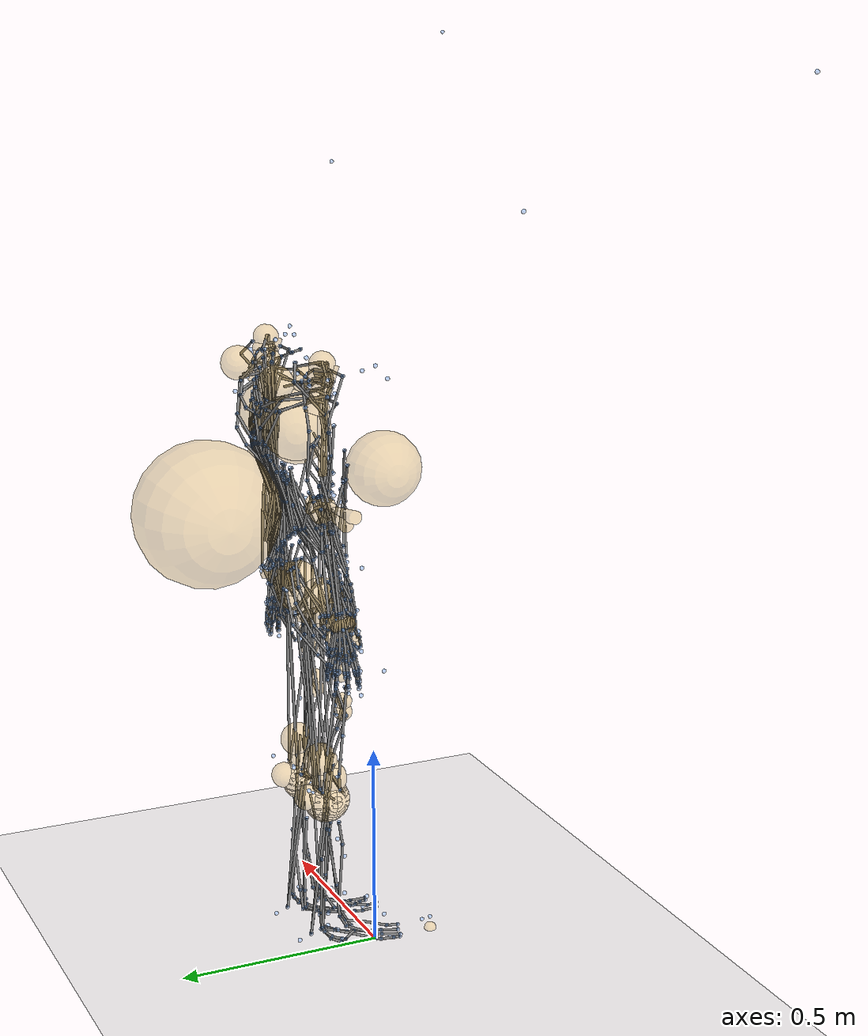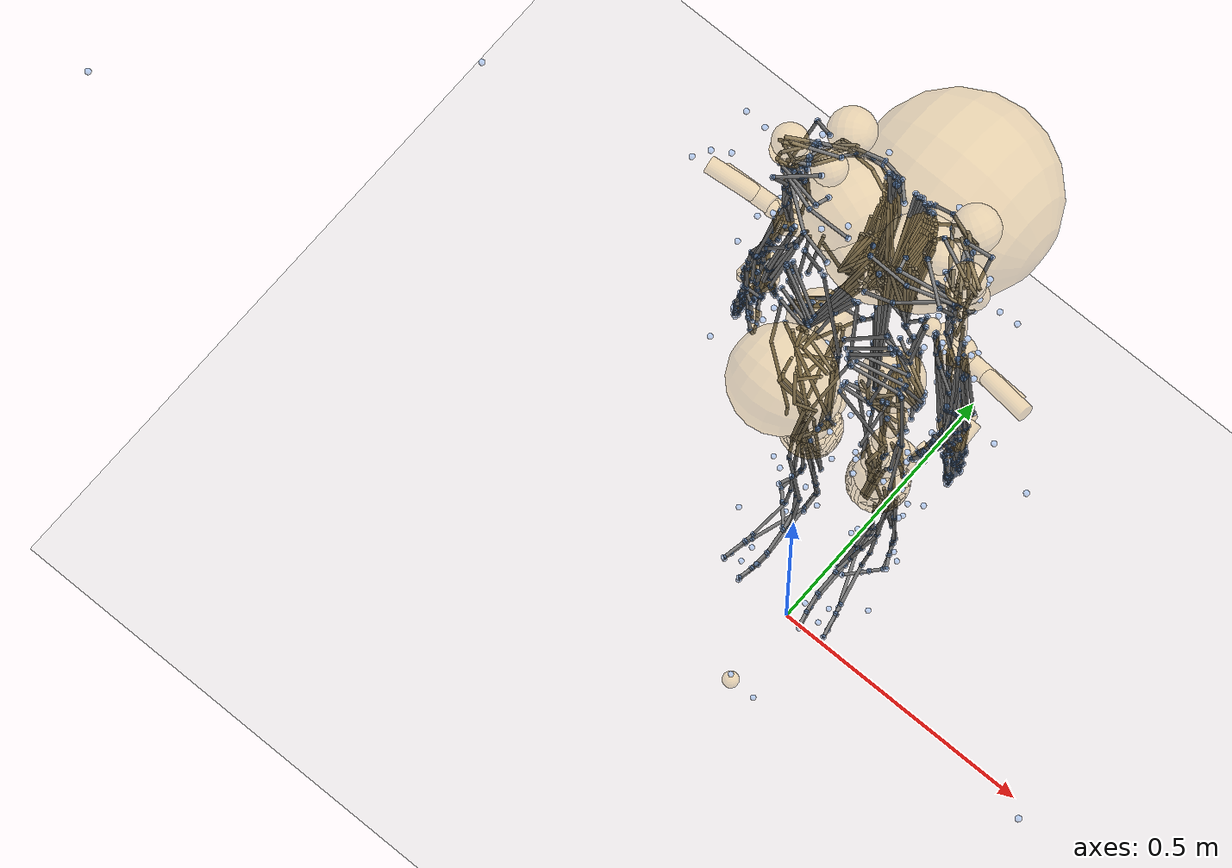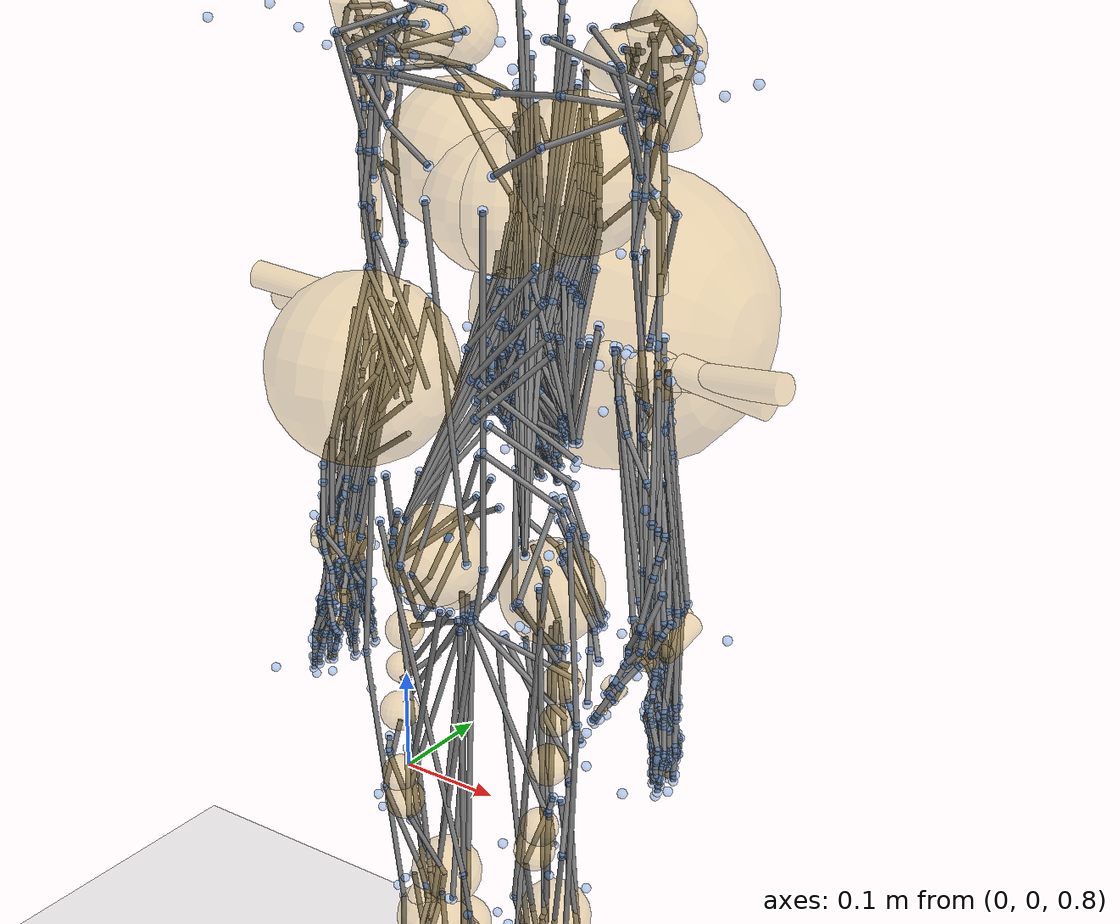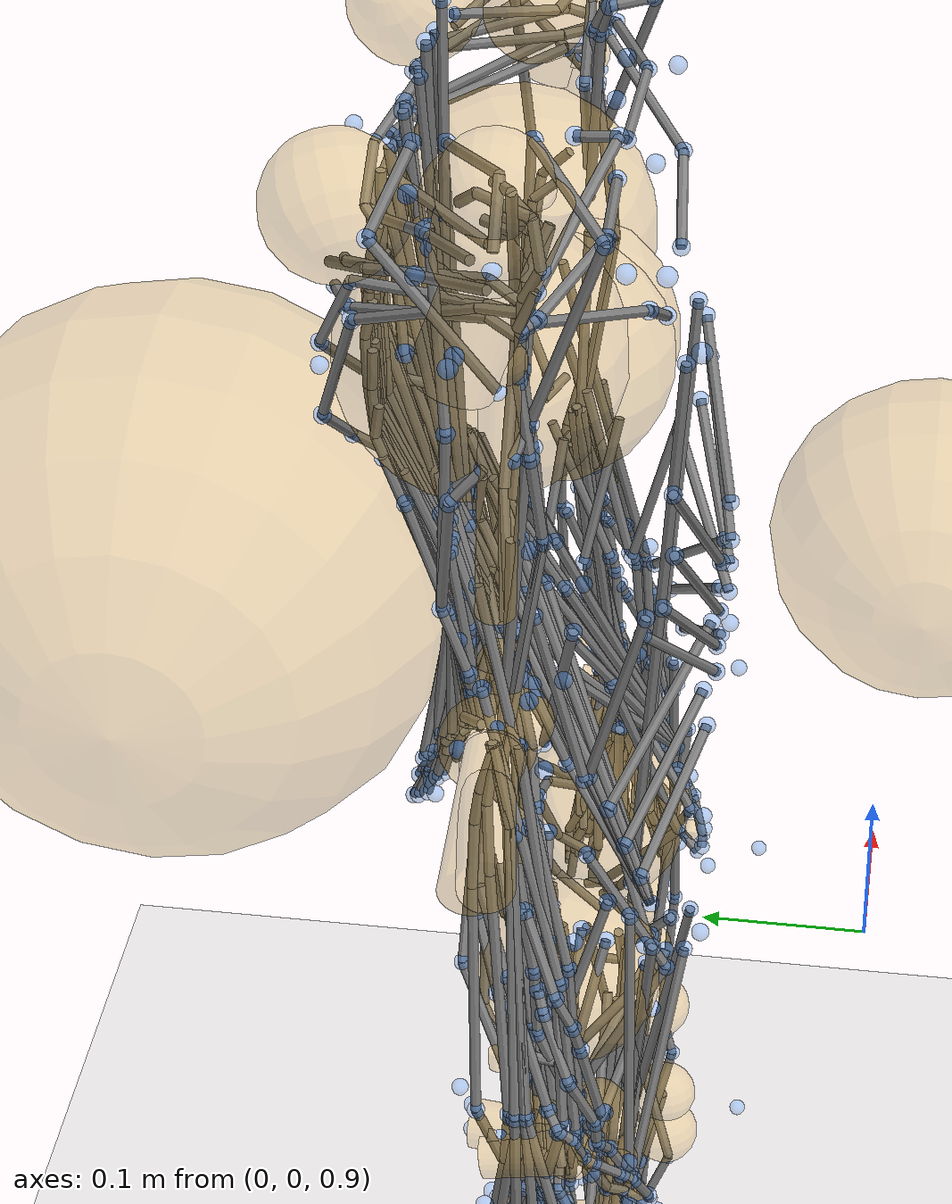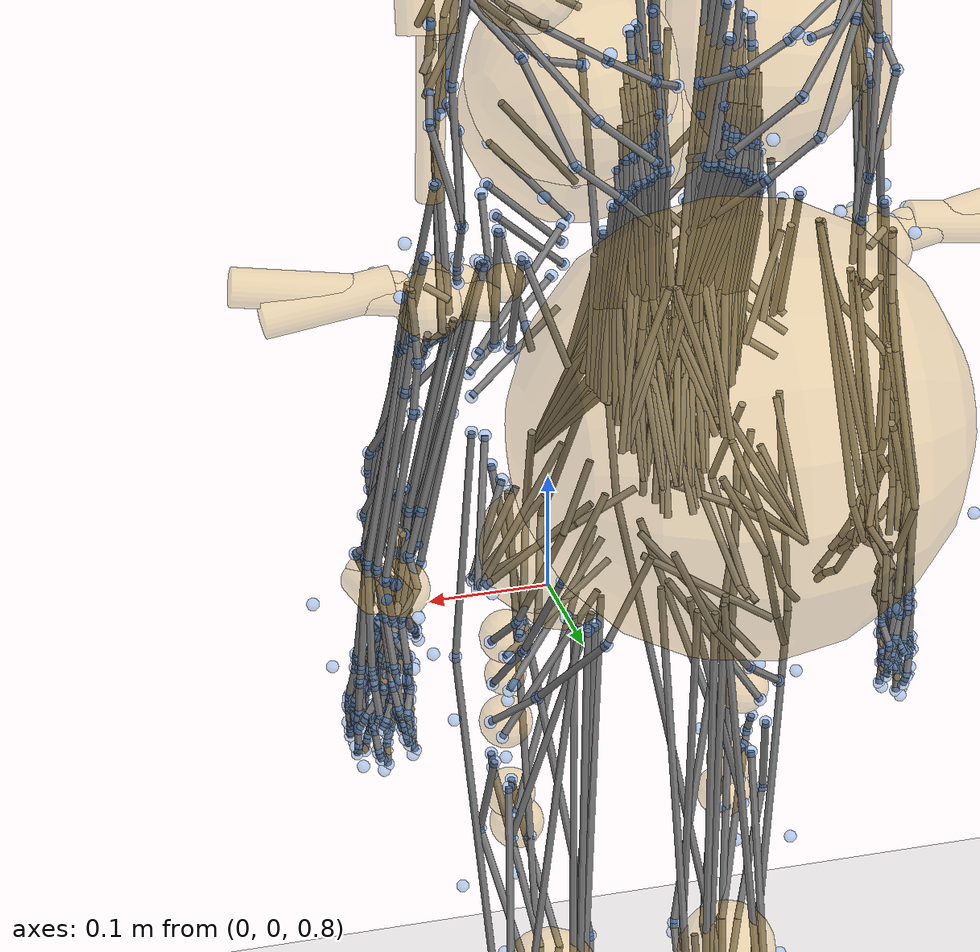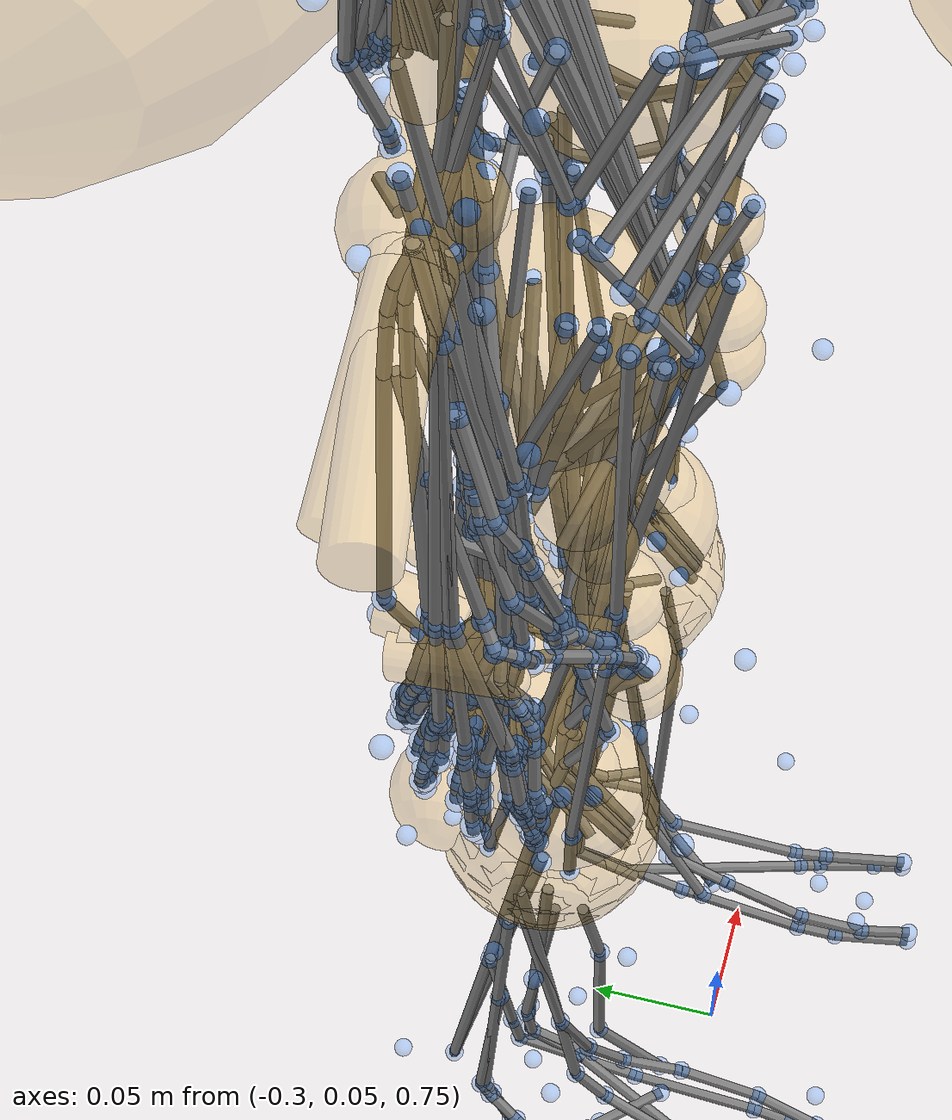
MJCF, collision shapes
<mujoco model="myofullbody">
  <option timestep="0.002" gravity="0 0 -9.81" integrator="implicitfast" solver="Newton" iterations="100" tolerance="1e-08" />
  <compiler angle="radian" balanceinertia="true" boundmass="0.001" boundinertia="0.0001" />
  <asset>
    <mesh name="sacrum_geom_1_sacrum" file="/home/hudson/melos/resources/third_party/myofullbody/body/../meshes/sacrum.stl" />
    <mesh name="lumbar5_geom_1_lumbar5" file="/home/hudson/melos/resources/third_party/myofullbody/body/../meshes/lumbar5.stl" />
    <mesh name="lumbar4_geom_1_lumbar4" file="/home/hudson/melos/resources/third_party/myofullbody/body/../meshes/lumbar4.stl" />
    <mesh name="lumbar3_geom_1_lumbar3" file="/home/hudson/melos/resources/third_party/myofullbody/body/../meshes/lumbar3.stl" />
    <mesh name="lumbar2_geom_1_lumbar2" file="/home/hudson/melos/resources/third_party/myofullbody/body/../meshes/lumbar2.stl" />
    <mesh name="lumbar1_geom_1_lumbar1" file="/home/hudson/melos/resources/third_party/myofullbody/body/../meshes/lumbar1.stl" />
    <mesh name="torso_geom_1_thoracic12_s" file="/home/hudson/melos/resources/third_party/myofullbody/body/../meshes/thoracic12_s.stl" />
    <mesh name="torso_geom_2_thoracic11_s" file="/home/hudson/melos/resources/third_party/myofullbody/body/../meshes/thoracic11_s.stl" />
    <mesh name="torso_geom_3_thoracic10_s" file="/home/hudson/melos/resources/third_party/myofullbody/body/../meshes/thoracic10_s.stl" />
    <mesh name="torso_geom_4_thoracic9_s" file="/home/hudson/melos/resources/third_party/myofullbody/body/../meshes/thoracic9_s.stl" />
    <mesh name="torso_geom_5_thoracic8_s" file="/home/hudson/melos/resources/third_party/myofullbody/body/../meshes/thoracic8_s.stl" />
    <mesh name="torso_geom_6_thoracic7_s" file="/home/hudson/melos/resources/third_party/myofullbody/body/../meshes/thoracic7_s.stl" />
    <mesh name="torso_geom_7_thoracic6_s" file="/home/hudson/melos/resources/third_party/myofullbody/body/../meshes/thoracic6_s.stl" />
    <mesh name="torso_geom_8_thoracic5_s" file="/home/hudson/melos/resources/third_party/myofullbody/body/../meshes/thoracic5_s.stl" />
    <mesh name="torso_geom_9_thoracic4_s" file="/home/hudson/melos/resources/third_party/myofullbody/body/../meshes/thoracic4_s.stl" />
    <mesh name="torso_geom_10_thoracic3_s" file="/home/hudson/melos/resources/third_party/myofullbody/body/../meshes/thoracic3_s.stl" />
    <mesh name="torso_geom_11_thoracic2_s" file="/home/hudson/melos/resources/third_party/myofullbody/body/../meshes/thoracic2_s.stl" />
    <mesh name="torso_geom_12_thoracic1_s" file="/home/hudson/melos/resources/third_party/myofullbody/body/../meshes/thoracic1_s.stl" />
    <mesh name="torso_geom_13_ribcage_s" file="/home/hudson/melos/resources/third_party/myofullbody/body/../meshes/thorax.stl" />
    <mesh name="hat_cervical" file="/home/hudson/melos/resources/third_party/myofullbody/body/../meshes/hat_cervical.stl" />
    <mesh name="hat_jaw" file="/home/hudson/melos/resources/third_party/myofullbody/body/../meshes/hat_jaw.stl" />
    <mesh name="hat_skull" file="/home/hudson/melos/resources/third_party/myofullbody/body/../meshes/hat_skull.stl" />
    <mesh name="clavicle_r" file="/home/hudson/melos/resources/third_party/myofullbody/body/../meshes/clavicle.stl" scale="1 1 1" />
    <mesh name="scapula_r" file="/home/hudson/melos/resources/third_party/myofullbody/body/../meshes/scapula.stl" scale="1 1 1" />
    <mesh name="humerus_r" file="/home/hudson/melos/resources/third_party/myofullbody/body/../meshes/humerus.stl" scale="1 1 1" />
    <mesh name="ulna_r" file="/home/hudson/melos/resources/third_party/myofullbody/body/../meshes/ulna.stl" scale="1 1 1" />
    <mesh name="radius_r" file="/home/hudson/melos/resources/third_party/myofullbody/body/../meshes/radius.stl" scale="1 1 1" />
    <mesh name="lunate_r" file="/home/hudson/melos/resources/third_party/myofullbody/body/../meshes/lunate.stl" scale="1 1 1" />
    <mesh name="scaphoid_r" file="/home/hudson/melos/resources/third_party/myofullbody/body/../meshes/scaphoid.stl" scale="1 1 1" />
    <mesh name="pisiform_r" file="/home/hudson/melos/resources/third_party/myofullbody/body/../meshes/pisiform.stl" scale="1 1 1" />
    <mesh name="triquetrum_r" file="/home/hudson/melos/resources/third_party/myofullbody/body/../meshes/triquetrum.stl" scale="1 1 1" />
    <mesh name="capitate_r" file="/home/hudson/melos/resources/third_party/myofullbody/body/../meshes/capitate.stl" scale="1 1 1" />
    <mesh name="trapezium_r" file="/home/hudson/melos/resources/third_party/myofullbody/body/../meshes/trapezium.stl" scale="1 1 1" />
    <mesh name="1mc_r" file="/home/hudson/melos/resources/third_party/myofullbody/body/../meshes/1mc.stl" scale="1 1 1" />
    <mesh name="thumbprox_r" file="/home/hudson/melos/resources/third_party/myofullbody/body/../meshes/thumbprox.stl" scale="1 1 1" />
    <mesh name="thumbdist_r" file="/home/hudson/melos/resources/third_party/myofullbody/body/../meshes/thumbdist.stl" scale="1 1 1" />
    <mesh name="trapezoid_r" file="/home/hudson/melos/resources/third_party/myofullbody/body/../meshes/trapezoid.stl" scale="1 1 1" />
    <mesh name="hamate_r" file="/home/hudson/melos/resources/third_party/myofullbody/body/../meshes/hamate.stl" scale="1 1 1" />
    <mesh name="2mc_r" file="/home/hudson/melos/resources/third_party/myofullbody/body/../meshes/2mc.stl" scale="1 1 1" />
    <mesh name="2proxph_r" file="/home/hudson/melos/resources/third_party/myofullbody/body/../meshes/2proxph.stl" scale="1 1 1" />
    <mesh name="2midph_r" file="/home/hudson/melos/resources/third_party/myofullbody/body/../meshes/2midph.stl" scale="1 1 1" />
    <mesh name="2distph_r" file="/home/hudson/melos/resources/third_party/myofullbody/body/../meshes/2distph.stl" scale="1 1 1" />
    <mesh name="3mc_r" file="/home/hudson/melos/resources/third_party/myofullbody/body/../meshes/3mc.stl" scale="1 1 1" />
    <mesh name="3proxph_r" file="/home/hudson/melos/resources/third_party/myofullbody/body/../meshes/3proxph.stl" scale="1 1 1" />
    <mesh name="3midph_r" file="/home/hudson/melos/resources/third_party/myofullbody/body/../meshes/3midph.stl" scale="1 1 1" />
    <mesh name="3distph_r" file="/home/hudson/melos/resources/third_party/myofullbody/body/../meshes/3distph.stl" scale="1 1 1" />
    <mesh name="4mc_r" file="/home/hudson/melos/resources/third_party/myofullbody/body/../meshes/4mc.stl" scale="1 1 1" />
    <mesh name="4proxph_r" file="/home/hudson/melos/resources/third_party/myofullbody/body/../meshes/4proxph.stl" scale="1 1 1" />
    <mesh name="4midph_r" file="/home/hudson/melos/resources/third_party/myofullbody/body/../meshes/4midph.stl" scale="1 1 1" />
    <mesh name="4distph_r" file="/home/hudson/melos/resources/third_party/myofullbody/body/../meshes/4distph.stl" scale="1 1 1" />
    <mesh name="5mc_r" file="/home/hudson/melos/resources/third_party/myofullbody/body/../meshes/5mc.stl" scale="1 1 1" />
    <mesh name="5proxph_r" file="/home/hudson/melos/resources/third_party/myofullbody/body/../meshes/5proxph.stl" scale="1 1 1" />
    <mesh name="5midph_r" file="/home/hudson/melos/resources/third_party/myofullbody/body/../meshes/5midph.stl" scale="1 1 1" />
    <mesh name="5distph_r" file="/home/hudson/melos/resources/third_party/myofullbody/body/../meshes/5distph.stl" scale="1 1 1" />
    <mesh name="clavicle_l" file="/home/hudson/melos/resources/third_party/myofullbody/body/../meshes/clavicle.stl" scale="1 1 -1" />
    <mesh name="scapula_l" file="/home/hudson/melos/resources/third_party/myofullbody/body/../meshes/scapula.stl" scale="1 1 -1" />
    <mesh name="humerus_l" file="/home/hudson/melos/resources/third_party/myofullbody/body/../meshes/humerus.stl" scale="1 1 -1" />
    <mesh name="ulna_l" file="/home/hudson/melos/resources/third_party/myofullbody/body/../meshes/ulna.stl" scale="1 1 -1" />
    <mesh name="radius_l" file="/home/hudson/melos/resources/third_party/myofullbody/body/../meshes/radius.stl" scale="1 1 -1" />
    <mesh name="lunate_l" file="/home/hudson/melos/resources/third_party/myofullbody/body/../meshes/lunate.stl" scale="1 1 -1" />
    <mesh name="scaphoid_l" file="/home/hudson/melos/resources/third_party/myofullbody/body/../meshes/scaphoid.stl" scale="1 1 -1" />
    <mesh name="pisiform_l" file="/home/hudson/melos/resources/third_party/myofullbody/body/../meshes/pisiform.stl" scale="1 1 -1" />
    <mesh name="triquetrum_l" file="/home/hudson/melos/resources/third_party/myofullbody/body/../meshes/triquetrum.stl" scale="1 1 -1" />
    <mesh name="capitate_l" file="/home/hudson/melos/resources/third_party/myofullbody/body/../meshes/capitate.stl" scale="1 1 -1" />
    <mesh name="trapezium_l" file="/home/hudson/melos/resources/third_party/myofullbody/body/../meshes/trapezium.stl" scale="1 1 -1" />
    <mesh name="1mc_l" file="/home/hudson/melos/resources/third_party/myofullbody/body/../meshes/1mc.stl" scale="1 1 -1" />
    <mesh name="thumbprox_l" file="/home/hudson/melos/resources/third_party/myofullbody/body/../meshes/thumbprox.stl" scale="1 1 -1" />
    <mesh name="thumbdist_l" file="/home/hudson/melos/resources/third_party/myofullbody/body/../meshes/thumbdist.stl" scale="1 1 -1" />
    <mesh name="trapezoid_l" file="/home/hudson/melos/resources/third_party/myofullbody/body/../meshes/trapezoid.stl" scale="1 1 -1" />
    <mesh name="hamate_l" file="/home/hudson/melos/resources/third_party/myofullbody/body/../meshes/hamate.stl" scale="1 1 -1" />
    <mesh name="2mc_l" file="/home/hudson/melos/resources/third_party/myofullbody/body/../meshes/2mc.stl" scale="1 1 -1" />
    <mesh name="2proxph_l" file="/home/hudson/melos/resources/third_party/myofullbody/body/../meshes/2proxph.stl" scale="1 1 -1" />
    <mesh name="2midph_l" file="/home/hudson/melos/resources/third_party/myofullbody/body/../meshes/2midph.stl" scale="1 1 -1" />
    <mesh name="2distph_l" file="/home/hudson/melos/resources/third_party/myofullbody/body/../meshes/2distph.stl" scale="1 1 -1" />
    <mesh name="3mc_l" file="/home/hudson/melos/resources/third_party/myofullbody/body/../meshes/3mc.stl" scale="1 1 -1" />
    <mesh name="3proxph_l" file="/home/hudson/melos/resources/third_party/myofullbody/body/../meshes/3proxph.stl" scale="1 1 -1" />
    <mesh name="3midph_l" file="/home/hudson/melos/resources/third_party/myofullbody/body/../meshes/3midph.stl" scale="1 1 -1" />
    <mesh name="3distph_l" file="/home/hudson/melos/resources/third_party/myofullbody/body/../meshes/3distph.stl" scale="1 1 -1" />
    <mesh name="4mc_l" file="/home/hudson/melos/resources/third_party/myofullbody/body/../meshes/4mc.stl" scale="1 1 -1" />
    <mesh name="4proxph_l" file="/home/hudson/melos/resources/third_party/myofullbody/body/../meshes/4proxph.stl" scale="1 1 -1" />
    <mesh name="4midph_l" file="/home/hudson/melos/resources/third_party/myofullbody/body/../meshes/4midph.stl" scale="1 1 -1" />
    <mesh name="4distph_l" file="/home/hudson/melos/resources/third_party/myofullbody/body/../meshes/4distph.stl" scale="1 1 -1" />
    <mesh name="5mc_l" file="/home/hudson/melos/resources/third_party/myofullbody/body/../meshes/5mc.stl" scale="1 1 -1" />
    <mesh name="5proxph_l" file="/home/hudson/melos/resources/third_party/myofullbody/body/../meshes/5proxph.stl" scale="1 1 -1" />
    <mesh name="5midph_l" file="/home/hudson/melos/resources/third_party/myofullbody/body/../meshes/5midph.stl" scale="1 1 -1" />
    <mesh name="5distph_l" file="/home/hudson/melos/resources/third_party/myofullbody/body/../meshes/5distph.stl" scale="1 1 -1" />
    <mesh name="r_pelvis" file="/home/hudson/melos/resources/third_party/myofullbody/body/../meshes/r_pelvis.stl" />
    <mesh name="l_pelvis" file="/home/hudson/melos/resources/third_party/myofullbody/body/../meshes/l_pelvis.stl" />
    <mesh name="r_femur" file="/home/hudson/melos/resources/third_party/myofullbody/body/../meshes/r_femur.stl" />
    <mesh name="r_tibia" file="/home/hudson/melos/resources/third_party/myofullbody/body/../meshes/r_tibia.stl" />
    <mesh name="r_fibula" file="/home/hudson/melos/resources/third_party/myofullbody/body/../meshes/r_fibula.stl" />
    <mesh name="r_talus" file="/home/hudson/melos/resources/third_party/myofullbody/body/../meshes/r_talus.stl" />
    <mesh name="r_foot" file="/home/hudson/melos/resources/third_party/myofullbody/body/../meshes/r_foot.stl" />
    <mesh name="r_bofoot" file="/home/hudson/melos/resources/third_party/myofullbody/body/../meshes/r_bofoot.stl" />
    <mesh name="r_patella" file="/home/hudson/melos/resources/third_party/myofullbody/body/../meshes/r_patella.stl" />
    <mesh name="l_femur" file="/home/hudson/melos/resources/third_party/myofullbody/body/../meshes/l_femur.stl" />
    <mesh name="l_tibia" file="/home/hudson/melos/resources/third_party/myofullbody/body/../meshes/l_tibia.stl" />
    <mesh name="l_fibula" file="/home/hudson/melos/resources/third_party/myofullbody/body/../meshes/l_fibula.stl" />
    <mesh name="l_talus" file="/home/hudson/melos/resources/third_party/myofullbody/body/../meshes/l_talus.stl" />
    <mesh name="l_foot" file="/home/hudson/melos/resources/third_party/myofullbody/body/../meshes/l_foot.stl" />
    <mesh name="l_bofoot" file="/home/hudson/melos/resources/third_party/myofullbody/body/../meshes/l_bofoot.stl" />
    <mesh name="l_patella" file="/home/hudson/melos/resources/third_party/myofullbody/body/../meshes/l_patella.stl" />
  </asset>
  <worldbody>
    <geom name="ground" type="plane" size="5 5 0.1" rgba="0.8 0.8 0.8 1" conaffinity="1" condim="3" />
    <body name="anatomical_link_Full Body" pos="-0.025 0.1 1">
      <body name="anatomical_link_sacrum" quat="0.500398 0.5 -0.5 -0.499602">
        <site name="anatomical_site_Ps_L1_VB_r_Ps_L1_VB_r-P2" pos="-0.0238 -0.008 0.0759" quat="1 0 0 0" size="0.005" rgba="0.2 0.5 0.9 0.35" />
        <site name="anatomical_site_Ps_L1_TP_r_Ps_L1_TP_r-P2" pos="-0.0238 -0.008 0.0759" quat="1 0 0 0" size="0.005" rgba="0.2 0.5 0.9 0.35" />
        <site name="anatomical_site_Ps_L1_L2_IVD_r_Ps_L1_L2_IVD_r-P2" pos="-0.0238 -0.008 0.0759" quat="1 0 0 0" size="0.005" rgba="0.2 0.5 0.9 0.35" />
        <site name="anatomical_site_Ps_L2_TP_r_Ps_L2_TP_r-P2" pos="-0.0238 -0.008 0.0759" quat="1 0 0 0" size="0.005" rgba="0.2 0.5 0.9 0.35" />
        <site name="anatomical_site_Ps_L2_L3_IVD_r_Ps_L2_L3_IVD_r-P2" pos="-0.0238 -0.008 0.0759" quat="1 0 0 0" size="0.005" rgba="0.2 0.5 0.9 0.35" />
        <site name="anatomical_site_Ps_L3_TP_r_Ps_L3_TP_r-P2" pos="-0.0238 -0.008 0.0759" quat="1 0 0 0" size="0.005" rgba="0.2 0.5 0.9 0.35" />
        <site name="anatomical_site_Ps_L3_L4_IVD_r_Ps_L3_L4_IVD_r-P2" pos="-0.0238 -0.008 0.0759" quat="1 0 0 0" size="0.005" rgba="0.2 0.5 0.9 0.35" />
        <site name="anatomical_site_Ps_L4_TP_r_Ps_L4_TP_r-P2" pos="-0.0238 -0.008 0.0759" quat="1 0 0 0" size="0.005" rgba="0.2 0.5 0.9 0.35" />
        <site name="anatomical_site_Ps_L4_L5_IVD_r_Ps_L4_L5_IVD_r-P2" pos="-0.0238 -0.008 0.0759" quat="1 0 0 0" size="0.005" rgba="0.2 0.5 0.9 0.35" />
        <site name="anatomical_site_Ps_L5_TP_r_Ps_L5_TP_r-P2" pos="-0.0238 -0.008 0.0759" quat="1 0 0 0" size="0.005" rgba="0.2 0.5 0.9 0.35" />
        <site name="anatomical_site_Ps_L5_VB_r_Ps_L5_VB_r-P2" pos="-0.0238 -0.008 0.0759" quat="1 0 0 0" size="0.005" rgba="0.2 0.5 0.9 0.35" />
        <site name="anatomical_site_Ps_L1_VB_l_Ps_L1_VB_l-P2" pos="-0.0238 -0.008 -0.0759" quat="1 0 0 0" size="0.005" rgba="0.2 0.5 0.9 0.35" />
        <site name="anatomical_site_Ps_L1_TP_l_Ps_L1_TP_l-P2" pos="-0.0238 -0.008 -0.0759" quat="1 0 0 0" size="0.005" rgba="0.2 0.5 0.9 0.35" />
        <site name="anatomical_site_Ps_L1_L2_IVD_l_Ps_L1_L2_IVD_l-P2" pos="-0.0238 -0.008 -0.0759" quat="1 0 0 0" size="0.005" rgba="0.2 0.5 0.9 0.35" />
        <site name="anatomical_site_Ps_L2_TP_l_Ps_L2_TP_l-P2" pos="-0.0238 -0.008 -0.0759" quat="1 0 0 0" size="0.005" rgba="0.2 0.5 0.9 0.35" />
        <site name="anatomical_site_Ps_L2_L3_IVD_l_Ps_L2_L3_IVD_l-P2" pos="-0.0238 -0.008 -0.0759" quat="1 0 0 0" size="0.005" rgba="0.2 0.5 0.9 0.35" />
        <site name="anatomical_site_Ps_L3_TP_l_Ps_L3_TP_l-P2" pos="-0.0238 -0.008 -0.0759" quat="1 0 0 0" size="0.005" rgba="0.2 0.5 0.9 0.35" />
        <site name="anatomical_site_Ps_L3_L4_IVD_l_Ps_L3_L4_IVD_l-P2" pos="-0.0238 -0.008 -0.0759" quat="1 0 0 0" size="0.005" rgba="0.2 0.5 0.9 0.35" />
        <site name="anatomical_site_Ps_L4_TP_l_Ps_L4_TP_l-P2" pos="-0.0238 -0.008 -0.0759" quat="1 0 0 0" size="0.005" rgba="0.2 0.5 0.9 0.35" />
        <site name="anatomical_site_Ps_L4_L5_IVD_l_Ps_L4_L5_IVD_l-P2" pos="-0.0238 -0.008 -0.0759" quat="1 0 0 0" size="0.005" rgba="0.2 0.5 0.9 0.35" />
        <site name="anatomical_site_Ps_L5_TP_l_Ps_L5_TP_l-P2" pos="-0.0238 -0.008 -0.0759" quat="1 0 0 0" size="0.005" rgba="0.2 0.5 0.9 0.35" />
        <site name="anatomical_site_Ps_L5_VB_l_Ps_L5_VB_l-P2" pos="-0.0238 -0.008 -0.0759" quat="1 0 0 0" size="0.005" rgba="0.2 0.5 0.9 0.35" />
        <site name="anatomical_site_rect_abd_r_rect_abd_r-P1" pos="-0.041582 -0.047476 -0.010689" quat="1 0 0 0" size="0.005" rgba="0.2 0.5 0.9 0.35" />
        <site name="anatomical_site_rect_abd_l_rect_abd_l-P1" pos="-0.041582 -0.047476 0.010689" quat="1 0 0 0" size="0.005" rgba="0.2 0.5 0.9 0.35" />
        <site name="anatomical_site_IL_L1_r_IL_L1_r-P1" pos="-0.15941 0.059946 0.038294" quat="1 0 0 0" size="0.005" rgba="0.2 0.5 0.9 0.35" />
        <site name="anatomical_site_IL_L2_r_IL_L2_r-P1" pos="-0.150919 0.077177 0.042649" quat="1 0 0 0" size="0.005" rgba="0.2 0.5 0.9 0.35" />
        <site name="anatomical_site_IL_L3_r_IL_L3_r-P1" pos="-0.13692 0.088811 0.047511" quat="1 0 0 0" size="0.005" rgba="0.2 0.5 0.9 0.35" />
        <site name="anatomical_site_IL_L4_r_IL_L4_r-P1" pos="-0.131838 0.085597 0.044204" quat="1 0 0 0" size="0.005" rgba="0.2 0.5 0.9 0.35" />
        <site name="anatomical_site_IL_L1_l_IL_L1_l-P1" pos="-0.15941 0.059946 -0.038294" quat="1 0 0 0" size="0.005" rgba="0.2 0.5 0.9 0.35" />
        <site name="anatomical_site_IL_L2_l_IL_L2_l-P1" pos="-0.150919 0.077177 -0.042649" quat="1 0 0 0" size="0.005" rgba="0.2 0.5 0.9 0.35" />
        <site name="anatomical_site_IL_L3_l_IL_L3_l-P1" pos="-0.13692 0.088811 -0.047511" quat="1 0 0 0" size="0.005" rgba="0.2 0.5 0.9 0.35" />
        <site name="anatomical_site_IL_L4_l_IL_L4_l-P1" pos="-0.131838 0.085597 -0.044204" quat="1 0 0 0" size="0.005" rgba="0.2 0.5 0.9 0.35" />
        <site name="anatomical_site_IL_R5_r_IL_r5_R-P1" pos="-0.156297 0.063318 0.038972" quat="1 0 0 0" size="0.005" rgba="0.2 0.5 0.9 0.35" />
        <site name="anatomical_site_IL_R6_r_IL_r6_R-P1" pos="-0.14525 0.080008 0.042568" quat="1 0 0 0" size="0.005" rgba="0.2 0.5 0.9 0.35" />
        <site name="anatomical_site_IL_R7_r_IL_r7_R-P1" pos="-0.134159 0.087356 0.045866" quat="1 0 0 0" size="0.005" rgba="0.2 0.5 0.9 0.35" />
        <site name="anatomical_site_IL_R8_r_IL_r8_R-P1" pos="-0.137327 0.091901 0.05018" quat="1 0 0 0" size="0.005" rgba="0.2 0.5 0.9 0.35" />
        <site name="anatomical_site_IL_R9_r_IL_r9_R-P1" pos="-0.13331 0.093884 0.051139" quat="1 0 0 0" size="0.005" rgba="0.2 0.5 0.9 0.35" />
        <site name="anatomical_site_IL_R10_r_IL_r10_R-P1" pos="-0.130303 0.09675 0.053109" quat="1 0 0 0" size="0.005" rgba="0.2 0.5 0.9 0.35" />
        <site name="anatomical_site_IL_R11_r_IL_r11_R-P1" pos="-0.127464 0.098957 0.055471" quat="1 0 0 0" size="0.005" rgba="0.2 0.5 0.9 0.35" />
        <site name="anatomical_site_IL_R12_r_IL_r12_R-P1" pos="-0.124813 0.101124 0.057925" quat="1 0 0 0" size="0.005" rgba="0.2 0.5 0.9 0.35" />
        <site name="anatomical_site_IL_R5_l_IL_r5_R-P1" pos="-0.156297 0.063318 -0.03897" quat="1 0 0 0" size="0.005" rgba="0.2 0.5 0.9 0.35" />
        <site name="anatomical_site_IL_R6_l_IL_r6_R-P1" pos="-0.14525 0.080008 -0.04257" quat="1 0 0 0" size="0.005" rgba="0.2 0.5 0.9 0.35" />
        <site name="anatomical_site_IL_R7_l_IL_r7_R-P1" pos="-0.134159 0.087356 -0.04587" quat="1 0 0 0" size="0.005" rgba="0.2 0.5 0.9 0.35" />
        <site name="anatomical_site_IL_R8_l_IL_r8_R-P1" pos="-0.137327 0.091901 -0.05018" quat="1 0 0 0" size="0.005" rgba="0.2 0.5 0.9 0.35" />
        <site name="anatomical_site_IL_R9_l_IL_r9_R-P1" pos="-0.13331 0.093884 -0.05114" quat="1 0 0 0" size="0.005" rgba="0.2 0.5 0.9 0.35" />
        <site name="anatomical_site_IL_R10_l_IL_r10_R-P1" pos="-0.130303 0.09675 -0.05311" quat="1 0 0 0" size="0.005" rgba="0.2 0.5 0.9 0.35" />
        <site name="anatomical_site_IL_R11_l_IL_r11_R-P1" pos="-0.127464 0.098957 -0.05547" quat="1 0 0 0" size="0.005" rgba="0.2 0.5 0.9 0.35" />
        <site name="anatomical_site_IL_R12_l_IL_r12_R-P1" pos="-0.124813 0.101124 -0.05792" quat="1 0 0 0" size="0.005" rgba="0.2 0.5 0.9 0.35" />
        <site name="anatomical_site_LTpL_L4_r_pathpoint" pos="-0.150501 0.066487 0.03731" quat="1 0 0 0" size="0.005" rgba="0.2 0.5 0.9 0.35" />
        <site name="anatomical_site_LTpL_L3_r_pathpoint" pos="-0.158442 0.06649 0.0402" quat="1 0 0 0" size="0.005" rgba="0.2 0.5 0.9 0.35" />
        <site name="anatomical_site_LTpL_L2_r_pathpoint" pos="-0.159688 0.061969 0.041946" quat="1 0 0 0" size="0.005" rgba="0.2 0.5 0.9 0.35" />
        <site name="anatomical_site_LTpL_L1_r_pathpoint" pos="-0.161991 0.059194 0.043117" quat="1 0 0 0" size="0.005" rgba="0.2 0.5 0.9 0.35" />
        <site name="anatomical_site_LTpL_L4_l_pathpoint" pos="-0.150501 0.066487 -0.03731" quat="1 0 0 0" size="0.005" rgba="0.2 0.5 0.9 0.35" />
        <site name="anatomical_site_LTpL_L3_l_pathpoint" pos="-0.158442 0.06649 -0.0402" quat="1 0 0 0" size="0.005" rgba="0.2 0.5 0.9 0.35" />
        <site name="anatomical_site_LTpL_L2_l_pathpoint" pos="-0.159688 0.061969 -0.041946" quat="1 0 0 0" size="0.005" rgba="0.2 0.5 0.9 0.35" />
        <site name="anatomical_site_LTpL_L1_l_pathpoint" pos="-0.161991 0.059194 -0.043117" quat="1 0 0 0" size="0.005" rgba="0.2 0.5 0.9 0.35" />
        <site name="anatomical_site_QL_post_I.1-L3_r_I.1_r-P1" pos="-0.12147 0.09531 0.05202" quat="1 0 0 0" size="0.005" rgba="0.2 0.5 0.9 0.35" />
        <site name="anatomical_site_QL_post_I.2-L4_r_I.2_r-P1" pos="-0.11147 0.105308 0.05902" quat="1 0 0 0" size="0.005" rgba="0.2 0.5 0.9 0.35" />
        <site name="anatomical_site_QL_post_I.2-L3_r_I.2_r-P1" pos="-0.11147 0.105308 0.05902" quat="1 0 0 0" size="0.005" rgba="0.2 0.5 0.9 0.35" />
        <site name="anatomical_site_QL_post_I.2-L2_r_I.2_r-P1" pos="-0.11147 0.105308 0.05902" quat="1 0 0 0" size="0.005" rgba="0.2 0.5 0.9 0.35" />
        <site name="anatomical_site_QL_post_I.3-L1_r_I.3_r-P1" pos="-0.10477 0.11112 0.06917" quat="1 0 0 0" size="0.005" rgba="0.2 0.5 0.9 0.35" />
        <site name="anatomical_site_QL_post_I.3-L2_r_I.3_r-P1" pos="-0.10477 0.11112 0.06917" quat="1 0 0 0" size="0.005" rgba="0.2 0.5 0.9 0.35" />
        <site name="anatomical_site_QL_post_I.3-L3_r_I.3_r-P1" pos="-0.10477 0.11112 0.06917" quat="1 0 0 0" size="0.005" rgba="0.2 0.5 0.9 0.35" />
        <site name="anatomical_site_QL_post_I.1-L3_l_I.1_l-P1" pos="-0.12147 0.09531 -0.05202" quat="1 0 0 0" size="0.005" rgba="0.2 0.5 0.9 0.35" />
        <site name="anatomical_site_QL_post_I.2-L4_l_I.2_l-P1" pos="-0.11147 0.105308 -0.05902" quat="1 0 0 0" size="0.005" rgba="0.2 0.5 0.9 0.35" />
        <site name="anatomical_site_QL_post_I.2-L3_l_I.2_l-P1" pos="-0.11147 0.105308 -0.05902" quat="1 0 0 0" size="0.005" rgba="0.2 0.5 0.9 0.35" />
        <site name="anatomical_site_QL_post_I.2-L2_l_I.2_l-P1" pos="-0.11147 0.105308 -0.05902" quat="1 0 0 0" size="0.005" rgba="0.2 0.5 0.9 0.35" />
        <site name="anatomical_site_QL_post_I.3-L1_l_I.3_l-P1" pos="-0.10477 0.11112 -0.06917" quat="1 0 0 0" size="0.005" rgba="0.2 0.5 0.9 0.35" />
        <site name="anatomical_site_QL_post_I.3-L2_l_I.3_l-P1" pos="-0.10477 0.11112 -0.06917" quat="1 0 0 0" size="0.005" rgba="0.2 0.5 0.9 0.35" />
        <site name="anatomical_site_QL_post_I.3-L3_l_I.3_l-P1" pos="-0.10477 0.11112 -0.06917" quat="1 0 0 0" size="0.005" rgba="0.2 0.5 0.9 0.35" />
        <site name="anatomical_site_QL_ant_I.2-T12_r_I.2_r-P1" pos="-0.11147 0.105308 0.05902" quat="1 0 0 0" size="0.005" rgba="0.2 0.5 0.9 0.35" />
        <site name="anatomical_site_QL_ant_I.3-T12_r_I.3_r-P1" pos="-0.10477 0.11112 0.06917" quat="1 0 0 0" size="0.005" rgba="0.2 0.5 0.9 0.35" />
        <site name="anatomical_site_QL_ant_I.2-12.1_r_I.2_r-P2" pos="-0.11147 0.105308 0.05902" quat="1 0 0 0" size="0.005" rgba="0.2 0.5 0.9 0.35" />
        <site name="anatomical_site_QL_ant_I.3-12.1_r_I.3_r-P1" pos="-0.10477 0.11112 0.06917" quat="1 0 0 0" size="0.005" rgba="0.2 0.5 0.9 0.35" />
        <site name="anatomical_site_QL_ant_I.3-12.2_r_I.3_r-P1" pos="-0.10477 0.11112 0.06917" quat="1 0 0 0" size="0.005" rgba="0.2 0.5 0.9 0.35" />
        <site name="anatomical_site_QL_ant_I.3-12.3_r_I.3_r-P2" pos="-0.104767 0.111115 0.06917" quat="1 0 0 0" size="0.005" rgba="0.2 0.5 0.9 0.35" />
        <site name="anatomical_site_QL_ant_I.2-T12_l_I.2_l-P1" pos="-0.11147 0.105308 -0.05902" quat="1 0 0 0" size="0.005" rgba="0.2 0.5 0.9 0.35" />
        <site name="anatomical_site_QL_ant_I.3-T12_l_I.3_l-P1" pos="-0.10477 0.11112 -0.06917" quat="1 0 0 0" size="0.005" rgba="0.2 0.5 0.9 0.35" />
        <site name="anatomical_site_QL_ant_I.2-12.1_l_I.2_l-P2" pos="-0.11147 0.105308 -0.05902" quat="1 0 0 0" size="0.005" rgba="0.2 0.5 0.9 0.35" />
        <site name="anatomical_site_QL_ant_I.3-12.1_l_I.3_l-P1" pos="-0.10477 0.11112 -0.06917" quat="1 0 0 0" size="0.005" rgba="0.2 0.5 0.9 0.35" />
        <site name="anatomical_site_QL_ant_I.3-12.2_l_I.3_l-P1" pos="-0.10477 0.11112 -0.06917" quat="1 0 0 0" size="0.005" rgba="0.2 0.5 0.9 0.35" />
        <site name="anatomical_site_QL_ant_I.3-12.3_l_I.3_l-P2" pos="-0.104767 0.111115 -0.06917" quat="1 0 0 0" size="0.005" rgba="0.2 0.5 0.9 0.35" />
        <site name="anatomical_site_MF_m1t.3_r_MF_m1t.3_r-P1" pos="-0.144573 0.075421 0.03835" quat="1 0 0 0" size="0.005" rgba="0.2 0.5 0.9 0.35" />
        <site name="anatomical_site_MF_m2t.2_r_MF_m2t.2_r-P1" pos="-0.147335 0.070159 0.036849" quat="1 0 0 0" size="0.005" rgba="0.2 0.5 0.9 0.35" />
        <site name="anatomical_site_MF_m2t.3_r_MF_m2t.3_r-P1" pos="-0.14972 0.056998 0.034578" quat="1 0 0 0" size="0.005" rgba="0.2 0.5 0.9 0.35" />
        <site name="anatomical_site_MF_m3t.1_r_MF_m3t.1_r-P1" pos="-0.164505 0.014023 0.0171" quat="1 0 0 0" size="0.005" rgba="0.2 0.5 0.9 0.35" />
        <site name="anatomical_site_MF_m3t.2_r_MF_m3t.2_r-P1" pos="-0.153875 0.032938 0.021854" quat="1 0 0 0" size="0.005" rgba="0.2 0.5 0.9 0.35" />
        <site name="anatomical_site_MF_m3t.3_r_MF_m3t.3_r-P1" pos="-0.153875 0.032938 0.021854" quat="1 0 0 0" size="0.005" rgba="0.2 0.5 0.9 0.35" />
        <site name="anatomical_site_MF_m4t.2_r_MF_m4t.2_r-P1" pos="-0.162292 0.020342 0.015204" quat="1 0 0 0" size="0.005" rgba="0.2 0.5 0.9 0.35" />
        <site name="anatomical_site_MF_m4t.3_r_MF_m4t.3_r-P1" pos="-0.170828 0.007819 0.012722" quat="1 0 0 0" size="0.005" rgba="0.2 0.5 0.9 0.35" />
        <site name="anatomical_site_MF_m5.laminar_r_MF_m5.laminar_r-P1" pos="-0.134206 0.06011 0.01238" quat="1 0 0 0" size="0.005" rgba="0.2 0.5 0.9 0.35" />
        <site name="anatomical_site_MF_m1t.3_l_MF_m1t.3_l-P1" pos="-0.144573 0.075421 -0.03835" quat="1 0 0 0" size="0.005" rgba="0.2 0.5 0.9 0.35" />
        <site name="anatomical_site_MF_m2t.2_l_MF_m2t.2_l-P1" pos="-0.147335 0.070159 -0.036849" quat="1 0 0 0" size="0.005" rgba="0.2 0.5 0.9 0.35" />
        <site name="anatomical_site_MF_m2t.3_l_MF_m2t.3_l-P1" pos="-0.14972 0.056998 -0.034578" quat="1 0 0 0" size="0.005" rgba="0.2 0.5 0.9 0.35" />
        <site name="anatomical_site_MF_m3t.1_l_MF_m3t.1_l-P1" pos="-0.164505 0.014023 -0.0171" quat="1 0 0 0" size="0.005" rgba="0.2 0.5 0.9 0.35" />
        <site name="anatomical_site_MF_m3t.2_l_MF_m3t.2_l-P1" pos="-0.153875 0.032938 -0.021854" quat="1 0 0 0" size="0.005" rgba="0.2 0.5 0.9 0.35" />
        <site name="anatomical_site_MF_m3t.3_l_MF_m3t.3_l-P1" pos="-0.153875 0.032938 -0.021854" quat="1 0 0 0" size="0.005" rgba="0.2 0.5 0.9 0.35" />
        <site name="anatomical_site_MF_m4t.2_l_MF_m4t.2_l-P1" pos="-0.162292 0.020342 -0.015204" quat="1 0 0 0" size="0.005" rgba="0.2 0.5 0.9 0.35" />
        <site name="anatomical_site_MF_m4t.3_l_MF_m4t.3_l-P1" pos="-0.170828 0.007819 -0.012722" quat="1 0 0 0" size="0.005" rgba="0.2 0.5 0.9 0.35" />
        <site name="anatomical_site_MF_m5.laminar_l_MF_m5.laminar_l-P1" pos="-0.134206 0.06011 -0.01238" quat="1 0 0 0" size="0.005" rgba="0.2 0.5 0.9 0.35" />
        <site name="anatomical_site_EO5_r_EO5_r-P2" pos="-0.059266 0.108414 0.11382" quat="1 0 0 0" size="0.005" rgba="0.2 0.5 0.9 0.35" />
        <site name="anatomical_site_EO6_r_EO6_r-P2" pos="-0.070076 0.111137 0.10412" quat="1 0 0 0" size="0.005" rgba="0.2 0.5 0.9 0.35" />
        <site name="anatomical_site_IO1_r_IO1_r-P2" pos="-0.025649 0.049609 0.12246" quat="1 0 0 0" size="0.005" rgba="0.2 0.5 0.9 0.35" />
        <site name="anatomical_site_IO2_r_IO2_r-P2" pos="-0.034589 0.074567 0.12707" quat="1 0 0 0" size="0.005" rgba="0.2 0.5 0.9 0.35" />
        <site name="anatomical_site_IO3_r_IO3_r-P2" pos="-0.04468 0.095659 0.12243" quat="1 0 0 0" size="0.005" rgba="0.2 0.5 0.9 0.35" />
        <site name="anatomical_site_IO4_r_IO4_r-P2" pos="-0.05738 0.107899 0.11049" quat="1 0 0 0" size="0.005" rgba="0.2 0.5 0.9 0.35" />
        <site name="anatomical_site_IO5_r_IO5_r-P2" pos="-0.084889 0.114154 0.09145" quat="1 0 0 0" size="0.005" rgba="0.2 0.5 0.9 0.35" />
        <site name="anatomical_site_IO6_r_IO6_r-P2" pos="-0.1096 0.109856 0.0697" quat="1 0 0 0" size="0.005" rgba="0.2 0.5 0.9 0.35" />
        <site name="anatomical_site_EO5_l_EO5_l-P2" pos="-0.059266 0.108414 -0.11382" quat="1 0 0 0" size="0.005" rgba="0.2 0.5 0.9 0.35" />
        <site name="anatomical_site_EO6_l_EO6_l-P2" pos="-0.070076 0.111137 -0.10412" quat="1 0 0 0" size="0.005" rgba="0.2 0.5 0.9 0.35" />
        <site name="anatomical_site_IO1_l_IO1_l-P2" pos="-0.025649 0.049609 -0.12246" quat="1 0 0 0" size="0.005" rgba="0.2 0.5 0.9 0.35" />
        <site name="anatomical_site_IO2_l_IO2_l-P2" pos="-0.034589 0.074567 -0.12707" quat="1 0 0 0" size="0.005" rgba="0.2 0.5 0.9 0.35" />
        <site name="anatomical_site_IO3_l_IO3_l-P2" pos="-0.04468 0.095659 -0.12243" quat="1 0 0 0" size="0.005" rgba="0.2 0.5 0.9 0.35" />
        <site name="anatomical_site_IO4_l_IO4_l-P2" pos="-0.05738 0.107899 -0.11049" quat="1 0 0 0" size="0.005" rgba="0.2 0.5 0.9 0.35" />
        <site name="anatomical_site_IO5_l_IO5_l-P2" pos="-0.084889 0.114154 -0.09145" quat="1 0 0 0" size="0.005" rgba="0.2 0.5 0.9 0.35" />
        <site name="anatomical_site_IO6_l_IO6_l-P2" pos="-0.1096 0.109856 -0.0697" quat="1 0 0 0" size="0.005" rgba="0.2 0.5 0.9 0.35" />
        <site name="anatomical_site_LTpT_T7_r_LTpT_t7_R-P1" pos="-0.131317 0.0605127 0.00027686" quat="1 0 0 0" size="0.005" rgba="0.2 0.5 0.9 0.35" />
        <site name="anatomical_site_LTpT_T8_r_LTpT_t8_R-P1" pos="-0.142901 0.0502456 0.00037451" quat="1 0 0 0" size="0.005" rgba="0.2 0.5 0.9 0.35" />
        <site name="anatomical_site_LTpT_T9_r_LTpT_t9_R-P1" pos="-0.165822 0.0268352 0" quat="1 0 0 0" size="0.005" rgba="0.2 0.5 0.9 0.35" />
        <site name="anatomical_site_LTpT_T10_r_LTpT_t10_R-P1" pos="-0.164463 0.0245611 0.01072" quat="1 0 0 0" size="0.005" rgba="0.2 0.5 0.9 0.35" />
        <site name="anatomical_site_LTpT_T11_r_LTpT_t11_R-P1" pos="-0.157649 0.0307094 0.02404" quat="1 0 0 0" size="0.005" rgba="0.2 0.5 0.9 0.35" />
        <site name="anatomical_site_LTpT_T12_r_LTpT_t12_R-P1" pos="-0.14476 0.0488 0.02793" quat="1 0 0 0" size="0.005" rgba="0.2 0.5 0.9 0.35" />
        <site name="anatomical_site_LTpT_R7_r_LTpT_r7_R-P1" pos="-0.13132 0.06051 0.00028" quat="1 0 0 0" size="0.005" rgba="0.2 0.5 0.9 0.35" />
        <site name="anatomical_site_LTpT_R8_r_LTpT_r8_R-P1" pos="-0.1429 0.05025 0.00037" quat="1 0 0 0" size="0.005" rgba="0.2 0.5 0.9 0.35" />
        <site name="anatomical_site_LTpT_R9_r_LTpT_r9_R-P1" pos="-0.16582 0.0268352 0" quat="1 0 0 0" size="0.005" rgba="0.2 0.5 0.9 0.35" />
        <site name="anatomical_site_LTpT_R10_r_LTpT_r10_R-P1" pos="-0.16446 0.02456 0.01072" quat="1 0 0 0" size="0.005" rgba="0.2 0.5 0.9 0.35" />
        <site name="anatomical_site_LTpT_R11_r_LTpT_r11_R-P1" pos="-0.15765 0.03071 0.02404" quat="1 0 0 0" size="0.005" rgba="0.2 0.5 0.9 0.35" />
        <site name="anatomical_site_LTpT_R12_r_LTpT_r12_R-P1" pos="-0.14476 0.0488 0.02793" quat="1 0 0 0" size="0.005" rgba="0.2 0.5 0.9 0.35" />
        <site name="anatomical_site_LTpT_T7_l_LTpT_t7_R-P1" pos="-0.131317 0.0605127 -0.00027686" quat="1 0 0 0" size="0.005" rgba="0.2 0.5 0.9 0.35" />
        <site name="anatomical_site_LTpT_T8_l_LTpT_t8_R-P1" pos="-0.142901 0.0502456 -0.00037451" quat="1 0 0 0" size="0.005" rgba="0.2 0.5 0.9 0.35" />
        <site name="anatomical_site_LTpT_T9_l_LTpT_t9_R-P1" pos="-0.165822 0.0268352 0" quat="1 0 0 0" size="0.005" rgba="0.2 0.5 0.9 0.35" />
        <site name="anatomical_site_LTpT_T10_l_LTpT_t10_R-P1" pos="-0.164463 0.0245611 -0.01072" quat="1 0 0 0" size="0.005" rgba="0.2 0.5 0.9 0.35" />
        <site name="anatomical_site_LTpT_T11_l_LTpT_t11_R-P1" pos="-0.157649 0.0307094 -0.02404" quat="1 0 0 0" size="0.005" rgba="0.2 0.5 0.9 0.35" />
        <site name="anatomical_site_LTpT_T12_l_LTpT_t12_R-P1" pos="-0.14476 0.0488 0.02793" quat="1 0 0 0" size="0.005" rgba="0.2 0.5 0.9 0.35" />
        <site name="anatomical_site_LTpT_R7_l_LTpT_r7_R-P1" pos="-0.13132 0.06051 -0.00028" quat="1 0 0 0" size="0.005" rgba="0.2 0.5 0.9 0.35" />
        <site name="anatomical_site_LTpT_R8_l_LTpT_r8_R-P1" pos="-0.1429 0.05025 -0.00037" quat="1 0 0 0" size="0.005" rgba="0.2 0.5 0.9 0.35" />
        <site name="anatomical_site_LTpT_R9_l_LTpT_r9_R-P1" pos="-0.16582 0.0268352 0" quat="1 0 0 0" size="0.005" rgba="0.2 0.5 0.9 0.35" />
        <site name="anatomical_site_LTpT_R10_l_LTpT_r10_R-P1" pos="-0.16446 0.02456 -0.01072" quat="1 0 0 0" size="0.005" rgba="0.2 0.5 0.9 0.35" />
        <site name="anatomical_site_LTpT_R11_l_LTpT_r11_R-P1" pos="-0.15765 0.03071 -0.02404" quat="1 0 0 0" size="0.005" rgba="0.2 0.5 0.9 0.35" />
        <site name="anatomical_site_LTpT_R12_l_LTpT_r12_R-P1" pos="-0.14476 0.0488 -0.02793" quat="1 0 0 0" size="0.005" rgba="0.2 0.5 0.9 0.35" />
        <site name="anatomical_site_LTpL_L5_r_pathpoint" pos="-0.14125 0.0738877 0.034867" quat="1 0 0 0" size="0.005" rgba="0.2 0.5 0.9 0.35" />
        <site name="anatomical_site_LTpL_L5_l_pathpoint" pos="-0.14125 0.0738877 -0.034867" quat="1 0 0 0" size="0.005" rgba="0.2 0.5 0.9 0.35" />
        <site name="anatomical_site_MF_m1t.2_r_MF_m1t.2_r-P1" pos="-0.121424 0.0839766 0.01884" quat="1 0 0 0" size="0.005" rgba="0.2 0.5 0.9 0.35" />
        <site name="anatomical_site_MF_m2t.1_r_MF_m2t.1_r-P1" pos="-0.120758 0.0852181 0.02044" quat="1 0 0 0" size="0.005" rgba="0.2 0.5 0.9 0.35" />
        <site name="anatomical_site_MF_m3s_r_MF_m3s_r-P1" pos="-0.121511 0.0836358 0.01742" quat="1 0 0 0" size="0.005" rgba="0.2 0.5 0.9 0.35" />
        <site name="anatomical_site_MF_m4s_r_MF_m4s_r-P1" pos="-0.143689 0.0547099 0.01618" quat="1 0 0 0" size="0.005" rgba="0.2 0.5 0.9 0.35" />
        <site name="anatomical_site_MF_m4t.1_r_MF_m4t.1_r-P1" pos="-0.152233 0.0415265 0.01536" quat="1 0 0 0" size="0.005" rgba="0.2 0.5 0.9 0.35" />
        <site name="anatomical_site_MF_m5s_r_MF_m5s_r-P1" pos="-0.130455 0.0662703 0.01043" quat="1 0 0 0" size="0.005" rgba="0.2 0.5 0.9 0.35" />
        <site name="anatomical_site_MF_m5t.1_r_MF_m5t.1_r-P1" pos="-0.174067 0.00522922 0.01003" quat="1 0 0 0" size="0.005" rgba="0.2 0.5 0.9 0.35" />
        <site name="anatomical_site_MF_m5t.2_r_MF_m5t.2_r-P1" pos="-0.163116 0.0256618 0.01171" quat="1 0 0 0" size="0.005" rgba="0.2 0.5 0.9 0.35" />
        <site name="anatomical_site_MF_m5t.3_r_MF_m5t.3_r-P1" pos="-0.152276 0.0425844 0.0116" quat="1 0 0 0" size="0.005" rgba="0.2 0.5 0.9 0.35" />
        <site name="anatomical_site_MF_m4.laminar_r_MF_m4.laminar_r-P1" pos="-0.12536 0.0774879 0.01934" quat="1 0 0 0" size="0.005" rgba="0.2 0.5 0.9 0.35" />
        <site name="anatomical_site_MF_m1t.2_l_MF_m1t.2_l-P1" pos="-0.121424 0.0839766 -0.01884" quat="1 0 0 0" size="0.005" rgba="0.2 0.5 0.9 0.35" />
        <site name="anatomical_site_MF_m2t.1_l_MF_m2t.1_l-P1" pos="-0.120758 0.0852181 -0.02044" quat="1 0 0 0" size="0.005" rgba="0.2 0.5 0.9 0.35" />
        <site name="anatomical_site_MF_m3s_l_MF_m3s_l-P1" pos="-0.121511 0.0836358 -0.01742" quat="1 0 0 0" size="0.005" rgba="0.2 0.5 0.9 0.35" />
        <site name="anatomical_site_MF_m4s_l_MF_m4s_l-P1" pos="-0.143689 0.0547099 -0.01618" quat="1 0 0 0" size="0.005" rgba="0.2 0.5 0.9 0.35" />
        <site name="anatomical_site_MF_m4t.1_l_MF_m4t.1_l-P1" pos="-0.152233 0.0415265 -0.01536" quat="1 0 0 0" size="0.005" rgba="0.2 0.5 0.9 0.35" />
        <site name="anatomical_site_MF_m5s_l_MF_m5s_l-P1" pos="-0.130455 0.0662703 -0.01043" quat="1 0 0 0" size="0.005" rgba="0.2 0.5 0.9 0.35" />
        <site name="anatomical_site_MF_m5t.1_l_MF_m5t.1_l-P1" pos="-0.174067 0.00522922 -0.01003" quat="1 0 0 0" size="0.005" rgba="0.2 0.5 0.9 0.35" />
        <site name="anatomical_site_MF_m5t.2_l_MF_m5t.2_l-P1" pos="-0.163116 0.0256618 -0.01171" quat="1 0 0 0" size="0.005" rgba="0.2 0.5 0.9 0.35" />
        <site name="anatomical_site_MF_m5t.3_l_MF_m5t.3_l-P1" pos="-0.152276 0.0425844 -0.0116" quat="1 0 0 0" size="0.005" rgba="0.2 0.5 0.9 0.35" />
        <site name="anatomical_site_MF_m4.laminar_l_MF_m4.laminar_l-P1" pos="-0.12536 0.0774879 -0.01934" quat="1 0 0 0" size="0.005" rgba="0.2 0.5 0.9 0.35" />
        <geom name="visual_anatomical_sacrum_geom_1_sacrum" type="mesh" mesh="sacrum_geom_1_sacrum" contype="0" conaffinity="0" group="1" />
        <body name="anatomical_link_lumbar5" pos="-0.098 0.071 0">
          <site name="anatomical_site_back_cylinder_s_IL_L1_r_1_sidesite" pos="-0.0340058 0.0977894 -0.00109894" quat="1 0 0 0" size="0.005" rgba="0.2 0.5 0.9 0.35" />
          <site name="anatomical_site_back_cylinder_s_IL_L1_l_1_sidesite" pos="-0.0418844 0.112331 -0.0720796" quat="1 0 0 0" size="0.005" rgba="0.2 0.5 0.9 0.35" />
          <site name="anatomical_site_back_cylinder_s_IL_R5_r_1_sidesite" pos="-0.0340043 0.0759544 -0.0125701" quat="1 0 0 0" size="0.005" rgba="0.2 0.5 0.9 0.35" />
          <site name="anatomical_site_back_cylinder_s_IL_R6_r_1_sidesite" pos="-0.0348449 0.0886841 -0.108783" quat="1 0 0 0" size="0.005" rgba="0.2 0.5 0.9 0.35" />
          <site name="anatomical_site_back_cylinder_s_IL_R5_l_1_sidesite" pos="-0.0351706 0.0907744 -0.0594597" quat="1 0 0 0" size="0.005" rgba="0.2 0.5 0.9 0.35" />
          <site name="anatomical_site_back_cylinder_s_IL_R6_l_1_sidesite" pos="-0.0408519 0.110029 -0.0306543" quat="1 0 0 0" size="0.005" rgba="0.2 0.5 0.9 0.35" />
          <site name="anatomical_site_back_cylinder_s_LTpT_R12_r_4_sidesite" pos="-0.0411 0.1048 0.03882" quat="1 0 0 0" size="0.005" rgba="0.2 0.5 0.9 0.35" />
          <site name="anatomical_site_back_cylinder_s_LTpT_R12_r_2_sidesite" pos="-0.03691 0.06919 0.03508" quat="1 0 0 0" size="0.005" rgba="0.2 0.5 0.9 0.35" />
          <site name="anatomical_site_back_cylinder_s_LTpT_R12_r_1_sidesite" pos="-0.03859 0.0494129 0.0902269" quat="1 0 0 0" size="0.005" rgba="0.2 0.5 0.9 0.35" />
          <site name="anatomical_site_back_cylinder_s_LTpT_R12_l_4_sidesite" pos="-0.0411 0.1048 -0.03882" quat="1 0 0 0" size="0.005" rgba="0.2 0.5 0.9 0.35" />
          <site name="anatomical_site_back_cylinder_s_LTpT_R12_l_2_sidesite" pos="-0.03691 0.06919 -0.03508" quat="1 0 0 0" size="0.005" rgba="0.2 0.5 0.9 0.35" />
          <site name="anatomical_site_back_cylinder_s_LTpT_R12_l_1_sidesite" pos="-0.0910785 -0.00276905 0.0534791" quat="1 0 0 0" size="0.005" rgba="0.2 0.5 0.9 0.35" />
          <site name="anatomical_site_back_cylinder_s_LTpL_L1_r_1_sidesite" pos="-0.0370101 0.0990854 -0.0777896" quat="1 0 0 0" size="0.005" rgba="0.2 0.5 0.9 0.35" />
          <site name="anatomical_site_back_cylinder_s_LTpL_L1_l_1_sidesite" pos="-0.0370101 0.0990854 0.0777896" quat="1 0 0 0" size="0.005" rgba="0.2 0.5 0.9 0.35" />
          <site name="anatomical_site_Ps_L5_TP_r_Ps_L5_TP_r-P1" pos="-0.00562001 0.0291398 0.0252881" quat="1 0 0 0" size="0.005" rgba="0.2 0.5 0.9 0.35" />
          <site name="anatomical_site_Ps_L5_VB_r_Ps_L5_VB_r-P1" pos="0.01 0.01241 0.019" quat="1 0 0 0" size="0.005" rgba="0.2 0.5 0.9 0.35" />
          <site name="anatomical_site_Ps_L5_TP_l_Ps_L5_TP_l-P1" pos="-0.00562001 0.0291398 -0.02529" quat="1 0 0 0" size="0.005" rgba="0.2 0.5 0.9 0.35" />
          <site name="anatomical_site_Ps_L5_VB_l_Ps_L5_VB_l-P1" pos="0.01 0.01241 -0.019" quat="1 0 0 0" size="0.005" rgba="0.2 0.5 0.9 0.35" />
          <site name="anatomical_site_LTpT_T6_r_LTpT_t6_R-P1" pos="-0.03622 0.01615 0.00021356" quat="1 0 0 0" size="0.005" rgba="0.2 0.5 0.9 0.35" />
          <site name="anatomical_site_LTpT_R6_r_LTpT_r6_R-P1" pos="-0.03622 0.01615 0.00021" quat="1 0 0 0" size="0.005" rgba="0.2 0.5 0.9 0.35" />
          <site name="anatomical_site_LTpT_T6_l_LTpT_t6_R-P1" pos="-0.03622 0.01615 -0.00021" quat="1 0 0 0" size="0.005" rgba="0.2 0.5 0.9 0.35" />
          <site name="anatomical_site_LTpT_R6_l_LTpT_r6_R-P1" pos="-0.03622 0.01615 -0.00021" quat="1 0 0 0" size="0.005" rgba="0.2 0.5 0.9 0.35" />
          <site name="anatomical_site_LTpL_L5_r_pathpoint_0" pos="-0.0103429 0.02665 0.0224" quat="1 0 0 0" size="0.005" rgba="0.2 0.5 0.9 0.35" />
          <site name="anatomical_site_LTpL_L5_l_pathpoint_0" pos="-0.0103429 0.02665 -0.0224" quat="1 0 0 0" size="0.005" rgba="0.2 0.5 0.9 0.35" />
          <site name="anatomical_site_MF_m1t.1_r_MF_m1t.1_r-P1" pos="-0.0186347 0.0369697 0.01759" quat="1 0 0 0" size="0.005" rgba="0.2 0.5 0.9 0.35" />
          <site name="anatomical_site_MF_m2s_r_MF_m2s_r-P1" pos="-0.0185029 0.0376762 0.01581" quat="1 0 0 0" size="0.005" rgba="0.2 0.5 0.9 0.35" />
          <site name="anatomical_site_MF_m5s_r_MF_m5s_r-P2" pos="-0.0301638 0.01539 0.00393" quat="1 0 0 0" size="0.005" rgba="0.2 0.5 0.9 0.35" />
          <site name="anatomical_site_MF_m5t.1_r_MF_m5t.1_r-P2" pos="-0.03551 0.016863 0.00293" quat="1 0 0 0" size="0.005" rgba="0.2 0.5 0.9 0.35" />
          <site name="anatomical_site_MF_m5t.2_r_MF_m5t.2_r-P2" pos="-0.0345516 0.0159287 0.00277" quat="1 0 0 0" size="0.005" rgba="0.2 0.5 0.9 0.35" />
          <site name="anatomical_site_MF_m5t.3_r_MF_m5t.3_r-P2" pos="-0.0328228 0.015247 0.00232083" quat="1 0 0 0" size="0.005" rgba="0.2 0.5 0.9 0.35" />
          <site name="anatomical_site_MF_m3.laminar_r_MF_m3.laminar_r-P1" pos="-0.0187003 0.0374421 0.01617" quat="1 0 0 0" size="0.005" rgba="0.2 0.5 0.9 0.35" />
          <site name="anatomical_site_MF_m5.laminar_r_MF_m5.laminar_-P2" pos="-0.0258996 0.01705 0.00564" quat="1 0 0 0" size="0.005" rgba="0.2 0.5 0.9 0.35" />
          <site name="anatomical_site_MF_m1t.1_l_MF_m1t.1_l-P1" pos="-0.0186347 0.0369697 -0.01759" quat="1 0 0 0" size="0.005" rgba="0.2 0.5 0.9 0.35" />
          <site name="anatomical_site_MF_m2s_l_MF_m2s_l-P1" pos="-0.0185029 0.0376762 -0.01581" quat="1 0 0 0" size="0.005" rgba="0.2 0.5 0.9 0.35" />
          <site name="anatomical_site_MF_m5s_l_MF_m5s_l-P2" pos="-0.0301638 0.01539 -0.00393" quat="1 0 0 0" size="0.005" rgba="0.2 0.5 0.9 0.35" />
          <site name="anatomical_site_MF_m5t.1_l_MF_m5t.1_l-P2" pos="-0.03551 0.016863 -0.00293" quat="1 0 0 0" size="0.005" rgba="0.2 0.5 0.9 0.35" />
          <site name="anatomical_site_MF_m5t.2_l_MF_m5t.2_l-P2" pos="-0.0345516 0.0159287 -0.00277" quat="1 0 0 0" size="0.005" rgba="0.2 0.5 0.9 0.35" />
          <site name="anatomical_site_MF_m5t.3_l_MF_m5t.3_l-P2" pos="-0.0328228 0.015247 -0.00232083" quat="1 0 0 0" size="0.005" rgba="0.2 0.5 0.9 0.35" />
          <site name="anatomical_site_MF_m3.laminar_l_MF_m3.laminar_l-P1" pos="-0.0187003 0.0374421 -0.01617" quat="1 0 0 0" size="0.005" rgba="0.2 0.5 0.9 0.35" />
          <site name="anatomical_site_MF_m5.laminar_l_MF_m5.laminar_l-P2" pos="-0.0258996 0.01705 -0.00564" quat="1 0 0 0" size="0.005" rgba="0.2 0.5 0.9 0.35" />
          <geom name="anatomical_wrap_back_cylinder_s" type="sphere" pos="-0.144 0.0768 0" quat="1 0 0 0" size="0.07" contype="0" conaffinity="0" rgba="0.8 0.6 0.2 0.35" />
          <geom name="visual_anatomical_lumbar5_geom_1_lumbar5" type="mesh" mesh="lumbar5_geom_1_lumbar5" contype="0" conaffinity="0" group="1" pos="-0.01 -0.01 0" quat="0.9887710779360422 0.0 0.0 -0.14943813247359922" />
          <joint name="flex_extension" type="hinge" axis="0 0 1" limited="true" range="-1.35 0.7538" />
          <body name="anatomical_link_Abdomen" pos="0.098 0.0711 0">
            <site name="anatomical_site_Abdomen_sidesite" pos="0.011 0 0" quat="1 0 0 0" size="0.005" rgba="0.2 0.5 0.9 0.35" />
            <site name="anatomical_site_EO1_r_EO1_r-P1" pos="0.0065502 0.0627431 0.03089" quat="1 0 0 0" size="0.005" rgba="0.2 0.5 0.9 0.35" />
            <site name="anatomical_site_EO2_r_EO2_r-P2" pos="0.00723321 0.0329565 0.03646" quat="1 0 0 0" size="0.005" rgba="0.2 0.5 0.9 0.35" />
            <site name="anatomical_site_EO3_r_EO3_r-P2" pos="0.00677141 0.0129967 0.04163" quat="1 0 0 0" size="0.005" rgba="0.2 0.5 0.9 0.35" />
            <site name="anatomical_site_EO4_r_default" pos="0.00695134 -0.00599564 0.04033" quat="1 0 0 0" size="0.005" rgba="0.2 0.5 0.9 0.35" />
            <site name="anatomical_site_IO1_r_IO1_r-P1" pos="0.00306951 -0.0406576 0.04538" quat="1 0 0 0" size="0.005" rgba="0.2 0.5 0.9 0.35" />
            <site name="anatomical_site_IO2_r_IO2_r-P1" pos="0.00068053 -0.0115304 0.05139" quat="1 0 0 0" size="0.005" rgba="0.2 0.5 0.9 0.35" />
            <site name="anatomical_site_IO3_r_IO3_r-P1" pos="0.00338096 0.0293052 0.04188" quat="1 0 0 0" size="0.005" rgba="0.2 0.5 0.9 0.35" />
            <site name="anatomical_site_EO1_l_EO1_l-P1" pos="0.0065502 0.0627431 -0.03089" quat="1 0 0 0" size="0.005" rgba="0.2 0.5 0.9 0.35" />
            <site name="anatomical_site_EO2_l_EO2_l-P2" pos="0.00723321 0.0329565 -0.03646" quat="1 0 0 0" size="0.005" rgba="0.2 0.5 0.9 0.35" />
            <site name="anatomical_site_EO3_l_EO3_l-P2" pos="0.00677141 0.0129967 -0.04163" quat="1 0 0 0" size="0.005" rgba="0.2 0.5 0.9 0.35" />
            <site name="anatomical_site_EO4_l_EO4_l-P2" pos="0.00695134 -0.00599564 -0.04033" quat="1 0 0 0" size="0.005" rgba="0.2 0.5 0.9 0.35" />
            <site name="anatomical_site_IO1_l_IO1_l-P1" pos="0.00306951 -0.0406576 -0.04538" quat="1 0 0 0" size="0.005" rgba="0.2 0.5 0.9 0.35" />
            <site name="anatomical_site_IO2_l_IO2_l-P1" pos="0.00068053 -0.0115304 -0.05139" quat="1 0 0 0" size="0.005" rgba="0.2 0.5 0.9 0.35" />
            <site name="anatomical_site_IO3_l_IO3_l-P1" pos="0.00338096 0.0293052 -0.04188" quat="1 0 0 0" size="0.005" rgba="0.2 0.5 0.9 0.35" />
            <joint name="Abs_t1" type="slide" axis="1 0 0" limited="true" range="-0.05 0.015" />
            <joint name="Abs_t2" type="slide" axis="0 1 0" limited="true" range="-0.03 0.03" />
            <joint name="Abs_r3" type="hinge" axis="0 0 1" limited="true" range="-0.7 0.7" />
          </body>
          <body name="anatomical_link_lumbar4" pos="0.009 0.0321 0">
            <site name="anatomical_site_Ps_L4_TP_r_Ps_L4_TP_r-P1" pos="-0.015649 0.0249464 0.0258768" quat="1 0 0 0" size="0.005" rgba="0.2 0.5 0.9 0.35" />
            <site name="anatomical_site_Ps_L4_L5_IVD_r_Ps_L4_L5_IVD_r-P1" pos="0.00541963 0.00394754 0.0205966" quat="1 0 0 0" size="0.005" rgba="0.2 0.5 0.9 0.35" />
            <site name="anatomical_site_Ps_L4_TP_l_Ps_L4_TP_l-P1" pos="-0.015649 0.0249464 -0.0258768" quat="1 0 0 0" size="0.005" rgba="0.2 0.5 0.9 0.35" />
            <site name="anatomical_site_Ps_L4_L5_IVD_l_Ps_L4_L5_IVD_l-P1" pos="0.00541963 0.00394754 -0.0205966" quat="1 0 0 0" size="0.005" rgba="0.2 0.5 0.9 0.35" />
            <site name="anatomical_site_IL_L4_r_IL_L4_r-P2" pos="-0.021962 0.0255823 0.0314287" quat="1 0 0 0" size="0.005" rgba="0.2 0.5 0.9 0.35" />
            <site name="anatomical_site_IL_L4_l_IL_L4_l-P2" pos="-0.021962 0.0255823 -0.0314287" quat="1 0 0 0" size="0.005" rgba="0.2 0.5 0.9 0.35" />
            <site name="anatomical_site_LTpT_T4_r_LTpT_t4_R-P1" pos="-0.0457852 0.00705986 0.00282" quat="1 0 0 0" size="0.005" rgba="0.2 0.5 0.9 0.35" />
            <site name="anatomical_site_LTpT_T5_r_LTpT_t5_R-P1" pos="-0.0473001 0.00396965 8e-05" quat="1 0 0 0" size="0.005" rgba="0.2 0.5 0.9 0.35" />
            <site name="anatomical_site_LTpT_T8_r_LTpT_t8_R-P2" pos="-0.0469739 0.0180443 0.00565735" quat="1 0 0 0" size="0.005" rgba="0.2 0.5 0.9 0.35" />
            <site name="anatomical_site_LTpT_T9_r_LTpT_t9_R-P2" pos="-0.04672 0.01796 0.00748" quat="1 0 0 0" size="0.005" rgba="0.2 0.5 0.9 0.35" />
            <site name="anatomical_site_LTpT_T10_r_LTpT_t10_R-P2" pos="-0.04672 0.01796 0.01256" quat="1 0 0 0" size="0.005" rgba="0.2 0.5 0.9 0.35" />
            <site name="anatomical_site_LTpT_T11_r_LTpT_t11_R-P2" pos="-0.04672 0.017 0.02194" quat="1 0 0 0" size="0.005" rgba="0.2 0.5 0.9 0.35" />
            <site name="anatomical_site_LTpT_T12_r_LTpT_t12_R-P2" pos="-0.04672 0.017 0.02524" quat="1 0 0 0" size="0.005" rgba="0.2 0.5 0.9 0.35" />
            <site name="anatomical_site_LTpT_R4_r_LTpT_r4_R-P1" pos="-0.0457852 0.00705986 0.00282013" quat="1 0 0 0" size="0.005" rgba="0.2 0.5 0.9 0.35" />
            <site name="anatomical_site_LTpT_R5_r_LTpT_r5_R-P1" pos="-0.0473001 0.00396965 8e-05" quat="1 0 0 0" size="0.005" rgba="0.2 0.5 0.9 0.35" />
            <site name="anatomical_site_LTpT_R7_r_LTpT_r7_R-P2" pos="-0.0467202 0.0188294 0.00812957" quat="1 0 0 0" size="0.005" rgba="0.2 0.5 0.9 0.35" />
            <site name="anatomical_site_LTpT_R8_r_LTpT_r8_R-P2" pos="-0.0465288 0.0181236 0.0113934" quat="1 0 0 0" size="0.005" rgba="0.2 0.5 0.9 0.35" />
            <site name="anatomical_site_LTpT_R9_r_LTpT_r9_R-P2" pos="-0.0467202 0.0176814 0.0148901" quat="1 0 0 0" size="0.005" rgba="0.2 0.5 0.9 0.35" />
            <site name="anatomical_site_LTpT_R10_r_LTpT_r10_R-P2" pos="-0.0466654 0.0168641 0.0194391" quat="1 0 0 0" size="0.005" rgba="0.2 0.5 0.9 0.35" />
            <site name="anatomical_site_LTpT_R11_r_LTpT_r11_R-P2" pos="-0.0461 0.01796 0.0294188" quat="1 0 0 0" size="0.005" rgba="0.2 0.5 0.9 0.35" />
            <site name="anatomical_site_LTpT_R12_r_LTpT_r12_R-P2" pos="-0.04672 0.0175766 0.0335072" quat="1 0 0 0" size="0.005" rgba="0.2 0.5 0.9 0.35" />
            <site name="anatomical_site_LTpT_T4_l_LTpT_t4_R-P1" pos="-0.0457852 0.00705986 -0.00282" quat="1 0 0 0" size="0.005" rgba="0.2 0.5 0.9 0.35" />
            <site name="anatomical_site_LTpT_T5_l_LTpT_t5_R-P1" pos="-0.0473001 0.00396965 -8e-05" quat="1 0 0 0" size="0.005" rgba="0.2 0.5 0.9 0.35" />
            <site name="anatomical_site_LTpT_T8_l_LTpT_t8_R-P2" pos="-0.0469739 0.0180443 -0.00565735" quat="1 0 0 0" size="0.005" rgba="0.2 0.5 0.9 0.35" />
            <site name="anatomical_site_LTpT_T9_l_LTpT_t9_R-P2" pos="-0.04672 0.01796 -0.00748" quat="1 0 0 0" size="0.005" rgba="0.2 0.5 0.9 0.35" />
            <site name="anatomical_site_LTpT_T10_l_LTpT_t10_R-P2" pos="-0.04672 0.01796 -0.01256" quat="1 0 0 0" size="0.005" rgba="0.2 0.5 0.9 0.35" />
            <site name="anatomical_site_LTpT_T11_l_LTpT_t11_R-P2" pos="-0.04672 0.017 -0.02194" quat="1 0 0 0" size="0.005" rgba="0.2 0.5 0.9 0.35" />
            <site name="anatomical_site_LTpT_T12_l_LTpT_t12_R-P2" pos="-0.04672 0.017 0.02524" quat="1 0 0 0" size="0.005" rgba="0.2 0.5 0.9 0.35" />
            <site name="anatomical_site_LTpT_R4_l_LTpT_r4_R-P1" pos="-0.0457852 0.00705986 -0.00282013" quat="1 0 0 0" size="0.005" rgba="0.2 0.5 0.9 0.35" />
            <site name="anatomical_site_LTpT_R5_l_LTpT_r5_R-P1" pos="-0.0473001 0.00396965 -8e-05" quat="1 0 0 0" size="0.005" rgba="0.2 0.5 0.9 0.35" />
            <site name="anatomical_site_LTpT_R7_l_LTpT_r7_R-P2" pos="-0.0467202 0.0188294 -0.00812957" quat="1 0 0 0" size="0.005" rgba="0.2 0.5 0.9 0.35" />
            <site name="anatomical_site_LTpT_R8_l_LTpT_r8_R-P2" pos="-0.0465288 0.0181236 -0.0113934" quat="1 0 0 0" size="0.005" rgba="0.2 0.5 0.9 0.35" />
            <site name="anatomical_site_LTpT_R9_l_LTpT_r9_R-P2" pos="-0.0467202 0.0176814 -0.0148901" quat="1 0 0 0" size="0.005" rgba="0.2 0.5 0.9 0.35" />
            <site name="anatomical_site_LTpT_R10_l_LTpT_r10_R-P2" pos="-0.0466654 0.0168641 -0.0194391" quat="1 0 0 0" size="0.005" rgba="0.2 0.5 0.9 0.35" />
            <site name="anatomical_site_LTpT_R11_l_LTpT_r11_R-P2" pos="-0.0461 0.01796 -0.0294188" quat="1 0 0 0" size="0.005" rgba="0.2 0.5 0.9 0.35" />
            <site name="anatomical_site_LTpT_R12_l_LTpT_r12_R-P2" pos="-0.04672 0.0175766 -0.0335072" quat="1 0 0 0" size="0.005" rgba="0.2 0.5 0.9 0.35" />
            <site name="anatomical_site_LTpL_L4_r_pathpoint_0" pos="-0.0203429 0.0230538 0.0224016" quat="1 0 0 0" size="0.005" rgba="0.2 0.5 0.9 0.35" />
            <site name="anatomical_site_LTpL_L4_l_pathpoint_0" pos="-0.0203429 0.0230538 -0.0224016" quat="1 0 0 0" size="0.005" rgba="0.2 0.5 0.9 0.35" />
            <site name="anatomical_site_QL_post_I.2-L4_r_L4_TP_r-P2" pos="-0.022 0.02605 0.0303" quat="1 0 0 0" size="0.005" rgba="0.2 0.5 0.9 0.35" />
            <site name="anatomical_site_QL_post_I.2-L4_l_L4_TP_l-P2" pos="-0.022 0.02605 -0.0303" quat="1 0 0 0" size="0.005" rgba="0.2 0.5 0.9 0.35" />
            <site name="anatomical_site_QL_mid_L4-12.3_r_quadratus_lumb_mid_L4_1_r-P2" pos="-0.0213825 0.0307 0.02806" quat="1 0 0 0" size="0.005" rgba="0.2 0.5 0.9 0.35" />
            <site name="anatomical_site_QL_mid_L4-12.3_l_quadratus_lumb_mid_L4_1_r-P2" pos="-0.0213825 0.0307 -0.02806" quat="1 0 0 0" size="0.005" rgba="0.2 0.5 0.9 0.35" />
            <site name="anatomical_site_MF_m1s_r_MF_m1s_r-P1" pos="-0.0309775 0.0323951 0.0174744" quat="1 0 0 0" size="0.005" rgba="0.2 0.5 0.9 0.35" />
            <site name="anatomical_site_MF_m4s_r_MF_m4s_r-P2" pos="-0.0353819 -0.00021522 0.00224284" quat="1 0 0 0" size="0.005" rgba="0.2 0.5 0.9 0.35" />
            <site name="anatomical_site_MF_m4t.1_r_MF_m4t.1_r-P2" pos="-0.0418025 0.00016821 0.00288018" quat="1 0 0 0" size="0.005" rgba="0.2 0.5 0.9 0.35" />
            <site name="anatomical_site_MF_m4t.2_r_MF_m4t.2_r-P2" pos="-0.0428 0.00017 0.00288" quat="1 0 0 0" size="0.005" rgba="0.2 0.5 0.9 0.35" />
            <site name="anatomical_site_MF_m4t.3_r_MF_m4t.3_r-P2" pos="-0.0441 0.00017 0.00288" quat="1 0 0 0" size="0.005" rgba="0.2 0.5 0.9 0.35" />
            <site name="anatomical_site_MF_m2.laminar_r_MF_m2.laminar_r-P1" pos="-0.0305622 0.0335037 0.01694" quat="1 0 0 0" size="0.005" rgba="0.2 0.5 0.9 0.35" />
            <site name="anatomical_site_MF_m4.laminar_r_MF_m4.laminar_r-P2" pos="-0.0321153 0.00581344 0.00694" quat="1 0 0 0" size="0.005" rgba="0.2 0.5 0.9 0.35" />
            <site name="anatomical_site_MF_m1s_l_MF_m1s_l-P1" pos="-0.0309775 0.0323951 -0.0174744" quat="1 0 0 0" size="0.005" rgba="0.2 0.5 0.9 0.35" />
            <site name="anatomical_site_MF_m4s_l_MF_m4s_l-P2" pos="-0.0353819 -0.00021522 -0.00224284" quat="1 0 0 0" size="0.005" rgba="0.2 0.5 0.9 0.35" />
            <site name="anatomical_site_MF_m4t.1_l_MF_m4t.1_l-P2" pos="-0.0418025 0.00016821 -0.00288018" quat="1 0 0 0" size="0.005" rgba="0.2 0.5 0.9 0.35" />
            <site name="anatomical_site_MF_m4t.2_l_MF_m4t.2_l-P2" pos="-0.0428 0.00017 -0.00288" quat="1 0 0 0" size="0.005" rgba="0.2 0.5 0.9 0.35" />
            <site name="anatomical_site_MF_m4t.3_l_MF_m4t.3_l-P2" pos="-0.0441 0.00017 -0.00288" quat="1 0 0 0" size="0.005" rgba="0.2 0.5 0.9 0.35" />
            <site name="anatomical_site_MF_m2.laminar_l_MF_m2.laminar_l-P1" pos="-0.0305622 0.0335037 -0.01694" quat="1 0 0 0" size="0.005" rgba="0.2 0.5 0.9 0.35" />
            <site name="anatomical_site_MF_m4.laminar_l_MF_m4.laminar_l-P2" pos="-0.0321153 0.00581344 -0.00694" quat="1 0 0 0" size="0.005" rgba="0.2 0.5 0.9 0.35" />
            <geom name="visual_anatomical_lumbar4_geom_1_lumbar4" type="mesh" mesh="lumbar4_geom_1_lumbar4" contype="0" conaffinity="0" group="1" pos="-0.009 -0.004 0" quat="0.9950041652780258 0.0 0.0 -0.09983341664682815" />
            <joint name="L4_L5_FE" type="hinge" axis="0 0 1" limited="true" range="-0.18607 0.083953" />
            <body name="anatomical_link_lumbar3" pos="0.0006 0.0332 0">
              <site name="anatomical_site_Ps_L3_TP_r_Ps_L3_TP_r-P1" pos="-0.0245065 0.0207283 0.0282599" quat="1 0 0 0" size="0.005" rgba="0.2 0.5 0.9 0.35" />
              <site name="anatomical_site_Ps_L3_L4_IVD_r_Ps_L3_L4_IVD_r-P1" pos="0.00115193 0.00621063 0.0211533" quat="1 0 0 0" size="0.005" rgba="0.2 0.5 0.9 0.35" />
              <site name="anatomical_site_Ps_L3_TP_l_Ps_L3_TP_l-P1" pos="-0.0245065 0.0207283 -0.02826" quat="1 0 0 0" size="0.005" rgba="0.2 0.5 0.9 0.35" />
              <site name="anatomical_site_Ps_L3_L4_IVD_l_Ps_L3_L4_IVD_l-P1" pos="0.00115193 0.00621063 -0.0211533" quat="1 0 0 0" size="0.005" rgba="0.2 0.5 0.9 0.35" />
              <site name="anatomical_site_IL_L3_r_IL_L3_r-P2" pos="-0.029216 0.0199881 0.0305391" quat="1 0 0 0" size="0.005" rgba="0.2 0.5 0.9 0.35" />
              <site name="anatomical_site_IL_L3_l_IL_L3_l-P2" pos="-0.029216 0.0199881 -0.0305391" quat="1 0 0 0" size="0.005" rgba="0.2 0.5 0.9 0.35" />
              <site name="anatomical_site_LTpT_T3_r_LTpT_t3_R-P1" pos="-0.0462017 -0.00342738 0.00407" quat="1 0 0 0" size="0.005" rgba="0.2 0.5 0.9 0.35" />
              <site name="anatomical_site_LTpT_T8_r_LTpT_t8_R-P3" pos="-0.0467497 0.0135459 0.00831636" quat="1 0 0 0" size="0.005" rgba="0.2 0.5 0.9 0.35" />
              <site name="anatomical_site_LTpT_T9_r_LTpT_t9_R-P3" pos="-0.0464295 0.0138534 0.00968998" quat="1 0 0 0" size="0.005" rgba="0.2 0.5 0.9 0.35" />
              <site name="anatomical_site_LTpT_T10_r_LTpT_t10_R-P2_0" pos="-0.0461 0.01403 0.01441" quat="1 0 0 0" size="0.005" rgba="0.2 0.5 0.9 0.35" />
              <site name="anatomical_site_LTpT_T11_r_LTpT_t11_R-P3" pos="-0.0501482 0.0134888 0.020885" quat="1 0 0 0" size="0.005" rgba="0.2 0.5 0.9 0.35" />
              <site name="anatomical_site_LTpT_T12_r_LTpT_t12_R-P3" pos="-0.0493674 0.0140564 0.0238974" quat="1 0 0 0" size="0.005" rgba="0.2 0.5 0.9 0.35" />
              <site name="anatomical_site_LTpT_R6_r_LTpT_r6_R-P2" pos="-0.0469974 0.0147336 0.010844" quat="1 0 0 0" size="0.005" rgba="0.2 0.5 0.9 0.35" />
              <site name="anatomical_site_LTpT_R7_r_LTpT_r7_R-P2_0" pos="-0.0461005 0.0141694 0.0128553" quat="1 0 0 0" size="0.005" rgba="0.2 0.5 0.9 0.35" />
              <site name="anatomical_site_LTpT_R8_r_LTpT_r8_R-P2_0" pos="-0.0459248 0.0135047 0.0160395" quat="1 0 0 0" size="0.005" rgba="0.2 0.5 0.9 0.35" />
              <site name="anatomical_site_LTpT_R9_r_LTpT_r9_R-P2_0" pos="-0.0461005 0.0130235 0.0195821" quat="1 0 0 0" size="0.005" rgba="0.2 0.5 0.9 0.35" />
              <site name="anatomical_site_LTpT_R10_r_LTpT_r10_R-P2_0" pos="-0.0460454 0.012674 0.023454" quat="1 0 0 0" size="0.005" rgba="0.2 0.5 0.9 0.35" />
              <site name="anatomical_site_LTpT_R11_r_LTpT_r11_R-P3" pos="-0.0461 0.0139338 0.0325773" quat="1 0 0 0" size="0.005" rgba="0.2 0.5 0.9 0.35" />
              <site name="anatomical_site_LTpT_R12_r_LTpT_r12_R-P2_0" pos="-0.0461 0.0136439 0.0358736" quat="1 0 0 0" size="0.005" rgba="0.2 0.5 0.9 0.35" />
              <site name="anatomical_site_LTpT_T3_l_LTpT_t3_R-P1" pos="-0.0462017 -0.00342738 -0.00407" quat="1 0 0 0" size="0.005" rgba="0.2 0.5 0.9 0.35" />
              <site name="anatomical_site_LTpT_T8_l_LTpT_t8_R-P3" pos="-0.0467497 0.0135459 -0.00831636" quat="1 0 0 0" size="0.005" rgba="0.2 0.5 0.9 0.35" />
              <site name="anatomical_site_LTpT_T9_l_LTpT_t9_R-P3" pos="-0.0464295 0.0138534 -0.00969" quat="1 0 0 0" size="0.005" rgba="0.2 0.5 0.9 0.35" />
              <site name="anatomical_site_LTpT_T10_l_LTpT_t10_R-P2_0" pos="-0.0461 0.01403 -0.01441" quat="1 0 0 0" size="0.005" rgba="0.2 0.5 0.9 0.35" />
              <site name="anatomical_site_LTpT_T11_l_LTpT_t11_R-P3" pos="-0.0501482 0.0134888 -0.020885" quat="1 0 0 0" size="0.005" rgba="0.2 0.5 0.9 0.35" />
              <site name="anatomical_site_LTpT_T12_l_LTpT_t12_R-P3" pos="-0.0493674 0.0140564 0.0238974" quat="1 0 0 0" size="0.005" rgba="0.2 0.5 0.9 0.35" />
              <site name="anatomical_site_LTpT_R6_l_LTpT_r6_R-P2" pos="-0.0469974 0.0147336 -0.010844" quat="1 0 0 0" size="0.005" rgba="0.2 0.5 0.9 0.35" />
              <site name="anatomical_site_LTpT_R7_l_LTpT_r7_R-P2_0" pos="-0.0461005 0.0141694 -0.0128553" quat="1 0 0 0" size="0.005" rgba="0.2 0.5 0.9 0.35" />
              <site name="anatomical_site_LTpT_R8_l_LTpT_r8_R-P2_0" pos="-0.0459248 0.0135047 -0.0160395" quat="1 0 0 0" size="0.005" rgba="0.2 0.5 0.9 0.35" />
              <site name="anatomical_site_LTpT_R9_l_LTpT_r9_R-P2_0" pos="-0.0461005 0.0130235 -0.0195821" quat="1 0 0 0" size="0.005" rgba="0.2 0.5 0.9 0.35" />
              <site name="anatomical_site_LTpT_R10_l_LTpT_r10_R-P2_0" pos="-0.0460454 0.012674 -0.023454" quat="1 0 0 0" size="0.005" rgba="0.2 0.5 0.9 0.35" />
              <site name="anatomical_site_LTpT_R11_l_LTpT_r11_R-P3" pos="-0.0461 0.0139338 -0.0325773" quat="1 0 0 0" size="0.005" rgba="0.2 0.5 0.9 0.35" />
              <site name="anatomical_site_LTpT_R12_l_LTpT_r12_R-P2_0" pos="-0.0461 0.0136439 -0.0358736" quat="1 0 0 0" size="0.005" rgba="0.2 0.5 0.9 0.35" />
              <site name="anatomical_site_LTpL_L3_r_pathpoint_0" pos="-0.0291611 0.01963 0.01961" quat="1 0 0 0" size="0.005" rgba="0.2 0.5 0.9 0.35" />
              <site name="anatomical_site_LTpL_L3_l_pathpoint_0" pos="-0.0291611 0.01963 -0.01961" quat="1 0 0 0" size="0.005" rgba="0.2 0.5 0.9 0.35" />
              <site name="anatomical_site_QL_post_I.1-L3_r_L3_TP_r-P2" pos="-0.029 0.01963 0.0303" quat="1 0 0 0" size="0.005" rgba="0.2 0.5 0.9 0.35" />
              <site name="anatomical_site_QL_post_I.2-L3_r_L3_TP_r-P2" pos="-0.029 0.01963 0.0303" quat="1 0 0 0" size="0.005" rgba="0.2 0.5 0.9 0.35" />
              <site name="anatomical_site_QL_post_I.3-L3_r_L3_TP_r-P2" pos="-0.029 0.01963 0.0303" quat="1 0 0 0" size="0.005" rgba="0.2 0.5 0.9 0.35" />
              <site name="anatomical_site_QL_post_I.1-L3_l_L3_TP_l-P2" pos="-0.029 0.01963 -0.0303" quat="1 0 0 0" size="0.005" rgba="0.2 0.5 0.9 0.35" />
              <site name="anatomical_site_QL_post_I.2-L3_l_L3_TP_l-P2" pos="-0.029 0.01963 -0.0303" quat="1 0 0 0" size="0.005" rgba="0.2 0.5 0.9 0.35" />
              <site name="anatomical_site_QL_post_I.3-L3_l_L3_TP_l-P2" pos="-0.029 0.01963 -0.0303" quat="1 0 0 0" size="0.005" rgba="0.2 0.5 0.9 0.35" />
              <site name="anatomical_site_QL_mid_L3-12.3_r_quadratus_lumb_mid_L3_1_r-P2" pos="-0.0293616 0.0217307 0.03038" quat="1 0 0 0" size="0.005" rgba="0.2 0.5 0.9 0.35" />
              <site name="anatomical_site_QL_mid_L3-12.2_r_quadratus_lumb_mid_L3_2_r-P3" pos="-0.02936 0.02173 0.03038" quat="1 0 0 0" size="0.005" rgba="0.2 0.5 0.9 0.35" />
              <site name="anatomical_site_QL_mid_L3-12.1_r_quadratus_lumb_mid_L3_3_r-P3" pos="-0.02936 0.02173 0.03038" quat="1 0 0 0" size="0.005" rgba="0.2 0.5 0.9 0.35" />
              <site name="anatomical_site_QL_mid_L3-12.3_l_quadratus_lumb_mid_L3_1_r-P2" pos="-0.0293616 0.0217307 -0.03038" quat="1 0 0 0" size="0.005" rgba="0.2 0.5 0.9 0.35" />
              <site name="anatomical_site_QL_mid_L3-12.2_l_quadratus_lumb_mid_L3_2_r-P3" pos="-0.02936 0.02173 -0.03038" quat="1 0 0 0" size="0.005" rgba="0.2 0.5 0.9 0.35" />
              <site name="anatomical_site_QL_mid_L3-12.1_l_quadratus_lumb_mid_L3_3_r-P3" pos="-0.02936 0.02173 -0.03038" quat="1 0 0 0" size="0.005" rgba="0.2 0.5 0.9 0.35" />
              <site name="anatomical_site_MF_m3s_r_MF_m3s_r-P2" pos="-0.0371949 -0.00645328 0.00290733" quat="1 0 0 0" size="0.005" rgba="0.2 0.5 0.9 0.35" />
              <site name="anatomical_site_MF_m3t.1_r_MF_m3t.1_r-P2" pos="-0.04338 -0.0102252 0.00166214" quat="1 0 0 0" size="0.005" rgba="0.2 0.5 0.9 0.35" />
              <site name="anatomical_site_MF_m3t.2_r_MF_m3t.2_r-P2" pos="-0.04336 -0.01023 0.00266" quat="1 0 0 0" size="0.005" rgba="0.2 0.5 0.9 0.35" />
              <site name="anatomical_site_MF_m3t.3_r_MF_m3t.3_r-P2" pos="-0.04336 -0.01023 0.00266" quat="1 0 0 0" size="0.005" rgba="0.2 0.5 0.9 0.35" />
              <site name="anatomical_site_MF_m1.laminar_r_MF_m1.laminar_r-P1" pos="-0.0387085 0.02527 0.01691" quat="1 0 0 0" size="0.005" rgba="0.2 0.5 0.9 0.35" />
              <site name="anatomical_site_MF_m3.laminar_r_MF_m3.laminar_r-P2" pos="-0.0359442 0.00069045 0.00635" quat="1 0 0 0" size="0.005" rgba="0.2 0.5 0.9 0.35" />
              <site name="anatomical_site_MF_m3s_l_MF_m3s_l-P2" pos="-0.0371949 -0.00645328 -0.00290733" quat="1 0 0 0" size="0.005" rgba="0.2 0.5 0.9 0.35" />
              <site name="anatomical_site_MF_m3t.1_l_MF_m3t.1_l-P2" pos="-0.04338 -0.0102252 -0.00166214" quat="1 0 0 0" size="0.005" rgba="0.2 0.5 0.9 0.35" />
              <site name="anatomical_site_MF_m3t.2_l_MF_m3t.2_l-P2" pos="-0.04336 -0.01023 -0.00266" quat="1 0 0 0" size="0.005" rgba="0.2 0.5 0.9 0.35" />
              <site name="anatomical_site_MF_m3t.3_l_MF_m3t.3_l-P2" pos="-0.04336 -0.01023 -0.00266" quat="1 0 0 0" size="0.005" rgba="0.2 0.5 0.9 0.35" />
              <site name="anatomical_site_MF_m1.laminar_l_MF_m1.laminar_l-P1" pos="-0.0387085 0.02527 -0.01691" quat="1 0 0 0" size="0.005" rgba="0.2 0.5 0.9 0.35" />
              <site name="anatomical_site_MF_m3.laminar_l_MF_m3.laminar_l-P2" pos="-0.0359442 0.00069045 -0.00635" quat="1 0 0 0" size="0.005" rgba="0.2 0.5 0.9 0.35" />
              <geom name="visual_anatomical_lumbar3_geom_1_lumbar3" type="mesh" mesh="lumbar3_geom_1_lumbar3" contype="0" conaffinity="0" group="1" pos="-0.0040 -0.002 0" quat="0.9987502603949663 0.0 0.0 -0.04997916927067833" />
              <joint name="L3_L4_FE" type="hinge" axis="0 0 1" limited="true" range="-0.249288 0.0925752" />
              <body name="anatomical_link_lumbar2" pos="-0.0067 0.0351 0">
                <site name="anatomical_site_Ps_L2_TP_r_Ps_L2_TP_r-P1" pos="-0.0216214 0.014587 0.022249" quat="1 0 0 0" size="0.005" rgba="0.2 0.5 0.9 0.35" />
                <site name="anatomical_site_Ps_L2_L3_IVD_r_Ps_L2_L3_IVD_r-P1" pos="0.00196252 0.00338519 0.0214479" quat="1 0 0 0" size="0.005" rgba="0.2 0.5 0.9 0.35" />
                <site name="anatomical_site_Ps_L2_TP_l_Ps_L2_TP_l-P1" pos="-0.0216214 0.014587 -0.022249" quat="1 0 0 0" size="0.005" rgba="0.2 0.5 0.9 0.35" />
                <site name="anatomical_site_Ps_L2_L3_IVD_l_Ps_L2_L3_IVD_l-P1" pos="0.00196252 0.00338519 -0.0214479" quat="1 0 0 0" size="0.005" rgba="0.2 0.5 0.9 0.35" />
                <site name="anatomical_site_IL_L2_r_IL_L2_r-P2" pos="-0.0298319 0.0116685 0.0285294" quat="1 0 0 0" size="0.005" rgba="0.2 0.5 0.9 0.35" />
                <site name="anatomical_site_IL_L2_l_IL_L2_l-P2" pos="-0.0298319 0.0116685 -0.0285294" quat="1 0 0 0" size="0.005" rgba="0.2 0.5 0.9 0.35" />
                <site name="anatomical_site_IL_R5_r_IL_r5_R-P2" pos="-0.0496298 0.00211134 0.04157" quat="1 0 0 0" size="0.005" rgba="0.2 0.5 0.9 0.35" />
                <site name="anatomical_site_IL_R6_r_IL_r6_R-P2" pos="-0.0492143 0.00236612 0.04436" quat="1 0 0 0" size="0.005" rgba="0.2 0.5 0.9 0.35" />
                <site name="anatomical_site_IL_R7_r_IL_r7_R-P2" pos="-0.0486649 0.00237387 0.04726" quat="1 0 0 0" size="0.005" rgba="0.2 0.5 0.9 0.35" />
                <site name="anatomical_site_IL_R8_r_IL_r8_R-P2" pos="-0.0481978 0.00285524 0.05001" quat="1 0 0 0" size="0.005" rgba="0.2 0.5 0.9 0.35" />
                <site name="anatomical_site_IL_R9_r_IL_r9_R-P2" pos="-0.0483524 0.00265461 0.05219" quat="1 0 0 0" size="0.005" rgba="0.2 0.5 0.9 0.35" />
                <site name="anatomical_site_IL_R10_r_IL_r10_R-P2" pos="-0.0480883 0.00262684 0.05467" quat="1 0 0 0" size="0.005" rgba="0.2 0.5 0.9 0.35" />
                <site name="anatomical_site_IL_R11_r_IL_r11_R-P2" pos="-0.0479471 0.00270337 0.05769" quat="1 0 0 0" size="0.005" rgba="0.2 0.5 0.9 0.35" />
                <site name="anatomical_site_IL_R5_l_IL_r5_R-P2" pos="-0.0496298 0.00211134 -0.04157" quat="1 0 0 0" size="0.005" rgba="0.2 0.5 0.9 0.35" />
                <site name="anatomical_site_IL_R6_l_IL_r6_R-P2" pos="-0.0492143 0.00236612 -0.04436" quat="1 0 0 0" size="0.005" rgba="0.2 0.5 0.9 0.35" />
                <site name="anatomical_site_IL_R7_l_IL_r7_R-P2" pos="-0.0486649 0.00237387 -0.04726" quat="1 0 0 0" size="0.005" rgba="0.2 0.5 0.9 0.35" />
                <site name="anatomical_site_IL_R8_l_IL_r8_R-P2" pos="-0.0481978 0.00285524 -0.05001" quat="1 0 0 0" size="0.005" rgba="0.2 0.5 0.9 0.35" />
                <site name="anatomical_site_IL_R9_l_IL_r9_R-P2" pos="-0.0483524 0.00265461 -0.05219" quat="1 0 0 0" size="0.005" rgba="0.2 0.5 0.9 0.35" />
                <site name="anatomical_site_IL_R10_l_IL_r10_R-P2" pos="-0.0480883 0.00262684 -0.05467" quat="1 0 0 0" size="0.005" rgba="0.2 0.5 0.9 0.35" />
                <site name="anatomical_site_IL_R11_l_IL_r11_R-P2" pos="-0.0479471 0.00270337 -0.05769" quat="1 0 0 0" size="0.005" rgba="0.2 0.5 0.9 0.35" />
                <site name="anatomical_site_LTpT_T2_r_LTpT_t2_R-P1" pos="-0.0447961 -0.0143228 0.00383" quat="1 0 0 0" size="0.005" rgba="0.2 0.5 0.9 0.35" />
                <site name="anatomical_site_LTpT_T5_r_LTpT_t5_R-P2" pos="-0.044 0.0044 0.0064" quat="1 0 0 0" size="0.005" rgba="0.2 0.5 0.9 0.35" />
                <site name="anatomical_site_LTpT_T6_r_LTpT_t6_R-P2" pos="-0.044 0.0044 0.009" quat="1 0 0 0" size="0.005" rgba="0.2 0.5 0.9 0.35" />
                <site name="anatomical_site_LTpT_T7_r_LTpT_t7_R-P2" pos="-0.04399 0.0044 0.011" quat="1 0 0 0" size="0.005" rgba="0.2 0.5 0.9 0.35" />
                <site name="anatomical_site_LTpT_T8_r_LTpT_t8_R-P2_0" pos="-0.0453159 0.00310151 0.01094" quat="1 0 0 0" size="0.005" rgba="0.2 0.5 0.9 0.35" />
                <site name="anatomical_site_LTpT_T9_r_LTpT_t9_R-P3_0" pos="-0.0447163 0.00347304 0.0115" quat="1 0 0 0" size="0.005" rgba="0.2 0.5 0.9 0.35" />
                <site name="anatomical_site_LTpT_T10_r_LTpT_t10_R-P3" pos="-0.044 0.00338 0.01525" quat="1 0 0 0" size="0.005" rgba="0.2 0.5 0.9 0.35" />
                <site name="anatomical_site_LTpT_T11_r_LTpT_t11_R-P2_0" pos="-0.046 0.00338 0.01983" quat="1 0 0 0" size="0.005" rgba="0.2 0.5 0.9 0.35" />
                <site name="anatomical_site_LTpT_T12_r_LTpT_t12_R-P2_0" pos="-0.0458028 0.00398333 0.0225543" quat="1 0 0 0" size="0.005" rgba="0.2 0.5 0.9 0.35" />
                <site name="anatomical_site_LTpT_R4_r_LTpT_r4_R-P2" pos="-0.0463322 0.00545622 0.0114779" quat="1 0 0 0" size="0.005" rgba="0.2 0.5 0.9 0.35" />
                <site name="anatomical_site_LTpT_R5_r_LTpT_r5_R-P2" pos="-0.0474338 0.00463268 0.0141962" quat="1 0 0 0" size="0.005" rgba="0.2 0.5 0.9 0.35" />
                <site name="anatomical_site_LTpT_R6_r_LTpT_r6_R-P2_0" pos="-0.044 0.0044 0.014" quat="1 0 0 0" size="0.005" rgba="0.2 0.5 0.9 0.35" />
                <site name="anatomical_site_LTpT_R7_r_LTpT_r7_R-P2_1" pos="-0.04399 0.00431532 0.0172724" quat="1 0 0 0" size="0.005" rgba="0.2 0.5 0.9 0.35" />
                <site name="anatomical_site_LTpT_R8_r_LTpT_r8_R-P2_1" pos="-0.04399 0.00388 0.0205414" quat="1 0 0 0" size="0.005" rgba="0.2 0.5 0.9 0.35" />
                <site name="anatomical_site_LTpT_R9_r_LTpT_r9_R-P2_1" pos="-0.0439905 0.00393671 0.0241884" quat="1 0 0 0" size="0.005" rgba="0.2 0.5 0.9 0.35" />
                <site name="anatomical_site_LTpT_R10_r_LTpT_r10_R-P2_1" pos="-0.0439356 0.00364643 0.027333" quat="1 0 0 0" size="0.005" rgba="0.2 0.5 0.9 0.35" />
                <site name="anatomical_site_LTpT_R11_r_LTpT_r11_R-P4" pos="-0.0440238 0.00448 0.0355734" quat="1 0 0 0" size="0.005" rgba="0.2 0.5 0.9 0.35" />
                <site name="anatomical_site_LTpT_R12_r_LTpT_r12_R-P2_1" pos="-0.044 0.0044 0.0388153" quat="1 0 0 0" size="0.005" rgba="0.2 0.5 0.9 0.35" />
                <site name="anatomical_site_LTpT_T2_l_LTpT_t2_R-P1" pos="-0.0447961 -0.0143228 -0.00383" quat="1 0 0 0" size="0.005" rgba="0.2 0.5 0.9 0.35" />
                <site name="anatomical_site_LTpT_T5_l_LTpT_t5_R-P2" pos="-0.044 0.0044 -0.0064" quat="1 0 0 0" size="0.005" rgba="0.2 0.5 0.9 0.35" />
                <site name="anatomical_site_LTpT_T6_l_LTpT_t6_R-P2" pos="-0.044 0.0044 -0.009" quat="1 0 0 0" size="0.005" rgba="0.2 0.5 0.9 0.35" />
                <site name="anatomical_site_LTpT_T7_l_LTpT_t7_R-P2" pos="-0.04399 0.0044 -0.011" quat="1 0 0 0" size="0.005" rgba="0.2 0.5 0.9 0.35" />
                <site name="anatomical_site_LTpT_T8_l_LTpT_t8_R-P2_0" pos="-0.0453159 0.00310151 -0.01094" quat="1 0 0 0" size="0.005" rgba="0.2 0.5 0.9 0.35" />
                <site name="anatomical_site_LTpT_T9_l_LTpT_t9_R-P3_0" pos="-0.0447163 0.00347304 -0.0115" quat="1 0 0 0" size="0.005" rgba="0.2 0.5 0.9 0.35" />
                <site name="anatomical_site_LTpT_T10_l_LTpT_t10_R-P3" pos="-0.044 0.00338 -0.01525" quat="1 0 0 0" size="0.005" rgba="0.2 0.5 0.9 0.35" />
                <site name="anatomical_site_LTpT_T11_l_LTpT_t11_R-P2_0" pos="-0.046 0.00338 -0.01983" quat="1 0 0 0" size="0.005" rgba="0.2 0.5 0.9 0.35" />
                <site name="anatomical_site_LTpT_T12_l_LTpT_t12_R-P2_0" pos="-0.0458028 0.00398333 0.0225543" quat="1 0 0 0" size="0.005" rgba="0.2 0.5 0.9 0.35" />
                <site name="anatomical_site_LTpT_R4_l_LTpT_r4_R-P2" pos="-0.0463322 0.00545622 -0.01148" quat="1 0 0 0" size="0.005" rgba="0.2 0.5 0.9 0.35" />
                <site name="anatomical_site_LTpT_R5_l_LTpT_r5_R-P2" pos="-0.0474338 0.00463268 -0.0141962" quat="1 0 0 0" size="0.005" rgba="0.2 0.5 0.9 0.35" />
                <site name="anatomical_site_LTpT_R6_l_LTpT_r6_R-P2_0" pos="-0.044 0.0044 -0.014" quat="1 0 0 0" size="0.005" rgba="0.2 0.5 0.9 0.35" />
                <site name="anatomical_site_LTpT_R7_l_LTpT_r7_R-P2_1" pos="-0.04399 0.00431532 -0.0172724" quat="1 0 0 0" size="0.005" rgba="0.2 0.5 0.9 0.35" />
                <site name="anatomical_site_LTpT_R8_l_LTpT_r8_R-P2_1" pos="-0.04399 0.00388 -0.0205414" quat="1 0 0 0" size="0.005" rgba="0.2 0.5 0.9 0.35" />
                <site name="anatomical_site_LTpT_R9_l_LTpT_r9_R-P2_1" pos="-0.0439905 0.00393671 -0.0241884" quat="1 0 0 0" size="0.005" rgba="0.2 0.5 0.9 0.35" />
                <site name="anatomical_site_LTpT_R10_l_LTpT_r10_R-P2_1" pos="-0.0439356 0.00364643 -0.027333" quat="1 0 0 0" size="0.005" rgba="0.2 0.5 0.9 0.35" />
                <site name="anatomical_site_LTpT_R11_l_LTpT_r11_R-P4" pos="-0.0440238 0.00448 -0.0355734" quat="1 0 0 0" size="0.005" rgba="0.2 0.5 0.9 0.35" />
                <site name="anatomical_site_LTpT_R12_l_LTpT_r12_R-P2_1" pos="-0.044 0.0044 -0.0388153" quat="1 0 0 0" size="0.005" rgba="0.2 0.5 0.9 0.35" />
                <site name="anatomical_site_LTpL_L2_r_pathpoint_0" pos="-0.0287627 0.0125583 0.0203" quat="1 0 0 0" size="0.005" rgba="0.2 0.5 0.9 0.35" />
                <site name="anatomical_site_LTpL_L2_l_pathpoint_0" pos="-0.0287627 0.0125583 -0.0203" quat="1 0 0 0" size="0.005" rgba="0.2 0.5 0.9 0.35" />
                <site name="anatomical_site_QL_post_I.2-L2_r_L2_TP_r-P2" pos="-0.031 0.012 0.0303" quat="1 0 0 0" size="0.005" rgba="0.2 0.5 0.9 0.35" />
                <site name="anatomical_site_QL_post_I.3-L2_r_L2_TP_r-P2" pos="-0.031 0.012 0.0303" quat="1 0 0 0" size="0.005" rgba="0.2 0.5 0.9 0.35" />
                <site name="anatomical_site_QL_post_I.2-L2_l_L2_TP_l-P2" pos="-0.031 0.012 -0.0303" quat="1 0 0 0" size="0.005" rgba="0.2 0.5 0.9 0.35" />
                <site name="anatomical_site_QL_post_I.3-L2_l_L2_TP_l-P2" pos="-0.031 0.012 -0.0303" quat="1 0 0 0" size="0.005" rgba="0.2 0.5 0.9 0.35" />
                <site name="anatomical_site_QL_mid_L2-12.1_r_QL_mid_L2-12.1_l-P1_0" pos="-0.0291214 0.0168959 0.02562" quat="1 0 0 0" size="0.005" rgba="0.2 0.5 0.9 0.35" />
                <site name="anatomical_site_QL_mid_L2-12.1_l_QL_mid_L2-12.1_l-P1_0" pos="-0.0291214 0.0168959 -0.02562" quat="1 0 0 0" size="0.005" rgba="0.2 0.5 0.9 0.35" />
                <site name="anatomical_site_MF_m2s_r_MF_m2s_r-P2" pos="-0.0358341 -0.0117591 0.00355" quat="1 0 0 0" size="0.005" rgba="0.2 0.5 0.9 0.35" />
                <site name="anatomical_site_MF_m2t.1_r_MF_m2t.1_r-P2" pos="-0.03956 -0.01839 0.00364" quat="1 0 0 0" size="0.005" rgba="0.2 0.5 0.9 0.35" />
                <site name="anatomical_site_MF_m2t.2_r_MF_m2t.2_r-P2" pos="-0.03956 -0.01839 0.00364" quat="1 0 0 0" size="0.005" rgba="0.2 0.5 0.9 0.35" />
                <site name="anatomical_site_MF_m2t.3_r_MF_m2t.3_r-P2" pos="-0.038808 -0.0187383 0.00236534" quat="1 0 0 0" size="0.005" rgba="0.2 0.5 0.9 0.35" />
                <site name="anatomical_site_MF_m2.laminar_r_MF_m2.laminar_r-P2" pos="-0.032901 -0.00561 0.00674" quat="1 0 0 0" size="0.005" rgba="0.2 0.5 0.9 0.35" />
                <site name="anatomical_site_MF_m2s_l_MF_m2s_l-P2" pos="-0.0358341 -0.0117591 -0.00355" quat="1 0 0 0" size="0.005" rgba="0.2 0.5 0.9 0.35" />
                <site name="anatomical_site_MF_m2t.1_l_MF_m2t.1_l-P2" pos="-0.03956 -0.01839 -0.00364" quat="1 0 0 0" size="0.005" rgba="0.2 0.5 0.9 0.35" />
                <site name="anatomical_site_MF_m2t.2_l_MF_m2t.2_l-P2" pos="-0.03956 -0.01839 -0.00364" quat="1 0 0 0" size="0.005" rgba="0.2 0.5 0.9 0.35" />
                <site name="anatomical_site_MF_m2t.3_l_MF_m2t.3_l-P2" pos="-0.038808 -0.0187383 -0.00236534" quat="1 0 0 0" size="0.005" rgba="0.2 0.5 0.9 0.35" />
                <site name="anatomical_site_MF_m2.laminar_l_MF_m2.laminar_l-P2" pos="-0.032901 -0.00561 -0.00674" quat="1 0 0 0" size="0.005" rgba="0.2 0.5 0.9 0.35" />
                <geom name="visual_anatomical_lumbar2_geom_1_lumbar2" type="mesh" mesh="lumbar2_geom_1_lumbar2" contype="0" conaffinity="0" group="1" quat="0.9987502603949663 0.0 0.0 0.04997916927067833" />
                <joint name="L2_L3_FE" type="hinge" axis="0 0 1" limited="true" range="-0.282282 0.104828" />
                <body name="anatomical_link_lumbar1" pos="-0.0114 0.0288 0">
                  <site name="anatomical_site_Ps_L1_VB_r_Ps_L1_VB_r-P1" pos="-0.0101595 0.02327 0.02" quat="1 0 0 0" size="0.005" rgba="0.2 0.5 0.9 0.35" />
                  <site name="anatomical_site_Ps_L1_TP_r_Ps_L1_TP_r-P1" pos="-0.02325 0.0146584 0.0226252" quat="1 0 0 0" size="0.005" rgba="0.2 0.5 0.9 0.35" />
                  <site name="anatomical_site_Ps_L1_L2_IVD_r_Ps_L1_L2_IVD_r-P1" pos="-0.00125362 0.00350798 0.0206834" quat="1 0 0 0" size="0.005" rgba="0.2 0.5 0.9 0.35" />
                  <site name="anatomical_site_Ps_L1_VB_l_Ps_L1_VB_l-P1" pos="-0.0101595 0.02327 -0.02" quat="1 0 0 0" size="0.005" rgba="0.2 0.5 0.9 0.35" />
                  <site name="anatomical_site_Ps_L1_TP_l_Ps_L1_TP_l-P1" pos="-0.02325 0.0146584 -0.0226252" quat="1 0 0 0" size="0.005" rgba="0.2 0.5 0.9 0.35" />
                  <site name="anatomical_site_Ps_L1_L2_IVD_l_Ps_L1_L2_IVD_l-P1" pos="-0.00125362 0.00350798 -0.0206834" quat="1 0 0 0" size="0.005" rgba="0.2 0.5 0.9 0.35" />
                  <site name="anatomical_site_IL_L1_r_IL_L1_r-P2" pos="-0.0300702 0.0155021 0.0291785" quat="1 0 0 0" size="0.005" rgba="0.2 0.5 0.9 0.35" />
                  <site name="anatomical_site_IL_L1_l_IL_L1_l-P2" pos="-0.0300702 0.0155021 -0.0291785" quat="1 0 0 0" size="0.005" rgba="0.2 0.5 0.9 0.35" />
                  <site name="anatomical_site_LTpT_T1_r_LTpT_t1_R-P1" pos="-0.0459749 -0.0105702 0.00321" quat="1 0 0 0" size="0.005" rgba="0.2 0.5 0.9 0.35" />
                  <site name="anatomical_site_LTpT_T3_r_LTpT_t3_R-P2" pos="-0.03711 -0.01402 0.005" quat="1 0 0 0" size="0.005" rgba="0.2 0.5 0.9 0.35" />
                  <site name="anatomical_site_LTpT_T4_r_LTpT_t4_R-P2" pos="-0.0371129 -0.0140247 0.00612" quat="1 0 0 0" size="0.005" rgba="0.2 0.5 0.9 0.35" />
                  <site name="anatomical_site_LTpT_T1_l_LTpT_t1_R-P1" pos="-0.0459749 -0.0105702 -0.00321" quat="1 0 0 0" size="0.005" rgba="0.2 0.5 0.9 0.35" />
                  <site name="anatomical_site_LTpT_T3_l_LTpT_t3_R-P2" pos="-0.03711 -0.01402 -0.005" quat="1 0 0 0" size="0.005" rgba="0.2 0.5 0.9 0.35" />
                  <site name="anatomical_site_LTpT_T4_l_LTpT_t4_R-P2" pos="-0.0371129 -0.0140247 -0.00612" quat="1 0 0 0" size="0.005" rgba="0.2 0.5 0.9 0.35" />
                  <site name="anatomical_site_LTpL_L1_r_pathpoint_0" pos="-0.0290759 0.0150555 0.0217951" quat="1 0 0 0" size="0.005" rgba="0.2 0.5 0.9 0.35" />
                  <site name="anatomical_site_LTpL_L1_l_pathpoint_0" pos="-0.0290759 0.0150555 -0.0217951" quat="1 0 0 0" size="0.005" rgba="0.2 0.5 0.9 0.35" />
                  <site name="anatomical_site_QL_post_I.3-L1_r_L1_TP-P1" pos="-0.0326362 0.0148767 0.029" quat="1 0 0 0" size="0.005" rgba="0.2 0.5 0.9 0.35" />
                  <site name="anatomical_site_QL_post_I.3-L1_l_L1_TP_l-P1" pos="-0.0326362 0.0148767 -0.029" quat="1 0 0 0" size="0.005" rgba="0.2 0.5 0.9 0.35" />
                  <site name="anatomical_site_MF_m1s_r_MF_m1s_r-P2" pos="-0.0343145 -0.0131463 0.00301684" quat="1 0 0 0" size="0.005" rgba="0.2 0.5 0.9 0.35" />
                  <site name="anatomical_site_MF_m1t.1_r_MF_m1t.1_r-P2" pos="-0.0409385 -0.0160046 0.00309636" quat="1 0 0 0" size="0.005" rgba="0.2 0.5 0.9 0.35" />
                  <site name="anatomical_site_MF_m1t.2_r_MF_m1t.2_r-P2" pos="-0.04094 -0.016 0.0031" quat="1 0 0 0" size="0.005" rgba="0.2 0.5 0.9 0.35" />
                  <site name="anatomical_site_MF_m1t.3_r_MF_m1t.3_r-P2" pos="-0.04094 -0.016 0.0031" quat="1 0 0 0" size="0.005" rgba="0.2 0.5 0.9 0.35" />
                  <site name="anatomical_site_MF_m1.laminar_r_MF_m1.laminar_r-P2" pos="-0.0341019 -0.00560525 0.00619" quat="1 0 0 0" size="0.005" rgba="0.2 0.5 0.9 0.35" />
                  <site name="anatomical_site_MF_m1s_l_MF_m1s_l-P2" pos="-0.0343145 -0.0131463 -0.00301684" quat="1 0 0 0" size="0.005" rgba="0.2 0.5 0.9 0.35" />
                  <site name="anatomical_site_MF_m1t.1_l_MF_m1t.1_l-P2" pos="-0.0409385 -0.0160046 -0.00309636" quat="1 0 0 0" size="0.005" rgba="0.2 0.5 0.9 0.35" />
                  <site name="anatomical_site_MF_m1t.2_l_MF_m1t.2_l-P2" pos="-0.04094 -0.016 -0.0031" quat="1 0 0 0" size="0.005" rgba="0.2 0.5 0.9 0.35" />
                  <site name="anatomical_site_MF_m1t.3_l_MF_m1t.3_l-P2" pos="-0.04094 -0.016 -0.0031" quat="1 0 0 0" size="0.005" rgba="0.2 0.5 0.9 0.35" />
                  <site name="anatomical_site_MF_m1.laminar_l_MF_m1.laminar_l-P2" pos="-0.0341019 -0.00560525 -0.00619" quat="1 0 0 0" size="0.005" rgba="0.2 0.5 0.9 0.35" />
                  <geom name="visual_anatomical_lumbar1_geom_1_lumbar1" type="mesh" mesh="lumbar1_geom_1_lumbar1" contype="0" conaffinity="0" group="1" quat="0.992197667229329 0.0 0.0 0.12467473338522769" />
                  <joint name="L1_L2_FE" type="hinge" axis="0 0 1" limited="true" range="-0.31161 0.115719" />
                  <body name="anatomical_link_torso" pos="0.0025 -0.089 0">
                    <site name="anatomical_site_Abs_sidesite" pos="0.03 0.05 0" quat="1 0 0 0" size="0.005" rgba="0.2 0.5 0.9 0.35" />
                    <site name="anatomical_site_LeftShoulder" pos="-0.11 0.3 -0.07" quat="1 0 0 0" size="0.005" rgba="0.2 0.5 0.9 0.35" />
                    <site name="anatomical_site_RightShoulder" pos="-0.11 0.3 0.07" quat="1 0 0 0" size="0.005" rgba="0.2 0.5 0.9 0.35" />
                    <site name="anatomical_site_Chest_r_sidesite" pos="-0.02082 0.21 0.07816" quat="1 0 0 0" size="0.005" rgba="0.2 0.5 0.9 0.35" />
                    <site name="anatomical_site_Chest_l_sidesite" pos="-0.02082 0.21 -0.07816" quat="1 0 0 0" size="0.005" rgba="0.2 0.5 0.9 0.35" />
                    <site name="anatomical_site_rect_abd_r_rect_abd_r-P2" pos="0.08806 0.22257 -0.03445" quat="1 0 0 0" size="0.005" rgba="0.2 0.5 0.9 0.35" />
                    <site name="anatomical_site_rect_abd_l_rect_abd_l-P2" pos="0.08806 0.22257 0.03445" quat="1 0 0 0" size="0.005" rgba="0.2 0.5 0.9 0.35" />
                    <site name="anatomical_site_back_cylinder_l_IL_L2_r_1_sidesite" pos="-0.0403295 -0.0732604 -0.120523" quat="1 0 0 0" size="0.005" rgba="0.2 0.5 0.9 0.35" />
                    <site name="anatomical_site_back_cylinder_l_IL_L3_r_1_sidesite" pos="-0.108976 0.217229 0.0537206" quat="1 0 0 0" size="0.005" rgba="0.2 0.5 0.9 0.35" />
                    <site name="anatomical_site_back_cylinder_l_IL_L4_r_1_sidesite" pos="-0.0465512 0.162068 -0.10054" quat="1 0 0 0" size="0.005" rgba="0.2 0.5 0.9 0.35" />
                    <site name="anatomical_site_back_cylinder_l_IL_L2_l_1_sidesite" pos="-0.107766 -0.157199 -0.100314" quat="1 0 0 0" size="0.005" rgba="0.2 0.5 0.9 0.35" />
                    <site name="anatomical_site_back_cylinder_l_IL_L3_l_1_sidesite" pos="-0.00732879 0.0167539 0.0354792" quat="1 0 0 0" size="0.005" rgba="0.2 0.5 0.9 0.35" />
                    <site name="anatomical_site_back_cylinder_l_IL_L4_l_1_sidesite" pos="-0.00798834 0.0115872 -0.107672" quat="1 0 0 0" size="0.005" rgba="0.2 0.5 0.9 0.35" />
                    <site name="anatomical_site_IL_R5_r_IL_r5_R-P2_0" pos="-0.07928 0.175415 0.0432678" quat="1 0 0 0" size="0.005" rgba="0.2 0.5 0.9 0.35" />
                    <site name="anatomical_site_IL_R5_r_IL_r5_R-P3" pos="-0.0807876 0.202609 0.0433988" quat="1 0 0 0" size="0.005" rgba="0.2 0.5 0.9 0.35" />
                    <site name="anatomical_site_IL_R5_r_IL_r5_R-P4" pos="-0.082702 0.23174 0.0437724" quat="1 0 0 0" size="0.005" rgba="0.2 0.5 0.9 0.35" />
                    <site name="anatomical_site_IL_R5_r_IL_r5_R-P5" pos="-0.0835858 0.260188 0.0450128" quat="1 0 0 0" size="0.005" rgba="0.2 0.5 0.9 0.35" />
                    <site name="anatomical_site_IL_R5_r_IL_r5_R-P6" pos="-0.0808487 0.280829 0.0453018" quat="1 0 0 0" size="0.005" rgba="0.2 0.5 0.9 0.35" />
                    <site name="anatomical_site_IL_R5_r_IL_r5_R-P7" pos="-0.0761377 0.300764 0.0455678" quat="1 0 0 0" size="0.005" rgba="0.2 0.5 0.9 0.35" />
                    <site name="anatomical_site_IL_R6_r_IL_r6_R-P2_0" pos="-0.0800841 0.173627 0.0461472" quat="1 0 0 0" size="0.005" rgba="0.2 0.5 0.9 0.35" />
                    <site name="anatomical_site_IL_R6_r_IL_r6_R-P3" pos="-0.083302 0.205151 0.046425" quat="1 0 0 0" size="0.005" rgba="0.2 0.5 0.9 0.35" />
                    <site name="anatomical_site_IL_R6_r_IL_r6_R-P4" pos="-0.0839592 0.235088 0.04728" quat="1 0 0 0" size="0.005" rgba="0.2 0.5 0.9 0.35" />
                    <site name="anatomical_site_IL_R6_r_IL_r6_R-P5" pos="-0.0816046 0.262818 0.0482667" quat="1 0 0 0" size="0.005" rgba="0.2 0.5 0.9 0.35" />
                    <site name="anatomical_site_IL_R6_r_IL_r6_R-P6" pos="-0.0762123 0.276765 0.0485857" quat="1 0 0 0" size="0.005" rgba="0.2 0.5 0.9 0.35" />
                    <site name="anatomical_site_IL_R7_r_IL_r7_R-P2_0" pos="-0.0803486 0.174563 0.0486571" quat="1 0 0 0" size="0.005" rgba="0.2 0.5 0.9 0.35" />
                    <site name="anatomical_site_IL_R7_r_IL_r7_R-P3" pos="-0.0833554 0.203554 0.0491766" quat="1 0 0 0" size="0.005" rgba="0.2 0.5 0.9 0.35" />
                    <site name="anatomical_site_IL_R7_r_IL_r7_R-P4" pos="-0.084366 0.234157 0.0495515" quat="1 0 0 0" size="0.005" rgba="0.2 0.5 0.9 0.35" />
                    <site name="anatomical_site_IL_R7_r_IL_r7_R-P5" pos="-0.0792041 0.257745 0.0508997" quat="1 0 0 0" size="0.005" rgba="0.2 0.5 0.9 0.35" />
                    <site name="anatomical_site_IL_R8_r_IL_r8_R-P2_0" pos="-0.0790523 0.170344 0.0512329" quat="1 0 0 0" size="0.005" rgba="0.2 0.5 0.9 0.35" />
                    <site name="anatomical_site_IL_R8_r_IL_r8_R-P3" pos="-0.0811061 0.203526 0.0510496" quat="1 0 0 0" size="0.005" rgba="0.2 0.5 0.9 0.35" />
                    <site name="anatomical_site_IL_R8_r_IL_r8_R-P4" pos="-0.079718 0.227964 0.0522864" quat="1 0 0 0" size="0.005" rgba="0.2 0.5 0.9 0.35" />
                    <site name="anatomical_site_IL_R9_r_IL_r9_R-P2_0" pos="-0.0794897 0.174496 0.05371" quat="1 0 0 0" size="0.005" rgba="0.2 0.5 0.9 0.35" />
                    <site name="anatomical_site_IL_R9_r_IL_r9_R-P3" pos="-0.07694 0.193965 0.0537859" quat="1 0 0 0" size="0.005" rgba="0.2 0.5 0.9 0.35" />
                    <site name="anatomical_site_IL_R10_r_IL_r10_R-P2_0" pos="-0.0749575 0.162842 0.0562343" quat="1 0 0 0" size="0.005" rgba="0.2 0.5 0.9 0.35" />
                    <site name="anatomical_site_IL_R11_r_IL_r11_R-P2_0" pos="-0.0624397 0.135882 0.0599046" quat="1 0 0 0" size="0.005" rgba="0.2 0.5 0.9 0.35" />
                    <site name="anatomical_site_IL_R12_r_IL_r12_R-P2" pos="-0.0383346 0.106097 0.0593963" quat="1 0 0 0" size="0.005" rgba="0.2 0.5 0.9 0.35" />
                    <site name="anatomical_site_IL_R5_l_IL_r5_R-P2_0" pos="-0.07928 0.175415 -0.04327" quat="1 0 0 0" size="0.005" rgba="0.2 0.5 0.9 0.35" />
                    <site name="anatomical_site_IL_R5_l_IL_r5_R-P3" pos="-0.0807876 0.202609 -0.0434" quat="1 0 0 0" size="0.005" rgba="0.2 0.5 0.9 0.35" />
                    <site name="anatomical_site_IL_R5_l_IL_r5_R-P4" pos="-0.082702 0.23174 -0.04377" quat="1 0 0 0" size="0.005" rgba="0.2 0.5 0.9 0.35" />
                    <site name="anatomical_site_IL_R5_l_IL_r5_R-P5" pos="-0.0835858 0.260188 -0.04501" quat="1 0 0 0" size="0.005" rgba="0.2 0.5 0.9 0.35" />
                    <site name="anatomical_site_IL_R5_l_IL_r5_R-P6" pos="-0.0808487 0.280829 -0.0453" quat="1 0 0 0" size="0.005" rgba="0.2 0.5 0.9 0.35" />
                    <site name="anatomical_site_IL_R5_l_IL_r5_R-P7" pos="-0.0761377 0.300764 -0.04557" quat="1 0 0 0" size="0.005" rgba="0.2 0.5 0.9 0.35" />
                    <site name="anatomical_site_IL_R6_l_IL_r6_R-P2_0" pos="-0.0800841 0.173627 -0.04615" quat="1 0 0 0" size="0.005" rgba="0.2 0.5 0.9 0.35" />
                    <site name="anatomical_site_IL_R6_l_IL_r6_R-P3" pos="-0.083302 0.205151 -0.04643" quat="1 0 0 0" size="0.005" rgba="0.2 0.5 0.9 0.35" />
                    <site name="anatomical_site_IL_R6_l_IL_r6_R-P4" pos="-0.0839592 0.235088 -0.04728" quat="1 0 0 0" size="0.005" rgba="0.2 0.5 0.9 0.35" />
                    <site name="anatomical_site_IL_R6_l_IL_r6_R-P5" pos="-0.0816046 0.262818 -0.04827" quat="1 0 0 0" size="0.005" rgba="0.2 0.5 0.9 0.35" />
                    <site name="anatomical_site_IL_R6_l_IL_r6_R-P6" pos="-0.0762123 0.276765 -0.04859" quat="1 0 0 0" size="0.005" rgba="0.2 0.5 0.9 0.35" />
                    <site name="anatomical_site_IL_R7_l_IL_r7_R-P2_0" pos="-0.0803486 0.174563 -0.04866" quat="1 0 0 0" size="0.005" rgba="0.2 0.5 0.9 0.35" />
                    <site name="anatomical_site_IL_R7_l_IL_r7_R-P3" pos="-0.0833554 0.203554 -0.04918" quat="1 0 0 0" size="0.005" rgba="0.2 0.5 0.9 0.35" />
                    <site name="anatomical_site_IL_R7_l_IL_r7_R-P4" pos="-0.084366 0.234157 -0.04955" quat="1 0 0 0" size="0.005" rgba="0.2 0.5 0.9 0.35" />
                    <site name="anatomical_site_IL_R7_l_IL_r7_R-P5" pos="-0.0792041 0.257745 -0.0509" quat="1 0 0 0" size="0.005" rgba="0.2 0.5 0.9 0.35" />
                    <site name="anatomical_site_IL_R8_l_IL_r8_R-P2_0" pos="-0.0790523 0.170344 -0.05123" quat="1 0 0 0" size="0.005" rgba="0.2 0.5 0.9 0.35" />
                    <site name="anatomical_site_IL_R8_l_IL_r8_R-P3" pos="-0.0811061 0.203526 -0.05105" quat="1 0 0 0" size="0.005" rgba="0.2 0.5 0.9 0.35" />
                    <site name="anatomical_site_IL_R8_l_IL_r8_R-P4" pos="-0.079718 0.227964 -0.05229" quat="1 0 0 0" size="0.005" rgba="0.2 0.5 0.9 0.35" />
                    <site name="anatomical_site_IL_R9_l_IL_r9_R-P2_0" pos="-0.0794897 0.174496 -0.05371" quat="1 0 0 0" size="0.005" rgba="0.2 0.5 0.9 0.35" />
                    <site name="anatomical_site_IL_R9_l_IL_r9_R-P3" pos="-0.07694 0.193965 -0.05379" quat="1 0 0 0" size="0.005" rgba="0.2 0.5 0.9 0.35" />
                    <site name="anatomical_site_IL_R10_l_IL_r10_R-P2_0" pos="-0.0749575 0.162842 -0.05623" quat="1 0 0 0" size="0.005" rgba="0.2 0.5 0.9 0.35" />
                    <site name="anatomical_site_IL_R11_l_IL_r11_R-P2_0" pos="-0.0624397 0.135882 -0.0599" quat="1 0 0 0" size="0.005" rgba="0.2 0.5 0.9 0.35" />
                    <site name="anatomical_site_IL_R12_l_IL_r12_R-P2" pos="-0.0383346 0.106097 -0.0594" quat="1 0 0 0" size="0.005" rgba="0.2 0.5 0.9 0.35" />
                    <site name="anatomical_site_LTpT_T1_r_LTpT_t1_R-P2" pos="-0.0523817 0.399196 0.02615" quat="1 0 0 0" size="0.005" rgba="0.2 0.5 0.9 0.35" />
                    <site name="anatomical_site_Chest_r_ellipsoid_LTpT_T1_r_1_sidesite" pos="-0.06459 0.2237 0.01425" quat="1 0 0 0" size="0.005" rgba="0.2 0.5 0.9 0.35" />
                    <site name="anatomical_site_LTpT_T2_r_LTpT_t2_R-P2" pos="-0.0561283 0.380255 0.02654" quat="1 0 0 0" size="0.005" rgba="0.2 0.5 0.9 0.35" />
                    <site name="anatomical_site_Chest_r_ellipsoid_LTpT_T2_r_1_sidesite" pos="-0.06459 0.2237 0.01425" quat="1 0 0 0" size="0.005" rgba="0.2 0.5 0.9 0.35" />
                    <site name="anatomical_site_LTpT_T3_r_LTpT_t3_R-P2_0" pos="-0.0651001 0.358859 0.02598" quat="1 0 0 0" size="0.005" rgba="0.2 0.5 0.9 0.35" />
                    <site name="anatomical_site_Chest_r_ellipsoid_LTpT_T3_r_2_sidesite" pos="-0.06459 0.2237 0.01425" quat="1 0 0 0" size="0.005" rgba="0.2 0.5 0.9 0.35" />
                    <site name="anatomical_site_LTpT_T4_r_LTpT_t4_R-P2_0" pos="-0.0732536 0.337677 0.02615" quat="1 0 0 0" size="0.005" rgba="0.2 0.5 0.9 0.35" />
                    <site name="anatomical_site_Chest_r_ellipsoid_LTpT_T4_r_2_sidesite" pos="-0.06459 0.2237 0.01425" quat="1 0 0 0" size="0.005" rgba="0.2 0.5 0.9 0.35" />
                    <site name="anatomical_site_LTpT_T5_r_LTpT_t5_R-P2_0" pos="-0.0761378 0.314622 0.02808" quat="1 0 0 0" size="0.005" rgba="0.2 0.5 0.9 0.35" />
                    <site name="anatomical_site_Chest_r_ellipsoid_LTpT_T5_r_2_sidesite" pos="-0.06459 0.2237 0.01425" quat="1 0 0 0" size="0.005" rgba="0.2 0.5 0.9 0.35" />
                    <site name="anatomical_site_LTpT_T6_r_LTpT_t6_R-P3" pos="-0.0747978 0.186286 0.0154652" quat="1 0 0 0" size="0.005" rgba="0.2 0.5 0.9 0.35" />
                    <site name="anatomical_site_LTpT_T6_r_LTpT_t6_R-P2_0" pos="-0.08338 0.289296 0.02766" quat="1 0 0 0" size="0.005" rgba="0.2 0.5 0.9 0.35" />
                    <site name="anatomical_site_LTpT_T7_r_LTpT_t7_R-P3" pos="-0.0759558 0.18626 0.0195571" quat="1 0 0 0" size="0.005" rgba="0.2 0.5 0.9 0.35" />
                    <site name="anatomical_site_LTpT_T7_r_LTpT_t7_R-P2_0" pos="-0.0822431 0.263091 0.02647" quat="1 0 0 0" size="0.005" rgba="0.2 0.5 0.9 0.35" />
                    <site name="anatomical_site_LTpT_T8_r_LTpT_t8_R-P2_1" pos="-0.0804592 0.235899 0.0255" quat="1 0 0 0" size="0.005" rgba="0.2 0.5 0.9 0.35" />
                    <site name="anatomical_site_LTpT_T9_r_LTpT_t9_R-P2_0" pos="-0.07694 0.218354 0.02633" quat="1 0 0 0" size="0.005" rgba="0.2 0.5 0.9 0.35" />
                    <site name="anatomical_site_LTpT_T10_r_LTpT_t10_R-P2_1" pos="-0.0698233 0.189776 0.0181" quat="1 0 0 0" size="0.005" rgba="0.2 0.5 0.9 0.35" />
                    <site name="anatomical_site_LTpT_T11_r_LTpT_t11_R-P2_1" pos="-0.060879 0.161718 0.01762" quat="1 0 0 0" size="0.005" rgba="0.2 0.5 0.9 0.35" />
                    <site name="anatomical_site_LTpT_T12_r_LTpT_t12_R-P2_1" pos="-0.052717 0.13133 0.01818" quat="1 0 0 0" size="0.005" rgba="0.2 0.5 0.9 0.35" />
                    <site name="anatomical_site_LTpT_R4_r_LTpT_r4_R-P2_0" pos="-0.0768261 0.18568 0.0259954" quat="1 0 0 0" size="0.005" rgba="0.2 0.5 0.9 0.35" />
                    <site name="anatomical_site_LTpT_R4_r_LTpT_r4_R-P3" pos="-0.0775768 0.21098 0.0285848" quat="1 0 0 0" size="0.005" rgba="0.2 0.5 0.9 0.35" />
                    <site name="anatomical_site_LTpT_R4_r_LTpT_r4_R-P4" pos="-0.0782966 0.237256 0.0311206" quat="1 0 0 0" size="0.005" rgba="0.2 0.5 0.9 0.35" />
                    <site name="anatomical_site_LTpT_R4_r_LTpT_r4_R-P5" pos="-0.0768087 0.264526 0.0335195" quat="1 0 0 0" size="0.005" rgba="0.2 0.5 0.9 0.35" />
                    <site name="anatomical_site_LTpT_R4_r_LTpT_r4_R-P6" pos="-0.0755378 0.329822 0.038393" quat="1 0 0 0" size="0.005" rgba="0.2 0.5 0.9 0.35" />
                    <site name="anatomical_site_LTpT_R5_r_LTpT_r5_R-P2_0" pos="-0.0798949 0.184355 0.0299068" quat="1 0 0 0" size="0.005" rgba="0.2 0.5 0.9 0.35" />
                    <site name="anatomical_site_LTpT_R5_r_LTpT_r5_R-P3" pos="-0.0792869 0.209431 0.0319682" quat="1 0 0 0" size="0.005" rgba="0.2 0.5 0.9 0.35" />
                    <site name="anatomical_site_LTpT_R5_r_LTpT_r5_R-P4" pos="-0.0800066 0.236893 0.0346445" quat="1 0 0 0" size="0.005" rgba="0.2 0.5 0.9 0.35" />
                    <site name="anatomical_site_LTpT_R5_r_LTpT_r5_R-P5" pos="-0.0777671 0.26326 0.0365163" quat="1 0 0 0" size="0.005" rgba="0.2 0.5 0.9 0.35" />
                    <site name="anatomical_site_LTpT_R5_r_LTpT_r5_R-P6" pos="-0.0748222 0.303827 0.0391932" quat="1 0 0 0" size="0.005" rgba="0.2 0.5 0.9 0.35" />
                    <site name="anatomical_site_LTpT_R6_r_LTpT_r6_R-P2_1" pos="-0.0798949 0.182502 0.0310073" quat="1 0 0 0" size="0.005" rgba="0.2 0.5 0.9 0.35" />
                    <site name="anatomical_site_LTpT_R6_r_LTpT_r6_R-P3" pos="-0.0803073 0.209123 0.0346608" quat="1 0 0 0" size="0.005" rgba="0.2 0.5 0.9 0.35" />
                    <site name="anatomical_site_LTpT_R6_r_LTpT_r6_R-P4" pos="-0.080858 0.236432 0.0373467" quat="1 0 0 0" size="0.005" rgba="0.2 0.5 0.9 0.35" />
                    <site name="anatomical_site_LTpT_R6_r_LTpT_r6_R-P5" pos="-0.0774916 0.263171 0.0395202" quat="1 0 0 0" size="0.005" rgba="0.2 0.5 0.9 0.35" />
                    <site name="anatomical_site_LTpT_R6_r_LTpT_r6_R-P6" pos="-0.07361 0.282893 0.0400955" quat="1 0 0 0" size="0.005" rgba="0.2 0.5 0.9 0.35" />
                    <site name="anatomical_site_LTpT_R7_r_LTpT_r7_R-P2_2" pos="-0.0803487 0.181455 0.0354903" quat="1 0 0 0" size="0.005" rgba="0.2 0.5 0.9 0.35" />
                    <site name="anatomical_site_LTpT_R7_r_LTpT_r7_R-P3" pos="-0.0808579 0.207772 0.0395886" quat="1 0 0 0" size="0.005" rgba="0.2 0.5 0.9 0.35" />
                    <site name="anatomical_site_LTpT_R7_r_LTpT_r7_R-P4" pos="-0.0818684 0.235973 0.0422488" quat="1 0 0 0" size="0.005" rgba="0.2 0.5 0.9 0.35" />
                    <site name="anatomical_site_LTpT_R7_r_LTpT_r7_R-P5" pos="-0.0792041 0.259426 0.0433327" quat="1 0 0 0" size="0.005" rgba="0.2 0.5 0.9 0.35" />
                    <site name="anatomical_site_LTpT_R8_r_LTpT_r8_R-P2_2" pos="-0.0812671 0.180838 0.0407129" quat="1 0 0 0" size="0.005" rgba="0.2 0.5 0.9 0.35" />
                    <site name="anatomical_site_LTpT_R8_r_LTpT_r8_R-P3" pos="-0.0811062 0.206371 0.0437166" quat="1 0 0 0" size="0.005" rgba="0.2 0.5 0.9 0.35" />
                    <site name="anatomical_site_LTpT_R8_r_LTpT_r8_R-P4" pos="-0.079718 0.230529 0.0463537" quat="1 0 0 0" size="0.005" rgba="0.2 0.5 0.9 0.35" />
                    <site name="anatomical_site_LTpT_R9_r_LTpT_r9_R-P2_2" pos="-0.0807942 0.178822 0.043359" quat="1 0 0 0" size="0.005" rgba="0.2 0.5 0.9 0.35" />
                    <site name="anatomical_site_LTpT_R9_r_LTpT_r9_R-P3" pos="-0.0802242 0.200367 0.0467599" quat="1 0 0 0" size="0.005" rgba="0.2 0.5 0.9 0.35" />
                    <site name="anatomical_site_LTpT_R10_r_LTpT_r10_R-P2_2" pos="-0.0791894 0.172879 0.04689" quat="1 0 0 0" size="0.005" rgba="0.2 0.5 0.9 0.35" />
                    <site name="anatomical_site_LTpT_R11_r_LTpT_r11_R-P2_0" pos="-0.0650216 0.147656 0.04556" quat="1 0 0 0" size="0.005" rgba="0.2 0.5 0.9 0.35" />
                    <site name="anatomical_site_LTpT_R12_r_LTpT_r12_R-P2_2" pos="-0.0450351 0.121644 0.04661" quat="1 0 0 0" size="0.005" rgba="0.2 0.5 0.9 0.35" />
                    <site name="anatomical_site_LTpT_T1_l_LTpT_t1_R-P2" pos="-0.0523817 0.399196 -0.02615" quat="1 0 0 0" size="0.005" rgba="0.2 0.5 0.9 0.35" />
                    <site name="anatomical_site_Chest_l_ellipsoid_LTpT_T1_l_1_sidesite" pos="-0.06459 0.2237 -0.01425" quat="1 0 0 0" size="0.005" rgba="0.2 0.5 0.9 0.35" />
                    <site name="anatomical_site_LTpT_T2_l_LTpT_t2_R-P2" pos="-0.0561283 0.380255 -0.02654" quat="1 0 0 0" size="0.005" rgba="0.2 0.5 0.9 0.35" />
                    <site name="anatomical_site_Chest_l_ellipsoid_LTpT_T2_l_1_sidesite" pos="-0.06459 0.2237 -0.01425" quat="1 0 0 0" size="0.005" rgba="0.2 0.5 0.9 0.35" />
                    <site name="anatomical_site_LTpT_T3_l_LTpT_t3_R-P2_0" pos="-0.0651001 0.358859 -0.02598" quat="1 0 0 0" size="0.005" rgba="0.2 0.5 0.9 0.35" />
                    <site name="anatomical_site_Chest_l_ellipsoid_LTpT_T3_l_2_sidesite" pos="-0.06459 0.2237 -0.01425" quat="1 0 0 0" size="0.005" rgba="0.2 0.5 0.9 0.35" />
                    <site name="anatomical_site_LTpT_T4_l_LTpT_t4_R-P2_0" pos="-0.0732536 0.337677 -0.02615" quat="1 0 0 0" size="0.005" rgba="0.2 0.5 0.9 0.35" />
                    <site name="anatomical_site_Chest_l_ellipsoid_LTpT_T4_l_2_sidesite" pos="-0.06459 0.2237 -0.01425" quat="1 0 0 0" size="0.005" rgba="0.2 0.5 0.9 0.35" />
                    <site name="anatomical_site_LTpT_T5_l_LTpT_t5_R-P2_0" pos="-0.0761378 0.314622 -0.02808" quat="1 0 0 0" size="0.005" rgba="0.2 0.5 0.9 0.35" />
                    <site name="anatomical_site_Chest_l_ellipsoid_LTpT_T5_l_2_sidesite" pos="-0.06459 0.2237 -0.01425" quat="1 0 0 0" size="0.005" rgba="0.2 0.5 0.9 0.35" />
                    <site name="anatomical_site_LTpT_T6_l_LTpT_t6_R-P3" pos="-0.0747978 0.186286 -0.01547" quat="1 0 0 0" size="0.005" rgba="0.2 0.5 0.9 0.35" />
                    <site name="anatomical_site_LTpT_T6_l_LTpT_t6_R-P2_0" pos="-0.08338 0.289296 -0.02766" quat="1 0 0 0" size="0.005" rgba="0.2 0.5 0.9 0.35" />
                    <site name="anatomical_site_LTpT_T7_l_LTpT_t7_R-P3" pos="-0.0759558 0.18626 -0.01956" quat="1 0 0 0" size="0.005" rgba="0.2 0.5 0.9 0.35" />
                    <site name="anatomical_site_LTpT_T7_l_LTpT_t7_R-P2_0" pos="-0.0822431 0.263091 -0.02647" quat="1 0 0 0" size="0.005" rgba="0.2 0.5 0.9 0.35" />
                    <site name="anatomical_site_LTpT_T8_l_LTpT_t8_R-P2_1" pos="-0.0804592 0.235899 -0.0255" quat="1 0 0 0" size="0.005" rgba="0.2 0.5 0.9 0.35" />
                    <site name="anatomical_site_LTpT_T9_l_LTpT_t9_R-P2_0" pos="-0.07694 0.218354 -0.02633" quat="1 0 0 0" size="0.005" rgba="0.2 0.5 0.9 0.35" />
                    <site name="anatomical_site_LTpT_T10_l_LTpT_t10_R-P2_1" pos="-0.0698233 0.189776 -0.0181" quat="1 0 0 0" size="0.005" rgba="0.2 0.5 0.9 0.35" />
                    <site name="anatomical_site_LTpT_T11_l_LTpT_t11_R-P2_1" pos="-0.060879 0.161718 -0.01762" quat="1 0 0 0" size="0.005" rgba="0.2 0.5 0.9 0.35" />
                    <site name="anatomical_site_LTpT_T12_l_LTpT_t12_R-P2_1" pos="-0.052717 0.13133 0.01818" quat="1 0 0 0" size="0.005" rgba="0.2 0.5 0.9 0.35" />
                    <site name="anatomical_site_LTpT_R4_l_LTpT_r4_R-P2_0" pos="-0.0768261 0.18568 -0.026" quat="1 0 0 0" size="0.005" rgba="0.2 0.5 0.9 0.35" />
                    <site name="anatomical_site_LTpT_R4_l_LTpT_r4_R-P3" pos="-0.0775768 0.21098 -0.02858" quat="1 0 0 0" size="0.005" rgba="0.2 0.5 0.9 0.35" />
                    <site name="anatomical_site_LTpT_R4_l_LTpT_r4_R-P4" pos="-0.0782966 0.237256 -0.03112" quat="1 0 0 0" size="0.005" rgba="0.2 0.5 0.9 0.35" />
                    <site name="anatomical_site_LTpT_R4_l_LTpT_r4_R-P5" pos="-0.0768087 0.264526 -0.03352" quat="1 0 0 0" size="0.005" rgba="0.2 0.5 0.9 0.35" />
                    <site name="anatomical_site_LTpT_R4_l_LTpT_r4_R-P6" pos="-0.0755378 0.329822 -0.03839" quat="1 0 0 0" size="0.005" rgba="0.2 0.5 0.9 0.35" />
                    <site name="anatomical_site_LTpT_R5_l_LTpT_r5_R-P2_0" pos="-0.0798949 0.184355 -0.02991" quat="1 0 0 0" size="0.005" rgba="0.2 0.5 0.9 0.35" />
                    <site name="anatomical_site_LTpT_R5_l_LTpT_r5_R-P3" pos="-0.0792869 0.209431 -0.03197" quat="1 0 0 0" size="0.005" rgba="0.2 0.5 0.9 0.35" />
                    <site name="anatomical_site_LTpT_R5_l_LTpT_r5_R-P4" pos="-0.0800066 0.236893 -0.03464" quat="1 0 0 0" size="0.005" rgba="0.2 0.5 0.9 0.35" />
                    <site name="anatomical_site_LTpT_R5_l_LTpT_r5_R-P5" pos="-0.0777671 0.26326 -0.03652" quat="1 0 0 0" size="0.005" rgba="0.2 0.5 0.9 0.35" />
                    <site name="anatomical_site_LTpT_R5_l_LTpT_r5_R-P6" pos="-0.0748222 0.303827 -0.03919" quat="1 0 0 0" size="0.005" rgba="0.2 0.5 0.9 0.35" />
                    <site name="anatomical_site_LTpT_R6_l_LTpT_r6_R-P2_1" pos="-0.0798949 0.182502 -0.03101" quat="1 0 0 0" size="0.005" rgba="0.2 0.5 0.9 0.35" />
                    <site name="anatomical_site_LTpT_R6_l_LTpT_r6_R-P3" pos="-0.0803073 0.209123 -0.03466" quat="1 0 0 0" size="0.005" rgba="0.2 0.5 0.9 0.35" />
                    <site name="anatomical_site_LTpT_R6_l_LTpT_r6_R-P4" pos="-0.080858 0.236432 -0.03735" quat="1 0 0 0" size="0.005" rgba="0.2 0.5 0.9 0.35" />
                    <site name="anatomical_site_LTpT_R6_l_LTpT_r6_R-P5" pos="-0.0774916 0.263171 -0.03952" quat="1 0 0 0" size="0.005" rgba="0.2 0.5 0.9 0.35" />
                    <site name="anatomical_site_LTpT_R6_l_LTpT_r6_R-P6" pos="-0.07361 0.282893 -0.0401" quat="1 0 0 0" size="0.005" rgba="0.2 0.5 0.9 0.35" />
                    <site name="anatomical_site_LTpT_R7_l_LTpT_r7_R-P2_2" pos="-0.0803487 0.181455 -0.03549" quat="1 0 0 0" size="0.005" rgba="0.2 0.5 0.9 0.35" />
                    <site name="anatomical_site_LTpT_R7_l_LTpT_r7_R-P3" pos="-0.0808579 0.207772 -0.03959" quat="1 0 0 0" size="0.005" rgba="0.2 0.5 0.9 0.35" />
                    <site name="anatomical_site_LTpT_R7_l_LTpT_r7_R-P4" pos="-0.0818684 0.235973 -0.04225" quat="1 0 0 0" size="0.005" rgba="0.2 0.5 0.9 0.35" />
                    <site name="anatomical_site_LTpT_R7_l_LTpT_r7_R-P5" pos="-0.0792041 0.259426 -0.04333" quat="1 0 0 0" size="0.005" rgba="0.2 0.5 0.9 0.35" />
                    <site name="anatomical_site_LTpT_R8_l_LTpT_r8_R-P2_2" pos="-0.0812671 0.180838 -0.04071" quat="1 0 0 0" size="0.005" rgba="0.2 0.5 0.9 0.35" />
                    <site name="anatomical_site_LTpT_R8_l_LTpT_r8_R-P3" pos="-0.0811062 0.206371 -0.04372" quat="1 0 0 0" size="0.005" rgba="0.2 0.5 0.9 0.35" />
                    <site name="anatomical_site_LTpT_R8_l_LTpT_r8_R-P4" pos="-0.079718 0.230529 -0.04635" quat="1 0 0 0" size="0.005" rgba="0.2 0.5 0.9 0.35" />
                    <site name="anatomical_site_LTpT_R9_l_LTpT_r9_R-P2_2" pos="-0.0807942 0.178822 -0.04336" quat="1 0 0 0" size="0.005" rgba="0.2 0.5 0.9 0.35" />
                    <site name="anatomical_site_LTpT_R9_l_LTpT_r9_R-P3" pos="-0.0802242 0.200367 -0.04676" quat="1 0 0 0" size="0.005" rgba="0.2 0.5 0.9 0.35" />
                    <site name="anatomical_site_LTpT_R10_l_LTpT_r10_R-P2_2" pos="-0.0791894 0.172879 -0.04689" quat="1 0 0 0" size="0.005" rgba="0.2 0.5 0.9 0.35" />
                    <site name="anatomical_site_LTpT_R11_l_LTpT_r11_R-P2_0" pos="-0.0650216 0.147656 -0.04556" quat="1 0 0 0" size="0.005" rgba="0.2 0.5 0.9 0.35" />
                    <site name="anatomical_site_LTpT_R12_l_LTpT_r12_R-P2_2" pos="-0.0450351 0.121644 -0.04661" quat="1 0 0 0" size="0.005" rgba="0.2 0.5 0.9 0.35" />
                    <site name="anatomical_site_QL_mid_L3-12.3_r_quadratus_lumb_mid_L3_1_r-P1" pos="-0.0419115 0.11237 0.05166" quat="1 0 0 0" size="0.005" rgba="0.2 0.5 0.9 0.35" />
                    <site name="anatomical_site_QL_mid_L3-12.2_r_quadratus_lumb_mid_L3_2_r-P2" pos="-0.0424782 0.119222 0.04319" quat="1 0 0 0" size="0.005" rgba="0.2 0.5 0.9 0.35" />
                    <site name="anatomical_site_QL_mid_L3-12.1_r_quadratus_lumb_mid_L3_3_r-P2" pos="-0.0412845 0.1282 0.03119" quat="1 0 0 0" size="0.005" rgba="0.2 0.5 0.9 0.35" />
                    <site name="anatomical_site_QL_mid_L2-12.1_r_QL_mid_L2-12.1_l-P1" pos="-0.04128 0.1282 0.03119" quat="1 0 0 0" size="0.005" rgba="0.2 0.5 0.9 0.35" />
                    <site name="anatomical_site_QL_mid_L4-12.3_r_quadratus_lumb_mid_L4_1_r-P1" pos="-0.0417825 0.112316 0.05167" quat="1 0 0 0" size="0.005" rgba="0.2 0.5 0.9 0.35" />
                    <site name="anatomical_site_QL_mid_L3-12.3_l_quadratus_lumb_mid_L3_1_r-P1" pos="-0.0419115 0.11237 -0.05166" quat="1 0 0 0" size="0.005" rgba="0.2 0.5 0.9 0.35" />
                    <site name="anatomical_site_QL_mid_L3-12.2_l_quadratus_lumb_mid_L3_2_r-P2" pos="-0.0424782 0.119222 -0.04319" quat="1 0 0 0" size="0.005" rgba="0.2 0.5 0.9 0.35" />
                    <site name="anatomical_site_QL_mid_L3-12.1_l_quadratus_lumb_mid_L3_3_r-P2" pos="-0.0412845 0.1282 -0.03119" quat="1 0 0 0" size="0.005" rgba="0.2 0.5 0.9 0.35" />
                    <site name="anatomical_site_QL_mid_L2-12.1_l_QL_mid_L2-12.1_l-P1" pos="-0.04128 0.1282 -0.03119" quat="1 0 0 0" size="0.005" rgba="0.2 0.5 0.9 0.35" />
                    <site name="anatomical_site_QL_mid_L4-12.3_l_quadratus_lumb_mid_L4_1_r-P1" pos="-0.0417825 0.112316 -0.05167" quat="1 0 0 0" size="0.005" rgba="0.2 0.5 0.9 0.35" />
                    <site name="anatomical_site_QL_ant_I.2-T12_r_T12_r-P2" pos="-0.0142008 0.13014 0.01737" quat="1 0 0 0" size="0.005" rgba="0.2 0.5 0.9 0.35" />
                    <site name="anatomical_site_QL_ant_I.3-T12_r_T12_r-P2" pos="-0.0142008 0.13014 0.01737" quat="1 0 0 0" size="0.005" rgba="0.2 0.5 0.9 0.35" />
                    <site name="anatomical_site_QL_ant_I.2-12.1_r_12.1_r-P3" pos="-0.0402807 0.124401 0.03745" quat="1 0 0 0" size="0.005" rgba="0.2 0.5 0.9 0.35" />
                    <site name="anatomical_site_QL_ant_I.3-12.1_r_12.1_r-P2" pos="-0.0402807 0.124401 0.03745" quat="1 0 0 0" size="0.005" rgba="0.2 0.5 0.9 0.35" />
                    <site name="anatomical_site_QL_ant_I.3-12.2_r_12.2_r-P2" pos="-0.04024 0.11786 0.04608" quat="1 0 0 0" size="0.005" rgba="0.2 0.5 0.9 0.35" />
                    <site name="anatomical_site_QL_ant_I.3-12.3_r_12.3_r-P3" pos="-0.03801 0.111359 0.05452" quat="1 0 0 0" size="0.005" rgba="0.2 0.5 0.9 0.35" />
                    <site name="anatomical_site_QL_ant_I.2-T12_l_T12_l-P2" pos="-0.0142008 0.13014 -0.01737" quat="1 0 0 0" size="0.005" rgba="0.2 0.5 0.9 0.35" />
                    <site name="anatomical_site_QL_ant_I.3-T12_l_T12_l-P2" pos="-0.0142008 0.13014 -0.01737" quat="1 0 0 0" size="0.005" rgba="0.2 0.5 0.9 0.35" />
                    <site name="anatomical_site_QL_ant_I.2-12.1_l_12.1_l-P3" pos="-0.0402807 0.124401 -0.03745" quat="1 0 0 0" size="0.005" rgba="0.2 0.5 0.9 0.35" />
                    <site name="anatomical_site_QL_ant_I.3-12.1_l_12.1_l-P2" pos="-0.0402807 0.124401 -0.03745" quat="1 0 0 0" size="0.005" rgba="0.2 0.5 0.9 0.35" />
                    <site name="anatomical_site_QL_ant_I.3-12.2_l_12.2_l-P2" pos="-0.04024 0.11786 -0.04608" quat="1 0 0 0" size="0.005" rgba="0.2 0.5 0.9 0.35" />
                    <site name="anatomical_site_QL_ant_I.3-12.3_l_12.3_l-P3" pos="-0.03801 0.111359 -0.05452" quat="1 0 0 0" size="0.005" rgba="0.2 0.5 0.9 0.35" />
                    <site name="anatomical_site_EO1_r_EO1_r-P2" pos="0.0882 0.177994 0.09566" quat="1 0 0 0" size="0.005" rgba="0.2 0.5 0.9 0.35" />
                    <site name="anatomical_site_EO2_r_EO2_r-P1" pos="0.0905898 0.14533 0.10478" quat="1 0 0 0" size="0.005" rgba="0.2 0.5 0.9 0.35" />
                    <site name="anatomical_site_EO3_r_EO3_r-P1" pos="0.0853701 0.113322 0.10823" quat="1 0 0 0" size="0.005" rgba="0.2 0.5 0.9 0.35" />
                    <site name="anatomical_site_EO4_r_EO4_r-P1" pos="0.0745605 0.0914164 0.10411" quat="1 0 0 0" size="0.005" rgba="0.2 0.5 0.9 0.35" />
                    <site name="anatomical_site_EO5_r_EO5_r-P1" pos="0.0168281 0.107959 0.11786" quat="1 0 0 0" size="0.005" rgba="0.2 0.5 0.9 0.35" />
                    <site name="anatomical_site_EO6_r_EO6_r-P1" pos="-0.00233202 0.0921232 0.10511" quat="1 0 0 0" size="0.005" rgba="0.2 0.5 0.9 0.35" />
                    <site name="anatomical_site_IO4_r_IO4_r-P1" pos="0.0769886 0.110032 0.1145" quat="1 0 0 0" size="0.005" rgba="0.2 0.5 0.9 0.35" />
                    <site name="anatomical_site_IO5_r_IO5_r-P1" pos="0.03742 0.09485 0.11111" quat="1 0 0 0" size="0.005" rgba="0.2 0.5 0.9 0.35" />
                    <site name="anatomical_site_IO6_r_IO6_r-P1" pos="0.00544396 0.0844179 0.1" quat="1 0 0 0" size="0.005" rgba="0.2 0.5 0.9 0.35" />
                    <site name="anatomical_site_EO1_l_EO1_l-P2" pos="0.0882 0.177994 -0.09566" quat="1 0 0 0" size="0.005" rgba="0.2 0.5 0.9 0.35" />
                    <site name="anatomical_site_EO2_l_EO2_l-P1" pos="0.0905898 0.14533 -0.10478" quat="1 0 0 0" size="0.005" rgba="0.2 0.5 0.9 0.35" />
                    <site name="anatomical_site_EO3_l_EO3_l-P1" pos="0.0853701 0.113322 -0.10823" quat="1 0 0 0" size="0.005" rgba="0.2 0.5 0.9 0.35" />
                    <site name="anatomical_site_EO4_l_EO4_l-P1" pos="0.0745605 0.0914164 -0.10411" quat="1 0 0 0" size="0.005" rgba="0.2 0.5 0.9 0.35" />
                    <site name="anatomical_site_EO5_l_EO5_l-P1" pos="0.0168281 0.107959 -0.11786" quat="1 0 0 0" size="0.005" rgba="0.2 0.5 0.9 0.35" />
                    <site name="anatomical_site_EO6_l_EO6_l-P1" pos="-0.00233202 0.0921232 -0.10511" quat="1 0 0 0" size="0.005" rgba="0.2 0.5 0.9 0.35" />
                    <site name="anatomical_site_IO4_l_IO4_l-P1" pos="0.0769886 0.110032 -0.1145" quat="1 0 0 0" size="0.005" rgba="0.2 0.5 0.9 0.35" />
                    <site name="anatomical_site_IO5_l_IO5_l-P1" pos="0.03742 0.09485 -0.11111" quat="1 0 0 0" size="0.005" rgba="0.2 0.5 0.9 0.35" />
                    <site name="anatomical_site_IO6_l_IO6_l-P1" pos="0.00544396 0.0844179 -0.1" quat="1 0 0 0" size="0.005" rgba="0.2 0.5 0.9 0.35" />
                    <geom name="anatomical_wrap_back_cylinder_l" type="sphere" pos="-0.21 0.04 0" quat="1 0 0 0" size="0.17" contype="0" conaffinity="0" rgba="0.8 0.6 0.2 0.35" />
                    <geom name="anatomical_wrap_Chest_r_ellipsoid" type="sphere" pos="0.008 0.21 0.01" quat="0.97517 -0.0198338 -0.197677 0.0978434" size="0.073" contype="0" conaffinity="0" rgba="0.8 0.6 0.2 0.35" />
                    <geom name="anatomical_wrap_Chest_l_ellipsoid" type="sphere" pos="0.008 0.21 -0.01" quat="0.97517 0.0198338 0.197677 0.0978434" size="0.073" contype="0" conaffinity="0" rgba="0.8 0.6 0.2 0.35" />
                    <geom name="anatomical_wrap_Cylinder_abdomen" type="sphere" pos="0.225 0.1 0" quat="1 0 0 0" size="0.09" contype="0" conaffinity="0" rgba="0.8 0.6 0.2 0.35" />
                    <geom name="visual_anatomical_torso_geom_1_thoracic12_s" type="mesh" mesh="torso_geom_1_thoracic12_s" contype="0" conaffinity="0" group="1" pos="-0.016 0.119 0" quat="0.980067 0 0 0.198669" />
                    <geom name="visual_anatomical_torso_geom_2_thoracic11_s" type="mesh" mesh="torso_geom_2_thoracic11_s" contype="0" conaffinity="0" group="1" pos="-0.032 0.146 0" quat="0.995004 0 0 0.0998334" />
                    <geom name="visual_anatomical_torso_geom_3_thoracic10_s" type="mesh" mesh="torso_geom_3_thoracic10_s" contype="0" conaffinity="0" group="1" pos="-0.04 0.171 0" quat="0.997189 0 0 0.0749297" />
                    <geom name="visual_anatomical_torso_geom_4_thoracic9_s" type="mesh" mesh="torso_geom_4_thoracic9_s" contype="0" conaffinity="0" group="1" pos="-0.043 0.198 0" quat="0.99875 0 0 0.0499792" />
                    <geom name="visual_anatomical_torso_geom_5_thoracic8_s" type="mesh" mesh="torso_geom_5_thoracic8_s" contype="0" conaffinity="0" group="1" pos="-0.045 0.223 0" quat="0.9998 0 0 -0.0199987" />
                    <geom name="visual_anatomical_torso_geom_6_thoracic7_s" type="mesh" mesh="torso_geom_6_thoracic7_s" contype="0" conaffinity="0" group="1" pos="-0.044 0.249 0" quat="0.99955 0 0 -0.0299955" />
                    <geom name="visual_anatomical_torso_geom_7_thoracic6_s" type="mesh" mesh="torso_geom_7_thoracic6_s" contype="0" conaffinity="0" group="1" pos="-0.043 0.27 0" quat="0.99955 0 0 -0.0299955" />
                    <geom name="visual_anatomical_torso_geom_8_thoracic5_s" type="mesh" mesh="torso_geom_8_thoracic5_s" contype="0" conaffinity="0" group="1" pos="-0.041 0.292 0" quat="0.99875 0 0 -0.0499792" />
                    <geom name="visual_anatomical_torso_geom_9_thoracic4_s" type="mesh" mesh="torso_geom_9_thoracic4_s" contype="0" conaffinity="0" group="1" pos="-0.0395 0.314 0" quat="0.997189 0 0 -0.0749297" />
                    <geom name="visual_anatomical_torso_geom_10_thoracic3_s" type="mesh" mesh="torso_geom_10_thoracic3_s" contype="0" conaffinity="0" group="1" pos="-0.036 0.337 0" quat="0.995004 0 0 -0.0998334" />
                    <geom name="visual_anatomical_torso_geom_11_thoracic2_s" type="mesh" mesh="torso_geom_11_thoracic2_s" contype="0" conaffinity="0" group="1" pos="-0.032 0.358 0" quat="0.992198 0 0 -0.124675" />
                    <geom name="visual_anatomical_torso_geom_12_thoracic1_s" type="mesh" mesh="torso_geom_12_thoracic1_s" contype="0" conaffinity="0" group="1" pos="-0.028 0.375 0" quat="0.988771 0 0 -0.149438" />
                    <geom name="visual_anatomical_torso_geom_13_ribcage_s" type="mesh" mesh="torso_geom_13_ribcage_s" contype="0" conaffinity="0" group="1" pos="0.028 0.365 0" />
                    <body name="anatomical_link_head_attach" pos="-0.005 -0.01 0">
                      <body name="anatomical_link_neck">
                        <geom name="visual_anatomical_hat_cervical" type="mesh" mesh="hat_cervical" contype="0" conaffinity="0" group="1" />
                        <body name="anatomical_link_head" pos="0 0.5 0">
                          <geom name="visual_anatomical_hat_jaw" type="mesh" mesh="hat_jaw" contype="0" conaffinity="0" group="1" pos="0 -.5 0" />
                          <geom name="visual_anatomical_hat_skull" type="mesh" mesh="hat_skull" contype="0" conaffinity="0" group="1" pos="0 -.5 0" />
                        </body>
                      </body>
                    </body>
                    <body name="anatomical_link_bimanual_attachment" pos="0.02 0.37 0" quat="0.500398 -0.5 0.499602 0.5">
                      <body name="anatomical_link_root">
                        <body name="anatomical_link_thorax" quat="0.500398 0.5 -0.5 -0.499602">
                          <site name="anatomical_site_PECM2_PECM2-P3" pos="0.03091 -0.03922 0.09705" quat="1 0 0 0" size="0.005" rgba="0.2 0.5 0.9 0.35" />
                          <site name="anatomical_site_PECM2_PECM2-P4" pos="0.02769 -0.04498 0.02271" quat="1 0 0 0" size="0.005" rgba="0.2 0.5 0.9 0.35" />
                          <site name="anatomical_site_thorax_ellipsoid_PECM2_3_sidesite" pos="0.7614 0.6727 0.8709" quat="1 0 0 0" size="0.005" rgba="0.2 0.5 0.9 0.35" />
                          <site name="anatomical_site_PECM3_PECM3-P3" pos="0.0525 -0.08417 0.08935" quat="1 0 0 0" size="0.005" rgba="0.2 0.5 0.9 0.35" />
                          <site name="anatomical_site_PECM3_PECM3-P4" pos="0.05724 -0.11654 0.03787" quat="1 0 0 0" size="0.005" rgba="0.2 0.5 0.9 0.35" />
                          <site name="anatomical_site_thorax_ellipsoid_PECM3_3_sidesite" pos="0.7614 0.6727 0.8709" quat="1 0 0 0" size="0.005" rgba="0.2 0.5 0.9 0.35" />
                          <site name="anatomical_site_LAT1_LAT1-P4" pos="-0.118595 -0.0799284 0.0681571" quat="1 0 0 0" size="0.005" rgba="0.2 0.5 0.9 0.35" />
                          <site name="anatomical_site_LAT1_LAT1-P5" pos="-0.11828 -0.10118 0.03316" quat="1 0 0 0" size="0.005" rgba="0.2 0.5 0.9 0.35" />
                          <site name="anatomical_site_LAT1_LAT1-P6" pos="-0.09578 -0.11724 0.00882" quat="1 0 0 0" size="0.005" rgba="0.2 0.5 0.9 0.35" />
                          <site name="anatomical_site_LAT2_LAT2-P4" pos="-0.123719 -0.12417 0.077034" quat="1 0 0 0" size="0.005" rgba="0.2 0.5 0.9 0.35" />
                          <site name="anatomical_site_LAT2_LAT2-P5" pos="-0.10992 -0.16908 0.02878" quat="1 0 0 0" size="0.005" rgba="0.2 0.5 0.9 0.35" />
                          <site name="anatomical_site_LAT2_LAT2-P6" pos="-0.07186 -0.18818 0.00815" quat="1 0 0 0" size="0.005" rgba="0.2 0.5 0.9 0.35" />
                          <site name="anatomical_site_LAT3_LAT3-P4" pos="-0.120427 -0.159545 0.0927434" quat="1 0 0 0" size="0.005" rgba="0.2 0.5 0.9 0.35" />
                          <site name="anatomical_site_LAT3_LAT3-P5" pos="-0.11157 -0.19387 0.05532" quat="1 0 0 0" size="0.005" rgba="0.2 0.5 0.9 0.35" />
                          <site name="anatomical_site_LAT3_LAT3-P6" pos="-0.07117 -0.24858 0.00907" quat="1 0 0 0" size="0.005" rgba="0.2 0.5 0.9 0.35" />
                          <site name="anatomical_site_C7_marker" pos="-0.05613 0.05528 -0.00151" quat="1 0 0 0" size="0.005" rgba="0.2 0.5 0.9 0.35" />
                          <site name="anatomical_site_TMAJ_LAT_PEC_CORBhh_sphere_PECM2_2_sidesite" pos="0.0510248 -0.016092 -0.0573453" quat="1 0 0 0" size="0.005" rgba="0.2 0.5 0.9 0.35" />
                          <site name="anatomical_site_PECM2_PECM2-P3_left" pos="0.03091 -0.03922 -0.09705" quat="1 0 0 0" size="0.005" rgba="0.2 0.5 0.9 0.35" />
                          <site name="anatomical_site_PECM2_PECM2-P4_left" pos="0.02769 -0.04498 -0.02271" quat="1 0 0 0" size="0.005" rgba="0.2 0.5 0.9 0.35" />
                          <site name="anatomical_site_thorax_ellipsoid_PECM2_3_sidesite_left" pos="0.7614 0.6727 -0.8709" quat="1 0 0 0" size="0.005" rgba="0.2 0.5 0.9 0.35" />
                          <site name="anatomical_site_PECM3_PECM3-P3_left" pos="0.0525 -0.08417 -0.08935" quat="1 0 0 0" size="0.005" rgba="0.2 0.5 0.9 0.35" />
                          <site name="anatomical_site_PECM3_PECM3-P4_left" pos="0.05724 -0.11654 -0.03787" quat="1 0 0 0" size="0.005" rgba="0.2 0.5 0.9 0.35" />
                          <site name="anatomical_site_thorax_ellipsoid_PECM3_3_sidesite_left" pos="0.7614 0.6727 -0.8709" quat="1 0 0 0" size="0.005" rgba="0.2 0.5 0.9 0.35" />
                          <site name="anatomical_site_LAT1_LAT1-P4_left" pos="-0.118595 -0.0799284 -0.0681571" quat="1 0 0 0" size="0.005" rgba="0.2 0.5 0.9 0.35" />
                          <site name="anatomical_site_LAT1_LAT1-P5_left" pos="-0.11828 -0.10118 -0.03316" quat="1 0 0 0" size="0.005" rgba="0.2 0.5 0.9 0.35" />
                          <site name="anatomical_site_LAT1_LAT1-P6_left" pos="-0.09578 -0.11724 -0.00882" quat="1 0 0 0" size="0.005" rgba="0.2 0.5 0.9 0.35" />
                          <site name="anatomical_site_LAT2_LAT2-P4_left" pos="-0.123719 -0.12417 -0.077034" quat="1 0 0 0" size="0.005" rgba="0.2 0.5 0.9 0.35" />
                          <site name="anatomical_site_LAT2_LAT2-P5_left" pos="-0.10992 -0.16908 -0.02878" quat="1 0 0 0" size="0.005" rgba="0.2 0.5 0.9 0.35" />
                          <site name="anatomical_site_LAT2_LAT2-P6_left" pos="-0.07186 -0.18818 -0.00815" quat="1 0 0 0" size="0.005" rgba="0.2 0.5 0.9 0.35" />
                          <site name="anatomical_site_LAT3_LAT3-P4_left" pos="-0.120427 -0.159545 -0.0927434" quat="1 0 0 0" size="0.005" rgba="0.2 0.5 0.9 0.35" />
                          <site name="anatomical_site_LAT3_LAT3-P5_left" pos="-0.11157 -0.19387 -0.05532" quat="1 0 0 0" size="0.005" rgba="0.2 0.5 0.9 0.35" />
                          <site name="anatomical_site_LAT3_LAT3-P6_left" pos="-0.07117 -0.24858 -0.00907" quat="1 0 0 0" size="0.005" rgba="0.2 0.5 0.9 0.35" />
                          <site name="anatomical_site_C7_marker_left" pos="-0.05613 0.05528 0.00151" quat="1 0 0 0" size="0.005" rgba="0.2 0.5 0.9 0.35" />
                          <site name="anatomical_site_TMAJ_LAT_PEC_CORBhh_sphere_PECM2_2_sidesite_left" pos="0.0510248 -0.016092 0.0573453" quat="1 0 0 0" size="0.005" rgba="0.2 0.5 0.9 0.35" />
                          <geom name="anatomical_wrap_thorax_ellipsoid_PECM2" type="sphere" pos="-0.0386 -0.1273 0.0709" quat="0.98192 0.00567093 -0.166487 0.0899079" size="0.08" contype="0" conaffinity="0" rgba="0.8 0.6 0.2 0.35" />
                          <geom name="anatomical_wrap_thorax_ellipsoid_PECM3" type="sphere" pos="-0.0386 -0.1273 0.0709" quat="0.98192 0.00567093 -0.166487 0.0899079" size="0.08" contype="0" conaffinity="0" rgba="0.8 0.6 0.2 0.35" />
                          <geom name="anatomical_wrap_thorax_ellipsoid_PECM2_left" type="sphere" pos="-0.0386 -0.1273 -0.0709" quat="0.98192 -0.00567093 0.166487 0.0899079" size="0.08" contype="0" conaffinity="0" rgba="0.8 0.6 0.2 0.35" />
                          <geom name="anatomical_wrap_thorax_ellipsoid_PECM3_left" type="sphere" pos="-0.0386 -0.1273 -0.0709" quat="0.98192 -0.00567093 0.166487 0.0899079" size="0.08" contype="0" conaffinity="0" rgba="0.8 0.6 0.2 0.35" />
                          <body name="anatomical_link_cervical_spine" pos="-0.03634 0.025 0">
                            <body name="anatomical_link_clavicle_r" pos="0.044675 -0.01807 0.025465">
                              <site name="anatomical_site_DELT1_DELT1-P4" pos="-0.014 0.01106 0.08021" quat="1 0 0 0" size="0.005" rgba="0.2 0.5 0.9 0.35" />
                              <site name="anatomical_site_PECM1_PECM1-P3" pos="0.0264476 0.004005 0.057232" quat="1 0 0 0" size="0.005" rgba="0.2 0.5 0.9 0.35" />
                              <site name="anatomical_site_PECM1_PECM1-P4" pos="0.00321 -0.00013 0.05113" quat="1 0 0 0" size="0.005" rgba="0.2 0.5 0.9 0.35" />
                              <site name="anatomical_site_R.Clavicle_marker" pos="0.01835 -0.00464 -0.00046" quat="1 0 0 0" size="0.005" rgba="0.2 0.5 0.9 0.35" />
                              <geom name="visual_anatomical_clavicle_r" type="mesh" mesh="clavicle_r" contype="0" conaffinity="0" group="1" />
                              <joint name="sternoclavicular_r2_r" type="hinge" axis="0.0153 0.989299 -0.1451" limited="true" range="-0.75 -0" />
                              <body name="anatomical_link_clavphant_r" pos="-0.01433 0.02007 0.135535">
                                <joint name="unrotscap_r3_r" type="hinge" axis="-0.994473 0 -0.104997" limited="true" range="-0.318 -0" />
                                <body name="anatomical_link_scapula_r">
                                  <site name="anatomical_site_Deltoid2_sidesite" pos="-0.006523 -0.02881 0.04238" quat="1 0 0 0" size="0.005" rgba="0.2 0.5 0.9 0.35" />
                                  <site name="anatomical_site_Delt3_sidesite" pos="-0.0973 -0.0428 -0.037" quat="1 0 0 0" size="0.005" rgba="0.2 0.5 0.9 0.35" />
                                  <site name="anatomical_site_INFSP_sidesite" pos="-0.0561 -0.0199 -0.0112" quat="1 0 0 0" size="0.005" rgba="0.2 0.5 0.9 0.35" />
                                  <site name="anatomical_site_TMIN_sidesite" pos="-0.0475 -0.03803 -0.008771" quat="1 0 0 0" size="0.005" rgba="0.2 0.5 0.9 0.35" />
                                  <site name="anatomical_site_TRIlongglen_sidesite" pos="-0.03881 -0.02953 -0.01083" quat="1 0 0 0" size="0.005" rgba="0.2 0.5 0.9 0.35" />
                                  <site name="anatomical_site_s_glenohum_s_glenohum-P2" pos="-0.016 -0.023 -0.017" quat="1 0 0 0" size="0.005" rgba="0.2 0.5 0.9 0.35" />
                                  <site name="anatomical_site_m_glenohum_m_glenohum-P2" pos="-0.014 -0.03 -0.019" quat="1 0 0 0" size="0.005" rgba="0.2 0.5 0.9 0.35" />
                                  <site name="anatomical_site_i_glenohum_i_glenohum-P2" pos="-0.02 -0.036 -0.02" quat="1 0 0 0" size="0.005" rgba="0.2 0.5 0.9 0.35" />
                                  <site name="anatomical_site_coracohum_coracohum-P2" pos="-0.006 -0.026 -0.025" quat="1 0 0 0" size="0.005" rgba="0.2 0.5 0.9 0.35" />
                                  <site name="anatomical_site_DELT1_DELT1-P3" pos="0.04347 -0.03202 0.00499" quat="1 0 0 0" size="0.005" rgba="0.2 0.5 0.9 0.35" />
                                  <site name="anatomical_site_DELT2_DELT2-P3" pos="5e-05 0.00294 0.02233" quat="1 0 0 0" size="0.005" rgba="0.2 0.5 0.9 0.35" />
                                  <site name="anatomical_site_DELT2_DELT2-P4" pos="-0.01078 -0.00034 0.0062" quat="1 0 0 0" size="0.005" rgba="0.2 0.5 0.9 0.35" />
                                  <site name="anatomical_site_Deltoid2_ellipsoid_DELT2_2_sidesite" pos="-0.0403233 -0.0328863 0.017157" quat="1 0 0 0" size="0.005" rgba="0.2 0.5 0.9 0.35" />
                                  <site name="anatomical_site_DELT3_DELT3-P1" pos="-0.05573 0.00122 -0.02512" quat="1 0 0 0" size="0.005" rgba="0.2 0.5 0.9 0.35" />
                                  <site name="anatomical_site_DELT3_DELT3-P2" pos="-0.07247 -0.03285 0.01233" quat="1 0 0 0" size="0.005" rgba="0.2 0.5 0.9 0.35" />
                                  <site name="anatomical_site_Delt3_torus_DELT3_1_sidesite" pos="0.3027 0.3572 0.363" quat="1 0 0 0" size="0.005" rgba="0.2 0.5 0.9 0.35" />
                                  <site name="anatomical_site_SUPSP_SUPSP-P2" pos="-0.00712933 0.0061517 0.011582" quat="1 0 0 0" size="0.005" rgba="0.2 0.5 0.9 0.35" />
                                  <site name="anatomical_site_SUPSP_SUPSP-P3" pos="-0.044 -0.01512 -0.05855" quat="1 0 0 0" size="0.005" rgba="0.2 0.5 0.9 0.35" />
                                  <site name="anatomical_site_INFSP_INFSP-P2" pos="-0.0477596 -0.0399154 -0.00963954" quat="1 0 0 0" size="0.005" rgba="0.2 0.5 0.9 0.35" />
                                  <site name="anatomical_site_INFSP_INFSP-P3" pos="-0.07382 -0.05476 -0.04781" quat="1 0 0 0" size="0.005" rgba="0.2 0.5 0.9 0.35" />
                                  <site name="anatomical_site_SUBSC_SUBSC-P2" pos="-0.01831 -0.05223 -0.02457" quat="1 0 0 0" size="0.005" rgba="0.2 0.5 0.9 0.35" />
                                  <site name="anatomical_site_SUBSC_SUBSC-P3" pos="-0.07246 -0.03943 -0.06475" quat="1 0 0 0" size="0.005" rgba="0.2 0.5 0.9 0.35" />
                                  <site name="anatomical_site_TMIN_TMIN-P2" pos="-0.09473 -0.07991 -0.04737" quat="1 0 0 0" size="0.005" rgba="0.2 0.5 0.9 0.35" />
                                  <site name="anatomical_site_TMIN_TMIN-P3" pos="-0.09643 -0.08121 -0.05298" quat="1 0 0 0" size="0.005" rgba="0.2 0.5 0.9 0.35" />
                                  <site name="anatomical_site_TMAJ_TMAJ-P3" pos="-0.09541 -0.109088 -0.0504081" quat="1 0 0 0" size="0.005" rgba="0.2 0.5 0.9 0.35" />
                                  <site name="anatomical_site_TMAJ_TMAJ-P4" pos="-0.106617 -0.11056 -0.0757051" quat="1 0 0 0" size="0.005" rgba="0.2 0.5 0.9 0.35" />
                                  <site name="anatomical_site_LAT1_LAT1-P3" pos="-0.0812616 -0.0723763 -0.0276194" quat="1 0 0 0" size="0.005" rgba="0.2 0.5 0.9 0.35" />
                                  <site name="anatomical_site_LAT2_LAT2-P3" pos="-0.0886248 -0.0793882 -0.0268122" quat="1 0 0 0" size="0.005" rgba="0.2 0.5 0.9 0.35" />
                                  <site name="anatomical_site_LAT3_LAT3-P3" pos="-0.0905824 -0.107059 -0.034711" quat="1 0 0 0" size="0.005" rgba="0.2 0.5 0.9 0.35" />
                                  <site name="anatomical_site_CORB_CORB-P1" pos="0.0125 -0.04127 -0.02652" quat="1 0 0 0" size="0.005" rgba="0.2 0.5 0.9 0.35" />
                                  <site name="anatomical_site_CORB_CORB-P2" pos="0.00483 -0.06958 -0.01563" quat="1 0 0 0" size="0.005" rgba="0.2 0.5 0.9 0.35" />
                                  <site name="anatomical_site_TRIlong_TRIlong-P1" pos="-0.04565 -0.04073 -0.01377" quat="1 0 0 0" size="0.005" rgba="0.2 0.5 0.9 0.35" />
                                  <site name="anatomical_site_BIClong_BIClong-P1" pos="-0.03123 -0.02353 -0.01305" quat="1 0 0 0" size="0.005" rgba="0.2 0.5 0.9 0.35" />
                                  <site name="anatomical_site_BIClong_BIClong-P2" pos="-0.02094 -0.01309 -0.00461" quat="1 0 0 0" size="0.005" rgba="0.2 0.5 0.9 0.35" />
                                  <site name="anatomical_site_BICshort_BICshort-P1" pos="0.01268 -0.03931 -0.02625" quat="1 0 0 0" size="0.005" rgba="0.2 0.5 0.9 0.35" />
                                  <site name="anatomical_site_BICshort_BICshort-P2" pos="0.00093 -0.06704 -0.01593" quat="1 0 0 0" size="0.005" rgba="0.2 0.5 0.9 0.35" />
                                  <site name="anatomical_site_R.Shoulder_marker" pos="0.0014 -0.00147 0.01369" quat="1 0 0 0" size="0.005" rgba="0.2 0.5 0.9 0.35" />
                                  <geom name="anatomical_wrap_Delt3_torus" type="sphere" pos="-0.0973 -0.0428 -0.037" quat="0.916494 0.246518 0.233162 -0.211903" size="0.04" contype="0" conaffinity="0" rgba="0.8 0.6 0.2 0.35" />
                                  <geom name="anatomical_wrap_Deltoid2_ellipsoid_DELT2" type="sphere" pos="-0.0122268 -0.0345692 0.0127541" quat="-0.423842 0.568442 0.433325 -0.556293" size="0.0297339" contype="0" conaffinity="0" rgba="0.8 0.6 0.2 0.35" />
                                  <geom name="visual_anatomical_scapula_r" type="mesh" mesh="scapula_r" contype="0" conaffinity="0" group="1" />
                                  <joint name="acromioclavicular_r2_r" type="hinge" axis="0.157095 0.947269 -0.279291" limited="true" range="-0.152 -0" />
                                  <body name="anatomical_link_scapphant_r" pos="-0.00955 -0.034 0.009">
                                    <joint name="unrothum_r1_r" type="hinge" axis="0.6377 0.1186 0.7611" limited="true" range="-0.552 -0" />
                                    <body name="anatomical_link_humphant_r">
                                      <joint name="elv_angle_r" type="hinge" axis="0.0048 0.999089 0.0424" limited="true" range="-1.658 2.269" />
                                      <body name="anatomical_link_humphant1_r">
                                        <joint name="shoulder_elv_r" type="hinge" axis="-0.998261 0.0023 0.058898" limited="true" range="0 3.142" />
                                        <body name="anatomical_link_humerus_r">
                                          <site name="anatomical_site_Elbow_PT_ECRL_site_ECRL_side" pos="0.03 -0.2872 0.04" quat="1 0 0 0" size="0.005" rgba="0.2 0.5 0.9 0.35" />
                                          <site name="anatomical_site_Elbow_PT_FCU_site_FCU_side" pos="0.03 -0.2872 -0.04" quat="1 0 0 0" size="0.005" rgba="0.2 0.5 0.9 0.35" />
                                          <site name="anatomical_site_ECRL-P1" pos="-0.0073 -0.2609 0.0091" quat="1 0 0 0" size="0.005" rgba="0.2 0.5 0.9 0.35" />
                                          <site name="anatomical_site_ECRB-P1" pos="0.0135 -0.2905 0.017" quat="1 0 0 0" size="0.005" rgba="0.2 0.5 0.9 0.35" />
                                          <site name="anatomical_site_ECU-P1" pos="0.0008 -0.2895 0.0188" quat="1 0 0 0" size="0.005" rgba="0.2 0.5 0.9 0.35" />
                                          <site name="anatomical_site_FCR-P1" pos="0.0076 -0.2781 -0.037" quat="1 0 0 0" size="0.005" rgba="0.2 0.5 0.9 0.35" />
                                          <site name="anatomical_site_FCU-P1" pos="0.0022 -0.2774 -0.0388" quat="1 0 0 0" size="0.005" rgba="0.2 0.5 0.9 0.35" />
                                          <site name="anatomical_site_PL-P1" pos="0.0046 -0.2752 -0.0386" quat="1 0 0 0" size="0.005" rgba="0.2 0.5 0.9 0.35" />
                                          <site name="anatomical_site_PT-P1" pos="0.0036 -0.2759 -0.0365" quat="1 0 0 0" size="0.005" rgba="0.2 0.5 0.9 0.35" />
                                          <site name="anatomical_site_FDS5-P1" pos="0.0042 -0.276 -0.0386" quat="1 0 0 0" size="0.005" rgba="0.2 0.5 0.9 0.35" />
                                          <site name="anatomical_site_FDS4-P1" pos="0.0048 -0.2788 -0.0373" quat="1 0 0 0" size="0.005" rgba="0.2 0.5 0.9 0.35" />
                                          <site name="anatomical_site_EDC5-P1" pos="-0.0004 -0.2883 0.0187" quat="1 0 0 0" size="0.005" rgba="0.2 0.5 0.9 0.35" />
                                          <site name="anatomical_site_EDC4-P1" pos="-0.0016 -0.2894 0.0178" quat="1 0 0 0" size="0.005" rgba="0.2 0.5 0.9 0.35" />
                                          <site name="anatomical_site_EDC3-P1" pos="0.0005 -0.2898 0.0195" quat="1 0 0 0" size="0.005" rgba="0.2 0.5 0.9 0.35" />
                                          <site name="anatomical_site_EDC2-P1" pos="0.0006 -0.289 0.0187" quat="1 0 0 0" size="0.005" rgba="0.2 0.5 0.9 0.35" />
                                          <site name="anatomical_site_EDM-P1" pos="0.0009 -0.2892 0.0185" quat="1 0 0 0" size="0.005" rgba="0.2 0.5 0.9 0.35" />
                                          <site name="anatomical_site_DELT1hh_sidesite" pos="0.01226 -0.01367 -0.009599" quat="1 0 0 0" size="0.005" rgba="0.2 0.5 0.9 0.35" />
                                          <site name="anatomical_site_delt3hum_sidesite" pos="-0.008209 -0.05929 -0.003236" quat="1 0 0 0" size="0.005" rgba="0.2 0.5 0.9 0.35" />
                                          <site name="anatomical_site_infsp_new_sidesite" pos="-0.02012 0.02083 0.01693" quat="1 0 0 0" size="0.005" rgba="0.2 0.5 0.9 0.35" />
                                          <site name="anatomical_site_TMINhum_sidesite" pos="-0.01993 -0.02619 -0.0003194" quat="1 0 0 0" size="0.005" rgba="0.2 0.5 0.9 0.35" />
                                          <site name="anatomical_site_TMAJ_LAThum_sidesite" pos="-0.0005448 -0.04449 -0.0134" quat="1 0 0 0" size="0.005" rgba="0.2 0.5 0.9 0.35" />
                                          <site name="anatomical_site_PEC12hum_sidesite" pos="0.007993 -0.05136 -0.009686" quat="1 0 0 0" size="0.005" rgba="0.2 0.5 0.9 0.35" />
                                          <site name="anatomical_site_PEC1hh_sidesite" pos="0.002716 -0.01113 -0.01877" quat="1 0 0 0" size="0.005" rgba="0.2 0.5 0.9 0.35" />
                                          <site name="anatomical_site_PEC3hum_sidesite" pos="0.002519 -0.05634 -0.009166" quat="1 0 0 0" size="0.005" rgba="0.2 0.5 0.9 0.35" />
                                          <site name="anatomical_site_LAT_TMAJhh_sidesite" pos="-0.02747 0.004271 0.01117" quat="1 0 0 0" size="0.005" rgba="0.2 0.5 0.9 0.35" />
                                          <site name="anatomical_site_Elbow_BIC_BRD_sidesite" pos="0.01774 -0.2888 -0.01624" quat="1 0 0 0" size="0.005" rgba="0.2 0.5 0.9 0.35" />
                                          <site name="anatomical_site_TRIlonghh_sidesite" pos="-0.02362 -0.006026 -0.01507" quat="1 0 0 0" size="0.005" rgba="0.2 0.5 0.9 0.35" />
                                          <site name="anatomical_site_ANC_sidesite" pos="0.00314 -0.3043 -0.002981" quat="1 0 0 0" size="0.005" rgba="0.2 0.5 0.9 0.35" />
                                          <site name="anatomical_site_BIClong_sidesite" pos="0.01267 0.02324 0.004834" quat="1 0 0 0" size="0.005" rgba="0.2 0.5 0.9 0.35" />
                                          <site name="anatomical_site_CORBhum_sidesite" pos="0.00844 -0.121 -0.01278" quat="1 0 0 0" size="0.005" rgba="0.2 0.5 0.9 0.35" />
                                          <site name="anatomical_site_Elbow_PT_ECRL_sidesite" pos="0.01843 -0.2761 -0.006962" quat="1 0 0 0" size="0.005" rgba="0.2 0.5 0.9 0.35" />
                                          <site name="anatomical_site_s_glenohum_s_glenohum-P1" pos="0.018 0.011 -0.009" quat="1 0 0 0" size="0.005" rgba="0.2 0.5 0.9 0.35" />
                                          <site name="anatomical_site_LIGhh_s_ellipsoid_s_glenohum_1_sidesite" pos="0.00985 0.011 -0.01467" quat="1 0 0 0" size="0.005" rgba="0.2 0.5 0.9 0.35" />
                                          <site name="anatomical_site_m_glenohum_m_glenohum-P1" pos="0.016 0.003 -0.012" quat="1 0 0 0" size="0.005" rgba="0.2 0.5 0.9 0.35" />
                                          <site name="anatomical_site_LIGhh_mi_ellipsoid_m_glenohum_1_sidesite" pos="0.01146 0.003222 -0.01556" quat="1 0 0 0" size="0.005" rgba="0.2 0.5 0.9 0.35" />
                                          <site name="anatomical_site_i_glenohum_i_glenohum-P1" pos="0.009 -0.003 -0.018" quat="1 0 0 0" size="0.005" rgba="0.2 0.5 0.9 0.35" />
                                          <site name="anatomical_site_LIGhh_mi_ellipsoid_i_glenohum_1_sidesite" pos="0.009 -0.003 -0.018" quat="1 0 0 0" size="0.005" rgba="0.2 0.5 0.9 0.35" />
                                          <site name="anatomical_site_coracohum_coracohum-P1" pos="0.02 0.011 -0.003" quat="1 0 0 0" size="0.005" rgba="0.2 0.5 0.9 0.35" />
                                          <site name="anatomical_site_LIGhh_s_ellipsoid_coracohum_1_sidesite" pos="0.01817 0.01067 -0.006444" quat="1 0 0 0" size="0.005" rgba="0.2 0.5 0.9 0.35" />
                                          <site name="anatomical_site_DELT1_DELT1-P1" pos="0.00896 -0.11883 0.00585" quat="1 0 0 0" size="0.005" rgba="0.2 0.5 0.9 0.35" />
                                          <site name="anatomical_site_DELT1_DELT1-P2" pos="0.01623 -0.1033 -0.00412" quat="1 0 0 0" size="0.005" rgba="0.2 0.5 0.9 0.35" />
                                          <site name="anatomical_site_DELT1hh_ellipsoid_DELT1_2_sidesite" pos="0.000809535 -0.0383736 -0.00627703" quat="1 0 0 0" size="0.005" rgba="0.2 0.5 0.9 0.35" />
                                          <site name="anatomical_site_DELT2_DELT2-P1" pos="0.00461 -0.13611 0.0056" quat="1 0 0 0" size="0.005" rgba="0.2 0.5 0.9 0.35" />
                                          <site name="anatomical_site_DELT2_DELT2-P2" pos="0.00623159 -0.0641952 -0.0301843" quat="1 0 0 0" size="0.005" rgba="0.2 0.5 0.9 0.35" />
                                          <site name="anatomical_site_delt2hum_cylinder_DELT2_1_sidesite" pos="0.1107 0.0132 0.1101" quat="1 0 0 0" size="0.005" rgba="0.2 0.5 0.9 0.35" />
                                          <site name="anatomical_site_DELT3_DELT3-P3" pos="0.00206 -0.07602 0.01045" quat="1 0 0 0" size="0.005" rgba="0.2 0.5 0.9 0.35" />
                                          <site name="anatomical_site_delt3hum_ellipsoid_DELT3_2_sidesite" pos="0.0108133 -0.0711671 0.00262982" quat="1 0 0 0" size="0.005" rgba="0.2 0.5 0.9 0.35" />
                                          <site name="anatomical_site_SUPSP_SUPSP-P1" pos="0.00256 0.01063 0.02593" quat="1 0 0 0" size="0.005" rgba="0.2 0.5 0.9 0.35" />
                                          <site name="anatomical_site_SUPSP_ellipsoid_SUPSP_1_sidesite" pos="0.00229806 0.00847163 0.0284548" quat="1 0 0 0" size="0.005" rgba="0.2 0.5 0.9 0.35" />
                                          <site name="anatomical_site_INFSP_INFSP-P1" pos="-0.00887 0.00484 0.02448" quat="1 0 0 0" size="0.005" rgba="0.2 0.5 0.9 0.35" />
                                          <site name="anatomical_site_infsp_new_cylinder_INFSP_1_sidesite" pos="-0.0432342 -0.0560158 0.0141316" quat="1 0 0 0" size="0.005" rgba="0.2 0.5 0.9 0.35" />
                                          <site name="anatomical_site_SUBSC_SUBSC-P1" pos="0.01403 0.0084 -0.01331" quat="1 0 0 0" size="0.005" rgba="0.2 0.5 0.9 0.35" />
                                          <site name="anatomical_site_SUBSCAP_ellipsoid_SUBSC_1_sidesite" pos="0.0144482 0.0109872 -0.0101213" quat="1 0 0 0" size="0.005" rgba="0.2 0.5 0.9 0.35" />
                                          <site name="anatomical_site_TMIN_TMIN-P1" pos="-0.00127 -0.01259 0.022" quat="1 0 0 0" size="0.005" rgba="0.2 0.5 0.9 0.35" />
                                          <site name="anatomical_site_INFSP_and_TMIN_hum_head_ellipsoid_TMIN_1_sidesite" pos="-0.00813624 -0.010913 0.1" quat="1 0 0 0" size="0.005" rgba="0.2 0.5 0.9 0.35" />
                                          <site name="anatomical_site_TMAJ_TMAJ-P1" pos="0.00998 -0.05419 -0.00568" quat="1 0 0 0" size="0.005" rgba="0.2 0.5 0.9 0.35" />
                                          <site name="anatomical_site_TMAJ_TMAJ-P2" pos="-0.00625597 -0.049991 -0.0159345" quat="1 0 0 0" size="0.005" rgba="0.2 0.5 0.9 0.35" />
                                          <site name="anatomical_site_LAT_TMAJ2hh_sphere_TMAJ_2_sidesite" pos="-0.0129153 -0.0208485 -0.0110803" quat="1 0 0 0" size="0.005" rgba="0.2 0.5 0.9 0.35" />
                                          <site name="anatomical_site_TMAJ_LAThum_cylinder_TMAJ_1_sidesite" pos="0.0707 0.0257 0.0645" quat="1 0 0 0" size="0.005" rgba="0.2 0.5 0.9 0.35" />
                                          <site name="anatomical_site_PECM1_PECM1-P1" pos="0.01169 -0.04191 0.0078" quat="1 0 0 0" size="0.005" rgba="0.2 0.5 0.9 0.35" />
                                          <site name="anatomical_site_PECM1_PECM1-P2" pos="0.0210522 -0.01996 0.00793506" quat="1 0 0 0" size="0.005" rgba="0.2 0.5 0.9 0.35" />
                                          <site name="anatomical_site_PEC1hh_ellipsoid_PECM1_2_sidesite" pos="0.00259407 -0.0252892 -0.00394296" quat="1 0 0 0" size="0.005" rgba="0.2 0.5 0.9 0.35" />
                                          <site name="anatomical_site_PECM2_PECM2-P1" pos="0.01274 -0.04289 0.00785" quat="1 0 0 0" size="0.005" rgba="0.2 0.5 0.9 0.35" />
                                          <site name="anatomical_site_PECM2_PECM2-P2" pos="0.0205641 -0.0398321 0.000623549" quat="1 0 0 0" size="0.005" rgba="0.2 0.5 0.9 0.35" />
                                          <site name="anatomical_site_PEC12hum_cylinder_PECM2_1_sidesite" pos="0.092 0.0392 0.0883" quat="1 0 0 0" size="0.005" rgba="0.2 0.5 0.9 0.35" />
                                          <site name="anatomical_site_PECM3_PECM3-P1" pos="0.01269 -0.04375 0.0075" quat="1 0 0 0" size="0.005" rgba="0.2 0.5 0.9 0.35" />
                                          <site name="anatomical_site_PECM3_PECM3-P2" pos="0.0159398 -0.0451044 -0.0042896" quat="1 0 0 0" size="0.005" rgba="0.2 0.5 0.9 0.35" />
                                          <site name="anatomical_site_PEC23hh_sphere_PECM3_2_sidesite" pos="0.0033563 -0.0186528 0.00113941" quat="1 0 0 0" size="0.005" rgba="0.2 0.5 0.9 0.35" />
                                          <site name="anatomical_site_LAT1_LAT1-P1" pos="0.0105 -0.03415 -0.00653" quat="1 0 0 0" size="0.005" rgba="0.2 0.5 0.9 0.35" />
                                          <site name="anatomical_site_LAT1_LAT1-P2" pos="-0.00550867 -0.0262692 -0.0129871" quat="1 0 0 0" size="0.005" rgba="0.2 0.5 0.9 0.35" />
                                          <site name="anatomical_site_LAT_TMAJ2hh_sphere_LAT1_2_sidesite" pos="-0.0184999 -0.0389514 -0.024259" quat="1 0 0 0" size="0.005" rgba="0.2 0.5 0.9 0.35" />
                                          <site name="anatomical_site_TMAJ_LAThum_cylinder_LAT1_1_sidesite" pos="-0.0107 -0.0257 0.0645" quat="1 0 0 0" size="0.005" rgba="0.2 0.5 0.9 0.35" />
                                          <site name="anatomical_site_LAT2_LAT2-P1" pos="0.00968 -0.04071 -0.00611" quat="1 0 0 0" size="0.005" rgba="0.2 0.5 0.9 0.35" />
                                          <site name="anatomical_site_LAT2_LAT2-P2" pos="-0.00769792 -0.0421159 -0.0156065" quat="1 0 0 0" size="0.005" rgba="0.2 0.5 0.9 0.35" />
                                          <site name="anatomical_site_LAT_TMAJ2hh_sphere_LAT2_2_sidesite" pos="-0.0157083 -0.017011 -0.0250469" quat="1 0 0 0" size="0.005" rgba="0.2 0.5 0.9 0.35" />
                                          <site name="anatomical_site_TMAJ_LAThum_cylinder_LAT2_1_sidesite" pos="0.0707 0.0257 0.0645" quat="1 0 0 0" size="0.005" rgba="0.2 0.5 0.9 0.35" />
                                          <site name="anatomical_site_LAT3_LAT3-P1" pos="0.01208 -0.03922 -0.00416" quat="1 0 0 0" size="0.005" rgba="0.2 0.5 0.9 0.35" />
                                          <site name="anatomical_site_LAT3_LAT3-P2" pos="-0.0116777 -0.0435673 -0.0143472" quat="1 0 0 0" size="0.005" rgba="0.2 0.5 0.9 0.35" />
                                          <site name="anatomical_site_LAT_TMAJ2hh_sphere_LAT3_2_sidesite" pos="-0.014069 -0.0219399 -0.00787017" quat="1 0 0 0" size="0.005" rgba="0.2 0.5 0.9 0.35" />
                                          <site name="anatomical_site_TMAJ_LAThum_cylinder_LAT3_1_sidesite" pos="0.0707 0.0257 0.0645" quat="1 0 0 0" size="0.005" rgba="0.2 0.5 0.9 0.35" />
                                          <site name="anatomical_site_CORB_CORB-P3" pos="0.00743 -0.15048 -0.00782" quat="1 0 0 0" size="0.005" rgba="0.2 0.5 0.9 0.35" />
                                          <site name="anatomical_site_CORBhum_cylinder_CORB_2_sidesite" pos="-0.00868897 -0.144208 -0.00172395" quat="1 0 0 0" size="0.005" rgba="0.2 0.5 0.9 0.35" />
                                          <site name="anatomical_site_TMAJ_LAT_PEC_CORBhh_sphere_CORB_1_sidesite" pos="0.001864 -0.01985 -0.03068" quat="1 0 0 0" size="0.005" rgba="0.2 0.5 0.9 0.35" />
                                          <site name="anatomical_site_TRIlong_TRIlong-P2" pos="-0.02714 -0.11441 -0.00664" quat="1 0 0 0" size="0.005" rgba="0.2 0.5 0.9 0.35" />
                                          <site name="anatomical_site_TRIlong_TRIlong-P3" pos="-0.03184 -0.22637 -0.01217" quat="1 0 0 0" size="0.005" rgba="0.2 0.5 0.9 0.35" />
                                          <site name="anatomical_site_TRIlong_TRIlong-P4" pos="-0.01743 -0.26757 -0.01208" quat="1 0 0 0" size="0.005" rgba="0.2 0.5 0.9 0.35" />
                                          <site name="anatomical_site_TRI_cylinder_TRIlong_4_sidesite" pos="-0.0156503 -0.293711 0.0175748" quat="1 0 0 0" size="0.005" rgba="0.2 0.5 0.9 0.35" />
                                          <site name="anatomical_site_TRIlonghh_ellipsoid_TRIlong_1_sidesite" pos="-0.0361 -0.00673 0.02277" quat="1 0 0 0" size="0.005" rgba="0.2 0.5 0.9 0.35" />
                                          <site name="anatomical_site_TRIlong_TRIlong-P1b" pos="-0.0365 -0.0044 -0.0213" quat="1 0 0 0" size="0.005" rgba="0.2 0.5 0.9 0.35" />
                                          <site name="anatomical_site_TRIlat_TRIlat-P1" pos="-0.00599 -0.12646 0.00428" quat="1 0 0 0" size="0.005" rgba="0.2 0.5 0.9 0.35" />
                                          <site name="anatomical_site_TRIlat_TRIlat-P2" pos="-0.02344 -0.14528 0.00928" quat="1 0 0 0" size="0.005" rgba="0.2 0.5 0.9 0.35" />
                                          <site name="anatomical_site_TRIlat_TRIlat-P3" pos="-0.03184 -0.22637 -0.01217" quat="1 0 0 0" size="0.005" rgba="0.2 0.5 0.9 0.35" />
                                          <site name="anatomical_site_TRIlat_TRIlat-P4" pos="-0.01743 -0.26757 -0.01208" quat="1 0 0 0" size="0.005" rgba="0.2 0.5 0.9 0.35" />
                                          <site name="anatomical_site_TRI_cylinder_TRIlat_4_sidesite" pos="-0.0166674 -0.285448 0.0308421" quat="1 0 0 0" size="0.005" rgba="0.2 0.5 0.9 0.35" />
                                          <site name="anatomical_site_TRImed_TRImed-P1" pos="-0.00838 -0.13695 -0.00906" quat="1 0 0 0" size="0.005" rgba="0.2 0.5 0.9 0.35" />
                                          <site name="anatomical_site_TRImed_TRImed-P2" pos="-0.02601 -0.15139 -0.0108" quat="1 0 0 0" size="0.005" rgba="0.2 0.5 0.9 0.35" />
                                          <site name="anatomical_site_TRImed_TRImed-P3" pos="-0.03184 -0.22637 -0.01217" quat="1 0 0 0" size="0.005" rgba="0.2 0.5 0.9 0.35" />
                                          <site name="anatomical_site_TRImed_TRImed-P4" pos="-0.01743 -0.26757 -0.01208" quat="1 0 0 0" size="0.005" rgba="0.2 0.5 0.9 0.35" />
                                          <site name="anatomical_site_TRI_cylinder_TRImed_4_sidesite" pos="-0.00964741 -0.30644 -0.0103312" quat="1 0 0 0" size="0.005" rgba="0.2 0.5 0.9 0.35" />
                                          <site name="anatomical_site_ANC_ANC-P1" pos="-0.00744 -0.28359 0.00979" quat="1 0 0 0" size="0.005" rgba="0.2 0.5 0.9 0.35" />
                                          <site name="anatomical_site_ANC_ellipsoid_ANC_1_sidesite" pos="0.00142561 -0.280967 0.0164332" quat="1 0 0 0" size="0.005" rgba="0.2 0.5 0.9 0.35" />
                                          <site name="anatomical_site_BIClong_BIClong-P3" pos="0.01921 0.02083 0.00828" quat="1 0 0 0" size="0.005" rgba="0.2 0.5 0.9 0.35" />
                                          <site name="anatomical_site_BIClong_BIClong-P4" pos="0.02378 -0.00511 0.01201" quat="1 0 0 0" size="0.005" rgba="0.2 0.5 0.9 0.35" />
                                          <site name="anatomical_site_BIClong_BIClong-P5" pos="0.01345 -0.02827 0.00136" quat="1 0 0 0" size="0.005" rgba="0.2 0.5 0.9 0.35" />
                                          <site name="anatomical_site_BIClong_BIClong-P6" pos="0.01068 -0.07736 -0.00165" quat="1 0 0 0" size="0.005" rgba="0.2 0.5 0.9 0.35" />
                                          <site name="anatomical_site_BIClong_BIClong-P7" pos="0.01703 -0.12125 0.00024" quat="1 0 0 0" size="0.005" rgba="0.2 0.5 0.9 0.35" />
                                          <site name="anatomical_site_BIClong_BIClong-P8" pos="0.0228 -0.1754 -0.0063" quat="1 0 0 0" size="0.005" rgba="0.2 0.5 0.9 0.35" />
                                          <site name="anatomical_site_Elbow_BIC_BRD_ellipsoid_BIClong_7_sidesite" pos="0.00972896 -0.273869 -0.0199478" quat="1 0 0 0" size="0.005" rgba="0.2 0.5 0.9 0.35" />
                                          <site name="anatomical_site_BIClong_ellipsoid_BIClong_2_sidesite" pos="0.02337 0.01102 0.001639" quat="1 0 0 0" size="0.005" rgba="0.2 0.5 0.9 0.35" />
                                          <site name="anatomical_site_BICshort_BICshort-P3" pos="0.01117 -0.07576 -0.01101" quat="1 0 0 0" size="0.005" rgba="0.2 0.5 0.9 0.35" />
                                          <site name="anatomical_site_BICshort_BICshort-P4" pos="0.01703 -0.12125 -0.01079" quat="1 0 0 0" size="0.005" rgba="0.2 0.5 0.9 0.35" />
                                          <site name="anatomical_site_BICshort_BICshort-P5" pos="0.0228 -0.1754 -0.0063" quat="1 0 0 0" size="0.005" rgba="0.2 0.5 0.9 0.35" />
                                          <site name="anatomical_site_Elbow_BIC_BRD_ellipsoid_BICshort_5_sidesite" pos="0.0158403 -0.275971 -0.0182235" quat="1 0 0 0" size="0.005" rgba="0.2 0.5 0.9 0.35" />
                                          <site name="anatomical_site_BRA_BRA-P1" pos="0.0068 -0.1739 -0.0036" quat="1 0 0 0" size="0.005" rgba="0.2 0.5 0.9 0.35" />
                                          <site name="anatomical_site_BRD_BRD-P1" pos="-0.0098 -0.19963 0.00223" quat="1 0 0 0" size="0.005" rgba="0.2 0.5 0.9 0.35" />
                                          <site name="anatomical_site_TRI_site_BRA_side" pos="0.0188814 -0.25991 0.0179386" quat="1 0 0 0" size="0.005" rgba="0.2 0.5 0.9 0.35" />
                                          <site name="anatomical_site_R.Bicep_marker" pos="0.01591 -0.181 -0.00553" quat="1 0 0 0" size="0.005" rgba="0.2 0.5 0.9 0.35" />
                                          <site name="anatomical_site_R.Elbow.Lateral_marker" pos="0.00509 -0.2806 0.02884" quat="1 0 0 0" size="0.005" rgba="0.2 0.5 0.9 0.35" />
                                          <site name="anatomical_site_R.Elbow.Medial_marker" pos="-0.00407 -0.2844 -0.05408" quat="1 0 0 0" size="0.005" rgba="0.2 0.5 0.9 0.35" />
                                          <geom name="anatomical_wrap_Elbow_PT_ECRL_wrap" type="sphere" pos="-0.005 -0.3 0.005" quat="1 0 0 0" size="0.027" contype="0" conaffinity="0" rgba="0.8 0.6 0.2 0.35" />
                                          <geom name="anatomical_wrap_Elbow_PT_FCU_wrap" type="sphere" pos="-0.005 -0.29 -0.053" quat="1 0 0 0" size="0.015" contype="0" conaffinity="0" rgba="0.8 0.6 0.2 0.35" />
                                          <geom name="anatomical_wrap_delt2hum_cylinder" type="cylinder" pos="0.0017 -0.0958 0.0011" quat="0.713926 0.699514 -0.0280022 0.014313" size="0.0109 0.12" contype="0" conaffinity="0" rgba="0.8 0.6 0.2 0.35" />
                                          <geom name="anatomical_wrap_infsp_new_cylinder" type="cylinder" pos="-0.0019 -0.019 0.0069" quat="0.634204 0.685268 0.103666 -0.342703" size="0.0235 0.0575" contype="0" conaffinity="0" rgba="0.8 0.6 0.2 0.35" />
                                          <geom name="anatomical_wrap_TMAJ_LAThum_cylinder" type="cylinder" pos="0.0007 -0.0443 -0.0055" quat="0.560987 0.513042 -0.468432 0.45017" size="0.007 0.02" contype="0" conaffinity="0" rgba="0.8 0.6 0.2 0.35" />
                                          <geom name="anatomical_wrap_PEC12hum_cylinder" type="cylinder" pos="0.002 -0.0508 -0.0017" quat="0.623759 0.640765 0.289032 -0.341767" size="0.009 0.035" contype="0" conaffinity="0" rgba="0.8 0.6 0.2 0.35" />
                                          <geom name="anatomical_wrap_PEC23hh_sphere" type="sphere" pos="-0.0086 0.0021 -0.0004" quat="1 0 0 0" size="0.02" contype="0" conaffinity="0" rgba="0.8 0.6 0.2 0.35" />
                                          <geom name="anatomical_wrap_LAT_TMAJ2hh_sphere" type="sphere" pos="-0.0016 0.0092 0.0052" quat="0.988522 -0.0615953 0.137948 0.0010005" size="0.03" contype="0" conaffinity="0" rgba="0.8 0.6 0.2 0.35" />
                                          <geom name="anatomical_wrap_TRI_cylinder" type="cylinder" pos="0.0028 -0.2919 -0.4219" quat="0.994531 -0.0700249 0.0022946 0.0774514" size="0.016 0.05" contype="0" conaffinity="0" rgba="0.8 0.6 0.2 0.35" />
                                          <geom name="anatomical_wrap_TMAJ_LAT_PEC_CORBhh_sphere" type="sphere" pos="0.0007 0.035 0.006" quat="1 0 0 0" size="0.03" contype="0" conaffinity="0" rgba="0.8 0.6 0.2 0.35" />
                                          <geom name="anatomical_wrap_LIGhh_s_ellipsoid_s_glenohum" type="sphere" pos="-0.001 0.003 0.003" quat="0.923956 -0.382499 0 0" size="0.02" contype="0" conaffinity="0" rgba="0.8 0.6 0.2 0.35" />
                                          <geom name="anatomical_wrap_LIGhh_mi_ellipsoid_m_glenohum" type="sphere" pos="-0.001 0.004 0.001" quat="0.923956 -0.382499 0 0" size="0.019" contype="0" conaffinity="0" rgba="0.8 0.6 0.2 0.35" />
                                          <geom name="anatomical_wrap_LIGhh_mi_ellipsoid_i_glenohum" type="sphere" pos="-0.001 0.004 0.001" quat="0.923956 -0.382499 0 0" size="0.019" contype="0" conaffinity="0" rgba="0.8 0.6 0.2 0.35" />
                                          <geom name="anatomical_wrap_LIGhh_s_ellipsoid_coracohum" type="sphere" pos="-0.001 0.003 0.003" quat="0.923956 -0.382499 0 0" size="0.02" contype="0" conaffinity="0" rgba="0.8 0.6 0.2 0.35" />
                                          <geom name="anatomical_wrap_DELT1hh_ellipsoid_DELT1" type="sphere" pos="-0.0179974 -0.0075035 -0.0580664" quat="0.83666 0.160028 0.454758 0.259973" size="0.029726" contype="0" conaffinity="0" rgba="0.8 0.6 0.2 0.35" />
                                          <geom name="anatomical_wrap_delt3hum_ellipsoid_DELT3" type="sphere" pos="0.0044 -0.0624 0.00443794" quat="0.156827 0.126209 0.749421 -0.630749" size="0.0125" contype="0" conaffinity="0" rgba="0.8 0.6 0.2 0.35" />
                                          <geom name="anatomical_wrap_SUPSP_ellipsoid_SUPSP" type="sphere" pos="0.00110546 0.00820496 0.00197985" quat="0.793859 0.0125049 0.0149602 -0.607789" size="0.0202151" contype="0" conaffinity="0" rgba="0.8 0.6 0.2 0.35" />
                                          <geom name="anatomical_wrap_SUBSCAP_ellipsoid_SUBSC" type="sphere" pos="0.0028089 -0.00313613 -0.00633073" quat="0.881836 -0.408886 0.210176 0.104899" size="0.0171729" contype="0" conaffinity="0" rgba="0.8 0.6 0.2 0.35" />
                                          <geom name="anatomical_wrap_PEC1hh_ellipsoid_PECM1" type="sphere" pos="0.0013 -0.0038025 -0.00251178" quat="0.916754 -0.32328 -0.0902682 0.216573" size="0.0221545" contype="0" conaffinity="0" rgba="0.8 0.6 0.2 0.35" />
                                          <geom name="anatomical_wrap_TRIlonghh_ellipsoid_TRIlong" type="sphere" pos="-0 -0 -0" quat="0.414166 0.226558 -0.879857 -0.0546691" size="0.02" contype="0" conaffinity="0" rgba="0.8 0.6 0.2 0.35" />
                                          <geom name="anatomical_wrap_ANC_ellipsoid_ANC" type="sphere" pos="0.0121714 -0.288051 -0.00144365" quat="0.86157 -0.0459397 -0.0868616 0.498038" size="0.0180029" contype="0" conaffinity="0" rgba="0.8 0.6 0.2 0.35" />
                                          <geom name="anatomical_wrap_Elbow_BIC_BRD_ellipsoid_BIClong" type="sphere" pos="0.00296577 -0.290569 -0.0201662" quat="0.995526 -0.0630434 0.0695304 0.0108779" size="0.0150371" contype="0" conaffinity="0" rgba="0.8 0.6 0.2 0.35" />
                                          <geom name="anatomical_wrap_BIClong_ellipsoid_BIClong" type="sphere" pos="0.0033 0.0015 0.0015" quat="0.227685 -0.774064 0.117793 0.578886" size="0.02" contype="0" conaffinity="0" rgba="0.8 0.6 0.2 0.35" />
                                          <geom name="anatomical_wrap_Elbow_BIC_BRD_ellipsoid_BICshort" type="sphere" pos="0.00286868 -0.290754 0.030545" quat="0.995526 -0.0630434 0.0695304 0.0108779" size="0.0162859" contype="0" conaffinity="0" rgba="0.8 0.6 0.2 0.35" />
                                          <geom name="anatomical_wrap_ElbowBICBRD_ellipsoid_wrap" type="cylinder" pos="0.0019 -0.289 0.054" quat="0.995524 -0.0630586 0.0695464 0.0108747" size="0.015 0.1" contype="0" conaffinity="0" rgba="0.8 0.6 0.2 0.35" />
                                          <geom name="visual_anatomical_humerus_r" type="mesh" mesh="humerus_r" contype="0" conaffinity="0" group="1" />
                                          <joint name="shoulder_rot_r" type="hinge" axis="0.00479995 0.999089 0.0423995" limited="true" range="-1.571 2.094" />
                                          <body name="anatomical_link_ulna_r" pos="0.0061 -0.290401 -0.0123">
                                            <site name="anatomical_site_ECU-P2" pos="-0.0139 -0.032 0.0295" quat="1 0 0 0" size="0.005" rgba="0.2 0.5 0.9 0.35" />
                                            <site name="anatomical_site_ECU-P3" pos="-0.017 -0.0543 0.0287" quat="1 0 0 0" size="0.005" rgba="0.2 0.5 0.9 0.35" />
                                            <site name="anatomical_site_ECU-P4" pos="-0.0179 -0.0957 0.0328" quat="1 0 0 0" size="0.005" rgba="0.2 0.5 0.9 0.35" />
                                            <site name="anatomical_site_PT-P2" pos="0.0085 -0.0337 -0.0143" quat="1 0 0 0" size="0.005" rgba="0.2 0.5 0.9 0.35" />
                                            <site name="anatomical_site_PT-P3" pos="0.0122 -0.0652 -0.0022" quat="1 0 0 0" size="0.005" rgba="0.2 0.5 0.9 0.35" />
                                            <site name="anatomical_site_PQ-P2" pos="0.0019 -0.2097 0.0363" quat="1 0 0 0" size="0.005" rgba="0.2 0.5 0.9 0.35" />
                                            <site name="anatomical_site_FDS3-P1" pos="-0.0067 -0.0271 -0.0019" quat="1 0 0 0" size="0.005" rgba="0.2 0.5 0.9 0.35" />
                                            <site name="anatomical_site_FDS2-P1" pos="-0.0068 -0.0282 -0.0014" quat="1 0 0 0" size="0.005" rgba="0.2 0.5 0.9 0.35" />
                                            <site name="anatomical_site_FDP5-P1" pos="-0.0063 -0.0321 0.0025" quat="1 0 0 0" size="0.005" rgba="0.2 0.5 0.9 0.35" />
                                            <site name="anatomical_site_FDP4-P1" pos="-0.005 -0.0337 0.0027" quat="1 0 0 0" size="0.005" rgba="0.2 0.5 0.9 0.35" />
                                            <site name="anatomical_site_FDP3-P1" pos="-0.0052 -0.0333 0.0021" quat="1 0 0 0" size="0.005" rgba="0.2 0.5 0.9 0.35" />
                                            <site name="anatomical_site_FDP2-P1" pos="-0.0065 -0.0318 0.0028" quat="1 0 0 0" size="0.005" rgba="0.2 0.5 0.9 0.35" />
                                            <site name="anatomical_site_EDM-P2" pos="-0.0098 -0.0391 0.0308" quat="1 0 0 0" size="0.005" rgba="0.2 0.5 0.9 0.35" />
                                            <site name="anatomical_site_EDM-P3" pos="-0.0076 -0.0827 0.0365" quat="1 0 0 0" size="0.005" rgba="0.2 0.5 0.9 0.35" />
                                            <site name="anatomical_site_EIP-P1" pos="-0.0039 -0.1665 0.0368" quat="1 0 0 0" size="0.005" rgba="0.2 0.5 0.9 0.35" />
                                            <site name="anatomical_site_EIP-P2" pos="0.0017 -0.1747 0.0405" quat="1 0 0 0" size="0.005" rgba="0.2 0.5 0.9 0.35" />
                                            <site name="anatomical_site_EPL-P1" pos="-0.0141 -0.0971 0.0295" quat="1 0 0 0" size="0.005" rgba="0.2 0.5 0.9 0.35" />
                                            <site name="anatomical_site_PQ2_site_PQ_side" pos="-0.0012 -0.2092 0.0428" quat="1 0 0 0" size="0.005" rgba="0.2 0.5 0.9 0.35" />
                                            <site name="anatomical_site_TRIlong_TRIlong-P5" pos="-0.0219 0.01046 -0.00078" quat="1 0 0 0" size="0.005" rgba="0.2 0.5 0.9 0.35" />
                                            <site name="anatomical_site_TRIlat_TRIlat-P5" pos="-0.0219 0.01046 -0.00078" quat="1 0 0 0" size="0.005" rgba="0.2 0.5 0.9 0.35" />
                                            <site name="anatomical_site_TRImed_TRImed-P5" pos="-0.0219 0.01046 -0.00078" quat="1 0 0 0" size="0.005" rgba="0.2 0.5 0.9 0.35" />
                                            <site name="anatomical_site_ANC_ANC-P2" pos="-0.02532 -0.00124 0.006" quat="1 0 0 0" size="0.005" rgba="0.2 0.5 0.9 0.35" />
                                            <site name="anatomical_site_SUP_SUP-P3" pos="-0.0136 -0.03384 0.02013" quat="1 0 0 0" size="0.005" rgba="0.2 0.5 0.9 0.35" />
                                            <site name="anatomical_site_BRA_BRA-P4" pos="-0.0032 -0.0239 0.0009" quat="1 0 0 0" size="0.005" rgba="0.2 0.5 0.9 0.35" />
                                            <site name="anatomical_site_R.Ulna_marker" pos="-0.01672 -0.2416 0.04782" quat="1 0 0 0" size="0.005" rgba="0.2 0.5 0.9 0.35" />
                                            <geom name="anatomical_wrap_PQ2_wrap" type="cylinder" pos="-0.0012 -0.2092 0.0428" quat="0.540178 0.481989 -0.422693 0.545183" size="0.007 0.005" contype="0" conaffinity="0" rgba="0.8 0.6 0.2 0.35" />
                                            <geom name="visual_anatomical_ulna_r" type="mesh" mesh="ulna_r" contype="0" conaffinity="0" group="1" />
                                            <joint name="elbow_flex_r" type="hinge" axis="0.0494004 0.0366003 0.998108" limited="true" range="0 2.269" />
                                            <body name="anatomical_link_radius_r" pos="0.0004 -0.011503 0.019999">
                                              <site name="anatomical_site_ECRL-P2" pos="0.032 -0.1346 0.0278" quat="1 0 0 0" size="0.005" rgba="0.2 0.5 0.9 0.35" />
                                              <site name="anatomical_site_ECRL-P3" pos="0.0424 -0.2368 0.0362" quat="1 0 0 0" size="0.005" rgba="0.2 0.5 0.9 0.35" />
                                              <site name="anatomical_site_ECRB-P2" pos="0.029 -0.1309 0.0238" quat="1 0 0 0" size="0.005" rgba="0.2 0.5 0.9 0.35" />
                                              <site name="anatomical_site_ECRB-P3" pos="0.0355 -0.228 0.0394" quat="1 0 0 0" size="0.005" rgba="0.2 0.5 0.9 0.35" />
                                              <site name="anatomical_site_ECU-P5" pos="-0.0142 -0.227 0.0348" quat="1 0 0 0" size="0.005" rgba="0.2 0.5 0.9 0.35" />
                                              <site name="anatomical_site_FCR-P2" pos="0.0211 -0.2194 0.0013" quat="1 0 0 0" size="0.005" rgba="0.2 0.5 0.9 0.35" />
                                              <site name="anatomical_site_FCU-P3" pos="0.0108 -0.2233 0.0097" quat="1 0 0 0" size="0.005" rgba="0.2 0.5 0.9 0.35" />
                                              <site name="anatomical_site_FCU-P2" pos="0.0095 -0.1841 0.0005" quat="1 0 0 0" size="0.005" rgba="0.2 0.5 0.9 0.35" />
                                              <site name="anatomical_site_PL-P2" pos="0.0253 -0.2392 -0.0028" quat="1 0 0 0" size="0.005" rgba="0.2 0.5 0.9 0.35" />
                                              <site name="anatomical_site_PT-P5" pos="0.0254 -0.1088 0.0198" quat="1 0 0 0" size="0.005" rgba="0.2 0.5 0.9 0.35" />
                                              <site name="anatomical_site_PT-P4" pos="0.0236 -0.0934 0.0094" quat="1 0 0 0" size="0.005" rgba="0.2 0.5 0.9 0.35" />
                                              <site name="anatomical_site_PQ-P1" pos="0.0324 -0.2 0.0196" quat="1 0 0 0" size="0.005" rgba="0.2 0.5 0.9 0.35" />
                                              <site name="anatomical_site_FDS5-P2" pos="0.0138 -0.1872 0.002" quat="1 0 0 0" size="0.005" rgba="0.2 0.5 0.9 0.35" />
                                              <site name="anatomical_site_FDS4-P2" pos="0.0157 -0.1867 0.0027" quat="1 0 0 0" size="0.005" rgba="0.2 0.5 0.9 0.35" />
                                              <site name="anatomical_site_FDS3-P2" pos="0.019 -0.1871 0.0042" quat="1 0 0 0" size="0.005" rgba="0.2 0.5 0.9 0.35" />
                                              <site name="anatomical_site_FDS2-P2" pos="0.0214 -0.1862 0.0055" quat="1 0 0 0" size="0.005" rgba="0.2 0.5 0.9 0.35" />
                                              <site name="anatomical_site_FDP5-P2" pos="0.0141 -0.1852 0.0086" quat="1 0 0 0" size="0.005" rgba="0.2 0.5 0.9 0.35" />
                                              <site name="anatomical_site_FDP4-P2" pos="0.0158 -0.1863 0.008" quat="1 0 0 0" size="0.005" rgba="0.2 0.5 0.9 0.35" />
                                              <site name="anatomical_site_FDP3-P2" pos="0.0191 -0.1864 0.0078" quat="1 0 0 0" size="0.005" rgba="0.2 0.5 0.9 0.35" />
                                              <site name="anatomical_site_FDP2-P2" pos="0.0208 -0.1856 0.0092" quat="1 0 0 0" size="0.005" rgba="0.2 0.5 0.9 0.35" />
                                              <site name="anatomical_site_EDC5-P3" pos="0.0099 -0.223 0.0362" quat="1 0 0 0" size="0.005" rgba="0.2 0.5 0.9 0.35" />
                                              <site name="anatomical_site_EDC5-P2" pos="0.0013 -0.0383 0.013" quat="1 0 0 0" size="0.005" rgba="0.2 0.5 0.9 0.35" />
                                              <site name="anatomical_site_EDC4-P3" pos="0.0088 -0.2237 0.0428" quat="1 0 0 0" size="0.005" rgba="0.2 0.5 0.9 0.35" />
                                              <site name="anatomical_site_EDC4-P2" pos="0.0026 -0.0393 0.0144" quat="1 0 0 0" size="0.005" rgba="0.2 0.5 0.9 0.35" />
                                              <site name="anatomical_site_EDC3-P3" pos="0.0144 -0.2232 0.0422" quat="1 0 0 0" size="0.005" rgba="0.2 0.5 0.9 0.35" />
                                              <site name="anatomical_site_EDC3-P2" pos="0.0032 -0.0389 0.0142" quat="1 0 0 0" size="0.005" rgba="0.2 0.5 0.9 0.35" />
                                              <site name="anatomical_site_EDC2-P3" pos="0.0153 -0.2231 0.042" quat="1 0 0 0" size="0.005" rgba="0.2 0.5 0.9 0.35" />
                                              <site name="anatomical_site_EDC2-P2" pos="0.0023 -0.0386 0.0137" quat="1 0 0 0" size="0.005" rgba="0.2 0.5 0.9 0.35" />
                                              <site name="anatomical_site_EDM-P4" pos="0.0045 -0.2264 0.0368" quat="1 0 0 0" size="0.005" rgba="0.2 0.5 0.9 0.35" />
                                              <site name="anatomical_site_EIP-P3" pos="0.0108 -0.2278 0.0366" quat="1 0 0 0" size="0.005" rgba="0.2 0.5 0.9 0.35" />
                                              <site name="anatomical_site_EPL-P2" pos="0.0012 -0.1367 0.0227" quat="1 0 0 0" size="0.005" rgba="0.2 0.5 0.9 0.35" />
                                              <site name="anatomical_site_EPL-P3" pos="0.027 -0.2187 0.0383" quat="1 0 0 0" size="0.005" rgba="0.2 0.5 0.9 0.35" />
                                              <site name="anatomical_site_EPL-P4" pos="0.0338 -0.2275 0.0461" quat="1 0 0 0" size="0.005" rgba="0.2 0.5 0.9 0.35" />
                                              <site name="anatomical_site_EPL-P5" pos="0.0423 -0.2377 0.0417" quat="1 0 0 0" size="0.005" rgba="0.2 0.5 0.9 0.35" />
                                              <site name="anatomical_site_EPB-P1" pos="0.0192 -0.147 0.0211" quat="1 0 0 0" size="0.005" rgba="0.2 0.5 0.9 0.35" />
                                              <site name="anatomical_site_EPB-P2" pos="0.0228 -0.1586 0.0266" quat="1 0 0 0" size="0.005" rgba="0.2 0.5 0.9 0.35" />
                                              <site name="anatomical_site_EPB-P3" pos="0.0383 -0.1972 0.0383" quat="1 0 0 0" size="0.005" rgba="0.2 0.5 0.9 0.35" />
                                              <site name="anatomical_site_EPB-P4" pos="0.0524 -0.2361 0.027" quat="1 0 0 0" size="0.005" rgba="0.2 0.5 0.9 0.35" />
                                              <site name="anatomical_site_FPL-P1" pos="0.0097 -0.0946 0.0177" quat="1 0 0 0" size="0.005" rgba="0.2 0.5 0.9 0.35" />
                                              <site name="anatomical_site_FPL-P2" pos="0.0166 -0.1352 0.0192" quat="1 0 0 0" size="0.005" rgba="0.2 0.5 0.9 0.35" />
                                              <site name="anatomical_site_FPL-P3" pos="0.0187 -0.1793 0.0199" quat="1 0 0 0" size="0.005" rgba="0.2 0.5 0.9 0.35" />
                                              <site name="anatomical_site_FPL-P4" pos="0.038 -0.2317 0.0158" quat="1 0 0 0" size="0.005" rgba="0.2 0.5 0.9 0.35" />
                                              <site name="anatomical_site_APL-P1" pos="0.0115 -0.0948 0.0168" quat="1 0 0 0" size="0.005" rgba="0.2 0.5 0.9 0.35" />
                                              <site name="anatomical_site_APL-P2" pos="0.0303 -0.1397 0.0351" quat="1 0 0 0" size="0.005" rgba="0.2 0.5 0.9 0.35" />
                                              <site name="anatomical_site_APL-P3" pos="0.0399 -0.1607 0.034" quat="1 0 0 0" size="0.005" rgba="0.2 0.5 0.9 0.35" />
                                              <site name="anatomical_site_APL-P4" pos="0.044 -0.1784 0.0313" quat="1 0 0 0" size="0.005" rgba="0.2 0.5 0.9 0.35" />
                                              <site name="anatomical_site_APL-P5" pos="0.055 -0.2308 0.0237" quat="1 0 0 0" size="0.005" rgba="0.2 0.5 0.9 0.35" />
                                              <site name="anatomical_site_ECU_torus_site_ECU_side" pos="-0.0163 -0.2417 0.0349" quat="1 0 0 0" size="0.005" rgba="0.2 0.5 0.9 0.35" />
                                              <site name="anatomical_site_SUP_sidesite" pos="0.01106 -0.04094 0.01141" quat="1 0 0 0" size="0.005" rgba="0.2 0.5 0.9 0.35" />
                                              <site name="anatomical_site_ECU_sidesite" pos="-0.0163 -0.2417 0.0349" quat="1 0 0 0" size="0.005" rgba="0.2 0.5 0.9 0.35" />
                                              <site name="anatomical_site_SUP_SUP-P1" pos="0.00996 -0.06096 0.00075" quat="1 0 0 0" size="0.005" rgba="0.2 0.5 0.9 0.35" />
                                              <site name="anatomical_site_SUP_SUP-P2" pos="0.01301 -0.0517 -0.00357" quat="1 0 0 0" size="0.005" rgba="0.2 0.5 0.9 0.35" />
                                              <site name="anatomical_site_SUP_cylinder_SUP_2_sidesite" pos="0.00511946 -0.043905 0.0155965" quat="1 0 0 0" size="0.005" rgba="0.2 0.5 0.9 0.35" />
                                              <site name="anatomical_site_BIClong_BIClong-P10" pos="-0.00670279 -0.0291637 -0.0127257" quat="1 0 0 0" size="0.005" rgba="0.2 0.5 0.9 0.35" />
                                              <site name="anatomical_site_BIClong_BIClong-P11" pos="-0.002 -0.0375 -0.002" quat="1 0 0 0" size="0.005" rgba="0.2 0.5 0.9 0.35" />
                                              <site name="anatomical_site_BICshort_BICshort-P6" pos="-0.00774281 -0.0255585 -0.0131094" quat="1 0 0 0" size="0.005" rgba="0.2 0.5 0.9 0.35" />
                                              <site name="anatomical_site_BICshort_BICshort-P7" pos="-0.002 -0.0375 -0.002" quat="1 0 0 0" size="0.005" rgba="0.2 0.5 0.9 0.35" />
                                              <site name="anatomical_site_BRD_BRD-P2" pos="0.03577 -0.12742 0.02315" quat="1 0 0 0" size="0.005" rgba="0.2 0.5 0.9 0.35" />
                                              <site name="anatomical_site_BRD_BRD-P3" pos="0.0419 -0.221 0.0224" quat="1 0 0 0" size="0.005" rgba="0.2 0.5 0.9 0.35" />
                                              <site name="anatomical_site_R.Forearm_marker" pos="0.03828 -0.1133 0.0174" quat="1 0 0 0" size="0.005" rgba="0.2 0.5 0.9 0.35" />
                                              <site name="anatomical_site_R.Radius_marker" pos="0.05749 -0.2272 0.02738" quat="1 0 0 0" size="0.005" rgba="0.2 0.5 0.9 0.35" />
                                              <geom name="anatomical_wrap_ECU_torus_wrap" type="sphere" pos="-0.0163 -0.2417 0.0349" quat="0.868975 -0.476593 -0.0126204 0.132601" size="0.003" contype="0" conaffinity="0" rgba="0.8 0.6 0.2 0.35" />
                                              <geom name="anatomical_wrap_SUP_cylinder" type="cylinder" pos="0.0045 -0.0437 0.0059" quat="0.348335 0.118148 0.653915 -0.661134" size="0.008 0.02" contype="0" conaffinity="0" rgba="0.8 0.6 0.2 0.35" />
                                              <geom name="visual_anatomical_radius_r" type="mesh" mesh="radius_r" contype="0" conaffinity="0" group="1" />
                                              <joint name="pro_sup_r" type="hinge" axis="-0.017161 0.992666 -0.119668" limited="true" range="-1.5708 1.5708" />
                                              <body name="anatomical_link_lunate_r" pos="0.018 -0.242 0.025">
                                                <site name="anatomical_site_ExtensorEllipse_ellipsoid_site_EIP_side" pos="-0.0195105 -0.00430577 0.0636576" quat="1 0 0 0" size="0.005" rgba="0.2 0.5 0.9 0.35" />
                                                <site name="anatomical_site_PL_ellipsoid_site_PL_side" pos="-0.0286005 -0.023546 -0.0168168" quat="1 0 0 0" size="0.005" rgba="0.2 0.5 0.9 0.35" />
                                                <site name="anatomical_site_FDS_ellipsoid_site_FDS5_side" pos="-0.00481002 -0.034454 -0.0213554" quat="1 0 0 0" size="0.005" rgba="0.2 0.5 0.9 0.35" />
                                                <site name="anatomical_site_FDS_ellipsoid_site_FDS4_side" pos="-0.00481002 -0.034454 -0.0213554" quat="1 0 0 0" size="0.005" rgba="0.2 0.5 0.9 0.35" />
                                                <site name="anatomical_site_FDS_ellipsoid_site_FDS3_side" pos="-0.00481002 -0.034454 -0.0213554" quat="1 0 0 0" size="0.005" rgba="0.2 0.5 0.9 0.35" />
                                                <site name="anatomical_site_FDS_ellipsoid_site_FDS2_side" pos="-0.00481002 -0.034454 -0.0213554" quat="1 0 0 0" size="0.005" rgba="0.2 0.5 0.9 0.35" />
                                                <site name="anatomical_site_FDP_ellipsoid_site_FDP5_side" pos="-0.00481002 -0.034454 -0.0213554" quat="1 0 0 0" size="0.005" rgba="0.2 0.5 0.9 0.35" />
                                                <site name="anatomical_site_FDP_ellipsoid_site_FDP4_side" pos="-0.00481002 -0.034454 -0.0213554" quat="1 0 0 0" size="0.005" rgba="0.2 0.5 0.9 0.35" />
                                                <site name="anatomical_site_FDP_ellipsoid_site_FDP3_side" pos="-0.00481002 -0.034454 -0.0213554" quat="1 0 0 0" size="0.005" rgba="0.2 0.5 0.9 0.35" />
                                                <site name="anatomical_site_FDP_ellipsoid_site_FDP2_side" pos="-0.00481002 -0.034454 -0.0213554" quat="1 0 0 0" size="0.005" rgba="0.2 0.5 0.9 0.35" />
                                                <site name="anatomical_site_EDM_ellipsoid_site_EDM_side" pos="-0.0167 0.0022 0.015" quat="1 0 0 0" size="0.005" rgba="0.2 0.5 0.9 0.35" />
                                                <site name="anatomical_site_FPL_ellipsoid_site_FPL_side" pos="0.017 -0.025 -0.0033" quat="1 0 0 0" size="0.005" rgba="0.2 0.5 0.9 0.35" />
                                                <site name="anatomical_site_ECRL_torus_site_ECRL_side" pos="0.0222 -0.0096 0.0208" quat="1 0 0 0" size="0.005" rgba="0.2 0.5 0.9 0.35" />
                                                <site name="anatomical_site_ECRB_torus_site_ECRB_side" pos="0.0126 -0.0095 0.0186" quat="1 0 0 0" size="0.005" rgba="0.2 0.5 0.9 0.35" />
                                                <site name="anatomical_site_FCR_torus_site_FCR_side" pos="0.0032 -0.0045 -0.019" quat="1 0 0 0" size="0.005" rgba="0.2 0.5 0.9 0.35" />
                                                <site name="anatomical_site_EDCL_torus_site_EDC5_side" pos="-0.0128 -0.0133 0.0148" quat="1 0 0 0" size="0.005" rgba="0.2 0.5 0.9 0.35" />
                                                <site name="anatomical_site_EDCR_torus_site_EDC4_side" pos="-0.0098 -0.0137 0.0166" quat="1 0 0 0" size="0.005" rgba="0.2 0.5 0.9 0.35" />
                                                <site name="anatomical_site_EDCM_torus_site_EDC3_side" pos="-0.0007 -0.0117 0.0191" quat="1 0 0 0" size="0.005" rgba="0.2 0.5 0.9 0.35" />
                                                <site name="anatomical_site_EDCI_torus_site_EDC2_side" pos="0.009 -0.0149 0.0211" quat="1 0 0 0" size="0.005" rgba="0.2 0.5 0.9 0.35" />
                                                <site name="anatomical_site_s_wrist_r" pos="0 0 0" quat="1 0 0 0" size="0.005" rgba="0.2 0.5 0.9 0.35" />
                                                <geom name="anatomical_wrap_ExtensorEllipse_ellipsoid_wrap" type="sphere" pos="-0.00145969 -0.0120017 -0.00892632" quat="0.977473 -0.106567 0.15459 0.0963907" size="0.0237409" contype="0" conaffinity="0" rgba="0.8 0.6 0.2 0.35" />
                                                <geom name="anatomical_wrap_FDS_ellipsoid_wrap" type="cylinder" pos="0.0012 -0.0057 0.0123" quat="0.738459 -0.00267329 0.674284 -0.00349099" size="0.013 0.025" contype="0" conaffinity="0" rgba="0.8 0.6 0.2 0.35" />
                                                <geom name="anatomical_wrap_FDP_ellipsoid_wrap" type="cylinder" pos="-0.0022 -0.0069 0.0182" quat="0.599868 -0.489023 0.50057 -0.387871" size="0.013 0.025" contype="0" conaffinity="0" rgba="0.8 0.6 0.2 0.35" />
                                                <geom name="anatomical_wrap_EDM_ellipsoid_wrap" type="cylinder" pos="-0.0167 -0.0022 0.0048" quat="0.0131472 0.648932 0.0297787 0.76015" size="0.014 0.018" contype="0" conaffinity="0" rgba="0.8 0.6 0.2 0.35" />
                                                <geom name="anatomical_wrap_FPL_ellipsoid_wrap" type="sphere" pos="0.02 -0.025 -0.0033" quat="1 0 0 0" size="0.015" contype="0" conaffinity="0" rgba="0.8 0.6 0.2 0.35" />
                                                <geom name="anatomical_wrap_ECRL_torus_wrap" type="sphere" pos="0.0222 -0.0096 0.0208" quat="0.637339 0.675155 -0.168467 0.331034" size="0.008" contype="0" conaffinity="0" rgba="0.8 0.6 0.2 0.35" />
                                                <geom name="anatomical_wrap_ECRB_torus_wrap" type="sphere" pos="0.0126 -0.0095 0.0186" quat="0.78744 0.610837 -0.011177 -0.0818018" size="0.002" contype="0" conaffinity="0" rgba="0.8 0.6 0.2 0.35" />
                                                <geom name="anatomical_wrap_FCR_torus_wrap" type="sphere" pos="0.0032 -0.0045 -0.019" quat="0.71204 -0.696183 -0.0894345 0.0181554" size="0.0015" contype="0" conaffinity="0" rgba="0.8 0.6 0.2 0.35" />
                                                <geom name="anatomical_wrap_EDCL_torus_wrap" type="sphere" pos="-0.0128 -0.0133 0.0148" quat="0.386237 0.907673 0.159784 0.037683" size="0.004" contype="0" conaffinity="0" rgba="0.8 0.6 0.2 0.35" />
                                                <geom name="anatomical_wrap_EDCR_torus_wrap" type="sphere" pos="-0.0098 -0.0137 0.0166" quat="0.516906 0.814718 -0.18962 0.1819" size="0.003" contype="0" conaffinity="0" rgba="0.8 0.6 0.2 0.35" />
                                                <geom name="anatomical_wrap_EDCM_torus_wrap" type="sphere" pos="-0.0007 -0.0117 0.0191" quat="0.516192 0.831214 -0.100219 0.180516" size="0.0035" contype="0" conaffinity="0" rgba="0.8 0.6 0.2 0.35" />
                                                <geom name="anatomical_wrap_EDCI_torus_wrap" type="sphere" pos="0.009 -0.0149 0.0215" quat="0.660055 0.749868 0.0267535 0.0361877" size="0.0035" contype="0" conaffinity="0" rgba="0.8 0.6 0.2 0.35" />
                                                <geom name="visual_anatomical_lunate_r" type="mesh" mesh="lunate_r" contype="0" conaffinity="0" group="1" />
                                                <joint name="deviation_r" type="hinge" axis="0 0 1" limited="true" range="-0.174533 0.436332" />
                                                <body name="anatomical_link_scaphoid_r" pos="0.012345 -0.004464 -0.001254">
                                                  <inertial mass="0.02" pos="0 0 0" fullinertia="0.0001 0.0001 0.0001 0 0 0" />
                                                  <geom name="visual_anatomical_scaphoid_r" type="mesh" mesh="scaphoid_r" contype="0" conaffinity="0" group="1" />
                                                </body>
                                                <body name="anatomical_link_pisiform_r" pos="-0.013388 -0.009886 -0.010593">
                                                  <inertial mass="0.02" pos="0 0 0" fullinertia="0.0001 0.0001 0.0001 0 0 0" />
                                                  <site name="anatomical_site_FCU-P4" pos="0.001 0.003 -0.01" quat="1 0 0 0" size="0.005" rgba="0.2 0.5 0.9 0.35" />
                                                  <geom name="visual_anatomical_pisiform_r" type="mesh" mesh="pisiform_r" contype="0" conaffinity="0" group="1" />
                                                </body>
                                                <body name="anatomical_link_triquetrum_r" pos="-0.010784 -0.007499 -0.001289">
                                                  <inertial mass="0.02" pos="0 0 0" fullinertia="0.0001 0.0001 0.0001 0 0 0" />
                                                  <geom name="visual_anatomical_triquetrum_r" type="mesh" mesh="triquetrum_r" contype="0" conaffinity="0" group="1" />
                                                </body>
                                                <body name="anatomical_link_capitate_r" pos="0.003992 -0.015054 0.002327">
                                                  <site name="anatomical_site_PL-P3" pos="0.0092 -0.019 -0.0175" quat="1 0 0 0" size="0.005" rgba="0.2 0.5 0.9 0.35" />
                                                  <site name="anatomical_site_FDS5-P3" pos="-0.0024 -0.0139 -0.0138" quat="1 0 0 0" size="0.005" rgba="0.2 0.5 0.9 0.35" />
                                                  <site name="anatomical_site_FDS4-P3" pos="-0.0008 -0.0134 -0.0136" quat="1 0 0 0" size="0.005" rgba="0.2 0.5 0.9 0.35" />
                                                  <site name="anatomical_site_FDS3-P3" pos="0.0068 -0.0138 -0.014" quat="1 0 0 0" size="0.005" rgba="0.2 0.5 0.9 0.35" />
                                                  <site name="anatomical_site_FDS2-P3" pos="0.0089 -0.0137 -0.0139" quat="1 0 0 0" size="0.005" rgba="0.2 0.5 0.9 0.35" />
                                                  <site name="anatomical_site_FDP5-P3" pos="-0.0009 -0.0103 -0.0119" quat="1 0 0 0" size="0.005" rgba="0.2 0.5 0.9 0.35" />
                                                  <site name="anatomical_site_FDP4-P3" pos="0.0011 -0.0118 -0.0118" quat="1 0 0 0" size="0.005" rgba="0.2 0.5 0.9 0.35" />
                                                  <site name="anatomical_site_FDP3-P3" pos="0.0034 -0.0128 -0.0114" quat="1 0 0 0" size="0.005" rgba="0.2 0.5 0.9 0.35" />
                                                  <site name="anatomical_site_FDP2-P3" pos="0.009 -0.0117 -0.0121" quat="1 0 0 0" size="0.005" rgba="0.2 0.5 0.9 0.35" />
                                                  <site name="anatomical_site_EPL-P6" pos="0.0243 0.0001 0.0061" quat="1 0 0 0" size="0.005" rgba="0.2 0.5 0.9 0.35" />
                                                  <site name="anatomical_site_EPB-P5" pos="0.0312 0.0026 -0.0033" quat="1 0 0 0" size="0.005" rgba="0.2 0.5 0.9 0.35" />
                                                  <site name="anatomical_site_FPL-P5" pos="0.0187 0.0088 -0.0155" quat="1 0 0 0" size="0.005" rgba="0.2 0.5 0.9 0.35" />
                                                  <geom name="visual_anatomical_capitate_r" type="mesh" mesh="capitate_r" contype="0" conaffinity="0" group="1" />
                                                  <body name="anatomical_link_trapezium_r" pos="0.015293 -0.004569 -0.010308">
                                                    <inertial mass="0.02" pos="0 0 0" fullinertia="0.0001 0.0001 0.0001 0 0 0" />
                                                    <site name="anatomical_site_EPL-P7" pos="0.0081 -0.0046 0.0099" quat="1 0 0 0" size="0.005" rgba="0.2 0.5 0.9 0.35" />
                                                    <site name="anatomical_site_OP-P1" pos="-0.011 -0.005 -0.004" quat="1 0 0 0" size="0.005" rgba="0.2 0.5 0.9 0.35" />
                                                    <site name="anatomical_site_Trpzm_site_FPL_side" pos="0.0125474 -0.0222585 0.00136571" quat="1 0 0 0" size="0.005" rgba="0.2 0.5 0.9 0.35" />
                                                    <site name="anatomical_site_Trpzm_site_OP_side" pos="0.0125474 -0.0222585 0.00136571" quat="1 0 0 0" size="0.005" rgba="0.2 0.5 0.9 0.35" />
                                                    <site name="anatomical_site_S_grasp" pos="-0.011 -0.06 -0.03" quat="1 0 0 0" size="0.005" rgba="0.2 0.5 0.9 0.35" />
                                                    <geom name="visual_anatomical_trapezium_r" type="mesh" mesh="trapezium_r" contype="0" conaffinity="0" group="1" />
                                                    <body name="anatomical_link_firstmc_r" pos="0.0072 -0.0054 -0.0025">
                                                      <inertial mass="0.016" pos="0.0078 -0.0147 -0.006" fullinertia="1.2e-06 7.1e-07 1.3e-06 4.7e-07 2.5e-07 -4.1e-07" />
                                                      <site name="anatomical_site_EPL-P8" pos="0.0066 -0.0043 0.0079" quat="1 0 0 0" size="0.005" rgba="0.2 0.5 0.9 0.35" />
                                                      <site name="anatomical_site_EPL-P9" pos="0.0216 -0.0242 -0.0053" quat="1 0 0 0" size="0.005" rgba="0.2 0.5 0.9 0.35" />
                                                      <site name="anatomical_site_EPB-P6" pos="0.0144 -0.0034 -0.004" quat="1 0 0 0" size="0.005" rgba="0.2 0.5 0.9 0.35" />
                                                      <site name="anatomical_site_EPB-P7" pos="0.0217 -0.023 -0.0114" quat="1 0 0 0" size="0.005" rgba="0.2 0.5 0.9 0.35" />
                                                      <site name="anatomical_site_FPL-P7" pos="-0.0061 -0.0162 -0.0094" quat="1 0 0 0" size="0.005" rgba="0.2 0.5 0.9 0.35" />
                                                      <site name="anatomical_site_FPL-P8" pos="0.0021 -0.023 -0.0096" quat="1 0 0 0" size="0.005" rgba="0.2 0.5 0.9 0.35" />
                                                      <site name="anatomical_site_APL-P6" pos="0 0.006 -0.01" quat="1 0 0 0" size="0.005" rgba="0.2 0.5 0.9 0.35" />
                                                      <site name="anatomical_site_APL-P7" pos="0.0063 0.0032 -0.0059" quat="1 0 0 0" size="0.005" rgba="0.2 0.5 0.9 0.35" />
                                                      <site name="anatomical_site_APL-P8" pos="0.0083 -0.0059 -0.006" quat="1 0 0 0" size="0.005" rgba="0.2 0.5 0.9 0.35" />
                                                      <site name="anatomical_site_OP-P2" pos="0.011 -0.03 -0.016" quat="1 0 0 0" size="0.005" rgba="0.2 0.5 0.9 0.35" />
                                                      <site name="anatomical_site_MPthumb_site_EPB_side" pos="0.0252901 -0.0179637 -0.00935966" quat="1 0 0 0" size="0.005" rgba="0.2 0.5 0.9 0.35" />
                                                      <site name="anatomical_site_MPthumb_site_FPL_side" pos="0.0177 -0.0305 -0.0143" quat="1 0 0 0" size="0.005" rgba="0.2 0.5 0.9 0.35" />
                                                      <geom name="anatomical_wrap_MPthumb_wrap" type="cylinder" pos="0.0177 -0.0305 -0.0143" quat="0.904577 0.123988 0.114414 -0.391506" size="0.0085 0.01" contype="0" conaffinity="0" rgba="0.8 0.6 0.2 0.35" />
                                                      <geom name="visual_anatomical_1mc_r" type="mesh" mesh="1mc_r" contype="0" conaffinity="0" group="1" />
                                                      <joint name="cmc_flexion_r" type="hinge" axis="-0.042399 -0.665286 0.745384" limited="true" range="-0.78 0.7" />
                                                      <body name="anatomical_link_proximal_thumb_r" pos="0.0165 -0.0292 -0.0127">
                                                        <inertial mass="0.0079" pos="0.0096 -0.0163 -0.0063" fullinertia="2.6e-07 7.1e-07 2.9e-07 1e-07 4e-08 -6e-08" />
                                                        <site name="anatomical_site_EPL-P10" pos="0.0115 -0.0036 0.0016" quat="1 0 0 0" size="0.005" rgba="0.2 0.5 0.9 0.35" />
                                                        <site name="anatomical_site_EPL-P11" pos="0.0192 -0.0265 -0.0104" quat="1 0 0 0" size="0.005" rgba="0.2 0.5 0.9 0.35" />
                                                        <site name="anatomical_site_EPB-P8" pos="0.0093 -0.0062 -0.0056" quat="1 0 0 0" size="0.005" rgba="0.2 0.5 0.9 0.35" />
                                                        <site name="anatomical_site_FPL-P9" pos="-0.0045 -0.0184 -0.0051" quat="1 0 0 0" size="0.005" rgba="0.2 0.5 0.9 0.35" />
                                                        <site name="anatomical_site_FPL-P10" pos="0.0059 -0.026 -0.0111" quat="1 0 0 0" size="0.005" rgba="0.2 0.5 0.9 0.35" />
                                                        <site name="anatomical_site_IPthumb_site_EPL_side" pos="0.0167862 -0.030399 -0.0079041" quat="1 0 0 0" size="0.005" rgba="0.2 0.5 0.9 0.35" />
                                                        <site name="anatomical_site_IPthumb_site_FPL_side" pos="0.00820158 -0.028993 -0.00586527" quat="1 0 0 0" size="0.005" rgba="0.2 0.5 0.9 0.35" />
                                                        <geom name="anatomical_wrap_IPthumb_wrap" type="cylinder" pos="0.0121 -0.0232 -0.0096" quat="0.987395 0.151909 -0.000296583 0.044437" size="0.0045 0.005" contype="0" conaffinity="0" rgba="0.8 0.6 0.2 0.35" />
                                                        <geom name="visual_anatomical_thumbprox_r" type="mesh" mesh="thumbprox_r" contype="0" conaffinity="0" group="1" />
                                                        <joint name="mp_flexion_r" type="hinge" axis="-0.084295 -0.203488 0.975442" limited="true" range="-0.785398 0.698132" />
                                                        <body name="anatomical_link_distal_thumb_r" pos="0.014 -0.0259 -0.0101">
                                                          <inertial mass="0.003" pos="0.0056 -0.0104 -0.0044" fullinertia="5e-08 3e-08 5e-08 1e-08 1e-08 -1e-08" />
                                                          <site name="anatomical_site_EPL-P12" pos="0.0054 -0.0071 -0.0046" quat="1 0 0 0" size="0.005" rgba="0.2 0.5 0.9 0.35" />
                                                          <site name="anatomical_site_FPL-P11" pos="0.0024 -0.0113 -0.0041" quat="1 0 0 0" size="0.005" rgba="0.2 0.5 0.9 0.35" />
                                                          <site name="anatomical_site_THtip" pos="0.01 -0.02 -0.008" quat="1 0 0 0" size="0.005" rgba="0.2 0.5 0.9 0.35" />
                                                          <geom name="visual_anatomical_thumbdist_r" type="mesh" mesh="thumbdist_r" contype="0" conaffinity="0" group="1" />
                                                          <joint name="ip_flexion_r" type="hinge" axis="-0.050102 -0.479623 0.876043" limited="true" range="-1.309 0.436332" />
                                                        </body>
                                                      </body>
                                                    </body>
                                                  </body>
                                                  <body name="anatomical_link_trapezoid_r" pos="0.009143 -0.004062 -0.002464">
                                                    <inertial mass="0.02" pos="0 0 0" fullinertia="0.0001 0.0001 0.0001 0 0 0" />
                                                    <geom name="visual_anatomical_trapezoid_r" type="mesh" mesh="trapezoid_r" contype="0" conaffinity="0" group="1" />
                                                  </body>
                                                  <body name="anatomical_link_hamate_r" pos="-0.010969 -0.002495 -0.00075">
                                                    <inertial mass="0.02" pos="0 0 0" fullinertia="0.0001 0.0001 0.0001 0 0 0" />
                                                    <site name="anatomical_site_APL_torus_site_APL_side" pos="0.0082 0.0023 -0.0101" quat="1 0 0 0" size="0.005" rgba="0.2 0.5 0.9 0.35" />
                                                    <geom name="visual_anatomical_hamate_r" type="mesh" mesh="hamate_r" contype="0" conaffinity="0" group="1" />
                                                  </body>
                                                  <body name="anatomical_link_secondmc_r" pos="0.014685 -0.03762 0.005032">
                                                    <inertial mass="0.02" pos="0 0 0" fullinertia="0.0001 0.0001 0.0001 0 0 0" />
                                                    <site name="anatomical_site_ECRL-P4" pos="0.0025 0.0164 0.0008" quat="1 0 0 0" size="0.005" rgba="0.2 0.5 0.9 0.35" />
                                                    <site name="anatomical_site_FCR-P3" pos="-0.0034 0.0192 -0.0092" quat="1 0 0 0" size="0.005" rgba="0.2 0.5 0.9 0.35" />
                                                    <site name="anatomical_site_FDS2-P4" pos="-0.0041 -0.0002 -0.0048" quat="1 0 0 0" size="0.005" rgba="0.2 0.5 0.9 0.35" />
                                                    <site name="anatomical_site_FDS2-P5" pos="0.0049 -0.0138 -0.0007" quat="1 0 0 0" size="0.005" rgba="0.2 0.5 0.9 0.35" />
                                                    <site name="anatomical_site_FDP2-P4" pos="-0.0043 0.0066 -0.0025" quat="1 0 0 0" size="0.005" rgba="0.2 0.5 0.9 0.35" />
                                                    <site name="anatomical_site_FDP2-P5" pos="0.0041 -0.016 -0.0042" quat="1 0 0 0" size="0.005" rgba="0.2 0.5 0.9 0.35" />
                                                    <site name="anatomical_site_EDC2-P4" pos="0.0031 -0.0295 0.0124" quat="1 0 0 0" size="0.005" rgba="0.2 0.5 0.9 0.35" />
                                                    <site name="anatomical_site_EIP-P4" pos="-0.0108 0.0153 0.0068" quat="1 0 0 0" size="0.005" rgba="0.2 0.5 0.9 0.35" />
                                                    <site name="anatomical_site_EIP-P5" pos="0.0044 -0.026 0.0128" quat="1 0 0 0" size="0.005" rgba="0.2 0.5 0.9 0.35" />
                                                    <site name="anatomical_site_RI2-P1" pos="-0.0041 -0.0002 -0.0048" quat="1 0 0 0" size="0.005" rgba="0.2 0.5 0.9 0.35" />
                                                    <site name="anatomical_site_RI2-P2" pos="0.0091 -0.02 -0.0049" quat="1 0 0 0" size="0.005" rgba="0.2 0.5 0.9 0.35" />
                                                    <site name="anatomical_site_LU_RB2-P1" pos="-0.0041 -0.0002 -0.0048" quat="1 0 0 0" size="0.005" rgba="0.2 0.5 0.9 0.35" />
                                                    <site name="anatomical_site_LU_RB2-P2" pos="0.0102 -0.0265 -0" quat="1 0 0 0" size="0.005" rgba="0.2 0.5 0.9 0.35" />
                                                    <site name="anatomical_site_UI_UB2-P1" pos="-0.0041 -0.0002 -0.0048" quat="1 0 0 0" size="0.005" rgba="0.2 0.5 0.9 0.35" />
                                                    <site name="anatomical_site_UI_UB2-P2" pos="-0.0033 -0.0294 -0.0001" quat="1 0 0 0" size="0.005" rgba="0.2 0.5 0.9 0.35" />
                                                    <site name="anatomical_site_2ndmcp_ellipsoid_site_FDS2_side" pos="0 0 0" quat="1 0 0 0" size="0.005" rgba="0.2 0.5 0.9 0.35" />
                                                    <site name="anatomical_site_2ndmcp_ellipsoid_site_FDP2_side" pos="0.0058 -0.0294 -0.0087" quat="1 0 0 0" size="0.005" rgba="0.2 0.5 0.9 0.35" />
                                                    <site name="anatomical_site_2ndmcp_ellipsoid_site_EDC2_side" pos="0.0058 -0.0294 0.0087" quat="1 0 0 0" size="0.005" rgba="0.2 0.5 0.9 0.35" />
                                                    <site name="anatomical_site_2ndmcp_ellipsoid_site_EIP_side" pos="0.0058 -0.0294 0.0087" quat="1 0 0 0" size="0.005" rgba="0.2 0.5 0.9 0.35" />
                                                    <site name="anatomical_site_2ndmcp_ellipsoid_site_RI2_side" pos="-0.0107522 -0.0332733 0.00473501" quat="1 0 0 0" size="0.005" rgba="0.2 0.5 0.9 0.35" />
                                                    <geom name="anatomical_wrap_2ndmcp_ellipsoid_wrap" type="cylinder" pos="0.0058 -0.0314 0.0007" quat="0.719454 -0.0962197 -0.643238 0.243664" size="0.0065 0.005" contype="0" conaffinity="0" rgba="0.8 0.6 0.2 0.35" />
                                                    <geom name="visual_anatomical_2mc_r" type="mesh" mesh="2mc_r" contype="0" conaffinity="0" group="1" />
                                                    <body name="anatomical_link_2proxph_r" pos="0.003501 -0.028243 0.00362">
                                                      <inertial mass="0.01" pos="0 0 0" fullinertia="0.0001 0.0001 0.0001 0 0 0" />
                                                      <site name="anatomical_site_FDS2-P6" pos="0.0013 -0.0084 -0.012" quat="1 0 0 0" size="0.005" rgba="0.2 0.5 0.9 0.35" />
                                                      <site name="anatomical_site_FDS2-P7" pos="0.0064 -0.0368 0.0023" quat="1 0 0 0" size="0.005" rgba="0.2 0.5 0.9 0.35" />
                                                      <site name="anatomical_site_FDP2-P6" pos="0.0033 -0.0202 -0.005" quat="1 0 0 0" size="0.005" rgba="0.2 0.5 0.9 0.35" />
                                                      <site name="anatomical_site_FDP2-P7" pos="0.0063 -0.0343 -0.0006" quat="1 0 0 0" size="0.005" rgba="0.2 0.5 0.9 0.35" />
                                                      <site name="anatomical_site_EDC2-P5" pos="0.002 -0.01 0.007" quat="1 0 0 0" size="0.005" rgba="0.2 0.5 0.9 0.35" />
                                                      <site name="anatomical_site_EDC2-P6" pos="0.007 -0.038 0.012" quat="1 0 0 0" size="0.005" rgba="0.2 0.5 0.9 0.35" />
                                                      <site name="anatomical_site_EIP-P6" pos="0.0017 -0.0103 0.0095" quat="1 0 0 0" size="0.005" rgba="0.2 0.5 0.9 0.35" />
                                                      <site name="anatomical_site_EIP-P7" pos="0.0071 -0.0413 0.0141" quat="1 0 0 0" size="0.005" rgba="0.2 0.5 0.9 0.35" />
                                                      <site name="anatomical_site_RI2-P3" pos="0.007 -0.0067 -0.0001" quat="1 0 0 0" size="0.005" rgba="0.2 0.5 0.9 0.35" />
                                                      <site name="anatomical_site_LU_RB2-P3" pos="0.0084 -0.0083 -0" quat="1 0 0 0" size="0.005" rgba="0.2 0.5 0.9 0.35" />
                                                      <site name="anatomical_site_LU_RB2-P4" pos="0.0113 -0.0339 0.0094" quat="1 0 0 0" size="0.005" rgba="0.2 0.5 0.9 0.35" />
                                                      <site name="anatomical_site_UI_UB2-P3" pos="-0.0043 -0.0159 0.0024" quat="1 0 0 0" size="0.005" rgba="0.2 0.5 0.9 0.35" />
                                                      <site name="anatomical_site_UI_UB2-P4" pos="0.001 -0.0394 0.0111" quat="1 0 0 0" size="0.005" rgba="0.2 0.5 0.9 0.35" />
                                                      <site name="anatomical_site_Secondpm_site_EDC2_side" pos="0.0075 -0.0407 0.0121" quat="1 0 0 0" size="0.005" rgba="0.2 0.5 0.9 0.35" />
                                                      <site name="anatomical_site_Secondpm_site_EIP_side" pos="0.00869283 -0.0401863 0.0131834" quat="1 0 0 0" size="0.005" rgba="0.2 0.5 0.9 0.35" />
                                                      <site name="anatomical_site_Secondpm_site_LU_RB2_side" pos="0.075 -0.0507 0.01" quat="1 0 0 0" size="0.005" rgba="0.2 0.5 0.9 0.35" />
                                                      <site name="anatomical_site_Secondpm_site_UI_UB2_side" pos="0.0147187 -0.0418367 0.0110691" quat="1 0 0 0" size="0.005" rgba="0.2 0.5 0.9 0.35" />
                                                      <geom name="anatomical_wrap_Secondpm_wrap" type="cylinder" pos="0.0075 -0.0407 0.0061" quat="0.731792 0.0341239 -0.68058 0.0113202" size="0.0042 0.005" contype="0" conaffinity="0" rgba="0.8 0.6 0.2 0.35" />
                                                      <geom name="visual_anatomical_2proxph_r" type="mesh" mesh="2proxph_r" contype="0" conaffinity="0" group="1" />
                                                      <joint name="mcp2_flexion_r" type="hinge" axis="0.995013 0.09975 0" limited="true" range="0 1.5708" />
                                                      <body name="anatomical_link_2midph_r" pos="0.00751 -0.041273 0.007326">
                                                        <inertial mass="0.003" pos="0 0 0" fullinertia="0.0001 0.0001 0.0001 0 0 0" />
                                                        <site name="anatomical_site_EIP-P8" pos="0.0012 -0.009 0.006" quat="1 0 0 0" size="0.005" rgba="0.2 0.5 0.9 0.35" />
                                                        <site name="anatomical_site_EIP-P9" pos="0.004 -0.026 0.004" quat="1 0 0 0" size="0.005" rgba="0.2 0.5 0.9 0.35" />
                                                        <site name="anatomical_site_FDS2-P8" pos="-0.0002 -0.0088 -0.0041" quat="1 0 0 0" size="0.005" rgba="0.2 0.5 0.9 0.35" />
                                                        <site name="anatomical_site_FDP2-P8" pos="0.0006 -0.0088 -0.0058" quat="1 0 0 0" size="0.005" rgba="0.2 0.5 0.9 0.35" />
                                                        <site name="anatomical_site_FDP2-P9" pos="0.0043 -0.0196 -0.0035" quat="1 0 0 0" size="0.005" rgba="0.2 0.5 0.9 0.35" />
                                                        <site name="anatomical_site_EDC2-P7" pos="-0.0009 -0.0046 0.0074" quat="1 0 0 0" size="0.005" rgba="0.2 0.5 0.9 0.35" />
                                                        <site name="anatomical_site_EDC2-P8" pos="0.003 -0.0249 0.0048" quat="1 0 0 0" size="0.005" rgba="0.2 0.5 0.9 0.35" />
                                                        <site name="anatomical_site_LU_RB2-P5" pos="0.006 -0.008 0.001" quat="1 0 0 0" size="0.005" rgba="0.2 0.5 0.9 0.35" />
                                                        <site name="anatomical_site_LU_RB2-P6" pos="0.006 -0.021 0.002" quat="1 0 0 0" size="0.005" rgba="0.2 0.5 0.9 0.35" />
                                                        <site name="anatomical_site_UI_UB2-P5" pos="-0.0041 -0.0066 0.0038" quat="1 0 0 0" size="0.005" rgba="0.2 0.5 0.9 0.35" />
                                                        <site name="anatomical_site_UI_UB2-P6" pos="0.001 -0.023 0.003" quat="1 0 0 0" size="0.005" rgba="0.2 0.5 0.9 0.35" />
                                                        <site name="anatomical_site_Secondmd_site_EDC2_side" pos="0.00435202 -0.0234011 0.00618443" quat="1 0 0 0" size="0.005" rgba="0.2 0.5 0.9 0.35" />
                                                        <site name="anatomical_site_Secondmd_site_EIP_side" pos="0.00435202 -0.0234011 0.00618443" quat="1 0 0 0" size="0.005" rgba="0.2 0.5 0.9 0.35" />
                                                        <geom name="anatomical_wrap_Secondmd_wrap" type="cylinder" pos="0.0036 -0.0243 0.0003" quat="0.749819 -0.0209733 -0.656264 0.0815428" size="0.003 0.005" contype="0" conaffinity="0" rgba="0.8 0.6 0.2 0.35" />
                                                        <geom name="visual_anatomical_2midph_r" type="mesh" mesh="2midph_r" contype="0" conaffinity="0" group="1" />
                                                        <joint name="pm2_flexion_r" type="hinge" axis="0.97517 0.0998334 -0.197677" limited="true" range="0 1.5708" />
                                                        <body name="anatomical_link_2distph_r" pos="0.003333 -0.024888 0.00122">
                                                          <inertial mass="0.002" pos="0 0 0" fullinertia="0.0001 0.0001 0.0001 0 0 0" />
                                                          <site name="anatomical_site_FDP2-P10" pos="0.0007 -0.0056 -0.004" quat="1 0 0 0" size="0.005" rgba="0.2 0.5 0.9 0.35" />
                                                          <site name="anatomical_site_EDC2-P9" pos="0 -0.0056 0.0034" quat="1 0 0 0" size="0.005" rgba="0.2 0.5 0.9 0.35" />
                                                          <site name="anatomical_site_EIP-P10" pos="0.001 -0.004 0.003" quat="1 0 0 0" size="0.005" rgba="0.2 0.5 0.9 0.35" />
                                                          <site name="anatomical_site_EIP-P11" pos="0.0026 -0.0123 0.0027" quat="1 0 0 0" size="0.005" rgba="0.2 0.5 0.9 0.35" />
                                                          <site name="anatomical_site_IFtip" pos="0.002 -0.018 -0" quat="1 0 0 0" size="0.005" rgba="0.2 0.5 0.9 0.35" />
                                                          <geom name="visual_anatomical_2distph_r" type="mesh" mesh="2distph_r" contype="0" conaffinity="0" group="1" />
                                                          <joint name="md2_flexion_r" type="hinge" axis="0.995004 0.0998334 0" limited="true" range="0 1.5708" />
                                                        </body>
                                                      </body>
                                                    </body>
                                                  </body>
                                                  <body name="anatomical_link_thirdmc_r" pos="0.000477 -0.039239 0.007377">
                                                    <inertial mass="0.02" pos="0 0 0" fullinertia="0.0001 0.0001 0.0001 0 0 0" />
                                                    <site name="anatomical_site_ECRB-P4" pos="0.0045 0.0279 0.0011" quat="1 0 0 0" size="0.005" rgba="0.2 0.5 0.9 0.35" />
                                                    <site name="anatomical_site_PL-P4" pos="0.0018 0.0083 -0.0024" quat="1 0 0 0" size="0.005" rgba="0.2 0.5 0.9 0.35" />
                                                    <site name="anatomical_site_FDS4-P4" pos="-0.0091 0.0054 -0.0108" quat="1 0 0 0" size="0.005" rgba="0.2 0.5 0.9 0.35" />
                                                    <site name="anatomical_site_FDS3-P4" pos="0.0013 0.0064 -0.0095" quat="1 0 0 0" size="0.005" rgba="0.2 0.5 0.9 0.35" />
                                                    <site name="anatomical_site_FDS3-P5" pos="0.0024 -0.0244 -0.0104" quat="1 0 0 0" size="0.005" rgba="0.2 0.5 0.9 0.35" />
                                                    <site name="anatomical_site_FDP4-P4" pos="-0.0104 0.0047 -0.008" quat="1 0 0 0" size="0.005" rgba="0.2 0.5 0.9 0.35" />
                                                    <site name="anatomical_site_FDP3-P4" pos="-0.0013 0.0061 -0.0084" quat="1 0 0 0" size="0.005" rgba="0.2 0.5 0.9 0.35" />
                                                    <site name="anatomical_site_FDP3-P5" pos="0.0019 -0.0151 -0.0068" quat="1 0 0 0" size="0.005" rgba="0.2 0.5 0.9 0.35" />
                                                    <site name="anatomical_site_EDC3-P4" pos="-0.0007 -0.0263 0.0112" quat="1 0 0 0" size="0.005" rgba="0.2 0.5 0.9 0.35" />
                                                    <site name="anatomical_site_RI3-P1" pos="0.0013 0.0064 -0.0095" quat="1 0 0 0" size="0.005" rgba="0.2 0.5 0.9 0.35" />
                                                    <site name="anatomical_site_RI3-P2" pos="0.0096 -0.0027 -0.0048" quat="1 0 0 0" size="0.005" rgba="0.2 0.5 0.9 0.35" />
                                                    <site name="anatomical_site_LU_RB3-P1" pos="0.0013 0.0064 -0.0095" quat="1 0 0 0" size="0.005" rgba="0.2 0.5 0.9 0.35" />
                                                    <site name="anatomical_site_LU_RB3-P2" pos="0.0102 -0.0232 -0.0008" quat="1 0 0 0" size="0.005" rgba="0.2 0.5 0.9 0.35" />
                                                    <site name="anatomical_site_UI_UB3-P1" pos="0.0013 0.0064 -0.0095" quat="1 0 0 0" size="0.005" rgba="0.2 0.5 0.9 0.35" />
                                                    <site name="anatomical_site_UI_UB3-P2" pos="-0.0031 -0.0248 -0.0034" quat="1 0 0 0" size="0.005" rgba="0.2 0.5 0.9 0.35" />
                                                    <site name="anatomical_site_RI4-P1" pos="-0.0091 0.0054 -0.0108" quat="1 0 0 0" size="0.005" rgba="0.2 0.5 0.9 0.35" />
                                                    <site name="anatomical_site_LU_RB4-P1" pos="-0.0091 0.0054 -0.0108" quat="1 0 0 0" size="0.005" rgba="0.2 0.5 0.9 0.35" />
                                                    <site name="anatomical_site_UI_UB4-P1" pos="-0.0091 0.0054 -0.0108" quat="1 0 0 0" size="0.005" rgba="0.2 0.5 0.9 0.35" />
                                                    <site name="anatomical_site_RI5-P1" pos="-0.0091 0.0054 -0.0108" quat="1 0 0 0" size="0.005" rgba="0.2 0.5 0.9 0.35" />
                                                    <site name="anatomical_site_LU_RB5-P1" pos="-0.0091 0.0254 -0.0108" quat="1 0 0 0" size="0.005" rgba="0.2 0.5 0.9 0.35" />
                                                    <site name="anatomical_site_UI_UB5-P1" pos="-0.0201 0.0254 -0.0158" quat="1 0 0 0" size="0.005" rgba="0.2 0.5 0.9 0.35" />
                                                    <site name="anatomical_site_3rdmcp_ellipsoid_site_FDS3_side" pos="0.0015 -0.025 0.002" quat="1 0 0 0" size="0.005" rgba="0.2 0.5 0.9 0.35" />
                                                    <site name="anatomical_site_3rdmcp_ellipsoid_site_FDP3_side" pos="0.0015 -0.025 0.002" quat="1 0 0 0" size="0.005" rgba="0.2 0.5 0.9 0.35" />
                                                    <site name="anatomical_site_3rdmcp_ellipsoid_site_EDC3_side" pos="0.0016 -0.0291 0.0081" quat="1 0 0 0" size="0.005" rgba="0.2 0.5 0.9 0.35" />
                                                    <site name="anatomical_site_3rdmcp_ellipsoid_site_LU_RB3_side" pos="0 0 0" quat="1 0 0 0" size="0.005" rgba="0.2 0.5 0.9 0.35" />
                                                    <geom name="anatomical_wrap_3rdmcp_ellipsoid_wrap" type="cylinder" pos="0.0016 -0.0271 0.0001" quat="-0.608193 -0.26712 0.69265 0.281041" size="0.0065 0.005" contype="0" conaffinity="0" rgba="0.8 0.6 0.2 0.35" />
                                                    <geom name="visual_anatomical_3mc_r" type="mesh" mesh="3mc_r" contype="0" conaffinity="0" group="1" />
                                                    <body name="anatomical_link_3proxph_r" pos="0.00024 -0.02629 0.001778">
                                                      <inertial mass="0.01" pos="0 0 0" fullinertia="0.0001 0.0001 0.0001 0 0 0" />
                                                      <site name="anatomical_site_FDS3-P6" pos="0.0006 -0.0146 -0.0088" quat="1 0 0 0" size="0.005" rgba="0.2 0.5 0.9 0.35" />
                                                      <site name="anatomical_site_FDS3-P7" pos="0.0045 -0.0376 -0.0021" quat="1 0 0 0" size="0.005" rgba="0.2 0.5 0.9 0.35" />
                                                      <site name="anatomical_site_FDP3-P6" pos="0.0007 -0.0158 -0.0081" quat="1 0 0 0" size="0.005" rgba="0.2 0.5 0.9 0.35" />
                                                      <site name="anatomical_site_FDP3-P7" pos="0.0024 -0.0364 -0.0005" quat="1 0 0 0" size="0.005" rgba="0.2 0.5 0.9 0.35" />
                                                      <site name="anatomical_site_EDC3-P5" pos="-0.0012 -0.0122 0.0107" quat="1 0 0 0" size="0.005" rgba="0.2 0.5 0.9 0.35" />
                                                      <site name="anatomical_site_EDC3-P6" pos="0.0017 -0.0414 0.0113" quat="1 0 0 0" size="0.005" rgba="0.2 0.5 0.9 0.35" />
                                                      <site name="anatomical_site_RI3-P3" pos="0.0076 -0.0117 0.0005" quat="1 0 0 0" size="0.005" rgba="0.2 0.5 0.9 0.35" />
                                                      <site name="anatomical_site_LU_RB3-P3" pos="0.0068 -0.022 0.0073" quat="1 0 0 0" size="0.005" rgba="0.2 0.5 0.9 0.35" />
                                                      <site name="anatomical_site_LU_RB3-P4" pos="0.0058 -0.0447 0.0076" quat="1 0 0 0" size="0.005" rgba="0.2 0.5 0.9 0.35" />
                                                      <site name="anatomical_site_UI_UB3-P3" pos="-0.0012 -0.0183 -0.0093" quat="1 0 0 0" size="0.005" rgba="0.2 0.5 0.9 0.35" />
                                                      <site name="anatomical_site_UI_UB3-P4" pos="-0.0043 -0.0428 0.0069" quat="1 0 0 0" size="0.005" rgba="0.2 0.5 0.9 0.35" />
                                                      <site name="anatomical_site_Thirdpm_site_EDC3_side" pos="0.00155575 -0.04355 0.012991" quat="1 0 0 0" size="0.005" rgba="0.2 0.5 0.9 0.35" />
                                                      <site name="anatomical_site_Thirdpm_site_LU_RB3_side" pos="0.00155575 -0.04355 0.012991" quat="1 0 0 0" size="0.005" rgba="0.2 0.5 0.9 0.35" />
                                                      <site name="anatomical_site_Thirdpm_site_UI_UB3_side" pos="0.00155575 -0.04355 0.012991" quat="1 0 0 0" size="0.005" rgba="0.2 0.5 0.9 0.35" />
                                                      <geom name="anatomical_wrap_Thirdpm_wrap" type="cylinder" pos="0.0017 -0.0439 0.005" quat="0.700673 0.00645453 -0.712452 0.0377825" size="0.004 0.005" contype="0" conaffinity="0" rgba="0.8 0.6 0.2 0.35" />
                                                      <geom name="visual_anatomical_3proxph_r" type="mesh" mesh="3proxph_r" contype="0" conaffinity="0" group="1" />
                                                      <joint name="mcp3_flexion_r" type="hinge" axis="0.980067 0 0.198669" limited="true" range="0 1.5708" />
                                                      <body name="anatomical_link_3midph_r" pos="0.00165 -0.044211 0.00623">
                                                        <inertial mass="0.002" pos="0 0 0" fullinertia="0.0001 0.0001 0.0001 0 0 0" />
                                                        <site name="anatomical_site_FDS3-P8" pos="0.0002 -0.0107 -0.0054" quat="1 0 0 0" size="0.005" rgba="0.2 0.5 0.9 0.35" />
                                                        <site name="anatomical_site_FDP3-P8" pos="0.0016 -0.0115 -0.0051" quat="1 0 0 0" size="0.005" rgba="0.2 0.5 0.9 0.35" />
                                                        <site name="anatomical_site_FDP3-P9" pos="0.0021 -0.0214 -0.0021" quat="1 0 0 0" size="0.005" rgba="0.2 0.5 0.9 0.35" />
                                                        <site name="anatomical_site_EDC3-P7" pos="0.0004 -0.0042 0.0062" quat="1 0 0 0" size="0.005" rgba="0.2 0.5 0.9 0.35" />
                                                        <site name="anatomical_site_EDC3-P8" pos="0.0011 -0.029 0.0051" quat="1 0 0 0" size="0.005" rgba="0.2 0.5 0.9 0.35" />
                                                        <site name="anatomical_site_LU_RB3-P5" pos="0.0049 -0.0116 0.0035" quat="1 0 0 0" size="0.005" rgba="0.2 0.5 0.9 0.35" />
                                                        <site name="anatomical_site_UI_UB3-P5" pos="-0.0054 -0.0077 0.006" quat="1 0 0 0" size="0.005" rgba="0.2 0.5 0.9 0.35" />
                                                        <site name="anatomical_site_Thirdmd_site_EDC3_side" pos="0.00142423 -0.028063 0.00714128" quat="1 0 0 0" size="0.005" rgba="0.2 0.5 0.9 0.35" />
                                                        <geom name="anatomical_wrap_Thirdmd_wrap" type="cylinder" pos="0.0014 -0.0289 0.0012" quat="0.708186 -0.0221627 -0.701515 0.0765368" size="0.003 0.005" contype="0" conaffinity="0" rgba="0.8 0.6 0.2 0.35" />
                                                        <geom name="visual_anatomical_3midph_r" type="mesh" mesh="3midph_r" contype="0" conaffinity="0" group="1" />
                                                        <joint name="pm3_flexion_r" type="hinge" axis="1 0 0" limited="true" range="0 1.5708" />
                                                        <body name="anatomical_link_3distph_r" pos="0.001365 -0.029047 0.001954">
                                                          <inertial mass="0.002" pos="0 0 0" fullinertia="0.0001 0.0001 0.0001 0 0 0" />
                                                          <site name="anatomical_site_FDP3-P10" pos="0.0008 -0.004 -0.002" quat="1 0 0 0" size="0.005" rgba="0.2 0.5 0.9 0.35" />
                                                          <site name="anatomical_site_EDC3-P9" pos="0.0008 -0.0058 0.0041" quat="1 0 0 0" size="0.005" rgba="0.2 0.5 0.9 0.35" />
                                                          <site name="anatomical_site_MFtip" pos="0.002 -0.019 -0.001" quat="1 0 0 0" size="0.005" rgba="0.2 0.5 0.9 0.35" />
                                                          <geom name="visual_anatomical_3distph_r" type="mesh" mesh="3distph_r" contype="0" conaffinity="0" group="1" />
                                                          <joint name="md3_flexion_r" type="hinge" axis="1 0 0" limited="true" range="0 1.5708" />
                                                        </body>
                                                      </body>
                                                    </body>
                                                  </body>
                                                  <body name="anatomical_link_fourthmc_r" pos="-0.012046 -0.040519 0.003513">
                                                    <inertial mass="0.02" pos="0 0 0" fullinertia="0.0001 0.0001 0.0001 0 0 0" />
                                                    <site name="anatomical_site_FDS5-P4" pos="-0.0029 0.0085 -0.0121" quat="1 0 0 0" size="0.005" rgba="0.2 0.5 0.9 0.35" />
                                                    <site name="anatomical_site_FDS4-P5" pos="0.002 -0.0138 -0.006" quat="1 0 0 0" size="0.005" rgba="0.2 0.5 0.9 0.35" />
                                                    <site name="anatomical_site_FDP5-P4" pos="-0.0069 0.0089 -0.0062" quat="1 0 0 0" size="0.005" rgba="0.2 0.5 0.9 0.35" />
                                                    <site name="anatomical_site_FDP4-P5" pos="-0.0006 -0.0136 -0.0063" quat="1 0 0 0" size="0.005" rgba="0.2 0.5 0.9 0.35" />
                                                    <site name="anatomical_site_EDC4-P4" pos="-0.0004 -0.0207 0.0095" quat="1 0 0 0" size="0.005" rgba="0.2 0.5 0.9 0.35" />
                                                    <site name="anatomical_site_RI4-P2" pos="0.0079 -0.0144 -0.0003" quat="1 0 0 0" size="0.005" rgba="0.2 0.5 0.9 0.35" />
                                                    <site name="anatomical_site_LU_RB4-P2" pos="0.0032 -0.0224 -0.0008" quat="1 0 0 0" size="0.005" rgba="0.2 0.5 0.9 0.35" />
                                                    <site name="anatomical_site_UI_UB4-P2" pos="-0.0048 -0.0241 -0.0044" quat="1 0 0 0" size="0.005" rgba="0.2 0.5 0.9 0.35" />
                                                    <site name="anatomical_site_4thmcp_ellipsoid_site_FDS4_side" pos="-0.002 -0.024 0.002" quat="1 0 0 0" size="0.005" rgba="0.2 0.5 0.9 0.35" />
                                                    <site name="anatomical_site_4thmcp_ellipsoid_site_FDP4_side" pos="-0.002 -0.024 0.002" quat="1 0 0 0" size="0.005" rgba="0.2 0.5 0.9 0.35" />
                                                    <site name="anatomical_site_4thmcp_ellipsoid_site_EDC4_side" pos="-0.0003 -0.0254 0.0083" quat="1 0 0 0" size="0.005" rgba="0.2 0.5 0.9 0.35" />
                                                    <site name="anatomical_site_4thmcp_ellipsoid_site_UI_UB4_side" pos="-0.0107758 -0.0261555 -0.00498369" quat="1 0 0 0" size="0.005" rgba="0.2 0.5 0.9 0.35" />
                                                    <geom name="anatomical_wrap_4thmcp_ellipsoid_wrap" type="cylinder" pos="-0.0003 -0.0254 -0.0003" quat="0.562021 -0.225806 -0.785857 0.124787" size="0.0065 0.005" contype="0" conaffinity="0" rgba="0.8 0.6 0.2 0.35" />
                                                    <geom name="visual_anatomical_4mc_r" type="mesh" mesh="4mc_r" contype="0" conaffinity="0" group="1" />
                                                    <body name="anatomical_link_4proxph_r" pos="-0.00183 -0.023689 -0.000173">
                                                      <inertial mass="0.01" pos="0 0 0" fullinertia="0.0001 0.0001 0.0001 0 0 0" />
                                                      <site name="anatomical_site_FDS4-P6" pos="0.0001 -0.0127 -0.0075" quat="1 0 0 0" size="0.005" rgba="0.2 0.5 0.9 0.35" />
                                                      <site name="anatomical_site_FDS4-P7" pos="0.0006 -0.0361 -0.001" quat="1 0 0 0" size="0.005" rgba="0.2 0.5 0.9 0.35" />
                                                      <site name="anatomical_site_FDP4-P6" pos="-0.0012 -0.012 -0.0088" quat="1 0 0 0" size="0.005" rgba="0.2 0.5 0.9 0.35" />
                                                      <site name="anatomical_site_FDP4-P7" pos="-0.0034 -0.0332 -0.0019" quat="1 0 0 0" size="0.005" rgba="0.2 0.5 0.9 0.35" />
                                                      <site name="anatomical_site_EDC4-P5" pos="-0.002 -0.0084 0.0088" quat="1 0 0 0" size="0.005" rgba="0.2 0.5 0.9 0.35" />
                                                      <site name="anatomical_site_EDC4-P6" pos="-0.0038 -0.038 0.0048" quat="1 0 0 0" size="0.005" rgba="0.2 0.5 0.9 0.35" />
                                                      <site name="anatomical_site_RI4-P3" pos="0.0031 -0.0243 0.0001" quat="1 0 0 0" size="0.005" rgba="0.2 0.5 0.9 0.35" />
                                                      <site name="anatomical_site_LU_RB4-P3" pos="0.0002 -0.0146 0.0006" quat="1 0 0 0" size="0.005" rgba="0.2 0.5 0.9 0.35" />
                                                      <site name="anatomical_site_LU_RB4-P4" pos="0.0013 -0.0403 0.0041" quat="1 0 0 0" size="0.005" rgba="0.2 0.5 0.9 0.35" />
                                                      <site name="anatomical_site_UI_UB4-P3" pos="-0.0042 -0.0212 -0.0055" quat="1 0 0 0" size="0.005" rgba="0.2 0.5 0.9 0.35" />
                                                      <site name="anatomical_site_UI_UB4-P4" pos="-0.0089 -0.0388 0.0018" quat="1 0 0 0" size="0.005" rgba="0.2 0.5 0.9 0.35" />
                                                      <site name="anatomical_site_Fourthpm_site_EDC4_side" pos="0.00028232 -0.0402561 0.008299" quat="1 0 0 0" size="0.005" rgba="0.2 0.5 0.9 0.35" />
                                                      <site name="anatomical_site_Fourthpm_site_UI_UB4_side" pos="-0.0089 -0.0388 0.0018" quat="1 0 0 0" size="0.005" rgba="0.2 0.5 0.9 0.35" />
                                                      <geom name="anatomical_wrap_Fourthpm_wrap" type="cylinder" pos="-0.0033 -0.0401 -0.0001" quat="0.35623 -0.660837 -0.527455 0.397727" size="0.004 0.005" contype="0" conaffinity="0" rgba="0.8 0.6 0.2 0.35" />
                                                      <geom name="visual_anatomical_4proxph_r" type="mesh" mesh="4proxph_r" contype="0" conaffinity="0" group="1" />
                                                      <joint name="mcp4_flexion_r" type="hinge" axis="0.900447 0 0.434966" limited="true" range="0 1.5708" />
                                                      <body name="anatomical_link_4midph_r" pos="-0.003528 -0.040255 0.001345">
                                                        <inertial mass="0.003" pos="0 0 0" fullinertia="0.0001 0.0001 0.0001 0 0 0" />
                                                        <site name="anatomical_site_FDS4-P8" pos="0 -0.0119 -0.0018" quat="1 0 0 0" size="0.005" rgba="0.2 0.5 0.9 0.35" />
                                                        <site name="anatomical_site_FDP4-P8" pos="0.0023 -0.0071 -0.006" quat="1 0 0 0" size="0.005" rgba="0.2 0.5 0.9 0.35" />
                                                        <site name="anatomical_site_FDP4-P9" pos="-0.0007 -0.0197 -0.0013" quat="1 0 0 0" size="0.005" rgba="0.2 0.5 0.9 0.35" />
                                                        <site name="anatomical_site_EDC4-P7" pos="-0.0019 -0.0058 0.0088" quat="1 0 0 0" size="0.005" rgba="0.2 0.5 0.9 0.35" />
                                                        <site name="anatomical_site_EDC4-P8" pos="-0.004 -0.026 0.006" quat="1 0 0 0" size="0.005" rgba="0.2 0.5 0.9 0.35" />
                                                        <site name="anatomical_site_LU_RB4-P5" pos="0.0043 -0.0045 0.0043" quat="1 0 0 0" size="0.005" rgba="0.2 0.5 0.9 0.35" />
                                                        <site name="anatomical_site_UI_UB4-P5" pos="-0.0058 -0.004 0.0034" quat="1 0 0 0" size="0.005" rgba="0.2 0.5 0.9 0.35" />
                                                        <site name="anatomical_site_Fourthmd_site_EDC4_side" pos="-0.0021 -0.0247 0.0061" quat="1 0 0 0" size="0.005" rgba="0.2 0.5 0.9 0.35" />
                                                        <geom name="anatomical_wrap_Fourthmd_wrap" type="cylinder" pos="-0.0021 -0.0247 -0.0001" quat="0.524748 -0.0852157 -0.846667 0.0230782" size="0.003 0.005" contype="0" conaffinity="0" rgba="0.8 0.6 0.2 0.35" />
                                                        <geom name="visual_anatomical_4midph_r" type="mesh" mesh="4midph_r" contype="0" conaffinity="0" group="1" />
                                                        <joint name="pm4_flexion_r" type="hinge" axis="0.921061 0 0.389418" limited="true" range="0 1.5708" />
                                                        <body name="anatomical_link_4distph_r" pos="-0.002317 -0.024789 0.000563">
                                                          <inertial mass="0.002" pos="0 0 0" fullinertia="0.0001 0.0001 0.0001 0 0 0" />
                                                          <site name="anatomical_site_FDP4-P10" pos="0.0002 -0.014 -0.0022" quat="1 0 0 0" size="0.005" rgba="0.2 0.5 0.9 0.35" />
                                                          <site name="anatomical_site_EDC4-P9" pos="-0.001 -0.008 0.003" quat="1 0 0 0" size="0.005" rgba="0.2 0.5 0.9 0.35" />
                                                          <site name="anatomical_site_RFtip" pos="-0.001 -0.018 0.001" quat="1 0 0 0" size="0.005" rgba="0.2 0.5 0.9 0.35" />
                                                          <geom name="visual_anatomical_4distph_r" type="mesh" mesh="4distph_r" contype="0" conaffinity="0" group="1" />
                                                          <joint name="md4_flexion_r" type="hinge" axis="0.825336 0 0.564642" limited="true" range="0 1.5708" />
                                                        </body>
                                                      </body>
                                                    </body>
                                                  </body>
                                                  <body name="anatomical_link_fifthmc_r" pos="-0.021896 -0.034683 -0.004218">
                                                    <inertial mass="0.02" pos="0 0 0" fullinertia="0.0001 0.0001 0.0001 0 0 0" />
                                                    <site name="anatomical_site_ECU-P6" pos="-0.0006 0.0207 0.0029" quat="1 0 0 0" size="0.005" rgba="0.2 0.5 0.9 0.35" />
                                                    <site name="anatomical_site_FCU-P5" pos="0.0015 0.017 -0.0033" quat="1 0 0 0" size="0.005" rgba="0.2 0.5 0.9 0.35" />
                                                    <site name="anatomical_site_FDS5-P5" pos="-0.00010445 -0.01308 -0.00952" quat="1 0 0 0" size="0.005" rgba="0.2 0.5 0.9 0.35" />
                                                    <site name="anatomical_site_FDP5-P5" pos="0.001 -0.013 -0.0087" quat="1 0 0 0" size="0.005" rgba="0.2 0.5 0.9 0.35" />
                                                    <site name="anatomical_site_EDC5-P4" pos="-0.0013 -0.0182 0.0057" quat="1 0 0 0" size="0.005" rgba="0.2 0.5 0.9 0.35" />
                                                    <site name="anatomical_site_EDM-P5" pos="0.0013 0.0244 0.0079" quat="1 0 0 0" size="0.005" rgba="0.2 0.5 0.9 0.35" />
                                                    <site name="anatomical_site_EDM-P6" pos="-0.0054 -0.0185 0.0032" quat="1 0 0 0" size="0.005" rgba="0.2 0.5 0.9 0.35" />
                                                    <site name="anatomical_site_RI5-P2" pos="0.0061 -0.0149 -0.0066" quat="1 0 0 0" size="0.005" rgba="0.2 0.5 0.9 0.35" />
                                                    <site name="anatomical_site_LU_RB5-P2" pos="0.0061 -0.0199 -0.0002" quat="1 0 0 0" size="0.005" rgba="0.2 0.5 0.9 0.35" />
                                                    <site name="anatomical_site_UI_UB5-P2" pos="-0.0051 -0.0197 -0.0076" quat="1 0 0 0" size="0.005" rgba="0.2 0.5 0.9 0.35" />
                                                    <site name="anatomical_site_5thmcp_ellipsoid_site_FDS5_side" pos="0.00787277 -0.0230374 -0.0115918" quat="1 0 0 0" size="0.005" rgba="0.2 0.5 0.9 0.35" />
                                                    <site name="anatomical_site_5thmcp_ellipsoid_site_FDP5_side" pos="-0.0107453 -0.0256233 -0.000443011" quat="1 0 0 0" size="0.005" rgba="0.2 0.5 0.9 0.35" />
                                                    <site name="anatomical_site_5thmcp_ellipsoid_site_EDC5_side" pos="-0.0101211 -0.0279141 -0.00430677" quat="1 0 0 0" size="0.005" rgba="0.2 0.5 0.9 0.35" />
                                                    <site name="anatomical_site_5thmcp_ellipsoid_site_LU_RB5_side" pos="-0.00890322 -0.0194098 -0.0110643" quat="1 0 0 0" size="0.005" rgba="0.2 0.5 0.9 0.35" />
                                                    <site name="anatomical_site_5thmcp_ellipsoid_site_UI_UB5_side" pos="0.00407413 -0.0225573 -0.0142669" quat="1 0 0 0" size="0.005" rgba="0.2 0.5 0.9 0.35" />
                                                    <geom name="anatomical_wrap_5thmcp_ellipsoid_wrap" type="cylinder" pos="-0.0004 -0.0218 -0.0037" quat="0.442485 -0.205619 -0.870066 -0.070096" size="0.0065 0.005" contype="0" conaffinity="0" rgba="0.8 0.6 0.2 0.35" />
                                                    <geom name="visual_anatomical_5mc_r" type="mesh" mesh="5mc_r" contype="0" conaffinity="0" group="1" />
                                                    <body name="anatomical_link_5proxph_r" pos="-0.001597 -0.021431 -0.001496">
                                                      <inertial mass="0.005" pos="0 0 0" fullinertia="0.0001 0.0001 0.0001 0 0 0" />
                                                      <site name="anatomical_site_EDM-P7" pos="-0.0054 -0.0324 0.0001" quat="1 0 0 0" size="0.005" rgba="0.2 0.5 0.9 0.35" />
                                                      <site name="anatomical_site_FDS5-P6" pos="-0.0017 -0.0149 -0.0071" quat="1 0 0 0" size="0.005" rgba="0.2 0.5 0.9 0.35" />
                                                      <site name="anatomical_site_FDS5-P7" pos="-0.0025 -0.0259 -0.0054" quat="1 0 0 0" size="0.005" rgba="0.2 0.5 0.9 0.35" />
                                                      <site name="anatomical_site_FDP5-P6" pos="-0.001 -0.0137 -0.0051" quat="1 0 0 0" size="0.005" rgba="0.2 0.5 0.9 0.35" />
                                                      <site name="anatomical_site_FDP5-P7" pos="-0.0005 -0.0291 -0.008" quat="1 0 0 0" size="0.005" rgba="0.2 0.5 0.9 0.35" />
                                                      <site name="anatomical_site_EDC5-P5" pos="-0.0045 -0.0123 0.0063" quat="1 0 0 0" size="0.005" rgba="0.2 0.5 0.9 0.35" />
                                                      <site name="anatomical_site_EDC5-P6" pos="-0.0079 -0.0322 0.0025" quat="1 0 0 0" size="0.005" rgba="0.2 0.5 0.9 0.35" />
                                                      <site name="anatomical_site_RI5-P3" pos="0.0047 -0.0143 0.0023" quat="1 0 0 0" size="0.005" rgba="0.2 0.5 0.9 0.35" />
                                                      <site name="anatomical_site_LU_RB5-P3" pos="0.0035 -0.0131 0.002" quat="1 0 0 0" size="0.005" rgba="0.2 0.5 0.9 0.35" />
                                                      <site name="anatomical_site_LU_RB5-P4" pos="-0.0032 -0.0372 0.0031" quat="1 0 0 0" size="0.005" rgba="0.2 0.5 0.9 0.35" />
                                                      <site name="anatomical_site_UI_UB5-P3" pos="-0.0031 -0.0177 -0.0079" quat="1 0 0 0" size="0.005" rgba="0.2 0.5 0.9 0.35" />
                                                      <site name="anatomical_site_UI_UB5-P4" pos="-0.0107 -0.0359 -0.0032" quat="1 0 0 0" size="0.005" rgba="0.2 0.5 0.9 0.35" />
                                                      <site name="anatomical_site_Fifthpm_site_EDC5_side" pos="-0.0026 -0.0399 -0.0022" quat="1 0 0 0" size="0.005" rgba="0.2 0.5 0.9 0.35" />
                                                      <site name="anatomical_site_Fifthpm_site_LU_RB5_side" pos="-0.0032 -0.0372 0.0031" quat="1 0 0 0" size="0.005" rgba="0.2 0.5 0.9 0.35" />
                                                      <site name="anatomical_site_Fifthpm_site_UI_UB5_side" pos="-0.0107 -0.0359 -0.0032" quat="1 0 0 0" size="0.005" rgba="0.2 0.5 0.9 0.35" />
                                                      <geom name="anatomical_wrap_Fifthpm_wrap" type="cylinder" pos="-0.0046 -0.0349 -0.0042" quat="0.4295 -0.0398509 -0.90052 -0.0548241" size="0.004 0.005" contype="0" conaffinity="0" rgba="0.8 0.6 0.2 0.35" />
                                                      <geom name="visual_anatomical_5proxph_r" type="mesh" mesh="5proxph_r" contype="0" conaffinity="0" group="1" />
                                                      <joint name="mcp5_flexion_r" type="hinge" axis="0.825336 0 0.564642" limited="true" range="0 1.5708" />
                                                      <body name="anatomical_link_5midph_r" pos="-0.005279 -0.035563 -0.002879">
                                                        <inertial mass="0.002" pos="0 0 0" fullinertia="0.0001 0.0001 0.0001 0 0 0" />
                                                        <site name="anatomical_site_FDS5-P8" pos="0.0011 -0.0182 -0.0046" quat="1 0 0 0" size="0.005" rgba="0.2 0.5 0.9 0.35" />
                                                        <site name="anatomical_site_FDP5-P8" pos="-0.001 -0.009 -0.004" quat="1 0 0 0" size="0.005" rgba="0.2 0.5 0.9 0.35" />
                                                        <site name="anatomical_site_FDP5-P9" pos="-0.001 -0.016 -0.004" quat="1 0 0 0" size="0.005" rgba="0.2 0.5 0.9 0.35" />
                                                        <site name="anatomical_site_EDC5-P7" pos="-0.005 -0.01 0.002" quat="1 0 0 0" size="0.005" rgba="0.2 0.5 0.9 0.35" />
                                                        <site name="anatomical_site_EDC5-P8" pos="-0.005 -0.021 0" quat="1 0 0 0" size="0.005" rgba="0.2 0.5 0.9 0.35" />
                                                        <site name="anatomical_site_LU_RB5-P5" pos="-0.0007 -0.0167 0.0017" quat="1 0 0 0" size="0.005" rgba="0.2 0.5 0.9 0.35" />
                                                        <site name="anatomical_site_UI_UB5-P5" pos="-0.005 -0.016 -0.002" quat="1 0 0 0" size="0.005" rgba="0.2 0.5 0.9 0.35" />
                                                        <site name="anatomical_site_Fifthmd_site_EDC5_side" pos="-0.00694323 -0.0205834 0.00153122" quat="1 0 0 0" size="0.005" rgba="0.2 0.5 0.9 0.35" />
                                                        <site name="anatomical_site_EDM-P8" pos="-0.002 -0.003 0.003" quat="1 0 0 0" size="0.005" rgba="0.2 0.5 0.9 0.35" />
                                                        <geom name="anatomical_wrap_Fifthmd_wrap" type="cylinder" pos="-0.0025 -0.0205 -0.0025" quat="0.35929 -0.0253303 -0.929016 -0.0848458" size="0.003 0.005" contype="0" conaffinity="0" rgba="0.8 0.6 0.2 0.35" />
                                                        <geom name="visual_anatomical_5midph_r" type="mesh" mesh="5midph_r" contype="0" conaffinity="0" group="1" />
                                                        <joint name="pm5_flexion_r" type="hinge" axis="0.825336 0 0.564642" limited="true" range="0 1.5708" />
                                                        <body name="anatomical_link_5distph_r" pos="-0.002871 -0.020677 -0.002243">
                                                          <inertial mass="0.001" pos="0 0 0" fullinertia="0.0001 0.0001 0.0001 0 0 0" />
                                                          <site name="anatomical_site_FDP5-P10" pos="-0.0003 -0.0139 -0.0048" quat="1 0 0 0" size="0.005" rgba="0.2 0.5 0.9 0.35" />
                                                          <site name="anatomical_site_EDC5-P9" pos="-0.002 -0.007 0" quat="1 0 0 0" size="0.005" rgba="0.2 0.5 0.9 0.35" />
                                                          <site name="anatomical_site_EDM-P9" pos="-0.0023 -0.0033 0.0006" quat="1 0 0 0" size="0.005" rgba="0.2 0.5 0.9 0.35" />
                                                          <site name="anatomical_site_LFtip" pos="-0.001 -0.017 -0.003" quat="1 0 0 0" size="0.005" rgba="0.2 0.5 0.9 0.35" />
                                                          <geom name="visual_anatomical_5distph_r" type="mesh" mesh="5distph_r" contype="0" conaffinity="0" group="1" />
                                                          <joint name="md5_flexion_r" type="hinge" axis="0.867728 -0.149438 0.474042" limited="true" range="0 1.5708" />
                                                        </body>
                                                      </body>
                                                    </body>
                                                  </body>
                                                </body>
                                              </body>
                                            </body>
                                          </body>
                                        </body>
                                      </body>
                                    </body>
                                  </body>
                                </body>
                              </body>
                            </body>
                            <body name="anatomical_link_clavicle_l" pos="0.044675 -0.01807 -0.025465">
                              <site name="anatomical_site_DELT1_DELT1-P4_left" pos="-0.014 0.01106 -0.08021" quat="1 0 0 0" size="0.005" rgba="0.2 0.5 0.9 0.35" />
                              <site name="anatomical_site_PECM1_PECM1-P3_left" pos="0.0264476 0.004005 -0.057232" quat="1 0 0 0" size="0.005" rgba="0.2 0.5 0.9 0.35" />
                              <site name="anatomical_site_PECM1_PECM1-P4_left" pos="0.00321 -0.00013 -0.05113" quat="1 0 0 0" size="0.005" rgba="0.2 0.5 0.9 0.35" />
                              <site name="anatomical_site_R.Clavicle_marker_left" pos="0.01835 -0.00464 0.00046" quat="1 0 0 0" size="0.005" rgba="0.2 0.5 0.9 0.35" />
                              <geom name="visual_anatomical_clavicle_l" type="mesh" mesh="clavicle_l" contype="0" conaffinity="0" group="1" />
                              <joint name="sternoclavicular_r2_l" type="hinge" axis="-0.0153 -0.989299 -0.1451" limited="true" range="-0.75 -0" />
                              <body name="anatomical_link_clavphant_l" pos="-0.01433 0.02007 -0.135535">
                                <joint name="unrotscap_r3_l" type="hinge" axis="0.994473 0 -0.104997" limited="true" range="-0.318 -0" />
                                <body name="anatomical_link_scapula_l">
                                  <site name="anatomical_site_Deltoid2_sidesite_left" pos="-0.006523 -0.02881 -0.04238" quat="1 0 0 0" size="0.005" rgba="0.2 0.5 0.9 0.35" />
                                  <site name="anatomical_site_Delt3_sidesite_left" pos="-0.0973 -0.0428 0.037" quat="1 0 0 0" size="0.005" rgba="0.2 0.5 0.9 0.35" />
                                  <site name="anatomical_site_INFSP_sidesite_left" pos="-0.0561 -0.0199 0.0112" quat="1 0 0 0" size="0.005" rgba="0.2 0.5 0.9 0.35" />
                                  <site name="anatomical_site_TMIN_sidesite_left" pos="-0.0475 -0.03803 0.008771" quat="1 0 0 0" size="0.005" rgba="0.2 0.5 0.9 0.35" />
                                  <site name="anatomical_site_TRIlongglen_sidesite_left" pos="-0.03881 -0.02953 0.01083" quat="1 0 0 0" size="0.005" rgba="0.2 0.5 0.9 0.35" />
                                  <site name="anatomical_site_s_glenohum_s_glenohum-P2_left" pos="-0.016 -0.023 0.017" quat="1 0 0 0" size="0.005" rgba="0.2 0.5 0.9 0.35" />
                                  <site name="anatomical_site_m_glenohum_m_glenohum-P2_left" pos="-0.014 -0.03 0.019" quat="1 0 0 0" size="0.005" rgba="0.2 0.5 0.9 0.35" />
                                  <site name="anatomical_site_i_glenohum_i_glenohum-P2_left" pos="-0.02 -0.036 0.02" quat="1 0 0 0" size="0.005" rgba="0.2 0.5 0.9 0.35" />
                                  <site name="anatomical_site_coracohum_coracohum-P2_left" pos="-0.006 -0.026 0.025" quat="1 0 0 0" size="0.005" rgba="0.2 0.5 0.9 0.35" />
                                  <site name="anatomical_site_DELT1_DELT1-P3_left" pos="0.04347 -0.03202 -0.00499" quat="1 0 0 0" size="0.005" rgba="0.2 0.5 0.9 0.35" />
                                  <site name="anatomical_site_DELT2_DELT2-P3_left" pos="5e-05 0.00294 -0.02233" quat="1 0 0 0" size="0.005" rgba="0.2 0.5 0.9 0.35" />
                                  <site name="anatomical_site_DELT2_DELT2-P4_left" pos="-0.01078 -0.00034 -0.0062" quat="1 0 0 0" size="0.005" rgba="0.2 0.5 0.9 0.35" />
                                  <site name="anatomical_site_Deltoid2_ellipsoid_DELT2_2_sidesite_left" pos="-0.0403233 -0.0328863 -0.017157" quat="1 0 0 0" size="0.005" rgba="0.2 0.5 0.9 0.35" />
                                  <site name="anatomical_site_DELT3_DELT3-P1_left" pos="-0.05573 0.00122 0.02512" quat="1 0 0 0" size="0.005" rgba="0.2 0.5 0.9 0.35" />
                                  <site name="anatomical_site_DELT3_DELT3-P2_left" pos="-0.07247 -0.03285 -0.01233" quat="1 0 0 0" size="0.005" rgba="0.2 0.5 0.9 0.35" />
                                  <site name="anatomical_site_Delt3_torus_DELT3_1_sidesite_left" pos="0.3027 0.3572 -0.363" quat="1 0 0 0" size="0.005" rgba="0.2 0.5 0.9 0.35" />
                                  <site name="anatomical_site_SUPSP_SUPSP-P2_left" pos="-0.00712933 0.0061517 -0.011582" quat="1 0 0 0" size="0.005" rgba="0.2 0.5 0.9 0.35" />
                                  <site name="anatomical_site_SUPSP_SUPSP-P3_left" pos="-0.044 -0.01512 0.05855" quat="1 0 0 0" size="0.005" rgba="0.2 0.5 0.9 0.35" />
                                  <site name="anatomical_site_INFSP_INFSP-P2_left" pos="-0.0477596 -0.0399154 0.00963954" quat="1 0 0 0" size="0.005" rgba="0.2 0.5 0.9 0.35" />
                                  <site name="anatomical_site_INFSP_INFSP-P3_left" pos="-0.07382 -0.05476 0.04781" quat="1 0 0 0" size="0.005" rgba="0.2 0.5 0.9 0.35" />
                                  <site name="anatomical_site_SUBSC_SUBSC-P2_left" pos="-0.01831 -0.05223 0.02457" quat="1 0 0 0" size="0.005" rgba="0.2 0.5 0.9 0.35" />
                                  <site name="anatomical_site_SUBSC_SUBSC-P3_left" pos="-0.07246 -0.03943 0.06475" quat="1 0 0 0" size="0.005" rgba="0.2 0.5 0.9 0.35" />
                                  <site name="anatomical_site_TMIN_TMIN-P2_left" pos="-0.09473 -0.07991 0.04737" quat="1 0 0 0" size="0.005" rgba="0.2 0.5 0.9 0.35" />
                                  <site name="anatomical_site_TMIN_TMIN-P3_left" pos="-0.09643 -0.08121 0.05298" quat="1 0 0 0" size="0.005" rgba="0.2 0.5 0.9 0.35" />
                                  <site name="anatomical_site_TMAJ_TMAJ-P3_left" pos="-0.09541 -0.109088 0.0504081" quat="1 0 0 0" size="0.005" rgba="0.2 0.5 0.9 0.35" />
                                  <site name="anatomical_site_TMAJ_TMAJ-P4_left" pos="-0.106617 -0.11056 0.0757051" quat="1 0 0 0" size="0.005" rgba="0.2 0.5 0.9 0.35" />
                                  <site name="anatomical_site_LAT1_LAT1-P3_left" pos="-0.0812616 -0.0723763 0.0276194" quat="1 0 0 0" size="0.005" rgba="0.2 0.5 0.9 0.35" />
                                  <site name="anatomical_site_LAT2_LAT2-P3_left" pos="-0.0886248 -0.0793882 0.0268122" quat="1 0 0 0" size="0.005" rgba="0.2 0.5 0.9 0.35" />
                                  <site name="anatomical_site_LAT3_LAT3-P3_left" pos="-0.0905824 -0.107059 0.034711" quat="1 0 0 0" size="0.005" rgba="0.2 0.5 0.9 0.35" />
                                  <site name="anatomical_site_CORB_CORB-P1_left" pos="0.0125 -0.04127 0.02652" quat="1 0 0 0" size="0.005" rgba="0.2 0.5 0.9 0.35" />
                                  <site name="anatomical_site_CORB_CORB-P2_left" pos="0.00483 -0.06958 0.01563" quat="1 0 0 0" size="0.005" rgba="0.2 0.5 0.9 0.35" />
                                  <site name="anatomical_site_TRIlong_TRIlong-P1_left" pos="-0.04565 -0.04073 0.01377" quat="1 0 0 0" size="0.005" rgba="0.2 0.5 0.9 0.35" />
                                  <site name="anatomical_site_BIClong_BIClong-P1_left" pos="-0.03123 -0.02353 0.01305" quat="1 0 0 0" size="0.005" rgba="0.2 0.5 0.9 0.35" />
                                  <site name="anatomical_site_BIClong_BIClong-P2_left" pos="-0.02094 -0.01309 0.00461" quat="1 0 0 0" size="0.005" rgba="0.2 0.5 0.9 0.35" />
                                  <site name="anatomical_site_BICshort_BICshort-P1_left" pos="0.01268 -0.03931 0.02625" quat="1 0 0 0" size="0.005" rgba="0.2 0.5 0.9 0.35" />
                                  <site name="anatomical_site_BICshort_BICshort-P2_left" pos="0.00093 -0.06704 0.01593" quat="1 0 0 0" size="0.005" rgba="0.2 0.5 0.9 0.35" />
                                  <site name="anatomical_site_R.Shoulder_marker_left" pos="0.0014 -0.00147 -0.01369" quat="1 0 0 0" size="0.005" rgba="0.2 0.5 0.9 0.35" />
                                  <geom name="anatomical_wrap_Delt3_torus_left" type="sphere" pos="-0.0973 -0.0428 0.037" quat="0.916494 -0.246518 -0.233162 -0.211903" size="0.04" contype="0" conaffinity="0" rgba="0.8 0.6 0.2 0.35" />
                                  <geom name="anatomical_wrap_Deltoid2_ellipsoid_DELT2_left" type="sphere" pos="-0.0122268 -0.0345692 -0.0127541" quat="-0.423842 -0.568442 -0.433325 -0.556293" size="0.0297339" contype="0" conaffinity="0" rgba="0.8 0.6 0.2 0.35" />
                                  <geom name="visual_anatomical_scapula_l" type="mesh" mesh="scapula_l" contype="0" conaffinity="0" group="1" />
                                  <joint name="acromioclavicular_r2_l" type="hinge" axis="-0.157095 -0.947269 -0.279291" limited="true" range="-0.152 -0" />
                                  <body name="anatomical_link_scapphant_l" pos="-0.00955 -0.034 -0.009">
                                    <joint name="unrothum_r1_l" type="hinge" axis="-0.6377 -0.1186 0.7611" limited="true" range="-0.552 -0" />
                                    <body name="anatomical_link_humphant_l">
                                      <joint name="elv_angle_l" type="hinge" axis="-0.0048 -0.999089 0.0424" limited="true" range="-1.658 2.269" />
                                      <body name="anatomical_link_humphant1_l">
                                        <joint name="shoulder_elv_l" type="hinge" axis="0.998261 -0.0023 0.058898" limited="true" range="0 3.142" />
                                        <body name="anatomical_link_humerus_l">
                                          <site name="anatomical_site_Elbow_PT_ECRL_site_ECRL_side_left" pos="0.03 -0.2872 -0.04" quat="1 0 0 0" size="0.005" rgba="0.2 0.5 0.9 0.35" />
                                          <site name="anatomical_site_Elbow_PT_FCU_site_FCU_side_left" pos="0.03 -0.2872 0.04" quat="1 0 0 0" size="0.005" rgba="0.2 0.5 0.9 0.35" />
                                          <site name="anatomical_site_ECRL-P1_left" pos="-0.0073 -0.2609 -0.0091" quat="1 0 0 0" size="0.005" rgba="0.2 0.5 0.9 0.35" />
                                          <site name="anatomical_site_ECRB-P1_left" pos="0.0135 -0.2905 -0.017" quat="1 0 0 0" size="0.005" rgba="0.2 0.5 0.9 0.35" />
                                          <site name="anatomical_site_ECU-P1_left" pos="0.0008 -0.2895 -0.0188" quat="1 0 0 0" size="0.005" rgba="0.2 0.5 0.9 0.35" />
                                          <site name="anatomical_site_FCR-P1_left" pos="0.0076 -0.2781 0.037" quat="1 0 0 0" size="0.005" rgba="0.2 0.5 0.9 0.35" />
                                          <site name="anatomical_site_FCU-P1_left" pos="0.0022 -0.2774 0.0388" quat="1 0 0 0" size="0.005" rgba="0.2 0.5 0.9 0.35" />
                                          <site name="anatomical_site_PL-P1_left" pos="0.0046 -0.2752 0.0386" quat="1 0 0 0" size="0.005" rgba="0.2 0.5 0.9 0.35" />
                                          <site name="anatomical_site_PT-P1_left" pos="0.0036 -0.2759 0.0365" quat="1 0 0 0" size="0.005" rgba="0.2 0.5 0.9 0.35" />
                                          <site name="anatomical_site_FDS5-P1_left" pos="0.0042 -0.276 0.0386" quat="1 0 0 0" size="0.005" rgba="0.2 0.5 0.9 0.35" />
                                          <site name="anatomical_site_FDS4-P1_left" pos="0.0048 -0.2788 0.0373" quat="1 0 0 0" size="0.005" rgba="0.2 0.5 0.9 0.35" />
                                          <site name="anatomical_site_EDC5-P1_left" pos="-0.0004 -0.2883 -0.0187" quat="1 0 0 0" size="0.005" rgba="0.2 0.5 0.9 0.35" />
                                          <site name="anatomical_site_EDC4-P1_left" pos="-0.0016 -0.2894 -0.0178" quat="1 0 0 0" size="0.005" rgba="0.2 0.5 0.9 0.35" />
                                          <site name="anatomical_site_EDC3-P1_left" pos="0.0005 -0.2898 -0.0195" quat="1 0 0 0" size="0.005" rgba="0.2 0.5 0.9 0.35" />
                                          <site name="anatomical_site_EDC2-P1_left" pos="0.0006 -0.289 -0.0187" quat="1 0 0 0" size="0.005" rgba="0.2 0.5 0.9 0.35" />
                                          <site name="anatomical_site_EDM-P1_left" pos="0.0009 -0.2892 -0.0185" quat="1 0 0 0" size="0.005" rgba="0.2 0.5 0.9 0.35" />
                                          <site name="anatomical_site_DELT1hh_sidesite_left" pos="0.01226 -0.01367 0.009599" quat="1 0 0 0" size="0.005" rgba="0.2 0.5 0.9 0.35" />
                                          <site name="anatomical_site_delt3hum_sidesite_left" pos="-0.008209 -0.05929 0.003236" quat="1 0 0 0" size="0.005" rgba="0.2 0.5 0.9 0.35" />
                                          <site name="anatomical_site_infsp_new_sidesite_left" pos="-0.02012 0.02083 -0.01693" quat="1 0 0 0" size="0.005" rgba="0.2 0.5 0.9 0.35" />
                                          <site name="anatomical_site_TMINhum_sidesite_left" pos="-0.01993 -0.02619 0.0003194" quat="1 0 0 0" size="0.005" rgba="0.2 0.5 0.9 0.35" />
                                          <site name="anatomical_site_TMAJ_LAThum_sidesite_left" pos="-0.0005448 -0.04449 0.0134" quat="1 0 0 0" size="0.005" rgba="0.2 0.5 0.9 0.35" />
                                          <site name="anatomical_site_PEC12hum_sidesite_left" pos="0.007993 -0.05136 0.009686" quat="1 0 0 0" size="0.005" rgba="0.2 0.5 0.9 0.35" />
                                          <site name="anatomical_site_PEC1hh_sidesite_left" pos="0.002716 -0.01113 0.01877" quat="1 0 0 0" size="0.005" rgba="0.2 0.5 0.9 0.35" />
                                          <site name="anatomical_site_PEC3hum_sidesite_left" pos="0.002519 -0.05634 0.009166" quat="1 0 0 0" size="0.005" rgba="0.2 0.5 0.9 0.35" />
                                          <site name="anatomical_site_LAT_TMAJhh_sidesite_left" pos="-0.02747 0.004271 -0.01117" quat="1 0 0 0" size="0.005" rgba="0.2 0.5 0.9 0.35" />
                                          <site name="anatomical_site_Elbow_BIC_BRD_sidesite_left" pos="0.01774 -0.2888 0.01624" quat="1 0 0 0" size="0.005" rgba="0.2 0.5 0.9 0.35" />
                                          <site name="anatomical_site_TRIlonghh_sidesite_left" pos="-0.02362 -0.006026 0.01507" quat="1 0 0 0" size="0.005" rgba="0.2 0.5 0.9 0.35" />
                                          <site name="anatomical_site_ANC_sidesite_left" pos="0.00314 -0.3043 0.002981" quat="1 0 0 0" size="0.005" rgba="0.2 0.5 0.9 0.35" />
                                          <site name="anatomical_site_BIClong_sidesite_left" pos="0.01267 0.02324 -0.004834" quat="1 0 0 0" size="0.005" rgba="0.2 0.5 0.9 0.35" />
                                          <site name="anatomical_site_CORBhum_sidesite_left" pos="0.00844 -0.121 0.01278" quat="1 0 0 0" size="0.005" rgba="0.2 0.5 0.9 0.35" />
                                          <site name="anatomical_site_Elbow_PT_ECRL_sidesite_left" pos="0.01843 -0.2761 0.006962" quat="1 0 0 0" size="0.005" rgba="0.2 0.5 0.9 0.35" />
                                          <site name="anatomical_site_s_glenohum_s_glenohum-P1_left" pos="0.018 0.011 0.009" quat="1 0 0 0" size="0.005" rgba="0.2 0.5 0.9 0.35" />
                                          <site name="anatomical_site_LIGhh_s_ellipsoid_s_glenohum_1_sidesite_left" pos="0.00985 0.011 0.01467" quat="1 0 0 0" size="0.005" rgba="0.2 0.5 0.9 0.35" />
                                          <site name="anatomical_site_m_glenohum_m_glenohum-P1_left" pos="0.016 0.003 0.012" quat="1 0 0 0" size="0.005" rgba="0.2 0.5 0.9 0.35" />
                                          <site name="anatomical_site_LIGhh_mi_ellipsoid_m_glenohum_1_sidesite_left" pos="0.01146 0.003222 0.01556" quat="1 0 0 0" size="0.005" rgba="0.2 0.5 0.9 0.35" />
                                          <site name="anatomical_site_i_glenohum_i_glenohum-P1_left" pos="0.009 -0.003 0.018" quat="1 0 0 0" size="0.005" rgba="0.2 0.5 0.9 0.35" />
                                          <site name="anatomical_site_LIGhh_mi_ellipsoid_i_glenohum_1_sidesite_left" pos="0.009 -0.003 0.018" quat="1 0 0 0" size="0.005" rgba="0.2 0.5 0.9 0.35" />
                                          <site name="anatomical_site_coracohum_coracohum-P1_left" pos="0.02 0.011 0.003" quat="1 0 0 0" size="0.005" rgba="0.2 0.5 0.9 0.35" />
                                          <site name="anatomical_site_LIGhh_s_ellipsoid_coracohum_1_sidesite_left" pos="0.01817 0.01067 0.006444" quat="1 0 0 0" size="0.005" rgba="0.2 0.5 0.9 0.35" />
                                          <site name="anatomical_site_DELT1_DELT1-P1_left" pos="0.00896 -0.11883 -0.00585" quat="1 0 0 0" size="0.005" rgba="0.2 0.5 0.9 0.35" />
                                          <site name="anatomical_site_DELT1_DELT1-P2_left" pos="0.01623 -0.1033 0.00412" quat="1 0 0 0" size="0.005" rgba="0.2 0.5 0.9 0.35" />
                                          <site name="anatomical_site_DELT1hh_ellipsoid_DELT1_2_sidesite_left" pos="0.000809535 -0.0383736 0.00627703" quat="1 0 0 0" size="0.005" rgba="0.2 0.5 0.9 0.35" />
                                          <site name="anatomical_site_DELT2_DELT2-P1_left" pos="0.00461 -0.13611 -0.0056" quat="1 0 0 0" size="0.005" rgba="0.2 0.5 0.9 0.35" />
                                          <site name="anatomical_site_DELT2_DELT2-P2_left" pos="0.00623159 -0.0641952 0.0301843" quat="1 0 0 0" size="0.005" rgba="0.2 0.5 0.9 0.35" />
                                          <site name="anatomical_site_delt2hum_cylinder_DELT2_1_sidesite_left" pos="0.1107 0.0132 -0.1101" quat="1 0 0 0" size="0.005" rgba="0.2 0.5 0.9 0.35" />
                                          <site name="anatomical_site_DELT3_DELT3-P3_left" pos="0.00206 -0.07602 -0.01045" quat="1 0 0 0" size="0.005" rgba="0.2 0.5 0.9 0.35" />
                                          <site name="anatomical_site_delt3hum_ellipsoid_DELT3_2_sidesite_left" pos="0.0108133 -0.0711671 -0.00262982" quat="1 0 0 0" size="0.005" rgba="0.2 0.5 0.9 0.35" />
                                          <site name="anatomical_site_SUPSP_SUPSP-P1_left" pos="0.00256 0.01063 -0.02593" quat="1 0 0 0" size="0.005" rgba="0.2 0.5 0.9 0.35" />
                                          <site name="anatomical_site_SUPSP_ellipsoid_SUPSP_1_sidesite_left" pos="0.00229806 0.00847163 -0.0284548" quat="1 0 0 0" size="0.005" rgba="0.2 0.5 0.9 0.35" />
                                          <site name="anatomical_site_INFSP_INFSP-P1_left" pos="-0.00887 0.00484 -0.02448" quat="1 0 0 0" size="0.005" rgba="0.2 0.5 0.9 0.35" />
                                          <site name="anatomical_site_infsp_new_cylinder_INFSP_1_sidesite_left" pos="-0.0432342 -0.0560158 -0.0141316" quat="1 0 0 0" size="0.005" rgba="0.2 0.5 0.9 0.35" />
                                          <site name="anatomical_site_SUBSC_SUBSC-P1_left" pos="0.01403 0.0084 0.01331" quat="1 0 0 0" size="0.005" rgba="0.2 0.5 0.9 0.35" />
                                          <site name="anatomical_site_SUBSCAP_ellipsoid_SUBSC_1_sidesite_left" pos="0.0144482 0.0109872 0.0101213" quat="1 0 0 0" size="0.005" rgba="0.2 0.5 0.9 0.35" />
                                          <site name="anatomical_site_TMIN_TMIN-P1_left" pos="-0.00127 -0.01259 -0.022" quat="1 0 0 0" size="0.005" rgba="0.2 0.5 0.9 0.35" />
                                          <site name="anatomical_site_INFSP_and_TMIN_hum_head_ellipsoid_TMIN_1_sidesite_left" pos="-0.00813624 -0.010913 -0.1" quat="1 0 0 0" size="0.005" rgba="0.2 0.5 0.9 0.35" />
                                          <site name="anatomical_site_TMAJ_TMAJ-P1_left" pos="0.00998 -0.05419 0.00568" quat="1 0 0 0" size="0.005" rgba="0.2 0.5 0.9 0.35" />
                                          <site name="anatomical_site_TMAJ_TMAJ-P2_left" pos="-0.00625597 -0.049991 0.0159345" quat="1 0 0 0" size="0.005" rgba="0.2 0.5 0.9 0.35" />
                                          <site name="anatomical_site_LAT_TMAJ2hh_sphere_TMAJ_2_sidesite_left" pos="-0.0129153 -0.0208485 0.0110803" quat="1 0 0 0" size="0.005" rgba="0.2 0.5 0.9 0.35" />
                                          <site name="anatomical_site_TMAJ_LAThum_cylinder_TMAJ_1_sidesite_left" pos="0.0707 0.0257 -0.0645" quat="1 0 0 0" size="0.005" rgba="0.2 0.5 0.9 0.35" />
                                          <site name="anatomical_site_PECM1_PECM1-P1_left" pos="0.01169 -0.04191 -0.0078" quat="1 0 0 0" size="0.005" rgba="0.2 0.5 0.9 0.35" />
                                          <site name="anatomical_site_PECM1_PECM1-P2_left" pos="0.0210522 -0.01996 -0.00793506" quat="1 0 0 0" size="0.005" rgba="0.2 0.5 0.9 0.35" />
                                          <site name="anatomical_site_PEC1hh_ellipsoid_PECM1_2_sidesite_left" pos="0.00259407 -0.0252892 0.00394296" quat="1 0 0 0" size="0.005" rgba="0.2 0.5 0.9 0.35" />
                                          <site name="anatomical_site_PECM2_PECM2-P1_left" pos="0.01274 -0.04289 -0.00785" quat="1 0 0 0" size="0.005" rgba="0.2 0.5 0.9 0.35" />
                                          <site name="anatomical_site_PECM2_PECM2-P2_left" pos="0.0205641 -0.0398321 -0.000623549" quat="1 0 0 0" size="0.005" rgba="0.2 0.5 0.9 0.35" />
                                          <site name="anatomical_site_PEC12hum_cylinder_PECM2_1_sidesite_left" pos="0.092 0.0392 -0.0883" quat="1 0 0 0" size="0.005" rgba="0.2 0.5 0.9 0.35" />
                                          <site name="anatomical_site_PECM3_PECM3-P1_left" pos="0.01269 -0.04375 -0.0075" quat="1 0 0 0" size="0.005" rgba="0.2 0.5 0.9 0.35" />
                                          <site name="anatomical_site_PECM3_PECM3-P2_left" pos="0.0159398 -0.0451044 0.0042896" quat="1 0 0 0" size="0.005" rgba="0.2 0.5 0.9 0.35" />
                                          <site name="anatomical_site_PEC23hh_sphere_PECM3_2_sidesite_left" pos="0.0033563 -0.0186528 -0.00113941" quat="1 0 0 0" size="0.005" rgba="0.2 0.5 0.9 0.35" />
                                          <site name="anatomical_site_LAT1_LAT1-P1_left" pos="0.0105 -0.03415 0.00653" quat="1 0 0 0" size="0.005" rgba="0.2 0.5 0.9 0.35" />
                                          <site name="anatomical_site_LAT1_LAT1-P2_left" pos="-0.00550867 -0.0262692 0.0129871" quat="1 0 0 0" size="0.005" rgba="0.2 0.5 0.9 0.35" />
                                          <site name="anatomical_site_LAT_TMAJ2hh_sphere_LAT1_2_sidesite_left" pos="-0.0184999 -0.0389514 0.024259" quat="1 0 0 0" size="0.005" rgba="0.2 0.5 0.9 0.35" />
                                          <site name="anatomical_site_TMAJ_LAThum_cylinder_LAT1_1_sidesite_left" pos="-0.0107 -0.0257 -0.0645" quat="1 0 0 0" size="0.005" rgba="0.2 0.5 0.9 0.35" />
                                          <site name="anatomical_site_LAT2_LAT2-P1_left" pos="0.00968 -0.04071 0.00611" quat="1 0 0 0" size="0.005" rgba="0.2 0.5 0.9 0.35" />
                                          <site name="anatomical_site_LAT2_LAT2-P2_left" pos="-0.00769792 -0.0421159 0.0156065" quat="1 0 0 0" size="0.005" rgba="0.2 0.5 0.9 0.35" />
                                          <site name="anatomical_site_LAT_TMAJ2hh_sphere_LAT2_2_sidesite_left" pos="-0.0157083 -0.017011 0.0250469" quat="1 0 0 0" size="0.005" rgba="0.2 0.5 0.9 0.35" />
                                          <site name="anatomical_site_TMAJ_LAThum_cylinder_LAT2_1_sidesite_left" pos="0.0707 0.0257 -0.0645" quat="1 0 0 0" size="0.005" rgba="0.2 0.5 0.9 0.35" />
                                          <site name="anatomical_site_LAT3_LAT3-P1_left" pos="0.01208 -0.03922 0.00416" quat="1 0 0 0" size="0.005" rgba="0.2 0.5 0.9 0.35" />
                                          <site name="anatomical_site_LAT3_LAT3-P2_left" pos="-0.0116777 -0.0435673 0.0143472" quat="1 0 0 0" size="0.005" rgba="0.2 0.5 0.9 0.35" />
                                          <site name="anatomical_site_LAT_TMAJ2hh_sphere_LAT3_2_sidesite_left" pos="-0.014069 -0.0219399 0.00787017" quat="1 0 0 0" size="0.005" rgba="0.2 0.5 0.9 0.35" />
                                          <site name="anatomical_site_TMAJ_LAThum_cylinder_LAT3_1_sidesite_left" pos="0.0707 0.0257 -0.0645" quat="1 0 0 0" size="0.005" rgba="0.2 0.5 0.9 0.35" />
                                          <site name="anatomical_site_CORB_CORB-P3_left" pos="0.00743 -0.15048 0.00782" quat="1 0 0 0" size="0.005" rgba="0.2 0.5 0.9 0.35" />
                                          <site name="anatomical_site_CORBhum_cylinder_CORB_2_sidesite_left" pos="-0.00868897 -0.144208 0.00172395" quat="1 0 0 0" size="0.005" rgba="0.2 0.5 0.9 0.35" />
                                          <site name="anatomical_site_TMAJ_LAT_PEC_CORBhh_sphere_CORB_1_sidesite_left" pos="0.001864 -0.01985 0.03068" quat="1 0 0 0" size="0.005" rgba="0.2 0.5 0.9 0.35" />
                                          <site name="anatomical_site_TRIlong_TRIlong-P2_left" pos="-0.02714 -0.11441 0.00664" quat="1 0 0 0" size="0.005" rgba="0.2 0.5 0.9 0.35" />
                                          <site name="anatomical_site_TRIlong_TRIlong-P3_left" pos="-0.03184 -0.22637 0.01217" quat="1 0 0 0" size="0.005" rgba="0.2 0.5 0.9 0.35" />
                                          <site name="anatomical_site_TRIlong_TRIlong-P4_left" pos="-0.01743 -0.26757 0.01208" quat="1 0 0 0" size="0.005" rgba="0.2 0.5 0.9 0.35" />
                                          <site name="anatomical_site_TRI_cylinder_TRIlong_4_sidesite_left" pos="-0.0156503 -0.293711 -0.0175748" quat="1 0 0 0" size="0.005" rgba="0.2 0.5 0.9 0.35" />
                                          <site name="anatomical_site_TRIlonghh_ellipsoid_TRIlong_1_sidesite_left" pos="-0.0361 -0.00673 -0.02277" quat="1 0 0 0" size="0.005" rgba="0.2 0.5 0.9 0.35" />
                                          <site name="anatomical_site_TRIlong_TRIlong-P1b_left" pos="-0.0365 -0.0044 0.0213" quat="1 0 0 0" size="0.005" rgba="0.2 0.5 0.9 0.35" />
                                          <site name="anatomical_site_TRIlat_TRIlat-P1_left" pos="-0.00599 -0.12646 -0.00428" quat="1 0 0 0" size="0.005" rgba="0.2 0.5 0.9 0.35" />
                                          <site name="anatomical_site_TRIlat_TRIlat-P2_left" pos="-0.02344 -0.14528 -0.00928" quat="1 0 0 0" size="0.005" rgba="0.2 0.5 0.9 0.35" />
                                          <site name="anatomical_site_TRIlat_TRIlat-P3_left" pos="-0.03184 -0.22637 0.01217" quat="1 0 0 0" size="0.005" rgba="0.2 0.5 0.9 0.35" />
                                          <site name="anatomical_site_TRIlat_TRIlat-P4_left" pos="-0.01743 -0.26757 0.01208" quat="1 0 0 0" size="0.005" rgba="0.2 0.5 0.9 0.35" />
                                          <site name="anatomical_site_TRI_cylinder_TRIlat_4_sidesite_left" pos="-0.0166674 -0.285448 -0.0308421" quat="1 0 0 0" size="0.005" rgba="0.2 0.5 0.9 0.35" />
                                          <site name="anatomical_site_TRImed_TRImed-P1_left" pos="-0.00838 -0.13695 0.00906" quat="1 0 0 0" size="0.005" rgba="0.2 0.5 0.9 0.35" />
                                          <site name="anatomical_site_TRImed_TRImed-P2_left" pos="-0.02601 -0.15139 0.0108" quat="1 0 0 0" size="0.005" rgba="0.2 0.5 0.9 0.35" />
                                          <site name="anatomical_site_TRImed_TRImed-P3_left" pos="-0.03184 -0.22637 0.01217" quat="1 0 0 0" size="0.005" rgba="0.2 0.5 0.9 0.35" />
                                          <site name="anatomical_site_TRImed_TRImed-P4_left" pos="-0.01743 -0.26757 0.01208" quat="1 0 0 0" size="0.005" rgba="0.2 0.5 0.9 0.35" />
                                          <site name="anatomical_site_TRI_cylinder_TRImed_4_sidesite_left" pos="-0.00964741 -0.30644 0.0103312" quat="1 0 0 0" size="0.005" rgba="0.2 0.5 0.9 0.35" />
                                          <site name="anatomical_site_ANC_ANC-P1_left" pos="-0.00744 -0.28359 -0.00979" quat="1 0 0 0" size="0.005" rgba="0.2 0.5 0.9 0.35" />
                                          <site name="anatomical_site_ANC_ellipsoid_ANC_1_sidesite_left" pos="0.00142561 -0.280967 -0.0164332" quat="1 0 0 0" size="0.005" rgba="0.2 0.5 0.9 0.35" />
                                          <site name="anatomical_site_BIClong_BIClong-P3_left" pos="0.01921 0.02083 -0.00828" quat="1 0 0 0" size="0.005" rgba="0.2 0.5 0.9 0.35" />
                                          <site name="anatomical_site_BIClong_BIClong-P4_left" pos="0.02378 -0.00511 -0.01201" quat="1 0 0 0" size="0.005" rgba="0.2 0.5 0.9 0.35" />
                                          <site name="anatomical_site_BIClong_BIClong-P5_left" pos="0.01345 -0.02827 -0.00136" quat="1 0 0 0" size="0.005" rgba="0.2 0.5 0.9 0.35" />
                                          <site name="anatomical_site_BIClong_BIClong-P6_left" pos="0.01068 -0.07736 0.00165" quat="1 0 0 0" size="0.005" rgba="0.2 0.5 0.9 0.35" />
                                          <site name="anatomical_site_BIClong_BIClong-P7_left" pos="0.01703 -0.12125 -0.00024" quat="1 0 0 0" size="0.005" rgba="0.2 0.5 0.9 0.35" />
                                          <site name="anatomical_site_BIClong_BIClong-P8_left" pos="0.0228 -0.1754 0.0063" quat="1 0 0 0" size="0.005" rgba="0.2 0.5 0.9 0.35" />
                                          <site name="anatomical_site_Elbow_BIC_BRD_ellipsoid_BIClong_7_sidesite_left" pos="0.00972896 -0.273869 0.0199478" quat="1 0 0 0" size="0.005" rgba="0.2 0.5 0.9 0.35" />
                                          <site name="anatomical_site_BIClong_ellipsoid_BIClong_2_sidesite_left" pos="0.02337 0.01102 -0.001639" quat="1 0 0 0" size="0.005" rgba="0.2 0.5 0.9 0.35" />
                                          <site name="anatomical_site_BICshort_BICshort-P3_left" pos="0.01117 -0.07576 0.01101" quat="1 0 0 0" size="0.005" rgba="0.2 0.5 0.9 0.35" />
                                          <site name="anatomical_site_BICshort_BICshort-P4_left" pos="0.01703 -0.12125 0.01079" quat="1 0 0 0" size="0.005" rgba="0.2 0.5 0.9 0.35" />
                                          <site name="anatomical_site_BICshort_BICshort-P5_left" pos="0.0228 -0.1754 0.0063" quat="1 0 0 0" size="0.005" rgba="0.2 0.5 0.9 0.35" />
                                          <site name="anatomical_site_Elbow_BIC_BRD_ellipsoid_BICshort_5_sidesite_left" pos="0.0158403 -0.275971 0.0182235" quat="1 0 0 0" size="0.005" rgba="0.2 0.5 0.9 0.35" />
                                          <site name="anatomical_site_BRA_BRA-P1_left" pos="0.0068 -0.1739 0.0036" quat="1 0 0 0" size="0.005" rgba="0.2 0.5 0.9 0.35" />
                                          <site name="anatomical_site_BRD_BRD-P1_left" pos="-0.0098 -0.19963 -0.00223" quat="1 0 0 0" size="0.005" rgba="0.2 0.5 0.9 0.35" />
                                          <site name="anatomical_site_TRI_site_BRA_side_left" pos="0.0188814 -0.25991 -0.0179386" quat="1 0 0 0" size="0.005" rgba="0.2 0.5 0.9 0.35" />
                                          <site name="anatomical_site_R.Bicep_marker_left" pos="0.01591 -0.181 0.00553" quat="1 0 0 0" size="0.005" rgba="0.2 0.5 0.9 0.35" />
                                          <site name="anatomical_site_R.Elbow.Lateral_marker_left" pos="0.00509 -0.2806 -0.02884" quat="1 0 0 0" size="0.005" rgba="0.2 0.5 0.9 0.35" />
                                          <site name="anatomical_site_R.Elbow.Medial_marker_left" pos="-0.00407 -0.2844 0.05408" quat="1 0 0 0" size="0.005" rgba="0.2 0.5 0.9 0.35" />
                                          <geom name="anatomical_wrap_Elbow_PT_ECRL_wrap_left" type="sphere" pos="-0.005 -0.3 -0.005" quat="1 0 0 0" size="0.027" contype="0" conaffinity="0" rgba="0.8 0.6 0.2 0.35" />
                                          <geom name="anatomical_wrap_Elbow_PT_FCU_wrap_left" type="sphere" pos="-0.005 -0.29 0.053" quat="1 0 0 0" size="0.015" contype="0" conaffinity="0" rgba="0.8 0.6 0.2 0.35" />
                                          <geom name="anatomical_wrap_delt2hum_cylinder_left" type="cylinder" pos="0.0017 -0.0958 -0.0011" quat="0.713926 -0.699514 0.0280022 0.014313" size="0.0109 0.12" contype="0" conaffinity="0" rgba="0.8 0.6 0.2 0.35" />
                                          <geom name="anatomical_wrap_infsp_new_cylinder_left" type="cylinder" pos="-0.0019 -0.019 -0.0069" quat="0.634204 -0.685268 -0.103666 -0.342703" size="0.0235 0.0575" contype="0" conaffinity="0" rgba="0.8 0.6 0.2 0.35" />
                                          <geom name="anatomical_wrap_TMAJ_LAThum_cylinder_left" type="cylinder" pos="0.0007 -0.0443 0.0055" quat="0.560987 -0.513042 0.468432 0.45017" size="0.007 0.02" contype="0" conaffinity="0" rgba="0.8 0.6 0.2 0.35" />
                                          <geom name="anatomical_wrap_PEC12hum_cylinder_left" type="cylinder" pos="0.002 -0.0508 0.0017" quat="0.623759 -0.640765 -0.289032 -0.341767" size="0.009 0.035" contype="0" conaffinity="0" rgba="0.8 0.6 0.2 0.35" />
                                          <geom name="anatomical_wrap_PEC23hh_sphere_left" type="sphere" pos="-0.0086 0.0021 0.0004" quat="1 0 0 0" size="0.02" contype="0" conaffinity="0" rgba="0.8 0.6 0.2 0.35" />
                                          <geom name="anatomical_wrap_LAT_TMAJ2hh_sphere_left" type="sphere" pos="-0.0016 0.0092 -0.0052" quat="0.988522 0.0615953 -0.137948 0.0010005" size="0.03" contype="0" conaffinity="0" rgba="0.8 0.6 0.2 0.35" />
                                          <geom name="anatomical_wrap_TRI_cylinder_left" type="cylinder" pos="0.0028 -0.2919 0.4219" quat="0.994531 0.0700249 -0.0022946 0.0774514" size="0.016 0.05" contype="0" conaffinity="0" rgba="0.8 0.6 0.2 0.35" />
                                          <geom name="anatomical_wrap_TMAJ_LAT_PEC_CORBhh_sphere_left" type="sphere" pos="0.0007 0.035 -0.006" quat="1 0 0 0" size="0.03" contype="0" conaffinity="0" rgba="0.8 0.6 0.2 0.35" />
                                          <geom name="anatomical_wrap_LIGhh_s_ellipsoid_s_glenohum_left" type="sphere" pos="-0.001 0.003 -0.003" quat="0.923956 0.382499 0 0" size="0.02" contype="0" conaffinity="0" rgba="0.8 0.6 0.2 0.35" />
                                          <geom name="anatomical_wrap_LIGhh_mi_ellipsoid_m_glenohum_left" type="sphere" pos="-0.001 0.004 -0.001" quat="0.923956 0.382499 0 0" size="0.019" contype="0" conaffinity="0" rgba="0.8 0.6 0.2 0.35" />
                                          <geom name="anatomical_wrap_LIGhh_mi_ellipsoid_i_glenohum_left" type="sphere" pos="-0.001 0.004 -0.001" quat="0.923956 0.382499 0 0" size="0.019" contype="0" conaffinity="0" rgba="0.8 0.6 0.2 0.35" />
                                          <geom name="anatomical_wrap_LIGhh_s_ellipsoid_coracohum_left" type="sphere" pos="-0.001 0.003 -0.003" quat="0.923956 0.382499 0 0" size="0.02" contype="0" conaffinity="0" rgba="0.8 0.6 0.2 0.35" />
                                          <geom name="anatomical_wrap_DELT1hh_ellipsoid_DELT1_left" type="sphere" pos="-0.0179974 -0.0075035 0.0580664" quat="0.83666 -0.160028 -0.454758 0.259973" size="0.029726" contype="0" conaffinity="0" rgba="0.8 0.6 0.2 0.35" />
                                          <geom name="anatomical_wrap_delt3hum_ellipsoid_DELT3_left" type="sphere" pos="0.0044 -0.0624 -0.00443794" quat="0.156827 -0.126209 -0.749421 -0.630749" size="0.0125" contype="0" conaffinity="0" rgba="0.8 0.6 0.2 0.35" />
                                          <geom name="anatomical_wrap_SUPSP_ellipsoid_SUPSP_left" type="sphere" pos="0.00110546 0.00820496 -0.00197985" quat="0.793859 -0.0125049 -0.0149602 -0.607789" size="0.0202151" contype="0" conaffinity="0" rgba="0.8 0.6 0.2 0.35" />
                                          <geom name="anatomical_wrap_SUBSCAP_ellipsoid_SUBSC_left" type="sphere" pos="0.0028089 -0.00313613 0.00633073" quat="0.881836 0.408886 -0.210176 0.104899" size="0.0171729" contype="0" conaffinity="0" rgba="0.8 0.6 0.2 0.35" />
                                          <geom name="anatomical_wrap_PEC1hh_ellipsoid_PECM1_left" type="sphere" pos="0.0013 -0.0038025 0.00251178" quat="0.916754 0.32328 0.0902682 0.216573" size="0.0221545" contype="0" conaffinity="0" rgba="0.8 0.6 0.2 0.35" />
                                          <geom name="anatomical_wrap_TRIlonghh_ellipsoid_TRIlong_left" type="sphere" pos="-0 -0 0" quat="0.414166 -0.226558 0.879857 -0.0546691" size="0.02" contype="0" conaffinity="0" rgba="0.8 0.6 0.2 0.35" />
                                          <geom name="anatomical_wrap_ANC_ellipsoid_ANC_left" type="sphere" pos="0.0121714 -0.288051 0.00144365" quat="0.86157 0.0459397 0.0868616 0.498038" size="0.0180029" contype="0" conaffinity="0" rgba="0.8 0.6 0.2 0.35" />
                                          <geom name="anatomical_wrap_Elbow_BIC_BRD_ellipsoid_BIClong_left" type="sphere" pos="0.00296577 -0.290569 0.0201662" quat="0.995526 0.0630434 -0.0695304 0.0108779" size="0.0150371" contype="0" conaffinity="0" rgba="0.8 0.6 0.2 0.35" />
                                          <geom name="anatomical_wrap_BIClong_ellipsoid_BIClong_left" type="sphere" pos="0.0033 0.0015 -0.0015" quat="0.227685 0.774064 -0.117793 0.578886" size="0.02" contype="0" conaffinity="0" rgba="0.8 0.6 0.2 0.35" />
                                          <geom name="anatomical_wrap_Elbow_BIC_BRD_ellipsoid_BICshort_left" type="sphere" pos="0.00286868 -0.290754 -0.030545" quat="0.995526 0.0630434 -0.0695304 0.0108779" size="0.0162859" contype="0" conaffinity="0" rgba="0.8 0.6 0.2 0.35" />
                                          <geom name="anatomical_wrap_ElbowBICBRD_ellipsoid_wrap_left" type="cylinder" pos="0.0019 -0.289 -0.054" quat="0.995524 0.0630586 -0.0695464 0.0108747" size="0.015 0.1" contype="0" conaffinity="0" rgba="0.8 0.6 0.2 0.35" />
                                          <geom name="visual_anatomical_humerus_l" type="mesh" mesh="humerus_l" contype="0" conaffinity="0" group="1" />
                                          <joint name="shoulder_rot_l" type="hinge" axis="-0.00479995 -0.999089 0.0423995" limited="true" range="-1.571 2.094" />
                                          <body name="anatomical_link_ulna_l" pos="0.0061 -0.290401 0.0123">
                                            <site name="anatomical_site_ECU-P2_left" pos="-0.0139 -0.032 -0.0295" quat="1 0 0 0" size="0.005" rgba="0.2 0.5 0.9 0.35" />
                                            <site name="anatomical_site_ECU-P3_left" pos="-0.017 -0.0543 -0.0287" quat="1 0 0 0" size="0.005" rgba="0.2 0.5 0.9 0.35" />
                                            <site name="anatomical_site_ECU-P4_left" pos="-0.0179 -0.0957 -0.0328" quat="1 0 0 0" size="0.005" rgba="0.2 0.5 0.9 0.35" />
                                            <site name="anatomical_site_PT-P2_left" pos="0.0085 -0.0337 0.0143" quat="1 0 0 0" size="0.005" rgba="0.2 0.5 0.9 0.35" />
                                            <site name="anatomical_site_PT-P3_left" pos="0.0122 -0.0652 0.0022" quat="1 0 0 0" size="0.005" rgba="0.2 0.5 0.9 0.35" />
                                            <site name="anatomical_site_PQ-P2_left" pos="0.0019 -0.2097 -0.0363" quat="1 0 0 0" size="0.005" rgba="0.2 0.5 0.9 0.35" />
                                            <site name="anatomical_site_FDS3-P1_left" pos="-0.0067 -0.0271 0.0019" quat="1 0 0 0" size="0.005" rgba="0.2 0.5 0.9 0.35" />
                                            <site name="anatomical_site_FDS2-P1_left" pos="-0.0068 -0.0282 0.0014" quat="1 0 0 0" size="0.005" rgba="0.2 0.5 0.9 0.35" />
                                            <site name="anatomical_site_FDP5-P1_left" pos="-0.0063 -0.0321 -0.0025" quat="1 0 0 0" size="0.005" rgba="0.2 0.5 0.9 0.35" />
                                            <site name="anatomical_site_FDP4-P1_left" pos="-0.005 -0.0337 -0.0027" quat="1 0 0 0" size="0.005" rgba="0.2 0.5 0.9 0.35" />
                                            <site name="anatomical_site_FDP3-P1_left" pos="-0.0052 -0.0333 -0.0021" quat="1 0 0 0" size="0.005" rgba="0.2 0.5 0.9 0.35" />
                                            <site name="anatomical_site_FDP2-P1_left" pos="-0.0065 -0.0318 -0.0028" quat="1 0 0 0" size="0.005" rgba="0.2 0.5 0.9 0.35" />
                                            <site name="anatomical_site_EDM-P2_left" pos="-0.0098 -0.0391 -0.0308" quat="1 0 0 0" size="0.005" rgba="0.2 0.5 0.9 0.35" />
                                            <site name="anatomical_site_EDM-P3_left" pos="-0.0076 -0.0827 -0.0365" quat="1 0 0 0" size="0.005" rgba="0.2 0.5 0.9 0.35" />
                                            <site name="anatomical_site_EIP-P1_left" pos="-0.0039 -0.1665 -0.0368" quat="1 0 0 0" size="0.005" rgba="0.2 0.5 0.9 0.35" />
                                            <site name="anatomical_site_EIP-P2_left" pos="0.0017 -0.1747 -0.0405" quat="1 0 0 0" size="0.005" rgba="0.2 0.5 0.9 0.35" />
                                            <site name="anatomical_site_EPL-P1_left" pos="-0.0141 -0.0971 -0.0295" quat="1 0 0 0" size="0.005" rgba="0.2 0.5 0.9 0.35" />
                                            <site name="anatomical_site_PQ2_site_PQ_side_left" pos="-0.0012 -0.2092 -0.0428" quat="1 0 0 0" size="0.005" rgba="0.2 0.5 0.9 0.35" />
                                            <site name="anatomical_site_TRIlong_TRIlong-P5_left" pos="-0.0219 0.01046 0.00078" quat="1 0 0 0" size="0.005" rgba="0.2 0.5 0.9 0.35" />
                                            <site name="anatomical_site_TRIlat_TRIlat-P5_left" pos="-0.0219 0.01046 0.00078" quat="1 0 0 0" size="0.005" rgba="0.2 0.5 0.9 0.35" />
                                            <site name="anatomical_site_TRImed_TRImed-P5_left" pos="-0.0219 0.01046 0.00078" quat="1 0 0 0" size="0.005" rgba="0.2 0.5 0.9 0.35" />
                                            <site name="anatomical_site_ANC_ANC-P2_left" pos="-0.02532 -0.00124 -0.006" quat="1 0 0 0" size="0.005" rgba="0.2 0.5 0.9 0.35" />
                                            <site name="anatomical_site_SUP_SUP-P3_left" pos="-0.0136 -0.03384 -0.02013" quat="1 0 0 0" size="0.005" rgba="0.2 0.5 0.9 0.35" />
                                            <site name="anatomical_site_BRA_BRA-P4_left" pos="-0.0032 -0.0239 -0.0009" quat="1 0 0 0" size="0.005" rgba="0.2 0.5 0.9 0.35" />
                                            <site name="anatomical_site_R.Ulna_marker_left" pos="-0.01672 -0.2416 -0.04782" quat="1 0 0 0" size="0.005" rgba="0.2 0.5 0.9 0.35" />
                                            <geom name="anatomical_wrap_PQ2_wrap_left" type="cylinder" pos="-0.0012 -0.2092 -0.0428" quat="0.540178 -0.481989 0.422693 0.545183" size="0.007 0.005" contype="0" conaffinity="0" rgba="0.8 0.6 0.2 0.35" />
                                            <geom name="visual_anatomical_ulna_l" type="mesh" mesh="ulna_l" contype="0" conaffinity="0" group="1" />
                                            <joint name="elbow_flex_l" type="hinge" axis="-0.0494004 -0.0366003 0.998108" limited="true" range="0 2.269" />
                                            <body name="anatomical_link_radius_l" pos="0.0004 -0.011503 -0.019999">
                                              <site name="anatomical_site_ECRL-P2_left" pos="0.032 -0.1346 -0.0278" quat="1 0 0 0" size="0.005" rgba="0.2 0.5 0.9 0.35" />
                                              <site name="anatomical_site_ECRL-P3_left" pos="0.0424 -0.2368 -0.0362" quat="1 0 0 0" size="0.005" rgba="0.2 0.5 0.9 0.35" />
                                              <site name="anatomical_site_ECRB-P2_left" pos="0.029 -0.1309 -0.0238" quat="1 0 0 0" size="0.005" rgba="0.2 0.5 0.9 0.35" />
                                              <site name="anatomical_site_ECRB-P3_left" pos="0.0355 -0.228 -0.0394" quat="1 0 0 0" size="0.005" rgba="0.2 0.5 0.9 0.35" />
                                              <site name="anatomical_site_ECU-P5_left" pos="-0.0142 -0.227 -0.0348" quat="1 0 0 0" size="0.005" rgba="0.2 0.5 0.9 0.35" />
                                              <site name="anatomical_site_FCR-P2_left" pos="0.0211 -0.2194 -0.0013" quat="1 0 0 0" size="0.005" rgba="0.2 0.5 0.9 0.35" />
                                              <site name="anatomical_site_FCU-P3_left" pos="0.0108 -0.2233 -0.0097" quat="1 0 0 0" size="0.005" rgba="0.2 0.5 0.9 0.35" />
                                              <site name="anatomical_site_FCU-P2_left" pos="0.0095 -0.1841 -0.0005" quat="1 0 0 0" size="0.005" rgba="0.2 0.5 0.9 0.35" />
                                              <site name="anatomical_site_PL-P2_left" pos="0.0253 -0.2392 0.0028" quat="1 0 0 0" size="0.005" rgba="0.2 0.5 0.9 0.35" />
                                              <site name="anatomical_site_PT-P5_left" pos="0.0254 -0.1088 -0.0198" quat="1 0 0 0" size="0.005" rgba="0.2 0.5 0.9 0.35" />
                                              <site name="anatomical_site_PT-P4_left" pos="0.0236 -0.0934 -0.0094" quat="1 0 0 0" size="0.005" rgba="0.2 0.5 0.9 0.35" />
                                              <site name="anatomical_site_PQ-P1_left" pos="0.0324 -0.2 -0.0196" quat="1 0 0 0" size="0.005" rgba="0.2 0.5 0.9 0.35" />
                                              <site name="anatomical_site_FDS5-P2_left" pos="0.0138 -0.1872 -0.002" quat="1 0 0 0" size="0.005" rgba="0.2 0.5 0.9 0.35" />
                                              <site name="anatomical_site_FDS4-P2_left" pos="0.0157 -0.1867 -0.0027" quat="1 0 0 0" size="0.005" rgba="0.2 0.5 0.9 0.35" />
                                              <site name="anatomical_site_FDS3-P2_left" pos="0.019 -0.1871 -0.0042" quat="1 0 0 0" size="0.005" rgba="0.2 0.5 0.9 0.35" />
                                              <site name="anatomical_site_FDS2-P2_left" pos="0.0214 -0.1862 -0.0055" quat="1 0 0 0" size="0.005" rgba="0.2 0.5 0.9 0.35" />
                                              <site name="anatomical_site_FDP5-P2_left" pos="0.0141 -0.1852 -0.0086" quat="1 0 0 0" size="0.005" rgba="0.2 0.5 0.9 0.35" />
                                              <site name="anatomical_site_FDP4-P2_left" pos="0.0158 -0.1863 -0.008" quat="1 0 0 0" size="0.005" rgba="0.2 0.5 0.9 0.35" />
                                              <site name="anatomical_site_FDP3-P2_left" pos="0.0191 -0.1864 -0.0078" quat="1 0 0 0" size="0.005" rgba="0.2 0.5 0.9 0.35" />
                                              <site name="anatomical_site_FDP2-P2_left" pos="0.0208 -0.1856 -0.0092" quat="1 0 0 0" size="0.005" rgba="0.2 0.5 0.9 0.35" />
                                              <site name="anatomical_site_EDC5-P3_left" pos="0.0099 -0.223 -0.0362" quat="1 0 0 0" size="0.005" rgba="0.2 0.5 0.9 0.35" />
                                              <site name="anatomical_site_EDC5-P2_left" pos="0.0013 -0.0383 -0.013" quat="1 0 0 0" size="0.005" rgba="0.2 0.5 0.9 0.35" />
                                              <site name="anatomical_site_EDC4-P3_left" pos="0.0088 -0.2237 -0.0428" quat="1 0 0 0" size="0.005" rgba="0.2 0.5 0.9 0.35" />
                                              <site name="anatomical_site_EDC4-P2_left" pos="0.0026 -0.0393 -0.0144" quat="1 0 0 0" size="0.005" rgba="0.2 0.5 0.9 0.35" />
                                              <site name="anatomical_site_EDC3-P3_left" pos="0.0144 -0.2232 -0.0422" quat="1 0 0 0" size="0.005" rgba="0.2 0.5 0.9 0.35" />
                                              <site name="anatomical_site_EDC3-P2_left" pos="0.0032 -0.0389 -0.0142" quat="1 0 0 0" size="0.005" rgba="0.2 0.5 0.9 0.35" />
                                              <site name="anatomical_site_EDC2-P3_left" pos="0.0153 -0.2231 -0.042" quat="1 0 0 0" size="0.005" rgba="0.2 0.5 0.9 0.35" />
                                              <site name="anatomical_site_EDC2-P2_left" pos="0.0023 -0.0386 -0.0137" quat="1 0 0 0" size="0.005" rgba="0.2 0.5 0.9 0.35" />
                                              <site name="anatomical_site_EDM-P4_left" pos="0.0045 -0.2264 -0.0368" quat="1 0 0 0" size="0.005" rgba="0.2 0.5 0.9 0.35" />
                                              <site name="anatomical_site_EIP-P3_left" pos="0.0108 -0.2278 -0.0366" quat="1 0 0 0" size="0.005" rgba="0.2 0.5 0.9 0.35" />
                                              <site name="anatomical_site_EPL-P2_left" pos="0.0012 -0.1367 -0.0227" quat="1 0 0 0" size="0.005" rgba="0.2 0.5 0.9 0.35" />
                                              <site name="anatomical_site_EPL-P3_left" pos="0.027 -0.2187 -0.0383" quat="1 0 0 0" size="0.005" rgba="0.2 0.5 0.9 0.35" />
                                              <site name="anatomical_site_EPL-P4_left" pos="0.0338 -0.2275 -0.0461" quat="1 0 0 0" size="0.005" rgba="0.2 0.5 0.9 0.35" />
                                              <site name="anatomical_site_EPL-P5_left" pos="0.0423 -0.2377 -0.0417" quat="1 0 0 0" size="0.005" rgba="0.2 0.5 0.9 0.35" />
                                              <site name="anatomical_site_EPB-P1_left" pos="0.0192 -0.147 -0.0211" quat="1 0 0 0" size="0.005" rgba="0.2 0.5 0.9 0.35" />
                                              <site name="anatomical_site_EPB-P2_left" pos="0.0228 -0.1586 -0.0266" quat="1 0 0 0" size="0.005" rgba="0.2 0.5 0.9 0.35" />
                                              <site name="anatomical_site_EPB-P3_left" pos="0.0383 -0.1972 -0.0383" quat="1 0 0 0" size="0.005" rgba="0.2 0.5 0.9 0.35" />
                                              <site name="anatomical_site_EPB-P4_left" pos="0.0524 -0.2361 -0.027" quat="1 0 0 0" size="0.005" rgba="0.2 0.5 0.9 0.35" />
                                              <site name="anatomical_site_FPL-P1_left" pos="0.0097 -0.0946 -0.0177" quat="1 0 0 0" size="0.005" rgba="0.2 0.5 0.9 0.35" />
                                              <site name="anatomical_site_FPL-P2_left" pos="0.0166 -0.1352 -0.0192" quat="1 0 0 0" size="0.005" rgba="0.2 0.5 0.9 0.35" />
                                              <site name="anatomical_site_FPL-P3_left" pos="0.0187 -0.1793 -0.0199" quat="1 0 0 0" size="0.005" rgba="0.2 0.5 0.9 0.35" />
                                              <site name="anatomical_site_FPL-P4_left" pos="0.038 -0.2317 -0.0158" quat="1 0 0 0" size="0.005" rgba="0.2 0.5 0.9 0.35" />
                                              <site name="anatomical_site_APL-P1_left" pos="0.0115 -0.0948 -0.0168" quat="1 0 0 0" size="0.005" rgba="0.2 0.5 0.9 0.35" />
                                              <site name="anatomical_site_APL-P2_left" pos="0.0303 -0.1397 -0.0351" quat="1 0 0 0" size="0.005" rgba="0.2 0.5 0.9 0.35" />
                                              <site name="anatomical_site_APL-P3_left" pos="0.0399 -0.1607 -0.034" quat="1 0 0 0" size="0.005" rgba="0.2 0.5 0.9 0.35" />
                                              <site name="anatomical_site_APL-P4_left" pos="0.044 -0.1784 -0.0313" quat="1 0 0 0" size="0.005" rgba="0.2 0.5 0.9 0.35" />
                                              <site name="anatomical_site_APL-P5_left" pos="0.055 -0.2308 -0.0237" quat="1 0 0 0" size="0.005" rgba="0.2 0.5 0.9 0.35" />
                                              <site name="anatomical_site_ECU_torus_site_ECU_side_left" pos="-0.0163 -0.2417 -0.0349" quat="1 0 0 0" size="0.005" rgba="0.2 0.5 0.9 0.35" />
                                              <site name="anatomical_site_SUP_sidesite_left" pos="0.01106 -0.04094 -0.01141" quat="1 0 0 0" size="0.005" rgba="0.2 0.5 0.9 0.35" />
                                              <site name="anatomical_site_ECU_sidesite_left" pos="-0.0163 -0.2417 -0.0349" quat="1 0 0 0" size="0.005" rgba="0.2 0.5 0.9 0.35" />
                                              <site name="anatomical_site_SUP_SUP-P1_left" pos="0.00996 -0.06096 -0.00075" quat="1 0 0 0" size="0.005" rgba="0.2 0.5 0.9 0.35" />
                                              <site name="anatomical_site_SUP_SUP-P2_left" pos="0.01301 -0.0517 0.00357" quat="1 0 0 0" size="0.005" rgba="0.2 0.5 0.9 0.35" />
                                              <site name="anatomical_site_SUP_cylinder_SUP_2_sidesite_left" pos="0.00511946 -0.043905 -0.0155965" quat="1 0 0 0" size="0.005" rgba="0.2 0.5 0.9 0.35" />
                                              <site name="anatomical_site_BIClong_BIClong-P10_left" pos="-0.00670279 -0.0291637 0.0127257" quat="1 0 0 0" size="0.005" rgba="0.2 0.5 0.9 0.35" />
                                              <site name="anatomical_site_BIClong_BIClong-P11_left" pos="-0.002 -0.0375 0.002" quat="1 0 0 0" size="0.005" rgba="0.2 0.5 0.9 0.35" />
                                              <site name="anatomical_site_BICshort_BICshort-P6_left" pos="-0.00774281 -0.0255585 0.0131094" quat="1 0 0 0" size="0.005" rgba="0.2 0.5 0.9 0.35" />
                                              <site name="anatomical_site_BICshort_BICshort-P7_left" pos="-0.002 -0.0375 0.002" quat="1 0 0 0" size="0.005" rgba="0.2 0.5 0.9 0.35" />
                                              <site name="anatomical_site_BRD_BRD-P2_left" pos="0.03577 -0.12742 -0.02315" quat="1 0 0 0" size="0.005" rgba="0.2 0.5 0.9 0.35" />
                                              <site name="anatomical_site_BRD_BRD-P3_left" pos="0.0419 -0.221 -0.0224" quat="1 0 0 0" size="0.005" rgba="0.2 0.5 0.9 0.35" />
                                              <site name="anatomical_site_R.Forearm_marker_left" pos="0.03828 -0.1133 -0.0174" quat="1 0 0 0" size="0.005" rgba="0.2 0.5 0.9 0.35" />
                                              <site name="anatomical_site_R.Radius_marker_left" pos="0.05749 -0.2272 -0.02738" quat="1 0 0 0" size="0.005" rgba="0.2 0.5 0.9 0.35" />
                                              <geom name="anatomical_wrap_ECU_torus_wrap_left" type="sphere" pos="-0.0163 -0.2417 -0.0349" quat="0.868975 0.476593 0.0126204 0.132601" size="0.003" contype="0" conaffinity="0" rgba="0.8 0.6 0.2 0.35" />
                                              <geom name="anatomical_wrap_SUP_cylinder_left" type="cylinder" pos="0.0045 -0.0437 -0.0059" quat="0.348335 -0.118148 -0.653915 -0.661134" size="0.008 0.02" contype="0" conaffinity="0" rgba="0.8 0.6 0.2 0.35" />
                                              <geom name="visual_anatomical_radius_l" type="mesh" mesh="radius_l" contype="0" conaffinity="0" group="1" />
                                              <joint name="pro_sup_l" type="hinge" axis="0.017161 -0.992666 -0.119668" limited="true" range="-1.5708 1.5708" />
                                              <body name="anatomical_link_lunate_l" pos="0.018 -0.242 -0.025">
                                                <site name="anatomical_site_ExtensorEllipse_ellipsoid_site_EIP_side_left" pos="-0.0195105 -0.00430577 -0.0636576" quat="1 0 0 0" size="0.005" rgba="0.2 0.5 0.9 0.35" />
                                                <site name="anatomical_site_PL_ellipsoid_site_PL_side_left" pos="-0.0286005 -0.023546 0.0168168" quat="1 0 0 0" size="0.005" rgba="0.2 0.5 0.9 0.35" />
                                                <site name="anatomical_site_FDS_ellipsoid_site_FDS5_side_left" pos="-0.00481002 -0.034454 0.0213554" quat="1 0 0 0" size="0.005" rgba="0.2 0.5 0.9 0.35" />
                                                <site name="anatomical_site_FDS_ellipsoid_site_FDS4_side_left" pos="-0.00481002 -0.034454 0.0213554" quat="1 0 0 0" size="0.005" rgba="0.2 0.5 0.9 0.35" />
                                                <site name="anatomical_site_FDS_ellipsoid_site_FDS3_side_left" pos="-0.00481002 -0.034454 0.0213554" quat="1 0 0 0" size="0.005" rgba="0.2 0.5 0.9 0.35" />
                                                <site name="anatomical_site_FDS_ellipsoid_site_FDS2_side_left" pos="-0.00481002 -0.034454 0.0213554" quat="1 0 0 0" size="0.005" rgba="0.2 0.5 0.9 0.35" />
                                                <site name="anatomical_site_FDP_ellipsoid_site_FDP5_side_left" pos="-0.00481002 -0.034454 0.0213554" quat="1 0 0 0" size="0.005" rgba="0.2 0.5 0.9 0.35" />
                                                <site name="anatomical_site_FDP_ellipsoid_site_FDP4_side_left" pos="-0.00481002 -0.034454 0.0213554" quat="1 0 0 0" size="0.005" rgba="0.2 0.5 0.9 0.35" />
                                                <site name="anatomical_site_FDP_ellipsoid_site_FDP3_side_left" pos="-0.00481002 -0.034454 0.0213554" quat="1 0 0 0" size="0.005" rgba="0.2 0.5 0.9 0.35" />
                                                <site name="anatomical_site_FDP_ellipsoid_site_FDP2_side_left" pos="-0.00481002 -0.034454 0.0213554" quat="1 0 0 0" size="0.005" rgba="0.2 0.5 0.9 0.35" />
                                                <site name="anatomical_site_EDM_ellipsoid_site_EDM_side_left" pos="-0.0167 0.0022 -0.015" quat="1 0 0 0" size="0.005" rgba="0.2 0.5 0.9 0.35" />
                                                <site name="anatomical_site_FPL_ellipsoid_site_FPL_side_left" pos="0.017 -0.025 0.0033" quat="1 0 0 0" size="0.005" rgba="0.2 0.5 0.9 0.35" />
                                                <site name="anatomical_site_ECRL_torus_site_ECRL_side_left" pos="0.0222 -0.0096 -0.0208" quat="1 0 0 0" size="0.005" rgba="0.2 0.5 0.9 0.35" />
                                                <site name="anatomical_site_ECRB_torus_site_ECRB_side_left" pos="0.0126 -0.0095 -0.0186" quat="1 0 0 0" size="0.005" rgba="0.2 0.5 0.9 0.35" />
                                                <site name="anatomical_site_FCR_torus_site_FCR_side_left" pos="0.0032 -0.0045 0.019" quat="1 0 0 0" size="0.005" rgba="0.2 0.5 0.9 0.35" />
                                                <site name="anatomical_site_EDCL_torus_site_EDC5_side_left" pos="-0.0128 -0.0133 -0.0148" quat="1 0 0 0" size="0.005" rgba="0.2 0.5 0.9 0.35" />
                                                <site name="anatomical_site_EDCR_torus_site_EDC4_side_left" pos="-0.0098 -0.0137 -0.0166" quat="1 0 0 0" size="0.005" rgba="0.2 0.5 0.9 0.35" />
                                                <site name="anatomical_site_EDCM_torus_site_EDC3_side_left" pos="-0.0007 -0.0117 -0.0191" quat="1 0 0 0" size="0.005" rgba="0.2 0.5 0.9 0.35" />
                                                <site name="anatomical_site_EDCI_torus_site_EDC2_side_left" pos="0.009 -0.0149 -0.0211" quat="1 0 0 0" size="0.005" rgba="0.2 0.5 0.9 0.35" />
                                                <site name="anatomical_site_s_wrist_l" pos="0 0 0" quat="1 0 0 0" size="0.005" rgba="0.2 0.5 0.9 0.35" />
                                                <geom name="anatomical_wrap_ExtensorEllipse_ellipsoid_wrap_left" type="sphere" pos="-0.00145969 -0.0120017 0.00892632" quat="0.977473 0.106567 -0.15459 0.0963907" size="0.0237409" contype="0" conaffinity="0" rgba="0.8 0.6 0.2 0.35" />
                                                <geom name="anatomical_wrap_FDS_ellipsoid_wrap_left" type="cylinder" pos="0.0012 -0.0057 -0.0123" quat="0.738459 -0.00267329 -0.674284 0.00349099" size="0.013 0.025" contype="0" conaffinity="0" rgba="0.8 0.6 0.2 0.35" />
                                                <geom name="anatomical_wrap_FDP_ellipsoid_wrap_left" type="cylinder" pos="-0.0022 -0.0069 -0.0182" quat="0.599868 -0.489023 -0.50057 0.387871" size="0.013 0.025" contype="0" conaffinity="0" rgba="0.8 0.6 0.2 0.35" />
                                                <geom name="anatomical_wrap_EDM_ellipsoid_wrap_left" type="cylinder" pos="-0.0167 -0.0022 -0.0048" quat="0.0131472 0.648932 -0.0297787 -0.76015" size="0.014 0.018" contype="0" conaffinity="0" rgba="0.8 0.6 0.2 0.35" />
                                                <geom name="anatomical_wrap_FPL_ellipsoid_wrap_left" type="sphere" pos="0.02 -0.025 0.0033" quat="1 0 0 0" size="0.015" contype="0" conaffinity="0" rgba="0.8 0.6 0.2 0.35" />
                                                <geom name="anatomical_wrap_ECRL_torus_wrap_left" type="sphere" pos="0.0222 -0.0096 -0.0208" quat="0.637339 -0.675155 0.168467 0.331034" size="0.008" contype="0" conaffinity="0" rgba="0.8 0.6 0.2 0.35" />
                                                <geom name="anatomical_wrap_ECRB_torus_wrap_left" type="sphere" pos="0.0126 -0.0095 -0.0186" quat="0.78744 -0.610837 0.011177 -0.0818018" size="0.002" contype="0" conaffinity="0" rgba="0.8 0.6 0.2 0.35" />
                                                <geom name="anatomical_wrap_FCR_torus_wrap_left" type="sphere" pos="0.0032 -0.0045 0.019" quat="0.71204 0.696183 0.0894345 0.0181554" size="0.0015" contype="0" conaffinity="0" rgba="0.8 0.6 0.2 0.35" />
                                                <geom name="anatomical_wrap_EDCL_torus_wrap_left" type="sphere" pos="-0.0128 -0.0133 -0.0148" quat="0.386237 -0.907673 -0.159784 0.037683" size="0.004" contype="0" conaffinity="0" rgba="0.8 0.6 0.2 0.35" />
                                                <geom name="anatomical_wrap_EDCR_torus_wrap_left" type="sphere" pos="-0.0098 -0.0137 -0.0166" quat="0.516906 -0.814718 0.18962 0.1819" size="0.003" contype="0" conaffinity="0" rgba="0.8 0.6 0.2 0.35" />
                                                <geom name="anatomical_wrap_EDCM_torus_wrap_left" type="sphere" pos="-0.0007 -0.0117 -0.0191" quat="0.516192 -0.831214 0.100219 0.180516" size="0.0035" contype="0" conaffinity="0" rgba="0.8 0.6 0.2 0.35" />
                                                <geom name="anatomical_wrap_EDCI_torus_wrap_left" type="sphere" pos="0.009 -0.0149 -0.0215" quat="0.660055 -0.749868 -0.0267535 0.0361877" size="0.0035" contype="0" conaffinity="0" rgba="0.8 0.6 0.2 0.35" />
                                                <geom name="visual_anatomical_lunate_l" type="mesh" mesh="lunate_l" contype="0" conaffinity="0" group="1" />
                                                <joint name="deviation_l" type="hinge" axis="0 0 1" limited="true" range="-0.174533 0.436332" />
                                                <body name="anatomical_link_scaphoid_l" pos="0.012345 -0.004464 0.001254">
                                                  <inertial mass="0.02" pos="0 0 0" fullinertia="0.0001 0.0001 0.0001 0 0 0" />
                                                  <geom name="visual_anatomical_scaphoid_l" type="mesh" mesh="scaphoid_l" contype="0" conaffinity="0" group="1" />
                                                </body>
                                                <body name="anatomical_link_pisiform_l" pos="-0.013388 -0.009886 0.010593">
                                                  <inertial mass="0.02" pos="0 0 0" fullinertia="0.0001 0.0001 0.0001 0 0 0" />
                                                  <site name="anatomical_site_FCU-P4_left" pos="0.001 0.003 0.01" quat="1 0 0 0" size="0.005" rgba="0.2 0.5 0.9 0.35" />
                                                  <geom name="visual_anatomical_pisiform_l" type="mesh" mesh="pisiform_l" contype="0" conaffinity="0" group="1" />
                                                </body>
                                                <body name="anatomical_link_triquetrum_l" pos="-0.010784 -0.007499 0.001289">
                                                  <inertial mass="0.02" pos="0 0 0" fullinertia="0.0001 0.0001 0.0001 0 0 0" />
                                                  <geom name="visual_anatomical_triquetrum_l" type="mesh" mesh="triquetrum_l" contype="0" conaffinity="0" group="1" />
                                                </body>
                                                <body name="anatomical_link_capitate_l" pos="0.003992 -0.015054 -0.002327">
                                                  <site name="anatomical_site_PL-P3_left" pos="0.0092 -0.019 0.0175" quat="1 0 0 0" size="0.005" rgba="0.2 0.5 0.9 0.35" />
                                                  <site name="anatomical_site_FDS5-P3_left" pos="-0.0024 -0.0139 0.0138" quat="1 0 0 0" size="0.005" rgba="0.2 0.5 0.9 0.35" />
                                                  <site name="anatomical_site_FDS4-P3_left" pos="-0.0008 -0.0134 0.0136" quat="1 0 0 0" size="0.005" rgba="0.2 0.5 0.9 0.35" />
                                                  <site name="anatomical_site_FDS3-P3_left" pos="0.0068 -0.0138 0.014" quat="1 0 0 0" size="0.005" rgba="0.2 0.5 0.9 0.35" />
                                                  <site name="anatomical_site_FDS2-P3_left" pos="0.0089 -0.0137 0.0139" quat="1 0 0 0" size="0.005" rgba="0.2 0.5 0.9 0.35" />
                                                  <site name="anatomical_site_FDP5-P3_left" pos="-0.0009 -0.0103 0.0119" quat="1 0 0 0" size="0.005" rgba="0.2 0.5 0.9 0.35" />
                                                  <site name="anatomical_site_FDP4-P3_left" pos="0.0011 -0.0118 0.0118" quat="1 0 0 0" size="0.005" rgba="0.2 0.5 0.9 0.35" />
                                                  <site name="anatomical_site_FDP3-P3_left" pos="0.0034 -0.0128 0.0114" quat="1 0 0 0" size="0.005" rgba="0.2 0.5 0.9 0.35" />
                                                  <site name="anatomical_site_FDP2-P3_left" pos="0.009 -0.0117 0.0121" quat="1 0 0 0" size="0.005" rgba="0.2 0.5 0.9 0.35" />
                                                  <site name="anatomical_site_EPL-P6_left" pos="0.0243 0.0001 -0.0061" quat="1 0 0 0" size="0.005" rgba="0.2 0.5 0.9 0.35" />
                                                  <site name="anatomical_site_EPB-P5_left" pos="0.0312 0.0026 0.0033" quat="1 0 0 0" size="0.005" rgba="0.2 0.5 0.9 0.35" />
                                                  <site name="anatomical_site_FPL-P5_left" pos="0.0187 0.0088 0.0155" quat="1 0 0 0" size="0.005" rgba="0.2 0.5 0.9 0.35" />
                                                  <geom name="visual_anatomical_capitate_l" type="mesh" mesh="capitate_l" contype="0" conaffinity="0" group="1" />
                                                  <body name="anatomical_link_trapezium_l" pos="0.015293 -0.004569 0.010308">
                                                    <inertial mass="0.02" pos="0 0 -0" fullinertia="0.0001 0.0001 0.0001 0 0 0" />
                                                    <site name="anatomical_site_EPL-P7_left" pos="0.0081 -0.0046 -0.0099" quat="1 0 0 0" size="0.005" rgba="0.2 0.5 0.9 0.35" />
                                                    <site name="anatomical_site_OP-P1_left" pos="-0.011 -0.005 0.004" quat="1 0 0 0" size="0.005" rgba="0.2 0.5 0.9 0.35" />
                                                    <site name="anatomical_site_Trpzm_site_FPL_side_left" pos="0.0125474 -0.0222585 -0.00136571" quat="1 0 0 0" size="0.005" rgba="0.2 0.5 0.9 0.35" />
                                                    <site name="anatomical_site_Trpzm_site_OP_side_left" pos="0.0125474 -0.0222585 -0.00136571" quat="1 0 0 0" size="0.005" rgba="0.2 0.5 0.9 0.35" />
                                                    <site name="anatomical_site_S_grasp_left" pos="-0.011 -0.06 0.03" quat="1 0 0 0" size="0.005" rgba="0.2 0.5 0.9 0.35" />
                                                    <geom name="visual_anatomical_trapezium_l" type="mesh" mesh="trapezium_l" contype="0" conaffinity="0" group="1" />
                                                    <body name="anatomical_link_firstmc_l" pos="0.0072 -0.0054 0.0025">
                                                      <inertial mass="0.016" pos="0.0078 -0.0147 0.006" fullinertia="1.2e-06 7.1e-07 1.3e-06 4.7e-07 -2.5e-07 4.1e-07" />
                                                      <site name="anatomical_site_EPL-P8_left" pos="0.0066 -0.0043 -0.0079" quat="1 0 0 0" size="0.005" rgba="0.2 0.5 0.9 0.35" />
                                                      <site name="anatomical_site_EPL-P9_left" pos="0.0216 -0.0242 0.0053" quat="1 0 0 0" size="0.005" rgba="0.2 0.5 0.9 0.35" />
                                                      <site name="anatomical_site_EPB-P6_left" pos="0.0144 -0.0034 0.004" quat="1 0 0 0" size="0.005" rgba="0.2 0.5 0.9 0.35" />
                                                      <site name="anatomical_site_EPB-P7_left" pos="0.0217 -0.023 0.0114" quat="1 0 0 0" size="0.005" rgba="0.2 0.5 0.9 0.35" />
                                                      <site name="anatomical_site_FPL-P7_left" pos="-0.0061 -0.0162 0.0094" quat="1 0 0 0" size="0.005" rgba="0.2 0.5 0.9 0.35" />
                                                      <site name="anatomical_site_FPL-P8_left" pos="0.0021 -0.023 0.0096" quat="1 0 0 0" size="0.005" rgba="0.2 0.5 0.9 0.35" />
                                                      <site name="anatomical_site_APL-P6_left" pos="0 0.006 0.01" quat="1 0 0 0" size="0.005" rgba="0.2 0.5 0.9 0.35" />
                                                      <site name="anatomical_site_APL-P7_left" pos="0.0063 0.0032 0.0059" quat="1 0 0 0" size="0.005" rgba="0.2 0.5 0.9 0.35" />
                                                      <site name="anatomical_site_APL-P8_left" pos="0.0083 -0.0059 0.006" quat="1 0 0 0" size="0.005" rgba="0.2 0.5 0.9 0.35" />
                                                      <site name="anatomical_site_OP-P2_left" pos="0.011 -0.03 0.016" quat="1 0 0 0" size="0.005" rgba="0.2 0.5 0.9 0.35" />
                                                      <site name="anatomical_site_MPthumb_site_EPB_side_left" pos="0.0252901 -0.0179637 0.00935966" quat="1 0 0 0" size="0.005" rgba="0.2 0.5 0.9 0.35" />
                                                      <site name="anatomical_site_MPthumb_site_FPL_side_left" pos="0.0177 -0.0305 0.0143" quat="1 0 0 0" size="0.005" rgba="0.2 0.5 0.9 0.35" />
                                                      <geom name="anatomical_wrap_MPthumb_wrap_left" type="cylinder" pos="0.0177 -0.0305 0.0143" quat="0.897439 -0.168036 0.0150851 0.407602" size="0.0085 0.01" contype="0" conaffinity="0" rgba="0.8 0.6 0.2 0.35" />
                                                      <geom name="visual_anatomical_1mc_l" type="mesh" mesh="1mc_l" contype="0" conaffinity="0" group="1" />
                                                      <joint name="cmc_flexion_l" type="hinge" axis="0.042399 0.665286 0.745384" limited="true" range="-0.78 0.7" />
                                                      <body name="anatomical_link_proximal_thumb_l" pos="0.0165 -0.0292 0.0127">
                                                        <inertial mass="0.0079" pos="0.0096 -0.0163 0.0063" fullinertia="2.6e-07 7.1e-07 2.9e-07 1e-07 -4e-08 6e-08" />
                                                        <site name="anatomical_site_EPL-P10_left" pos="0.0115 -0.0036 -0.0016" quat="1 0 0 0" size="0.005" rgba="0.2 0.5 0.9 0.35" />
                                                        <site name="anatomical_site_EPL-P11_left" pos="0.0192 -0.0265 0.0104" quat="1 0 0 0" size="0.005" rgba="0.2 0.5 0.9 0.35" />
                                                        <site name="anatomical_site_EPB-P8_left" pos="0.0093 -0.0062 0.0056" quat="1 0 0 0" size="0.005" rgba="0.2 0.5 0.9 0.35" />
                                                        <site name="anatomical_site_FPL-P9_left" pos="-0.0045 -0.0184 0.0051" quat="1 0 0 0" size="0.005" rgba="0.2 0.5 0.9 0.35" />
                                                        <site name="anatomical_site_FPL-P10_left" pos="0.0059 -0.026 0.0111" quat="1 0 0 0" size="0.005" rgba="0.2 0.5 0.9 0.35" />
                                                        <site name="anatomical_site_IPthumb_site_EPL_side_left" pos="0.0167862 -0.030399 0.0079041" quat="1 0 0 0" size="0.005" rgba="0.2 0.5 0.9 0.35" />
                                                        <site name="anatomical_site_IPthumb_site_FPL_side_left" pos="0.00820158 -0.028993 0.00586527" quat="1 0 0 0" size="0.005" rgba="0.2 0.5 0.9 0.35" />
                                                        <geom name="anatomical_wrap_IPthumb_wrap_left" type="cylinder" pos="0.0121 -0.0232 0.0096" quat="0.987395 0.151909 0.000296583 -0.044437" size="0.0045 0.005" contype="0" conaffinity="0" rgba="0.8 0.6 0.2 0.35" />
                                                        <geom name="visual_anatomical_thumbprox_l" type="mesh" mesh="thumbprox_l" contype="0" conaffinity="0" group="1" />
                                                        <joint name="mp_flexion_l" type="hinge" axis="0.084295 0.203488 0.975442" limited="true" range="-0.785398 0.698132" />
                                                        <body name="anatomical_link_distal_thumb_l" pos="0.014 -0.0259 0.0101">
                                                          <inertial mass="0.003" pos="0.0056 -0.0104 0.0044" fullinertia="5e-08 3e-08 5e-08 1e-08 -1e-08 1e-08" />
                                                          <site name="anatomical_site_EPL-P12_left" pos="0.0054 -0.0071 0.0046" quat="1 0 0 0" size="0.005" rgba="0.2 0.5 0.9 0.35" />
                                                          <site name="anatomical_site_FPL-P11_left" pos="0.0024 -0.0113 0.0041" quat="1 0 0 0" size="0.005" rgba="0.2 0.5 0.9 0.35" />
                                                          <site name="anatomical_site_THtip_left" pos="0.01 -0.02 0.008" quat="1 0 0 0" size="0.005" rgba="0.2 0.5 0.9 0.35" />
                                                          <geom name="visual_anatomical_thumbdist_l" type="mesh" mesh="thumbdist_l" contype="0" conaffinity="0" group="1" />
                                                          <joint name="ip_flexion_l" type="hinge" axis="0.050102 0.479623 0.876043" limited="true" range="-1.309 0.436332" />
                                                        </body>
                                                      </body>
                                                    </body>
                                                  </body>
                                                  <body name="anatomical_link_trapezoid_l" pos="0.009143 -0.004062 0.002464">
                                                    <inertial mass="0.02" pos="0 0 -0" fullinertia="0.0001 0.0001 0.0001 0 0 0" />
                                                    <geom name="visual_anatomical_trapezoid_l" type="mesh" mesh="trapezoid_l" contype="0" conaffinity="0" group="1" />
                                                  </body>
                                                  <body name="anatomical_link_hamate_l" pos="-0.010969 -0.002495 0.00075">
                                                    <inertial mass="0.02" pos="0 0 -0" fullinertia="0.0001 0.0001 0.0001 0 0 0" />
                                                    <site name="anatomical_site_APL_torus_site_APL_side_left" pos="0.0082 0.0023 0.0101" quat="1 0 0 0" size="0.005" rgba="0.2 0.5 0.9 0.35" />
                                                    <geom name="visual_anatomical_hamate_l" type="mesh" mesh="hamate_l" contype="0" conaffinity="0" group="1" />
                                                  </body>
                                                  <body name="anatomical_link_secondmc_l" pos="0.014685 -0.03762 -0.005032">
                                                    <inertial mass="0.02" pos="0 0 -0" fullinertia="0.0001 0.0001 0.0001 0 0 0" />
                                                    <site name="anatomical_site_ECRL-P4_left" pos="0.0025 0.0164 -0.0008" quat="1 0 0 0" size="0.005" rgba="0.2 0.5 0.9 0.35" />
                                                    <site name="anatomical_site_FCR-P3_left" pos="-0.0034 0.0192 0.0092" quat="1 0 0 0" size="0.005" rgba="0.2 0.5 0.9 0.35" />
                                                    <site name="anatomical_site_FDS2-P4_left" pos="-0.0041 -0.0002 0.0048" quat="1 0 0 0" size="0.005" rgba="0.2 0.5 0.9 0.35" />
                                                    <site name="anatomical_site_FDS2-P5_left" pos="0.0049 -0.0138 0.0007" quat="1 0 0 0" size="0.005" rgba="0.2 0.5 0.9 0.35" />
                                                    <site name="anatomical_site_FDP2-P4_left" pos="-0.0043 0.0066 0.0025" quat="1 0 0 0" size="0.005" rgba="0.2 0.5 0.9 0.35" />
                                                    <site name="anatomical_site_FDP2-P5_left" pos="0.0041 -0.016 0.0042" quat="1 0 0 0" size="0.005" rgba="0.2 0.5 0.9 0.35" />
                                                    <site name="anatomical_site_EDC2-P4_left" pos="0.0031 -0.0295 -0.0124" quat="1 0 0 0" size="0.005" rgba="0.2 0.5 0.9 0.35" />
                                                    <site name="anatomical_site_EIP-P4_left" pos="-0.0108 0.0153 -0.0068" quat="1 0 0 0" size="0.005" rgba="0.2 0.5 0.9 0.35" />
                                                    <site name="anatomical_site_EIP-P5_left" pos="0.0044 -0.026 -0.0128" quat="1 0 0 0" size="0.005" rgba="0.2 0.5 0.9 0.35" />
                                                    <site name="anatomical_site_RI2-P1_left" pos="-0.0041 -0.0002 0.0048" quat="1 0 0 0" size="0.005" rgba="0.2 0.5 0.9 0.35" />
                                                    <site name="anatomical_site_RI2-P2_left" pos="0.0091 -0.02 0.0049" quat="1 0 0 0" size="0.005" rgba="0.2 0.5 0.9 0.35" />
                                                    <site name="anatomical_site_LU_RB2-P1_left" pos="-0.0041 -0.0002 0.0048" quat="1 0 0 0" size="0.005" rgba="0.2 0.5 0.9 0.35" />
                                                    <site name="anatomical_site_LU_RB2-P2_left" pos="0.0102 -0.0265 0" quat="1 0 0 0" size="0.005" rgba="0.2 0.5 0.9 0.35" />
                                                    <site name="anatomical_site_UI_UB2-P1_left" pos="-0.0041 -0.0002 0.0048" quat="1 0 0 0" size="0.005" rgba="0.2 0.5 0.9 0.35" />
                                                    <site name="anatomical_site_UI_UB2-P2_left" pos="-0.0033 -0.0294 0.0001" quat="1 0 0 0" size="0.005" rgba="0.2 0.5 0.9 0.35" />
                                                    <site name="anatomical_site_2ndmcp_ellipsoid_site_FDS2_side_left" pos="0 0 -0" quat="1 0 0 0" size="0.005" rgba="0.2 0.5 0.9 0.35" />
                                                    <site name="anatomical_site_2ndmcp_ellipsoid_site_FDP2_side_left" pos="0.0058 -0.0294 0.0087" quat="1 0 0 0" size="0.005" rgba="0.2 0.5 0.9 0.35" />
                                                    <site name="anatomical_site_2ndmcp_ellipsoid_site_EDC2_side_left" pos="0.0058 -0.0294 -0.0087" quat="1 0 0 0" size="0.005" rgba="0.2 0.5 0.9 0.35" />
                                                    <site name="anatomical_site_2ndmcp_ellipsoid_site_EIP_side_left" pos="0.0058 -0.0294 -0.0087" quat="1 0 0 0" size="0.005" rgba="0.2 0.5 0.9 0.35" />
                                                    <site name="anatomical_site_2ndmcp_ellipsoid_site_RI2_side_left" pos="-0.0107522 -0.0332733 -0.00473501" quat="1 0 0 0" size="0.005" rgba="0.2 0.5 0.9 0.35" />
                                                    <geom name="anatomical_wrap_2ndmcp_ellipsoid_wrap_left" type="cylinder" pos="0.0058 -0.0314 -0.0007" quat="0.402976 -0.603724 0.241932 -0.643892" size="0.0065 0.005" contype="0" conaffinity="0" rgba="0.8 0.6 0.2 0.35" />
                                                    <geom name="visual_anatomical_2mc_l" type="mesh" mesh="2mc_l" contype="0" conaffinity="0" group="1" />
                                                    <body name="anatomical_link_2proxph_l" pos="0.003501 -0.028243 -0.00362">
                                                      <inertial mass="0.01" pos="0 0 -0" fullinertia="0.0001 0.0001 0.0001 0 0 0" />
                                                      <site name="anatomical_site_FDS2-P6_left" pos="0.0013 -0.0084 0.012" quat="1 0 0 0" size="0.005" rgba="0.2 0.5 0.9 0.35" />
                                                      <site name="anatomical_site_FDS2-P7_left" pos="0.0064 -0.0368 -0.0023" quat="1 0 0 0" size="0.005" rgba="0.2 0.5 0.9 0.35" />
                                                      <site name="anatomical_site_FDP2-P6_left" pos="0.0033 -0.0202 0.005" quat="1 0 0 0" size="0.005" rgba="0.2 0.5 0.9 0.35" />
                                                      <site name="anatomical_site_FDP2-P7_left" pos="0.0063 -0.0343 0.0006" quat="1 0 0 0" size="0.005" rgba="0.2 0.5 0.9 0.35" />
                                                      <site name="anatomical_site_EDC2-P5_left" pos="0.002 -0.01 -0.007" quat="1 0 0 0" size="0.005" rgba="0.2 0.5 0.9 0.35" />
                                                      <site name="anatomical_site_EDC2-P6_left" pos="0.007 -0.038 -0.012" quat="1 0 0 0" size="0.005" rgba="0.2 0.5 0.9 0.35" />
                                                      <site name="anatomical_site_EIP-P6_left" pos="0.0017 -0.0103 -0.0095" quat="1 0 0 0" size="0.005" rgba="0.2 0.5 0.9 0.35" />
                                                      <site name="anatomical_site_EIP-P7_left" pos="0.0071 -0.0413 -0.0141" quat="1 0 0 0" size="0.005" rgba="0.2 0.5 0.9 0.35" />
                                                      <site name="anatomical_site_RI2-P3_left" pos="0.007 -0.0067 0.0001" quat="1 0 0 0" size="0.005" rgba="0.2 0.5 0.9 0.35" />
                                                      <site name="anatomical_site_LU_RB2-P3_left" pos="0.0084 -0.0083 0" quat="1 0 0 0" size="0.005" rgba="0.2 0.5 0.9 0.35" />
                                                      <site name="anatomical_site_LU_RB2-P4_left" pos="0.0113 -0.0339 -0.0094" quat="1 0 0 0" size="0.005" rgba="0.2 0.5 0.9 0.35" />
                                                      <site name="anatomical_site_UI_UB2-P3_left" pos="-0.0043 -0.0159 -0.0024" quat="1 0 0 0" size="0.005" rgba="0.2 0.5 0.9 0.35" />
                                                      <site name="anatomical_site_UI_UB2-P4_left" pos="0.001 -0.0394 -0.0111" quat="1 0 0 0" size="0.005" rgba="0.2 0.5 0.9 0.35" />
                                                      <site name="anatomical_site_Secondpm_site_EDC2_side_left" pos="0.0075 -0.0407 -0.0121" quat="1 0 0 0" size="0.005" rgba="0.2 0.5 0.9 0.35" />
                                                      <site name="anatomical_site_Secondpm_site_EIP_side_left" pos="0.00869283 -0.0401863 -0.0131834" quat="1 0 0 0" size="0.005" rgba="0.2 0.5 0.9 0.35" />
                                                      <site name="anatomical_site_Secondpm_site_LU_RB2_side_left" pos="0.075 -0.0507 -0.01" quat="1 0 0 0" size="0.005" rgba="0.2 0.5 0.9 0.35" />
                                                      <site name="anatomical_site_Secondpm_site_UI_UB2_side_left" pos="0.0147187 -0.0418367 -0.0110691" quat="1 0 0 0" size="0.005" rgba="0.2 0.5 0.9 0.35" />
                                                      <geom name="anatomical_wrap_Secondpm_wrap_left" type="cylinder" pos="0.0075 -0.0407 -0.0061" quat="0.562505 -0.469331 0.494046 -0.468225" size="0.0042 0.005" contype="0" conaffinity="0" rgba="0.8 0.6 0.2 0.35" />
                                                      <geom name="visual_anatomical_2proxph_l" type="mesh" mesh="2proxph_l" contype="0" conaffinity="0" group="1" />
                                                      <joint name="mcp2_flexion_l" type="hinge" axis="-0.995013 -0.09975 0" limited="true" range="0 1.5708" />
                                                      <body name="anatomical_link_2midph_l" pos="0.00751 -0.041273 -0.007326">
                                                        <inertial mass="0.003" pos="0 0 -0" fullinertia="0.0001 0.0001 0.0001 0 0 0" />
                                                        <site name="anatomical_site_EIP-P8_left" pos="0.0012 -0.009 -0.006" quat="1 0 0 0" size="0.005" rgba="0.2 0.5 0.9 0.35" />
                                                        <site name="anatomical_site_EIP-P9_left" pos="0.004 -0.026 -0.004" quat="1 0 0 0" size="0.005" rgba="0.2 0.5 0.9 0.35" />
                                                        <site name="anatomical_site_FDS2-P8_left" pos="-0.0002 -0.0088 0.0041" quat="1 0 0 0" size="0.005" rgba="0.2 0.5 0.9 0.35" />
                                                        <site name="anatomical_site_FDP2-P8_left" pos="0.0006 -0.0088 0.0058" quat="1 0 0 0" size="0.005" rgba="0.2 0.5 0.9 0.35" />
                                                        <site name="anatomical_site_FDP2-P9_left" pos="0.0043 -0.0196 0.0035" quat="1 0 0 0" size="0.005" rgba="0.2 0.5 0.9 0.35" />
                                                        <site name="anatomical_site_EDC2-P7_left" pos="-0.0009 -0.0046 -0.0074" quat="1 0 0 0" size="0.005" rgba="0.2 0.5 0.9 0.35" />
                                                        <site name="anatomical_site_EDC2-P8_left" pos="0.003 -0.0249 -0.0048" quat="1 0 0 0" size="0.005" rgba="0.2 0.5 0.9 0.35" />
                                                        <site name="anatomical_site_LU_RB2-P5_left" pos="0.006 -0.008 -0.001" quat="1 0 0 0" size="0.005" rgba="0.2 0.5 0.9 0.35" />
                                                        <site name="anatomical_site_LU_RB2-P6_left" pos="0.006 -0.021 -0.002" quat="1 0 0 0" size="0.005" rgba="0.2 0.5 0.9 0.35" />
                                                        <site name="anatomical_site_UI_UB2-P5_left" pos="-0.0041 -0.0066 -0.0038" quat="1 0 0 0" size="0.005" rgba="0.2 0.5 0.9 0.35" />
                                                        <site name="anatomical_site_UI_UB2-P6_left" pos="0.001 -0.023 -0.003" quat="1 0 0 0" size="0.005" rgba="0.2 0.5 0.9 0.35" />
                                                        <site name="anatomical_site_Secondmd_site_EDC2_side_left" pos="0.00435202 -0.0234011 -0.00618443" quat="1 0 0 0" size="0.005" rgba="0.2 0.5 0.9 0.35" />
                                                        <site name="anatomical_site_Secondmd_site_EIP_side_left" pos="0.00435202 -0.0234011 -0.00618443" quat="1 0 0 0" size="0.005" rgba="0.2 0.5 0.9 0.35" />
                                                        <geom name="anatomical_wrap_Secondmd_wrap_left" type="cylinder" pos="0.0036 -0.0243 -0.0003" quat="0.749819 0.0209733 0.656264 0.0815428" size="0.003 0.005" contype="0" conaffinity="0" rgba="0.8 0.6 0.2 0.35" />
                                                        <geom name="visual_anatomical_2midph_l" type="mesh" mesh="2midph_l" contype="0" conaffinity="0" group="1" />
                                                        <joint name="pm2_flexion_l" type="hinge" axis="-0.97517 -0.0998334 -0.197677" limited="true" range="0 1.5708" />
                                                        <body name="anatomical_link_2distph_l" pos="0.003333 -0.024888 -0.00122">
                                                          <inertial mass="0.002" pos="0 0 -0" fullinertia="0.0001 0.0001 0.0001 0 0 0" />
                                                          <site name="anatomical_site_FDP2-P10_left" pos="0.0007 -0.0056 0.004" quat="1 0 0 0" size="0.005" rgba="0.2 0.5 0.9 0.35" />
                                                          <site name="anatomical_site_EDC2-P9_left" pos="0 -0.0056 -0.0034" quat="1 0 0 0" size="0.005" rgba="0.2 0.5 0.9 0.35" />
                                                          <site name="anatomical_site_EIP-P10_left" pos="0.001 -0.004 -0.003" quat="1 0 0 0" size="0.005" rgba="0.2 0.5 0.9 0.35" />
                                                          <site name="anatomical_site_EIP-P11_left" pos="0.0026 -0.0123 -0.0027" quat="1 0 0 0" size="0.005" rgba="0.2 0.5 0.9 0.35" />
                                                          <site name="anatomical_site_IFtip_left" pos="0.002 -0.018 0" quat="1 0 0 0" size="0.005" rgba="0.2 0.5 0.9 0.35" />
                                                          <geom name="visual_anatomical_2distph_l" type="mesh" mesh="2distph_l" contype="0" conaffinity="0" group="1" />
                                                          <joint name="md2_flexion_l" type="hinge" axis="-0.995004 -0.0998334 0" limited="true" range="0 1.5708" />
                                                        </body>
                                                      </body>
                                                    </body>
                                                  </body>
                                                  <body name="anatomical_link_thirdmc_l" pos="0.000477 -0.039239 -0.007377">
                                                    <inertial mass="0.02" pos="0 0 -0" fullinertia="0.0001 0.0001 0.0001 0 0 0" />
                                                    <site name="anatomical_site_ECRB-P4_left" pos="0.0045 0.0279 -0.0011" quat="1 0 0 0" size="0.005" rgba="0.2 0.5 0.9 0.35" />
                                                    <site name="anatomical_site_PL-P4_left" pos="0.0018 0.0083 0.0024" quat="1 0 0 0" size="0.005" rgba="0.2 0.5 0.9 0.35" />
                                                    <site name="anatomical_site_FDS4-P4_left" pos="-0.0091 0.0054 0.0108" quat="1 0 0 0" size="0.005" rgba="0.2 0.5 0.9 0.35" />
                                                    <site name="anatomical_site_FDS3-P4_left" pos="0.0013 0.0064 0.0095" quat="1 0 0 0" size="0.005" rgba="0.2 0.5 0.9 0.35" />
                                                    <site name="anatomical_site_FDS3-P5_left" pos="0.0024 -0.0244 0.0104" quat="1 0 0 0" size="0.005" rgba="0.2 0.5 0.9 0.35" />
                                                    <site name="anatomical_site_FDP4-P4_left" pos="-0.0104 0.0047 0.008" quat="1 0 0 0" size="0.005" rgba="0.2 0.5 0.9 0.35" />
                                                    <site name="anatomical_site_FDP3-P4_left" pos="-0.0013 0.0061 0.0084" quat="1 0 0 0" size="0.005" rgba="0.2 0.5 0.9 0.35" />
                                                    <site name="anatomical_site_FDP3-P5_left" pos="0.0019 -0.0151 0.0068" quat="1 0 0 0" size="0.005" rgba="0.2 0.5 0.9 0.35" />
                                                    <site name="anatomical_site_EDC3-P4_left" pos="-0.0007 -0.0263 -0.0112" quat="1 0 0 0" size="0.005" rgba="0.2 0.5 0.9 0.35" />
                                                    <site name="anatomical_site_RI3-P1_left" pos="0.0013 0.0064 0.0095" quat="1 0 0 0" size="0.005" rgba="0.2 0.5 0.9 0.35" />
                                                    <site name="anatomical_site_RI3-P2_left" pos="0.0096 -0.0027 0.0048" quat="1 0 0 0" size="0.005" rgba="0.2 0.5 0.9 0.35" />
                                                    <site name="anatomical_site_LU_RB3-P1_left" pos="0.0013 0.0064 0.0095" quat="1 0 0 0" size="0.005" rgba="0.2 0.5 0.9 0.35" />
                                                    <site name="anatomical_site_LU_RB3-P2_left" pos="0.0102 -0.0232 0.0008" quat="1 0 0 0" size="0.005" rgba="0.2 0.5 0.9 0.35" />
                                                    <site name="anatomical_site_UI_UB3-P1_left" pos="0.0013 0.0064 0.0095" quat="1 0 0 0" size="0.005" rgba="0.2 0.5 0.9 0.35" />
                                                    <site name="anatomical_site_UI_UB3-P2_left" pos="-0.0031 -0.0248 0.0034" quat="1 0 0 0" size="0.005" rgba="0.2 0.5 0.9 0.35" />
                                                    <site name="anatomical_site_RI4-P1_left" pos="-0.0091 0.0054 0.0108" quat="1 0 0 0" size="0.005" rgba="0.2 0.5 0.9 0.35" />
                                                    <site name="anatomical_site_LU_RB4-P1_left" pos="-0.0091 0.0054 0.0108" quat="1 0 0 0" size="0.005" rgba="0.2 0.5 0.9 0.35" />
                                                    <site name="anatomical_site_UI_UB4-P1_left" pos="-0.0091 0.0054 0.0108" quat="1 0 0 0" size="0.005" rgba="0.2 0.5 0.9 0.35" />
                                                    <site name="anatomical_site_RI5-P1_left" pos="-0.0091 0.0054 0.0108" quat="1 0 0 0" size="0.005" rgba="0.2 0.5 0.9 0.35" />
                                                    <site name="anatomical_site_LU_RB5-P1_left" pos="-0.0091 0.0254 0.0108" quat="1 0 0 0" size="0.005" rgba="0.2 0.5 0.9 0.35" />
                                                    <site name="anatomical_site_UI_UB5-P1_left" pos="-0.0201 0.0254 0.0158" quat="1 0 0 0" size="0.005" rgba="0.2 0.5 0.9 0.35" />
                                                    <site name="anatomical_site_3rdmcp_ellipsoid_site_FDS3_side_left" pos="0.0015 -0.025 -0.002" quat="1 0 0 0" size="0.005" rgba="0.2 0.5 0.9 0.35" />
                                                    <site name="anatomical_site_3rdmcp_ellipsoid_site_FDP3_side_left" pos="0.0015 -0.025 -0.002" quat="1 0 0 0" size="0.005" rgba="0.2 0.5 0.9 0.35" />
                                                    <site name="anatomical_site_3rdmcp_ellipsoid_site_EDC3_side_left" pos="0.0016 -0.0291 -0.0081" quat="1 0 0 0" size="0.005" rgba="0.2 0.5 0.9 0.35" />
                                                    <site name="anatomical_site_3rdmcp_ellipsoid_site_LU_RB3_side_left" pos="0 0 -0" quat="1 0 0 0" size="0.005" rgba="0.2 0.5 0.9 0.35" />
                                                    <geom name="anatomical_wrap_3rdmcp_ellipsoid_wrap_left" type="cylinder" pos="0.0016 -0.0271 -0.0001" quat="0.656974 -0.0981716 0.735853 -0.13141" size="0.0065 0.005" contype="0" conaffinity="0" rgba="0.8 0.6 0.2 0.35" />
                                                    <geom name="visual_anatomical_3mc_l" type="mesh" mesh="3mc_l" contype="0" conaffinity="0" group="1" />
                                                    <body name="anatomical_link_3proxph_l" pos="0.00024 -0.02629 -0.001778">
                                                      <inertial mass="0.01" pos="0 0 -0" fullinertia="0.0001 0.0001 0.0001 0 0 0" />
                                                      <site name="anatomical_site_FDS3-P6_left" pos="0.0006 -0.0146 0.0088" quat="1 0 0 0" size="0.005" rgba="0.2 0.5 0.9 0.35" />
                                                      <site name="anatomical_site_FDS3-P7_left" pos="0.0045 -0.0376 0.0021" quat="1 0 0 0" size="0.005" rgba="0.2 0.5 0.9 0.35" />
                                                      <site name="anatomical_site_FDP3-P6_left" pos="0.0007 -0.0158 0.0081" quat="1 0 0 0" size="0.005" rgba="0.2 0.5 0.9 0.35" />
                                                      <site name="anatomical_site_FDP3-P7_left" pos="0.0024 -0.0364 0.0005" quat="1 0 0 0" size="0.005" rgba="0.2 0.5 0.9 0.35" />
                                                      <site name="anatomical_site_EDC3-P5_left" pos="-0.0012 -0.0122 -0.0107" quat="1 0 0 0" size="0.005" rgba="0.2 0.5 0.9 0.35" />
                                                      <site name="anatomical_site_EDC3-P6_left" pos="0.0017 -0.0414 -0.0113" quat="1 0 0 0" size="0.005" rgba="0.2 0.5 0.9 0.35" />
                                                      <site name="anatomical_site_RI3-P3_left" pos="0.0076 -0.0117 -0.0005" quat="1 0 0 0" size="0.005" rgba="0.2 0.5 0.9 0.35" />
                                                      <site name="anatomical_site_LU_RB3-P3_left" pos="0.0068 -0.022 -0.0073" quat="1 0 0 0" size="0.005" rgba="0.2 0.5 0.9 0.35" />
                                                      <site name="anatomical_site_LU_RB3-P4_left" pos="0.0058 -0.0447 -0.0076" quat="1 0 0 0" size="0.005" rgba="0.2 0.5 0.9 0.35" />
                                                      <site name="anatomical_site_UI_UB3-P3_left" pos="-0.0012 -0.0183 0.0093" quat="1 0 0 0" size="0.005" rgba="0.2 0.5 0.9 0.35" />
                                                      <site name="anatomical_site_UI_UB3-P4_left" pos="-0.0043 -0.0428 -0.0069" quat="1 0 0 0" size="0.005" rgba="0.2 0.5 0.9 0.35" />
                                                      <site name="anatomical_site_Thirdpm_site_EDC3_side_left" pos="0.00155575 -0.04355 -0.012991" quat="1 0 0 0" size="0.005" rgba="0.2 0.5 0.9 0.35" />
                                                      <site name="anatomical_site_Thirdpm_site_LU_RB3_side_left" pos="0.00155575 -0.04355 -0.012991" quat="1 0 0 0" size="0.005" rgba="0.2 0.5 0.9 0.35" />
                                                      <site name="anatomical_site_Thirdpm_site_UI_UB3_side_left" pos="0.00155575 -0.04355 -0.012991" quat="1 0 0 0" size="0.005" rgba="0.2 0.5 0.9 0.35" />
                                                      <geom name="anatomical_wrap_Thirdpm_wrap_left" type="cylinder" pos="0.0017 -0.0439 -0.005" quat="0.700673 -0.00645453 0.712452 0.0377825" size="0.004 0.005" contype="0" conaffinity="0" rgba="0.8 0.6 0.2 0.35" />
                                                      <geom name="visual_anatomical_3proxph_l" type="mesh" mesh="3proxph_l" contype="0" conaffinity="0" group="1" />
                                                      <joint name="mcp3_flexion_l" type="hinge" axis="-0.980067 -0 0.198669" limited="true" range="0 1.5708" />
                                                      <body name="anatomical_link_3midph_l" pos="0.00165 -0.044211 -0.00623">
                                                        <inertial mass="0.002" pos="0 0 -0" fullinertia="0.0001 0.0001 0.0001 0 0 0" />
                                                        <site name="anatomical_site_FDS3-P8_left" pos="0.0002 -0.0107 0.0054" quat="1 0 0 0" size="0.005" rgba="0.2 0.5 0.9 0.35" />
                                                        <site name="anatomical_site_FDP3-P8_left" pos="0.0016 -0.0115 0.0051" quat="1 0 0 0" size="0.005" rgba="0.2 0.5 0.9 0.35" />
                                                        <site name="anatomical_site_FDP3-P9_left" pos="0.0021 -0.0214 0.0021" quat="1 0 0 0" size="0.005" rgba="0.2 0.5 0.9 0.35" />
                                                        <site name="anatomical_site_EDC3-P7_left" pos="0.0004 -0.0042 -0.0062" quat="1 0 0 0" size="0.005" rgba="0.2 0.5 0.9 0.35" />
                                                        <site name="anatomical_site_EDC3-P8_left" pos="0.0011 -0.029 -0.0051" quat="1 0 0 0" size="0.005" rgba="0.2 0.5 0.9 0.35" />
                                                        <site name="anatomical_site_LU_RB3-P5_left" pos="0.0049 -0.0116 -0.0035" quat="1 0 0 0" size="0.005" rgba="0.2 0.5 0.9 0.35" />
                                                        <site name="anatomical_site_UI_UB3-P5_left" pos="-0.0054 -0.0077 -0.006" quat="1 0 0 0" size="0.005" rgba="0.2 0.5 0.9 0.35" />
                                                        <site name="anatomical_site_Thirdmd_site_EDC3_side_left" pos="0.00142423 -0.028063 -0.00714128" quat="1 0 0 0" size="0.005" rgba="0.2 0.5 0.9 0.35" />
                                                        <geom name="anatomical_wrap_Thirdmd_wrap_left" type="cylinder" pos="0.0014 -0.0289 -0.0012" quat="0.708186 0.0221627 0.701515 0.0765368" size="0.003 0.005" contype="0" conaffinity="0" rgba="0.8 0.6 0.2 0.35" />
                                                        <geom name="visual_anatomical_3midph_l" type="mesh" mesh="3midph_l" contype="0" conaffinity="0" group="1" />
                                                        <joint name="pm3_flexion_l" type="hinge" axis="-1 0 0" limited="true" range="0 1.5708" />
                                                        <body name="anatomical_link_3distph_l" pos="0.001365 -0.029047 -0.001954">
                                                          <inertial mass="0.002" pos="0 0 -0" fullinertia="0.0001 0.0001 0.0001 0 0 0" />
                                                          <site name="anatomical_site_FDP3-P10_left" pos="0.0008 -0.004 0.002" quat="1 0 0 0" size="0.005" rgba="0.2 0.5 0.9 0.35" />
                                                          <site name="anatomical_site_EDC3-P9_left" pos="0.0008 -0.0058 -0.0041" quat="1 0 0 0" size="0.005" rgba="0.2 0.5 0.9 0.35" />
                                                          <site name="anatomical_site_MFtip_left" pos="0.002 -0.019 0.001" quat="1 0 0 0" size="0.005" rgba="0.2 0.5 0.9 0.35" />
                                                          <geom name="visual_anatomical_3distph_l" type="mesh" mesh="3distph_l" contype="0" conaffinity="0" group="1" />
                                                          <joint name="md3_flexion_l" type="hinge" axis="-1 0 0" limited="true" range="0 1.5708" />
                                                        </body>
                                                      </body>
                                                    </body>
                                                  </body>
                                                  <body name="anatomical_link_fourthmc_l" pos="-0.012046 -0.040519 -0.003513">
                                                    <inertial mass="0.02" pos="0 0 -0" fullinertia="0.0001 0.0001 0.0001 0 0 0" />
                                                    <site name="anatomical_site_FDS5-P4_left" pos="-0.0029 0.0085 0.0121" quat="1 0 0 0" size="0.005" rgba="0.2 0.5 0.9 0.35" />
                                                    <site name="anatomical_site_FDS4-P5_left" pos="0.002 -0.0138 0.006" quat="1 0 0 0" size="0.005" rgba="0.2 0.5 0.9 0.35" />
                                                    <site name="anatomical_site_FDP5-P4_left" pos="-0.0069 0.0089 0.0062" quat="1 0 0 0" size="0.005" rgba="0.2 0.5 0.9 0.35" />
                                                    <site name="anatomical_site_FDP4-P5_left" pos="-0.0006 -0.0136 0.0063" quat="1 0 0 0" size="0.005" rgba="0.2 0.5 0.9 0.35" />
                                                    <site name="anatomical_site_EDC4-P4_left" pos="-0.0004 -0.0207 -0.0095" quat="1 0 0 0" size="0.005" rgba="0.2 0.5 0.9 0.35" />
                                                    <site name="anatomical_site_RI4-P2_left" pos="0.0079 -0.0144 0.0003" quat="1 0 0 0" size="0.005" rgba="0.2 0.5 0.9 0.35" />
                                                    <site name="anatomical_site_LU_RB4-P2_left" pos="0.0032 -0.0224 0.0008" quat="1 0 0 0" size="0.005" rgba="0.2 0.5 0.9 0.35" />
                                                    <site name="anatomical_site_UI_UB4-P2_left" pos="-0.0048 -0.0241 0.0044" quat="1 0 0 0" size="0.005" rgba="0.2 0.5 0.9 0.35" />
                                                    <site name="anatomical_site_4thmcp_ellipsoid_site_FDS4_side_left" pos="-0.002 -0.024 -0.002" quat="1 0 0 0" size="0.005" rgba="0.2 0.5 0.9 0.35" />
                                                    <site name="anatomical_site_4thmcp_ellipsoid_site_FDP4_side_left" pos="-0.002 -0.024 -0.002" quat="1 0 0 0" size="0.005" rgba="0.2 0.5 0.9 0.35" />
                                                    <site name="anatomical_site_4thmcp_ellipsoid_site_EDC4_side_left" pos="-0.0003 -0.0254 -0.0083" quat="1 0 0 0" size="0.005" rgba="0.2 0.5 0.9 0.35" />
                                                    <site name="anatomical_site_4thmcp_ellipsoid_site_UI_UB4_side_left" pos="-0.0107758 -0.0261555 0.00498369" quat="1 0 0 0" size="0.005" rgba="0.2 0.5 0.9 0.35" />
                                                    <geom name="anatomical_wrap_4thmcp_ellipsoid_wrap_left" type="cylinder" pos="-0.0003 -0.0254 0.0003" quat="-0.515885 0.317363 -0.753552 0.255544" size="0.0065 0.005" contype="0" conaffinity="0" rgba="0.8 0.6 0.2 0.35" />
                                                    <geom name="visual_anatomical_4mc_l" type="mesh" mesh="4mc_l" contype="0" conaffinity="0" group="1" />
                                                    <body name="anatomical_link_4proxph_l" pos="-0.00183 -0.023689 0.000173">
                                                      <inertial mass="0.01" pos="0 0 -0" fullinertia="0.0001 0.0001 0.0001 0 0 0" />
                                                      <site name="anatomical_site_FDS4-P6_left" pos="0.0001 -0.0127 0.0075" quat="1 0 0 0" size="0.005" rgba="0.2 0.5 0.9 0.35" />
                                                      <site name="anatomical_site_FDS4-P7_left" pos="0.0006 -0.0361 0.001" quat="1 0 0 0" size="0.005" rgba="0.2 0.5 0.9 0.35" />
                                                      <site name="anatomical_site_FDP4-P6_left" pos="-0.0012 -0.012 0.0088" quat="1 0 0 0" size="0.005" rgba="0.2 0.5 0.9 0.35" />
                                                      <site name="anatomical_site_FDP4-P7_left" pos="-0.0034 -0.0332 0.0019" quat="1 0 0 0" size="0.005" rgba="0.2 0.5 0.9 0.35" />
                                                      <site name="anatomical_site_EDC4-P5_left" pos="-0.002 -0.0084 -0.0088" quat="1 0 0 0" size="0.005" rgba="0.2 0.5 0.9 0.35" />
                                                      <site name="anatomical_site_EDC4-P6_left" pos="-0.0038 -0.038 -0.0048" quat="1 0 0 0" size="0.005" rgba="0.2 0.5 0.9 0.35" />
                                                      <site name="anatomical_site_RI4-P3_left" pos="0.0031 -0.0243 -0.0001" quat="1 0 0 0" size="0.005" rgba="0.2 0.5 0.9 0.35" />
                                                      <site name="anatomical_site_LU_RB4-P3_left" pos="0.0002 -0.0146 -0.0006" quat="1 0 0 0" size="0.005" rgba="0.2 0.5 0.9 0.35" />
                                                      <site name="anatomical_site_LU_RB4-P4_left" pos="0.0013 -0.0403 -0.0041" quat="1 0 0 0" size="0.005" rgba="0.2 0.5 0.9 0.35" />
                                                      <site name="anatomical_site_UI_UB4-P3_left" pos="-0.0042 -0.0212 0.0055" quat="1 0 0 0" size="0.005" rgba="0.2 0.5 0.9 0.35" />
                                                      <site name="anatomical_site_UI_UB4-P4_left" pos="-0.0089 -0.0388 -0.0018" quat="1 0 0 0" size="0.005" rgba="0.2 0.5 0.9 0.35" />
                                                      <site name="anatomical_site_Fourthpm_site_EDC4_side_left" pos="0.00028232 -0.0402561 -0.008299" quat="1 0 0 0" size="0.005" rgba="0.2 0.5 0.9 0.35" />
                                                      <site name="anatomical_site_Fourthpm_site_UI_UB4_side_left" pos="-0.0089 -0.0388 -0.0018" quat="1 0 0 0" size="0.005" rgba="0.2 0.5 0.9 0.35" />
                                                      <geom name="anatomical_wrap_Fourthpm_wrap_left" type="cylinder" pos="-0.0033 -0.0401 0.0001" quat="-0.275478 0.698367 -0.476652 0.457382" size="0.004 0.005" contype="0" conaffinity="0" rgba="0.8 0.6 0.2 0.35" />
                                                      <geom name="visual_anatomical_4proxph_l" type="mesh" mesh="4proxph_l" contype="0" conaffinity="0" group="1" />
                                                      <joint name="mcp4_flexion_l" type="hinge" axis="-0.900447 0 0.434966" limited="true" range="0 1.5708" />
                                                      <body name="anatomical_link_4midph_l" pos="-0.003528 -0.040255 -0.001345">
                                                        <inertial mass="0.003" pos="0 0 -0" fullinertia="0.0001 0.0001 0.0001 0 0 0" />
                                                        <site name="anatomical_site_FDS4-P8_left" pos="0 -0.0119 0.0018" quat="1 0 0 0" size="0.005" rgba="0.2 0.5 0.9 0.35" />
                                                        <site name="anatomical_site_FDP4-P8_left" pos="0.0023 -0.0071 0.006" quat="1 0 0 0" size="0.005" rgba="0.2 0.5 0.9 0.35" />
                                                        <site name="anatomical_site_FDP4-P9_left" pos="-0.0007 -0.0197 0.0013" quat="1 0 0 0" size="0.005" rgba="0.2 0.5 0.9 0.35" />
                                                        <site name="anatomical_site_EDC4-P7_left" pos="-0.0019 -0.0058 -0.0088" quat="1 0 0 0" size="0.005" rgba="0.2 0.5 0.9 0.35" />
                                                        <site name="anatomical_site_EDC4-P8_left" pos="-0.004 -0.026 -0.006" quat="1 0 0 0" size="0.005" rgba="0.2 0.5 0.9 0.35" />
                                                        <site name="anatomical_site_LU_RB4-P5_left" pos="0.0043 -0.0045 -0.0043" quat="1 0 0 0" size="0.005" rgba="0.2 0.5 0.9 0.35" />
                                                        <site name="anatomical_site_UI_UB4-P5_left" pos="-0.0058 -0.004 -0.0034" quat="1 0 0 0" size="0.005" rgba="0.2 0.5 0.9 0.35" />
                                                        <site name="anatomical_site_Fourthmd_site_EDC4_side_left" pos="-0.0021 -0.0247 -0.0061" quat="1 0 0 0" size="0.005" rgba="0.2 0.5 0.9 0.35" />
                                                        <geom name="anatomical_wrap_Fourthmd_wrap_left" type="cylinder" pos="-0.0021 -0.0247 0.0001" quat="-0.511954 0.143267 -0.838798 0.117458" size="0.003 0.005" contype="0" conaffinity="0" rgba="0.8 0.6 0.2 0.35" />
                                                        <geom name="visual_anatomical_4midph_l" type="mesh" mesh="4midph_l" contype="0" conaffinity="0" group="1" />
                                                        <joint name="pm4_flexion_l" type="hinge" axis="-0.921061 0 0.389418" limited="true" range="0 1.5708" />
                                                        <body name="anatomical_link_4distph_l" pos="-0.002317 -0.024789 -0.000563">
                                                          <inertial mass="0.002" pos="0 0 -0" fullinertia="0.0001 0.0001 0.0001 0 0 0" />
                                                          <site name="anatomical_site_FDP4-P10_left" pos="0.0002 -0.014 0.0022" quat="1 0 0 0" size="0.005" rgba="0.2 0.5 0.9 0.35" />
                                                          <site name="anatomical_site_EDC4-P9_left" pos="-0.001 -0.008 -0.003" quat="1 0 0 0" size="0.005" rgba="0.2 0.5 0.9 0.35" />
                                                          <site name="anatomical_site_RFtip_left" pos="-0.001 -0.018 -0.001" quat="1 0 0 0" size="0.005" rgba="0.2 0.5 0.9 0.35" />
                                                          <geom name="visual_anatomical_4distph_l" type="mesh" mesh="4distph_l" contype="0" conaffinity="0" group="1" />
                                                          <joint name="md4_flexion_l" type="hinge" axis="-0.825336 0 0.564642" limited="true" range="0 1.5708" />
                                                        </body>
                                                      </body>
                                                    </body>
                                                  </body>
                                                  <body name="anatomical_link_fifthmc_l" pos="-0.021896 -0.034683 0.004218">
                                                    <inertial mass="0.02" pos="0 0 -0" fullinertia="0.0001 0.0001 0.0001 0 0 0" />
                                                    <site name="anatomical_site_ECU-P6_left" pos="-0.0006 0.0207 -0.0029" quat="1 0 0 0" size="0.005" rgba="0.2 0.5 0.9 0.35" />
                                                    <site name="anatomical_site_FCU-P5_left" pos="0.0015 0.017 0.0033" quat="1 0 0 0" size="0.005" rgba="0.2 0.5 0.9 0.35" />
                                                    <site name="anatomical_site_FDS5-P5_left" pos="-0.00010445 -0.01308 0.00952" quat="1 0 0 0" size="0.005" rgba="0.2 0.5 0.9 0.35" />
                                                    <site name="anatomical_site_FDP5-P5_left" pos="0.001 -0.013 0.0087" quat="1 0 0 0" size="0.005" rgba="0.2 0.5 0.9 0.35" />
                                                    <site name="anatomical_site_EDC5-P4_left" pos="-0.0013 -0.0182 -0.0057" quat="1 0 0 0" size="0.005" rgba="0.2 0.5 0.9 0.35" />
                                                    <site name="anatomical_site_EDM-P5_left" pos="0.0013 0.0244 -0.0079" quat="1 0 0 0" size="0.005" rgba="0.2 0.5 0.9 0.35" />
                                                    <site name="anatomical_site_EDM-P6_left" pos="-0.0054 -0.0185 -0.0032" quat="1 0 0 0" size="0.005" rgba="0.2 0.5 0.9 0.35" />
                                                    <site name="anatomical_site_RI5-P2_left" pos="0.0061 -0.0149 0.0066" quat="1 0 0 0" size="0.005" rgba="0.2 0.5 0.9 0.35" />
                                                    <site name="anatomical_site_LU_RB5-P2_left" pos="0.0061 -0.0199 0.0002" quat="1 0 0 0" size="0.005" rgba="0.2 0.5 0.9 0.35" />
                                                    <site name="anatomical_site_UI_UB5-P2_left" pos="-0.0051 -0.0197 0.0076" quat="1 0 0 0" size="0.005" rgba="0.2 0.5 0.9 0.35" />
                                                    <site name="anatomical_site_5thmcp_ellipsoid_site_FDS5_side_left" pos="0.00787277 -0.0230374 0.0115918" quat="1 0 0 0" size="0.005" rgba="0.2 0.5 0.9 0.35" />
                                                    <site name="anatomical_site_5thmcp_ellipsoid_site_FDP5_side_left" pos="-0.0107453 -0.0256233 0.000443011" quat="1 0 0 0" size="0.005" rgba="0.2 0.5 0.9 0.35" />
                                                    <site name="anatomical_site_5thmcp_ellipsoid_site_EDC5_side_left" pos="-0.0101211 -0.0279141 0.00430677" quat="1 0 0 0" size="0.005" rgba="0.2 0.5 0.9 0.35" />
                                                    <site name="anatomical_site_5thmcp_ellipsoid_site_LU_RB5_side_left" pos="-0.00890322 -0.0194098 0.0110643" quat="1 0 0 0" size="0.005" rgba="0.2 0.5 0.9 0.35" />
                                                    <site name="anatomical_site_5thmcp_ellipsoid_site_UI_UB5_side_left" pos="0.00407413 -0.0225573 0.0142669" quat="1 0 0 0" size="0.005" rgba="0.2 0.5 0.9 0.35" />
                                                    <geom name="anatomical_wrap_5thmcp_ellipsoid_wrap_left" type="cylinder" pos="-0.0004 -0.0218 0.0037" quat="-0.301444 0.383672 -0.807521 0.331418" size="0.0065 0.005" contype="0" conaffinity="0" rgba="0.8 0.6 0.2 0.35" />
                                                    <geom name="visual_anatomical_5mc_l" type="mesh" mesh="5mc_l" contype="0" conaffinity="0" group="1" />
                                                    <body name="anatomical_link_5proxph_l" pos="-0.001597 -0.021431 0.001496">
                                                      <inertial mass="0.005" pos="0 0 -0" fullinertia="0.0001 0.0001 0.0001 0 0 0" />
                                                      <site name="anatomical_site_EDM-P7_left" pos="-0.0054 -0.0324 -0.0001" quat="1 0 0 0" size="0.005" rgba="0.2 0.5 0.9 0.35" />
                                                      <site name="anatomical_site_FDS5-P6_left" pos="-0.0017 -0.0149 0.0071" quat="1 0 0 0" size="0.005" rgba="0.2 0.5 0.9 0.35" />
                                                      <site name="anatomical_site_FDS5-P7_left" pos="-0.0025 -0.0259 0.0054" quat="1 0 0 0" size="0.005" rgba="0.2 0.5 0.9 0.35" />
                                                      <site name="anatomical_site_FDP5-P6_left" pos="-0.001 -0.0137 0.0051" quat="1 0 0 0" size="0.005" rgba="0.2 0.5 0.9 0.35" />
                                                      <site name="anatomical_site_FDP5-P7_left" pos="-0.0005 -0.0291 0.008" quat="1 0 0 0" size="0.005" rgba="0.2 0.5 0.9 0.35" />
                                                      <site name="anatomical_site_EDC5-P5_left" pos="-0.0045 -0.0123 -0.0063" quat="1 0 0 0" size="0.005" rgba="0.2 0.5 0.9 0.35" />
                                                      <site name="anatomical_site_EDC5-P6_left" pos="-0.0079 -0.0322 -0.0025" quat="1 0 0 0" size="0.005" rgba="0.2 0.5 0.9 0.35" />
                                                      <site name="anatomical_site_RI5-P3_left" pos="0.0047 -0.0143 -0.0023" quat="1 0 0 0" size="0.005" rgba="0.2 0.5 0.9 0.35" />
                                                      <site name="anatomical_site_LU_RB5-P3_left" pos="0.0035 -0.0131 -0.002" quat="1 0 0 0" size="0.005" rgba="0.2 0.5 0.9 0.35" />
                                                      <site name="anatomical_site_LU_RB5-P4_left" pos="-0.0032 -0.0372 -0.0031" quat="1 0 0 0" size="0.005" rgba="0.2 0.5 0.9 0.35" />
                                                      <site name="anatomical_site_UI_UB5-P3_left" pos="-0.0031 -0.0177 0.0079" quat="1 0 0 0" size="0.005" rgba="0.2 0.5 0.9 0.35" />
                                                      <site name="anatomical_site_UI_UB5-P4_left" pos="-0.0107 -0.0359 0.0032" quat="1 0 0 0" size="0.005" rgba="0.2 0.5 0.9 0.35" />
                                                      <site name="anatomical_site_Fifthpm_site_EDC5_side_left" pos="-0.0026 -0.0399 0.0022" quat="1 0 0 0" size="0.005" rgba="0.2 0.5 0.9 0.35" />
                                                      <site name="anatomical_site_Fifthpm_site_LU_RB5_side_left" pos="-0.0032 -0.0372 -0.0031" quat="1 0 0 0" size="0.005" rgba="0.2 0.5 0.9 0.35" />
                                                      <site name="anatomical_site_Fifthpm_site_UI_UB5_side_left" pos="-0.0107 -0.0359 0.0032" quat="1 0 0 0" size="0.005" rgba="0.2 0.5 0.9 0.35" />
                                                      <geom name="anatomical_wrap_Fifthpm_wrap_left" type="cylinder" pos="-0.0046 -0.0349 0.0042" quat="0.4295 0.0398509 0.90052 -0.0548241" size="0.004 0.005" contype="0" conaffinity="0" rgba="0.8 0.6 0.2 0.35" />
                                                      <geom name="visual_anatomical_5proxph_l" type="mesh" mesh="5proxph_l" contype="0" conaffinity="0" group="1" />
                                                      <joint name="mcp5_flexion_l" type="hinge" axis="-0.825336 0 0.564642" limited="true" range="0 1.5708" />
                                                      <body name="anatomical_link_5midph_l" pos="-0.005279 -0.035563 0.002879">
                                                        <inertial mass="0.002" pos="0 0 -0" fullinertia="0.0001 0.0001 0.0001 0 0 0" />
                                                        <site name="anatomical_site_FDS5-P8_left" pos="0.0011 -0.0182 0.0046" quat="1 0 0 0" size="0.005" rgba="0.2 0.5 0.9 0.35" />
                                                        <site name="anatomical_site_FDP5-P8_left" pos="-0.001 -0.009 0.004" quat="1 0 0 0" size="0.005" rgba="0.2 0.5 0.9 0.35" />
                                                        <site name="anatomical_site_FDP5-P9_left" pos="-0.001 -0.016 0.004" quat="1 0 0 0" size="0.005" rgba="0.2 0.5 0.9 0.35" />
                                                        <site name="anatomical_site_EDC5-P7_left" pos="-0.005 -0.01 -0.002" quat="1 0 0 0" size="0.005" rgba="0.2 0.5 0.9 0.35" />
                                                        <site name="anatomical_site_EDC5-P8_left" pos="-0.005 -0.021 -0" quat="1 0 0 0" size="0.005" rgba="0.2 0.5 0.9 0.35" />
                                                        <site name="anatomical_site_LU_RB5-P5_left" pos="-0.0007 -0.0167 -0.0017" quat="1 0 0 0" size="0.005" rgba="0.2 0.5 0.9 0.35" />
                                                        <site name="anatomical_site_UI_UB5-P5_left" pos="-0.005 -0.016 0.002" quat="1 0 0 0" size="0.005" rgba="0.2 0.5 0.9 0.35" />
                                                        <site name="anatomical_site_Fifthmd_site_EDC5_side_left" pos="-0.00694323 -0.0205834 -0.00153122" quat="1 0 0 0" size="0.005" rgba="0.2 0.5 0.9 0.35" />
                                                        <site name="anatomical_site_EDM-P8_left" pos="-0.002 -0.003 -0.003" quat="1 0 0 0" size="0.005" rgba="0.2 0.5 0.9 0.35" />
                                                        <geom name="anatomical_wrap_Fifthmd_wrap_left" type="cylinder" pos="-0.0025 -0.0205 0.0025" quat="0.35929 0.0253303 0.929016 -0.0848458" size="0.003 0.005" contype="0" conaffinity="0" rgba="0.8 0.6 0.2 0.35" />
                                                        <geom name="visual_anatomical_5midph_l" type="mesh" mesh="5midph_l" contype="0" conaffinity="0" group="1" />
                                                        <joint name="pm5_flexion_l" type="hinge" axis="-0.825336 0 0.564642" limited="true" range="0 1.5708" />
                                                        <body name="anatomical_link_5distph_l" pos="-0.002871 -0.020677 0.002243">
                                                          <inertial mass="0.001" pos="0 0 -0" fullinertia="0.0001 0.0001 0.0001 0 0 0" />
                                                          <site name="anatomical_site_FDP5-P10_left" pos="-0.0003 -0.0139 0.0048" quat="1 0 0 0" size="0.005" rgba="0.2 0.5 0.9 0.35" />
                                                          <site name="anatomical_site_EDC5-P9_left" pos="-0.002 -0.007 -0" quat="1 0 0 0" size="0.005" rgba="0.2 0.5 0.9 0.35" />
                                                          <site name="anatomical_site_EDM-P9_left" pos="-0.0023 -0.0033 -0.0006" quat="1 0 0 0" size="0.005" rgba="0.2 0.5 0.9 0.35" />
                                                          <site name="anatomical_site_LFtip_left" pos="-0.001 -0.017 0.003" quat="1 0 0 0" size="0.005" rgba="0.2 0.5 0.9 0.35" />
                                                          <geom name="visual_anatomical_5distph_l" type="mesh" mesh="5distph_l" contype="0" conaffinity="0" group="1" />
                                                          <joint name="md5_flexion_l" type="hinge" axis="-0.867728 0.149438 0.474042" limited="true" range="0 1.5708" />
                                                        </body>
                                                      </body>
                                                    </body>
                                                  </body>
                                                </body>
                                              </body>
                                            </body>
                                          </body>
                                        </body>
                                      </body>
                                    </body>
                                  </body>
                                </body>
                              </body>
                            </body>
                          </body>
                        </body>
                      </body>
                    </body>
                  </body>
                </body>
              </body>
            </body>
          </body>
        </body>
      </body>
      <body name="anatomical_link_pelvis" quat="0.500398 0.5 -0.5 -0.499602">
        <site name="anatomical_site_pelvis" pos="0 0 0" quat="1 0 0 0" size="0.005" rgba="0.2 0.5 0.9 0.35" />
        <site name="anatomical_site_addbrev_r-P1" pos="-0.0191 -0.094 0.0154" quat="1 0 0 0" size="0.005" rgba="0.2 0.5 0.9 0.35" />
        <site name="anatomical_site_addlong_r-P1" pos="-0.0076 -0.0889 0.0189" quat="1 0 0 0" size="0.005" rgba="0.2 0.5 0.9 0.35" />
        <site name="anatomical_site_addmagDist_r-P1" pos="-0.074 -0.1277 0.0398" quat="1 0 0 0" size="0.005" rgba="0.2 0.5 0.9 0.35" />
        <site name="anatomical_site_addmagIsch_r-P1" pos="-0.0896 -0.1298 0.0417" quat="1 0 0 0" size="0.005" rgba="0.2 0.5 0.9 0.35" />
        <site name="anatomical_site_addmagMid_r-P1" pos="-0.0527 -0.1208 0.0285" quat="1 0 0 0" size="0.005" rgba="0.2 0.5 0.9 0.35" />
        <site name="anatomical_site_addmagProx_r-P1" pos="-0.031 -0.1076 0.0136" quat="1 0 0 0" size="0.005" rgba="0.2 0.5 0.9 0.35" />
        <site name="anatomical_site_bflh_r-P1" pos="-0.104 -0.1191 0.0586" quat="1 0 0 0" size="0.005" rgba="0.2 0.5 0.9 0.35" />
        <site name="anatomical_site_glmax1_r-P1" pos="-0.1231 0.0345 0.0563" quat="1 0 0 0" size="0.005" rgba="0.2 0.5 0.9 0.35" />
        <site name="anatomical_site_glmax1_r-P2" pos="-0.1257 -0.0242 0.0779" quat="1 0 0 0" size="0.005" rgba="0.2 0.5 0.9 0.35" />
        <site name="anatomical_site_glmax2_r-P1" pos="-0.1317 0.0087 0.0462" quat="1 0 0 0" size="0.005" rgba="0.2 0.5 0.9 0.35" />
        <site name="anatomical_site_glmax2_r-P2" pos="-0.1344 -0.0609 0.0813" quat="1 0 0 0" size="0.005" rgba="0.2 0.5 0.9 0.35" />
        <site name="anatomical_site_glmax3_r-P1" pos="-0.13 -0.0525 0.009" quat="1 0 0 0" size="0.005" rgba="0.2 0.5 0.9 0.35" />
        <site name="anatomical_site_glmax3_r-P2" pos="-0.1273 -0.1263 0.0435" quat="1 0 0 0" size="0.005" rgba="0.2 0.5 0.9 0.35" />
        <site name="anatomical_site_glmed1_r-P1" pos="-0.0445 0.0245 0.1172" quat="1 0 0 0" size="0.005" rgba="0.2 0.5 0.9 0.35" />
        <site name="anatomical_site_glmed2_r-P1" pos="-0.085 0.0316 0.0675" quat="1 0 0 0" size="0.005" rgba="0.2 0.5 0.9 0.35" />
        <site name="anatomical_site_glmed3_r-P1" pos="-0.1152 -0.0073 0.0526" quat="1 0 0 0" size="0.005" rgba="0.2 0.5 0.9 0.35" />
        <site name="anatomical_site_glmin1_r-P1" pos="-0.0464 -0.0149 0.1042" quat="1 0 0 0" size="0.005" rgba="0.2 0.5 0.9 0.35" />
        <site name="anatomical_site_glmin2_r-P1" pos="-0.0616 -0.0142 0.0971" quat="1 0 0 0" size="0.005" rgba="0.2 0.5 0.9 0.35" />
        <site name="anatomical_site_glmin3_r-P1" pos="-0.0789 -0.0155 0.0798" quat="1 0 0 0" size="0.005" rgba="0.2 0.5 0.9 0.35" />
        <site name="anatomical_site_grac_r-P1" pos="-0.0474 -0.1293 0.0246" quat="1 0 0 0" size="0.005" rgba="0.2 0.5 0.9 0.35" />
        <site name="anatomical_site_iliacus_r-P1" pos="-0.0605 0.0309 0.0843" quat="1 0 0 0" size="0.005" rgba="0.2 0.5 0.9 0.35" />
        <site name="anatomical_site_iliacus_r-P2" pos="-0.0135 -0.0557 0.0756" quat="1 0 0 0" size="0.005" rgba="0.2 0.5 0.9 0.35" />
        <site name="anatomical_site_piri_r-P1" pos="-0.1018 -0.0065 0.0135" quat="1 0 0 0" size="0.005" rgba="0.2 0.5 0.9 0.35" />
        <site name="anatomical_site_piri_r-P2" pos="-0.102 -0.0307 0.0609" quat="1 0 0 0" size="0.005" rgba="0.2 0.5 0.9 0.35" />
        <site name="anatomical_site_psoas_r-P1" pos="-0.0606 0.062 0.039" quat="1 0 0 0" size="0.005" rgba="0.2 0.5 0.9 0.35" />
        <site name="anatomical_site_psoas_r-P2" pos="-0.0205 -0.0654 0.0656" quat="1 0 0 0" size="0.005" rgba="0.2 0.5 0.9 0.35" />
        <site name="anatomical_site_recfem_r-P1" pos="-0.024 -0.0388 0.0933" quat="1 0 0 0" size="0.005" rgba="0.2 0.5 0.9 0.35" />
        <site name="anatomical_site_sart_r-P1" pos="-0.0195 -0.0156 0.1056" quat="1 0 0 0" size="0.005" rgba="0.2 0.5 0.9 0.35" />
        <site name="anatomical_site_semimem_r-P1" pos="-0.0987 -0.114 0.0614" quat="1 0 0 0" size="0.005" rgba="0.2 0.5 0.9 0.35" />
        <site name="anatomical_site_semiten_r-P1" pos="-0.1038 -0.1253 0.0515" quat="1 0 0 0" size="0.005" rgba="0.2 0.5 0.9 0.35" />
        <site name="anatomical_site_tfl_r-P1" pos="-0.0311 0.0214 0.1241" quat="1 0 0 0" size="0.005" rgba="0.2 0.5 0.9 0.35" />
        <site name="anatomical_site_addbrev_l-P1" pos="-0.0191 -0.094 -0.0154" quat="1 0 0 0" size="0.005" rgba="0.2 0.5 0.9 0.35" />
        <site name="anatomical_site_addlong_l-P1" pos="-0.0076 -0.0889 -0.0189" quat="1 0 0 0" size="0.005" rgba="0.2 0.5 0.9 0.35" />
        <site name="anatomical_site_addmagDist_l-P1" pos="-0.074 -0.1277 -0.0398" quat="1 0 0 0" size="0.005" rgba="0.2 0.5 0.9 0.35" />
        <site name="anatomical_site_addmagIsch_l-P1" pos="-0.0896 -0.1298 -0.0417" quat="1 0 0 0" size="0.005" rgba="0.2 0.5 0.9 0.35" />
        <site name="anatomical_site_addmagMid_l-P1" pos="-0.0527 -0.1208 -0.0285" quat="1 0 0 0" size="0.005" rgba="0.2 0.5 0.9 0.35" />
        <site name="anatomical_site_addmagProx_l-P1" pos="-0.031 -0.1076 -0.0136" quat="1 0 0 0" size="0.005" rgba="0.2 0.5 0.9 0.35" />
        <site name="anatomical_site_bflh_l-P1" pos="-0.104 -0.1191 -0.0586" quat="1 0 0 0" size="0.005" rgba="0.2 0.5 0.9 0.35" />
        <site name="anatomical_site_glmax1_l-P1" pos="-0.1231 0.0345 -0.0563" quat="1 0 0 0" size="0.005" rgba="0.2 0.5 0.9 0.35" />
        <site name="anatomical_site_glmax1_l-P2" pos="-0.1257 -0.0242 -0.0779" quat="1 0 0 0" size="0.005" rgba="0.2 0.5 0.9 0.35" />
        <site name="anatomical_site_glmax2_l-P1" pos="-0.1317 0.0087 -0.0462" quat="1 0 0 0" size="0.005" rgba="0.2 0.5 0.9 0.35" />
        <site name="anatomical_site_glmax2_l-P2" pos="-0.1344 -0.0609 -0.0813" quat="1 0 0 0" size="0.005" rgba="0.2 0.5 0.9 0.35" />
        <site name="anatomical_site_glmax3_l-P1" pos="-0.13 -0.0525 -0.009" quat="1 0 0 0" size="0.005" rgba="0.2 0.5 0.9 0.35" />
        <site name="anatomical_site_glmax3_l-P2" pos="-0.1273 -0.1263 -0.0435" quat="1 0 0 0" size="0.005" rgba="0.2 0.5 0.9 0.35" />
        <site name="anatomical_site_glmed1_l-P1" pos="-0.0445 0.0245 -0.1172" quat="1 0 0 0" size="0.005" rgba="0.2 0.5 0.9 0.35" />
        <site name="anatomical_site_glmed2_l-P1" pos="-0.085 0.0316 -0.0675" quat="1 0 0 0" size="0.005" rgba="0.2 0.5 0.9 0.35" />
        <site name="anatomical_site_glmed3_l-P1" pos="-0.1152 -0.0073 -0.0526" quat="1 0 0 0" size="0.005" rgba="0.2 0.5 0.9 0.35" />
        <site name="anatomical_site_glmin1_l-P1" pos="-0.0464 -0.0149 -0.1042" quat="1 0 0 0" size="0.005" rgba="0.2 0.5 0.9 0.35" />
        <site name="anatomical_site_glmin2_l-P1" pos="-0.0616 -0.0142 -0.0971" quat="1 0 0 0" size="0.005" rgba="0.2 0.5 0.9 0.35" />
        <site name="anatomical_site_glmin3_l-P1" pos="-0.0789 -0.0155 -0.0798" quat="1 0 0 0" size="0.005" rgba="0.2 0.5 0.9 0.35" />
        <site name="anatomical_site_grac_l-P1" pos="-0.0474 -0.1293 -0.0246" quat="1 0 0 0" size="0.005" rgba="0.2 0.5 0.9 0.35" />
        <site name="anatomical_site_iliacus_l-P1" pos="-0.0605 0.0309 -0.0843" quat="1 0 0 0" size="0.005" rgba="0.2 0.5 0.9 0.35" />
        <site name="anatomical_site_iliacus_l-P2" pos="-0.0135 -0.0557 -0.0756" quat="1 0 0 0" size="0.005" rgba="0.2 0.5 0.9 0.35" />
        <site name="anatomical_site_piri_l-P1" pos="-0.1018 -0.0065 -0.0135" quat="1 0 0 0" size="0.005" rgba="0.2 0.5 0.9 0.35" />
        <site name="anatomical_site_piri_l-P2" pos="-0.102 -0.0307 -0.0609" quat="1 0 0 0" size="0.005" rgba="0.2 0.5 0.9 0.35" />
        <site name="anatomical_site_psoas_l-P1" pos="-0.0606 0.062 -0.039" quat="1 0 0 0" size="0.005" rgba="0.2 0.5 0.9 0.35" />
        <site name="anatomical_site_psoas_l-P2" pos="-0.0205 -0.0654 -0.0656" quat="1 0 0 0" size="0.005" rgba="0.2 0.5 0.9 0.35" />
        <site name="anatomical_site_recfem_l-P1" pos="-0.024 -0.0388 -0.0933" quat="1 0 0 0" size="0.005" rgba="0.2 0.5 0.9 0.35" />
        <site name="anatomical_site_sart_l-P1" pos="-0.0195 -0.0156 -0.1056" quat="1 0 0 0" size="0.005" rgba="0.2 0.5 0.9 0.35" />
        <site name="anatomical_site_semimem_l-P1" pos="-0.0987 -0.114 -0.0614" quat="1 0 0 0" size="0.005" rgba="0.2 0.5 0.9 0.35" />
        <site name="anatomical_site_semiten_l-P1" pos="-0.1038 -0.1253 -0.0515" quat="1 0 0 0" size="0.005" rgba="0.2 0.5 0.9 0.35" />
        <site name="anatomical_site_tfl_l-P1" pos="-0.0311 0.0214 -0.1241" quat="1 0 0 0" size="0.005" rgba="0.2 0.5 0.9 0.35" />
        <site name="anatomical_site_RASI" pos="0.0095 0.0181 0.1285" quat="1 0 0 0" size="0.005" rgba="0.2 0.5 0.9 0.35" />
        <site name="anatomical_site_LASI" pos="0.0095 0.0181 -0.1285" quat="1 0 0 0" size="0.005" rgba="0.2 0.5 0.9 0.35" />
        <site name="anatomical_site_RPSI" pos="-0.155 0.035 0.045" quat="1 0 0 0" size="0.005" rgba="0.2 0.5 0.9 0.35" />
        <site name="anatomical_site_LPSI" pos="-0.155 0.035 -0.045" quat="1 0 0 0" size="0.005" rgba="0.2 0.5 0.9 0.35" />
        <site name="anatomical_site_Gmax1_at_pelvis_r_site_glmax1_r_side" pos="-0.0929654 -0.0868446 0.124923" quat="1 0 0 0" size="0.005" rgba="0.2 0.5 0.9 0.35" />
        <site name="anatomical_site_Gmax2_at_pelvis_r_site_glmax2_r_side" pos="-0.13018 -0.123216 0.121918" quat="1 0 0 0" size="0.005" rgba="0.2 0.5 0.9 0.35" />
        <site name="anatomical_site_Gmax3_at_pelvis_r_site_glmax3_r_side" pos="-0.0530013 -0.127251 0.0521302" quat="1 0 0 0" size="0.005" rgba="0.2 0.5 0.9 0.35" />
        <site name="anatomical_site_Gmax1_at_pelvis_l_site_glmax1_l_side" pos="-0.0929654 -0.0868446 -0.124923" quat="1 0 0 0" size="0.005" rgba="0.2 0.5 0.9 0.35" />
        <site name="anatomical_site_Gmax2_at_pelvis_l_site_glmax2_l_side" pos="-0.13018 -0.123216 -0.121918" quat="1 0 0 0" size="0.005" rgba="0.2 0.5 0.9 0.35" />
        <site name="anatomical_site_Gmax3_at_pelvis_l_site_glmax3_l_side" pos="-0.0530013 -0.127251 -0.0521302" quat="1 0 0 0" size="0.005" rgba="0.2 0.5 0.9 0.35" />
        <site name="anatomical_site_PS_at_brim_r_site_psoas_r_side" pos="-0.0209166 -0.0856869 0.0790765" quat="1 0 0 0" size="0.005" rgba="0.2 0.5 0.9 0.35" />
        <site name="anatomical_site_PS_at_brim_l_site_psoas_l_side" pos="-0.0209166 -0.0856869 -0.0790765" quat="1 0 0 0" size="0.005" rgba="0.2 0.5 0.9 0.35" />
        <site name="anatomical_site_IL_at_brim_r_site_iliacus_r_side" pos="-0.0252603 -0.0256276 0.0928915" quat="1 0 0 0" size="0.005" rgba="0.2 0.5 0.9 0.35" />
        <site name="anatomical_site_IL_at_brim_l_site_iliacus_l_side" pos="-0.00526034 -0.0756276 -0.0828915" quat="1 0 0 0" size="0.005" rgba="0.2 0.5 0.9 0.35" />
        <geom name="anatomical_wrap_Gmax3_at_pelvis_r_wrap" type="sphere" pos="-0.083 -0.088 0.068" quat="0.99875 -0.0499792 0 0" size="0.04" contype="0" conaffinity="0" rgba="0.8 0.6 0.2 0.35" />
        <geom name="anatomical_wrap_Gmax3_at_pelvis_l_wrap" type="sphere" pos="-0.083 -0.088 -0.068" quat="0.99875 0.0499792 0 0" size="0.04" contype="0" conaffinity="0" rgba="0.8 0.6 0.2 0.35" />
        <geom name="anatomical_wrap_IL_at_brim_r_wrap" type="sphere" pos="-0.071 -0.065 0.0756" quat="0.874257 -0.193832 -0.0376181 0.443495" size="0.0549" contype="0" conaffinity="0" rgba="0.8 0.6 0.2 0.35" />
        <geom name="anatomical_wrap_IL_at_brim_l_wrap" type="sphere" pos="-0.071 -0.065 -0.0756" quat="0.874257 0.193832 0.0376181 0.443495" size="0.0549" contype="0" conaffinity="0" rgba="0.8 0.6 0.2 0.35" />
        <geom name="visual_anatomical_r_pelvis" type="mesh" mesh="r_pelvis" contype="0" conaffinity="0" group="1" />
        <geom name="visual_anatomical_l_pelvis" type="mesh" mesh="l_pelvis" contype="0" conaffinity="0" group="1" />
        <body name="anatomical_link_femur_r" pos="-0.056276 -0.07849 0.07726">
          <site name="anatomical_site_hip_r" pos="0 0 0" quat="1 0 0 0" size="0.005" rgba="0.2 0.5 0.9 0.35" />
          <site name="anatomical_site_addbrev_r-P2" pos="-0.002 -0.118 0.0249" quat="1 0 0 0" size="0.005" rgba="0.2 0.5 0.9 0.35" />
          <site name="anatomical_site_addlong_r-P2" pos="0.0113 -0.2394 0.0158" quat="1 0 0 0" size="0.005" rgba="0.2 0.5 0.9 0.35" />
          <site name="anatomical_site_addmagDist_r-P2" pos="0.0112 -0.2625 0.0193" quat="1 0 0 0" size="0.005" rgba="0.2 0.5 0.9 0.35" />
          <site name="anatomical_site_addmagIsch_r-P2" pos="0.0048 -0.388 -0.0327" quat="1 0 0 0" size="0.005" rgba="0.2 0.5 0.9 0.35" />
          <site name="anatomical_site_addmagMid_r-P2" pos="0.0024 -0.1624 0.0292" quat="1 0 0 0" size="0.005" rgba="0.2 0.5 0.9 0.35" />
          <site name="anatomical_site_addmagProx_r-P2" pos="-0.0153 -0.0789 0.032" quat="1 0 0 0" size="0.005" rgba="0.2 0.5 0.9 0.35" />
          <site name="anatomical_site_bfsh_r-P1" pos="0.005 -0.2111 0.0234" quat="1 0 0 0" size="0.005" rgba="0.2 0.5 0.9 0.35" />
          <site name="anatomical_site_gaslat_r-P1" pos="-0.003 -0.3814 0.0277" quat="1 0 0 0" size="0.005" rgba="0.2 0.5 0.9 0.35" />
          <site name="anatomical_site_gasmed_r-P1" pos="0.008 -0.3788 -0.0208" quat="1 0 0 0" size="0.005" rgba="0.2 0.5 0.9 0.35" />
          <site name="anatomical_site_glmax1_r-P3" pos="-0.0444 -0.0326 0.0302" quat="1 0 0 0" size="0.005" rgba="0.2 0.5 0.9 0.35" />
          <site name="anatomical_site_glmax1_r-P4" pos="-0.0277 -0.0566 0.047" quat="1 0 0 0" size="0.005" rgba="0.2 0.5 0.9 0.35" />
          <site name="anatomical_site_glmax2_r-P3" pos="-0.045 -0.0584 0.0252" quat="1 0 0 0" size="0.005" rgba="0.2 0.5 0.9 0.35" />
          <site name="anatomical_site_glmax2_r-P4" pos="-0.0156 -0.1016 0.0419" quat="1 0 0 0" size="0.005" rgba="0.2 0.5 0.9 0.35" />
          <site name="anatomical_site_glmax3_r-P3" pos="-0.0281 -0.1125 0.0094" quat="1 0 0 0" size="0.005" rgba="0.2 0.5 0.9 0.35" />
          <site name="anatomical_site_glmax3_r-P4" pos="-0.006 -0.1419 0.0411" quat="1 0 0 0" size="0.005" rgba="0.2 0.5 0.9 0.35" />
          <site name="anatomical_site_glmed1_r-P2" pos="-0.0218 -0.0117 0.0555" quat="1 0 0 0" size="0.005" rgba="0.2 0.5 0.9 0.35" />
          <site name="anatomical_site_glmed2_r-P2" pos="-0.0258 -0.0058 0.0527" quat="1 0 0 0" size="0.005" rgba="0.2 0.5 0.9 0.35" />
          <site name="anatomical_site_glmed3_r-P2" pos="-0.0309 -0.0047 0.0518" quat="1 0 0 0" size="0.005" rgba="0.2 0.5 0.9 0.35" />
          <site name="anatomical_site_glmin1_r-P2" pos="-0.0072 -0.0104 0.056" quat="1 0 0 0" size="0.005" rgba="0.2 0.5 0.9 0.35" />
          <site name="anatomical_site_glmin2_r-P2" pos="-0.0096 -0.0104 0.056" quat="1 0 0 0" size="0.005" rgba="0.2 0.5 0.9 0.35" />
          <site name="anatomical_site_glmin3_r-P2" pos="-0.0135 -0.0083 0.055" quat="1 0 0 0" size="0.005" rgba="0.2 0.5 0.9 0.35" />
          <site name="anatomical_site_iliacus_r-P3" pos="-0.0023 -0.0565 0.0139" quat="1 0 0 0" size="0.005" rgba="0.2 0.5 0.9 0.35" />
          <site name="anatomical_site_iliacus_r-P4" pos="-0.0122 -0.0637 0.0196" quat="1 0 0 0" size="0.005" rgba="0.2 0.5 0.9 0.35" />
          <site name="anatomical_site_piri_r-P3" pos="-0.0148 -0.0036 0.0437" quat="1 0 0 0" size="0.005" rgba="0.2 0.5 0.9 0.35" />
          <site name="anatomical_site_psoas_r-P3" pos="-0.0132 -0.0467 0.0046" quat="1 0 0 0" size="0.005" rgba="0.2 0.5 0.9 0.35" />
          <site name="anatomical_site_psoas_r-P4" pos="-0.0235 -0.0524 0.0088" quat="1 0 0 0" size="0.005" rgba="0.2 0.5 0.9 0.35" />
          <site name="anatomical_site_sart_r-P2" pos="-0.003 -0.3568 -0.0421" quat="1 0 0 0" size="0.005" rgba="0.2 0.5 0.9 0.35" />
          <site name="anatomical_site_tfl_r-P2" pos="0.0294 -0.0995 0.0597" quat="1 0 0 0" size="0.005" rgba="0.2 0.5 0.9 0.35" />
          <site name="anatomical_site_tfl_r-P3" pos="0.0107 -0.405 0.0324" quat="1 0 0 0" size="0.005" rgba="0.2 0.5 0.9 0.35" />
          <site name="anatomical_site_vasint_r-P1" pos="0.029 -0.1924 0.031" quat="1 0 0 0" size="0.005" rgba="0.2 0.5 0.9 0.35" />
          <site name="anatomical_site_vasint_r-P2" pos="0.0335 -0.2084 0.0285" quat="1 0 0 0" size="0.005" rgba="0.2 0.5 0.9 0.35" />
          <site name="anatomical_site_vaslat_r-P1" pos="0.0048 -0.1854 0.0349" quat="1 0 0 0" size="0.005" rgba="0.2 0.5 0.9 0.35" />
          <site name="anatomical_site_vaslat_r-P2" pos="0.0269 -0.2591 0.0409" quat="1 0 0 0" size="0.005" rgba="0.2 0.5 0.9 0.35" />
          <site name="anatomical_site_vasmed_r-P1" pos="0.014 -0.2099 0.0188" quat="1 0 0 0" size="0.005" rgba="0.2 0.5 0.9 0.35" />
          <site name="anatomical_site_vasmed_r-P2" pos="0.0356 -0.2769 0.0009" quat="1 0 0 0" size="0.005" rgba="0.2 0.5 0.9 0.35" />
          <site name="anatomical_site_RHJC" pos="0 0 0" quat="1 0 0 0" size="0.005" rgba="0.2 0.5 0.9 0.35" />
          <site name="anatomical_site_RTH1" pos="0.018 -0.15 0.064" quat="1 0 0 0" size="0.005" rgba="0.2 0.5 0.9 0.35" />
          <site name="anatomical_site_RTH2" pos="0.08 -0.23 0.0047" quat="1 0 0 0" size="0.005" rgba="0.2 0.5 0.9 0.35" />
          <site name="anatomical_site_RTH3" pos="0.01 -0.3 0.06" quat="1 0 0 0" size="0.005" rgba="0.2 0.5 0.9 0.35" />
          <site name="anatomical_site_RLFC" pos="0 -0.404 0.05" quat="1 0 0 0" size="0.005" rgba="0.2 0.5 0.9 0.35" />
          <site name="anatomical_site_RMFC" pos="0 -0.404 -0.05" quat="1 0 0 0" size="0.005" rgba="0.2 0.5 0.9 0.35" />
          <site name="anatomical_site_KnExt_at_fem_r_site_recfem_r_side" pos="0.028412 -0.418795 -0.0326861" quat="1 0 0 0" size="0.005" rgba="0.2 0.5 0.9 0.35" />
          <site name="anatomical_site_KnExt_at_fem_r_site_vasint_r_side" pos="0.0140493 -0.375075 -0.00469312" quat="1 0 0 0" size="0.005" rgba="0.2 0.5 0.9 0.35" />
          <site name="anatomical_site_KnExt_at_fem_r_site_vaslat_r_side" pos="0.0164816 -0.378983 -0.0366504" quat="1 0 0 0" size="0.005" rgba="0.2 0.5 0.9 0.35" />
          <site name="anatomical_site_KnExt_at_fem_r_site_vasmed_r_side" pos="0.0179815 -0.374402 0.023524" quat="1 0 0 0" size="0.005" rgba="0.2 0.5 0.9 0.35" />
          <site name="anatomical_site_AB_at_femshaft_r_site_addbrev_r_side" pos="-0.00249969 -0.126567 0.0261656" quat="1 0 0 0" size="0.005" rgba="0.2 0.5 0.9 0.35" />
          <site name="anatomical_site_AL_at_femshaft_r_site_addlong_r_side" pos="0.0113183 -0.263228 0.00405212" quat="1 0 0 0" size="0.005" rgba="0.2 0.5 0.9 0.35" />
          <site name="anatomical_site_AMprox_at_femshaft_r_site_addmagProx_r_side" pos="-0.0232677 -0.056978 0.0222299" quat="1 0 0 0" size="0.005" rgba="0.2 0.5 0.9 0.35" />
          <site name="anatomical_site_AMmid_at_femshaft_r_site_addmagMid_r_side" pos="-0.0100694 -0.108641 0.0230602" quat="1 0 0 0" size="0.005" rgba="0.2 0.5 0.9 0.35" />
          <site name="anatomical_site_AMdist_at_femshaft_r_site_addmagDist_r_side" pos="0.0146959 -0.298529 0.0158276" quat="1 0 0 0" size="0.005" rgba="0.2 0.5 0.9 0.35" />
          <site name="anatomical_site_AMisch_at_condyles_r_site_addmagIsch_r_side" pos="-0.0360341 -0.49032 -0.0446456" quat="1 0 0 0" size="0.005" rgba="0.2 0.5 0.9 0.35" />
          <geom name="anatomical_wrap_KnExt_at_fem_r_wrap" type="sphere" pos="0.00358828 -0.402732 0.00209111" quat="0.999192 -0.0311532 0.025365 -0.00079084" size="0.025" contype="0" conaffinity="0" rgba="0.8 0.6 0.2 0.35" />
          <geom name="anatomical_wrap_AB_at_femshaft_r_wrap" type="sphere" pos="0.0146434 -0.112595 0.023365" quat="0.671362 0.735248 0.0628354 0.0688147" size="0.0165" contype="0" conaffinity="0" rgba="0.8 0.6 0.2 0.35" />
          <geom name="anatomical_wrap_AL_at_femshaft_r_wrap" type="sphere" pos="0.0307327 -0.231909 0.0151137" quat="0.629067 0.774355 0.0429971 0.0529276" size="0.0201" contype="0" conaffinity="0" rgba="0.8 0.6 0.2 0.35" />
          <geom name="anatomical_wrap_AMprox_at_femshaft_r_wrap" type="sphere" pos="0.00518299 -0.0728948 0.025403" quat="0.689646 0.718132 0.0645174 0.0671823" size="0.0211" contype="0" conaffinity="0" rgba="0.8 0.6 0.2 0.35" />
          <geom name="anatomical_wrap_AMmid_at_femshaft_r_wrap" type="sphere" pos="0.0230125 -0.160711 0.0205842" quat="0.690996 0.719631 0.0472547 0.0492129" size="0.0214" contype="0" conaffinity="0" rgba="0.8 0.6 0.2 0.35" />
          <geom name="anatomical_wrap_AMdist_at_femshaft_r_wrap" type="sphere" pos="0.0316065 -0.260736 0.0093646" quat="0.652657 0.751902 0.061082 0.0703703" size="0.0218" contype="0" conaffinity="0" rgba="0.8 0.6 0.2 0.35" />
          <geom name="anatomical_wrap_AMisch_at_condyles_r_wrap" type="sphere" pos="-0.0226511 -0.376831 -0.00315437" quat="0.638263 0.734777 -0.150578 -0.173347" size="0.04" contype="0" conaffinity="0" rgba="0.8 0.6 0.2 0.35" />
          <geom name="visual_anatomical_r_femur" type="mesh" mesh="r_femur" contype="0" conaffinity="0" group="1" />
          <joint name="hip_flexion_r" type="hinge" axis="0 0 1" limited="true" range="-0.523599 2.0944" />
          <body name="anatomical_link_tibia_r" pos="-4.6e-07 -0.404425 -0.00126526">
            <site name="anatomical_site_knee_r" pos="0 0 0" quat="1 0 0 0" size="0.005" rgba="0.2 0.5 0.9 0.35" />
            <site name="anatomical_site_bflh_r-P2" pos="-0.0337 -0.035 0.0253" quat="1 0 0 0" size="0.005" rgba="0.2 0.5 0.9 0.35" />
            <site name="anatomical_site_bflh_r-P3" pos="-0.0287 -0.0455 0.0303" quat="1 0 0 0" size="0.005" rgba="0.2 0.5 0.9 0.35" />
            <site name="anatomical_site_bfsh_r-P2" pos="-0.0301 -0.0419 0.0318" quat="1 0 0 0" size="0.005" rgba="0.2 0.5 0.9 0.35" />
            <site name="anatomical_site_edl_r-P1" pos="-0.016 -0.1157 0.0205" quat="1 0 0 0" size="0.005" rgba="0.2 0.5 0.9 0.35" />
            <site name="anatomical_site_edl_r-P2" pos="0.0164 -0.376 0.0112" quat="1 0 0 0" size="0.005" rgba="0.2 0.5 0.9 0.35" />
            <site name="anatomical_site_ehl_r-P1" pos="-0.014 -0.155 0.0189" quat="1 0 0 0" size="0.005" rgba="0.2 0.5 0.9 0.35" />
            <site name="anatomical_site_ehl_r-P2" pos="0.0071 -0.2909 0.0164" quat="1 0 0 0" size="0.005" rgba="0.2 0.5 0.9 0.35" />
            <site name="anatomical_site_ehl_r-P3" pos="0.02 -0.3693 -0.0028" quat="1 0 0 0" size="0.005" rgba="0.2 0.5 0.9 0.35" />
            <site name="anatomical_site_fdl_r-P1" pos="-0.0023 -0.1832 -0.0018" quat="1 0 0 0" size="0.005" rgba="0.2 0.5 0.9 0.35" />
            <site name="anatomical_site_fdl_r-P2" pos="-0.0176 -0.3645 -0.0124" quat="1 0 0 0" size="0.005" rgba="0.2 0.5 0.9 0.35" />
            <site name="anatomical_site_fhl_r-P1" pos="-0.031 -0.2163 0.02" quat="1 0 0 0" size="0.005" rgba="0.2 0.5 0.9 0.35" />
            <site name="anatomical_site_fhl_r-P2" pos="-0.0242 -0.3671 -0.0076" quat="1 0 0 0" size="0.005" rgba="0.2 0.5 0.9 0.35" />
            <site name="anatomical_site_grac_r-P2" pos="-0.0184 -0.0476 -0.0296" quat="1 0 0 0" size="0.005" rgba="0.2 0.5 0.9 0.35" />
            <site name="anatomical_site_grac_r-P3" pos="0.0018 -0.0696 -0.0157" quat="1 0 0 0" size="0.005" rgba="0.2 0.5 0.9 0.35" />
            <site name="anatomical_site_perbrev_r-P1" pos="-0.0243 -0.2532 0.0251" quat="1 0 0 0" size="0.005" rgba="0.2 0.5 0.9 0.35" />
            <site name="anatomical_site_perbrev_r-P2" pos="-0.0339 -0.3893 0.0249" quat="1 0 0 0" size="0.005" rgba="0.2 0.5 0.9 0.35" />
            <site name="anatomical_site_perbrev_r-P3" pos="-0.0285 -0.4004 0.0255" quat="1 0 0 0" size="0.005" rgba="0.2 0.5 0.9 0.35" />
            <site name="anatomical_site_perlong_r-P1" pos="-0.02 -0.1373 0.0282" quat="1 0 0 0" size="0.005" rgba="0.2 0.5 0.9 0.35" />
            <site name="anatomical_site_perlong_r-P2" pos="-0.0317 -0.39 0.0237" quat="1 0 0 0" size="0.005" rgba="0.2 0.5 0.9 0.35" />
            <site name="anatomical_site_perlong_r-P3" pos="-0.0272 -0.4014 0.024" quat="1 0 0 0" size="0.005" rgba="0.2 0.5 0.9 0.35" />
            <site name="anatomical_site_recfem_r-P5" pos="0.0326 -0.0631 -0.0005" quat="1 0 0 0" size="0.005" rgba="0.2 0.5 0.9 0.35" />
            <site name="anatomical_site_sart_r-P3" pos="-0.0251 -0.0401 -0.0365" quat="1 0 0 0" size="0.005" rgba="0.2 0.5 0.9 0.35" />
            <site name="anatomical_site_sart_r-P4" pos="-0.0159 -0.0599 -0.0264" quat="1 0 0 0" size="0.005" rgba="0.2 0.5 0.9 0.35" />
            <site name="anatomical_site_sart_r-P5" pos="0.0136 -0.081 -0.0026" quat="1 0 0 0" size="0.005" rgba="0.2 0.5 0.9 0.35" />
            <site name="anatomical_site_semimem_r-P2" pos="-0.029 -0.0417 -0.0196" quat="1 0 0 0" size="0.005" rgba="0.2 0.5 0.9 0.35" />
            <site name="anatomical_site_semiten_r-P2" pos="-0.0312 -0.0508 -0.0229" quat="1 0 0 0" size="0.005" rgba="0.2 0.5 0.9 0.35" />
            <site name="anatomical_site_semiten_r-P3" pos="0.0019 -0.0773 -0.0117" quat="1 0 0 0" size="0.005" rgba="0.2 0.5 0.9 0.35" />
            <site name="anatomical_site_soleus_r-P1" pos="-0.0076 -0.0916 0.0098" quat="1 0 0 0" size="0.005" rgba="0.2 0.5 0.9 0.35" />
            <site name="anatomical_site_tfl_r-P4" pos="0.0108 -0.041 0.0346" quat="1 0 0 0" size="0.005" rgba="0.2 0.5 0.9 0.35" />
            <site name="anatomical_site_tibant_r-P1" pos="0.0154 -0.1312 0.0162" quat="1 0 0 0" size="0.005" rgba="0.2 0.5 0.9 0.35" />
            <site name="anatomical_site_tibant_r-P2" pos="0.0251 -0.1906 0.0128" quat="1 0 0 0" size="0.005" rgba="0.2 0.5 0.9 0.35" />
            <site name="anatomical_site_tibant_r-P3" pos="0.0233 -0.3659 -0.0132" quat="1 0 0 0" size="0.005" rgba="0.2 0.5 0.9 0.35" />
            <site name="anatomical_site_tibpost_r-P1" pos="-0.0041 -0.1304 0.0103" quat="1 0 0 0" size="0.005" rgba="0.2 0.5 0.9 0.35" />
            <site name="anatomical_site_tibpost_r-P2" pos="-0.0164 -0.3655 -0.0175" quat="1 0 0 0" size="0.005" rgba="0.2 0.5 0.9 0.35" />
            <site name="anatomical_site_vasint_r-P5" pos="0.0326 -0.0632 0.0004" quat="1 0 0 0" size="0.005" rgba="0.2 0.5 0.9 0.35" />
            <site name="anatomical_site_vaslat_r-P5" pos="0.0325 -0.0634 0.0051" quat="1 0 0 0" size="0.005" rgba="0.2 0.5 0.9 0.35" />
            <site name="anatomical_site_vasmed_r-P5" pos="0.0319 -0.0636 -0.0068" quat="1 0 0 0" size="0.005" rgba="0.2 0.5 0.9 0.35" />
            <site name="anatomical_site_RKJC" pos="0.0017 -0.0024 -0.0085" quat="1 0 0 0" size="0.005" rgba="0.2 0.5 0.9 0.35" />
            <site name="anatomical_site_RTB1" pos="-0.0017 -0.1565 0.0492" quat="1 0 0 0" size="0.005" rgba="0.2 0.5 0.9 0.35" />
            <site name="anatomical_site_RTB2" pos="0.037 -0.2301 -0.0039" quat="1 0 0 0" size="0.005" rgba="0.2 0.5 0.9 0.35" />
            <site name="anatomical_site_RTB3" pos="0.0114 -0.2952 0.0554" quat="1 0 0 0" size="0.005" rgba="0.2 0.5 0.9 0.35" />
            <site name="anatomical_site_RLMAL" pos="-0.005 -0.3888 0.053" quat="1 0 0 0" size="0.005" rgba="0.2 0.5 0.9 0.35" />
            <site name="anatomical_site_RMMAL" pos="0.006 -0.3888 -0.038" quat="1 0 0 0" size="0.005" rgba="0.2 0.5 0.9 0.35" />
            <site name="anatomical_site_R_tibial_plateau" pos="-0.0081 -0.017 -0.0015" quat="1 0 0 0" size="0.005" rgba="0.2 0.5 0.9 0.35" />
            <site name="anatomical_site_GasLat_at_shank_r_site_gaslat_r_side" pos="-0.0512647 -0.0235815 -0.0514609" quat="1 0 0 0" size="0.005" rgba="0.2 0.5 0.9 0.35" />
            <site name="anatomical_site_GasMed_at_shank_r_site_gasmed_r_side" pos="-0.0226964 -0.1301 0.0498879" quat="1 0 0 0" size="0.005" rgba="0.2 0.5 0.9 0.35" />
            <site name="anatomical_site_GR_at_condyles_r_site_grac_r_side" pos="-0.0513804 -0.042587 0.0198669" quat="1 0 0 0" size="0.005" rgba="0.2 0.5 0.9 0.35" />
            <site name="anatomical_site_SM_at_condyles_r_site_semimem_r_side" pos="-0.0387876 -0.035171 -0.0182577" quat="1 0 0 0" size="0.005" rgba="0.2 0.5 0.9 0.35" />
            <site name="anatomical_site_ST_at_condyles_r_site_semiten_r_side" pos="-0.0428471 -0.0468901 -0.0181631" quat="1 0 0 0" size="0.005" rgba="0.2 0.5 0.9 0.35" />
            <site name="anatomical_site_BF_at_gastroc_r_site_bfsh_r_side" pos="-0.0687049 -0.0256284 0.0426731" quat="1 0 0 0" size="0.005" rgba="0.2 0.5 0.9 0.35" />
            <geom name="anatomical_wrap_GasLat_at_shank_r_wrap" type="sphere" pos="-0.0074 -0.074 -0.0033" quat="-0.0298211 0.737282 0.655511 -0.160722" size="0.055" contype="0" conaffinity="0" rgba="0.8 0.6 0.2 0.35" />
            <geom name="anatomical_wrap_GasMed_at_shank_r_wrap" type="sphere" pos="-0.0074 -0.074 -0.0033" quat="0.073733 0.735403 0.67187 -0.048347" size="0.055" contype="0" conaffinity="0" rgba="0.8 0.6 0.2 0.35" />
            <geom name="anatomical_wrap_GR_at_condyles_r_wrap" type="sphere" pos="-0.003 -0.02 0" quat="0.980067 0 -0.198669 0" size="0.036" contype="0" conaffinity="0" rgba="0.8 0.6 0.2 0.35" />
            <geom name="anatomical_wrap_SM_at_condyles_r_wrap" type="sphere" pos="-0.001 -0.02 0" quat="0.99875 0 -0.0499792 0" size="0.0352" contype="0" conaffinity="0" rgba="0.8 0.6 0.2 0.35" />
            <geom name="anatomical_wrap_ST_at_condyles_r_wrap" type="sphere" pos="-0.002 -0.0205 0" quat="0.995004 0 -0.0998334 0" size="0.0425" contype="0" conaffinity="0" rgba="0.8 0.6 0.2 0.35" />
            <geom name="anatomical_wrap_BF_at_gastroc_r_wrap" type="sphere" pos="-0.058 -0.06 0" quat="1 0 0 0" size="0.03" contype="0" conaffinity="0" rgba="0.8 0.6 0.2 0.35" />
            <geom name="visual_anatomical_r_tibia" type="mesh" mesh="r_tibia" contype="0" conaffinity="0" group="1" />
            <geom name="visual_anatomical_r_fibula" type="mesh" mesh="r_fibula" contype="0" conaffinity="0" group="1" />
            <joint name="knee_angle_translation2_r" type="slide" axis="0.992246 0.123982 -0.00878916" limited="true" range="7.69254e-11 0.006792" />
            <joint name="knee_angle_translation1_r" type="slide" axis="-0.124293 0.989762 -0.0701648" limited="true" range="9.53733e-08 0.00159883" />
            <joint name="knee_angle_r" type="hinge" axis="-3.98373e-10 -0.0707131 -0.997497" limited="true" range="0 2.0944" />
            <joint name="knee_angle_rotation2_r" type="hinge" axis="0.992246 0.123982 -0.00878916" limited="true" range="-0.00167821 0.0335354" />
            <joint name="knee_angle_rotation3_r" type="hinge" axis="-0.124293 0.989762 -0.0701648" limited="true" range="-0.262788 0.262788" />
            <body name="anatomical_link_talus_r" pos="-0.01 -0.4 0">
              <site name="anatomical_site_ankle_r" pos="0 0 0" quat="1 0 0 0" size="0.005" rgba="0.2 0.5 0.9 0.35" />
              <site name="anatomical_site_RAJC" pos="0 0 0" quat="1 0 0 0" size="0.005" rgba="0.2 0.5 0.9 0.35" />
              <geom name="visual_anatomical_r_talus" type="mesh" mesh="r_talus" contype="0" conaffinity="0" group="1" />
              <joint name="ankle_angle_r" type="hinge" axis="-0.105014 -0.174022 0.979126" limited="true" range="-0.698132 0.523599" />
              <body name="anatomical_link_calcn_r" pos="-0.04877 -0.04195 0.00792">
                <site name="anatomical_site_edl_r-P3" pos="0.0919 0.036 0.0008" quat="1 0 0 0" size="0.005" rgba="0.2 0.5 0.9 0.35" />
                <site name="anatomical_site_edl_r-P4" pos="0.1616 0.0055 0.013" quat="1 0 0 0" size="0.005" rgba="0.2 0.5 0.9 0.35" />
                <site name="anatomical_site_ehl_r-P4" pos="0.097 0.0389 -0.0211" quat="1 0 0 0" size="0.005" rgba="0.2 0.5 0.9 0.35" />
                <site name="anatomical_site_ehl_r-P5" pos="0.1293 0.0309 -0.0257" quat="1 0 0 0" size="0.005" rgba="0.2 0.5 0.9 0.35" />
                <site name="anatomical_site_ehl_r-P6" pos="0.1734 0.0139 -0.028" quat="1 0 0 0" size="0.005" rgba="0.2 0.5 0.9 0.35" />
                <site name="anatomical_site_fdl_r-P3" pos="0.0436 0.0315 -0.028" quat="1 0 0 0" size="0.005" rgba="0.2 0.5 0.9 0.35" />
                <site name="anatomical_site_fdl_r-P4" pos="0.0708 0.0176 -0.0263" quat="1 0 0 0" size="0.005" rgba="0.2 0.5 0.9 0.35" />
                <site name="anatomical_site_fdl_r-P5" pos="0.1658 -0.0081 0.0116" quat="1 0 0 0" size="0.005" rgba="0.2 0.5 0.9 0.35" />
                <site name="anatomical_site_fhl_r-P3" pos="0.0374 0.0276 -0.0241" quat="1 0 0 0" size="0.005" rgba="0.2 0.5 0.9 0.35" />
                <site name="anatomical_site_fhl_r-P4" pos="0.1038 0.0068 -0.0256" quat="1 0 0 0" size="0.005" rgba="0.2 0.5 0.9 0.35" />
                <site name="anatomical_site_fhl_r-P5" pos="0.1726 -0.0053 -0.0269" quat="1 0 0 0" size="0.005" rgba="0.2 0.5 0.9 0.35" />
                <site name="anatomical_site_gaslat_r-P2" pos="0.0044 0.031 -0.0053" quat="1 0 0 0" size="0.005" rgba="0.2 0.5 0.9 0.35" />
                <site name="anatomical_site_gasmed_r-P2" pos="0.0044 0.031 -0.0053" quat="1 0 0 0" size="0.005" rgba="0.2 0.5 0.9 0.35" />
                <site name="anatomical_site_perbrev_r-P4" pos="0.0471 0.027 0.0233" quat="1 0 0 0" size="0.005" rgba="0.2 0.5 0.9 0.35" />
                <site name="anatomical_site_perbrev_r-P5" pos="0.0677 0.0219 0.0343" quat="1 0 0 0" size="0.005" rgba="0.2 0.5 0.9 0.35" />
                <site name="anatomical_site_perlong_r-P4" pos="0.0438 0.023 0.0221" quat="1 0 0 0" size="0.005" rgba="0.2 0.5 0.9 0.35" />
                <site name="anatomical_site_perlong_r-P5" pos="0.0681 0.0106 0.0284" quat="1 0 0 0" size="0.005" rgba="0.2 0.5 0.9 0.35" />
                <site name="anatomical_site_perlong_r-P6" pos="0.0852 0.0069 0.0118" quat="1 0 0 0" size="0.005" rgba="0.2 0.5 0.9 0.35" />
                <site name="anatomical_site_perlong_r-P7" pos="0.1203 0.0085 -0.0184" quat="1 0 0 0" size="0.005" rgba="0.2 0.5 0.9 0.35" />
                <site name="anatomical_site_soleus_r-P2" pos="0.0044 0.031 -0.0053" quat="1 0 0 0" size="0.005" rgba="0.2 0.5 0.9 0.35" />
                <site name="anatomical_site_tibant_r-P4" pos="0.1166 0.0178 -0.0305" quat="1 0 0 0" size="0.005" rgba="0.2 0.5 0.9 0.35" />
                <site name="anatomical_site_tibpost_r-P3" pos="0.0417 0.0334 -0.0286" quat="1 0 0 0" size="0.005" rgba="0.2 0.5 0.9 0.35" />
                <site name="anatomical_site_tibpost_r-P4" pos="0.0772 0.0159 -0.0281" quat="1 0 0 0" size="0.005" rgba="0.2 0.5 0.9 0.35" />
                <site name="anatomical_site_RCAL" pos="-0.025 0.02 -0.005" quat="1 0 0 0" size="0.005" rgba="0.2 0.5 0.9 0.35" />
                <site name="anatomical_site_RTOE" pos="0.205 0.0297 -0.03" quat="1 0 0 0" size="0.005" rgba="0.2 0.5 0.9 0.35" />
                <site name="anatomical_site_RMT5" pos="0.145 0.0249 0.059" quat="1 0 0 0" size="0.005" rgba="0.2 0.5 0.9 0.35" />
                <site name="anatomical_site_r_foot_touch" pos="0.09 -0.01 0" quat="1 0 0 0" size="0.005" rgba="0.2 0.5 0.9 0.35" />
                <geom name="visual_anatomical_r_foot" type="mesh" mesh="r_foot" contype="0" conaffinity="0" group="1" />
                <joint name="subtalar_angle_r" type="hinge" axis="0.78718 0.604747 -0.120949" limited="true" range="-0.349066 0.349066" />
                <body name="anatomical_link_toes_r" pos="0.1788 -0.002 0.00108">
                  <site name="anatomical_site_toe_r" pos="0 0 0" quat="1 0 0 0" size="0.005" rgba="0.2 0.5 0.9 0.35" />
                  <site name="anatomical_site_r_toes_touch" pos="0.0275 -0.01 0" quat="1 0 0 0" size="0.005" rgba="0.2 0.5 0.9 0.35" />
                  <site name="anatomical_site_edl_r-P5" pos="0.0003 0.0047 0.0153" quat="1 0 0 0" size="0.005" rgba="0.2 0.5 0.9 0.35" />
                  <site name="anatomical_site_edl_r-P6" pos="0.0443 -0.0004 0.025" quat="1 0 0 0" size="0.005" rgba="0.2 0.5 0.9 0.35" />
                  <site name="anatomical_site_ehl_r-P7" pos="0.0298 0.0041 -0.0245" quat="1 0 0 0" size="0.005" rgba="0.2 0.5 0.9 0.35" />
                  <site name="anatomical_site_ehl_r-P8" pos="0.0563 0.0034 -0.0186" quat="1 0 0 0" size="0.005" rgba="0.2 0.5 0.9 0.35" />
                  <site name="anatomical_site_fdl_r-P6" pos="-0.0019 -0.0078 0.0147" quat="1 0 0 0" size="0.005" rgba="0.2 0.5 0.9 0.35" />
                  <site name="anatomical_site_fdl_r-P7" pos="0.0285 -0.0071 0.0215" quat="1 0 0 0" size="0.005" rgba="0.2 0.5 0.9 0.35" />
                  <site name="anatomical_site_fdl_r-P8" pos="0.0441 -0.006 0.0242" quat="1 0 0 0" size="0.005" rgba="0.2 0.5 0.9 0.35" />
                  <site name="anatomical_site_fhl_r-P6" pos="0.0155 -0.0064 -0.0265" quat="1 0 0 0" size="0.005" rgba="0.2 0.5 0.9 0.35" />
                  <site name="anatomical_site_fhl_r-P7" pos="0.0562 -0.0102 -0.0181" quat="1 0 0 0" size="0.005" rgba="0.2 0.5 0.9 0.35" />
                  <geom name="visual_anatomical_r_bofoot" type="mesh" mesh="r_bofoot" contype="0" conaffinity="0" group="1" />
                  <joint name="mtp_angle_r" type="hinge" axis="0.580954 0 -0.813936" limited="true" range="-0.523599 0.523599" />
                </body>
              </body>
            </body>
          </body>
          <body name="anatomical_link_patella_r" pos="-0.00809 -0.40796 0">
            <site name="anatomical_site_recfem_r-P2" pos="0.01 0.049 0.0007" quat="1 0 0 0" size="0.005" rgba="0.2 0.5 0.9 0.35" />
            <site name="anatomical_site_recfem_r-P3" pos="0.0121 0.0437 -0.001" quat="1 0 0 0" size="0.005" rgba="0.2 0.5 0.9 0.35" />
            <site name="anatomical_site_recfem_r-P4" pos="0.005 0.0025 0" quat="1 0 0 0" size="0.005" rgba="0.2 0.5 0.9 0.35" />
            <site name="anatomical_site_vasint_r-P3" pos="0.0058 0.048 -0.0006" quat="1 0 0 0" size="0.005" rgba="0.2 0.5 0.9 0.35" />
            <site name="anatomical_site_vasint_r-P4" pos="0.005 0.0025 -0.0004" quat="1 0 0 0" size="0.005" rgba="0.2 0.5 0.9 0.35" />
            <site name="anatomical_site_vaslat_r-P3" pos="0.0103 0.0423 0.0141" quat="1 0 0 0" size="0.005" rgba="0.2 0.5 0.9 0.35" />
            <site name="anatomical_site_vaslat_r-P4" pos="0.005 0.0025 0.0073" quat="1 0 0 0" size="0.005" rgba="0.2 0.5 0.9 0.35" />
            <site name="anatomical_site_vasmed_r-P3" pos="0.0063 0.0445 -0.017" quat="1 0 0 0" size="0.005" rgba="0.2 0.5 0.9 0.35" />
            <site name="anatomical_site_vasmed_r-P4" pos="0.005 0.0025 -0.0085" quat="1 0 0 0" size="0.005" rgba="0.2 0.5 0.9 0.35" />
            <geom name="visual_anatomical_r_patella" type="mesh" mesh="r_patella" contype="0" conaffinity="0" group="1" />
            <joint name="knee_angle_beta_translation2_r" type="slide" axis="0 1 0" limited="true" range="-0.0408267 -0.0108281" />
            <joint name="knee_angle_beta_translation1_r" type="slide" axis="1 0 0" limited="true" range="-0.0227731 0.0524192" />
            <joint name="knee_angle_beta_rotation1_r" type="hinge" axis="0 0 1" limited="true" range="-1.79241 0.010506" />
          </body>
        </body>
        <body name="anatomical_link_femur_l" pos="-0.056276 -0.07849 -0.07726">
          <site name="anatomical_site_hip_l" pos="0 0 0" quat="1 0 0 0" size="0.005" rgba="0.2 0.5 0.9 0.35" />
          <site name="anatomical_site_addbrev_l-P2" pos="-0.002 -0.118 -0.0249" quat="1 0 0 0" size="0.005" rgba="0.2 0.5 0.9 0.35" />
          <site name="anatomical_site_addlong_l-P2" pos="0.0113 -0.2394 -0.0158" quat="1 0 0 0" size="0.005" rgba="0.2 0.5 0.9 0.35" />
          <site name="anatomical_site_addmagDist_l-P2" pos="0.0112 -0.2625 -0.0193" quat="1 0 0 0" size="0.005" rgba="0.2 0.5 0.9 0.35" />
          <site name="anatomical_site_addmagIsch_l-P2" pos="0.0048 -0.388 0.0327" quat="1 0 0 0" size="0.005" rgba="0.2 0.5 0.9 0.35" />
          <site name="anatomical_site_addmagMid_l-P2" pos="0.0024 -0.1624 -0.0292" quat="1 0 0 0" size="0.005" rgba="0.2 0.5 0.9 0.35" />
          <site name="anatomical_site_addmagProx_l-P2" pos="-0.0153 -0.0789 -0.032" quat="1 0 0 0" size="0.005" rgba="0.2 0.5 0.9 0.35" />
          <site name="anatomical_site_bfsh_l-P1" pos="0.005 -0.2111 -0.0234" quat="1 0 0 0" size="0.005" rgba="0.2 0.5 0.9 0.35" />
          <site name="anatomical_site_gaslat_l-P1" pos="-0.003 -0.3814 -0.0277" quat="1 0 0 0" size="0.005" rgba="0.2 0.5 0.9 0.35" />
          <site name="anatomical_site_gasmed_l-P1" pos="0.008 -0.3788 0.0208" quat="1 0 0 0" size="0.005" rgba="0.2 0.5 0.9 0.35" />
          <site name="anatomical_site_glmax1_l-P3" pos="-0.0444 -0.0326 -0.0302" quat="1 0 0 0" size="0.005" rgba="0.2 0.5 0.9 0.35" />
          <site name="anatomical_site_glmax1_l-P4" pos="-0.0277 -0.0566 -0.047" quat="1 0 0 0" size="0.005" rgba="0.2 0.5 0.9 0.35" />
          <site name="anatomical_site_glmax2_l-P3" pos="-0.045 -0.0584 -0.0252" quat="1 0 0 0" size="0.005" rgba="0.2 0.5 0.9 0.35" />
          <site name="anatomical_site_glmax2_l-P4" pos="-0.0156 -0.1016 -0.0419" quat="1 0 0 0" size="0.005" rgba="0.2 0.5 0.9 0.35" />
          <site name="anatomical_site_glmax3_l-P3" pos="-0.0281 -0.1125 -0.0094" quat="1 0 0 0" size="0.005" rgba="0.2 0.5 0.9 0.35" />
          <site name="anatomical_site_glmax3_l-P4" pos="-0.006 -0.1419 -0.0411" quat="1 0 0 0" size="0.005" rgba="0.2 0.5 0.9 0.35" />
          <site name="anatomical_site_glmed1_l-P2" pos="-0.0218 -0.0117 -0.0555" quat="1 0 0 0" size="0.005" rgba="0.2 0.5 0.9 0.35" />
          <site name="anatomical_site_glmed2_l-P2" pos="-0.0258 -0.0058 -0.0527" quat="1 0 0 0" size="0.005" rgba="0.2 0.5 0.9 0.35" />
          <site name="anatomical_site_glmed3_l-P2" pos="-0.0309 -0.0047 -0.0518" quat="1 0 0 0" size="0.005" rgba="0.2 0.5 0.9 0.35" />
          <site name="anatomical_site_glmin1_l-P2" pos="-0.0072 -0.0104 -0.056" quat="1 0 0 0" size="0.005" rgba="0.2 0.5 0.9 0.35" />
          <site name="anatomical_site_glmin2_l-P2" pos="-0.0096 -0.0104 -0.056" quat="1 0 0 0" size="0.005" rgba="0.2 0.5 0.9 0.35" />
          <site name="anatomical_site_glmin3_l-P2" pos="-0.0135 -0.0083 -0.055" quat="1 0 0 0" size="0.005" rgba="0.2 0.5 0.9 0.35" />
          <site name="anatomical_site_iliacus_l-P3" pos="-0.0023 -0.0565 -0.0139" quat="1 0 0 0" size="0.005" rgba="0.2 0.5 0.9 0.35" />
          <site name="anatomical_site_iliacus_l-P4" pos="-0.0122 -0.0637 -0.0196" quat="1 0 0 0" size="0.005" rgba="0.2 0.5 0.9 0.35" />
          <site name="anatomical_site_piri_l-P3" pos="-0.0148 -0.0036 -0.0437" quat="1 0 0 0" size="0.005" rgba="0.2 0.5 0.9 0.35" />
          <site name="anatomical_site_psoas_l-P3" pos="-0.0132 -0.0467 -0.0046" quat="1 0 0 0" size="0.005" rgba="0.2 0.5 0.9 0.35" />
          <site name="anatomical_site_psoas_l-P4" pos="-0.0235 -0.0524 -0.0088" quat="1 0 0 0" size="0.005" rgba="0.2 0.5 0.9 0.35" />
          <site name="anatomical_site_sart_l-P2" pos="-0.003 -0.3568 0.0421" quat="1 0 0 0" size="0.005" rgba="0.2 0.5 0.9 0.35" />
          <site name="anatomical_site_tfl_l-P2" pos="0.0294 -0.0995 -0.0597" quat="1 0 0 0" size="0.005" rgba="0.2 0.5 0.9 0.35" />
          <site name="anatomical_site_tfl_l-P3" pos="0.0107 -0.405 -0.0324" quat="1 0 0 0" size="0.005" rgba="0.2 0.5 0.9 0.35" />
          <site name="anatomical_site_vasint_l-P1" pos="0.029 -0.1924 -0.031" quat="1 0 0 0" size="0.005" rgba="0.2 0.5 0.9 0.35" />
          <site name="anatomical_site_vasint_l-P2" pos="0.0335 -0.2084 -0.0285" quat="1 0 0 0" size="0.005" rgba="0.2 0.5 0.9 0.35" />
          <site name="anatomical_site_vaslat_l-P1" pos="0.0048 -0.1854 -0.0349" quat="1 0 0 0" size="0.005" rgba="0.2 0.5 0.9 0.35" />
          <site name="anatomical_site_vaslat_l-P2" pos="0.0269 -0.2591 -0.0409" quat="1 0 0 0" size="0.005" rgba="0.2 0.5 0.9 0.35" />
          <site name="anatomical_site_vasmed_l-P1" pos="0.014 -0.2099 -0.0188" quat="1 0 0 0" size="0.005" rgba="0.2 0.5 0.9 0.35" />
          <site name="anatomical_site_vasmed_l-P2" pos="0.0356 -0.2769 -0.0009" quat="1 0 0 0" size="0.005" rgba="0.2 0.5 0.9 0.35" />
          <site name="anatomical_site_LHJC" pos="0 0 0" quat="1 0 0 0" size="0.005" rgba="0.2 0.5 0.9 0.35" />
          <site name="anatomical_site_LTH1" pos="0.018 -0.15 -0.064" quat="1 0 0 0" size="0.005" rgba="0.2 0.5 0.9 0.35" />
          <site name="anatomical_site_LTH2" pos="0.08 -0.23 -0.0047" quat="1 0 0 0" size="0.005" rgba="0.2 0.5 0.9 0.35" />
          <site name="anatomical_site_LTH3" pos="0.01 -0.3 -0.06" quat="1 0 0 0" size="0.005" rgba="0.2 0.5 0.9 0.35" />
          <site name="anatomical_site_LLFC" pos="0 -0.404 -0.05" quat="1 0 0 0" size="0.005" rgba="0.2 0.5 0.9 0.35" />
          <site name="anatomical_site_LMFC" pos="0 -0.404 0.05" quat="1 0 0 0" size="0.005" rgba="0.2 0.5 0.9 0.35" />
          <site name="anatomical_site_KnExt_at_fem_l_site_recfem_l_side" pos="0.028412 -0.418795 0.0326861" quat="1 0 0 0" size="0.005" rgba="0.2 0.5 0.9 0.35" />
          <site name="anatomical_site_KnExt_at_fem_l_site_vasint_l_side" pos="0.0140493 -0.375075 0.00469312" quat="1 0 0 0" size="0.005" rgba="0.2 0.5 0.9 0.35" />
          <site name="anatomical_site_KnExt_at_fem_l_site_vaslat_l_side" pos="0.0164816 -0.378983 0.0366504" quat="1 0 0 0" size="0.005" rgba="0.2 0.5 0.9 0.35" />
          <site name="anatomical_site_KnExt_at_fem_l_site_vasmed_l_side" pos="0.0179815 -0.374402 -0.023524" quat="1 0 0 0" size="0.005" rgba="0.2 0.5 0.9 0.35" />
          <site name="anatomical_site_AB_at_femshaft_l_site_addbrev_l_side" pos="-0.00249969 -0.126567 -0.0261656" quat="1 0 0 0" size="0.005" rgba="0.2 0.5 0.9 0.35" />
          <site name="anatomical_site_AL_at_femshaft_l_site_addlong_l_side" pos="0.0113183 -0.263228 -0.00405212" quat="1 0 0 0" size="0.005" rgba="0.2 0.5 0.9 0.35" />
          <site name="anatomical_site_AMprox_at_femshaft_l_site_addmagProx_l_side" pos="-0.0232677 -0.056978 -0.0222299" quat="1 0 0 0" size="0.005" rgba="0.2 0.5 0.9 0.35" />
          <site name="anatomical_site_AMmid_at_femshaft_l_site_addmagMid_l_side" pos="-0.0100694 -0.108641 -0.0230602" quat="1 0 0 0" size="0.005" rgba="0.2 0.5 0.9 0.35" />
          <site name="anatomical_site_AMdist_at_femshaft_l_site_addmagDist_l_side" pos="0.0146959 -0.298529 -0.0158276" quat="1 0 0 0" size="0.005" rgba="0.2 0.5 0.9 0.35" />
          <site name="anatomical_site_AMisch_at_condyles_l_site_addmagIsch_l_side" pos="-0.0360341 -0.49032 0.0446456" quat="1 0 0 0" size="0.005" rgba="0.2 0.5 0.9 0.35" />
          <geom name="anatomical_wrap_KnExt_at_fem_l_wrap" type="sphere" pos="0.00358828 -0.402732 -0.00209111" quat="0.999192 0.0311532 -0.025365 -0.00079084" size="0.025" contype="0" conaffinity="0" rgba="0.8 0.6 0.2 0.35" />
          <geom name="anatomical_wrap_AB_at_femshaft_l_wrap" type="sphere" pos="0.0146434 -0.112595 -0.023365" quat="0.671362 -0.735248 -0.0628354 0.0688147" size="0.0165" contype="0" conaffinity="0" rgba="0.8 0.6 0.2 0.35" />
          <geom name="anatomical_wrap_AL_at_femshaft_l_wrap" type="sphere" pos="0.0307327 -0.231909 -0.0151137" quat="0.629067 -0.774355 -0.0429971 0.0529276" size="0.0201" contype="0" conaffinity="0" rgba="0.8 0.6 0.2 0.35" />
          <geom name="anatomical_wrap_AMprox_at_femshaft_l_wrap" type="sphere" pos="0.00518299 -0.0728948 -0.025403" quat="0.689646 -0.718132 -0.0645174 0.0671823" size="0.0211" contype="0" conaffinity="0" rgba="0.8 0.6 0.2 0.35" />
          <geom name="anatomical_wrap_AMmid_at_femshaft_l_wrap" type="sphere" pos="0.0230125 -0.160711 -0.0205842" quat="0.690996 -0.719631 -0.0472547 0.0492129" size="0.0214" contype="0" conaffinity="0" rgba="0.8 0.6 0.2 0.35" />
          <geom name="anatomical_wrap_AMdist_at_femshaft_l_wrap" type="sphere" pos="0.0316065 -0.260736 -0.0093646" quat="0.652657 -0.751902 -0.061082 0.0703703" size="0.0218" contype="0" conaffinity="0" rgba="0.8 0.6 0.2 0.35" />
          <geom name="anatomical_wrap_AMisch_at_condyles_l_wrap" type="sphere" pos="-0.0226511 -0.376831 0.00315437" quat="0.638263 -0.734777 0.150578 -0.173347" size="0.04" contype="0" conaffinity="0" rgba="0.8 0.6 0.2 0.35" />
          <geom name="visual_anatomical_l_femur" type="mesh" mesh="l_femur" contype="0" conaffinity="0" group="1" />
          <joint name="hip_flexion_l" type="hinge" axis="0 0 1" limited="true" range="-0.523599 2.0944" />
          <body name="anatomical_link_tibia_l" pos="-4.6e-07 -0.404425 0.00126526">
            <site name="anatomical_site_knee_l" pos="0 0 0" quat="1 0 0 0" size="0.005" rgba="0.2 0.5 0.9 0.35" />
            <site name="anatomical_site_bflh_l-P2" pos="-0.0337 -0.035 -0.0253" quat="1 0 0 0" size="0.005" rgba="0.2 0.5 0.9 0.35" />
            <site name="anatomical_site_bflh_l-P3" pos="-0.0287 -0.0455 -0.0303" quat="1 0 0 0" size="0.005" rgba="0.2 0.5 0.9 0.35" />
            <site name="anatomical_site_bfsh_l-P2" pos="-0.0301 -0.0419 -0.0318" quat="1 0 0 0" size="0.005" rgba="0.2 0.5 0.9 0.35" />
            <site name="anatomical_site_edl_l-P1" pos="-0.016 -0.1157 -0.0205" quat="1 0 0 0" size="0.005" rgba="0.2 0.5 0.9 0.35" />
            <site name="anatomical_site_edl_l-P2" pos="0.0164 -0.376 -0.0112" quat="1 0 0 0" size="0.005" rgba="0.2 0.5 0.9 0.35" />
            <site name="anatomical_site_ehl_l-P1" pos="-0.014 -0.155 -0.0189" quat="1 0 0 0" size="0.005" rgba="0.2 0.5 0.9 0.35" />
            <site name="anatomical_site_ehl_l-P2" pos="0.0071 -0.2909 -0.0164" quat="1 0 0 0" size="0.005" rgba="0.2 0.5 0.9 0.35" />
            <site name="anatomical_site_ehl_l-P3" pos="0.02 -0.3693 0.0028" quat="1 0 0 0" size="0.005" rgba="0.2 0.5 0.9 0.35" />
            <site name="anatomical_site_fdl_l-P1" pos="-0.0023 -0.1832 0.0018" quat="1 0 0 0" size="0.005" rgba="0.2 0.5 0.9 0.35" />
            <site name="anatomical_site_fdl_l-P2" pos="-0.0176 -0.3645 0.0124" quat="1 0 0 0" size="0.005" rgba="0.2 0.5 0.9 0.35" />
            <site name="anatomical_site_fhl_l-P1" pos="-0.031 -0.2163 -0.02" quat="1 0 0 0" size="0.005" rgba="0.2 0.5 0.9 0.35" />
            <site name="anatomical_site_fhl_l-P2" pos="-0.0242 -0.3671 0.0076" quat="1 0 0 0" size="0.005" rgba="0.2 0.5 0.9 0.35" />
            <site name="anatomical_site_grac_l-P2" pos="-0.0184 -0.0476 0.0296" quat="1 0 0 0" size="0.005" rgba="0.2 0.5 0.9 0.35" />
            <site name="anatomical_site_grac_l-P3" pos="0.0018 -0.0696 0.0157" quat="1 0 0 0" size="0.005" rgba="0.2 0.5 0.9 0.35" />
            <site name="anatomical_site_perbrev_l-P1" pos="-0.0243 -0.2532 -0.0251" quat="1 0 0 0" size="0.005" rgba="0.2 0.5 0.9 0.35" />
            <site name="anatomical_site_perbrev_l-P2" pos="-0.0339 -0.3893 -0.0249" quat="1 0 0 0" size="0.005" rgba="0.2 0.5 0.9 0.35" />
            <site name="anatomical_site_perbrev_l-P3" pos="-0.0285 -0.4004 -0.0255" quat="1 0 0 0" size="0.005" rgba="0.2 0.5 0.9 0.35" />
            <site name="anatomical_site_perlong_l-P1" pos="-0.02 -0.1373 -0.0282" quat="1 0 0 0" size="0.005" rgba="0.2 0.5 0.9 0.35" />
            <site name="anatomical_site_perlong_l-P2" pos="-0.0317 -0.39 -0.0237" quat="1 0 0 0" size="0.005" rgba="0.2 0.5 0.9 0.35" />
            <site name="anatomical_site_perlong_l-P3" pos="-0.0272 -0.4014 -0.024" quat="1 0 0 0" size="0.005" rgba="0.2 0.5 0.9 0.35" />
            <site name="anatomical_site_recfem_l-P5" pos="0.0326 -0.0631 0.0005" quat="1 0 0 0" size="0.005" rgba="0.2 0.5 0.9 0.35" />
            <site name="anatomical_site_sart_l-P3" pos="-0.0251 -0.0401 0.0365" quat="1 0 0 0" size="0.005" rgba="0.2 0.5 0.9 0.35" />
            <site name="anatomical_site_sart_l-P4" pos="-0.0159 -0.0599 0.0264" quat="1 0 0 0" size="0.005" rgba="0.2 0.5 0.9 0.35" />
            <site name="anatomical_site_sart_l-P5" pos="0.0136 -0.081 0.0026" quat="1 0 0 0" size="0.005" rgba="0.2 0.5 0.9 0.35" />
            <site name="anatomical_site_semimem_l-P2" pos="-0.029 -0.0417 0.0196" quat="1 0 0 0" size="0.005" rgba="0.2 0.5 0.9 0.35" />
            <site name="anatomical_site_semiten_l-P2" pos="-0.0312 -0.0508 0.0229" quat="1 0 0 0" size="0.005" rgba="0.2 0.5 0.9 0.35" />
            <site name="anatomical_site_semiten_l-P3" pos="0.0019 -0.0773 0.0117" quat="1 0 0 0" size="0.005" rgba="0.2 0.5 0.9 0.35" />
            <site name="anatomical_site_soleus_l-P1" pos="-0.0076 -0.0916 -0.0098" quat="1 0 0 0" size="0.005" rgba="0.2 0.5 0.9 0.35" />
            <site name="anatomical_site_tfl_l-P4" pos="0.0108 -0.041 -0.0346" quat="1 0 0 0" size="0.005" rgba="0.2 0.5 0.9 0.35" />
            <site name="anatomical_site_tibant_l-P1" pos="0.0154 -0.1312 -0.0162" quat="1 0 0 0" size="0.005" rgba="0.2 0.5 0.9 0.35" />
            <site name="anatomical_site_tibant_l-P2" pos="0.0251 -0.1906 -0.0128" quat="1 0 0 0" size="0.005" rgba="0.2 0.5 0.9 0.35" />
            <site name="anatomical_site_tibant_l-P3" pos="0.0233 -0.3659 0.0132" quat="1 0 0 0" size="0.005" rgba="0.2 0.5 0.9 0.35" />
            <site name="anatomical_site_tibpost_l-P1" pos="-0.0041 -0.1304 -0.0103" quat="1 0 0 0" size="0.005" rgba="0.2 0.5 0.9 0.35" />
            <site name="anatomical_site_tibpost_l-P2" pos="-0.0164 -0.3655 0.0175" quat="1 0 0 0" size="0.005" rgba="0.2 0.5 0.9 0.35" />
            <site name="anatomical_site_vasint_l-P5" pos="0.0326 -0.0632 -0.0004" quat="1 0 0 0" size="0.005" rgba="0.2 0.5 0.9 0.35" />
            <site name="anatomical_site_vaslat_l-P5" pos="0.0325 -0.0634 -0.0051" quat="1 0 0 0" size="0.005" rgba="0.2 0.5 0.9 0.35" />
            <site name="anatomical_site_vasmed_l-P5" pos="0.0319 -0.0636 0.0068" quat="1 0 0 0" size="0.005" rgba="0.2 0.5 0.9 0.35" />
            <site name="anatomical_site_LKJC" pos="0.0017 -0.0024 0.0085" quat="1 0 0 0" size="0.005" rgba="0.2 0.5 0.9 0.35" />
            <site name="anatomical_site_LTB1" pos="-0.0017 -0.1565 -0.0492" quat="1 0 0 0" size="0.005" rgba="0.2 0.5 0.9 0.35" />
            <site name="anatomical_site_LTB2" pos="0.037 -0.2301 0.0039" quat="1 0 0 0" size="0.005" rgba="0.2 0.5 0.9 0.35" />
            <site name="anatomical_site_LTB3" pos="0.0114 -0.2952 -0.0554" quat="1 0 0 0" size="0.005" rgba="0.2 0.5 0.9 0.35" />
            <site name="anatomical_site_LLMAL" pos="-0.005 -0.3888 -0.053" quat="1 0 0 0" size="0.005" rgba="0.2 0.5 0.9 0.35" />
            <site name="anatomical_site_LMMAL" pos="0.006 -0.3888 0.038" quat="1 0 0 0" size="0.005" rgba="0.2 0.5 0.9 0.35" />
            <site name="anatomical_site_L_tibial_plateau" pos="-0.0081 -0.017 0.0015" quat="1 0 0 0" size="0.005" rgba="0.2 0.5 0.9 0.35" />
            <site name="anatomical_site_GasLat_at_shank_l_site_gaslat_l_side" pos="-0.0512647 -0.0235815 0.0514609" quat="1 0 0 0" size="0.005" rgba="0.2 0.5 0.9 0.35" />
            <site name="anatomical_site_GasMed_at_shank_l_site_gasmed_l_side" pos="-0.0226964 -0.1301 -0.0498879" quat="1 0 0 0" size="0.005" rgba="0.2 0.5 0.9 0.35" />
            <site name="anatomical_site_GR_at_condyles_l_site_grac_l_side" pos="-0.0513804 -0.042587 -0.0198669" quat="1 0 0 0" size="0.005" rgba="0.2 0.5 0.9 0.35" />
            <site name="anatomical_site_SM_at_condyles_l_site_semimem_l_side" pos="-0.0387876 -0.035171 0.0182577" quat="1 0 0 0" size="0.005" rgba="0.2 0.5 0.9 0.35" />
            <site name="anatomical_site_ST_at_condyles_l_site_semiten_l_side" pos="-0.0428471 -0.0468901 0.0181631" quat="1 0 0 0" size="0.005" rgba="0.2 0.5 0.9 0.35" />
            <site name="anatomical_site_BF_at_gastroc_l_site_bfsh_l_side" pos="-0.0687049 -0.0256284 -0.0426731" quat="1 0 0 0" size="0.005" rgba="0.2 0.5 0.9 0.35" />
            <geom name="anatomical_wrap_GasLat_at_shank_l_wrap" type="sphere" pos="-0.0074 -0.074 0.0033" quat="-0.0298211 -0.737282 -0.655511 -0.160722" size="0.055" contype="0" conaffinity="0" rgba="0.8 0.6 0.2 0.35" />
            <geom name="anatomical_wrap_GasMed_at_shank_l_wrap" type="sphere" pos="-0.0074 -0.074 0.0033" quat="0.073733 -0.735403 -0.67187 -0.048347" size="0.055" contype="0" conaffinity="0" rgba="0.8 0.6 0.2 0.35" />
            <geom name="anatomical_wrap_GR_at_condyles_l_wrap" type="sphere" pos="-0.003 -0.02 0" quat="0.980067 0 0.198669 0" size="0.036" contype="0" conaffinity="0" rgba="0.8 0.6 0.2 0.35" />
            <geom name="anatomical_wrap_SM_at_condyles_l_wrap" type="sphere" pos="-0.001 -0.02 0" quat="0.99875 0 0.0499792 0" size="0.0352" contype="0" conaffinity="0" rgba="0.8 0.6 0.2 0.35" />
            <geom name="anatomical_wrap_ST_at_condyles_l_wrap" type="sphere" pos="-0.002 -0.0205 0" quat="0.995004 0 0.0998334 0" size="0.0425" contype="0" conaffinity="0" rgba="0.8 0.6 0.2 0.35" />
            <geom name="anatomical_wrap_BF_at_gastroc_l_wrap" type="sphere" pos="-0.058 -0.06 0" quat="1 0 0 0" size="0.03" contype="0" conaffinity="0" rgba="0.8 0.6 0.2 0.35" />
            <geom name="visual_anatomical_l_tibia" type="mesh" mesh="l_tibia" contype="0" conaffinity="0" group="1" />
            <geom name="visual_anatomical_l_fibula" type="mesh" mesh="l_fibula" contype="0" conaffinity="0" group="1" />
            <joint name="knee_angle_translation2_l" type="slide" axis="0.992246 0.123982 0.00878916" limited="true" range="7.69254e-11 0.006792" />
            <joint name="knee_angle_translation1_l" type="slide" axis="-0.124293 0.989762 0.0701648" limited="true" range="9.53733e-08 0.00159883" />
            <joint name="knee_angle_l" type="hinge" axis="3.98373e-10 0.0707131 -0.997497" limited="true" range="0 2.0944" />
            <joint name="knee_angle_rotation2_l" type="hinge" axis="-0.992246 -0.123982 -0.00878916" limited="true" range="-0.00167821 0.0335354" />
            <joint name="knee_angle_rotation3_l" type="hinge" axis="0.124293 -0.989762 -0.0701648" limited="true" range="-0.262788 0.262788" />
            <body name="anatomical_link_talus_l" pos="-0.01 -0.4 0">
              <site name="anatomical_site_ankle_l" pos="0 0 0" quat="1 0 0 0" size="0.005" rgba="0.2 0.5 0.9 0.35" />
              <site name="anatomical_site_LAJC" pos="0 0 0" quat="1 0 0 0" size="0.005" rgba="0.2 0.5 0.9 0.35" />
              <geom name="visual_anatomical_l_talus" type="mesh" mesh="l_talus" contype="0" conaffinity="0" group="1" />
              <joint name="ankle_angle_l" type="hinge" axis="0.105014 0.174022 0.979126" limited="true" range="-0.698132 0.523599" />
              <body name="anatomical_link_calcn_l" pos="-0.04877 -0.04195 -0.00792">
                <site name="anatomical_site_edl_l-P3" pos="0.0919 0.036 -0.0008" quat="1 0 0 0" size="0.005" rgba="0.2 0.5 0.9 0.35" />
                <site name="anatomical_site_edl_l-P4" pos="0.1616 0.0055 -0.013" quat="1 0 0 0" size="0.005" rgba="0.2 0.5 0.9 0.35" />
                <site name="anatomical_site_ehl_l-P4" pos="0.097 0.0389 0.0211" quat="1 0 0 0" size="0.005" rgba="0.2 0.5 0.9 0.35" />
                <site name="anatomical_site_ehl_l-P5" pos="0.1293 0.0309 0.0257" quat="1 0 0 0" size="0.005" rgba="0.2 0.5 0.9 0.35" />
                <site name="anatomical_site_ehl_l-P6" pos="0.1734 0.0139 0.028" quat="1 0 0 0" size="0.005" rgba="0.2 0.5 0.9 0.35" />
                <site name="anatomical_site_fdl_l-P3" pos="0.0436 0.0315 0.028" quat="1 0 0 0" size="0.005" rgba="0.2 0.5 0.9 0.35" />
                <site name="anatomical_site_fdl_l-P4" pos="0.0708 0.0176 0.0263" quat="1 0 0 0" size="0.005" rgba="0.2 0.5 0.9 0.35" />
                <site name="anatomical_site_fdl_l-P5" pos="0.1658 -0.0081 -0.0116" quat="1 0 0 0" size="0.005" rgba="0.2 0.5 0.9 0.35" />
                <site name="anatomical_site_fhl_l-P3" pos="0.0374 0.0276 0.0241" quat="1 0 0 0" size="0.005" rgba="0.2 0.5 0.9 0.35" />
                <site name="anatomical_site_fhl_l-P4" pos="0.1038 0.0068 0.0256" quat="1 0 0 0" size="0.005" rgba="0.2 0.5 0.9 0.35" />
                <site name="anatomical_site_fhl_l-P5" pos="0.1726 -0.0053 0.0269" quat="1 0 0 0" size="0.005" rgba="0.2 0.5 0.9 0.35" />
                <site name="anatomical_site_gaslat_l-P2" pos="0.0044 0.031 0.0053" quat="1 0 0 0" size="0.005" rgba="0.2 0.5 0.9 0.35" />
                <site name="anatomical_site_gasmed_l-P2" pos="0.0044 0.031 0.0053" quat="1 0 0 0" size="0.005" rgba="0.2 0.5 0.9 0.35" />
                <site name="anatomical_site_perbrev_l-P4" pos="0.0471 0.027 -0.0233" quat="1 0 0 0" size="0.005" rgba="0.2 0.5 0.9 0.35" />
                <site name="anatomical_site_perbrev_l-P5" pos="0.0677 0.0219 -0.0343" quat="1 0 0 0" size="0.005" rgba="0.2 0.5 0.9 0.35" />
                <site name="anatomical_site_perlong_l-P4" pos="0.0438 0.023 -0.0221" quat="1 0 0 0" size="0.005" rgba="0.2 0.5 0.9 0.35" />
                <site name="anatomical_site_perlong_l-P5" pos="0.0681 0.0106 -0.0284" quat="1 0 0 0" size="0.005" rgba="0.2 0.5 0.9 0.35" />
                <site name="anatomical_site_perlong_l-P6" pos="0.0852 0.0069 -0.0118" quat="1 0 0 0" size="0.005" rgba="0.2 0.5 0.9 0.35" />
                <site name="anatomical_site_perlong_l-P7" pos="0.1203 0.0085 0.0184" quat="1 0 0 0" size="0.005" rgba="0.2 0.5 0.9 0.35" />
                <site name="anatomical_site_soleus_l-P2" pos="0.0044 0.031 0.0053" quat="1 0 0 0" size="0.005" rgba="0.2 0.5 0.9 0.35" />
                <site name="anatomical_site_tibant_l-P4" pos="0.1166 0.0178 0.0305" quat="1 0 0 0" size="0.005" rgba="0.2 0.5 0.9 0.35" />
                <site name="anatomical_site_tibpost_l-P3" pos="0.0417 0.0334 0.0286" quat="1 0 0 0" size="0.005" rgba="0.2 0.5 0.9 0.35" />
                <site name="anatomical_site_tibpost_l-P4" pos="0.0772 0.0159 0.0281" quat="1 0 0 0" size="0.005" rgba="0.2 0.5 0.9 0.35" />
                <site name="anatomical_site_LCAL" pos="-0.025 0.02 0.005" quat="1 0 0 0" size="0.005" rgba="0.2 0.5 0.9 0.35" />
                <site name="anatomical_site_LTOE" pos="0.205 0.0297 0.03" quat="1 0 0 0" size="0.005" rgba="0.2 0.5 0.9 0.35" />
                <site name="anatomical_site_LMT5" pos="0.145 0.0249 -0.059" quat="1 0 0 0" size="0.005" rgba="0.2 0.5 0.9 0.35" />
                <site name="anatomical_site_l_foot_touch" pos="0.09 -0.01 0" quat="1 0 0 0" size="0.005" rgba="0.2 0.5 0.9 0.35" />
                <geom name="visual_anatomical_l_foot" type="mesh" mesh="l_foot" contype="0" conaffinity="0" group="1" />
                <joint name="subtalar_angle_l" type="hinge" axis="-0.78718 -0.604747 -0.120949" limited="true" range="-0.349066 0.349066" />
                <body name="anatomical_link_toes_l" pos="0.1788 -0.002 -0.00108">
                  <site name="anatomical_site_toe_l" pos="0 0 0" quat="1 0 0 0" size="0.005" rgba="0.2 0.5 0.9 0.35" />
                  <site name="anatomical_site_l_toes_touch" pos="0.0275 -0.01 -0" quat="1 0 0 0" size="0.005" rgba="0.2 0.5 0.9 0.35" />
                  <site name="anatomical_site_edl_l-P5" pos="0.0003 0.0047 -0.0153" quat="1 0 0 0" size="0.005" rgba="0.2 0.5 0.9 0.35" />
                  <site name="anatomical_site_edl_l-P6" pos="0.0443 -0.0004 -0.025" quat="1 0 0 0" size="0.005" rgba="0.2 0.5 0.9 0.35" />
                  <site name="anatomical_site_ehl_l-P7" pos="0.0298 0.0041 0.0245" quat="1 0 0 0" size="0.005" rgba="0.2 0.5 0.9 0.35" />
                  <site name="anatomical_site_ehl_l-P8" pos="0.0563 0.0034 0.0186" quat="1 0 0 0" size="0.005" rgba="0.2 0.5 0.9 0.35" />
                  <site name="anatomical_site_fdl_l-P6" pos="-0.0019 -0.0078 -0.0147" quat="1 0 0 0" size="0.005" rgba="0.2 0.5 0.9 0.35" />
                  <site name="anatomical_site_fdl_l-P7" pos="0.0285 -0.0071 -0.0215" quat="1 0 0 0" size="0.005" rgba="0.2 0.5 0.9 0.35" />
                  <site name="anatomical_site_fdl_l-P8" pos="0.0441 -0.006 -0.0242" quat="1 0 0 0" size="0.005" rgba="0.2 0.5 0.9 0.35" />
                  <site name="anatomical_site_fhl_l-P6" pos="0.0155 -0.0064 0.0265" quat="1 0 0 0" size="0.005" rgba="0.2 0.5 0.9 0.35" />
                  <site name="anatomical_site_fhl_l-P7" pos="0.0562 -0.0102 0.0181" quat="1 0 0 0" size="0.005" rgba="0.2 0.5 0.9 0.35" />
                  <geom name="visual_anatomical_l_bofoot" type="mesh" mesh="l_bofoot" contype="0" conaffinity="0" group="1" />
                  <joint name="mtp_angle_l" type="hinge" axis="-0.580954 0 -0.813936" limited="true" range="-0.523599 0.523599" />
                </body>
              </body>
            </body>
          </body>
          <body name="anatomical_link_patella_l" pos="-0.00809 -0.40796 0">
            <site name="anatomical_site_recfem_l-P2" pos="0.01 0.049 -0.0007" quat="1 0 0 0" size="0.005" rgba="0.2 0.5 0.9 0.35" />
            <site name="anatomical_site_recfem_l-P3" pos="0.0121 0.0437 0.001" quat="1 0 0 0" size="0.005" rgba="0.2 0.5 0.9 0.35" />
            <site name="anatomical_site_recfem_l-P4" pos="0.005 0.0025 0" quat="1 0 0 0" size="0.005" rgba="0.2 0.5 0.9 0.35" />
            <site name="anatomical_site_vasint_l-P3" pos="0.0058 0.048 0.0006" quat="1 0 0 0" size="0.005" rgba="0.2 0.5 0.9 0.35" />
            <site name="anatomical_site_vasint_l-P4" pos="0.005 0.0025 0.0004" quat="1 0 0 0" size="0.005" rgba="0.2 0.5 0.9 0.35" />
            <site name="anatomical_site_vaslat_l-P3" pos="0.0103 0.0423 -0.0141" quat="1 0 0 0" size="0.005" rgba="0.2 0.5 0.9 0.35" />
            <site name="anatomical_site_vaslat_l-P4" pos="0.005 0.0025 -0.0073" quat="1 0 0 0" size="0.005" rgba="0.2 0.5 0.9 0.35" />
            <site name="anatomical_site_vasmed_l-P3" pos="0.0063 0.0445 0.017" quat="1 0 0 0" size="0.005" rgba="0.2 0.5 0.9 0.35" />
            <site name="anatomical_site_vasmed_l-P4" pos="0.005 0.0025 0.0085" quat="1 0 0 0" size="0.005" rgba="0.2 0.5 0.9 0.35" />
            <geom name="visual_anatomical_l_patella" type="mesh" mesh="l_patella" contype="0" conaffinity="0" group="1" />
            <joint name="knee_angle_beta_translation2_l" type="slide" axis="0 1 0" limited="true" range="-0.0408267 -0.0108281" />
            <joint name="knee_angle_beta_translation1_l" type="slide" axis="1 0 0" limited="true" range="-0.0227731 0.0524192" />
            <joint name="knee_angle_beta_rotation1_l" type="hinge" axis="0 0 1" limited="true" range="-1.79241 0.010506" />
          </body>
        </body>
      </body>
    </body>
    <body name="cable_exo_link_exo_hip_anchor" quat="0.500398 0.5 -0.5 -0.499602">
      <body name="cable_exo_link_exo_thigh_cuff" pos="0 -0.2 0">
        <site name="cable_exo_site_exo_knee_pulley" pos="0 0 0.02" quat="1 0 0 0" size="0.005" rgba="0.2 0.5 0.9 0.35" />
        <site name="cable_exo_site_exo_knee_pulley_side" pos="0.05 0 0" quat="1 0 0 0" size="0.005" rgba="0.2 0.5 0.9 0.35" />
        <geom name="cable_exo_wrap_exo_knee_pulley" type="sphere" pos="0 0 0" quat="1 0 0 0" size="0.02" contype="0" conaffinity="0" rgba="0.8 0.6 0.2 0.35" />
        <body name="cable_exo_link_exo_shank_cuff" pos="0 -0.2 0" />
      </body>
    </body>
    <body name="cable_elbow_exo_link_exo_elbow_upper_anchor">
      <body name="cable_elbow_exo_link_exo_elbow_cuff" pos="0 -0.15 0">
        <site name="cable_elbow_exo_site_exo_elbow_pulley" pos="0 0 0.03" quat="1 0 0 0" size="0.005" rgba="0.2 0.5 0.9 0.35" />
        <site name="cable_elbow_exo_site_exo_elbow_pulley_side" pos="0.05 0 0" quat="1 0 0 0" size="0.005" rgba="0.2 0.5 0.9 0.35" />
        <geom name="cable_elbow_exo_wrap_exo_elbow_pulley" type="sphere" pos="0 0 0" quat="1 0 0 0" size="0.015" contype="0" conaffinity="0" rgba="0.8 0.6 0.2 0.35" />
        <body name="cable_elbow_exo_link_exo_elbow_forearm_cuff" pos="0 -0.12 0" />
      </body>
    </body>
  </worldbody>
  <tendon>
    <spatial name="muscle_Ps_L1_VB_r">
      <site site="anatomical_site_Ps_L1_VB_r_Ps_L1_VB_r-P1" />
      <site site="anatomical_site_Ps_L1_VB_r_Ps_L1_VB_r-P2" />
    </spatial>
    <spatial name="muscle_Ps_L1_TP_r">
      <site site="anatomical_site_Ps_L1_TP_r_Ps_L1_TP_r-P1" />
      <site site="anatomical_site_Ps_L1_TP_r_Ps_L1_TP_r-P2" />
    </spatial>
    <spatial name="muscle_Ps_L1_L2_IVD_r">
      <site site="anatomical_site_Ps_L1_L2_IVD_r_Ps_L1_L2_IVD_r-P1" />
      <site site="anatomical_site_Ps_L1_L2_IVD_r_Ps_L1_L2_IVD_r-P2" />
    </spatial>
    <spatial name="muscle_Ps_L2_TP_r">
      <site site="anatomical_site_Ps_L2_TP_r_Ps_L2_TP_r-P1" />
      <site site="anatomical_site_Ps_L2_TP_r_Ps_L2_TP_r-P2" />
    </spatial>
    <spatial name="muscle_Ps_L2_L3_IVD_r">
      <site site="anatomical_site_Ps_L2_L3_IVD_r_Ps_L2_L3_IVD_r-P1" />
      <site site="anatomical_site_Ps_L2_L3_IVD_r_Ps_L2_L3_IVD_r-P2" />
    </spatial>
    <spatial name="muscle_Ps_L3_TP_r">
      <site site="anatomical_site_Ps_L3_TP_r_Ps_L3_TP_r-P1" />
      <site site="anatomical_site_Ps_L3_TP_r_Ps_L3_TP_r-P2" />
    </spatial>
    <spatial name="muscle_Ps_L3_L4_IVD_r">
      <site site="anatomical_site_Ps_L3_L4_IVD_r_Ps_L3_L4_IVD_r-P1" />
      <site site="anatomical_site_Ps_L3_L4_IVD_r_Ps_L3_L4_IVD_r-P2" />
    </spatial>
    <spatial name="muscle_Ps_L4_TP_r">
      <site site="anatomical_site_Ps_L4_TP_r_Ps_L4_TP_r-P1" />
      <site site="anatomical_site_Ps_L4_TP_r_Ps_L4_TP_r-P2" />
    </spatial>
    <spatial name="muscle_Ps_L4_L5_IVD_r">
      <site site="anatomical_site_Ps_L4_L5_IVD_r_Ps_L4_L5_IVD_r-P1" />
      <site site="anatomical_site_Ps_L4_L5_IVD_r_Ps_L4_L5_IVD_r-P2" />
    </spatial>
    <spatial name="muscle_Ps_L5_TP_r">
      <site site="anatomical_site_Ps_L5_TP_r_Ps_L5_TP_r-P1" />
      <site site="anatomical_site_Ps_L5_TP_r_Ps_L5_TP_r-P2" />
    </spatial>
    <spatial name="muscle_Ps_L5_VB_r">
      <site site="anatomical_site_Ps_L5_VB_r_Ps_L5_VB_r-P1" />
      <site site="anatomical_site_Ps_L5_VB_r_Ps_L5_VB_r-P2" />
    </spatial>
    <spatial name="muscle_Ps_L1_VB_l">
      <site site="anatomical_site_Ps_L1_VB_l_Ps_L1_VB_l-P1" />
      <site site="anatomical_site_Ps_L1_VB_l_Ps_L1_VB_l-P2" />
    </spatial>
    <spatial name="muscle_Ps_L1_TP_l">
      <site site="anatomical_site_Ps_L1_TP_l_Ps_L1_TP_l-P1" />
      <site site="anatomical_site_Ps_L1_TP_l_Ps_L1_TP_l-P2" />
    </spatial>
    <spatial name="muscle_Ps_L1_L2_IVD_l">
      <site site="anatomical_site_Ps_L1_L2_IVD_l_Ps_L1_L2_IVD_l-P1" />
      <site site="anatomical_site_Ps_L1_L2_IVD_l_Ps_L1_L2_IVD_l-P2" />
    </spatial>
    <spatial name="muscle_Ps_L2_TP_l">
      <site site="anatomical_site_Ps_L2_TP_l_Ps_L2_TP_l-P1" />
      <site site="anatomical_site_Ps_L2_TP_l_Ps_L2_TP_l-P2" />
    </spatial>
    <spatial name="muscle_Ps_L2_L3_IVD_l">
      <site site="anatomical_site_Ps_L2_L3_IVD_l_Ps_L2_L3_IVD_l-P1" />
      <site site="anatomical_site_Ps_L2_L3_IVD_l_Ps_L2_L3_IVD_l-P2" />
    </spatial>
    <spatial name="muscle_Ps_L3_TP_l">
      <site site="anatomical_site_Ps_L3_TP_l_Ps_L3_TP_l-P1" />
      <site site="anatomical_site_Ps_L3_TP_l_Ps_L3_TP_l-P2" />
    </spatial>
    <spatial name="muscle_Ps_L3_L4_IVD_l">
      <site site="anatomical_site_Ps_L3_L4_IVD_l_Ps_L3_L4_IVD_l-P1" />
      <site site="anatomical_site_Ps_L3_L4_IVD_l_Ps_L3_L4_IVD_l-P2" />
    </spatial>
    <spatial name="muscle_Ps_L4_TP_l">
      <site site="anatomical_site_Ps_L4_TP_l_Ps_L4_TP_l-P1" />
      <site site="anatomical_site_Ps_L4_TP_l_Ps_L4_TP_l-P2" />
    </spatial>
    <spatial name="muscle_Ps_L4_L5_IVD_l">
      <site site="anatomical_site_Ps_L4_L5_IVD_l_Ps_L4_L5_IVD_l-P1" />
      <site site="anatomical_site_Ps_L4_L5_IVD_l_Ps_L4_L5_IVD_l-P2" />
    </spatial>
    <spatial name="muscle_Ps_L5_TP_l">
      <site site="anatomical_site_Ps_L5_TP_l_Ps_L5_TP_l-P1" />
      <site site="anatomical_site_Ps_L5_TP_l_Ps_L5_TP_l-P2" />
    </spatial>
    <spatial name="muscle_Ps_L5_VB_l">
      <site site="anatomical_site_Ps_L5_VB_l_Ps_L5_VB_l-P1" />
      <site site="anatomical_site_Ps_L5_VB_l_Ps_L5_VB_l-P2" />
    </spatial>
    <spatial name="muscle_rect_abd_r">
      <site site="anatomical_site_rect_abd_r_rect_abd_r-P1" />
      <site site="anatomical_site_rect_abd_r_rect_abd_r-P2" />
    </spatial>
    <spatial name="muscle_rect_abd_l">
      <site site="anatomical_site_rect_abd_l_rect_abd_l-P1" />
      <site site="anatomical_site_rect_abd_l_rect_abd_l-P2" />
    </spatial>
    <spatial name="muscle_IL_L1_r">
      <site site="anatomical_site_IL_L1_r_IL_L1_r-P1" />
      <site site="anatomical_site_IL_L1_r_IL_L1_r-P2" />
    </spatial>
    <spatial name="muscle_IL_L2_r">
      <site site="anatomical_site_IL_L2_r_IL_L2_r-P1" />
      <site site="anatomical_site_IL_L2_r_IL_L2_r-P2" />
    </spatial>
    <spatial name="muscle_IL_L3_r">
      <site site="anatomical_site_IL_L3_r_IL_L3_r-P1" />
      <site site="anatomical_site_IL_L3_r_IL_L3_r-P2" />
    </spatial>
    <spatial name="muscle_IL_L4_r">
      <site site="anatomical_site_IL_L4_r_IL_L4_r-P1" />
      <site site="anatomical_site_IL_L4_r_IL_L4_r-P2" />
    </spatial>
    <spatial name="muscle_IL_L1_l">
      <site site="anatomical_site_IL_L1_l_IL_L1_l-P1" />
      <site site="anatomical_site_IL_L1_l_IL_L1_l-P2" />
    </spatial>
    <spatial name="muscle_IL_L2_l">
      <site site="anatomical_site_IL_L2_l_IL_L2_l-P1" />
      <site site="anatomical_site_IL_L2_l_IL_L2_l-P2" />
    </spatial>
    <spatial name="muscle_IL_L3_l">
      <site site="anatomical_site_IL_L3_l_IL_L3_l-P1" />
      <site site="anatomical_site_IL_L3_l_IL_L3_l-P2" />
    </spatial>
    <spatial name="muscle_IL_L4_l">
      <site site="anatomical_site_IL_L4_l_IL_L4_l-P1" />
      <site site="anatomical_site_IL_L4_l_IL_L4_l-P2" />
    </spatial>
    <spatial name="muscle_IL_R5_r">
      <site site="anatomical_site_IL_R5_r_IL_r5_R-P1" />
      <site site="anatomical_site_IL_R5_r_IL_r5_R-P2" />
      <site site="anatomical_site_IL_R5_r_IL_r5_R-P2_0" />
      <site site="anatomical_site_IL_R5_r_IL_r5_R-P3" />
      <site site="anatomical_site_IL_R5_r_IL_r5_R-P4" />
      <site site="anatomical_site_IL_R5_r_IL_r5_R-P5" />
      <site site="anatomical_site_IL_R5_r_IL_r5_R-P6" />
      <site site="anatomical_site_IL_R5_r_IL_r5_R-P7" />
    </spatial>
    <spatial name="muscle_IL_R6_r">
      <site site="anatomical_site_IL_R6_r_IL_r6_R-P1" />
      <site site="anatomical_site_IL_R6_r_IL_r6_R-P2" />
      <site site="anatomical_site_IL_R6_r_IL_r6_R-P2_0" />
      <site site="anatomical_site_IL_R6_r_IL_r6_R-P3" />
      <site site="anatomical_site_IL_R6_r_IL_r6_R-P4" />
      <site site="anatomical_site_IL_R6_r_IL_r6_R-P5" />
      <site site="anatomical_site_IL_R6_r_IL_r6_R-P6" />
    </spatial>
    <spatial name="muscle_IL_R7_r">
      <site site="anatomical_site_IL_R7_r_IL_r7_R-P1" />
      <site site="anatomical_site_IL_R7_r_IL_r7_R-P2" />
      <site site="anatomical_site_IL_R7_r_IL_r7_R-P2_0" />
      <site site="anatomical_site_IL_R7_r_IL_r7_R-P3" />
      <site site="anatomical_site_IL_R7_r_IL_r7_R-P4" />
      <site site="anatomical_site_IL_R7_r_IL_r7_R-P5" />
    </spatial>
    <spatial name="muscle_IL_R8_r">
      <site site="anatomical_site_IL_R8_r_IL_r8_R-P1" />
      <site site="anatomical_site_IL_R8_r_IL_r8_R-P2" />
      <site site="anatomical_site_IL_R8_r_IL_r8_R-P2_0" />
      <site site="anatomical_site_IL_R8_r_IL_r8_R-P3" />
      <site site="anatomical_site_IL_R8_r_IL_r8_R-P4" />
    </spatial>
    <spatial name="muscle_IL_R9_r">
      <site site="anatomical_site_IL_R9_r_IL_r9_R-P1" />
      <site site="anatomical_site_IL_R9_r_IL_r9_R-P2" />
      <site site="anatomical_site_IL_R9_r_IL_r9_R-P2_0" />
      <site site="anatomical_site_IL_R9_r_IL_r9_R-P3" />
    </spatial>
    <spatial name="muscle_IL_R10_r">
      <site site="anatomical_site_IL_R10_r_IL_r10_R-P1" />
      <site site="anatomical_site_IL_R10_r_IL_r10_R-P2" />
      <site site="anatomical_site_IL_R10_r_IL_r10_R-P2_0" />
    </spatial>
    <spatial name="muscle_IL_R11_r">
      <site site="anatomical_site_IL_R11_r_IL_r11_R-P1" />
      <site site="anatomical_site_IL_R11_r_IL_r11_R-P2" />
      <site site="anatomical_site_IL_R11_r_IL_r11_R-P2_0" />
    </spatial>
    <spatial name="muscle_IL_R12_r">
      <site site="anatomical_site_IL_R12_r_IL_r12_R-P1" />
      <site site="anatomical_site_IL_R12_r_IL_r12_R-P2" />
    </spatial>
    <spatial name="muscle_IL_R5_l">
      <site site="anatomical_site_IL_R5_l_IL_r5_R-P1" />
      <site site="anatomical_site_IL_R5_l_IL_r5_R-P2" />
      <site site="anatomical_site_IL_R5_l_IL_r5_R-P2_0" />
      <site site="anatomical_site_IL_R5_l_IL_r5_R-P3" />
      <site site="anatomical_site_IL_R5_l_IL_r5_R-P4" />
      <site site="anatomical_site_IL_R5_l_IL_r5_R-P5" />
      <site site="anatomical_site_IL_R5_l_IL_r5_R-P6" />
      <site site="anatomical_site_IL_R5_l_IL_r5_R-P7" />
    </spatial>
    <spatial name="muscle_IL_R6_l">
      <site site="anatomical_site_IL_R6_l_IL_r6_R-P1" />
      <site site="anatomical_site_IL_R6_l_IL_r6_R-P2" />
      <site site="anatomical_site_IL_R6_l_IL_r6_R-P2_0" />
      <site site="anatomical_site_IL_R6_l_IL_r6_R-P3" />
      <site site="anatomical_site_IL_R6_l_IL_r6_R-P4" />
      <site site="anatomical_site_IL_R6_l_IL_r6_R-P5" />
      <site site="anatomical_site_IL_R6_l_IL_r6_R-P6" />
    </spatial>
    <spatial name="muscle_IL_R7_l">
      <site site="anatomical_site_IL_R7_l_IL_r7_R-P1" />
      <site site="anatomical_site_IL_R7_l_IL_r7_R-P2" />
      <site site="anatomical_site_IL_R7_l_IL_r7_R-P2_0" />
      <site site="anatomical_site_IL_R7_l_IL_r7_R-P3" />
      <site site="anatomical_site_IL_R7_l_IL_r7_R-P4" />
      <site site="anatomical_site_IL_R7_l_IL_r7_R-P5" />
    </spatial>
    <spatial name="muscle_IL_R8_l">
      <site site="anatomical_site_IL_R8_l_IL_r8_R-P1" />
      <site site="anatomical_site_IL_R8_l_IL_r8_R-P2" />
      <site site="anatomical_site_IL_R8_l_IL_r8_R-P2_0" />
      <site site="anatomical_site_IL_R8_l_IL_r8_R-P3" />
      <site site="anatomical_site_IL_R8_l_IL_r8_R-P4" />
    </spatial>
    <spatial name="muscle_IL_R9_l">
      <site site="anatomical_site_IL_R9_l_IL_r9_R-P1" />
      <site site="anatomical_site_IL_R9_l_IL_r9_R-P2" />
      <site site="anatomical_site_IL_R9_l_IL_r9_R-P2_0" />
      <site site="anatomical_site_IL_R9_l_IL_r9_R-P3" />
    </spatial>
    <spatial name="muscle_IL_R10_l">
      <site site="anatomical_site_IL_R10_l_IL_r10_R-P1" />
      <site site="anatomical_site_IL_R10_l_IL_r10_R-P2" />
      <site site="anatomical_site_IL_R10_l_IL_r10_R-P2_0" />
    </spatial>
    <spatial name="muscle_IL_R11_l">
      <site site="anatomical_site_IL_R11_l_IL_r11_R-P1" />
      <site site="anatomical_site_IL_R11_l_IL_r11_R-P2" />
      <site site="anatomical_site_IL_R11_l_IL_r11_R-P2_0" />
    </spatial>
    <spatial name="muscle_IL_R12_l">
      <site site="anatomical_site_IL_R12_l_IL_r12_R-P1" />
      <site site="anatomical_site_IL_R12_l_IL_r12_R-P2" />
    </spatial>
    <spatial name="muscle_LTpT_T1_r">
      <site site="anatomical_site_LTpT_T1_r_LTpT_t1_R-P1" />
      <site site="anatomical_site_LTpT_T1_r_LTpT_t1_R-P2" />
    </spatial>
    <spatial name="muscle_LTpT_T2_r">
      <site site="anatomical_site_LTpT_T2_r_LTpT_t2_R-P1" />
      <site site="anatomical_site_LTpT_T2_r_LTpT_t2_R-P2" />
    </spatial>
    <spatial name="muscle_LTpT_T3_r">
      <site site="anatomical_site_LTpT_T3_r_LTpT_t3_R-P1" />
      <site site="anatomical_site_LTpT_T3_r_LTpT_t3_R-P2" />
      <site site="anatomical_site_LTpT_T3_r_LTpT_t3_R-P2_0" />
    </spatial>
    <spatial name="muscle_LTpT_T4_r">
      <site site="anatomical_site_LTpT_T4_r_LTpT_t4_R-P1" />
      <site site="anatomical_site_LTpT_T4_r_LTpT_t4_R-P2" />
      <site site="anatomical_site_LTpT_T4_r_LTpT_t4_R-P2_0" />
    </spatial>
    <spatial name="muscle_LTpT_T5_r">
      <site site="anatomical_site_LTpT_T5_r_LTpT_t5_R-P1" />
      <site site="anatomical_site_LTpT_T5_r_LTpT_t5_R-P2" />
      <site site="anatomical_site_LTpT_T5_r_LTpT_t5_R-P2_0" />
    </spatial>
    <spatial name="muscle_LTpT_T6_r">
      <site site="anatomical_site_LTpT_T6_r_LTpT_t6_R-P1" />
      <site site="anatomical_site_LTpT_T6_r_LTpT_t6_R-P2" />
      <site site="anatomical_site_LTpT_T6_r_LTpT_t6_R-P3" />
      <site site="anatomical_site_LTpT_T6_r_LTpT_t6_R-P2_0" />
    </spatial>
    <spatial name="muscle_LTpT_T7_r">
      <site site="anatomical_site_LTpT_T7_r_LTpT_t7_R-P1" />
      <site site="anatomical_site_LTpT_T7_r_LTpT_t7_R-P2" />
      <site site="anatomical_site_LTpT_T7_r_LTpT_t7_R-P3" />
      <site site="anatomical_site_LTpT_T7_r_LTpT_t7_R-P2_0" />
    </spatial>
    <spatial name="muscle_LTpT_T8_r">
      <site site="anatomical_site_LTpT_T8_r_LTpT_t8_R-P1" />
      <site site="anatomical_site_LTpT_T8_r_LTpT_t8_R-P2" />
      <site site="anatomical_site_LTpT_T8_r_LTpT_t8_R-P3" />
      <site site="anatomical_site_LTpT_T8_r_LTpT_t8_R-P2_0" />
      <site site="anatomical_site_LTpT_T8_r_LTpT_t8_R-P2_1" />
    </spatial>
    <spatial name="muscle_LTpT_T9_r">
      <site site="anatomical_site_LTpT_T9_r_LTpT_t9_R-P1" />
      <site site="anatomical_site_LTpT_T9_r_LTpT_t9_R-P2" />
      <site site="anatomical_site_LTpT_T9_r_LTpT_t9_R-P3" />
      <site site="anatomical_site_LTpT_T9_r_LTpT_t9_R-P3_0" />
      <site site="anatomical_site_LTpT_T9_r_LTpT_t9_R-P2_0" />
    </spatial>
    <spatial name="muscle_LTpT_T10_r">
      <site site="anatomical_site_LTpT_T10_r_LTpT_t10_R-P1" />
      <site site="anatomical_site_LTpT_T10_r_LTpT_t10_R-P2" />
      <site site="anatomical_site_LTpT_T10_r_LTpT_t10_R-P2_0" />
      <site site="anatomical_site_LTpT_T10_r_LTpT_t10_R-P3" />
      <site site="anatomical_site_LTpT_T10_r_LTpT_t10_R-P2_1" />
    </spatial>
    <spatial name="muscle_LTpT_T11_r">
      <site site="anatomical_site_LTpT_T11_r_LTpT_t11_R-P1" />
      <site site="anatomical_site_LTpT_T11_r_LTpT_t11_R-P2" />
      <site site="anatomical_site_LTpT_T11_r_LTpT_t11_R-P3" />
      <site site="anatomical_site_LTpT_T11_r_LTpT_t11_R-P2_0" />
      <site site="anatomical_site_LTpT_T11_r_LTpT_t11_R-P2_1" />
    </spatial>
    <spatial name="muscle_LTpT_T12_r">
      <site site="anatomical_site_LTpT_T12_r_LTpT_t12_R-P1" />
      <site site="anatomical_site_LTpT_T12_r_LTpT_t12_R-P2" />
      <site site="anatomical_site_LTpT_T12_r_LTpT_t12_R-P3" />
      <site site="anatomical_site_LTpT_T12_r_LTpT_t12_R-P2_0" />
      <site site="anatomical_site_LTpT_T12_r_LTpT_t12_R-P2_1" />
    </spatial>
    <spatial name="muscle_LTpT_R4_r">
      <site site="anatomical_site_LTpT_R4_r_LTpT_r4_R-P1" />
      <site site="anatomical_site_LTpT_R4_r_LTpT_r4_R-P2" />
      <site site="anatomical_site_LTpT_R4_r_LTpT_r4_R-P2_0" />
      <site site="anatomical_site_LTpT_R4_r_LTpT_r4_R-P3" />
      <site site="anatomical_site_LTpT_R4_r_LTpT_r4_R-P4" />
      <site site="anatomical_site_LTpT_R4_r_LTpT_r4_R-P5" />
      <site site="anatomical_site_LTpT_R4_r_LTpT_r4_R-P6" />
    </spatial>
    <spatial name="muscle_LTpT_R5_r">
      <site site="anatomical_site_LTpT_R5_r_LTpT_r5_R-P1" />
      <site site="anatomical_site_LTpT_R5_r_LTpT_r5_R-P2" />
      <site site="anatomical_site_LTpT_R5_r_LTpT_r5_R-P2_0" />
      <site site="anatomical_site_LTpT_R5_r_LTpT_r5_R-P3" />
      <site site="anatomical_site_LTpT_R5_r_LTpT_r5_R-P4" />
      <site site="anatomical_site_LTpT_R5_r_LTpT_r5_R-P5" />
      <site site="anatomical_site_LTpT_R5_r_LTpT_r5_R-P6" />
    </spatial>
    <spatial name="muscle_LTpT_R6_r">
      <site site="anatomical_site_LTpT_R6_r_LTpT_r6_R-P1" />
      <site site="anatomical_site_LTpT_R6_r_LTpT_r6_R-P2" />
      <site site="anatomical_site_LTpT_R6_r_LTpT_r6_R-P2_0" />
      <site site="anatomical_site_LTpT_R6_r_LTpT_r6_R-P2_1" />
      <site site="anatomical_site_LTpT_R6_r_LTpT_r6_R-P3" />
      <site site="anatomical_site_LTpT_R6_r_LTpT_r6_R-P4" />
      <site site="anatomical_site_LTpT_R6_r_LTpT_r6_R-P5" />
      <site site="anatomical_site_LTpT_R6_r_LTpT_r6_R-P6" />
    </spatial>
    <spatial name="muscle_LTpT_R7_r">
      <site site="anatomical_site_LTpT_R7_r_LTpT_r7_R-P1" />
      <site site="anatomical_site_LTpT_R7_r_LTpT_r7_R-P2" />
      <site site="anatomical_site_LTpT_R7_r_LTpT_r7_R-P2_0" />
      <site site="anatomical_site_LTpT_R7_r_LTpT_r7_R-P2_1" />
      <site site="anatomical_site_LTpT_R7_r_LTpT_r7_R-P2_2" />
      <site site="anatomical_site_LTpT_R7_r_LTpT_r7_R-P3" />
      <site site="anatomical_site_LTpT_R7_r_LTpT_r7_R-P4" />
      <site site="anatomical_site_LTpT_R7_r_LTpT_r7_R-P5" />
    </spatial>
    <spatial name="muscle_LTpT_R8_r">
      <site site="anatomical_site_LTpT_R8_r_LTpT_r8_R-P1" />
      <site site="anatomical_site_LTpT_R8_r_LTpT_r8_R-P2" />
      <site site="anatomical_site_LTpT_R8_r_LTpT_r8_R-P2_0" />
      <site site="anatomical_site_LTpT_R8_r_LTpT_r8_R-P2_1" />
      <site site="anatomical_site_LTpT_R8_r_LTpT_r8_R-P2_2" />
      <site site="anatomical_site_LTpT_R8_r_LTpT_r8_R-P3" />
      <site site="anatomical_site_LTpT_R8_r_LTpT_r8_R-P4" />
    </spatial>
    <spatial name="muscle_LTpT_R9_r">
      <site site="anatomical_site_LTpT_R9_r_LTpT_r9_R-P1" />
      <site site="anatomical_site_LTpT_R9_r_LTpT_r9_R-P2" />
      <site site="anatomical_site_LTpT_R9_r_LTpT_r9_R-P2_0" />
      <site site="anatomical_site_LTpT_R9_r_LTpT_r9_R-P2_1" />
      <site site="anatomical_site_LTpT_R9_r_LTpT_r9_R-P2_2" />
      <site site="anatomical_site_LTpT_R9_r_LTpT_r9_R-P3" />
    </spatial>
    <spatial name="muscle_LTpT_R10_r">
      <site site="anatomical_site_LTpT_R10_r_LTpT_r10_R-P1" />
      <site site="anatomical_site_LTpT_R10_r_LTpT_r10_R-P2" />
      <site site="anatomical_site_LTpT_R10_r_LTpT_r10_R-P2_0" />
      <site site="anatomical_site_LTpT_R10_r_LTpT_r10_R-P2_1" />
      <site site="anatomical_site_LTpT_R10_r_LTpT_r10_R-P2_2" />
    </spatial>
    <spatial name="muscle_LTpT_R11_r">
      <site site="anatomical_site_LTpT_R11_r_LTpT_r11_R-P1" />
      <site site="anatomical_site_LTpT_R11_r_LTpT_r11_R-P2" />
      <site site="anatomical_site_LTpT_R11_r_LTpT_r11_R-P3" />
      <site site="anatomical_site_LTpT_R11_r_LTpT_r11_R-P4" />
      <site site="anatomical_site_LTpT_R11_r_LTpT_r11_R-P2_0" />
    </spatial>
    <spatial name="muscle_LTpT_R12_r">
      <site site="anatomical_site_LTpT_R12_r_LTpT_r12_R-P1" />
      <site site="anatomical_site_LTpT_R12_r_LTpT_r12_R-P2" />
      <site site="anatomical_site_LTpT_R12_r_LTpT_r12_R-P2_0" />
      <site site="anatomical_site_LTpT_R12_r_LTpT_r12_R-P2_1" />
      <site site="anatomical_site_LTpT_R12_r_LTpT_r12_R-P2_2" />
    </spatial>
    <spatial name="muscle_LTpT_T1_l">
      <site site="anatomical_site_LTpT_T1_l_LTpT_t1_R-P1" />
      <site site="anatomical_site_LTpT_T1_l_LTpT_t1_R-P2" />
    </spatial>
    <spatial name="muscle_LTpT_T2_l">
      <site site="anatomical_site_LTpT_T2_l_LTpT_t2_R-P1" />
      <site site="anatomical_site_LTpT_T2_l_LTpT_t2_R-P2" />
    </spatial>
    <spatial name="muscle_LTpT_T3_l">
      <site site="anatomical_site_LTpT_T3_l_LTpT_t3_R-P1" />
      <site site="anatomical_site_LTpT_T3_l_LTpT_t3_R-P2" />
      <site site="anatomical_site_LTpT_T3_l_LTpT_t3_R-P2_0" />
    </spatial>
    <spatial name="muscle_LTpT_T4_l">
      <site site="anatomical_site_LTpT_T4_l_LTpT_t4_R-P1" />
      <site site="anatomical_site_LTpT_T4_l_LTpT_t4_R-P2" />
      <site site="anatomical_site_LTpT_T4_l_LTpT_t4_R-P2_0" />
    </spatial>
    <spatial name="muscle_LTpT_T5_l">
      <site site="anatomical_site_LTpT_T5_l_LTpT_t5_R-P1" />
      <site site="anatomical_site_LTpT_T5_l_LTpT_t5_R-P2" />
      <site site="anatomical_site_LTpT_T5_l_LTpT_t5_R-P2_0" />
    </spatial>
    <spatial name="muscle_LTpT_T6_l">
      <site site="anatomical_site_LTpT_T6_l_LTpT_t6_R-P1" />
      <site site="anatomical_site_LTpT_T6_l_LTpT_t6_R-P2" />
      <site site="anatomical_site_LTpT_T6_l_LTpT_t6_R-P3" />
      <site site="anatomical_site_LTpT_T6_l_LTpT_t6_R-P2_0" />
    </spatial>
    <spatial name="muscle_LTpT_T7_l">
      <site site="anatomical_site_LTpT_T7_l_LTpT_t7_R-P1" />
      <site site="anatomical_site_LTpT_T7_l_LTpT_t7_R-P2" />
      <site site="anatomical_site_LTpT_T7_l_LTpT_t7_R-P3" />
      <site site="anatomical_site_LTpT_T7_l_LTpT_t7_R-P2_0" />
    </spatial>
    <spatial name="muscle_LTpT_T8_l">
      <site site="anatomical_site_LTpT_T8_l_LTpT_t8_R-P1" />
      <site site="anatomical_site_LTpT_T8_l_LTpT_t8_R-P2" />
      <site site="anatomical_site_LTpT_T8_l_LTpT_t8_R-P3" />
      <site site="anatomical_site_LTpT_T8_l_LTpT_t8_R-P2_0" />
      <site site="anatomical_site_LTpT_T8_l_LTpT_t8_R-P2_1" />
    </spatial>
    <spatial name="muscle_LTpT_T9_l">
      <site site="anatomical_site_LTpT_T9_l_LTpT_t9_R-P1" />
      <site site="anatomical_site_LTpT_T9_l_LTpT_t9_R-P2" />
      <site site="anatomical_site_LTpT_T9_l_LTpT_t9_R-P3" />
      <site site="anatomical_site_LTpT_T9_l_LTpT_t9_R-P3_0" />
      <site site="anatomical_site_LTpT_T9_l_LTpT_t9_R-P2_0" />
    </spatial>
    <spatial name="muscle_LTpT_T10_l">
      <site site="anatomical_site_LTpT_T10_l_LTpT_t10_R-P1" />
      <site site="anatomical_site_LTpT_T10_l_LTpT_t10_R-P2" />
      <site site="anatomical_site_LTpT_T10_l_LTpT_t10_R-P2_0" />
      <site site="anatomical_site_LTpT_T10_l_LTpT_t10_R-P3" />
      <site site="anatomical_site_LTpT_T10_l_LTpT_t10_R-P2_1" />
    </spatial>
    <spatial name="muscle_LTpT_T11_l">
      <site site="anatomical_site_LTpT_T11_l_LTpT_t11_R-P1" />
      <site site="anatomical_site_LTpT_T11_l_LTpT_t11_R-P2" />
      <site site="anatomical_site_LTpT_T11_l_LTpT_t11_R-P3" />
      <site site="anatomical_site_LTpT_T11_l_LTpT_t11_R-P2_0" />
      <site site="anatomical_site_LTpT_T11_l_LTpT_t11_R-P2_1" />
    </spatial>
    <spatial name="muscle_LTpT_T12_l">
      <site site="anatomical_site_LTpT_T12_l_LTpT_t12_R-P1" />
      <site site="anatomical_site_LTpT_T12_l_LTpT_t12_R-P2" />
      <site site="anatomical_site_LTpT_T12_l_LTpT_t12_R-P3" />
      <site site="anatomical_site_LTpT_T12_l_LTpT_t12_R-P2_0" />
      <site site="anatomical_site_LTpT_T12_l_LTpT_t12_R-P2_1" />
    </spatial>
    <spatial name="muscle_LTpT_R4_l">
      <site site="anatomical_site_LTpT_R4_l_LTpT_r4_R-P1" />
      <site site="anatomical_site_LTpT_R4_l_LTpT_r4_R-P2" />
      <site site="anatomical_site_LTpT_R4_l_LTpT_r4_R-P2_0" />
      <site site="anatomical_site_LTpT_R4_l_LTpT_r4_R-P3" />
      <site site="anatomical_site_LTpT_R4_l_LTpT_r4_R-P4" />
      <site site="anatomical_site_LTpT_R4_l_LTpT_r4_R-P5" />
      <site site="anatomical_site_LTpT_R4_l_LTpT_r4_R-P6" />
    </spatial>
    <spatial name="muscle_LTpT_R5_l">
      <site site="anatomical_site_LTpT_R5_l_LTpT_r5_R-P1" />
      <site site="anatomical_site_LTpT_R5_l_LTpT_r5_R-P2" />
      <site site="anatomical_site_LTpT_R5_l_LTpT_r5_R-P2_0" />
      <site site="anatomical_site_LTpT_R5_l_LTpT_r5_R-P3" />
      <site site="anatomical_site_LTpT_R5_l_LTpT_r5_R-P4" />
      <site site="anatomical_site_LTpT_R5_l_LTpT_r5_R-P5" />
      <site site="anatomical_site_LTpT_R5_l_LTpT_r5_R-P6" />
    </spatial>
    <spatial name="muscle_LTpT_R6_l">
      <site site="anatomical_site_LTpT_R6_l_LTpT_r6_R-P1" />
      <site site="anatomical_site_LTpT_R6_l_LTpT_r6_R-P2" />
      <site site="anatomical_site_LTpT_R6_l_LTpT_r6_R-P2_0" />
      <site site="anatomical_site_LTpT_R6_l_LTpT_r6_R-P2_1" />
      <site site="anatomical_site_LTpT_R6_l_LTpT_r6_R-P3" />
      <site site="anatomical_site_LTpT_R6_l_LTpT_r6_R-P4" />
      <site site="anatomical_site_LTpT_R6_l_LTpT_r6_R-P5" />
      <site site="anatomical_site_LTpT_R6_l_LTpT_r6_R-P6" />
    </spatial>
    <spatial name="muscle_LTpT_R7_l">
      <site site="anatomical_site_LTpT_R7_l_LTpT_r7_R-P1" />
      <site site="anatomical_site_LTpT_R7_l_LTpT_r7_R-P2" />
      <site site="anatomical_site_LTpT_R7_l_LTpT_r7_R-P2_0" />
      <site site="anatomical_site_LTpT_R7_l_LTpT_r7_R-P2_1" />
      <site site="anatomical_site_LTpT_R7_l_LTpT_r7_R-P2_2" />
      <site site="anatomical_site_LTpT_R7_l_LTpT_r7_R-P3" />
      <site site="anatomical_site_LTpT_R7_l_LTpT_r7_R-P4" />
      <site site="anatomical_site_LTpT_R7_l_LTpT_r7_R-P5" />
    </spatial>
    <spatial name="muscle_LTpT_R8_l">
      <site site="anatomical_site_LTpT_R8_l_LTpT_r8_R-P1" />
      <site site="anatomical_site_LTpT_R8_l_LTpT_r8_R-P2" />
      <site site="anatomical_site_LTpT_R8_l_LTpT_r8_R-P2_0" />
      <site site="anatomical_site_LTpT_R8_l_LTpT_r8_R-P2_1" />
      <site site="anatomical_site_LTpT_R8_l_LTpT_r8_R-P2_2" />
      <site site="anatomical_site_LTpT_R8_l_LTpT_r8_R-P3" />
      <site site="anatomical_site_LTpT_R8_l_LTpT_r8_R-P4" />
    </spatial>
    <spatial name="muscle_LTpT_R9_l">
      <site site="anatomical_site_LTpT_R9_l_LTpT_r9_R-P1" />
      <site site="anatomical_site_LTpT_R9_l_LTpT_r9_R-P2" />
      <site site="anatomical_site_LTpT_R9_l_LTpT_r9_R-P2_0" />
      <site site="anatomical_site_LTpT_R9_l_LTpT_r9_R-P2_1" />
      <site site="anatomical_site_LTpT_R9_l_LTpT_r9_R-P2_2" />
      <site site="anatomical_site_LTpT_R9_l_LTpT_r9_R-P3" />
    </spatial>
    <spatial name="muscle_LTpT_R10_l">
      <site site="anatomical_site_LTpT_R10_l_LTpT_r10_R-P1" />
      <site site="anatomical_site_LTpT_R10_l_LTpT_r10_R-P2" />
      <site site="anatomical_site_LTpT_R10_l_LTpT_r10_R-P2_0" />
      <site site="anatomical_site_LTpT_R10_l_LTpT_r10_R-P2_1" />
      <site site="anatomical_site_LTpT_R10_l_LTpT_r10_R-P2_2" />
    </spatial>
    <spatial name="muscle_LTpT_R11_l">
      <site site="anatomical_site_LTpT_R11_l_LTpT_r11_R-P1" />
      <site site="anatomical_site_LTpT_R11_l_LTpT_r11_R-P2" />
      <site site="anatomical_site_LTpT_R11_l_LTpT_r11_R-P3" />
      <site site="anatomical_site_LTpT_R11_l_LTpT_r11_R-P4" />
      <site site="anatomical_site_LTpT_R11_l_LTpT_r11_R-P2_0" />
    </spatial>
    <spatial name="muscle_LTpT_R12_l">
      <site site="anatomical_site_LTpT_R12_l_LTpT_r12_R-P1" />
      <site site="anatomical_site_LTpT_R12_l_LTpT_r12_R-P2" />
      <site site="anatomical_site_LTpT_R12_l_LTpT_r12_R-P2_0" />
      <site site="anatomical_site_LTpT_R12_l_LTpT_r12_R-P2_1" />
      <site site="anatomical_site_LTpT_R12_l_LTpT_r12_R-P2_2" />
    </spatial>
    <spatial name="muscle_LTpL_L5_r">
      <site site="anatomical_site_LTpL_L5_r_pathpoint" />
      <site site="anatomical_site_LTpL_L5_r_pathpoint_0" />
    </spatial>
    <spatial name="muscle_LTpL_L4_r">
      <site site="anatomical_site_LTpL_L4_r_pathpoint" />
      <site site="anatomical_site_LTpL_L4_r_pathpoint_0" />
    </spatial>
    <spatial name="muscle_LTpL_L3_r">
      <site site="anatomical_site_LTpL_L3_r_pathpoint" />
      <site site="anatomical_site_LTpL_L3_r_pathpoint_0" />
    </spatial>
    <spatial name="muscle_LTpL_L2_r">
      <site site="anatomical_site_LTpL_L2_r_pathpoint" />
      <site site="anatomical_site_LTpL_L2_r_pathpoint_0" />
    </spatial>
    <spatial name="muscle_LTpL_L1_r">
      <site site="anatomical_site_LTpL_L1_r_pathpoint" />
      <site site="anatomical_site_LTpL_L1_r_pathpoint_0" />
    </spatial>
    <spatial name="muscle_LTpL_L5_l">
      <site site="anatomical_site_LTpL_L5_l_pathpoint" />
      <site site="anatomical_site_LTpL_L5_l_pathpoint_0" />
    </spatial>
    <spatial name="muscle_LTpL_L4_l">
      <site site="anatomical_site_LTpL_L4_l_pathpoint" />
      <site site="anatomical_site_LTpL_L4_l_pathpoint_0" />
    </spatial>
    <spatial name="muscle_LTpL_L3_l">
      <site site="anatomical_site_LTpL_L3_l_pathpoint" />
      <site site="anatomical_site_LTpL_L3_l_pathpoint_0" />
    </spatial>
    <spatial name="muscle_LTpL_L2_l">
      <site site="anatomical_site_LTpL_L2_l_pathpoint" />
      <site site="anatomical_site_LTpL_L2_l_pathpoint_0" />
    </spatial>
    <spatial name="muscle_LTpL_L1_l">
      <site site="anatomical_site_LTpL_L1_l_pathpoint" />
      <site site="anatomical_site_LTpL_L1_l_pathpoint_0" />
    </spatial>
    <spatial name="muscle_QL_post_I.1-L3_r">
      <site site="anatomical_site_QL_post_I.1-L3_r_I.1_r-P1" />
      <site site="anatomical_site_QL_post_I.1-L3_r_L3_TP_r-P2" />
    </spatial>
    <spatial name="muscle_QL_post_I.2-L4_r">
      <site site="anatomical_site_QL_post_I.2-L4_r_I.2_r-P1" />
      <site site="anatomical_site_QL_post_I.2-L4_r_L4_TP_r-P2" />
    </spatial>
    <spatial name="muscle_QL_post_I.2-L3_r">
      <site site="anatomical_site_QL_post_I.2-L3_r_I.2_r-P1" />
      <site site="anatomical_site_QL_post_I.2-L3_r_L3_TP_r-P2" />
    </spatial>
    <spatial name="muscle_QL_post_I.2-L2_r">
      <site site="anatomical_site_QL_post_I.2-L2_r_I.2_r-P1" />
      <site site="anatomical_site_QL_post_I.2-L2_r_L2_TP_r-P2" />
    </spatial>
    <spatial name="muscle_QL_post_I.3-L1_r">
      <site site="anatomical_site_QL_post_I.3-L1_r_L1_TP-P1" />
      <site site="anatomical_site_QL_post_I.3-L1_r_I.3_r-P1" />
    </spatial>
    <spatial name="muscle_QL_post_I.3-L2_r">
      <site site="anatomical_site_QL_post_I.3-L2_r_L2_TP_r-P2" />
      <site site="anatomical_site_QL_post_I.3-L2_r_I.3_r-P1" />
    </spatial>
    <spatial name="muscle_QL_post_I.3-L3_r">
      <site site="anatomical_site_QL_post_I.3-L3_r_L3_TP_r-P2" />
      <site site="anatomical_site_QL_post_I.3-L3_r_I.3_r-P1" />
    </spatial>
    <spatial name="muscle_QL_post_I.1-L3_l">
      <site site="anatomical_site_QL_post_I.1-L3_l_I.1_l-P1" />
      <site site="anatomical_site_QL_post_I.1-L3_l_L3_TP_l-P2" />
    </spatial>
    <spatial name="muscle_QL_post_I.2-L4_l">
      <site site="anatomical_site_QL_post_I.2-L4_l_I.2_l-P1" />
      <site site="anatomical_site_QL_post_I.2-L4_l_L4_TP_l-P2" />
    </spatial>
    <spatial name="muscle_QL_post_I.2-L3_l">
      <site site="anatomical_site_QL_post_I.2-L3_l_I.2_l-P1" />
      <site site="anatomical_site_QL_post_I.2-L3_l_L3_TP_l-P2" />
    </spatial>
    <spatial name="muscle_QL_post_I.2-L2_l">
      <site site="anatomical_site_QL_post_I.2-L2_l_I.2_l-P1" />
      <site site="anatomical_site_QL_post_I.2-L2_l_L2_TP_l-P2" />
    </spatial>
    <spatial name="muscle_QL_post_I.3-L1_l">
      <site site="anatomical_site_QL_post_I.3-L1_l_L1_TP_l-P1" />
      <site site="anatomical_site_QL_post_I.3-L1_l_I.3_l-P1" />
    </spatial>
    <spatial name="muscle_QL_post_I.3-L2_l">
      <site site="anatomical_site_QL_post_I.3-L2_l_L2_TP_l-P2" />
      <site site="anatomical_site_QL_post_I.3-L2_l_I.3_l-P1" />
    </spatial>
    <spatial name="muscle_QL_post_I.3-L3_l">
      <site site="anatomical_site_QL_post_I.3-L3_l_L3_TP_l-P2" />
      <site site="anatomical_site_QL_post_I.3-L3_l_I.3_l-P1" />
    </spatial>
    <spatial name="muscle_QL_mid_L3-12.3_r">
      <site site="anatomical_site_QL_mid_L3-12.3_r_quadratus_lumb_mid_L3_1_r-P1" />
      <site site="anatomical_site_QL_mid_L3-12.3_r_quadratus_lumb_mid_L3_1_r-P2" />
    </spatial>
    <spatial name="muscle_QL_mid_L3-12.2_r">
      <site site="anatomical_site_QL_mid_L3-12.2_r_quadratus_lumb_mid_L3_2_r-P2" />
      <site site="anatomical_site_QL_mid_L3-12.2_r_quadratus_lumb_mid_L3_2_r-P3" />
    </spatial>
    <spatial name="muscle_QL_mid_L3-12.1_r">
      <site site="anatomical_site_QL_mid_L3-12.1_r_quadratus_lumb_mid_L3_3_r-P2" />
      <site site="anatomical_site_QL_mid_L3-12.1_r_quadratus_lumb_mid_L3_3_r-P3" />
    </spatial>
    <spatial name="muscle_QL_mid_L2-12.1_r">
      <site site="anatomical_site_QL_mid_L2-12.1_r_QL_mid_L2-12.1_l-P1" />
      <site site="anatomical_site_QL_mid_L2-12.1_r_QL_mid_L2-12.1_l-P1_0" />
    </spatial>
    <spatial name="muscle_QL_mid_L4-12.3_r">
      <site site="anatomical_site_QL_mid_L4-12.3_r_quadratus_lumb_mid_L4_1_r-P1" />
      <site site="anatomical_site_QL_mid_L4-12.3_r_quadratus_lumb_mid_L4_1_r-P2" />
    </spatial>
    <spatial name="muscle_QL_mid_L3-12.3_l">
      <site site="anatomical_site_QL_mid_L3-12.3_l_quadratus_lumb_mid_L3_1_r-P1" />
      <site site="anatomical_site_QL_mid_L3-12.3_l_quadratus_lumb_mid_L3_1_r-P2" />
    </spatial>
    <spatial name="muscle_QL_mid_L3-12.2_l">
      <site site="anatomical_site_QL_mid_L3-12.2_l_quadratus_lumb_mid_L3_2_r-P2" />
      <site site="anatomical_site_QL_mid_L3-12.2_l_quadratus_lumb_mid_L3_2_r-P3" />
    </spatial>
    <spatial name="muscle_QL_mid_L3-12.1_l">
      <site site="anatomical_site_QL_mid_L3-12.1_l_quadratus_lumb_mid_L3_3_r-P2" />
      <site site="anatomical_site_QL_mid_L3-12.1_l_quadratus_lumb_mid_L3_3_r-P3" />
    </spatial>
    <spatial name="muscle_QL_mid_L2-12.1_l">
      <site site="anatomical_site_QL_mid_L2-12.1_l_QL_mid_L2-12.1_l-P1" />
      <site site="anatomical_site_QL_mid_L2-12.1_l_QL_mid_L2-12.1_l-P1_0" />
    </spatial>
    <spatial name="muscle_QL_mid_L4-12.3_l">
      <site site="anatomical_site_QL_mid_L4-12.3_l_quadratus_lumb_mid_L4_1_r-P1" />
      <site site="anatomical_site_QL_mid_L4-12.3_l_quadratus_lumb_mid_L4_1_r-P2" />
    </spatial>
    <spatial name="muscle_QL_ant_I.2-T12_r">
      <site site="anatomical_site_QL_ant_I.2-T12_r_I.2_r-P1" />
      <site site="anatomical_site_QL_ant_I.2-T12_r_T12_r-P2" />
    </spatial>
    <spatial name="muscle_QL_ant_I.3-T12_r">
      <site site="anatomical_site_QL_ant_I.3-T12_r_I.3_r-P1" />
      <site site="anatomical_site_QL_ant_I.3-T12_r_T12_r-P2" />
    </spatial>
    <spatial name="muscle_QL_ant_I.2-12.1_r">
      <site site="anatomical_site_QL_ant_I.2-12.1_r_I.2_r-P2" />
      <site site="anatomical_site_QL_ant_I.2-12.1_r_12.1_r-P3" />
    </spatial>
    <spatial name="muscle_QL_ant_I.3-12.1_r">
      <site site="anatomical_site_QL_ant_I.3-12.1_r_I.3_r-P1" />
      <site site="anatomical_site_QL_ant_I.3-12.1_r_12.1_r-P2" />
    </spatial>
    <spatial name="muscle_QL_ant_I.3-12.2_r">
      <site site="anatomical_site_QL_ant_I.3-12.2_r_I.3_r-P1" />
      <site site="anatomical_site_QL_ant_I.3-12.2_r_12.2_r-P2" />
    </spatial>
    <spatial name="muscle_QL_ant_I.3-12.3_r">
      <site site="anatomical_site_QL_ant_I.3-12.3_r_I.3_r-P2" />
      <site site="anatomical_site_QL_ant_I.3-12.3_r_12.3_r-P3" />
    </spatial>
    <spatial name="muscle_QL_ant_I.2-T12_l">
      <site site="anatomical_site_QL_ant_I.2-T12_l_I.2_l-P1" />
      <site site="anatomical_site_QL_ant_I.2-T12_l_T12_l-P2" />
    </spatial>
    <spatial name="muscle_QL_ant_I.3-T12_l">
      <site site="anatomical_site_QL_ant_I.3-T12_l_I.3_l-P1" />
      <site site="anatomical_site_QL_ant_I.3-T12_l_T12_l-P2" />
    </spatial>
    <spatial name="muscle_QL_ant_I.2-12.1_l">
      <site site="anatomical_site_QL_ant_I.2-12.1_l_I.2_l-P2" />
      <site site="anatomical_site_QL_ant_I.2-12.1_l_12.1_l-P3" />
    </spatial>
    <spatial name="muscle_QL_ant_I.3-12.1_l">
      <site site="anatomical_site_QL_ant_I.3-12.1_l_I.3_l-P1" />
      <site site="anatomical_site_QL_ant_I.3-12.1_l_12.1_l-P2" />
    </spatial>
    <spatial name="muscle_QL_ant_I.3-12.2_l">
      <site site="anatomical_site_QL_ant_I.3-12.2_l_I.3_l-P1" />
      <site site="anatomical_site_QL_ant_I.3-12.2_l_12.2_l-P2" />
    </spatial>
    <spatial name="muscle_QL_ant_I.3-12.3_l">
      <site site="anatomical_site_QL_ant_I.3-12.3_l_I.3_l-P2" />
      <site site="anatomical_site_QL_ant_I.3-12.3_l_12.3_l-P3" />
    </spatial>
    <spatial name="muscle_MF_m1s_r">
      <site site="anatomical_site_MF_m1s_r_MF_m1s_r-P1" />
      <site site="anatomical_site_MF_m1s_r_MF_m1s_r-P2" />
    </spatial>
    <spatial name="muscle_MF_m1t.1_r">
      <site site="anatomical_site_MF_m1t.1_r_MF_m1t.1_r-P1" />
      <site site="anatomical_site_MF_m1t.1_r_MF_m1t.1_r-P2" />
    </spatial>
    <spatial name="muscle_MF_m1t.2_r">
      <site site="anatomical_site_MF_m1t.2_r_MF_m1t.2_r-P1" />
      <site site="anatomical_site_MF_m1t.2_r_MF_m1t.2_r-P2" />
    </spatial>
    <spatial name="muscle_MF_m1t.3_r">
      <site site="anatomical_site_MF_m1t.3_r_MF_m1t.3_r-P1" />
      <site site="anatomical_site_MF_m1t.3_r_MF_m1t.3_r-P2" />
    </spatial>
    <spatial name="muscle_MF_m2s_r">
      <site site="anatomical_site_MF_m2s_r_MF_m2s_r-P1" />
      <site site="anatomical_site_MF_m2s_r_MF_m2s_r-P2" />
    </spatial>
    <spatial name="muscle_MF_m2t.1_r">
      <site site="anatomical_site_MF_m2t.1_r_MF_m2t.1_r-P1" />
      <site site="anatomical_site_MF_m2t.1_r_MF_m2t.1_r-P2" />
    </spatial>
    <spatial name="muscle_MF_m2t.2_r">
      <site site="anatomical_site_MF_m2t.2_r_MF_m2t.2_r-P1" />
      <site site="anatomical_site_MF_m2t.2_r_MF_m2t.2_r-P2" />
    </spatial>
    <spatial name="muscle_MF_m2t.3_r">
      <site site="anatomical_site_MF_m2t.3_r_MF_m2t.3_r-P1" />
      <site site="anatomical_site_MF_m2t.3_r_MF_m2t.3_r-P2" />
    </spatial>
    <spatial name="muscle_MF_m3s_r">
      <site site="anatomical_site_MF_m3s_r_MF_m3s_r-P1" />
      <site site="anatomical_site_MF_m3s_r_MF_m3s_r-P2" />
    </spatial>
    <spatial name="muscle_MF_m3t.1_r">
      <site site="anatomical_site_MF_m3t.1_r_MF_m3t.1_r-P1" />
      <site site="anatomical_site_MF_m3t.1_r_MF_m3t.1_r-P2" />
    </spatial>
    <spatial name="muscle_MF_m3t.2_r">
      <site site="anatomical_site_MF_m3t.2_r_MF_m3t.2_r-P1" />
      <site site="anatomical_site_MF_m3t.2_r_MF_m3t.2_r-P2" />
    </spatial>
    <spatial name="muscle_MF_m3t.3_r">
      <site site="anatomical_site_MF_m3t.3_r_MF_m3t.3_r-P1" />
      <site site="anatomical_site_MF_m3t.3_r_MF_m3t.3_r-P2" />
    </spatial>
    <spatial name="muscle_MF_m4s_r">
      <site site="anatomical_site_MF_m4s_r_MF_m4s_r-P1" />
      <site site="anatomical_site_MF_m4s_r_MF_m4s_r-P2" />
    </spatial>
    <spatial name="muscle_MF_m4t.1_r">
      <site site="anatomical_site_MF_m4t.1_r_MF_m4t.1_r-P1" />
      <site site="anatomical_site_MF_m4t.1_r_MF_m4t.1_r-P2" />
    </spatial>
    <spatial name="muscle_MF_m4t.2_r">
      <site site="anatomical_site_MF_m4t.2_r_MF_m4t.2_r-P1" />
      <site site="anatomical_site_MF_m4t.2_r_MF_m4t.2_r-P2" />
    </spatial>
    <spatial name="muscle_MF_m4t.3_r">
      <site site="anatomical_site_MF_m4t.3_r_MF_m4t.3_r-P1" />
      <site site="anatomical_site_MF_m4t.3_r_MF_m4t.3_r-P2" />
    </spatial>
    <spatial name="muscle_MF_m5s_r">
      <site site="anatomical_site_MF_m5s_r_MF_m5s_r-P1" />
      <site site="anatomical_site_MF_m5s_r_MF_m5s_r-P2" />
    </spatial>
    <spatial name="muscle_MF_m5t.1_r">
      <site site="anatomical_site_MF_m5t.1_r_MF_m5t.1_r-P1" />
      <site site="anatomical_site_MF_m5t.1_r_MF_m5t.1_r-P2" />
    </spatial>
    <spatial name="muscle_MF_m5t.2_r">
      <site site="anatomical_site_MF_m5t.2_r_MF_m5t.2_r-P1" />
      <site site="anatomical_site_MF_m5t.2_r_MF_m5t.2_r-P2" />
    </spatial>
    <spatial name="muscle_MF_m5t.3_r">
      <site site="anatomical_site_MF_m5t.3_r_MF_m5t.3_r-P1" />
      <site site="anatomical_site_MF_m5t.3_r_MF_m5t.3_r-P2" />
    </spatial>
    <spatial name="muscle_MF_m1.laminar_r">
      <site site="anatomical_site_MF_m1.laminar_r_MF_m1.laminar_r-P1" />
      <site site="anatomical_site_MF_m1.laminar_r_MF_m1.laminar_r-P2" />
    </spatial>
    <spatial name="muscle_MF_m2.laminar_r">
      <site site="anatomical_site_MF_m2.laminar_r_MF_m2.laminar_r-P1" />
      <site site="anatomical_site_MF_m2.laminar_r_MF_m2.laminar_r-P2" />
    </spatial>
    <spatial name="muscle_MF_m3.laminar_r">
      <site site="anatomical_site_MF_m3.laminar_r_MF_m3.laminar_r-P1" />
      <site site="anatomical_site_MF_m3.laminar_r_MF_m3.laminar_r-P2" />
    </spatial>
    <spatial name="muscle_MF_m4.laminar_r">
      <site site="anatomical_site_MF_m4.laminar_r_MF_m4.laminar_r-P1" />
      <site site="anatomical_site_MF_m4.laminar_r_MF_m4.laminar_r-P2" />
    </spatial>
    <spatial name="muscle_MF_m5.laminar_r">
      <site site="anatomical_site_MF_m5.laminar_r_MF_m5.laminar_r-P1" />
      <site site="anatomical_site_MF_m5.laminar_r_MF_m5.laminar_-P2" />
    </spatial>
    <spatial name="muscle_MF_m1s_l">
      <site site="anatomical_site_MF_m1s_l_MF_m1s_l-P1" />
      <site site="anatomical_site_MF_m1s_l_MF_m1s_l-P2" />
    </spatial>
    <spatial name="muscle_MF_m1t.1_l">
      <site site="anatomical_site_MF_m1t.1_l_MF_m1t.1_l-P1" />
      <site site="anatomical_site_MF_m1t.1_l_MF_m1t.1_l-P2" />
    </spatial>
    <spatial name="muscle_MF_m1t.2_l">
      <site site="anatomical_site_MF_m1t.2_l_MF_m1t.2_l-P1" />
      <site site="anatomical_site_MF_m1t.2_l_MF_m1t.2_l-P2" />
    </spatial>
    <spatial name="muscle_MF_m1t.3_l">
      <site site="anatomical_site_MF_m1t.3_l_MF_m1t.3_l-P1" />
      <site site="anatomical_site_MF_m1t.3_l_MF_m1t.3_l-P2" />
    </spatial>
    <spatial name="muscle_MF_m2s_l">
      <site site="anatomical_site_MF_m2s_l_MF_m2s_l-P1" />
      <site site="anatomical_site_MF_m2s_l_MF_m2s_l-P2" />
    </spatial>
    <spatial name="muscle_MF_m2t.1_l">
      <site site="anatomical_site_MF_m2t.1_l_MF_m2t.1_l-P1" />
      <site site="anatomical_site_MF_m2t.1_l_MF_m2t.1_l-P2" />
    </spatial>
    <spatial name="muscle_MF_m2t.2_l">
      <site site="anatomical_site_MF_m2t.2_l_MF_m2t.2_l-P1" />
      <site site="anatomical_site_MF_m2t.2_l_MF_m2t.2_l-P2" />
    </spatial>
    <spatial name="muscle_MF_m2t.3_l">
      <site site="anatomical_site_MF_m2t.3_l_MF_m2t.3_l-P1" />
      <site site="anatomical_site_MF_m2t.3_l_MF_m2t.3_l-P2" />
    </spatial>
    <spatial name="muscle_MF_m3s_l">
      <site site="anatomical_site_MF_m3s_l_MF_m3s_l-P1" />
      <site site="anatomical_site_MF_m3s_l_MF_m3s_l-P2" />
    </spatial>
    <spatial name="muscle_MF_m3t.1_l">
      <site site="anatomical_site_MF_m3t.1_l_MF_m3t.1_l-P1" />
      <site site="anatomical_site_MF_m3t.1_l_MF_m3t.1_l-P2" />
    </spatial>
    <spatial name="muscle_MF_m3t.2_l">
      <site site="anatomical_site_MF_m3t.2_l_MF_m3t.2_l-P1" />
      <site site="anatomical_site_MF_m3t.2_l_MF_m3t.2_l-P2" />
    </spatial>
    <spatial name="muscle_MF_m3t.3_l">
      <site site="anatomical_site_MF_m3t.3_l_MF_m3t.3_l-P1" />
      <site site="anatomical_site_MF_m3t.3_l_MF_m3t.3_l-P2" />
    </spatial>
    <spatial name="muscle_MF_m4s_l">
      <site site="anatomical_site_MF_m4s_l_MF_m4s_l-P1" />
      <site site="anatomical_site_MF_m4s_l_MF_m4s_l-P2" />
    </spatial>
    <spatial name="muscle_MF_m4t.1_l">
      <site site="anatomical_site_MF_m4t.1_l_MF_m4t.1_l-P1" />
      <site site="anatomical_site_MF_m4t.1_l_MF_m4t.1_l-P2" />
    </spatial>
    <spatial name="muscle_MF_m4t.2_l">
      <site site="anatomical_site_MF_m4t.2_l_MF_m4t.2_l-P1" />
      <site site="anatomical_site_MF_m4t.2_l_MF_m4t.2_l-P2" />
    </spatial>
    <spatial name="muscle_MF_m4t.3_l">
      <site site="anatomical_site_MF_m4t.3_l_MF_m4t.3_l-P1" />
      <site site="anatomical_site_MF_m4t.3_l_MF_m4t.3_l-P2" />
    </spatial>
    <spatial name="muscle_MF_m5s_l">
      <site site="anatomical_site_MF_m5s_l_MF_m5s_l-P1" />
      <site site="anatomical_site_MF_m5s_l_MF_m5s_l-P2" />
    </spatial>
    <spatial name="muscle_MF_m5t.1_l">
      <site site="anatomical_site_MF_m5t.1_l_MF_m5t.1_l-P1" />
      <site site="anatomical_site_MF_m5t.1_l_MF_m5t.1_l-P2" />
    </spatial>
    <spatial name="muscle_MF_m5t.2_l">
      <site site="anatomical_site_MF_m5t.2_l_MF_m5t.2_l-P1" />
      <site site="anatomical_site_MF_m5t.2_l_MF_m5t.2_l-P2" />
    </spatial>
    <spatial name="muscle_MF_m5t.3_l">
      <site site="anatomical_site_MF_m5t.3_l_MF_m5t.3_l-P1" />
      <site site="anatomical_site_MF_m5t.3_l_MF_m5t.3_l-P2" />
    </spatial>
    <spatial name="muscle_MF_m1.laminar_l">
      <site site="anatomical_site_MF_m1.laminar_l_MF_m1.laminar_l-P1" />
      <site site="anatomical_site_MF_m1.laminar_l_MF_m1.laminar_l-P2" />
    </spatial>
    <spatial name="muscle_MF_m2.laminar_l">
      <site site="anatomical_site_MF_m2.laminar_l_MF_m2.laminar_l-P1" />
      <site site="anatomical_site_MF_m2.laminar_l_MF_m2.laminar_l-P2" />
    </spatial>
    <spatial name="muscle_MF_m3.laminar_l">
      <site site="anatomical_site_MF_m3.laminar_l_MF_m3.laminar_l-P1" />
      <site site="anatomical_site_MF_m3.laminar_l_MF_m3.laminar_l-P2" />
    </spatial>
    <spatial name="muscle_MF_m4.laminar_l">
      <site site="anatomical_site_MF_m4.laminar_l_MF_m4.laminar_l-P1" />
      <site site="anatomical_site_MF_m4.laminar_l_MF_m4.laminar_l-P2" />
    </spatial>
    <spatial name="muscle_MF_m5.laminar_l">
      <site site="anatomical_site_MF_m5.laminar_l_MF_m5.laminar_l-P1" />
      <site site="anatomical_site_MF_m5.laminar_l_MF_m5.laminar_l-P2" />
    </spatial>
    <spatial name="muscle_EO1_r">
      <site site="anatomical_site_EO1_r_EO1_r-P1" />
      <site site="anatomical_site_EO1_r_EO1_r-P2" />
    </spatial>
    <spatial name="muscle_EO2_r">
      <site site="anatomical_site_EO2_r_EO2_r-P1" />
      <site site="anatomical_site_EO2_r_EO2_r-P2" />
    </spatial>
    <spatial name="muscle_EO3_r">
      <site site="anatomical_site_EO3_r_EO3_r-P1" />
      <site site="anatomical_site_EO3_r_EO3_r-P2" />
    </spatial>
    <spatial name="muscle_EO4_r">
      <site site="anatomical_site_EO4_r_EO4_r-P1" />
      <site site="anatomical_site_EO4_r_default" />
    </spatial>
    <spatial name="muscle_EO5_r">
      <site site="anatomical_site_EO5_r_EO5_r-P1" />
      <site site="anatomical_site_EO5_r_EO5_r-P2" />
    </spatial>
    <spatial name="muscle_EO6_r">
      <site site="anatomical_site_EO6_r_EO6_r-P1" />
      <site site="anatomical_site_EO6_r_EO6_r-P2" />
    </spatial>
    <spatial name="muscle_IO1_r">
      <site site="anatomical_site_IO1_r_IO1_r-P1" />
      <site site="anatomical_site_IO1_r_IO1_r-P2" />
    </spatial>
    <spatial name="muscle_IO2_r">
      <site site="anatomical_site_IO2_r_IO2_r-P1" />
      <site site="anatomical_site_IO2_r_IO2_r-P2" />
    </spatial>
    <spatial name="muscle_IO3_r">
      <site site="anatomical_site_IO3_r_IO3_r-P1" />
      <site site="anatomical_site_IO3_r_IO3_r-P2" />
    </spatial>
    <spatial name="muscle_IO4_r">
      <site site="anatomical_site_IO4_r_IO4_r-P1" />
      <site site="anatomical_site_IO4_r_IO4_r-P2" />
    </spatial>
    <spatial name="muscle_IO5_r">
      <site site="anatomical_site_IO5_r_IO5_r-P1" />
      <site site="anatomical_site_IO5_r_IO5_r-P2" />
    </spatial>
    <spatial name="muscle_IO6_r">
      <site site="anatomical_site_IO6_r_IO6_r-P1" />
      <site site="anatomical_site_IO6_r_IO6_r-P2" />
    </spatial>
    <spatial name="muscle_EO1_l">
      <site site="anatomical_site_EO1_l_EO1_l-P1" />
      <site site="anatomical_site_EO1_l_EO1_l-P2" />
    </spatial>
    <spatial name="muscle_EO2_l">
      <site site="anatomical_site_EO2_l_EO2_l-P1" />
      <site site="anatomical_site_EO2_l_EO2_l-P2" />
    </spatial>
    <spatial name="muscle_EO3_l">
      <site site="anatomical_site_EO3_l_EO3_l-P1" />
      <site site="anatomical_site_EO3_l_EO3_l-P2" />
    </spatial>
    <spatial name="muscle_EO4_l">
      <site site="anatomical_site_EO4_l_EO4_l-P1" />
      <site site="anatomical_site_EO4_l_EO4_l-P2" />
    </spatial>
    <spatial name="muscle_EO5_l">
      <site site="anatomical_site_EO5_l_EO5_l-P1" />
      <site site="anatomical_site_EO5_l_EO5_l-P2" />
    </spatial>
    <spatial name="muscle_EO6_l">
      <site site="anatomical_site_EO6_l_EO6_l-P1" />
      <site site="anatomical_site_EO6_l_EO6_l-P2" />
    </spatial>
    <spatial name="muscle_IO1_l">
      <site site="anatomical_site_IO1_l_IO1_l-P1" />
      <site site="anatomical_site_IO1_l_IO1_l-P2" />
    </spatial>
    <spatial name="muscle_IO2_l">
      <site site="anatomical_site_IO2_l_IO2_l-P1" />
      <site site="anatomical_site_IO2_l_IO2_l-P2" />
    </spatial>
    <spatial name="muscle_IO3_l">
      <site site="anatomical_site_IO3_l_IO3_l-P1" />
      <site site="anatomical_site_IO3_l_IO3_l-P2" />
    </spatial>
    <spatial name="muscle_IO4_l">
      <site site="anatomical_site_IO4_l_IO4_l-P1" />
      <site site="anatomical_site_IO4_l_IO4_l-P2" />
    </spatial>
    <spatial name="muscle_IO5_l">
      <site site="anatomical_site_IO5_l_IO5_l-P1" />
      <site site="anatomical_site_IO5_l_IO5_l-P2" />
    </spatial>
    <spatial name="muscle_IO6_l">
      <site site="anatomical_site_IO6_l_IO6_l-P1" />
      <site site="anatomical_site_IO6_l_IO6_l-P2" />
    </spatial>
    <spatial name="muscle_s_glenohum_ligament">
      <site site="anatomical_site_s_glenohum_s_glenohum-P1" />
      <site site="anatomical_site_s_glenohum_s_glenohum-P2" />
    </spatial>
    <spatial name="muscle_m_glenohum_ligament">
      <site site="anatomical_site_m_glenohum_m_glenohum-P1" />
      <site site="anatomical_site_m_glenohum_m_glenohum-P2" />
    </spatial>
    <spatial name="muscle_i_glenohum_ligament">
      <site site="anatomical_site_i_glenohum_i_glenohum-P1" />
      <site site="anatomical_site_i_glenohum_i_glenohum-P2" />
    </spatial>
    <spatial name="muscle_coracohum_ligament">
      <site site="anatomical_site_coracohum_coracohum-P1" />
      <site site="anatomical_site_coracohum_coracohum-P2" />
    </spatial>
    <spatial name="muscle_DELT1">
      <site site="anatomical_site_DELT1_DELT1-P1" />
      <site site="anatomical_site_DELT1_DELT1-P2" />
      <site site="anatomical_site_DELT1_DELT1-P3" />
      <site site="anatomical_site_DELT1_DELT1-P4" />
    </spatial>
    <spatial name="muscle_DELT2">
      <site site="anatomical_site_DELT2_DELT2-P1" />
      <site site="anatomical_site_DELT2_DELT2-P2" />
      <site site="anatomical_site_DELT2_DELT2-P3" />
      <site site="anatomical_site_DELT2_DELT2-P4" />
    </spatial>
    <spatial name="muscle_DELT3">
      <site site="anatomical_site_DELT3_DELT3-P1" />
      <site site="anatomical_site_DELT3_DELT3-P2" />
      <site site="anatomical_site_DELT3_DELT3-P3" />
    </spatial>
    <spatial name="muscle_SUPSP">
      <site site="anatomical_site_SUPSP_SUPSP-P1" />
      <site site="anatomical_site_SUPSP_SUPSP-P2" />
      <site site="anatomical_site_SUPSP_SUPSP-P3" />
    </spatial>
    <spatial name="muscle_INFSP">
      <site site="anatomical_site_INFSP_INFSP-P1" />
      <site site="anatomical_site_INFSP_INFSP-P2" />
      <site site="anatomical_site_INFSP_INFSP-P3" />
    </spatial>
    <spatial name="muscle_SUBSC">
      <site site="anatomical_site_SUBSC_SUBSC-P1" />
      <site site="anatomical_site_SUBSC_SUBSC-P2" />
      <site site="anatomical_site_SUBSC_SUBSC-P3" />
    </spatial>
    <spatial name="muscle_TMIN">
      <site site="anatomical_site_TMIN_TMIN-P1" />
      <site site="anatomical_site_TMIN_TMIN-P2" />
      <site site="anatomical_site_TMIN_TMIN-P3" />
    </spatial>
    <spatial name="muscle_TMAJ">
      <site site="anatomical_site_TMAJ_TMAJ-P1" />
      <site site="anatomical_site_TMAJ_TMAJ-P2" />
      <site site="anatomical_site_TMAJ_TMAJ-P3" />
      <site site="anatomical_site_TMAJ_TMAJ-P4" />
    </spatial>
    <spatial name="muscle_PECM1">
      <site site="anatomical_site_PECM1_PECM1-P1" />
      <site site="anatomical_site_PECM1_PECM1-P2" />
      <site site="anatomical_site_PECM1_PECM1-P3" />
      <site site="anatomical_site_PECM1_PECM1-P4" />
    </spatial>
    <spatial name="muscle_PECM2">
      <site site="anatomical_site_PECM2_PECM2-P1" />
      <site site="anatomical_site_PECM2_PECM2-P2" />
      <site site="anatomical_site_PECM2_PECM2-P3" />
      <site site="anatomical_site_PECM2_PECM2-P4" />
    </spatial>
    <spatial name="muscle_PECM3">
      <site site="anatomical_site_PECM3_PECM3-P1" />
      <site site="anatomical_site_PECM3_PECM3-P2" />
      <site site="anatomical_site_PECM3_PECM3-P3" />
      <site site="anatomical_site_PECM3_PECM3-P4" />
    </spatial>
    <spatial name="muscle_LAT1">
      <site site="anatomical_site_LAT1_LAT1-P1" />
      <site site="anatomical_site_LAT1_LAT1-P2" />
      <site site="anatomical_site_LAT1_LAT1-P3" />
      <site site="anatomical_site_LAT1_LAT1-P4" />
      <site site="anatomical_site_LAT1_LAT1-P5" />
      <site site="anatomical_site_LAT1_LAT1-P6" />
    </spatial>
    <spatial name="muscle_LAT2">
      <site site="anatomical_site_LAT2_LAT2-P1" />
      <site site="anatomical_site_LAT2_LAT2-P2" />
      <site site="anatomical_site_LAT2_LAT2-P3" />
      <site site="anatomical_site_LAT2_LAT2-P4" />
      <site site="anatomical_site_LAT2_LAT2-P5" />
      <site site="anatomical_site_LAT2_LAT2-P6" />
    </spatial>
    <spatial name="muscle_LAT3">
      <site site="anatomical_site_LAT3_LAT3-P1" />
      <site site="anatomical_site_LAT3_LAT3-P2" />
      <site site="anatomical_site_LAT3_LAT3-P3" />
      <site site="anatomical_site_LAT3_LAT3-P4" />
      <site site="anatomical_site_LAT3_LAT3-P5" />
      <site site="anatomical_site_LAT3_LAT3-P6" />
    </spatial>
    <spatial name="muscle_CORB">
      <site site="anatomical_site_CORB_CORB-P1" />
      <site site="anatomical_site_CORB_CORB-P2" />
      <site site="anatomical_site_CORB_CORB-P3" />
    </spatial>
    <spatial name="muscle_TRIlong">
      <site site="anatomical_site_TRIlong_TRIlong-P1" />
      <site site="anatomical_site_TRIlong_TRIlong-P1b" />
      <site site="anatomical_site_TRIlong_TRIlong-P2" />
      <site site="anatomical_site_TRIlong_TRIlong-P3" />
      <site site="anatomical_site_TRIlong_TRIlong-P4" />
      <site site="anatomical_site_TRIlong_TRIlong-P5" />
    </spatial>
    <spatial name="muscle_TRIlat">
      <site site="anatomical_site_TRIlat_TRIlat-P1" />
      <site site="anatomical_site_TRIlat_TRIlat-P2" />
      <site site="anatomical_site_TRIlat_TRIlat-P3" />
      <site site="anatomical_site_TRIlat_TRIlat-P4" />
      <site site="anatomical_site_TRIlat_TRIlat-P5" />
    </spatial>
    <spatial name="muscle_TRImed">
      <site site="anatomical_site_TRImed_TRImed-P1" />
      <site site="anatomical_site_TRImed_TRImed-P2" />
      <site site="anatomical_site_TRImed_TRImed-P3" />
      <site site="anatomical_site_TRImed_TRImed-P4" />
      <site site="anatomical_site_TRImed_TRImed-P5" />
    </spatial>
    <spatial name="muscle_ANC">
      <site site="anatomical_site_ANC_ANC-P1" />
      <site site="anatomical_site_ANC_ANC-P2" />
    </spatial>
    <spatial name="muscle_SUP">
      <site site="anatomical_site_SUP_SUP-P1" />
      <site site="anatomical_site_SUP_SUP-P2" />
      <site site="anatomical_site_SUP_SUP-P3" />
    </spatial>
    <spatial name="muscle_BIClong">
      <site site="anatomical_site_BIClong_BIClong-P1" />
      <site site="anatomical_site_BIClong_BIClong-P2" />
      <site site="anatomical_site_BIClong_BIClong-P3" />
      <site site="anatomical_site_BIClong_BIClong-P4" />
      <site site="anatomical_site_BIClong_BIClong-P5" />
      <site site="anatomical_site_BIClong_BIClong-P6" />
      <site site="anatomical_site_BIClong_BIClong-P7" />
      <site site="anatomical_site_BIClong_BIClong-P8" />
      <site site="anatomical_site_BIClong_BIClong-P10" />
      <site site="anatomical_site_BIClong_BIClong-P11" />
    </spatial>
    <spatial name="muscle_BICshort">
      <site site="anatomical_site_BICshort_BICshort-P1" />
      <site site="anatomical_site_BICshort_BICshort-P2" />
      <site site="anatomical_site_BICshort_BICshort-P3" />
      <site site="anatomical_site_BICshort_BICshort-P4" />
      <site site="anatomical_site_BICshort_BICshort-P5" />
      <site site="anatomical_site_BICshort_BICshort-P6" />
      <site site="anatomical_site_BICshort_BICshort-P7" />
    </spatial>
    <spatial name="muscle_BRA">
      <site site="anatomical_site_BRA_BRA-P1" />
      <site site="anatomical_site_BRA_BRA-P4" />
    </spatial>
    <spatial name="muscle_BRD">
      <site site="anatomical_site_BRD_BRD-P1" />
      <site site="anatomical_site_BRD_BRD-P2" />
      <site site="anatomical_site_BRD_BRD-P3" />
    </spatial>
    <spatial name="muscle_ECRL">
      <site site="anatomical_site_ECRL-P1" />
      <site site="anatomical_site_ECRL-P2" />
      <site site="anatomical_site_ECRL-P3" />
      <site site="anatomical_site_ECRL-P4" />
    </spatial>
    <spatial name="muscle_ECRB">
      <site site="anatomical_site_ECRB-P1" />
      <site site="anatomical_site_ECRB-P2" />
      <site site="anatomical_site_ECRB-P3" />
      <site site="anatomical_site_ECRB-P4" />
    </spatial>
    <spatial name="muscle_ECU">
      <site site="anatomical_site_ECU-P1" />
      <site site="anatomical_site_ECU-P2" />
      <site site="anatomical_site_ECU-P3" />
      <site site="anatomical_site_ECU-P4" />
      <site site="anatomical_site_ECU-P5" />
      <site site="anatomical_site_ECU-P6" />
    </spatial>
    <spatial name="muscle_FCR">
      <site site="anatomical_site_FCR-P1" />
      <site site="anatomical_site_FCR-P2" />
      <site site="anatomical_site_FCR-P3" />
    </spatial>
    <spatial name="muscle_FCU">
      <site site="anatomical_site_FCU-P1" />
      <site site="anatomical_site_FCU-P2" />
      <site site="anatomical_site_FCU-P3" />
      <site site="anatomical_site_FCU-P4" />
      <site site="anatomical_site_FCU-P5" />
    </spatial>
    <spatial name="muscle_PL">
      <site site="anatomical_site_PL-P1" />
      <site site="anatomical_site_PL-P2" />
      <site site="anatomical_site_PL-P3" />
      <site site="anatomical_site_PL-P4" />
    </spatial>
    <spatial name="muscle_PT">
      <site site="anatomical_site_PT-P1" />
      <site site="anatomical_site_PT-P2" />
      <site site="anatomical_site_PT-P3" />
      <site site="anatomical_site_PT-P4" />
      <site site="anatomical_site_PT-P5" />
    </spatial>
    <spatial name="muscle_PQ">
      <site site="anatomical_site_PQ-P1" />
      <site site="anatomical_site_PQ-P2" />
    </spatial>
    <spatial name="muscle_FDS5">
      <site site="anatomical_site_FDS5-P1" />
      <site site="anatomical_site_FDS5-P2" />
      <site site="anatomical_site_FDS5-P3" />
      <site site="anatomical_site_FDS5-P4" />
      <site site="anatomical_site_FDS5-P5" />
      <site site="anatomical_site_FDS5-P6" />
      <site site="anatomical_site_FDS5-P7" />
      <site site="anatomical_site_FDS5-P8" />
    </spatial>
    <spatial name="muscle_FDS4">
      <site site="anatomical_site_FDS4-P1" />
      <site site="anatomical_site_FDS4-P2" />
      <site site="anatomical_site_FDS4-P3" />
      <site site="anatomical_site_FDS4-P4" />
      <site site="anatomical_site_FDS4-P5" />
      <site site="anatomical_site_FDS4-P6" />
      <site site="anatomical_site_FDS4-P7" />
      <site site="anatomical_site_FDS4-P8" />
    </spatial>
    <spatial name="muscle_FDS3">
      <site site="anatomical_site_FDS3-P1" />
      <site site="anatomical_site_FDS3-P2" />
      <site site="anatomical_site_FDS3-P3" />
      <site site="anatomical_site_FDS3-P4" />
      <site site="anatomical_site_FDS3-P6" />
      <site site="anatomical_site_FDS3-P7" />
      <site site="anatomical_site_FDS3-P8" />
    </spatial>
    <spatial name="muscle_FDS2">
      <site site="anatomical_site_FDS2-P1" />
      <site site="anatomical_site_FDS2-P2" />
      <site site="anatomical_site_FDS2-P3" />
      <site site="anatomical_site_FDS2-P4" />
      <site site="anatomical_site_FDS2-P5" />
      <site site="anatomical_site_FDS2-P6" />
      <site site="anatomical_site_FDS2-P7" />
      <site site="anatomical_site_FDS2-P8" />
    </spatial>
    <spatial name="muscle_FDP5">
      <site site="anatomical_site_FDP5-P1" />
      <site site="anatomical_site_FDP5-P2" />
      <site site="anatomical_site_FDP5-P3" />
      <site site="anatomical_site_FDP5-P4" />
      <site site="anatomical_site_FDP5-P5" />
      <site site="anatomical_site_FDP5-P6" />
      <site site="anatomical_site_FDP5-P7" />
      <site site="anatomical_site_FDP5-P8" />
      <site site="anatomical_site_FDP5-P9" />
      <site site="anatomical_site_FDP5-P10" />
    </spatial>
    <spatial name="muscle_FDP4">
      <site site="anatomical_site_FDP4-P1" />
      <site site="anatomical_site_FDP4-P2" />
      <site site="anatomical_site_FDP4-P3" />
      <site site="anatomical_site_FDP4-P4" />
      <site site="anatomical_site_FDP4-P5" />
      <site site="anatomical_site_FDP4-P6" />
      <site site="anatomical_site_FDP4-P8" />
      <site site="anatomical_site_FDP4-P9" />
      <site site="anatomical_site_FDP4-P10" />
    </spatial>
    <spatial name="muscle_FDP3">
      <site site="anatomical_site_FDP3-P1" />
      <site site="anatomical_site_FDP3-P2" />
      <site site="anatomical_site_FDP3-P3" />
      <site site="anatomical_site_FDP3-P4" />
      <site site="anatomical_site_FDP3-P5" />
      <site site="anatomical_site_FDP3-P6" />
      <site site="anatomical_site_FDP3-P8" />
      <site site="anatomical_site_FDP3-P9" />
      <site site="anatomical_site_FDP3-P10" />
    </spatial>
    <spatial name="muscle_FDP2">
      <site site="anatomical_site_FDP2-P1" />
      <site site="anatomical_site_FDP2-P2" />
      <site site="anatomical_site_FDP2-P3" />
      <site site="anatomical_site_FDP2-P4" />
      <site site="anatomical_site_FDP2-P5" />
      <site site="anatomical_site_FDP2-P6" />
      <site site="anatomical_site_FDP2-P7" />
      <site site="anatomical_site_FDP2-P8" />
      <site site="anatomical_site_FDP2-P9" />
      <site site="anatomical_site_FDP2-P10" />
    </spatial>
    <spatial name="muscle_EDC5">
      <site site="anatomical_site_EDC5-P1" />
      <site site="anatomical_site_EDC5-P2" />
      <site site="anatomical_site_EDC5-P3" />
      <site site="anatomical_site_EDC5-P4" />
      <site site="anatomical_site_EDC5-P5" />
      <site site="anatomical_site_EDC5-P6" />
      <site site="anatomical_site_EDC5-P7" />
      <site site="anatomical_site_EDC5-P8" />
      <site site="anatomical_site_EDC5-P9" />
    </spatial>
    <spatial name="muscle_EDC4">
      <site site="anatomical_site_EDC4-P1" />
      <site site="anatomical_site_EDC4-P2" />
      <site site="anatomical_site_EDC4-P3" />
      <site site="anatomical_site_EDC4-P4" />
      <site site="anatomical_site_EDC4-P5" />
      <site site="anatomical_site_EDC4-P6" />
      <site site="anatomical_site_EDC4-P7" />
      <site site="anatomical_site_EDC4-P8" />
      <site site="anatomical_site_EDC4-P9" />
    </spatial>
    <spatial name="muscle_EDC3">
      <site site="anatomical_site_EDC3-P1" />
      <site site="anatomical_site_EDC3-P2" />
      <site site="anatomical_site_EDC3-P3" />
      <site site="anatomical_site_EDC3-P4" />
      <site site="anatomical_site_EDC3-P5" />
      <site site="anatomical_site_EDC3-P6" />
      <site site="anatomical_site_EDC3-P7" />
      <site site="anatomical_site_EDC3-P8" />
      <site site="anatomical_site_EDC3-P9" />
    </spatial>
    <spatial name="muscle_EDC2">
      <site site="anatomical_site_EDC2-P1" />
      <site site="anatomical_site_EDC2-P2" />
      <site site="anatomical_site_EDC2-P3" />
      <site site="anatomical_site_EDC2-P4" />
      <site site="anatomical_site_EDC2-P5" />
      <site site="anatomical_site_EDC2-P6" />
      <site site="anatomical_site_EDC2-P7" />
      <site site="anatomical_site_EDC2-P8" />
      <site site="anatomical_site_EDC2-P9" />
    </spatial>
    <spatial name="muscle_EDM">
      <site site="anatomical_site_EDM-P1" />
      <site site="anatomical_site_EDM-P2" />
      <site site="anatomical_site_EDM-P3" />
      <site site="anatomical_site_EDM-P4" />
      <site site="anatomical_site_EDM-P5" />
      <site site="anatomical_site_EDM-P6" />
      <site site="anatomical_site_EDM-P7" />
      <site site="anatomical_site_EDM-P8" />
      <site site="anatomical_site_EDM-P9" />
    </spatial>
    <spatial name="muscle_EIP">
      <site site="anatomical_site_EIP-P1" />
      <site site="anatomical_site_EIP-P2" />
      <site site="anatomical_site_EIP-P3" />
      <site site="anatomical_site_EIP-P4" />
      <site site="anatomical_site_EIP-P5" />
      <site site="anatomical_site_EIP-P6" />
      <site site="anatomical_site_EIP-P7" />
      <site site="anatomical_site_EIP-P8" />
      <site site="anatomical_site_EIP-P9" />
      <site site="anatomical_site_EIP-P10" />
      <site site="anatomical_site_EIP-P11" />
    </spatial>
    <spatial name="muscle_EPL">
      <site site="anatomical_site_EPL-P1" />
      <site site="anatomical_site_EPL-P2" />
      <site site="anatomical_site_EPL-P3" />
      <site site="anatomical_site_EPL-P4" />
      <site site="anatomical_site_EPL-P5" />
      <site site="anatomical_site_EPL-P6" />
      <site site="anatomical_site_EPL-P7" />
      <site site="anatomical_site_EPL-P8" />
      <site site="anatomical_site_EPL-P9" />
      <site site="anatomical_site_EPL-P10" />
      <site site="anatomical_site_EPL-P11" />
      <site site="anatomical_site_EPL-P12" />
    </spatial>
    <spatial name="muscle_EPB">
      <site site="anatomical_site_EPB-P1" />
      <site site="anatomical_site_EPB-P2" />
      <site site="anatomical_site_EPB-P3" />
      <site site="anatomical_site_EPB-P4" />
      <site site="anatomical_site_EPB-P5" />
      <site site="anatomical_site_EPB-P6" />
      <site site="anatomical_site_EPB-P7" />
      <site site="anatomical_site_EPB-P8" />
    </spatial>
    <spatial name="muscle_FPL">
      <site site="anatomical_site_FPL-P1" />
      <site site="anatomical_site_FPL-P2" />
      <site site="anatomical_site_FPL-P3" />
      <site site="anatomical_site_FPL-P4" />
      <site site="anatomical_site_FPL-P5" />
      <site site="anatomical_site_FPL-P7" />
      <site site="anatomical_site_FPL-P8" />
      <site site="anatomical_site_FPL-P9" />
      <site site="anatomical_site_FPL-P10" />
      <site site="anatomical_site_FPL-P11" />
    </spatial>
    <spatial name="muscle_APL">
      <site site="anatomical_site_APL-P1" />
      <site site="anatomical_site_APL-P2" />
      <site site="anatomical_site_APL-P3" />
      <site site="anatomical_site_APL-P4" />
      <site site="anatomical_site_APL-P5" />
      <site site="anatomical_site_APL-P6" />
      <site site="anatomical_site_APL-P7" />
      <site site="anatomical_site_APL-P8" />
    </spatial>
    <spatial name="muscle_OP">
      <site site="anatomical_site_OP-P1" />
      <site site="anatomical_site_OP-P2" />
    </spatial>
    <spatial name="muscle_RI2">
      <site site="anatomical_site_RI2-P1" />
      <site site="anatomical_site_RI2-P2" />
      <site site="anatomical_site_RI2-P3" />
    </spatial>
    <spatial name="muscle_LU_RB2">
      <site site="anatomical_site_LU_RB2-P1" />
      <site site="anatomical_site_LU_RB2-P2" />
      <site site="anatomical_site_LU_RB2-P3" />
      <site site="anatomical_site_LU_RB2-P4" />
      <site site="anatomical_site_LU_RB2-P5" />
      <site site="anatomical_site_LU_RB2-P6" />
    </spatial>
    <spatial name="muscle_UI_UB2">
      <site site="anatomical_site_UI_UB2-P1" />
      <site site="anatomical_site_UI_UB2-P2" />
      <site site="anatomical_site_UI_UB2-P3" />
      <site site="anatomical_site_UI_UB2-P4" />
      <site site="anatomical_site_UI_UB2-P5" />
      <site site="anatomical_site_UI_UB2-P6" />
    </spatial>
    <spatial name="muscle_RI3">
      <site site="anatomical_site_RI3-P1" />
      <site site="anatomical_site_RI3-P2" />
      <site site="anatomical_site_RI3-P3" />
    </spatial>
    <spatial name="muscle_LU_RB3">
      <site site="anatomical_site_LU_RB3-P1" />
      <site site="anatomical_site_LU_RB3-P2" />
      <site site="anatomical_site_LU_RB3-P3" />
      <site site="anatomical_site_LU_RB3-P4" />
      <site site="anatomical_site_LU_RB3-P5" />
    </spatial>
    <spatial name="muscle_UI_UB3">
      <site site="anatomical_site_UI_UB3-P1" />
      <site site="anatomical_site_UI_UB3-P2" />
      <site site="anatomical_site_UI_UB3-P3" />
      <site site="anatomical_site_UI_UB3-P4" />
      <site site="anatomical_site_UI_UB3-P5" />
    </spatial>
    <spatial name="muscle_RI4">
      <site site="anatomical_site_RI4-P1" />
      <site site="anatomical_site_RI4-P2" />
      <site site="anatomical_site_RI4-P3" />
    </spatial>
    <spatial name="muscle_LU_RB4">
      <site site="anatomical_site_LU_RB4-P1" />
      <site site="anatomical_site_LU_RB4-P2" />
      <site site="anatomical_site_LU_RB4-P3" />
      <site site="anatomical_site_LU_RB4-P4" />
      <site site="anatomical_site_LU_RB4-P5" />
    </spatial>
    <spatial name="muscle_UI_UB4">
      <site site="anatomical_site_UI_UB4-P1" />
      <site site="anatomical_site_UI_UB4-P2" />
      <site site="anatomical_site_UI_UB4-P3" />
      <site site="anatomical_site_UI_UB4-P4" />
      <site site="anatomical_site_UI_UB4-P5" />
    </spatial>
    <spatial name="muscle_RI5">
      <site site="anatomical_site_RI5-P1" />
      <site site="anatomical_site_RI5-P2" />
      <site site="anatomical_site_RI5-P3" />
    </spatial>
    <spatial name="muscle_LU_RB5">
      <site site="anatomical_site_LU_RB5-P1" />
      <site site="anatomical_site_LU_RB5-P2" />
      <site site="anatomical_site_LU_RB5-P3" />
      <site site="anatomical_site_LU_RB5-P4" />
      <site site="anatomical_site_LU_RB5-P5" />
    </spatial>
    <spatial name="muscle_UI_UB5">
      <site site="anatomical_site_UI_UB5-P1" />
      <site site="anatomical_site_UI_UB5-P2" />
      <site site="anatomical_site_UI_UB5-P3" />
      <site site="anatomical_site_UI_UB5-P4" />
      <site site="anatomical_site_UI_UB5-P5" />
    </spatial>
    <spatial name="muscle_s_glenohum_ligament_left">
      <site site="anatomical_site_s_glenohum_s_glenohum-P1_left" />
      <site site="anatomical_site_s_glenohum_s_glenohum-P2_left" />
    </spatial>
    <spatial name="muscle_m_glenohum_ligament_left">
      <site site="anatomical_site_m_glenohum_m_glenohum-P1_left" />
      <site site="anatomical_site_m_glenohum_m_glenohum-P2_left" />
    </spatial>
    <spatial name="muscle_i_glenohum_ligament_left">
      <site site="anatomical_site_i_glenohum_i_glenohum-P1_left" />
      <site site="anatomical_site_i_glenohum_i_glenohum-P2_left" />
    </spatial>
    <spatial name="muscle_coracohum_ligament_left">
      <site site="anatomical_site_coracohum_coracohum-P1_left" />
      <site site="anatomical_site_coracohum_coracohum-P2_left" />
    </spatial>
    <spatial name="muscle_DELT1_left">
      <site site="anatomical_site_DELT1_DELT1-P1_left" />
      <site site="anatomical_site_DELT1_DELT1-P2_left" />
      <site site="anatomical_site_DELT1_DELT1-P3_left" />
      <site site="anatomical_site_DELT1_DELT1-P4_left" />
    </spatial>
    <spatial name="muscle_DELT2_left">
      <site site="anatomical_site_DELT2_DELT2-P1_left" />
      <site site="anatomical_site_DELT2_DELT2-P2_left" />
      <site site="anatomical_site_DELT2_DELT2-P3_left" />
      <site site="anatomical_site_DELT2_DELT2-P4_left" />
    </spatial>
    <spatial name="muscle_DELT3_left">
      <site site="anatomical_site_DELT3_DELT3-P1_left" />
      <site site="anatomical_site_DELT3_DELT3-P2_left" />
      <site site="anatomical_site_DELT3_DELT3-P3_left" />
    </spatial>
    <spatial name="muscle_SUPSP_left">
      <site site="anatomical_site_SUPSP_SUPSP-P1_left" />
      <site site="anatomical_site_SUPSP_SUPSP-P2_left" />
      <site site="anatomical_site_SUPSP_SUPSP-P3_left" />
    </spatial>
    <spatial name="muscle_INFSP_left">
      <site site="anatomical_site_INFSP_INFSP-P1_left" />
      <site site="anatomical_site_INFSP_INFSP-P2_left" />
      <site site="anatomical_site_INFSP_INFSP-P3_left" />
    </spatial>
    <spatial name="muscle_SUBSC_left">
      <site site="anatomical_site_SUBSC_SUBSC-P1_left" />
      <site site="anatomical_site_SUBSC_SUBSC-P2_left" />
      <site site="anatomical_site_SUBSC_SUBSC-P3_left" />
    </spatial>
    <spatial name="muscle_TMIN_left">
      <site site="anatomical_site_TMIN_TMIN-P1_left" />
      <site site="anatomical_site_TMIN_TMIN-P2_left" />
      <site site="anatomical_site_TMIN_TMIN-P3_left" />
    </spatial>
    <spatial name="muscle_TMAJ_left">
      <site site="anatomical_site_TMAJ_TMAJ-P1_left" />
      <site site="anatomical_site_TMAJ_TMAJ-P2_left" />
      <site site="anatomical_site_TMAJ_TMAJ-P3_left" />
      <site site="anatomical_site_TMAJ_TMAJ-P4_left" />
    </spatial>
    <spatial name="muscle_PECM1_left">
      <site site="anatomical_site_PECM1_PECM1-P1_left" />
      <site site="anatomical_site_PECM1_PECM1-P2_left" />
      <site site="anatomical_site_PECM1_PECM1-P3_left" />
      <site site="anatomical_site_PECM1_PECM1-P4_left" />
    </spatial>
    <spatial name="muscle_PECM2_left">
      <site site="anatomical_site_PECM2_PECM2-P1_left" />
      <site site="anatomical_site_PECM2_PECM2-P2_left" />
      <site site="anatomical_site_PECM2_PECM2-P3_left" />
      <site site="anatomical_site_PECM2_PECM2-P4_left" />
    </spatial>
    <spatial name="muscle_PECM3_left">
      <site site="anatomical_site_PECM3_PECM3-P1_left" />
      <site site="anatomical_site_PECM3_PECM3-P2_left" />
      <site site="anatomical_site_PECM3_PECM3-P3_left" />
      <site site="anatomical_site_PECM3_PECM3-P4_left" />
    </spatial>
    <spatial name="muscle_LAT1_left">
      <site site="anatomical_site_LAT1_LAT1-P1_left" />
      <site site="anatomical_site_LAT1_LAT1-P2_left" />
      <site site="anatomical_site_LAT1_LAT1-P3_left" />
      <site site="anatomical_site_LAT1_LAT1-P4_left" />
      <site site="anatomical_site_LAT1_LAT1-P5_left" />
      <site site="anatomical_site_LAT1_LAT1-P6_left" />
    </spatial>
    <spatial name="muscle_LAT2_left">
      <site site="anatomical_site_LAT2_LAT2-P1_left" />
      <site site="anatomical_site_LAT2_LAT2-P2_left" />
      <site site="anatomical_site_LAT2_LAT2-P3_left" />
      <site site="anatomical_site_LAT2_LAT2-P4_left" />
      <site site="anatomical_site_LAT2_LAT2-P5_left" />
      <site site="anatomical_site_LAT2_LAT2-P6_left" />
    </spatial>
    <spatial name="muscle_LAT3_left">
      <site site="anatomical_site_LAT3_LAT3-P1_left" />
      <site site="anatomical_site_LAT3_LAT3-P2_left" />
      <site site="anatomical_site_LAT3_LAT3-P3_left" />
      <site site="anatomical_site_LAT3_LAT3-P4_left" />
      <site site="anatomical_site_LAT3_LAT3-P5_left" />
      <site site="anatomical_site_LAT3_LAT3-P6_left" />
    </spatial>
    <spatial name="muscle_CORB_left">
      <site site="anatomical_site_CORB_CORB-P1_left" />
      <site site="anatomical_site_CORB_CORB-P2_left" />
      <site site="anatomical_site_CORB_CORB-P3_left" />
    </spatial>
    <spatial name="muscle_TRIlong_left">
      <site site="anatomical_site_TRIlong_TRIlong-P1_left" />
      <site site="anatomical_site_TRIlong_TRIlong-P1b_left" />
      <site site="anatomical_site_TRIlong_TRIlong-P2_left" />
      <site site="anatomical_site_TRIlong_TRIlong-P3_left" />
      <site site="anatomical_site_TRIlong_TRIlong-P4_left" />
      <site site="anatomical_site_TRIlong_TRIlong-P5_left" />
    </spatial>
    <spatial name="muscle_TRIlat_left">
      <site site="anatomical_site_TRIlat_TRIlat-P1_left" />
      <site site="anatomical_site_TRIlat_TRIlat-P2_left" />
      <site site="anatomical_site_TRIlat_TRIlat-P3_left" />
      <site site="anatomical_site_TRIlat_TRIlat-P4_left" />
      <site site="anatomical_site_TRIlat_TRIlat-P5_left" />
    </spatial>
    <spatial name="muscle_TRImed_left">
      <site site="anatomical_site_TRImed_TRImed-P1_left" />
      <site site="anatomical_site_TRImed_TRImed-P2_left" />
      <site site="anatomical_site_TRImed_TRImed-P3_left" />
      <site site="anatomical_site_TRImed_TRImed-P4_left" />
      <site site="anatomical_site_TRImed_TRImed-P5_left" />
    </spatial>
    <spatial name="muscle_ANC_left">
      <site site="anatomical_site_ANC_ANC-P1_left" />
      <site site="anatomical_site_ANC_ANC-P2_left" />
    </spatial>
    <spatial name="muscle_SUP_left">
      <site site="anatomical_site_SUP_SUP-P1_left" />
      <site site="anatomical_site_SUP_SUP-P2_left" />
      <site site="anatomical_site_SUP_SUP-P3_left" />
    </spatial>
    <spatial name="muscle_BIClong_left">
      <site site="anatomical_site_BIClong_BIClong-P1_left" />
      <site site="anatomical_site_BIClong_BIClong-P2_left" />
      <site site="anatomical_site_BIClong_BIClong-P3_left" />
      <site site="anatomical_site_BIClong_BIClong-P4_left" />
      <site site="anatomical_site_BIClong_BIClong-P5_left" />
      <site site="anatomical_site_BIClong_BIClong-P6_left" />
      <site site="anatomical_site_BIClong_BIClong-P7_left" />
      <site site="anatomical_site_BIClong_BIClong-P8_left" />
      <site site="anatomical_site_BIClong_BIClong-P10_left" />
      <site site="anatomical_site_BIClong_BIClong-P11_left" />
    </spatial>
    <spatial name="muscle_BICshort_left">
      <site site="anatomical_site_BICshort_BICshort-P1_left" />
      <site site="anatomical_site_BICshort_BICshort-P2_left" />
      <site site="anatomical_site_BICshort_BICshort-P3_left" />
      <site site="anatomical_site_BICshort_BICshort-P4_left" />
      <site site="anatomical_site_BICshort_BICshort-P5_left" />
      <site site="anatomical_site_BICshort_BICshort-P6_left" />
      <site site="anatomical_site_BICshort_BICshort-P7_left" />
    </spatial>
    <spatial name="muscle_BRA_left">
      <site site="anatomical_site_BRA_BRA-P1_left" />
      <site site="anatomical_site_BRA_BRA-P4_left" />
    </spatial>
    <spatial name="muscle_BRD_left">
      <site site="anatomical_site_BRD_BRD-P1_left" />
      <site site="anatomical_site_BRD_BRD-P2_left" />
      <site site="anatomical_site_BRD_BRD-P3_left" />
    </spatial>
    <spatial name="muscle_ECRL_left">
      <site site="anatomical_site_ECRL-P1_left" />
      <site site="anatomical_site_ECRL-P2_left" />
      <site site="anatomical_site_ECRL-P3_left" />
      <site site="anatomical_site_ECRL-P4_left" />
    </spatial>
    <spatial name="muscle_ECRB_left">
      <site site="anatomical_site_ECRB-P1_left" />
      <site site="anatomical_site_ECRB-P2_left" />
      <site site="anatomical_site_ECRB-P3_left" />
      <site site="anatomical_site_ECRB-P4_left" />
    </spatial>
    <spatial name="muscle_ECU_left">
      <site site="anatomical_site_ECU-P1_left" />
      <site site="anatomical_site_ECU-P2_left" />
      <site site="anatomical_site_ECU-P3_left" />
      <site site="anatomical_site_ECU-P4_left" />
      <site site="anatomical_site_ECU-P5_left" />
      <site site="anatomical_site_ECU-P6_left" />
    </spatial>
    <spatial name="muscle_FCR_left">
      <site site="anatomical_site_FCR-P1_left" />
      <site site="anatomical_site_FCR-P2_left" />
      <site site="anatomical_site_FCR-P3_left" />
    </spatial>
    <spatial name="muscle_FCU_left">
      <site site="anatomical_site_FCU-P1_left" />
      <site site="anatomical_site_FCU-P2_left" />
      <site site="anatomical_site_FCU-P3_left" />
      <site site="anatomical_site_FCU-P4_left" />
      <site site="anatomical_site_FCU-P5_left" />
    </spatial>
    <spatial name="muscle_PL_left">
      <site site="anatomical_site_PL-P1_left" />
      <site site="anatomical_site_PL-P2_left" />
      <site site="anatomical_site_PL-P3_left" />
      <site site="anatomical_site_PL-P4_left" />
    </spatial>
    <spatial name="muscle_PT_left">
      <site site="anatomical_site_PT-P1_left" />
      <site site="anatomical_site_PT-P2_left" />
      <site site="anatomical_site_PT-P3_left" />
      <site site="anatomical_site_PT-P4_left" />
      <site site="anatomical_site_PT-P5_left" />
    </spatial>
    <spatial name="muscle_PQ_left">
      <site site="anatomical_site_PQ-P1_left" />
      <site site="anatomical_site_PQ-P2_left" />
    </spatial>
    <spatial name="muscle_FDS5_left">
      <site site="anatomical_site_FDS5-P1_left" />
      <site site="anatomical_site_FDS5-P2_left" />
      <site site="anatomical_site_FDS5-P3_left" />
      <site site="anatomical_site_FDS5-P4_left" />
      <site site="anatomical_site_FDS5-P5_left" />
      <site site="anatomical_site_FDS5-P6_left" />
      <site site="anatomical_site_FDS5-P7_left" />
      <site site="anatomical_site_FDS5-P8_left" />
    </spatial>
    <spatial name="muscle_FDS4_left">
      <site site="anatomical_site_FDS4-P1_left" />
      <site site="anatomical_site_FDS4-P2_left" />
      <site site="anatomical_site_FDS4-P3_left" />
      <site site="anatomical_site_FDS4-P4_left" />
      <site site="anatomical_site_FDS4-P5_left" />
      <site site="anatomical_site_FDS4-P6_left" />
      <site site="anatomical_site_FDS4-P7_left" />
      <site site="anatomical_site_FDS4-P8_left" />
    </spatial>
    <spatial name="muscle_FDS3_left">
      <site site="anatomical_site_FDS3-P1_left" />
      <site site="anatomical_site_FDS3-P2_left" />
      <site site="anatomical_site_FDS3-P3_left" />
      <site site="anatomical_site_FDS3-P4_left" />
      <site site="anatomical_site_FDS3-P6_left" />
      <site site="anatomical_site_FDS3-P7_left" />
      <site site="anatomical_site_FDS3-P8_left" />
    </spatial>
    <spatial name="muscle_FDS2_left">
      <site site="anatomical_site_FDS2-P1_left" />
      <site site="anatomical_site_FDS2-P2_left" />
      <site site="anatomical_site_FDS2-P3_left" />
      <site site="anatomical_site_FDS2-P4_left" />
      <site site="anatomical_site_FDS2-P5_left" />
      <site site="anatomical_site_FDS2-P6_left" />
      <site site="anatomical_site_FDS2-P7_left" />
      <site site="anatomical_site_FDS2-P8_left" />
    </spatial>
    <spatial name="muscle_FDP5_left">
      <site site="anatomical_site_FDP5-P1_left" />
      <site site="anatomical_site_FDP5-P2_left" />
      <site site="anatomical_site_FDP5-P3_left" />
      <site site="anatomical_site_FDP5-P4_left" />
      <site site="anatomical_site_FDP5-P5_left" />
      <site site="anatomical_site_FDP5-P6_left" />
      <site site="anatomical_site_FDP5-P7_left" />
      <site site="anatomical_site_FDP5-P8_left" />
      <site site="anatomical_site_FDP5-P9_left" />
      <site site="anatomical_site_FDP5-P10_left" />
    </spatial>
    <spatial name="muscle_FDP4_left">
      <site site="anatomical_site_FDP4-P1_left" />
      <site site="anatomical_site_FDP4-P2_left" />
      <site site="anatomical_site_FDP4-P3_left" />
      <site site="anatomical_site_FDP4-P4_left" />
      <site site="anatomical_site_FDP4-P5_left" />
      <site site="anatomical_site_FDP4-P6_left" />
      <site site="anatomical_site_FDP4-P8_left" />
      <site site="anatomical_site_FDP4-P9_left" />
      <site site="anatomical_site_FDP4-P10_left" />
    </spatial>
    <spatial name="muscle_FDP3_left">
      <site site="anatomical_site_FDP3-P1_left" />
      <site site="anatomical_site_FDP3-P2_left" />
      <site site="anatomical_site_FDP3-P3_left" />
      <site site="anatomical_site_FDP3-P4_left" />
      <site site="anatomical_site_FDP3-P5_left" />
      <site site="anatomical_site_FDP3-P6_left" />
      <site site="anatomical_site_FDP3-P8_left" />
      <site site="anatomical_site_FDP3-P9_left" />
      <site site="anatomical_site_FDP3-P10_left" />
    </spatial>
    <spatial name="muscle_FDP2_left">
      <site site="anatomical_site_FDP2-P1_left" />
      <site site="anatomical_site_FDP2-P2_left" />
      <site site="anatomical_site_FDP2-P3_left" />
      <site site="anatomical_site_FDP2-P4_left" />
      <site site="anatomical_site_FDP2-P5_left" />
      <site site="anatomical_site_FDP2-P6_left" />
      <site site="anatomical_site_FDP2-P7_left" />
      <site site="anatomical_site_FDP2-P8_left" />
      <site site="anatomical_site_FDP2-P9_left" />
      <site site="anatomical_site_FDP2-P10_left" />
    </spatial>
    <spatial name="muscle_EDC5_left">
      <site site="anatomical_site_EDC5-P1_left" />
      <site site="anatomical_site_EDC5-P2_left" />
      <site site="anatomical_site_EDC5-P3_left" />
      <site site="anatomical_site_EDC5-P4_left" />
      <site site="anatomical_site_EDC5-P5_left" />
      <site site="anatomical_site_EDC5-P6_left" />
      <site site="anatomical_site_EDC5-P7_left" />
      <site site="anatomical_site_EDC5-P8_left" />
      <site site="anatomical_site_EDC5-P9_left" />
    </spatial>
    <spatial name="muscle_EDC4_left">
      <site site="anatomical_site_EDC4-P1_left" />
      <site site="anatomical_site_EDC4-P2_left" />
      <site site="anatomical_site_EDC4-P3_left" />
      <site site="anatomical_site_EDC4-P4_left" />
      <site site="anatomical_site_EDC4-P5_left" />
      <site site="anatomical_site_EDC4-P6_left" />
      <site site="anatomical_site_EDC4-P7_left" />
      <site site="anatomical_site_EDC4-P8_left" />
      <site site="anatomical_site_EDC4-P9_left" />
    </spatial>
    <spatial name="muscle_EDC3_left">
      <site site="anatomical_site_EDC3-P1_left" />
      <site site="anatomical_site_EDC3-P2_left" />
      <site site="anatomical_site_EDC3-P3_left" />
      <site site="anatomical_site_EDC3-P4_left" />
      <site site="anatomical_site_EDC3-P5_left" />
      <site site="anatomical_site_EDC3-P6_left" />
      <site site="anatomical_site_EDC3-P7_left" />
      <site site="anatomical_site_EDC3-P8_left" />
      <site site="anatomical_site_EDC3-P9_left" />
    </spatial>
    <spatial name="muscle_EDC2_left">
      <site site="anatomical_site_EDC2-P1_left" />
      <site site="anatomical_site_EDC2-P2_left" />
      <site site="anatomical_site_EDC2-P3_left" />
      <site site="anatomical_site_EDC2-P4_left" />
      <site site="anatomical_site_EDC2-P5_left" />
      <site site="anatomical_site_EDC2-P6_left" />
      <site site="anatomical_site_EDC2-P7_left" />
      <site site="anatomical_site_EDC2-P8_left" />
      <site site="anatomical_site_EDC2-P9_left" />
    </spatial>
    <spatial name="muscle_EDM_left">
      <site site="anatomical_site_EDM-P1_left" />
      <site site="anatomical_site_EDM-P2_left" />
      <site site="anatomical_site_EDM-P3_left" />
      <site site="anatomical_site_EDM-P4_left" />
      <site site="anatomical_site_EDM-P5_left" />
      <site site="anatomical_site_EDM-P6_left" />
      <site site="anatomical_site_EDM-P7_left" />
      <site site="anatomical_site_EDM-P8_left" />
      <site site="anatomical_site_EDM-P9_left" />
    </spatial>
    <spatial name="muscle_EIP_left">
      <site site="anatomical_site_EIP-P1_left" />
      <site site="anatomical_site_EIP-P2_left" />
      <site site="anatomical_site_EIP-P3_left" />
      <site site="anatomical_site_EIP-P4_left" />
      <site site="anatomical_site_EIP-P5_left" />
      <site site="anatomical_site_EIP-P6_left" />
      <site site="anatomical_site_EIP-P7_left" />
      <site site="anatomical_site_EIP-P8_left" />
      <site site="anatomical_site_EIP-P9_left" />
      <site site="anatomical_site_EIP-P10_left" />
      <site site="anatomical_site_EIP-P11_left" />
    </spatial>
    <spatial name="muscle_EPL_left">
      <site site="anatomical_site_EPL-P1_left" />
      <site site="anatomical_site_EPL-P2_left" />
      <site site="anatomical_site_EPL-P3_left" />
      <site site="anatomical_site_EPL-P4_left" />
      <site site="anatomical_site_EPL-P5_left" />
      <site site="anatomical_site_EPL-P6_left" />
      <site site="anatomical_site_EPL-P7_left" />
      <site site="anatomical_site_EPL-P8_left" />
      <site site="anatomical_site_EPL-P9_left" />
      <site site="anatomical_site_EPL-P10_left" />
      <site site="anatomical_site_EPL-P11_left" />
      <site site="anatomical_site_EPL-P12_left" />
    </spatial>
    <spatial name="muscle_EPB_left">
      <site site="anatomical_site_EPB-P1_left" />
      <site site="anatomical_site_EPB-P2_left" />
      <site site="anatomical_site_EPB-P3_left" />
      <site site="anatomical_site_EPB-P4_left" />
      <site site="anatomical_site_EPB-P5_left" />
      <site site="anatomical_site_EPB-P6_left" />
      <site site="anatomical_site_EPB-P7_left" />
      <site site="anatomical_site_EPB-P8_left" />
    </spatial>
    <spatial name="muscle_FPL_left">
      <site site="anatomical_site_FPL-P1_left" />
      <site site="anatomical_site_FPL-P2_left" />
      <site site="anatomical_site_FPL-P3_left" />
      <site site="anatomical_site_FPL-P4_left" />
      <site site="anatomical_site_FPL-P5_left" />
      <site site="anatomical_site_FPL-P7_left" />
      <site site="anatomical_site_FPL-P8_left" />
      <site site="anatomical_site_FPL-P9_left" />
      <site site="anatomical_site_FPL-P10_left" />
      <site site="anatomical_site_FPL-P11_left" />
    </spatial>
    <spatial name="muscle_APL_left">
      <site site="anatomical_site_APL-P1_left" />
      <site site="anatomical_site_APL-P2_left" />
      <site site="anatomical_site_APL-P3_left" />
      <site site="anatomical_site_APL-P4_left" />
      <site site="anatomical_site_APL-P5_left" />
      <site site="anatomical_site_APL-P6_left" />
      <site site="anatomical_site_APL-P7_left" />
      <site site="anatomical_site_APL-P8_left" />
    </spatial>
    <spatial name="muscle_OP_left">
      <site site="anatomical_site_OP-P1_left" />
      <site site="anatomical_site_OP-P2_left" />
    </spatial>
    <spatial name="muscle_RI2_left">
      <site site="anatomical_site_RI2-P1_left" />
      <site site="anatomical_site_RI2-P2_left" />
      <site site="anatomical_site_RI2-P3_left" />
    </spatial>
    <spatial name="muscle_LU_RB2_left">
      <site site="anatomical_site_LU_RB2-P1_left" />
      <site site="anatomical_site_LU_RB2-P2_left" />
      <site site="anatomical_site_LU_RB2-P3_left" />
      <site site="anatomical_site_LU_RB2-P4_left" />
      <site site="anatomical_site_LU_RB2-P5_left" />
      <site site="anatomical_site_LU_RB2-P6_left" />
    </spatial>
    <spatial name="muscle_UI_UB2_left">
      <site site="anatomical_site_UI_UB2-P1_left" />
      <site site="anatomical_site_UI_UB2-P2_left" />
      <site site="anatomical_site_UI_UB2-P3_left" />
      <site site="anatomical_site_UI_UB2-P4_left" />
      <site site="anatomical_site_UI_UB2-P5_left" />
      <site site="anatomical_site_UI_UB2-P6_left" />
    </spatial>
    <spatial name="muscle_RI3_left">
      <site site="anatomical_site_RI3-P1_left" />
      <site site="anatomical_site_RI3-P2_left" />
      <site site="anatomical_site_RI3-P3_left" />
    </spatial>
    <spatial name="muscle_LU_RB3_left">
      <site site="anatomical_site_LU_RB3-P1_left" />
      <site site="anatomical_site_LU_RB3-P2_left" />
      <site site="anatomical_site_LU_RB3-P3_left" />
      <site site="anatomical_site_LU_RB3-P4_left" />
      <site site="anatomical_site_LU_RB3-P5_left" />
    </spatial>
    <spatial name="muscle_UI_UB3_left">
      <site site="anatomical_site_UI_UB3-P1_left" />
      <site site="anatomical_site_UI_UB3-P2_left" />
      <site site="anatomical_site_UI_UB3-P3_left" />
      <site site="anatomical_site_UI_UB3-P4_left" />
      <site site="anatomical_site_UI_UB3-P5_left" />
    </spatial>
    <spatial name="muscle_RI4_left">
      <site site="anatomical_site_RI4-P1_left" />
      <site site="anatomical_site_RI4-P2_left" />
      <site site="anatomical_site_RI4-P3_left" />
    </spatial>
    <spatial name="muscle_LU_RB4_left">
      <site site="anatomical_site_LU_RB4-P1_left" />
      <site site="anatomical_site_LU_RB4-P2_left" />
      <site site="anatomical_site_LU_RB4-P3_left" />
      <site site="anatomical_site_LU_RB4-P4_left" />
      <site site="anatomical_site_LU_RB4-P5_left" />
    </spatial>
    <spatial name="muscle_UI_UB4_left">
      <site site="anatomical_site_UI_UB4-P1_left" />
      <site site="anatomical_site_UI_UB4-P2_left" />
      <site site="anatomical_site_UI_UB4-P3_left" />
      <site site="anatomical_site_UI_UB4-P4_left" />
      <site site="anatomical_site_UI_UB4-P5_left" />
    </spatial>
    <spatial name="muscle_RI5_left">
      <site site="anatomical_site_RI5-P1_left" />
      <site site="anatomical_site_RI5-P2_left" />
      <site site="anatomical_site_RI5-P3_left" />
    </spatial>
    <spatial name="muscle_LU_RB5_left">
      <site site="anatomical_site_LU_RB5-P1_left" />
      <site site="anatomical_site_LU_RB5-P2_left" />
      <site site="anatomical_site_LU_RB5-P3_left" />
      <site site="anatomical_site_LU_RB5-P4_left" />
      <site site="anatomical_site_LU_RB5-P5_left" />
    </spatial>
    <spatial name="muscle_UI_UB5_left">
      <site site="anatomical_site_UI_UB5-P1_left" />
      <site site="anatomical_site_UI_UB5-P2_left" />
      <site site="anatomical_site_UI_UB5-P3_left" />
      <site site="anatomical_site_UI_UB5-P4_left" />
      <site site="anatomical_site_UI_UB5-P5_left" />
    </spatial>
    <spatial name="muscle_addbrev_r">
      <site site="anatomical_site_addbrev_r-P1" />
      <site site="anatomical_site_addbrev_r-P2" />
    </spatial>
    <spatial name="muscle_addlong_r">
      <site site="anatomical_site_addlong_r-P1" />
      <site site="anatomical_site_addlong_r-P2" />
    </spatial>
    <spatial name="muscle_addmagDist_r">
      <site site="anatomical_site_addmagDist_r-P1" />
      <site site="anatomical_site_addmagDist_r-P2" />
    </spatial>
    <spatial name="muscle_addmagIsch_r">
      <site site="anatomical_site_addmagIsch_r-P1" />
      <site site="anatomical_site_addmagIsch_r-P2" />
    </spatial>
    <spatial name="muscle_addmagMid_r">
      <site site="anatomical_site_addmagMid_r-P1" />
      <site site="anatomical_site_addmagMid_r-P2" />
    </spatial>
    <spatial name="muscle_addmagProx_r">
      <site site="anatomical_site_addmagProx_r-P1" />
      <site site="anatomical_site_addmagProx_r-P2" />
    </spatial>
    <spatial name="muscle_bflh_r">
      <site site="anatomical_site_bflh_r-P1" />
      <site site="anatomical_site_bflh_r-P2" />
      <site site="anatomical_site_bflh_r-P3" />
    </spatial>
    <spatial name="muscle_bfsh_r">
      <site site="anatomical_site_bfsh_r-P1" />
      <site site="anatomical_site_bfsh_r-P2" />
    </spatial>
    <spatial name="muscle_edl_r">
      <site site="anatomical_site_edl_r-P1" />
      <site site="anatomical_site_edl_r-P2" />
      <site site="anatomical_site_edl_r-P3" />
      <site site="anatomical_site_edl_r-P4" />
      <site site="anatomical_site_edl_r-P5" />
      <site site="anatomical_site_edl_r-P6" />
    </spatial>
    <spatial name="muscle_ehl_r">
      <site site="anatomical_site_ehl_r-P1" />
      <site site="anatomical_site_ehl_r-P2" />
      <site site="anatomical_site_ehl_r-P3" />
      <site site="anatomical_site_ehl_r-P4" />
      <site site="anatomical_site_ehl_r-P5" />
      <site site="anatomical_site_ehl_r-P6" />
      <site site="anatomical_site_ehl_r-P7" />
      <site site="anatomical_site_ehl_r-P8" />
    </spatial>
    <spatial name="muscle_fdl_r">
      <site site="anatomical_site_fdl_r-P1" />
      <site site="anatomical_site_fdl_r-P2" />
      <site site="anatomical_site_fdl_r-P3" />
      <site site="anatomical_site_fdl_r-P4" />
      <site site="anatomical_site_fdl_r-P5" />
      <site site="anatomical_site_fdl_r-P6" />
      <site site="anatomical_site_fdl_r-P7" />
      <site site="anatomical_site_fdl_r-P8" />
    </spatial>
    <spatial name="muscle_fhl_r">
      <site site="anatomical_site_fhl_r-P1" />
      <site site="anatomical_site_fhl_r-P2" />
      <site site="anatomical_site_fhl_r-P3" />
      <site site="anatomical_site_fhl_r-P4" />
      <site site="anatomical_site_fhl_r-P5" />
      <site site="anatomical_site_fhl_r-P6" />
      <site site="anatomical_site_fhl_r-P7" />
    </spatial>
    <spatial name="muscle_gaslat_r">
      <site site="anatomical_site_gaslat_r-P1" />
      <site site="anatomical_site_gaslat_r-P2" />
    </spatial>
    <spatial name="muscle_gasmed_r">
      <site site="anatomical_site_gasmed_r-P1" />
      <site site="anatomical_site_gasmed_r-P2" />
    </spatial>
    <spatial name="muscle_glmax1_r">
      <site site="anatomical_site_glmax1_r-P1" />
      <site site="anatomical_site_glmax1_r-P2" />
      <site site="anatomical_site_glmax1_r-P3" />
      <site site="anatomical_site_glmax1_r-P4" />
    </spatial>
    <spatial name="muscle_glmax2_r">
      <site site="anatomical_site_glmax2_r-P1" />
      <site site="anatomical_site_glmax2_r-P2" />
      <site site="anatomical_site_glmax2_r-P3" />
      <site site="anatomical_site_glmax2_r-P4" />
    </spatial>
    <spatial name="muscle_glmax3_r">
      <site site="anatomical_site_glmax3_r-P1" />
      <site site="anatomical_site_glmax3_r-P2" />
      <site site="anatomical_site_glmax3_r-P3" />
      <site site="anatomical_site_glmax3_r-P4" />
    </spatial>
    <spatial name="muscle_glmed1_r">
      <site site="anatomical_site_glmed1_r-P1" />
      <site site="anatomical_site_glmed1_r-P2" />
    </spatial>
    <spatial name="muscle_glmed2_r">
      <site site="anatomical_site_glmed2_r-P1" />
      <site site="anatomical_site_glmed2_r-P2" />
    </spatial>
    <spatial name="muscle_glmed3_r">
      <site site="anatomical_site_glmed3_r-P1" />
      <site site="anatomical_site_glmed3_r-P2" />
    </spatial>
    <spatial name="muscle_glmin1_r">
      <site site="anatomical_site_glmin1_r-P1" />
      <site site="anatomical_site_glmin1_r-P2" />
    </spatial>
    <spatial name="muscle_glmin2_r">
      <site site="anatomical_site_glmin2_r-P1" />
      <site site="anatomical_site_glmin2_r-P2" />
    </spatial>
    <spatial name="muscle_glmin3_r">
      <site site="anatomical_site_glmin3_r-P1" />
      <site site="anatomical_site_glmin3_r-P2" />
    </spatial>
    <spatial name="muscle_grac_r">
      <site site="anatomical_site_grac_r-P1" />
      <site site="anatomical_site_grac_r-P2" />
      <site site="anatomical_site_grac_r-P3" />
    </spatial>
    <spatial name="muscle_iliacus_r">
      <site site="anatomical_site_iliacus_r-P1" />
      <site site="anatomical_site_iliacus_r-P2" />
      <site site="anatomical_site_iliacus_r-P3" />
      <site site="anatomical_site_iliacus_r-P4" />
    </spatial>
    <spatial name="muscle_perbrev_r">
      <site site="anatomical_site_perbrev_r-P1" />
      <site site="anatomical_site_perbrev_r-P2" />
      <site site="anatomical_site_perbrev_r-P3" />
      <site site="anatomical_site_perbrev_r-P4" />
      <site site="anatomical_site_perbrev_r-P5" />
    </spatial>
    <spatial name="muscle_perlong_r">
      <site site="anatomical_site_perlong_r-P1" />
      <site site="anatomical_site_perlong_r-P2" />
      <site site="anatomical_site_perlong_r-P3" />
      <site site="anatomical_site_perlong_r-P4" />
      <site site="anatomical_site_perlong_r-P5" />
      <site site="anatomical_site_perlong_r-P6" />
      <site site="anatomical_site_perlong_r-P7" />
    </spatial>
    <spatial name="muscle_piri_r">
      <site site="anatomical_site_piri_r-P1" />
      <site site="anatomical_site_piri_r-P2" />
      <site site="anatomical_site_piri_r-P3" />
    </spatial>
    <spatial name="muscle_psoas_r">
      <site site="anatomical_site_psoas_r-P1" />
      <site site="anatomical_site_psoas_r-P2" />
      <site site="anatomical_site_psoas_r-P3" />
      <site site="anatomical_site_psoas_r-P4" />
    </spatial>
    <spatial name="muscle_recfem_r">
      <site site="anatomical_site_recfem_r-P1" />
      <site site="anatomical_site_recfem_r-P2" />
      <site site="anatomical_site_recfem_r-P3" />
      <site site="anatomical_site_recfem_r-P4" />
      <site site="anatomical_site_recfem_r-P5" />
    </spatial>
    <spatial name="muscle_sart_r">
      <site site="anatomical_site_sart_r-P1" />
      <site site="anatomical_site_sart_r-P2" />
      <site site="anatomical_site_sart_r-P3" />
      <site site="anatomical_site_sart_r-P4" />
      <site site="anatomical_site_sart_r-P5" />
    </spatial>
    <spatial name="muscle_semimem_r">
      <site site="anatomical_site_semimem_r-P1" />
      <site site="anatomical_site_semimem_r-P2" />
    </spatial>
    <spatial name="muscle_semiten_r">
      <site site="anatomical_site_semiten_r-P1" />
      <site site="anatomical_site_semiten_r-P2" />
      <site site="anatomical_site_semiten_r-P3" />
    </spatial>
    <spatial name="muscle_soleus_r">
      <site site="anatomical_site_soleus_r-P1" />
      <site site="anatomical_site_soleus_r-P2" />
    </spatial>
    <spatial name="muscle_tfl_r">
      <site site="anatomical_site_tfl_r-P1" />
      <site site="anatomical_site_tfl_r-P2" />
      <site site="anatomical_site_tfl_r-P3" />
      <site site="anatomical_site_tfl_r-P4" />
    </spatial>
    <spatial name="muscle_tibant_r">
      <site site="anatomical_site_tibant_r-P1" />
      <site site="anatomical_site_tibant_r-P2" />
      <site site="anatomical_site_tibant_r-P3" />
      <site site="anatomical_site_tibant_r-P4" />
    </spatial>
    <spatial name="muscle_tibpost_r">
      <site site="anatomical_site_tibpost_r-P1" />
      <site site="anatomical_site_tibpost_r-P2" />
      <site site="anatomical_site_tibpost_r-P3" />
      <site site="anatomical_site_tibpost_r-P4" />
    </spatial>
    <spatial name="muscle_vasint_r">
      <site site="anatomical_site_vasint_r-P1" />
      <site site="anatomical_site_vasint_r-P2" />
      <site site="anatomical_site_vasint_r-P3" />
      <site site="anatomical_site_vasint_r-P4" />
      <site site="anatomical_site_vasint_r-P5" />
    </spatial>
    <spatial name="muscle_vaslat_r">
      <site site="anatomical_site_vaslat_r-P1" />
      <site site="anatomical_site_vaslat_r-P2" />
      <site site="anatomical_site_vaslat_r-P3" />
      <site site="anatomical_site_vaslat_r-P4" />
      <site site="anatomical_site_vaslat_r-P5" />
    </spatial>
    <spatial name="muscle_vasmed_r">
      <site site="anatomical_site_vasmed_r-P1" />
      <site site="anatomical_site_vasmed_r-P2" />
      <site site="anatomical_site_vasmed_r-P3" />
      <site site="anatomical_site_vasmed_r-P4" />
      <site site="anatomical_site_vasmed_r-P5" />
    </spatial>
    <spatial name="muscle_addbrev_l">
      <site site="anatomical_site_addbrev_l-P1" />
      <site site="anatomical_site_addbrev_l-P2" />
    </spatial>
    <spatial name="muscle_addlong_l">
      <site site="anatomical_site_addlong_l-P1" />
      <site site="anatomical_site_addlong_l-P2" />
    </spatial>
    <spatial name="muscle_addmagDist_l">
      <site site="anatomical_site_addmagDist_l-P1" />
      <site site="anatomical_site_addmagDist_l-P2" />
    </spatial>
    <spatial name="muscle_addmagIsch_l">
      <site site="anatomical_site_addmagIsch_l-P1" />
      <site site="anatomical_site_addmagIsch_l-P2" />
    </spatial>
    <spatial name="muscle_addmagMid_l">
      <site site="anatomical_site_addmagMid_l-P1" />
      <site site="anatomical_site_addmagMid_l-P2" />
    </spatial>
    <spatial name="muscle_addmagProx_l">
      <site site="anatomical_site_addmagProx_l-P1" />
      <site site="anatomical_site_addmagProx_l-P2" />
    </spatial>
    <spatial name="muscle_bflh_l">
      <site site="anatomical_site_bflh_l-P1" />
      <site site="anatomical_site_bflh_l-P2" />
      <site site="anatomical_site_bflh_l-P3" />
    </spatial>
    <spatial name="muscle_bfsh_l">
      <site site="anatomical_site_bfsh_l-P1" />
      <site site="anatomical_site_bfsh_l-P2" />
    </spatial>
    <spatial name="muscle_edl_l">
      <site site="anatomical_site_edl_l-P1" />
      <site site="anatomical_site_edl_l-P2" />
      <site site="anatomical_site_edl_l-P3" />
      <site site="anatomical_site_edl_l-P4" />
      <site site="anatomical_site_edl_l-P5" />
      <site site="anatomical_site_edl_l-P6" />
    </spatial>
    <spatial name="muscle_ehl_l">
      <site site="anatomical_site_ehl_l-P1" />
      <site site="anatomical_site_ehl_l-P2" />
      <site site="anatomical_site_ehl_l-P3" />
      <site site="anatomical_site_ehl_l-P4" />
      <site site="anatomical_site_ehl_l-P5" />
      <site site="anatomical_site_ehl_l-P6" />
      <site site="anatomical_site_ehl_l-P7" />
      <site site="anatomical_site_ehl_l-P8" />
    </spatial>
    <spatial name="muscle_fdl_l">
      <site site="anatomical_site_fdl_l-P1" />
      <site site="anatomical_site_fdl_l-P2" />
      <site site="anatomical_site_fdl_l-P3" />
      <site site="anatomical_site_fdl_l-P4" />
      <site site="anatomical_site_fdl_l-P5" />
      <site site="anatomical_site_fdl_l-P6" />
      <site site="anatomical_site_fdl_l-P7" />
      <site site="anatomical_site_fdl_l-P8" />
    </spatial>
    <spatial name="muscle_fhl_l">
      <site site="anatomical_site_fhl_l-P1" />
      <site site="anatomical_site_fhl_l-P2" />
      <site site="anatomical_site_fhl_l-P3" />
      <site site="anatomical_site_fhl_l-P4" />
      <site site="anatomical_site_fhl_l-P5" />
      <site site="anatomical_site_fhl_l-P6" />
      <site site="anatomical_site_fhl_l-P7" />
    </spatial>
    <spatial name="muscle_gaslat_l">
      <site site="anatomical_site_gaslat_l-P1" />
      <site site="anatomical_site_gaslat_l-P2" />
    </spatial>
    <spatial name="muscle_gasmed_l">
      <site site="anatomical_site_gasmed_l-P1" />
      <site site="anatomical_site_gasmed_l-P2" />
    </spatial>
    <spatial name="muscle_glmax1_l">
      <site site="anatomical_site_glmax1_l-P1" />
      <site site="anatomical_site_glmax1_l-P2" />
      <site site="anatomical_site_glmax1_l-P3" />
      <site site="anatomical_site_glmax1_l-P4" />
    </spatial>
    <spatial name="muscle_glmax2_l">
      <site site="anatomical_site_glmax2_l-P1" />
      <site site="anatomical_site_glmax2_l-P2" />
      <site site="anatomical_site_glmax2_l-P3" />
      <site site="anatomical_site_glmax2_l-P4" />
    </spatial>
    <spatial name="muscle_glmax3_l">
      <site site="anatomical_site_glmax3_l-P1" />
      <site site="anatomical_site_glmax3_l-P2" />
      <site site="anatomical_site_glmax3_l-P3" />
      <site site="anatomical_site_glmax3_l-P4" />
    </spatial>
    <spatial name="muscle_glmed1_l">
      <site site="anatomical_site_glmed1_l-P1" />
      <site site="anatomical_site_glmed1_l-P2" />
    </spatial>
    <spatial name="muscle_glmed2_l">
      <site site="anatomical_site_glmed2_l-P1" />
      <site site="anatomical_site_glmed2_l-P2" />
    </spatial>
    <spatial name="muscle_glmed3_l">
      <site site="anatomical_site_glmed3_l-P1" />
      <site site="anatomical_site_glmed3_l-P2" />
    </spatial>
    <spatial name="muscle_glmin1_l">
      <site site="anatomical_site_glmin1_l-P1" />
      <site site="anatomical_site_glmin1_l-P2" />
    </spatial>
    <spatial name="muscle_glmin2_l">
      <site site="anatomical_site_glmin2_l-P1" />
      <site site="anatomical_site_glmin2_l-P2" />
    </spatial>
    <spatial name="muscle_glmin3_l">
      <site site="anatomical_site_glmin3_l-P1" />
      <site site="anatomical_site_glmin3_l-P2" />
    </spatial>
    <spatial name="muscle_grac_l">
      <site site="anatomical_site_grac_l-P1" />
      <site site="anatomical_site_grac_l-P2" />
      <site site="anatomical_site_grac_l-P3" />
    </spatial>
    <spatial name="muscle_iliacus_l">
      <site site="anatomical_site_iliacus_l-P1" />
      <site site="anatomical_site_iliacus_l-P2" />
      <site site="anatomical_site_iliacus_l-P3" />
      <site site="anatomical_site_iliacus_l-P4" />
    </spatial>
    <spatial name="muscle_perbrev_l">
      <site site="anatomical_site_perbrev_l-P1" />
      <site site="anatomical_site_perbrev_l-P2" />
      <site site="anatomical_site_perbrev_l-P3" />
      <site site="anatomical_site_perbrev_l-P4" />
      <site site="anatomical_site_perbrev_l-P5" />
    </spatial>
    <spatial name="muscle_perlong_l">
      <site site="anatomical_site_perlong_l-P1" />
      <site site="anatomical_site_perlong_l-P2" />
      <site site="anatomical_site_perlong_l-P3" />
      <site site="anatomical_site_perlong_l-P4" />
      <site site="anatomical_site_perlong_l-P5" />
      <site site="anatomical_site_perlong_l-P6" />
      <site site="anatomical_site_perlong_l-P7" />
    </spatial>
    <spatial name="muscle_piri_l">
      <site site="anatomical_site_piri_l-P1" />
      <site site="anatomical_site_piri_l-P2" />
      <site site="anatomical_site_piri_l-P3" />
    </spatial>
    <spatial name="muscle_psoas_l">
      <site site="anatomical_site_psoas_l-P1" />
      <site site="anatomical_site_psoas_l-P2" />
      <site site="anatomical_site_psoas_l-P3" />
      <site site="anatomical_site_psoas_l-P4" />
    </spatial>
    <spatial name="muscle_recfem_l">
      <site site="anatomical_site_recfem_l-P1" />
      <site site="anatomical_site_recfem_l-P2" />
      <site site="anatomical_site_recfem_l-P3" />
      <site site="anatomical_site_recfem_l-P4" />
      <site site="anatomical_site_recfem_l-P5" />
    </spatial>
    <spatial name="muscle_sart_l">
      <site site="anatomical_site_sart_l-P1" />
      <site site="anatomical_site_sart_l-P2" />
      <site site="anatomical_site_sart_l-P3" />
      <site site="anatomical_site_sart_l-P4" />
      <site site="anatomical_site_sart_l-P5" />
    </spatial>
    <spatial name="muscle_semimem_l">
      <site site="anatomical_site_semimem_l-P1" />
      <site site="anatomical_site_semimem_l-P2" />
    </spatial>
    <spatial name="muscle_semiten_l">
      <site site="anatomical_site_semiten_l-P1" />
      <site site="anatomical_site_semiten_l-P2" />
      <site site="anatomical_site_semiten_l-P3" />
    </spatial>
    <spatial name="muscle_soleus_l">
      <site site="anatomical_site_soleus_l-P1" />
      <site site="anatomical_site_soleus_l-P2" />
    </spatial>
    <spatial name="muscle_tfl_l">
      <site site="anatomical_site_tfl_l-P1" />
      <site site="anatomical_site_tfl_l-P2" />
      <site site="anatomical_site_tfl_l-P3" />
      <site site="anatomical_site_tfl_l-P4" />
    </spatial>
    <spatial name="muscle_tibant_l">
      <site site="anatomical_site_tibant_l-P1" />
      <site site="anatomical_site_tibant_l-P2" />
      <site site="anatomical_site_tibant_l-P3" />
      <site site="anatomical_site_tibant_l-P4" />
    </spatial>
    <spatial name="muscle_tibpost_l">
      <site site="anatomical_site_tibpost_l-P1" />
      <site site="anatomical_site_tibpost_l-P2" />
      <site site="anatomical_site_tibpost_l-P3" />
      <site site="anatomical_site_tibpost_l-P4" />
    </spatial>
    <spatial name="muscle_vasint_l">
      <site site="anatomical_site_vasint_l-P1" />
      <site site="anatomical_site_vasint_l-P2" />
      <site site="anatomical_site_vasint_l-P3" />
      <site site="anatomical_site_vasint_l-P4" />
      <site site="anatomical_site_vasint_l-P5" />
    </spatial>
    <spatial name="muscle_vaslat_l">
      <site site="anatomical_site_vaslat_l-P1" />
      <site site="anatomical_site_vaslat_l-P2" />
      <site site="anatomical_site_vaslat_l-P3" />
      <site site="anatomical_site_vaslat_l-P4" />
      <site site="anatomical_site_vaslat_l-P5" />
    </spatial>
    <spatial name="muscle_vasmed_l">
      <site site="anatomical_site_vasmed_l-P1" />
      <site site="anatomical_site_vasmed_l-P2" />
      <site site="anatomical_site_vasmed_l-P3" />
      <site site="anatomical_site_vasmed_l-P4" />
      <site site="anatomical_site_vasmed_l-P5" />
    </spatial>
    <spatial name="cable_knee_assist_cable" stiffness="1500" damping="3" springlength="0.3">
      <site site="anatomical_site_rect_abd_r_rect_abd_r-P1" />
      <geom geom="cable_exo_wrap_exo_knee_pulley" sidesite="cable_exo_site_exo_knee_pulley_side" />
      <site site="anatomical_site_knee_r" />
    </spatial>
    <spatial name="cable_elbow_assist_cable" stiffness="1500" damping="3" springlength="0.2">
      <site site="anatomical_site_DELT1_DELT1-P2" />
      <geom geom="cable_elbow_exo_wrap_exo_elbow_pulley" sidesite="cable_elbow_exo_site_exo_elbow_pulley_side" />
      <site site="anatomical_site_BICshort_BICshort-P6" />
    </spatial>
  </tendon>
  <actuator>
    <general name="anatomical_muscle_Ps_L1_VB_r" tendon="muscle_Ps_L1_VB_r" gainprm="0.906929 1.07277 102.673 1 0 2 10 2.41059 1.4 0" biasprm="0.906929 1.07277 102.673 1 0 2 10 2.41059 1.4 0" dynprm="0.015 0.05 0 0 0 0 0 0 0 0" lengthrange="0.091234 0.282334" />
    <general name="anatomical_muscle_Ps_L1_TP_r" tendon="muscle_Ps_L1_TP_r" gainprm="0.860707 1.70615 32.6017 1 0 2 10 0.74068 1.4 0" biasprm="0.860707 1.70615 32.6017 1 0 2 10 0.74068 1.4 0" dynprm="0.015 0.05 0 0 0 0 0 0 0 0" lengthrange="0.0926074 0.274687" />
    <general name="anatomical_muscle_Ps_L1_L2_IVD_r" tendon="muscle_Ps_L1_L2_IVD_r" gainprm="0.901295 1.03079 59.5889 1 0 2 10 1.45782 1.4 0" biasprm="0.901295 1.03079 59.5889 1 0 2 10 1.45782 1.4 0" dynprm="0.015 0.05 0 0 0 0 0 0 0 0" lengthrange="0.0841522 0.265894" />
    <general name="anatomical_muscle_Ps_L2_TP_r" tendon="muscle_Ps_L2_TP_r" gainprm="0.85313 1.53139 110.113 1 0 2 10 0.823943 1.4 0" biasprm="0.85313 1.53139 110.113 1 0 2 10 0.823943 1.4 0" dynprm="0.015 0.05 0 0 0 0 0 0 0 0" lengthrange="0.0837741 0.248876" />
    <general name="anatomical_muscle_Ps_L2_L3_IVD_r" tendon="muscle_Ps_L2_L3_IVD_r" gainprm="0.774015 1.53599 62.3988 1 0 2 10 0.742198 1.4 0" biasprm="0.774015 1.53599 62.3988 1 0 2 10 0.742198 1.4 0" dynprm="0.015 0.05 0 0 0 0 0 0 0 0" lengthrange="0.0792633 0.238598" />
    <general name="anatomical_muscle_Ps_L3_TP_r" tendon="muscle_Ps_L3_TP_r" gainprm="0.823625 1.2736 51.9535 1 0 2 10 0.492491 1.4 0" biasprm="0.823625 1.2736 51.9535 1 0 2 10 0.492491 1.4 0" dynprm="0.015 0.05 0 0 0 0 0 0 0 0" lengthrange="0.0785617 0.222916" />
    <general name="anatomical_muscle_Ps_L3_L4_IVD_r" tendon="muscle_Ps_L3_L4_IVD_r" gainprm="0.96425 1.75318 19.6727 1 0 2 10 0.715098 1.4 0" biasprm="0.96425 1.75318 19.6727 1 0 2 10 0.715098 1.4 0" dynprm="0.015 0.05 0 0 0 0 0 0 0 0" lengthrange="0.0833224 0.205211" />
    <general name="anatomical_muscle_Ps_L4_TP_r" tendon="muscle_Ps_L4_TP_r" gainprm="0.878084 1.64686 89.2896 1 0 2 10 0.690415 1.4 0" biasprm="0.878084 1.64686 89.2896 1 0 2 10 0.690415 1.4 0" dynprm="0.015 0.05 0 0 0 0 0 0 0 0" lengthrange="0.0865629 0.192191" />
    <general name="anatomical_muscle_Ps_L4_L5_IVD_r" tendon="muscle_Ps_L4_L5_IVD_r" gainprm="0.925375 1.49497 41.9811 1 0 2 10 0.653017 1.4 0" biasprm="0.925375 1.49497 41.9811 1 0 2 10 0.653017 1.4 0" dynprm="0.015 0.05 0 0 0 0 0 0 0 0" lengthrange="0.0955365 0.168097" />
    <general name="anatomical_muscle_Ps_L5_TP_r" tendon="muscle_Ps_L5_TP_r" gainprm="0.872345 1.39152 94.2619 1 0 2 10 0.368312 1.4 0" biasprm="0.872345 1.39152 94.2619 1 0 2 10 0.368312 1.4 0" dynprm="0.015 0.05 0 0 0 0 0 0 0 0" lengthrange="0.0995645 0.164526" />
    <general name="anatomical_muscle_Ps_L5_VB_r" tendon="muscle_Ps_L5_VB_r" gainprm="0.953748 1.40349 101.691 1 0 2 10 0.548021 1.4 0" biasprm="0.953748 1.40349 101.691 1 0 2 10 0.548021 1.4 0" dynprm="0.015 0.05 0 0 0 0 0 0 0 0" lengthrange="0.107528 0.143622" />
    <general name="anatomical_muscle_Ps_L1_VB_l" tendon="muscle_Ps_L1_VB_l" gainprm="0.906929 1.07277 102.673 1 0 2 10 2.41059 1.4 0" biasprm="0.906929 1.07277 102.673 1 0 2 10 2.41059 1.4 0" dynprm="0.015 0.05 0 0 0 0 0 0 0 0" lengthrange="0.091234 0.282334" />
    <general name="anatomical_muscle_Ps_L1_TP_l" tendon="muscle_Ps_L1_TP_l" gainprm="0.860707 1.70615 32.6017 1 0 2 10 0.74068 1.4 0" biasprm="0.860707 1.70615 32.6017 1 0 2 10 0.74068 1.4 0" dynprm="0.015 0.05 0 0 0 0 0 0 0 0" lengthrange="0.0926074 0.274687" />
    <general name="anatomical_muscle_Ps_L1_L2_IVD_l" tendon="muscle_Ps_L1_L2_IVD_l" gainprm="0.901295 1.03079 59.5889 1 0 2 10 1.45782 1.4 0" biasprm="0.901295 1.03079 59.5889 1 0 2 10 1.45782 1.4 0" dynprm="0.015 0.05 0 0 0 0 0 0 0 0" lengthrange="0.0841522 0.265894" />
    <general name="anatomical_muscle_Ps_L2_TP_l" tendon="muscle_Ps_L2_TP_l" gainprm="0.85313 1.53139 110.113 1 0 2 10 0.823943 1.4 0" biasprm="0.85313 1.53139 110.113 1 0 2 10 0.823943 1.4 0" dynprm="0.015 0.05 0 0 0 0 0 0 0 0" lengthrange="0.0837741 0.248876" />
    <general name="anatomical_muscle_Ps_L2_L3_IVD_l" tendon="muscle_Ps_L2_L3_IVD_l" gainprm="0.774015 1.53599 62.3988 1 0 2 10 0.742198 1.4 0" biasprm="0.774015 1.53599 62.3988 1 0 2 10 0.742198 1.4 0" dynprm="0.015 0.05 0 0 0 0 0 0 0 0" lengthrange="0.0792633 0.238598" />
    <general name="anatomical_muscle_Ps_L3_TP_l" tendon="muscle_Ps_L3_TP_l" gainprm="0.823625 1.2736 51.9535 1 0 2 10 0.492491 1.4 0" biasprm="0.823625 1.2736 51.9535 1 0 2 10 0.492491 1.4 0" dynprm="0.015 0.05 0 0 0 0 0 0 0 0" lengthrange="0.0785617 0.222916" />
    <general name="anatomical_muscle_Ps_L3_L4_IVD_l" tendon="muscle_Ps_L3_L4_IVD_l" gainprm="0.96425 1.75318 19.6727 1 0 2 10 0.715098 1.4 0" biasprm="0.96425 1.75318 19.6727 1 0 2 10 0.715098 1.4 0" dynprm="0.015 0.05 0 0 0 0 0 0 0 0" lengthrange="0.0833224 0.205211" />
    <general name="anatomical_muscle_Ps_L4_TP_l" tendon="muscle_Ps_L4_TP_l" gainprm="0.878084 1.64686 89.2896 1 0 2 10 0.690415 1.4 0" biasprm="0.878084 1.64686 89.2896 1 0 2 10 0.690415 1.4 0" dynprm="0.015 0.05 0 0 0 0 0 0 0 0" lengthrange="0.0865629 0.192191" />
    <general name="anatomical_muscle_Ps_L4_L5_IVD_l" tendon="muscle_Ps_L4_L5_IVD_l" gainprm="0.925375 1.49497 41.9811 1 0 2 10 0.653017 1.4 0" biasprm="0.925375 1.49497 41.9811 1 0 2 10 0.653017 1.4 0" dynprm="0.015 0.05 0 0 0 0 0 0 0 0" lengthrange="0.0955365 0.168097" />
    <general name="anatomical_muscle_Ps_L5_TP_l" tendon="muscle_Ps_L5_TP_l" gainprm="0.872345 1.39152 94.2619 1 0 2 10 0.368312 1.4 0" biasprm="0.872345 1.39152 94.2619 1 0 2 10 0.368312 1.4 0" dynprm="0.015 0.05 0 0 0 0 0 0 0 0" lengthrange="0.0995645 0.164526" />
    <general name="anatomical_muscle_Ps_L5_VB_l" tendon="muscle_Ps_L5_VB_l" gainprm="0.953748 1.40349 101.691 1 0 2 10 0.548021 1.4 0" biasprm="0.953748 1.40349 101.691 1 0 2 10 0.548021 1.4 0" dynprm="0.015 0.05 0 0 0 0 0 0 0 0" lengthrange="0.107528 0.143622" />
    <general name="anatomical_muscle_rect_abd_r" tendon="muscle_rect_abd_r" gainprm="0.625 1.48588 296.805 1 0 2 10 3.42695 1.4 0" biasprm="0.625 1.48588 296.805 1 0 2 10 3.42695 1.4 0" dynprm="0.015 0.05 0 0 0 0 0 0 0 0" lengthrange="0.133982 0.414269" />
    <general name="anatomical_muscle_rect_abd_l" tendon="muscle_rect_abd_l" gainprm="0.625 1.48588 296.805 1 0 2 10 3.42695 1.4 0" biasprm="0.625 1.48588 296.805 1 0 2 10 3.42695 1.4 0" dynprm="0.015 0.05 0 0 0 0 0 0 0 0" lengthrange="0.133982 0.414269" />
    <general name="anatomical_muscle_IL_L1_r" tendon="muscle_IL_L1_r" gainprm="0.189409 1.53429 65.7306 1 0 2 10 4.73097 1.4 0" biasprm="0.189409 1.53429 65.7306 1 0 2 10 4.73097 1.4 0" dynprm="0.015 0.05 0 0 0 0 0 0 0 0" lengthrange="0.102597 0.243125" />
    <general name="anatomical_muscle_IL_L2_r" tendon="muscle_IL_L2_r" gainprm="0.236857 1.62287 90.2161 1 0 2 10 4.37615 1.4 0" biasprm="0.236857 1.62287 90.2161 1 0 2 10 4.37615 1.4 0" dynprm="0.015 0.05 0 0 0 0 0 0 0 0" lengthrange="0.0566024 0.200874" />
    <general name="anatomical_muscle_IL_L3_r" tendon="muscle_IL_L3_r" gainprm="0.273115 1.61285 86.466 1 0 2 10 4.69382 1.4 0" biasprm="0.273115 1.61285 86.466 1 0 2 10 4.69382 1.4 0" dynprm="0.015 0.05 0 0 0 0 0 0 0 0" lengthrange="0.0293513 0.156583" />
    <general name="anatomical_muscle_IL_L4_r" tendon="muscle_IL_L4_r" gainprm="0.307286 1.5168 88.3413 1 0 2 10 4.94697 1.4 0" biasprm="0.307286 1.5168 88.3413 1 0 2 10 4.94697 1.4 0" dynprm="0.015 0.05 0 0 0 0 0 0 0 0" lengthrange="0.0161509 0.115396" />
    <general name="anatomical_muscle_IL_L1_l" tendon="muscle_IL_L1_l" gainprm="0.189409 1.53429 65.7306 1 0 2 10 4.73097 1.4 0" biasprm="0.189409 1.53429 65.7306 1 0 2 10 4.73097 1.4 0" dynprm="0.015 0.05 0 0 0 0 0 0 0 0" lengthrange="0.102597 0.243125" />
    <general name="anatomical_muscle_IL_L2_l" tendon="muscle_IL_L2_l" gainprm="0.236857 1.62287 90.2161 1 0 2 10 4.37615 1.4 0" biasprm="0.236857 1.62287 90.2161 1 0 2 10 4.37615 1.4 0" dynprm="0.015 0.05 0 0 0 0 0 0 0 0" lengthrange="0.0566024 0.200874" />
    <general name="anatomical_muscle_IL_L3_l" tendon="muscle_IL_L3_l" gainprm="0.273115 1.61285 86.466 1 0 2 10 4.69382 1.4 0" biasprm="0.273115 1.61285 86.466 1 0 2 10 4.69382 1.4 0" dynprm="0.015 0.05 0 0 0 0 0 0 0 0" lengthrange="0.0293513 0.156583" />
    <general name="anatomical_muscle_IL_L4_l" tendon="muscle_IL_L4_l" gainprm="0.307286 1.5168 88.3413 1 0 2 10 4.94697 1.4 0" biasprm="0.307286 1.5168 88.3413 1 0 2 10 4.94697 1.4 0" dynprm="0.015 0.05 0 0 0 0 0 0 0 0" lengthrange="0.0161509 0.115396" />
    <general name="anatomical_muscle_IL_R5_r" tendon="muscle_IL_R5_r" gainprm="0.955124 1.14662 11.0857 1 0 2 10 1.57366 1.4 0" biasprm="0.955124 1.14662 11.0857 1 0 2 10 1.57366 1.4 0" dynprm="0.015 0.05 0 0 0 0 0 0 0 0" lengthrange="0.283391 0.475287" />
    <general name="anatomical_muscle_IL_R6_r" tendon="muscle_IL_R6_r" gainprm="0.835507 1.39108 14.929 1 0 2 10 0.639216 1.4 0" biasprm="0.835507 1.39108 14.929 1 0 2 10 0.639216 1.4 0" dynprm="0.015 0.05 0 0 0 0 0 0 0 0" lengthrange="0.254348 0.439799" />
    <general name="anatomical_muscle_IL_R7_r" tendon="muscle_IL_R7_r" gainprm="0.856396 1.51022 18.9427 1 0 2 10 0.793526 1.4 0" biasprm="0.856396 1.51022 18.9427 1 0 2 10 0.793526 1.4 0" dynprm="0.015 0.05 0 0 0 0 0 0 0 0" lengthrange="0.255798 0.411005" />
    <general name="anatomical_muscle_IL_R8_r" tendon="muscle_IL_R8_r" gainprm="0.844217 1.3118 16.6349 1 0 2 10 0.629393 1.4 0" biasprm="0.844217 1.3118 16.6349 1 0 2 10 0.629393 1.4 0" dynprm="0.015 0.05 0 0 0 0 0 0 0 0" lengthrange="0.213797 0.384311" />
    <general name="anatomical_muscle_IL_R9_r" tendon="muscle_IL_R9_r" gainprm="0.921723 1.31353 24.0558 1 0 2 10 0.539396 1.4 0" biasprm="0.921723 1.31353 24.0558 1 0 2 10 0.539396 1.4 0" dynprm="0.015 0.05 0 0 0 0 0 0 0 0" lengthrange="0.182344 0.347588" />
    <general name="anatomical_muscle_IL_R10_r" tendon="muscle_IL_R10_r" gainprm="0.804923 1.60143 47.8811 1 0 2 10 0.878942 1.4 0" biasprm="0.804923 1.60143 47.8811 1 0 2 10 0.878942 1.4 0" dynprm="0.015 0.05 0 0 0 0 0 0 0 0" lengthrange="0.144531 0.313738" />
    <general name="anatomical_muscle_IL_R11_r" tendon="muscle_IL_R11_r" gainprm="0.806705 1.23289 58.435 1 0 2 10 1.37469 1.4 0" biasprm="0.806705 1.23289 58.435 1 0 2 10 1.37469 1.4 0" dynprm="0.015 0.05 0 0 0 0 0 0 0 0" lengthrange="0.111934 0.283099" />
    <general name="anatomical_muscle_IL_R12_r" tendon="muscle_IL_R12_r" gainprm="0.715544 1.23361 69.8041 1 0 2 10 3.53462 1.4 0" biasprm="0.715544 1.23361 69.8041 1 0 2 10 3.53462 1.4 0" dynprm="0.015 0.05 0 0 0 0 0 0 0 0" lengthrange="0.0785257 0.228352" />
    <general name="anatomical_muscle_IL_R5_l" tendon="muscle_IL_R5_l" gainprm="0.955124 1.14662 11.0857 1 0 2 10 1.57366 1.4 0" biasprm="0.955124 1.14662 11.0857 1 0 2 10 1.57366 1.4 0" dynprm="0.015 0.05 0 0 0 0 0 0 0 0" lengthrange="0.283391 0.475287" />
    <general name="anatomical_muscle_IL_R6_l" tendon="muscle_IL_R6_l" gainprm="0.835507 1.39108 14.929 1 0 2 10 0.639216 1.4 0" biasprm="0.835507 1.39108 14.929 1 0 2 10 0.639216 1.4 0" dynprm="0.015 0.05 0 0 0 0 0 0 0 0" lengthrange="0.254348 0.439799" />
    <general name="anatomical_muscle_IL_R7_l" tendon="muscle_IL_R7_l" gainprm="0.856396 1.51022 18.9427 1 0 2 10 0.793526 1.4 0" biasprm="0.856396 1.51022 18.9427 1 0 2 10 0.793526 1.4 0" dynprm="0.015 0.05 0 0 0 0 0 0 0 0" lengthrange="0.255798 0.411005" />
    <general name="anatomical_muscle_IL_R8_l" tendon="muscle_IL_R8_l" gainprm="0.844217 1.3118 16.6349 1 0 2 10 0.629393 1.4 0" biasprm="0.844217 1.3118 16.6349 1 0 2 10 0.629393 1.4 0" dynprm="0.015 0.05 0 0 0 0 0 0 0 0" lengthrange="0.213797 0.384311" />
    <general name="anatomical_muscle_IL_R9_l" tendon="muscle_IL_R9_l" gainprm="0.921723 1.31353 24.0558 1 0 2 10 0.539396 1.4 0" biasprm="0.921723 1.31353 24.0558 1 0 2 10 0.539396 1.4 0" dynprm="0.015 0.05 0 0 0 0 0 0 0 0" lengthrange="0.182344 0.347588" />
    <general name="anatomical_muscle_IL_R10_l" tendon="muscle_IL_R10_l" gainprm="0.804923 1.60143 47.8811 1 0 2 10 0.878942 1.4 0" biasprm="0.804923 1.60143 47.8811 1 0 2 10 0.878942 1.4 0" dynprm="0.015 0.05 0 0 0 0 0 0 0 0" lengthrange="0.144531 0.313738" />
    <general name="anatomical_muscle_IL_R11_l" tendon="muscle_IL_R11_l" gainprm="0.806705 1.23289 58.435 1 0 2 10 1.37469 1.4 0" biasprm="0.806705 1.23289 58.435 1 0 2 10 1.37469 1.4 0" dynprm="0.015 0.05 0 0 0 0 0 0 0 0" lengthrange="0.111934 0.283099" />
    <general name="anatomical_muscle_IL_R12_l" tendon="muscle_IL_R12_l" gainprm="0.715544 1.23361 69.8041 1 0 2 10 3.53462 1.4 0" biasprm="0.715544 1.23361 69.8041 1 0 2 10 3.53462 1.4 0" dynprm="0.015 0.05 0 0 0 0 0 0 0 0" lengthrange="0.0785257 0.228352" />
    <general name="anatomical_muscle_LTpT_T1_r" tendon="muscle_LTpT_T1_r" gainprm="0.752499 1.88921 9.48221 1 0 2 10 2.26177 1.4 0" biasprm="0.752499 1.88921 9.48221 1 0 2 10 2.26177 1.4 0" dynprm="0.015 0.05 0 0 0 0 0 0 0 0" lengthrange="0.318054 0.328054" />
    <general name="anatomical_muscle_LTpT_T2_r" tendon="muscle_LTpT_T2_r" gainprm="0.882393 1.07053 25.4966 1 0 2 10 2.39541 1.4 0" biasprm="0.882393 1.07053 25.4966 1 0 2 10 2.39541 1.4 0" dynprm="0.015 0.05 0 0 0 0 0 0 0 0" lengthrange="0.33244 0.349677" />
    <general name="anatomical_muscle_LTpT_T3_r" tendon="muscle_LTpT_T3_r" gainprm="0.932603 1.37394 26.2439 1 0 2 10 0.920624 1.4 0" biasprm="0.932603 1.37394 26.2439 1 0 2 10 0.920624 1.4 0" dynprm="0.015 0.05 0 0 0 0 0 0 0 0" lengthrange="0.330923 0.366604" />
    <general name="anatomical_muscle_LTpT_T4_r" tendon="muscle_LTpT_T4_r" gainprm="0.757189 1.5168 10.4017 1 0 2 10 0.938254 1.4 0" biasprm="0.757189 1.5168 10.4017 1 0 2 10 0.938254 1.4 0" dynprm="0.015 0.05 0 0 0 0 0 0 0 0" lengthrange="0.327279 0.379933" />
    <general name="anatomical_muscle_LTpT_T5_r" tendon="muscle_LTpT_T5_r" gainprm="0.95988 1.0384 10.1097 1 0 2 10 4.13172 1.4 0" biasprm="0.95988 1.0384 10.1097 1 0 2 10 4.13172 1.4 0" dynprm="0.015 0.05 0 0 0 0 0 0 0 0" lengthrange="0.308321 0.359351" />
    <general name="anatomical_muscle_LTpT_T6_r" tendon="muscle_LTpT_T6_r" gainprm="0.790324 1.22718 15.2908 1 0 2 10 1.08809 1.4 0" biasprm="0.790324 1.22718 15.2908 1 0 2 10 1.08809 1.4 0" dynprm="0.015 0.05 0 0 0 0 0 0 0 0" lengthrange="0.301097 0.367009" />
    <general name="anatomical_muscle_LTpT_T7_r" tendon="muscle_LTpT_T7_r" gainprm="0.892819 1.21685 18.3383 1 0 2 10 0.894571 1.4 0" biasprm="0.892819 1.21685 18.3383 1 0 2 10 0.894571 1.4 0" dynprm="0.015 0.05 0 0 0 0 0 0 0 0" lengthrange="0.286683 0.384494" />
    <general name="anatomical_muscle_LTpT_T8_r" tendon="muscle_LTpT_T8_r" gainprm="0.761975 1.39297 29.2237 1 0 2 10 1.11313 1.4 0" biasprm="0.761975 1.39297 29.2237 1 0 2 10 1.11313 1.4 0" dynprm="0.015 0.05 0 0 0 0 0 0 0 0" lengthrange="0.268023 0.388686" />
    <general name="anatomical_muscle_LTpT_T9_r" tendon="muscle_LTpT_T9_r" gainprm="0.787065 1.50067 35.7769 1 0 2 10 0.842033 1.4 0" biasprm="0.787065 1.50067 35.7769 1 0 2 10 0.842033 1.4 0" dynprm="0.015 0.05 0 0 0 0 0 0 0 0" lengthrange="0.275488 0.402934" />
    <general name="anatomical_muscle_LTpT_T10_r" tendon="muscle_LTpT_T10_r" gainprm="0.997309 1.37585 41.9869 1 0 2 10 0.541479 1.4 0" biasprm="0.997309 1.37585 41.9869 1 0 2 10 0.541479 1.4 0" dynprm="0.015 0.05 0 0 0 0 0 0 0 0" lengthrange="0.233459 0.374687" />
    <general name="anatomical_muscle_LTpT_T11_r" tendon="muscle_LTpT_T11_r" gainprm="0.81064 1.2169 40.9276 1 0 2 10 2.70407 1.4 0" biasprm="0.81064 1.2169 40.9276 1 0 2 10 2.70407 1.4 0" dynprm="0.015 0.05 0 0 0 0 0 0 0 0" lengthrange="0.210333 0.34272" />
    <general name="anatomical_muscle_LTpT_T12_r" tendon="muscle_LTpT_T12_r" gainprm="0.629309 1.3939 34.0799 1 0 2 10 4.45911 1.4 0" biasprm="0.629309 1.3939 34.0799 1 0 2 10 4.45911 1.4 0" dynprm="0.015 0.05 0 0 0 0 0 0 0 0" lengthrange="0.161793 0.295079" />
    <general name="anatomical_muscle_LTpT_R4_r" tendon="muscle_LTpT_R4_r" gainprm="0.719405 1.53847 10.9379 1 0 2 10 0.87916 1.4 0" biasprm="0.719405 1.53847 10.9379 1 0 2 10 0.87916 1.4 0" dynprm="0.015 0.05 0 0 0 0 0 0 0 0" lengthrange="0.322289 0.377914" />
    <general name="anatomical_muscle_LTpT_R5_r" tendon="muscle_LTpT_R5_r" gainprm="0.841477 1.33057 11.125 1 0 2 10 0.511543 1.4 0" biasprm="0.841477 1.33057 11.125 1 0 2 10 0.511543 1.4 0" dynprm="0.015 0.05 0 0 0 0 0 0 0 0" lengthrange="0.29999 0.358085" />
    <general name="anatomical_muscle_LTpT_R6_r" tendon="muscle_LTpT_R6_r" gainprm="0.963877 1.69345 17.4549 1 0 2 10 0.701965 1.4 0" biasprm="0.963877 1.69345 17.4549 1 0 2 10 0.701965 1.4 0" dynprm="0.015 0.05 0 0 0 0 0 0 0 0" lengthrange="0.297274 0.366819" />
    <general name="anatomical_muscle_LTpT_R7_r" tendon="muscle_LTpT_R7_r" gainprm="0.860691 1.37129 20.19 1 0 2 10 0.385112 1.4 0" biasprm="0.860691 1.37129 20.19 1 0 2 10 0.385112 1.4 0" dynprm="0.015 0.05 0 0 0 0 0 0 0 0" lengthrange="0.288527 0.403077" />
    <general name="anatomical_muscle_LTpT_R8_r" tendon="muscle_LTpT_R8_r" gainprm="0.78775 1.76464 32.5102 1 0 2 10 0.783357 1.4 0" biasprm="0.78775 1.76464 32.5102 1 0 2 10 0.783357 1.4 0" dynprm="0.015 0.05 0 0 0 0 0 0 0 0" lengthrange="0.263948 0.391365" />
    <general name="anatomical_muscle_LTpT_R9_r" tendon="muscle_LTpT_R9_r" gainprm="0.774125 1.20048 36.7624 1 0 2 10 3.58194 1.4 0" biasprm="0.774125 1.20048 36.7624 1 0 2 10 3.58194 1.4 0" dynprm="0.015 0.05 0 0 0 0 0 0 0 0" lengthrange="0.254094 0.394584" />
    <general name="anatomical_muscle_LTpT_R10_r" tendon="muscle_LTpT_R10_r" gainprm="0.904003 1.24046 41.1614 1 0 2 10 0.70946 1.4 0" biasprm="0.904003 1.24046 41.1614 1 0 2 10 0.70946 1.4 0" dynprm="0.015 0.05 0 0 0 0 0 0 0 0" lengthrange="0.224261 0.368627" />
    <general name="anatomical_muscle_LTpT_R11_r" tendon="muscle_LTpT_R11_r" gainprm="0.811548 1.27974 40.1381 1 0 2 10 2.18054 1.4 0" biasprm="0.811548 1.27974 40.1381 1 0 2 10 2.18054 1.4 0" dynprm="0.015 0.05 0 0 0 0 0 0 0 0" lengthrange="0.179792 0.333909" />
    <general name="anatomical_muscle_LTpT_R12_r" tendon="muscle_LTpT_R12_r" gainprm="0.148745 1.63708 35.665 1 0 2 10 4.36184 1.4 0" biasprm="0.148745 1.63708 35.665 1 0 2 10 4.36184 1.4 0" dynprm="0.015 0.05 0 0 0 0 0 0 0 0" lengthrange="0.132699 0.286358" />
    <general name="anatomical_muscle_LTpT_T1_l" tendon="muscle_LTpT_T1_l" gainprm="0.752499 1.88921 9.48221 1 0 2 10 2.26177 1.4 0" biasprm="0.752499 1.88921 9.48221 1 0 2 10 2.26177 1.4 0" dynprm="0.015 0.05 0 0 0 0 0 0 0 0" lengthrange="0.318054 0.328054" />
    <general name="anatomical_muscle_LTpT_T2_l" tendon="muscle_LTpT_T2_l" gainprm="0.882393 1.07053 25.4966 1 0 2 10 2.39541 1.4 0" biasprm="0.882393 1.07053 25.4966 1 0 2 10 2.39541 1.4 0" dynprm="0.015 0.05 0 0 0 0 0 0 0 0" lengthrange="0.33244 0.349677" />
    <general name="anatomical_muscle_LTpT_T3_l" tendon="muscle_LTpT_T3_l" gainprm="0.932603 1.37394 26.2439 1 0 2 10 0.920624 1.4 0" biasprm="0.932603 1.37394 26.2439 1 0 2 10 0.920624 1.4 0" dynprm="0.015 0.05 0 0 0 0 0 0 0 0" lengthrange="0.330923 0.366604" />
    <general name="anatomical_muscle_LTpT_T4_l" tendon="muscle_LTpT_T4_l" gainprm="0.757189 1.5168 10.4017 1 0 2 10 0.938254 1.4 0" biasprm="0.757189 1.5168 10.4017 1 0 2 10 0.938254 1.4 0" dynprm="0.015 0.05 0 0 0 0 0 0 0 0" lengthrange="0.327279 0.379933" />
    <general name="anatomical_muscle_LTpT_T5_l" tendon="muscle_LTpT_T5_l" gainprm="0.95988 1.0384 10.1097 1 0 2 10 4.13172 1.4 0" biasprm="0.95988 1.0384 10.1097 1 0 2 10 4.13172 1.4 0" dynprm="0.015 0.05 0 0 0 0 0 0 0 0" lengthrange="0.308321 0.359351" />
    <general name="anatomical_muscle_LTpT_T6_l" tendon="muscle_LTpT_T6_l" gainprm="0.790324 1.22718 15.2908 1 0 2 10 1.08809 1.4 0" biasprm="0.790324 1.22718 15.2908 1 0 2 10 1.08809 1.4 0" dynprm="0.015 0.05 0 0 0 0 0 0 0 0" lengthrange="0.301097 0.367009" />
    <general name="anatomical_muscle_LTpT_T7_l" tendon="muscle_LTpT_T7_l" gainprm="0.892819 1.21685 18.3383 1 0 2 10 0.894571 1.4 0" biasprm="0.892819 1.21685 18.3383 1 0 2 10 0.894571 1.4 0" dynprm="0.015 0.05 0 0 0 0 0 0 0 0" lengthrange="0.286683 0.384494" />
    <general name="anatomical_muscle_LTpT_T8_l" tendon="muscle_LTpT_T8_l" gainprm="0.761975 1.39297 29.2237 1 0 2 10 1.11313 1.4 0" biasprm="0.761975 1.39297 29.2237 1 0 2 10 1.11313 1.4 0" dynprm="0.015 0.05 0 0 0 0 0 0 0 0" lengthrange="0.268023 0.388686" />
    <general name="anatomical_muscle_LTpT_T9_l" tendon="muscle_LTpT_T9_l" gainprm="0.787065 1.50067 35.7769 1 0 2 10 0.842033 1.4 0" biasprm="0.787065 1.50067 35.7769 1 0 2 10 0.842033 1.4 0" dynprm="0.015 0.05 0 0 0 0 0 0 0 0" lengthrange="0.275488 0.402934" />
    <general name="anatomical_muscle_LTpT_T10_l" tendon="muscle_LTpT_T10_l" gainprm="0.997309 1.37585 41.9869 1 0 2 10 0.541479 1.4 0" biasprm="0.997309 1.37585 41.9869 1 0 2 10 0.541479 1.4 0" dynprm="0.015 0.05 0 0 0 0 0 0 0 0" lengthrange="0.233459 0.374687" />
    <general name="anatomical_muscle_LTpT_T11_l" tendon="muscle_LTpT_T11_l" gainprm="0.81064 1.2169 40.9276 1 0 2 10 2.70407 1.4 0" biasprm="0.81064 1.2169 40.9276 1 0 2 10 2.70407 1.4 0" dynprm="0.015 0.05 0 0 0 0 0 0 0 0" lengthrange="0.210333 0.34272" />
    <general name="anatomical_muscle_LTpT_T12_l" tendon="muscle_LTpT_T12_l" gainprm="0.629309 1.3939 34.0799 1 0 2 10 4.45911 1.4 0" biasprm="0.629309 1.3939 34.0799 1 0 2 10 4.45911 1.4 0" dynprm="0.015 0.05 0 0 0 0 0 0 0 0" lengthrange="0.161793 0.295079" />
    <general name="anatomical_muscle_LTpT_R4_l" tendon="muscle_LTpT_R4_l" gainprm="0.719405 1.53847 10.9379 1 0 2 10 0.87916 1.4 0" biasprm="0.719405 1.53847 10.9379 1 0 2 10 0.87916 1.4 0" dynprm="0.015 0.05 0 0 0 0 0 0 0 0" lengthrange="0.322289 0.377914" />
    <general name="anatomical_muscle_LTpT_R5_l" tendon="muscle_LTpT_R5_l" gainprm="0.841477 1.33057 11.125 1 0 2 10 0.511543 1.4 0" biasprm="0.841477 1.33057 11.125 1 0 2 10 0.511543 1.4 0" dynprm="0.015 0.05 0 0 0 0 0 0 0 0" lengthrange="0.29999 0.358085" />
    <general name="anatomical_muscle_LTpT_R6_l" tendon="muscle_LTpT_R6_l" gainprm="0.963877 1.69345 17.4549 1 0 2 10 0.701965 1.4 0" biasprm="0.963877 1.69345 17.4549 1 0 2 10 0.701965 1.4 0" dynprm="0.015 0.05 0 0 0 0 0 0 0 0" lengthrange="0.297274 0.366819" />
    <general name="anatomical_muscle_LTpT_R7_l" tendon="muscle_LTpT_R7_l" gainprm="0.860691 1.37129 20.19 1 0 2 10 0.385112 1.4 0" biasprm="0.860691 1.37129 20.19 1 0 2 10 0.385112 1.4 0" dynprm="0.015 0.05 0 0 0 0 0 0 0 0" lengthrange="0.288527 0.403077" />
    <general name="anatomical_muscle_LTpT_R8_l" tendon="muscle_LTpT_R8_l" gainprm="0.78775 1.76464 32.5102 1 0 2 10 0.783357 1.4 0" biasprm="0.78775 1.76464 32.5102 1 0 2 10 0.783357 1.4 0" dynprm="0.015 0.05 0 0 0 0 0 0 0 0" lengthrange="0.263948 0.391365" />
    <general name="anatomical_muscle_LTpT_R9_l" tendon="muscle_LTpT_R9_l" gainprm="0.774125 1.20048 36.7624 1 0 2 10 3.58194 1.4 0" biasprm="0.774125 1.20048 36.7624 1 0 2 10 3.58194 1.4 0" dynprm="0.015 0.05 0 0 0 0 0 0 0 0" lengthrange="0.254094 0.394584" />
    <general name="anatomical_muscle_LTpT_R10_l" tendon="muscle_LTpT_R10_l" gainprm="0.904003 1.24046 41.1614 1 0 2 10 0.70946 1.4 0" biasprm="0.904003 1.24046 41.1614 1 0 2 10 0.70946 1.4 0" dynprm="0.015 0.05 0 0 0 0 0 0 0 0" lengthrange="0.224261 0.368627" />
    <general name="anatomical_muscle_LTpT_R11_l" tendon="muscle_LTpT_R11_l" gainprm="0.811548 1.27974 40.1381 1 0 2 10 2.18054 1.4 0" biasprm="0.811548 1.27974 40.1381 1 0 2 10 2.18054 1.4 0" dynprm="0.015 0.05 0 0 0 0 0 0 0 0" lengthrange="0.179792 0.333909" />
    <general name="anatomical_muscle_LTpT_R12_l" tendon="muscle_LTpT_R12_l" gainprm="0.148745 1.63708 35.665 1 0 2 10 4.36184 1.4 0" biasprm="0.148745 1.63708 35.665 1 0 2 10 4.36184 1.4 0" dynprm="0.015 0.05 0 0 0 0 0 0 0 0" lengthrange="0.132699 0.286358" />
    <general name="anatomical_muscle_LTpL_L5_r" tendon="muscle_LTpL_L5_r" gainprm="0.913591 1.26861 56.8564 1 0 2 10 0.243619 1.4 0" biasprm="0.913591 1.26861 56.8564 1 0 2 10 0.243619 1.4 0" dynprm="0.015 0.05 0 0 0 0 0 0 0 0" lengthrange="0.0214967 0.0820109" />
    <general name="anatomical_muscle_LTpL_L4_r" tendon="muscle_LTpL_L4_r" gainprm="0.851992 1.07379 51.32 1 0 2 10 1.46906 1.4 0" biasprm="0.851992 1.07379 51.32 1 0 2 10 1.46906 1.4 0" dynprm="0.015 0.05 0 0 0 0 0 0 0 0" lengthrange="0.0349479 0.125287" />
    <general name="anatomical_muscle_LTpL_L3_r" tendon="muscle_LTpL_L3_r" gainprm="0.614467 1.30984 45.454 1 0 2 10 1.28194 1.4 0" biasprm="0.614467 1.30984 45.454 1 0 2 10 1.28194 1.4 0" dynprm="0.015 0.05 0 0 0 0 0 0 0 0" lengthrange="0.0522792 0.170053" />
    <general name="anatomical_muscle_LTpL_L2_r" tendon="muscle_LTpL_L2_r" gainprm="0.574632 1.10743 42.4693 1 0 2 10 1.33241 1.4 0" biasprm="0.574632 1.10743 42.4693 1 0 2 10 1.33241 1.4 0" dynprm="0.015 0.05 0 0 0 0 0 0 0 0" lengthrange="0.063885 0.207223" />
    <general name="anatomical_muscle_LTpL_L1_r" tendon="muscle_LTpL_L1_r" gainprm="0.546243 1.21168 36.4777 1 0 2 10 1.24187 1.4 0" biasprm="0.546243 1.21168 36.4777 1 0 2 10 1.24187 1.4 0" dynprm="0.015 0.05 0 0 0 0 0 0 0 0" lengthrange="0.0921926 0.244303" />
    <general name="anatomical_muscle_LTpL_L5_l" tendon="muscle_LTpL_L5_l" gainprm="0.913591 1.26861 56.8564 1 0 2 10 0.243619 1.4 0" biasprm="0.913591 1.26861 56.8564 1 0 2 10 0.243619 1.4 0" dynprm="0.015 0.05 0 0 0 0 0 0 0 0" lengthrange="0.0214967 0.0820109" />
    <general name="anatomical_muscle_LTpL_L4_l" tendon="muscle_LTpL_L4_l" gainprm="0.851992 1.07379 51.32 1 0 2 10 1.46906 1.4 0" biasprm="0.851992 1.07379 51.32 1 0 2 10 1.46906 1.4 0" dynprm="0.015 0.05 0 0 0 0 0 0 0 0" lengthrange="0.0349479 0.125287" />
    <general name="anatomical_muscle_LTpL_L3_l" tendon="muscle_LTpL_L3_l" gainprm="0.614467 1.30984 45.454 1 0 2 10 1.28194 1.4 0" biasprm="0.614467 1.30984 45.454 1 0 2 10 1.28194 1.4 0" dynprm="0.015 0.05 0 0 0 0 0 0 0 0" lengthrange="0.0522792 0.170053" />
    <general name="anatomical_muscle_LTpL_L2_l" tendon="muscle_LTpL_L2_l" gainprm="0.574632 1.10743 42.4693 1 0 2 10 1.33241 1.4 0" biasprm="0.574632 1.10743 42.4693 1 0 2 10 1.33241 1.4 0" dynprm="0.015 0.05 0 0 0 0 0 0 0 0" lengthrange="0.063885 0.207223" />
    <general name="anatomical_muscle_LTpL_L1_l" tendon="muscle_LTpL_L1_l" gainprm="0.546243 1.21168 36.4777 1 0 2 10 1.24187 1.4 0" biasprm="0.546243 1.21168 36.4777 1 0 2 10 1.24187 1.4 0" dynprm="0.015 0.05 0 0 0 0 0 0 0 0" lengthrange="0.0921926 0.244303" />
    <general name="anatomical_muscle_QL_post_I.1-L3_r" tendon="muscle_QL_post_I.1-L3_r" gainprm="0.608053 1.22169 18.7713 1 0 2 10 2.63902 1.4 0" biasprm="0.608053 1.22169 18.7713 1 0 2 10 2.63902 1.4 0" dynprm="0.015 0.05 0 0 0 0 0 0 0 0" lengthrange="0.0319974 0.137991" />
    <general name="anatomical_muscle_QL_post_I.2-L4_r" tendon="muscle_QL_post_I.2-L4_r" gainprm="0.623413 1.46604 24.6753 1 0 2 10 0.936467 1.4 0" biasprm="0.623413 1.46604 24.6753 1 0 2 10 0.936467 1.4 0" dynprm="0.015 0.05 0 0 0 0 0 0 0 0" lengthrange="0.00918566 0.0992524" />
    <general name="anatomical_muscle_QL_post_I.2-L3_r" tendon="muscle_QL_post_I.2-L3_r" gainprm="0.0337168 1.34024 9.60168 1 0 2 10 2.9537 1.4 0" biasprm="0.0337168 1.34024 9.60168 1 0 2 10 2.9537 1.4 0" dynprm="0.015 0.05 0 0 0 0 0 0 0 0" lengthrange="0.0176701 0.133263" />
    <general name="anatomical_muscle_QL_post_I.2-L2_r" tendon="muscle_QL_post_I.2-L2_r" gainprm="1 1.82187 17.6 1 0 2 10 5 1.4 0" biasprm="1 1.82187 17.6 1 0 2 10 5 1.4 0" dynprm="0.015 0.05 0 0 0 0 0 0 0 0" lengthrange="0.0378314 0.169246" />
    <general name="anatomical_muscle_QL_post_I.3-L1_r" tendon="muscle_QL_post_I.3-L1_r" gainprm="0.637459 1.39789 13.0599 1 0 2 10 0.948455 1.4 0" biasprm="0.637459 1.39789 13.0599 1 0 2 10 0.948455 1.4 0" dynprm="0.015 0.05 0 0 0 0 0 0 0 0" lengthrange="0.0561393 0.207654" />
    <general name="anatomical_muscle_QL_post_I.3-L2_r" tendon="muscle_QL_post_I.3-L2_r" gainprm="0.56353 1.44032 13.3551 1 0 2 10 1.2713 1.4 0" biasprm="0.56353 1.44032 13.3551 1 0 2 10 1.2713 1.4 0" dynprm="0.015 0.05 0 0 0 0 0 0 0 0" lengthrange="0.0289968 0.170003" />
    <general name="anatomical_muscle_QL_post_I.3-L3_r" tendon="muscle_QL_post_I.3-L3_r" gainprm="0.574154 1.2433 23.4712 1 0 2 10 1.37032 1.4 0" biasprm="0.574154 1.2433 23.4712 1 0 2 10 1.37032 1.4 0" dynprm="0.015 0.05 0 0 0 0 0 0 0 0" lengthrange="0.00972937 0.134997" />
    <general name="anatomical_muscle_QL_post_I.1-L3_l" tendon="muscle_QL_post_I.1-L3_l" gainprm="0.608053 1.22169 18.7713 1 0 2 10 2.63902 1.4 0" biasprm="0.608053 1.22169 18.7713 1 0 2 10 2.63902 1.4 0" dynprm="0.015 0.05 0 0 0 0 0 0 0 0" lengthrange="0.0319974 0.137991" />
    <general name="anatomical_muscle_QL_post_I.2-L4_l" tendon="muscle_QL_post_I.2-L4_l" gainprm="0.623413 1.46604 24.6753 1 0 2 10 0.936467 1.4 0" biasprm="0.623413 1.46604 24.6753 1 0 2 10 0.936467 1.4 0" dynprm="0.015 0.05 0 0 0 0 0 0 0 0" lengthrange="0.00918566 0.0992524" />
    <general name="anatomical_muscle_QL_post_I.2-L3_l" tendon="muscle_QL_post_I.2-L3_l" gainprm="0.0337168 1.34024 9.60168 1 0 2 10 2.9537 1.4 0" biasprm="0.0337168 1.34024 9.60168 1 0 2 10 2.9537 1.4 0" dynprm="0.015 0.05 0 0 0 0 0 0 0 0" lengthrange="0.0176701 0.133263" />
    <general name="anatomical_muscle_QL_post_I.2-L2_l" tendon="muscle_QL_post_I.2-L2_l" gainprm="1 1.82187 17.6 1 0 2 10 5 1.4 0" biasprm="1 1.82187 17.6 1 0 2 10 5 1.4 0" dynprm="0.015 0.05 0 0 0 0 0 0 0 0" lengthrange="0.0378314 0.169246" />
    <general name="anatomical_muscle_QL_post_I.3-L1_l" tendon="muscle_QL_post_I.3-L1_l" gainprm="0.637459 1.39789 13.0599 1 0 2 10 0.948455 1.4 0" biasprm="0.637459 1.39789 13.0599 1 0 2 10 0.948455 1.4 0" dynprm="0.015 0.05 0 0 0 0 0 0 0 0" lengthrange="0.0561393 0.207654" />
    <general name="anatomical_muscle_QL_post_I.3-L2_l" tendon="muscle_QL_post_I.3-L2_l" gainprm="0.56353 1.44032 13.3551 1 0 2 10 1.2713 1.4 0" biasprm="0.56353 1.44032 13.3551 1 0 2 10 1.2713 1.4 0" dynprm="0.015 0.05 0 0 0 0 0 0 0 0" lengthrange="0.0289968 0.170003" />
    <general name="anatomical_muscle_QL_post_I.3-L3_l" tendon="muscle_QL_post_I.3-L3_l" gainprm="0.574154 1.2433 23.4712 1 0 2 10 1.37032 1.4 0" biasprm="0.574154 1.2433 23.4712 1 0 2 10 1.37032 1.4 0" dynprm="0.015 0.05 0 0 0 0 0 0 0 0" lengthrange="0.00972937 0.134997" />
    <general name="anatomical_muscle_QL_mid_L3-12.3_r" tendon="muscle_QL_mid_L3-12.3_r" gainprm="0.84381 1.31992 6.1322 1 0 2 10 0.70437 1.4 0" biasprm="0.84381 1.31992 6.1322 1 0 2 10 0.70437 1.4 0" dynprm="0.015 0.05 0 0 0 0 0 0 0 0" lengthrange="0.0620792 0.0950856" />
    <general name="anatomical_muscle_QL_mid_L3-12.2_r" tendon="muscle_QL_mid_L3-12.2_r" gainprm="1 1.02146 6.85049 1 0 2 10 1.79048 1.4 0" biasprm="1 1.02146 6.85049 1 0 2 10 1.79048 1.4 0" dynprm="0.015 0.05 0 0 0 0 0 0 0 0" lengthrange="0.0666403 0.0989543" />
    <general name="anatomical_muscle_QL_mid_L3-12.1_r" tendon="muscle_QL_mid_L3-12.1_r" gainprm="0.96854 1.32578 11.6728 1 0 2 10 0.735369 1.4 0" biasprm="0.96854 1.32578 11.6728 1 0 2 10 0.735369 1.4 0" dynprm="0.015 0.05 0 0 0 0 0 0 0 0" lengthrange="0.0740897 0.104533" />
    <general name="anatomical_muscle_QL_mid_L2-12.1_r" tendon="muscle_QL_mid_L2-12.1_r" gainprm="0.944624 1.48408 9.82881 1 0 2 10 0.96267 1.4 0" biasprm="0.944624 1.48408 9.82881 1 0 2 10 0.96267 1.4 0" dynprm="0.015 0.05 0 0 0 0 0 0 0 0" lengthrange="0.0509079 0.0639678" />
    <general name="anatomical_muscle_QL_mid_L4-12.3_r" tendon="muscle_QL_mid_L4-12.3_r" gainprm="0.872148 1.20119 5.61502 1 0 2 10 0.599538 1.4 0" biasprm="0.872148 1.20119 5.61502 1 0 2 10 0.599538 1.4 0" dynprm="0.015 0.05 0 0 0 0 0 0 0 0" lengthrange="0.0810157 0.127833" />
    <general name="anatomical_muscle_QL_mid_L3-12.3_l" tendon="muscle_QL_mid_L3-12.3_l" gainprm="0.84381 1.31992 6.1322 1 0 2 10 0.70437 1.4 0" biasprm="0.84381 1.31992 6.1322 1 0 2 10 0.70437 1.4 0" dynprm="0.015 0.05 0 0 0 0 0 0 0 0" lengthrange="0.0620792 0.0950856" />
    <general name="anatomical_muscle_QL_mid_L3-12.2_l" tendon="muscle_QL_mid_L3-12.2_l" gainprm="1 1.02146 6.85049 1 0 2 10 1.79048 1.4 0" biasprm="1 1.02146 6.85049 1 0 2 10 1.79048 1.4 0" dynprm="0.015 0.05 0 0 0 0 0 0 0 0" lengthrange="0.0666403 0.0989543" />
    <general name="anatomical_muscle_QL_mid_L3-12.1_l" tendon="muscle_QL_mid_L3-12.1_l" gainprm="0.96854 1.32578 11.6728 1 0 2 10 0.735369 1.4 0" biasprm="0.96854 1.32578 11.6728 1 0 2 10 0.735369 1.4 0" dynprm="0.015 0.05 0 0 0 0 0 0 0 0" lengthrange="0.0740897 0.104533" />
    <general name="anatomical_muscle_QL_mid_L2-12.1_l" tendon="muscle_QL_mid_L2-12.1_l" gainprm="0.944624 1.48408 9.82881 1 0 2 10 0.96267 1.4 0" biasprm="0.944624 1.48408 9.82881 1 0 2 10 0.96267 1.4 0" dynprm="0.015 0.05 0 0 0 0 0 0 0 0" lengthrange="0.0509079 0.0639678" />
    <general name="anatomical_muscle_QL_mid_L4-12.3_l" tendon="muscle_QL_mid_L4-12.3_l" gainprm="0.872148 1.20119 5.61502 1 0 2 10 0.599538 1.4 0" biasprm="0.872148 1.20119 5.61502 1 0 2 10 0.599538 1.4 0" dynprm="0.015 0.05 0 0 0 0 0 0 0 0" lengthrange="0.0810157 0.127833" />
    <general name="anatomical_muscle_QL_ant_I.2-T12_r" tendon="muscle_QL_ant_I.2-T12_r" gainprm="0.807863 1.0398 7.2747 1 0 2 10 3.98796 1.4 0" biasprm="0.807863 1.0398 7.2747 1 0 2 10 3.98796 1.4 0" dynprm="0.015 0.05 0 0 0 0 0 0 0 0" lengthrange="0.0926737 0.22922" />
    <general name="anatomical_muscle_QL_ant_I.3-T12_r" tendon="muscle_QL_ant_I.3-T12_r" gainprm="0.764397 1.1622 13.5189 1 0 2 10 2.06513 1.4 0" biasprm="0.764397 1.1622 13.5189 1 0 2 10 2.06513 1.4 0" dynprm="0.015 0.05 0 0 0 0 0 0 0 0" lengthrange="0.0845413 0.234429" />
    <general name="anatomical_muscle_QL_ant_I.2-12.1_r" tendon="muscle_QL_ant_I.2-12.1_r" gainprm="0.724476 1.06971 4.79053 1 0 2 10 1.97332 1.4 0" biasprm="0.724476 1.06971 4.79053 1 0 2 10 1.97332 1.4 0" dynprm="0.015 0.05 0 0 0 0 0 0 0 0" lengthrange="0.0860004 0.224793" />
    <general name="anatomical_muscle_QL_ant_I.3-12.1_r" tendon="muscle_QL_ant_I.3-12.1_r" gainprm="0.723983 1.07766 9.08227 1 0 2 10 2.05625 1.4 0" biasprm="0.723983 1.07766 9.08227 1 0 2 10 2.05625 1.4 0" dynprm="0.015 0.05 0 0 0 0 0 0 0 0" lengthrange="0.0763475 0.230985" />
    <general name="anatomical_muscle_QL_ant_I.3-12.2_r" tendon="muscle_QL_ant_I.3-12.2_r" gainprm="0.633279 1.17035 5.99965 1 0 2 10 1.01777 1.4 0" biasprm="0.633279 1.17035 5.99965 1 0 2 10 1.01777 1.4 0" dynprm="0.015 0.05 0 0 0 0 0 0 0 0" lengthrange="0.0702509 0.227672" />
    <general name="anatomical_muscle_QL_ant_I.3-12.3_r" tendon="muscle_QL_ant_I.3-12.3_r" gainprm="0.585911 1.28747 6.97219 1 0 2 10 0.739155 1.4 0" biasprm="0.585911 1.28747 6.97219 1 0 2 10 0.739155 1.4 0" dynprm="0.015 0.05 0 0 0 0 0 0 0 0" lengthrange="0.064958 0.224084" />
    <general name="anatomical_muscle_QL_ant_I.2-T12_l" tendon="muscle_QL_ant_I.2-T12_l" gainprm="0.807863 1.0398 7.2747 1 0 2 10 3.98796 1.4 0" biasprm="0.807863 1.0398 7.2747 1 0 2 10 3.98796 1.4 0" dynprm="0.015 0.05 0 0 0 0 0 0 0 0" lengthrange="0.0926737 0.22922" />
    <general name="anatomical_muscle_QL_ant_I.3-T12_l" tendon="muscle_QL_ant_I.3-T12_l" gainprm="0.764397 1.1622 13.5189 1 0 2 10 2.06513 1.4 0" biasprm="0.764397 1.1622 13.5189 1 0 2 10 2.06513 1.4 0" dynprm="0.015 0.05 0 0 0 0 0 0 0 0" lengthrange="0.0845413 0.234429" />
    <general name="anatomical_muscle_QL_ant_I.2-12.1_l" tendon="muscle_QL_ant_I.2-12.1_l" gainprm="0.724476 1.06971 4.79053 1 0 2 10 1.97332 1.4 0" biasprm="0.724476 1.06971 4.79053 1 0 2 10 1.97332 1.4 0" dynprm="0.015 0.05 0 0 0 0 0 0 0 0" lengthrange="0.0860004 0.224793" />
    <general name="anatomical_muscle_QL_ant_I.3-12.1_l" tendon="muscle_QL_ant_I.3-12.1_l" gainprm="0.723983 1.07766 9.08227 1 0 2 10 2.05625 1.4 0" biasprm="0.723983 1.07766 9.08227 1 0 2 10 2.05625 1.4 0" dynprm="0.015 0.05 0 0 0 0 0 0 0 0" lengthrange="0.0763475 0.230985" />
    <general name="anatomical_muscle_QL_ant_I.3-12.2_l" tendon="muscle_QL_ant_I.3-12.2_l" gainprm="0.633279 1.17035 5.99965 1 0 2 10 1.01777 1.4 0" biasprm="0.633279 1.17035 5.99965 1 0 2 10 1.01777 1.4 0" dynprm="0.015 0.05 0 0 0 0 0 0 0 0" lengthrange="0.0702509 0.227672" />
    <general name="anatomical_muscle_QL_ant_I.3-12.3_l" tendon="muscle_QL_ant_I.3-12.3_l" gainprm="0.585911 1.28747 6.97219 1 0 2 10 0.739155 1.4 0" biasprm="0.585911 1.28747 6.97219 1 0 2 10 0.739155 1.4 0" dynprm="0.015 0.05 0 0 0 0 0 0 0 0" lengthrange="0.064958 0.224084" />
    <general name="anatomical_muscle_MF_m1s_r" tendon="muscle_MF_m1s_r" gainprm="0.737702 1.57373 19.2232 1 0 2 10 0.917339 1.4 0" biasprm="0.737702 1.57373 19.2232 1 0 2 10 0.917339 1.4 0" dynprm="0.015 0.05 0 0 0 0 0 0 0 0" lengthrange="0.0436995 0.0882266" />
    <general name="anatomical_muscle_MF_m1t.1_r" tendon="muscle_MF_m1t.1_r" gainprm="0.77826 1.40443 20.5758 1 0 2 10 0.704245 1.4 0" biasprm="0.77826 1.40443 20.5758 1 0 2 10 0.704245 1.4 0" dynprm="0.015 0.05 0 0 0 0 0 0 0 0" lengthrange="0.0643808 0.125243" />
    <general name="anatomical_muscle_MF_m1t.2_r" tendon="muscle_MF_m1t.2_r" gainprm="0.852359 1.23647 17.2983 1 0 2 10 0.53576 1.4 0" biasprm="0.852359 1.23647 17.2983 1 0 2 10 0.53576 1.4 0" dynprm="0.015 0.05 0 0 0 0 0 0 0 0" lengthrange="0.0766338 0.183037" />
    <general name="anatomical_muscle_MF_m1t.3_r" tendon="muscle_MF_m1t.3_r" gainprm="0.717308 1.29386 29.1992 1 0 2 10 0.538843 1.4 0" biasprm="0.717308 1.29386 29.1992 1 0 2 10 0.538843 1.4 0" dynprm="0.015 0.05 0 0 0 0 0 0 0 0" lengthrange="0.0595619 0.213699" />
    <general name="anatomical_muscle_MF_m2s_r" tendon="muscle_MF_m2s_r" gainprm="0.798899 1.50432 18.8683 1 0 2 10 0.84258 1.4 0" biasprm="0.798899 1.50432 18.8683 1 0 2 10 0.84258 1.4 0" dynprm="0.015 0.05 0 0 0 0 0 0 0 0" lengthrange="0.0422876 0.0815015" />
    <general name="anatomical_muscle_MF_m2t.1_r" tendon="muscle_MF_m2t.1_r" gainprm="0.976215 1.02644 18.4379 1 0 2 10 1.49766 1.4 0" biasprm="0.976215 1.02644 18.4379 1 0 2 10 1.49766 1.4 0" dynprm="0.015 0.05 0 0 0 0 0 0 0 0" lengthrange="0.0469215 0.139729" />
    <general name="anatomical_muscle_MF_m2t.2_r" tendon="muscle_MF_m2t.2_r" gainprm="0.785707 1.55253 48.1255 1 0 2 10 0.857663 1.4 0" biasprm="0.785707 1.55253 48.1255 1 0 2 10 0.857663 1.4 0" dynprm="0.015 0.05 0 0 0 0 0 0 0 0" lengthrange="0.04298 0.173224" />
    <general name="anatomical_muscle_MF_m2t.3_r" tendon="muscle_MF_m2t.3_r" gainprm="0.731759 1.12388 47.9922 1 0 2 10 2.04175 1.4 0" biasprm="0.731759 1.12388 47.9922 1 0 2 10 2.04175 1.4 0" dynprm="0.015 0.05 0 0 0 0 0 0 0 0" lengthrange="0.0554552 0.176219" />
    <general name="anatomical_muscle_MF_m3s_r" tendon="muscle_MF_m3s_r" gainprm="0.688431 1.54259 26.5912 1 0 2 10 0.79282 1.4 0" biasprm="0.688431 1.54259 26.5912 1 0 2 10 0.79282 1.4 0" dynprm="0.015 0.05 0 0 0 0 0 0 0 0" lengthrange="0.0303327 0.102168" />
    <general name="anatomical_muscle_MF_m3t.1_r" tendon="muscle_MF_m3t.1_r" gainprm="0.846955 1.00361 26.1118 1 0 2 10 1.36827 1.4 0" biasprm="0.846955 1.00361 26.1118 1 0 2 10 1.36827 1.4 0" dynprm="0.015 0.05 0 0 0 0 0 0 0 0" lengthrange="0.0876118 0.168732" />
    <general name="anatomical_muscle_MF_m3t.2_r" tendon="muscle_MF_m3t.2_r" gainprm="0.904836 1.05071 25.2485 1 0 2 10 4.16096 1.4 0" biasprm="0.904836 1.05071 25.2485 1 0 2 10 4.16096 1.4 0" dynprm="0.015 0.05 0 0 0 0 0 0 0 0" lengthrange="0.0661125 0.14834" />
    <general name="anatomical_muscle_MF_m3t.3_r" tendon="muscle_MF_m3t.3_r" gainprm="0.939258 1.02678 25.3773 1 0 2 10 4.00176 1.4 0" biasprm="0.939258 1.02678 25.3773 1 0 2 10 4.00176 1.4 0" dynprm="0.015 0.05 0 0 0 0 0 0 0 0" lengthrange="0.0661125 0.14834" />
    <general name="anatomical_muscle_MF_m4s_r" tendon="muscle_MF_m4s_r" gainprm="0.955011 1.006 25.2149 1 0 2 10 4.32516 1.4 0" biasprm="0.955011 1.006 25.2149 1 0 2 10 4.32516 1.4 0" dynprm="0.015 0.05 0 0 0 0 0 0 0 0" lengthrange="0.0372014 0.0933067" />
    <general name="anatomical_muscle_MF_m4t.1_r" tendon="muscle_MF_m4t.1_r" gainprm="0.946779 1.46373 23.2997 1 0 2 10 0.808272 1.4 0" biasprm="0.946779 1.46373 23.2997 1 0 2 10 0.808272 1.4 0" dynprm="0.015 0.05 0 0 0 0 0 0 0 0" lengthrange="0.0494169 0.109044" />
    <general name="anatomical_muscle_MF_m4t.2_r" tendon="muscle_MF_m4t.2_r" gainprm="0.971033 1.42252 23.4914 1 0 2 10 0.693674 1.4 0" biasprm="0.971033 1.42252 23.4914 1 0 2 10 0.693674 1.4 0" dynprm="0.015 0.05 0 0 0 0 0 0 0 0" lengthrange="0.0703966 0.128943" />
    <general name="anatomical_muscle_MF_m4t.3_r" tendon="muscle_MF_m4t.3_r" gainprm="0.714842 1.79938 24.0943 1 0 2 10 0.775708 1.4 0" biasprm="0.714842 1.79938 24.0943 1 0 2 10 0.775708 1.4 0" dynprm="0.015 0.05 0 0 0 0 0 0 0 0" lengthrange="0.0848742 0.150553" />
    <general name="anatomical_muscle_MF_m5s_r" tendon="muscle_MF_m5s_r" gainprm="0.936675 1.05202 11.1762 1 0 2 10 4.09038 1.4 0" biasprm="0.936675 1.05202 11.1762 1 0 2 10 4.09038 1.4 0" dynprm="0.015 0.05 0 0 0 0 0 0 0 0" lengthrange="0.0125925 0.0549297" />
    <general name="anatomical_muscle_MF_m5t.1_r" tendon="muscle_MF_m5t.1_r" gainprm="0.76847 1.53972 11.5269 1 0 2 10 0.738412 1.4 0" biasprm="0.76847 1.53972 11.5269 1 0 2 10 0.738412 1.4 0" dynprm="0.015 0.05 0 0 0 0 0 0 0 0" lengthrange="0.0827399 0.125701" />
    <general name="anatomical_muscle_MF_m5t.2_r" tendon="muscle_MF_m5t.2_r" gainprm="0.926575 1.35993 10.9307 1 0 2 10 0.962453 1.4 0" biasprm="0.926575 1.35993 10.9307 1 0 2 10 0.962453 1.4 0" dynprm="0.015 0.05 0 0 0 0 0 0 0 0" lengthrange="0.0561292 0.101751" />
    <general name="anatomical_muscle_MF_m5t.3_r" tendon="muscle_MF_m5t.3_r" gainprm="0.895612 1.67615 12.5785 1 0 2 10 0.709864 1.4 0" biasprm="0.895612 1.67615 12.5785 1 0 2 10 0.709864 1.4 0" dynprm="0.015 0.05 0 0 0 0 0 0 0 0" lengthrange="0.043602 0.0823499" />
    <general name="anatomical_muscle_MF_m1.laminar_r" tendon="muscle_MF_m1.laminar_r" gainprm="0.780447 1.10765 9.15012 1 0 2 10 1.91578 1.4 0" biasprm="0.780447 1.10765 9.15012 1 0 2 10 1.91578 1.4 0" dynprm="0.015 0.05 0 0 0 0 0 0 0 0" lengthrange="0.027783 0.0581624" />
    <general name="anatomical_muscle_MF_m2.laminar_r" tendon="muscle_MF_m2.laminar_r" gainprm="0.694505 1.39345 10.7147 1 0 2 10 0.851488 1.4 0" biasprm="0.694505 1.39345 10.7147 1 0 2 10 0.851488 1.4 0" dynprm="0.015 0.05 0 0 0 0 0 0 0 0" lengthrange="0.023229 0.0508347" />
    <general name="anatomical_muscle_MF_m3.laminar_r" tendon="muscle_MF_m3.laminar_r" gainprm="0.715733 1.38852 11.1801 1 0 2 10 0.77645 1.4 0" biasprm="0.715733 1.38852 11.1801 1 0 2 10 0.77645 1.4 0" dynprm="0.015 0.05 0 0 0 0 0 0 0 0" lengthrange="0.0233145 0.0475018" />
    <general name="anatomical_muscle_MF_m4.laminar_r" tendon="muscle_MF_m4.laminar_r" gainprm="0.898838 1.0533 7.9503 1 0 2 10 2.66264 1.4 0" biasprm="0.898838 1.0533 7.9503 1 0 2 10 2.66264 1.4 0" dynprm="0.015 0.05 0 0 0 0 0 0 0 0" lengthrange="0.0179245 0.0772614" />
    <general name="anatomical_muscle_MF_m5.laminar_r" tendon="muscle_MF_m5.laminar_r" gainprm="0.85228 1.57668 17.9982 1 0 2 10 0.851134 1.4 0" biasprm="0.85228 1.57668 17.9982 1 0 2 10 0.851134 1.4 0" dynprm="0.015 0.05 0 0 0 0 0 0 0 0" lengthrange="0.0246611 0.0628798" />
    <general name="anatomical_muscle_MF_m1s_l" tendon="muscle_MF_m1s_l" gainprm="0.737702 1.57373 19.2232 1 0 2 10 0.917339 1.4 0" biasprm="0.737702 1.57373 19.2232 1 0 2 10 0.917339 1.4 0" dynprm="0.015 0.05 0 0 0 0 0 0 0 0" lengthrange="0.0436995 0.0882266" />
    <general name="anatomical_muscle_MF_m1t.1_l" tendon="muscle_MF_m1t.1_l" gainprm="0.77826 1.40443 20.5758 1 0 2 10 0.704245 1.4 0" biasprm="0.77826 1.40443 20.5758 1 0 2 10 0.704245 1.4 0" dynprm="0.015 0.05 0 0 0 0 0 0 0 0" lengthrange="0.0643808 0.125243" />
    <general name="anatomical_muscle_MF_m1t.2_l" tendon="muscle_MF_m1t.2_l" gainprm="0.852359 1.23647 17.2983 1 0 2 10 0.53576 1.4 0" biasprm="0.852359 1.23647 17.2983 1 0 2 10 0.53576 1.4 0" dynprm="0.015 0.05 0 0 0 0 0 0 0 0" lengthrange="0.0766338 0.183037" />
    <general name="anatomical_muscle_MF_m1t.3_l" tendon="muscle_MF_m1t.3_l" gainprm="0.717308 1.29386 29.1992 1 0 2 10 0.538843 1.4 0" biasprm="0.717308 1.29386 29.1992 1 0 2 10 0.538843 1.4 0" dynprm="0.015 0.05 0 0 0 0 0 0 0 0" lengthrange="0.0595619 0.213699" />
    <general name="anatomical_muscle_MF_m2s_l" tendon="muscle_MF_m2s_l" gainprm="0.798899 1.50432 18.8683 1 0 2 10 0.84258 1.4 0" biasprm="0.798899 1.50432 18.8683 1 0 2 10 0.84258 1.4 0" dynprm="0.015 0.05 0 0 0 0 0 0 0 0" lengthrange="0.0422876 0.0815015" />
    <general name="anatomical_muscle_MF_m2t.1_l" tendon="muscle_MF_m2t.1_l" gainprm="0.976215 1.02644 18.4379 1 0 2 10 1.49766 1.4 0" biasprm="0.976215 1.02644 18.4379 1 0 2 10 1.49766 1.4 0" dynprm="0.015 0.05 0 0 0 0 0 0 0 0" lengthrange="0.0469215 0.139729" />
    <general name="anatomical_muscle_MF_m2t.2_l" tendon="muscle_MF_m2t.2_l" gainprm="0.785707 1.55253 48.1255 1 0 2 10 0.857663 1.4 0" biasprm="0.785707 1.55253 48.1255 1 0 2 10 0.857663 1.4 0" dynprm="0.015 0.05 0 0 0 0 0 0 0 0" lengthrange="0.04298 0.173224" />
    <general name="anatomical_muscle_MF_m2t.3_l" tendon="muscle_MF_m2t.3_l" gainprm="0.731759 1.12388 47.9922 1 0 2 10 2.04175 1.4 0" biasprm="0.731759 1.12388 47.9922 1 0 2 10 2.04175 1.4 0" dynprm="0.015 0.05 0 0 0 0 0 0 0 0" lengthrange="0.0554552 0.176219" />
    <general name="anatomical_muscle_MF_m3s_l" tendon="muscle_MF_m3s_l" gainprm="0.688431 1.54259 26.5912 1 0 2 10 0.79282 1.4 0" biasprm="0.688431 1.54259 26.5912 1 0 2 10 0.79282 1.4 0" dynprm="0.015 0.05 0 0 0 0 0 0 0 0" lengthrange="0.0303327 0.102168" />
    <general name="anatomical_muscle_MF_m3t.1_l" tendon="muscle_MF_m3t.1_l" gainprm="0.846955 1.00361 26.1118 1 0 2 10 1.36827 1.4 0" biasprm="0.846955 1.00361 26.1118 1 0 2 10 1.36827 1.4 0" dynprm="0.015 0.05 0 0 0 0 0 0 0 0" lengthrange="0.0876118 0.168732" />
    <general name="anatomical_muscle_MF_m3t.2_l" tendon="muscle_MF_m3t.2_l" gainprm="0.904836 1.05071 25.2485 1 0 2 10 4.16096 1.4 0" biasprm="0.904836 1.05071 25.2485 1 0 2 10 4.16096 1.4 0" dynprm="0.015 0.05 0 0 0 0 0 0 0 0" lengthrange="0.0661125 0.14834" />
    <general name="anatomical_muscle_MF_m3t.3_l" tendon="muscle_MF_m3t.3_l" gainprm="0.939258 1.02678 25.3773 1 0 2 10 4.00176 1.4 0" biasprm="0.939258 1.02678 25.3773 1 0 2 10 4.00176 1.4 0" dynprm="0.015 0.05 0 0 0 0 0 0 0 0" lengthrange="0.0661125 0.14834" />
    <general name="anatomical_muscle_MF_m4s_l" tendon="muscle_MF_m4s_l" gainprm="0.955011 1.006 25.2149 1 0 2 10 4.32516 1.4 0" biasprm="0.955011 1.006 25.2149 1 0 2 10 4.32516 1.4 0" dynprm="0.015 0.05 0 0 0 0 0 0 0 0" lengthrange="0.0372014 0.0933067" />
    <general name="anatomical_muscle_MF_m4t.1_l" tendon="muscle_MF_m4t.1_l" gainprm="0.946779 1.46373 23.2997 1 0 2 10 0.808272 1.4 0" biasprm="0.946779 1.46373 23.2997 1 0 2 10 0.808272 1.4 0" dynprm="0.015 0.05 0 0 0 0 0 0 0 0" lengthrange="0.0494169 0.109044" />
    <general name="anatomical_muscle_MF_m4t.2_l" tendon="muscle_MF_m4t.2_l" gainprm="0.971033 1.42252 23.4914 1 0 2 10 0.693674 1.4 0" biasprm="0.971033 1.42252 23.4914 1 0 2 10 0.693674 1.4 0" dynprm="0.015 0.05 0 0 0 0 0 0 0 0" lengthrange="0.0703966 0.128943" />
    <general name="anatomical_muscle_MF_m4t.3_l" tendon="muscle_MF_m4t.3_l" gainprm="0.714842 1.79938 24.0943 1 0 2 10 0.775708 1.4 0" biasprm="0.714842 1.79938 24.0943 1 0 2 10 0.775708 1.4 0" dynprm="0.015 0.05 0 0 0 0 0 0 0 0" lengthrange="0.0848742 0.150553" />
    <general name="anatomical_muscle_MF_m5s_l" tendon="muscle_MF_m5s_l" gainprm="0.936675 1.05202 11.1762 1 0 2 10 4.09038 1.4 0" biasprm="0.936675 1.05202 11.1762 1 0 2 10 4.09038 1.4 0" dynprm="0.015 0.05 0 0 0 0 0 0 0 0" lengthrange="0.0125925 0.0549297" />
    <general name="anatomical_muscle_MF_m5t.1_l" tendon="muscle_MF_m5t.1_l" gainprm="0.76847 1.53972 11.5269 1 0 2 10 0.738412 1.4 0" biasprm="0.76847 1.53972 11.5269 1 0 2 10 0.738412 1.4 0" dynprm="0.015 0.05 0 0 0 0 0 0 0 0" lengthrange="0.0827399 0.125701" />
    <general name="anatomical_muscle_MF_m5t.2_l" tendon="muscle_MF_m5t.2_l" gainprm="0.926575 1.35993 10.9307 1 0 2 10 0.962453 1.4 0" biasprm="0.926575 1.35993 10.9307 1 0 2 10 0.962453 1.4 0" dynprm="0.015 0.05 0 0 0 0 0 0 0 0" lengthrange="0.0561292 0.101751" />
    <general name="anatomical_muscle_MF_m5t.3_l" tendon="muscle_MF_m5t.3_l" gainprm="0.895612 1.67615 12.5785 1 0 2 10 0.709864 1.4 0" biasprm="0.895612 1.67615 12.5785 1 0 2 10 0.709864 1.4 0" dynprm="0.015 0.05 0 0 0 0 0 0 0 0" lengthrange="0.043602 0.0823499" />
    <general name="anatomical_muscle_MF_m1.laminar_l" tendon="muscle_MF_m1.laminar_l" gainprm="0.780447 1.10765 9.15012 1 0 2 10 1.91578 1.4 0" biasprm="0.780447 1.10765 9.15012 1 0 2 10 1.91578 1.4 0" dynprm="0.015 0.05 0 0 0 0 0 0 0 0" lengthrange="0.027783 0.0581624" />
    <general name="anatomical_muscle_MF_m2.laminar_l" tendon="muscle_MF_m2.laminar_l" gainprm="0.694505 1.39345 10.7147 1 0 2 10 0.851488 1.4 0" biasprm="0.694505 1.39345 10.7147 1 0 2 10 0.851488 1.4 0" dynprm="0.015 0.05 0 0 0 0 0 0 0 0" lengthrange="0.023229 0.0508347" />
    <general name="anatomical_muscle_MF_m3.laminar_l" tendon="muscle_MF_m3.laminar_l" gainprm="0.715733 1.38852 11.1801 1 0 2 10 0.77645 1.4 0" biasprm="0.715733 1.38852 11.1801 1 0 2 10 0.77645 1.4 0" dynprm="0.015 0.05 0 0 0 0 0 0 0 0" lengthrange="0.0233145 0.0475018" />
    <general name="anatomical_muscle_MF_m4.laminar_l" tendon="muscle_MF_m4.laminar_l" gainprm="0.898838 1.0533 7.9503 1 0 2 10 2.66264 1.4 0" biasprm="0.898838 1.0533 7.9503 1 0 2 10 2.66264 1.4 0" dynprm="0.015 0.05 0 0 0 0 0 0 0 0" lengthrange="0.0179245 0.0772614" />
    <general name="anatomical_muscle_MF_m5.laminar_l" tendon="muscle_MF_m5.laminar_l" gainprm="0.85228 1.57668 17.9982 1 0 2 10 0.851134 1.4 0" biasprm="0.85228 1.57668 17.9982 1 0 2 10 0.851134 1.4 0" dynprm="0.015 0.05 0 0 0 0 0 0 0 0" lengthrange="0.0246611 0.0628798" />
    <general name="anatomical_muscle_EO1_r" tendon="muscle_EO1_r" gainprm="0.606683 1.9863 54.702 1 0 2 10 4.65032 1.4 0" biasprm="0.606683 1.9863 54.702 1 0 2 10 4.65032 1.4 0" dynprm="0.015 0.05 0 0 0 0 0 0 0 0" lengthrange="0.0392309 0.147356" />
    <general name="anatomical_muscle_EO2_r" tendon="muscle_EO2_r" gainprm="0.191128 1.07235 183.123 1 0 2 10 1.54196 1.4 0" biasprm="0.191128 1.07235 183.123 1 0 2 10 1.54196 1.4 0" dynprm="0.015 0.05 0 0 0 0 0 0 0 0" lengthrange="0.0451729 0.155696" />
    <general name="anatomical_muscle_EO3_r" tendon="muscle_EO3_r" gainprm="0.629463 1.23173 123.573 1 0 2 10 1.21155 1.4 0" biasprm="0.629463 1.23173 123.573 1 0 2 10 1.21155 1.4 0" dynprm="0.015 0.05 0 0 0 0 0 0 0 0" lengthrange="0.0434875 0.140931" />
    <general name="anatomical_muscle_EO4_r" tendon="muscle_EO4_r" gainprm="0.931496 1.24767 125.378 1 0 2 10 1.33573 1.4 0" biasprm="0.931496 1.24767 125.378 1 0 2 10 1.33573 1.4 0" dynprm="0.015 0.05 0 0 0 0 0 0 0 0" lengthrange="0.0688983 0.150772" />
    <general name="anatomical_muscle_EO5_r" tendon="muscle_EO5_r" gainprm="0.619483 1.99 209.571 1 0 2 10 4.03161 1.4 0" biasprm="0.619483 1.99 209.571 1 0 2 10 4.03161 1.4 0" dynprm="0.015 0.05 0 0 0 0 0 0 0 0" lengthrange="0.0663227 0.266885" />
    <general name="anatomical_muscle_EO6_r" tendon="muscle_EO6_r" gainprm="0.346707 1.6136 133.746 1 0 2 10 2.60782 1.4 0" biasprm="0.346707 1.6136 133.746 1 0 2 10 2.60782 1.4 0" dynprm="0.015 0.05 0 0 0 0 0 0 0 0" lengthrange="0.0510178 0.236736" />
    <general name="anatomical_muscle_IO1_r" tendon="muscle_IO1_r" gainprm="0.68374 1.35316 88.7829 1 0 2 10 0.833677 1.4 0" biasprm="0.68374 1.35316 88.7829 1 0 2 10 0.833677 1.4 0" dynprm="0.015 0.05 0 0 0 0 0 0 0 0" lengthrange="0.0784578 0.127374" />
    <general name="anatomical_muscle_IO2_r" tendon="muscle_IO2_r" gainprm="0.883159 1.59019 111.06 1 0 2 10 0.820427 1.4 0" biasprm="0.883159 1.59019 111.06 1 0 2 10 0.820427 1.4 0" dynprm="0.015 0.05 0 0 0 0 0 0 0 0" lengthrange="0.089974 0.121625" />
    <general name="anatomical_muscle_IO3_r" tendon="muscle_IO3_r" gainprm="0.955999 1.02471 114.385 1 0 2 10 2.28795 1.4 0" biasprm="0.955999 1.02471 114.385 1 0 2 10 2.28795 1.4 0" dynprm="0.015 0.05 0 0 0 0 0 0 0 0" lengthrange="0.118415 0.133788" />
    <general name="anatomical_muscle_IO4_r" tendon="muscle_IO4_r" gainprm="0.0136584 1.58536 190.421 1 0 2 10 5 1.4 0" biasprm="0.0136584 1.58536 190.421 1 0 2 10 5 1.4 0" dynprm="0.015 0.05 0 0 0 0 0 0 0 0" lengthrange="0.068495 0.259944" />
    <general name="anatomical_muscle_IO5_r" tendon="muscle_IO5_r" gainprm="0.123837 1.55547 122.431 1 0 2 10 4.37035 1.4 0" biasprm="0.123837 1.55547 122.431 1 0 2 10 4.37035 1.4 0" dynprm="0.015 0.05 0 0 0 0 0 0 0 0" lengthrange="0.0448549 0.200246" />
    <general name="anatomical_muscle_IO6_r" tendon="muscle_IO6_r" gainprm="0.603004 1.85219 94.4598 1 0 2 10 3.31653 1.4 0" biasprm="0.603004 1.85219 94.4598 1 0 2 10 3.31653 1.4 0" dynprm="0.015 0.05 0 0 0 0 0 0 0 0" lengthrange="0.0608242 0.226526" />
    <general name="anatomical_muscle_EO1_l" tendon="muscle_EO1_l" gainprm="0.606683 1.9863 54.702 1 0 2 10 4.65032 1.4 0" biasprm="0.606683 1.9863 54.702 1 0 2 10 4.65032 1.4 0" dynprm="0.015 0.05 0 0 0 0 0 0 0 0" lengthrange="0.0392309 0.147356" />
    <general name="anatomical_muscle_EO2_l" tendon="muscle_EO2_l" gainprm="0.191128 1.07235 183.123 1 0 2 10 1.54196 1.4 0" biasprm="0.191128 1.07235 183.123 1 0 2 10 1.54196 1.4 0" dynprm="0.015 0.05 0 0 0 0 0 0 0 0" lengthrange="0.0451729 0.155696" />
    <general name="anatomical_muscle_EO3_l" tendon="muscle_EO3_l" gainprm="0.629463 1.23173 123.573 1 0 2 10 1.21155 1.4 0" biasprm="0.629463 1.23173 123.573 1 0 2 10 1.21155 1.4 0" dynprm="0.015 0.05 0 0 0 0 0 0 0 0" lengthrange="0.0434875 0.140931" />
    <general name="anatomical_muscle_EO4_l" tendon="muscle_EO4_l" gainprm="0.931496 1.24767 125.378 1 0 2 10 1.33573 1.4 0" biasprm="0.931496 1.24767 125.378 1 0 2 10 1.33573 1.4 0" dynprm="0.015 0.05 0 0 0 0 0 0 0 0" lengthrange="0.0688983 0.150772" />
    <general name="anatomical_muscle_EO5_l" tendon="muscle_EO5_l" gainprm="0.619483 1.99 209.571 1 0 2 10 4.03161 1.4 0" biasprm="0.619483 1.99 209.571 1 0 2 10 4.03161 1.4 0" dynprm="0.015 0.05 0 0 0 0 0 0 0 0" lengthrange="0.0663227 0.266885" />
    <general name="anatomical_muscle_EO6_l" tendon="muscle_EO6_l" gainprm="0.346707 1.6136 133.746 1 0 2 10 2.60782 1.4 0" biasprm="0.346707 1.6136 133.746 1 0 2 10 2.60782 1.4 0" dynprm="0.015 0.05 0 0 0 0 0 0 0 0" lengthrange="0.0510178 0.236736" />
    <general name="anatomical_muscle_IO1_l" tendon="muscle_IO1_l" gainprm="0.68374 1.35316 88.7829 1 0 2 10 0.833677 1.4 0" biasprm="0.68374 1.35316 88.7829 1 0 2 10 0.833677 1.4 0" dynprm="0.015 0.05 0 0 0 0 0 0 0 0" lengthrange="0.0784578 0.127374" />
    <general name="anatomical_muscle_IO2_l" tendon="muscle_IO2_l" gainprm="0.883159 1.59019 111.06 1 0 2 10 0.820427 1.4 0" biasprm="0.883159 1.59019 111.06 1 0 2 10 0.820427 1.4 0" dynprm="0.015 0.05 0 0 0 0 0 0 0 0" lengthrange="0.089974 0.121625" />
    <general name="anatomical_muscle_IO3_l" tendon="muscle_IO3_l" gainprm="0.955999 1.02471 114.385 1 0 2 10 2.28795 1.4 0" biasprm="0.955999 1.02471 114.385 1 0 2 10 2.28795 1.4 0" dynprm="0.015 0.05 0 0 0 0 0 0 0 0" lengthrange="0.118415 0.133788" />
    <general name="anatomical_muscle_IO4_l" tendon="muscle_IO4_l" gainprm="0.0136584 1.58536 190.421 1 0 2 10 5 1.4 0" biasprm="0.0136584 1.58536 190.421 1 0 2 10 5 1.4 0" dynprm="0.015 0.05 0 0 0 0 0 0 0 0" lengthrange="0.068495 0.259944" />
    <general name="anatomical_muscle_IO5_l" tendon="muscle_IO5_l" gainprm="0.123837 1.55547 122.431 1 0 2 10 4.37035 1.4 0" biasprm="0.123837 1.55547 122.431 1 0 2 10 4.37035 1.4 0" dynprm="0.015 0.05 0 0 0 0 0 0 0 0" lengthrange="0.0448549 0.200246" />
    <general name="anatomical_muscle_IO6_l" tendon="muscle_IO6_l" gainprm="0.603004 1.85219 94.4598 1 0 2 10 3.31653 1.4 0" biasprm="0.603004 1.85219 94.4598 1 0 2 10 3.31653 1.4 0" dynprm="0.015 0.05 0 0 0 0 0 0 0 0" lengthrange="0.0608242 0.226526" />
    <muscle name="anatomical_muscle_s_glenohum_ligament" tendon="muscle_s_glenohum_ligament" />
    <muscle name="anatomical_muscle_m_glenohum_ligament" tendon="muscle_m_glenohum_ligament" />
    <muscle name="anatomical_muscle_i_glenohum_ligament" tendon="muscle_i_glenohum_ligament" />
    <muscle name="anatomical_muscle_coracohum_ligament" tendon="muscle_coracohum_ligament" />
    <general name="anatomical_muscle_DELT1" tendon="muscle_DELT1" gainprm="0.33707 1.53316 1051.85 1.0 0.0 1.8 10.0 0.518315 1.4 0.0" biasprm="0.33707 1.53316 1051.85 1.0 0.0 1.8 10.0 0.518315 1.4 0.0" dynprm="0.01 0.04 0.0 0.0 0.0 0.0 0.0 0.0 0.0 0.0" lengthrange="0.123363 0.240922" />
    <general name="anatomical_muscle_DELT2" tendon="muscle_DELT2" gainprm="0.110248 1.27804 909.342 1.0 0.0 1.8 10.0 1.73447 1.4 0.0" biasprm="0.110248 1.27804 909.342 1.0 0.0 1.8 10.0 1.73447 1.4 0.0" dynprm="0.01 0.04 0.0 0.0 0.0 0.0 0.0 0.0 0.0 0.0" lengthrange="0.14984 0.207283" />
    <general name="anatomical_muscle_DELT3" tendon="muscle_DELT3" gainprm="0.236598 1.33978 163.23 1.0 0.0 1.8 10.0 0.873711 1.4 0.0" biasprm="0.236598 1.33978 163.23 1.0 0.0 1.8 10.0 0.873711 1.4 0.0" dynprm="0.01 0.04 0.0 0.0 0.0 0.0 0.0 0.0 0.0 0.0" lengthrange="0.0701623 0.192737" />
    <general name="anatomical_muscle_SUPSP" tendon="muscle_SUPSP" gainprm="0.759864 1.45381 339.132 1.0 0.0 1.8 10.0 0.436943 1.4 0.0" biasprm="0.305222 1.50664 496.738 1 0 1.8 10 0.288421 1.4 0" dynprm="0.01 0.04 0.0 0.0 0.0 0.0 0.0 0.0 0.0 0.0" lengthrange="0.0802709 0.142442" />
    <general name="anatomical_muscle_INFSP" tendon="muscle_INFSP" gainprm="0.622412 1.44899 2150.71 1.0 0.0 1.8 10.0 0.429583 1.4 0.0" biasprm="0.622412 1.44899 2150.71 1.0 0.0 1.8 10.0 0.429583 1.4 0.0" dynprm="0.01 0.04 0.0 0.0 0.0 0.0 0.0 0.0 0.0 0.0" lengthrange="0.0683206 0.15287" />
    <general name="anatomical_muscle_SUBSC" tendon="muscle_SUBSC" gainprm="0.697966 1.36281 1174.3 1.0 0.0 1.8 10.0 0.653193 1.4 0.0" biasprm="0.697966 1.36281 1174.3 1.0 0.0 1.8 10.0 0.653193 1.4 0.0" dynprm="0.01 0.04 0.0 0.0 0.0 0.0 0.0 0.0 0.0 0.0" lengthrange="0.0871706 0.138301" />
    <general name="anatomical_muscle_TMIN" tendon="muscle_TMIN" gainprm="0.73477 1.3801 539.0 1.0 0.0 1.8 10.0 1.25396 1.4 0.0" biasprm="0.73477 1.3801 539.0 1.0 0.0 1.8 10.0 1.25396 1.4 0.0" dynprm="0.01 0.04 0.0 0.0 0.0 0.0 0.0 0.0 0.0 0.0" lengthrange="0.107634 0.196342" />
    <general name="anatomical_muscle_TMAJ" tendon="muscle_TMAJ" gainprm="0.577355 1.30849 288.0 1.0 0.0 1.8 10.0 0.819968 1.4 0.0" biasprm="0.577355 1.30849 288.0 1.0 0.0 1.8 10.0 0.819968 1.4 0.0" dynprm="0.01 0.04 0.0 0.0 0.0 0.0 0.0 0.0 0.0 0.0" lengthrange="0.146328 0.243646" />
    <general name="anatomical_muscle_PECM1" tendon="muscle_PECM1" gainprm="0.960131 1.25668 335.746 1.0 0.0 1.8 10.0 0.948201 1.4 0.0" biasprm="0.960131 1.25668 335.746 1.0 0.0 1.8 10.0 0.948201 1.4 0.0" dynprm="0.01 0.04 0.0 0.0 0.0 0.0 0.0 0.0 0.0 0.0" lengthrange="0.11622 0.172236" />
    <general name="anatomical_muscle_PECM2" tendon="muscle_PECM2" gainprm="0.491843 1.46175 570.669 1.0 0.0 1.8 10.0 0.321921 1.4 0.0" biasprm="0.491843 1.46175 570.669 1.0 0.0 1.8 10.0 0.321921 1.4 0.0" dynprm="0.01 0.04 0.0 0.0 0.0 0.0 0.0 0.0 0.0 0.0" lengthrange="0.143031 0.26756" />
    <general name="anatomical_muscle_PECM3" tendon="muscle_PECM3" gainprm="0.314624 1.43381 418.121 1.0 0.0 1.8 10.0 0.649603 1.4 0.0" biasprm="0.314624 1.43381 418.121 1.0 0.0 1.8 10.0 0.649603 1.4 0.0" dynprm="0.01 0.04 0.0 0.0 0.0 0.0 0.0 0.0 0.0 0.0" lengthrange="0.167005 0.297832" />
    <general name="anatomical_muscle_LAT1" tendon="muscle_LAT1" gainprm="0.522816 1.50837 335.3 1.0 0.0 1.8 10.0 0.163018 1.4 0.0" biasprm="0.522816 1.50837 335.3 1.0 0.0 1.8 10.0 0.163018 1.4 0.0" dynprm="0.01 0.04 0.0 0.0 0.0 0.0 0.0 0.0 0.0 0.0" lengthrange="0.377294 0.45406" />
    <general name="anatomical_muscle_LAT2" tendon="muscle_LAT2" gainprm="0.964571 1.31615 535.42 1.0 0.0 1.8 10.0 0.546803 1.4 0.0" biasprm="0.964571 1.31615 535.42 1.0 0.0 1.8 10.0 0.546803 1.4 0.0" dynprm="0.01 0.04 0.0 0.0 0.0 0.0 0.0 0.0 0.0 0.0" lengthrange="0.320374 0.459133" />
    <general name="anatomical_muscle_LAT3" tendon="muscle_LAT3" gainprm="0.613008 1.41778 179.495 1.0 0.0 1.8 10.0 0.281095 1.4 0.0" biasprm="0.613008 1.41778 179.495 1.0 0.0 1.8 10.0 0.281095 1.4 0.0" dynprm="0.01 0.04 0.0 0.0 0.0 0.0 0.0 0.0 0.0 0.0" lengthrange="0.369693 0.493048" />
    <general name="anatomical_muscle_CORB" tendon="muscle_CORB" gainprm="0.583243 1.36819 172.994 1.0 0.0 1.8 10.0 0.261906 1.4 0.0" biasprm="0.583243 1.36819 172.994 1.0 0.0 1.8 10.0 0.261906 1.4 0.0" dynprm="0.01 0.04 0.0 0.0 0.0 0.0 0.0 0.0 0.0 0.0" lengthrange="0.136913 0.381615" />
    <general name="anatomical_muscle_TRIlong" tendon="muscle_TRIlong" gainprm="0.692589 1.5232 670.069 1.0 0.0 1.8 10.0 1.87109 1.4 0.0" biasprm="0.692589 1.5232 670.069 1.0 0.0 1.8 10.0 1.87109 1.4 0.0" dynprm="0.01 0.04 0.0 0.0 0.0 0.0 0.0 0.0 0.0 0.0" lengthrange="0.244705 0.39348" />
    <general name="anatomical_muscle_TRIlat" tendon="muscle_TRIlat" gainprm="0.53832 1.29451 682.224 1.0 0.0 1.8 10.0 1.16899 1.4 0.0" biasprm="0.53832 1.29451 682.224 1.0 0.0 1.8 10.0 1.16899 1.4 0.0" dynprm="0.01 0.04 0.0 0.0 0.0 0.0 0.0 0.0 0.0 0.0" lengthrange="0.16661 0.214704" />
    <general name="anatomical_muscle_TRImed" tendon="muscle_TRImed" gainprm="0.445238 1.38156 660.895 1.0 0.0 1.8 10.0 1.18143 1.4 0.0" biasprm="0.445238 1.38156 660.895 1.0 0.0 1.8 10.0 1.18143 1.4 0.0" dynprm="0.01 0.04 0.0 0.0 0.0 0.0 0.0 0.0 0.0 0.0" lengthrange="0.154238 0.202332" />
    <general name="anatomical_muscle_ANC" tendon="muscle_ANC" gainprm="0.1 1.10666 262.904 1.0 0.0 1.8 10.0 0.450635 1.4 0.0" biasprm="0.1 1.10666 262.904 1.0 0.0 1.8 10.0 0.450635 1.4 0.0" dynprm="0.01 0.04 0.0 0.0 0.0 0.0 0.0 0.0 0.0 0.0" lengthrange="0.0215049 0.047622" />
    <general name="anatomical_muscle_SUP" tendon="muscle_SUP" gainprm="0.759864 1.45381 339.132 1.0 0.0 1.8 10.0 0.436943 1.4 0.0" biasprm="0.759864 1.45381 339.132 1.0 0.0 1.8 10.0 0.436943 1.4 0.0" dynprm="0.01 0.04 0.0 0.0 0.0 0.0 0.0 0.0 0.0 0.0" lengthrange="0.0500531 0.0752479" />
    <general name="anatomical_muscle_BIClong" tendon="muscle_BIClong" gainprm="0.297699 1.6 421.718 1.0 0.0 1.8 10.0 1.1404 1.4 0.0" biasprm="0.297699 1.6 421.718 1.0 0.0 1.8 10.0 1.1404 1.4 0.0" dynprm="0.01 0.04 0.0 0.0 0.0 0.0 0.0 0.0 0.0 0.0" lengthrange="0.314572 0.480222" />
    <general name="anatomical_muscle_BICshort" tendon="muscle_BICshort" gainprm="0.486445 1.50858 270.82 1.0 0.0 1.8 10.0 1.80875 1.4 0.0" biasprm="0.486445 1.50858 270.82 1.0 0.0 1.8 10.0 1.80875 1.4 0.0" dynprm="0.01 0.04 0.0 0.0 0.0 0.0 0.0 0.0 0.0 0.0" lengthrange="0.268189 0.449579" />
    <general name="anatomical_muscle_BRA" tendon="muscle_BRA" gainprm="0.526201 1.21956 1168.76 1.0 0.0 1.8 10.0 0.920725 1.4 0.0" biasprm="0.526201 1.21956 1168.76 1.0 0.0 1.8 10.0 0.920725 1.4 0.0" dynprm="0.01 0.04 0.0 0.0 0.0 0.0 0.0 0.0 0.0 0.0" lengthrange="0.105976 0.14593" />
    <general name="anatomical_muscle_BRD" tendon="muscle_BRD" gainprm="0.130305 1.37938 272.486 1.0 0.0 1.8 10.0 0.93764 1.4 0.0" biasprm="0.130305 1.37938 272.486 1.0 0.0 1.8 10.0 0.93764 1.4 0.0" dynprm="0.01 0.04 0.0 0.0 0.0 0.0 0.0 0.0 0.0 0.0" lengthrange="0.200364 0.32774" />
    <muscle name="anatomical_muscle_ECRL" tendon="muscle_ECRL" force="337.3" />
    <muscle name="anatomical_muscle_ECRB" tendon="muscle_ECRB" force="252.2" />
    <muscle name="anatomical_muscle_ECU" tendon="muscle_ECU" force="192.9" />
    <muscle name="anatomical_muscle_FCR" tendon="muscle_FCR" force="407.9" />
    <muscle name="anatomical_muscle_FCU" tendon="muscle_FCU" force="479.8" />
    <muscle name="anatomical_muscle_PL" tendon="muscle_PL" force="101" />
    <muscle name="anatomical_muscle_PT" tendon="muscle_PT" force="557.2" />
    <muscle name="anatomical_muscle_PQ" tendon="muscle_PQ" force="284.7" />
    <muscle name="anatomical_muscle_FDS5" tendon="muscle_FDS5" force="75.3" />
    <muscle name="anatomical_muscle_FDS4" tendon="muscle_FDS4" force="171.2" />
    <muscle name="anatomical_muscle_FDS3" tendon="muscle_FDS3" force="258.8" />
    <muscle name="anatomical_muscle_FDS2" tendon="muscle_FDS2" force="162.5" />
    <muscle name="anatomical_muscle_FDP5" tendon="muscle_FDP5" force="236.8" />
    <muscle name="anatomical_muscle_FDP4" tendon="muscle_FDP4" force="172.9" />
    <muscle name="anatomical_muscle_FDP3" tendon="muscle_FDP3" force="212.4" />
    <muscle name="anatomical_muscle_FDP2" tendon="muscle_FDP2" force="197.3" />
    <muscle name="anatomical_muscle_EDC5" tendon="muscle_EDC5" force="139.4" />
    <muscle name="anatomical_muscle_EDC4" tendon="muscle_EDC4" force="109.2" />
    <muscle name="anatomical_muscle_EDC3" tendon="muscle_EDC3" force="94.4" />
    <muscle name="anatomical_muscle_EDC2" tendon="muscle_EDC2" force="48.8" />
    <muscle name="anatomical_muscle_EDM" tendon="muscle_EDM" force="72.4" />
    <muscle name="anatomical_muscle_EIP" tendon="muscle_EIP" force="47.3" />
    <muscle name="anatomical_muscle_EPL" tendon="muscle_EPL" force="88.3" />
    <muscle name="anatomical_muscle_EPB" tendon="muscle_EPB" force="46" />
    <muscle name="anatomical_muscle_FPL" tendon="muscle_FPL" force="201" />
    <muscle name="anatomical_muscle_APL" tendon="muscle_APL" force="116.7" />
    <muscle name="anatomical_muscle_OP" tendon="muscle_OP" force="180" />
    <muscle name="anatomical_muscle_RI2" tendon="muscle_RI2" force="61.2" />
    <muscle name="anatomical_muscle_LU_RB2" tendon="muscle_LU_RB2" force="61.2" />
    <muscle name="anatomical_muscle_UI_UB2" tendon="muscle_UI_UB2" force="61.2" />
    <muscle name="anatomical_muscle_RI3" tendon="muscle_RI3" force="61.2" />
    <muscle name="anatomical_muscle_LU_RB3" tendon="muscle_LU_RB3" force="98" />
    <muscle name="anatomical_muscle_UI_UB3" tendon="muscle_UI_UB3" force="98" />
    <muscle name="anatomical_muscle_RI4" tendon="muscle_RI4" force="97" />
    <muscle name="anatomical_muscle_LU_RB4" tendon="muscle_LU_RB4" force="76.9" />
    <muscle name="anatomical_muscle_UI_UB4" tendon="muscle_UI_UB4" force="76.9" />
    <muscle name="anatomical_muscle_RI5" tendon="muscle_RI5" force="59.9" />
    <muscle name="anatomical_muscle_LU_RB5" tendon="muscle_LU_RB5" force="47.9" />
    <muscle name="anatomical_muscle_UI_UB5" tendon="muscle_UI_UB5" force="47.9" />
    <muscle name="anatomical_muscle_s_glenohum_ligament_left" tendon="muscle_s_glenohum_ligament_left" />
    <muscle name="anatomical_muscle_m_glenohum_ligament_left" tendon="muscle_m_glenohum_ligament_left" />
    <muscle name="anatomical_muscle_i_glenohum_ligament_left" tendon="muscle_i_glenohum_ligament_left" />
    <muscle name="anatomical_muscle_coracohum_ligament_left" tendon="muscle_coracohum_ligament_left" />
    <general name="anatomical_muscle_DELT1_left" tendon="muscle_DELT1_left" gainprm="0.33707 1.53316 1051.85 1.0 0.0 1.8 10.0 0.518315 1.4 0.0" biasprm="0.33707 1.53316 1051.85 1.0 0.0 1.8 10.0 0.518315 1.4 0.0" dynprm="0.01 0.04 0.0 0.0 0.0 0.0 0.0 0.0 0.0 0.0" lengthrange="0.123363 0.240922" />
    <general name="anatomical_muscle_DELT2_left" tendon="muscle_DELT2_left" gainprm="0.110248 1.27804 909.342 1.0 0.0 1.8 10.0 1.73447 1.4 0.0" biasprm="0.110248 1.27804 909.342 1.0 0.0 1.8 10.0 1.73447 1.4 0.0" dynprm="0.01 0.04 0.0 0.0 0.0 0.0 0.0 0.0 0.0 0.0" lengthrange="0.14984 0.207283" />
    <general name="anatomical_muscle_DELT3_left" tendon="muscle_DELT3_left" gainprm="0.236598 1.33978 163.23 1.0 0.0 1.8 10.0 0.873711 1.4 0.0" biasprm="0.236598 1.33978 163.23 1.0 0.0 1.8 10.0 0.873711 1.4 0.0" dynprm="0.01 0.04 0.0 0.0 0.0 0.0 0.0 0.0 0.0 0.0" lengthrange="0.0701623 0.192737" />
    <general name="anatomical_muscle_SUPSP_left" tendon="muscle_SUPSP_left" gainprm="0.759864 1.45381 339.132 1.0 0.0 1.8 10.0 0.436943 1.4 0.0" biasprm="0.305222 1.50664 496.738 1 0 1.8 10 0.288421 1.4 0" dynprm="0.01 0.04 0.0 0.0 0.0 0.0 0.0 0.0 0.0 0.0" lengthrange="0.0802709 0.142442" />
    <general name="anatomical_muscle_INFSP_left" tendon="muscle_INFSP_left" gainprm="0.622412 1.44899 2150.71 1.0 0.0 1.8 10.0 0.429583 1.4 0.0" biasprm="0.622412 1.44899 2150.71 1.0 0.0 1.8 10.0 0.429583 1.4 0.0" dynprm="0.01 0.04 0.0 0.0 0.0 0.0 0.0 0.0 0.0 0.0" lengthrange="0.0683206 0.15287" />
    <general name="anatomical_muscle_SUBSC_left" tendon="muscle_SUBSC_left" gainprm="0.697966 1.36281 1174.3 1.0 0.0 1.8 10.0 0.653193 1.4 0.0" biasprm="0.697966 1.36281 1174.3 1.0 0.0 1.8 10.0 0.653193 1.4 0.0" dynprm="0.01 0.04 0.0 0.0 0.0 0.0 0.0 0.0 0.0 0.0" lengthrange="0.0871706 0.138301" />
    <general name="anatomical_muscle_TMIN_left" tendon="muscle_TMIN_left" gainprm="0.73477 1.3801 539.0 1.0 0.0 1.8 10.0 1.25396 1.4 0.0" biasprm="0.73477 1.3801 539.0 1.0 0.0 1.8 10.0 1.25396 1.4 0.0" dynprm="0.01 0.04 0.0 0.0 0.0 0.0 0.0 0.0 0.0 0.0" lengthrange="0.107634 0.196342" />
    <general name="anatomical_muscle_TMAJ_left" tendon="muscle_TMAJ_left" gainprm="0.577355 1.30849 288.0 1.0 0.0 1.8 10.0 0.819968 1.4 0.0" biasprm="0.577355 1.30849 288.0 1.0 0.0 1.8 10.0 0.819968 1.4 0.0" dynprm="0.01 0.04 0.0 0.0 0.0 0.0 0.0 0.0 0.0 0.0" lengthrange="0.146328 0.243646" />
    <general name="anatomical_muscle_PECM1_left" tendon="muscle_PECM1_left" gainprm="0.960131 1.25668 335.746 1.0 0.0 1.8 10.0 0.948201 1.4 0.0" biasprm="0.960131 1.25668 335.746 1.0 0.0 1.8 10.0 0.948201 1.4 0.0" dynprm="0.01 0.04 0.0 0.0 0.0 0.0 0.0 0.0 0.0 0.0" lengthrange="0.11622 0.172236" />
    <general name="anatomical_muscle_PECM2_left" tendon="muscle_PECM2_left" gainprm="0.491843 1.46175 570.669 1.0 0.0 1.8 10.0 0.321921 1.4 0.0" biasprm="0.491843 1.46175 570.669 1.0 0.0 1.8 10.0 0.321921 1.4 0.0" dynprm="0.01 0.04 0.0 0.0 0.0 0.0 0.0 0.0 0.0 0.0" lengthrange="0.143031 0.26756" />
    <general name="anatomical_muscle_PECM3_left" tendon="muscle_PECM3_left" gainprm="0.314624 1.43381 418.121 1.0 0.0 1.8 10.0 0.649603 1.4 0.0" biasprm="0.314624 1.43381 418.121 1.0 0.0 1.8 10.0 0.649603 1.4 0.0" dynprm="0.01 0.04 0.0 0.0 0.0 0.0 0.0 0.0 0.0 0.0" lengthrange="0.167005 0.297832" />
    <general name="anatomical_muscle_LAT1_left" tendon="muscle_LAT1_left" gainprm="0.522816 1.50837 335.3 1.0 0.0 1.8 10.0 0.163018 1.4 0.0" biasprm="0.522816 1.50837 335.3 1.0 0.0 1.8 10.0 0.163018 1.4 0.0" dynprm="0.01 0.04 0.0 0.0 0.0 0.0 0.0 0.0 0.0 0.0" lengthrange="0.377294 0.45406" />
    <general name="anatomical_muscle_LAT2_left" tendon="muscle_LAT2_left" gainprm="0.964571 1.31615 535.42 1.0 0.0 1.8 10.0 0.546803 1.4 0.0" biasprm="0.964571 1.31615 535.42 1.0 0.0 1.8 10.0 0.546803 1.4 0.0" dynprm="0.01 0.04 0.0 0.0 0.0 0.0 0.0 0.0 0.0 0.0" lengthrange="0.320374 0.459133" />
    <general name="anatomical_muscle_LAT3_left" tendon="muscle_LAT3_left" gainprm="0.613008 1.41778 179.495 1.0 0.0 1.8 10.0 0.281095 1.4 0.0" biasprm="0.613008 1.41778 179.495 1.0 0.0 1.8 10.0 0.281095 1.4 0.0" dynprm="0.01 0.04 0.0 0.0 0.0 0.0 0.0 0.0 0.0 0.0" lengthrange="0.369693 0.493048" />
    <general name="anatomical_muscle_CORB_left" tendon="muscle_CORB_left" gainprm="0.583243 1.36819 172.994 1.0 0.0 1.8 10.0 0.261906 1.4 0.0" biasprm="0.583243 1.36819 172.994 1.0 0.0 1.8 10.0 0.261906 1.4 0.0" dynprm="0.01 0.04 0.0 0.0 0.0 0.0 0.0 0.0 0.0 0.0" lengthrange="0.136913 0.381615" />
    <general name="anatomical_muscle_TRIlong_left" tendon="muscle_TRIlong_left" gainprm="0.692589 1.5232 670.069 1.0 0.0 1.8 10.0 1.87109 1.4 0.0" biasprm="0.692589 1.5232 670.069 1.0 0.0 1.8 10.0 1.87109 1.4 0.0" dynprm="0.01 0.04 0.0 0.0 0.0 0.0 0.0 0.0 0.0 0.0" lengthrange="0.244705 0.39348" />
    <general name="anatomical_muscle_TRIlat_left" tendon="muscle_TRIlat_left" gainprm="0.53832 1.29451 682.224 1.0 0.0 1.8 10.0 1.16899 1.4 0.0" biasprm="0.53832 1.29451 682.224 1.0 0.0 1.8 10.0 1.16899 1.4 0.0" dynprm="0.01 0.04 0.0 0.0 0.0 0.0 0.0 0.0 0.0 0.0" lengthrange="0.16661 0.214704" />
    <general name="anatomical_muscle_TRImed_left" tendon="muscle_TRImed_left" gainprm="0.445238 1.38156 660.895 1.0 0.0 1.8 10.0 1.18143 1.4 0.0" biasprm="0.445238 1.38156 660.895 1.0 0.0 1.8 10.0 1.18143 1.4 0.0" dynprm="0.01 0.04 0.0 0.0 0.0 0.0 0.0 0.0 0.0 0.0" lengthrange="0.154238 0.202332" />
    <general name="anatomical_muscle_ANC_left" tendon="muscle_ANC_left" gainprm="0.1 1.10666 262.904 1.0 0.0 1.8 10.0 0.450635 1.4 0.0" biasprm="0.1 1.10666 262.904 1.0 0.0 1.8 10.0 0.450635 1.4 0.0" dynprm="0.01 0.04 0.0 0.0 0.0 0.0 0.0 0.0 0.0 0.0" lengthrange="0.0215049 0.047622" />
    <general name="anatomical_muscle_SUP_left" tendon="muscle_SUP_left" gainprm="0.759864 1.45381 339.132 1.0 0.0 1.8 10.0 0.436943 1.4 0.0" biasprm="0.759864 1.45381 339.132 1.0 0.0 1.8 10.0 0.436943 1.4 0.0" dynprm="0.01 0.04 0.0 0.0 0.0 0.0 0.0 0.0 0.0 0.0" lengthrange="0.0500531 0.0752479" />
    <general name="anatomical_muscle_BIClong_left" tendon="muscle_BIClong_left" gainprm="0.297699 1.6 421.718 1.0 0.0 1.8 10.0 1.1404 1.4 0.0" biasprm="0.297699 1.6 421.718 1.0 0.0 1.8 10.0 1.1404 1.4 0.0" dynprm="0.01 0.04 0.0 0.0 0.0 0.0 0.0 0.0 0.0 0.0" lengthrange="0.314572 0.480222" />
    <general name="anatomical_muscle_BICshort_left" tendon="muscle_BICshort_left" gainprm="0.486445 1.50858 270.82 1.0 0.0 1.8 10.0 1.80875 1.4 0.0" biasprm="0.486445 1.50858 270.82 1.0 0.0 1.8 10.0 1.80875 1.4 0.0" dynprm="0.01 0.04 0.0 0.0 0.0 0.0 0.0 0.0 0.0 0.0" lengthrange="0.268189 0.449579" />
    <general name="anatomical_muscle_BRA_left" tendon="muscle_BRA_left" gainprm="0.526201 1.21956 1168.76 1.0 0.0 1.8 10.0 0.920725 1.4 0.0" biasprm="0.526201 1.21956 1168.76 1.0 0.0 1.8 10.0 0.920725 1.4 0.0" dynprm="0.01 0.04 0.0 0.0 0.0 0.0 0.0 0.0 0.0 0.0" lengthrange="0.105976 0.14593" />
    <general name="anatomical_muscle_BRD_left" tendon="muscle_BRD_left" gainprm="0.130305 1.37938 272.486 1.0 0.0 1.8 10.0 0.93764 1.4 0.0" biasprm="0.130305 1.37938 272.486 1.0 0.0 1.8 10.0 0.93764 1.4 0.0" dynprm="0.01 0.04 0.0 0.0 0.0 0.0 0.0 0.0 0.0 0.0" lengthrange="0.200364 0.32774" />
    <muscle name="anatomical_muscle_ECRL_left" tendon="muscle_ECRL_left" force="337.3" />
    <muscle name="anatomical_muscle_ECRB_left" tendon="muscle_ECRB_left" force="252.2" />
    <muscle name="anatomical_muscle_ECU_left" tendon="muscle_ECU_left" force="192.9" />
    <muscle name="anatomical_muscle_FCR_left" tendon="muscle_FCR_left" force="407.9" />
    <muscle name="anatomical_muscle_FCU_left" tendon="muscle_FCU_left" force="479.8" />
    <muscle name="anatomical_muscle_PL_left" tendon="muscle_PL_left" force="101" />
    <muscle name="anatomical_muscle_PT_left" tendon="muscle_PT_left" force="557.2" />
    <muscle name="anatomical_muscle_PQ_left" tendon="muscle_PQ_left" force="284.7" />
    <muscle name="anatomical_muscle_FDS5_left" tendon="muscle_FDS5_left" force="75.3" />
    <muscle name="anatomical_muscle_FDS4_left" tendon="muscle_FDS4_left" force="171.2" />
    <muscle name="anatomical_muscle_FDS3_left" tendon="muscle_FDS3_left" force="258.8" />
    <muscle name="anatomical_muscle_FDS2_left" tendon="muscle_FDS2_left" force="162.5" />
    <muscle name="anatomical_muscle_FDP5_left" tendon="muscle_FDP5_left" force="236.8" />
    <muscle name="anatomical_muscle_FDP4_left" tendon="muscle_FDP4_left" force="172.9" />
    <muscle name="anatomical_muscle_FDP3_left" tendon="muscle_FDP3_left" force="212.4" />
    <muscle name="anatomical_muscle_FDP2_left" tendon="muscle_FDP2_left" force="197.3" />
    <muscle name="anatomical_muscle_EDC5_left" tendon="muscle_EDC5_left" force="139.4" />
    <muscle name="anatomical_muscle_EDC4_left" tendon="muscle_EDC4_left" force="109.2" />
    <muscle name="anatomical_muscle_EDC3_left" tendon="muscle_EDC3_left" force="94.4" />
    <muscle name="anatomical_muscle_EDC2_left" tendon="muscle_EDC2_left" force="48.8" />
    <muscle name="anatomical_muscle_EDM_left" tendon="muscle_EDM_left" force="72.4" />
    <muscle name="anatomical_muscle_EIP_left" tendon="muscle_EIP_left" force="47.3" />
    <muscle name="anatomical_muscle_EPL_left" tendon="muscle_EPL_left" force="88.3" />
    <muscle name="anatomical_muscle_EPB_left" tendon="muscle_EPB_left" force="46" />
    <muscle name="anatomical_muscle_FPL_left" tendon="muscle_FPL_left" force="201" />
    <muscle name="anatomical_muscle_APL_left" tendon="muscle_APL_left" force="116.7" />
    <muscle name="anatomical_muscle_OP_left" tendon="muscle_OP_left" force="180" />
    <muscle name="anatomical_muscle_RI2_left" tendon="muscle_RI2_left" force="61.2" />
    <muscle name="anatomical_muscle_LU_RB2_left" tendon="muscle_LU_RB2_left" force="61.2" />
    <muscle name="anatomical_muscle_UI_UB2_left" tendon="muscle_UI_UB2_left" force="61.2" />
    <muscle name="anatomical_muscle_RI3_left" tendon="muscle_RI3_left" force="61.2" />
    <muscle name="anatomical_muscle_LU_RB3_left" tendon="muscle_LU_RB3_left" force="98" />
    <muscle name="anatomical_muscle_UI_UB3_left" tendon="muscle_UI_UB3_left" force="98" />
    <muscle name="anatomical_muscle_RI4_left" tendon="muscle_RI4_left" force="97" />
    <muscle name="anatomical_muscle_LU_RB4_left" tendon="muscle_LU_RB4_left" force="76.9" />
    <muscle name="anatomical_muscle_UI_UB4_left" tendon="muscle_UI_UB4_left" force="76.9" />
    <muscle name="anatomical_muscle_RI5_left" tendon="muscle_RI5_left" force="59.9" />
    <muscle name="anatomical_muscle_LU_RB5_left" tendon="muscle_LU_RB5_left" force="47.9" />
    <muscle name="anatomical_muscle_UI_UB5_left" tendon="muscle_UI_UB5_left" force="47.9" />
    <general name="anatomical_muscle_addbrev_r" tendon="muscle_addbrev_r" gainprm="0.381903 1.46199 604.625 1 0.0669801 2.99607 10 1.34206 1.4 0" biasprm="0.381903 1.46199 604.625 1 0.0669801 2.99607 10 1.34206 1.4 0" dynprm="0.01 0.04 0 0 0 0 0 0 0 0" lengthrange="0.0748245 0.186181" />
    <general name="anatomical_muscle_addlong_r" tendon="muscle_addlong_r" gainprm="0.361607 1.56839 881.938 1 0.126715 3.5 10 1.50984 1.4 0" biasprm="0.361607 1.56839 881.938 1 0.126715 3.5 10 1.50984 1.4 0" dynprm="0.01 0.04 0 0 0 0 0 0 0 0" lengthrange="0.170925 0.301499" />
    <general name="anatomical_muscle_addmagDist_r" tendon="muscle_addmagDist_r" gainprm="0.647072 1.32551 576.186 1 0.000543367 2.1578 10 1.60782 1.4 0" biasprm="0.647072 1.32551 576.186 1 0.000543367 2.1578 10 1.60782 1.4 0" dynprm="0.01 0.04 0 0 0 0 0 0 0 0" lengthrange="0.202042 0.322261" />
    <general name="anatomical_muscle_addmagIsch_r" tendon="muscle_addmagIsch_r" gainprm="0.662907 1.54717 564.689 1 0.132471 3.5 10 1.6643 1.4 0" biasprm="0.662907 1.54717 564.689 1 0.132471 3.5 10 1.6643 1.4 0" dynprm="0.01 0.04 0 0 0 0 0 0 0 0" lengthrange="0.319889 0.458011" />
    <general name="anatomical_muscle_addmagMid_r" tendon="muscle_addmagMid_r" gainprm="0.477896 1.27927 577.178 1 0.0269359 2.05759 10 1.69396 1.4 0" biasprm="0.477896 1.27927 577.178 1 0.0269359 2.05759 10 1.69396 1.4 0" dynprm="0.01 0.04 0 0 0 0 0 0 0 0" lengthrange="0.112434 0.222784" />
    <general name="anatomical_muscle_addmagProx_r" tendon="muscle_addmagProx_r" gainprm="0.1628 1.1024 575.376 1 0 1.50093 10 1.38182 1.4 0" biasprm="0.1628 1.1024 575.376 1 0 1.50093 10 1.38182 1.4 0" dynprm="0.01 0.04 0 0 0 0 0 0 0 0" lengthrange="0.0575158 0.156738" />
    <general name="anatomical_muscle_bflh_r" tendon="muscle_bflh_r" gainprm="0.1 1.8 1328.94 1 0.05 3.5 10 1.98303 1.4 0" biasprm="0.1 1.8 1328.94 1 0.05 3.5 10 1.98303 1.4 0" dynprm="0.01 0.04 0 0 0 0 0 0 0 0" lengthrange="0.311093 0.518283" />
    <general name="anatomical_muscle_bfsh_r" tendon="muscle_bfsh_r" gainprm="0.406318 1.19782 586.382 1 0 1.59685 10 1.58092 1.4 0" biasprm="0.406318 1.19782 586.382 1 0 1.59685 10 1.58092 1.4 0" dynprm="0.01 0.04 0 0 0 0 0 0 0 0" lengthrange="0.150634 0.237936" />
    <general name="anatomical_muscle_edl_r" tendon="muscle_edl_r" gainprm="0.620259 1.40474 553.241 1 0.319949 3.12081 10 1.35486 1.4 0" biasprm="0.620259 1.40474 553.241 1 0.319949 3.12081 10 1.35486 1.4 0" dynprm="0.01 0.04 0 0 0 0 0 0 0 0" lengthrange="0.411859 0.466224" />
    <general name="anatomical_muscle_ehl_r" tendon="muscle_ehl_r" gainprm="0.696496 1.41065 265.537 1 0.344704 3.25853 10 1.48683 1.4 0" biasprm="0.696496 1.41065 265.537 1 0.344704 3.25853 10 1.48683 1.4 0" dynprm="0.01 0.04 0 0 0 0 0 0 0 0" lengthrange="0.378893 0.432312" />
    <general name="anatomical_muscle_fdl_r" tendon="muscle_fdl_r" gainprm="0.598501 1.22918 332.13 1 0.357129 3.24643 10 1.8954 1.4 0" biasprm="0.598501 1.22918 332.13 1 0.357129 3.24643 10 1.8954 1.4 0" dynprm="0.01 0.04 0 0 0 0 0 0 0 0" lengthrange="0.405466 0.433594" />
    <general name="anatomical_muscle_fhl_r" tendon="muscle_fhl_r" gainprm="0.562474 1.18745 749.779 1 0.292699 2.98554 10 1.03099 1.4 0" biasprm="0.562474 1.18745 749.779 1 0.292699 2.98554 10 1.03099 1.4 0" dynprm="0.01 0.04 0 0 0 0 0 0 0 0" lengthrange="0.383982 0.416918" />
    <general name="anatomical_muscle_gaslat_r" tendon="muscle_gaslat_r" gainprm="0.1 1.49069 1318.66 1 0.05 3.5 10 1.90363 1.4 0" biasprm="0.1 1.49069 1318.66 1 0.05 3.5 10 1.90363 1.4 0" dynprm="0.01 0.04 0 0 0 0 0 0 0 0" lengthrange="0.366291 0.463723" />
    <general name="anatomical_muscle_gasmed_r" tendon="muscle_gasmed_r" gainprm="0.1 1.45 2237.29 1 0.0989568 3.5 10 1.51773 1.4 0" biasprm="0.1 1.45 2237.29 1 0.0989568 3.5 10 1.51773 1.4 0" dynprm="0.01 0.04 0 0 0 0 0 0 0 0" lengthrange="0.371968 0.472667" />
    <general name="anatomical_muscle_glmax1_r" tendon="muscle_glmax1_r" gainprm="0.680894 1.34594 1293.79 1 0 1.99579 10 1.86621 1.4 0" biasprm="0.680894 1.34594 1293.79 1 0 1.99579 10 1.86621 1.4 0" dynprm="0.01 0.04 0 0 0 0 0 0 0 0" lengthrange="0.148932 0.246694" />
    <general name="anatomical_muscle_glmax2_r" tendon="muscle_glmax2_r" gainprm="0.684001 1.42041 1308.46 1 0 3.44601 10 1.22459 1.4 0" biasprm="0.684001 1.42041 1308.46 1 0 3.44601 10 1.22459 1.4 0" dynprm="0.01 0.04 0 0 0 0 0 0 0 0" lengthrange="0.175275 0.290891" />
    <general name="anatomical_muscle_glmax3_r" tendon="muscle_glmax3_r" gainprm="1.36664 1.8 928.184 1 0.824721 3.5 10 1.37074 1.4 0" biasprm="1.36664 1.8 928.184 1 0.824721 3.5 10 1.37074 1.4 0" dynprm="0.01 0.04 0 0 0 0 0 0 0 0" lengthrange="0.297946 0.474778" />
    <general name="anatomical_muscle_glmed1_r" tendon="muscle_glmed1_r" gainprm="0.103084 1.4555 1018.46 1 0 3.49286 10 1.55125 1.4 0" biasprm="0.103084 1.4555 1018.46 1 0 3.49286 10 1.55125 1.4 0" dynprm="0.01 0.04 0 0 0 0 0 0 0 0" lengthrange="0.063342 0.162068" />
    <general name="anatomical_muscle_glmed2_r" tendon="muscle_glmed2_r" gainprm="0.147694 1.46079 715.019 1 0 3.5 10 1.62169 1.4 0" biasprm="0.147694 1.46079 715.019 1 0 3.5 10 1.62169 1.4 0" dynprm="0.01 0.04 0 0 0 0 0 0 0 0" lengthrange="0.0760304 0.171887" />
    <general name="anatomical_muscle_glmed3_r" tendon="muscle_glmed3_r" gainprm="0.125877 1.51901 828.084 1 0 3.5 10 1.38543 1.4 0" biasprm="0.125877 1.51901 828.084 1 0 3.5 10 1.38543 1.4 0" dynprm="0.01 0.04 0 0 0 0 0 0 0 0" lengthrange="0.0544219 0.156121" />
    <general name="anatomical_muscle_glmin1_r" tendon="muscle_glmin1_r" gainprm="0.1 1.44635 357.161 1 0.0576443 3.07057 10 1.2057 1.4 0" biasprm="0.1 1.44635 357.161 1 0.0576443 3.07057 10 1.2057 1.4 0" dynprm="0.01 0.04 0 0 0 0 0 0 0 0" lengthrange="0.0229136 0.11449" />
    <general name="anatomical_muscle_glmin2_r" tendon="muscle_glmin2_r" gainprm="0.1 1.60052 392.017 1 0.05 3.5 10 1.20071 1.4 0" biasprm="0.1 1.60052 392.017 1 0.05 3.5 10 1.20071 1.4 0" dynprm="0.01 0.04 0 0 0 0 0 0 0 0" lengthrange="0.0298796 0.115728" />
    <general name="anatomical_muscle_glmin3_r" tendon="muscle_glmin3_r" gainprm="0.1 1.8 386.063 1 0.0906571 3.5 10 1.40703 1.4 0" biasprm="0.1 1.8 386.063 1 0.0906571 3.5 10 1.40703 1.4 0" dynprm="0.01 0.04 0 0 0 0 0 0 0 0" lengthrange="0.0345943 0.11994" />
    <general name="anatomical_muscle_grac_r" tendon="muscle_grac_r" gainprm="0.652458 1.62414 280.917 1 0.00265608 3.5 10 0.938556 1.4 0" biasprm="0.652458 1.62414 280.917 1 0.00265608 3.5 10 0.938556 1.4 0" dynprm="0.01 0.04 0 0 0 0 0 0 0 0" lengthrange="0.320644 0.541993" />
    <general name="anatomical_muscle_iliacus_r" tendon="muscle_iliacus_r" gainprm="0.24456 1.23695 977.408 1 0.0058227 1.83512 10 1.82107 1.4 0" biasprm="0.24456 1.23695 977.408 1 0.0058227 1.83512 10 1.82107 1.4 0" dynprm="0.01 0.04 0 0 0 0 0 0 0 0" lengthrange="0.122191 0.22798" />
    <general name="anatomical_muscle_perbrev_r" tendon="muscle_perbrev_r" gainprm="0.845027 1.32175 496.045 1 0.461019 3.09903 10 1.80009 1.4 0" biasprm="0.845027 1.32175 496.045 1 0.461019 3.09903 10 1.80009 1.4 0" dynprm="0.01 0.04 0 0 0 0 0 0 0 0" lengthrange="0.185892 0.207535" />
    <general name="anatomical_muscle_perlong_r" tendon="muscle_perlong_r" gainprm="0.816281 1.3032 993.42 1 0.530617 3.45831 10 1.14971 1.4 0" biasprm="0.816281 1.3032 993.42 1 0.530617 3.45831 10 1.14971 1.4 0" dynprm="0.01 0.04 0 0 0 0 0 0 0 0" lengthrange="0.373688 0.398423" />
    <general name="anatomical_muscle_piri_r" tendon="muscle_piri_r" gainprm="0.1 1.8 819.319 1 0.1 3.5 10 1.62632 1.4 0" biasprm="0.1 1.8 819.319 1 0.1 3.5 10 1.62632 1.4 0" dynprm="0.01 0.04 0 0 0 0 0 0 0 0" lengthrange="0.0953594 0.167006" />
    <general name="anatomical_muscle_psoas_r" tendon="muscle_psoas_r" gainprm="0.497633 1.12953 1385.41 1 0.0134813 1.52019 10 1.47869 1.4 0" biasprm="0.497633 1.12953 1385.41 1 0.0134813 1.52019 10 1.47869 1.4 0" dynprm="0.01 0.04 0 0 0 0 0 0 0 0" lengthrange="0.157716 0.231585" />
    <general name="anatomical_muscle_recfem_r" tendon="muscle_recfem_r" gainprm="0.1 1.8 2211.57 1 0.1 3.5 10 1.78166 1.4 0" biasprm="0.1 1.8 2211.57 1 0.1 3.5 10 1.78166 1.4 0" dynprm="0.01 0.04 0 0 0 0 0 0 0 0" lengthrange="0.423402 0.713662" />
    <general name="anatomical_muscle_sart_r" tendon="muscle_sart_r" gainprm="0.602155 1.16939 245.514 1 0 3.5 10 0.806615 1.4 0" biasprm="0.602155 1.16939 245.514 1 0 3.5 10 0.806615 1.4 0" dynprm="0.01 0.04 0 0 0 0 0 0 0 0" lengthrange="0.366668 0.595265" />
    <general name="anatomical_muscle_semimem_r" tendon="muscle_semimem_r" gainprm="0.1 1.8 2249.55 1 0.0886069 3.5 10 1.07055 1.4 0" biasprm="0.1 1.8 2249.55 1 0.0886069 3.5 10 1.07055 1.4 0" dynprm="0.01 0.04 0 0 0 0 0 0 0 0" lengthrange="0.299644 0.504801" />
    <general name="anatomical_muscle_semiten_r" tendon="muscle_semiten_r" gainprm="0.389685 1.68623 583.121 1 0 3.5 10 1.57478 1.4 0" biasprm="0.389685 1.68623 583.121 1 0 3.5 10 1.57478 1.4 0" dynprm="0.01 0.04 0 0 0 0 0 0 0 0" lengthrange="0.322408 0.572642" />
    <general name="anatomical_muscle_soleus_r" tendon="muscle_soleus_r" gainprm="0.360484 1.51929 5322.19 1 0.142043 3.39743 10 1.5467 1.4 0" biasprm="0.360484 1.51929 5322.19 1 0.142043 3.39743 10 1.5467 1.4 0" dynprm="0.01 0.04 0 0 0 0 0 0 0 0" lengthrange="0.292617 0.343605" />
    <general name="anatomical_muscle_tfl_r" tendon="muscle_tfl_r" gainprm="0.1 1.46235 265.756 1 0.1 3.28179 10 1.33831 1.4 0" biasprm="0.1 1.46235 265.756 1 0.1 3.28179 10 1.33831 1.4 0" dynprm="0.01 0.04 0 0 0 0 0 0 0 0" lengthrange="0.373121 0.588421" />
    <general name="anatomical_muscle_tibant_r" tendon="muscle_tibant_r" gainprm="0.601012 1.38869 1152.86 1 0.241731 2.70077 10 1.34727 1.4 0" biasprm="0.601012 1.38869 1152.86 1 0.241731 2.70077 10 1.34727 1.4 0" dynprm="0.01 0.04 0 0 0 0 0 0 0 0" lengthrange="0.28151 0.335308" />
    <general name="anatomical_muscle_tibpost_r" tendon="muscle_tibpost_r" gainprm="0.627194 1.23083 1434.86 1 0.363757 2.9639 10 1.34057 1.4 0" biasprm="0.627194 1.23083 1434.86 1 0.363757 2.9639 10 1.34057 1.4 0" dynprm="0.01 0.04 0 0 0 0 0 0 0 0" lengthrange="0.304488 0.327305" />
    <general name="anatomical_muscle_vasint_r" tendon="muscle_vasint_r" gainprm="0.804197 1.8 1759.46 1 0.408078 3.5 10 0.993224 1.4 0" biasprm="0.804197 1.8 1759.46 1 0.408078 3.5 10 0.993224 1.4 0" dynprm="0.01 0.04 0 0 0 0 0 0 0 0" lengthrange="0.282067 0.454352" />
    <general name="anatomical_muscle_vaslat_r" tendon="muscle_vaslat_r" gainprm="0.754438 1.8 5318.07 1 0.3408 3.5 10 2 1.4 0" biasprm="0.754438 1.8 5318.07 1 0.3408 3.5 10 2 1.4 0" dynprm="0.01 0.04 0 0 0 0 0 0 0 0" lengthrange="0.295592 0.476057" />
    <general name="anatomical_muscle_vasmed_r" tendon="muscle_vasmed_r" gainprm="1.14989 1.61299 2423.69 1 0.682608 3.5 10 1.40617 1.4 0" biasprm="1.14989 1.61299 2423.69 1 0.682608 3.5 10 1.40617 1.4 0" dynprm="0.01 0.04 0 0 0 0 0 0 0 0" lengthrange="0.311214 0.356041" />
    <general name="anatomical_muscle_addbrev_l" tendon="muscle_addbrev_l" gainprm="0.381903 1.46199 604.625 1 0.0669801 2.99607 10 1.34206 1.4 0" biasprm="0.381903 1.46199 604.625 1 0.0669801 2.99607 10 1.34206 1.4 0" dynprm="0.01 0.04 0 0 0 0 0 0 0 0" lengthrange="0.0748245 0.186181" />
    <general name="anatomical_muscle_addlong_l" tendon="muscle_addlong_l" gainprm="0.361607 1.56839 881.938 1 0.126715 3.5 10 1.50984 1.4 0" biasprm="0.361607 1.56839 881.938 1 0.126715 3.5 10 1.50984 1.4 0" dynprm="0.01 0.04 0 0 0 0 0 0 0 0" lengthrange="0.170925 0.301499" />
    <general name="anatomical_muscle_addmagDist_l" tendon="muscle_addmagDist_l" gainprm="0.647072 1.32551 576.186 1 0.000543367 2.1578 10 1.60782 1.4 0" biasprm="0.647072 1.32551 576.186 1 0.000543367 2.1578 10 1.60782 1.4 0" dynprm="0.01 0.04 0 0 0 0 0 0 0 0" lengthrange="0.202042 0.322261" />
    <general name="anatomical_muscle_addmagIsch_l" tendon="muscle_addmagIsch_l" gainprm="0.662907 1.54717 564.689 1 0.132471 3.5 10 1.6643 1.4 0" biasprm="0.662907 1.54717 564.689 1 0.132471 3.5 10 1.6643 1.4 0" dynprm="0.01 0.04 0 0 0 0 0 0 0 0" lengthrange="0.319889 0.458011" />
    <general name="anatomical_muscle_addmagMid_l" tendon="muscle_addmagMid_l" gainprm="0.477896 1.27927 577.178 1 0.0269359 2.05759 10 1.69396 1.4 0" biasprm="0.477896 1.27927 577.178 1 0.0269359 2.05759 10 1.69396 1.4 0" dynprm="0.01 0.04 0 0 0 0 0 0 0 0" lengthrange="0.112434 0.222784" />
    <general name="anatomical_muscle_addmagProx_l" tendon="muscle_addmagProx_l" gainprm="0.1628 1.1024 575.376 1 0 1.50093 10 1.38182 1.4 0" biasprm="0.1628 1.1024 575.376 1 0 1.50093 10 1.38182 1.4 0" dynprm="0.01 0.04 0 0 0 0 0 0 0 0" lengthrange="0.0575158 0.156738" />
    <general name="anatomical_muscle_bflh_l" tendon="muscle_bflh_l" gainprm="0.1 1.8 1328.94 1 0.05 3.5 10 1.98303 1.4 0" biasprm="0.1 1.8 1328.94 1 0.05 3.5 10 1.98303 1.4 0" dynprm="0.01 0.04 0 0 0 0 0 0 0 0" lengthrange="0.311093 0.518283" />
    <general name="anatomical_muscle_bfsh_l" tendon="muscle_bfsh_l" gainprm="0.406318 1.19782 586.382 1 0 1.59685 10 1.58092 1.4 0" biasprm="0.406318 1.19782 586.382 1 0 1.59685 10 1.58092 1.4 0" dynprm="0.01 0.04 0 0 0 0 0 0 0 0" lengthrange="0.150634 0.237936" />
    <general name="anatomical_muscle_edl_l" tendon="muscle_edl_l" gainprm="0.620259 1.40474 553.241 1 0.319949 3.12081 10 1.35486 1.4 0" biasprm="0.620259 1.40474 553.241 1 0.319949 3.12081 10 1.35486 1.4 0" dynprm="0.01 0.04 0 0 0 0 0 0 0 0" lengthrange="0.411859 0.466224" />
    <general name="anatomical_muscle_ehl_l" tendon="muscle_ehl_l" gainprm="0.696496 1.41065 265.537 1 0.344704 3.25853 10 1.48683 1.4 0" biasprm="0.696496 1.41065 265.537 1 0.344704 3.25853 10 1.48683 1.4 0" dynprm="0.01 0.04 0 0 0 0 0 0 0 0" lengthrange="0.378893 0.432312" />
    <general name="anatomical_muscle_fdl_l" tendon="muscle_fdl_l" gainprm="0.598501 1.22918 332.13 1 0.357129 3.24643 10 1.8954 1.4 0" biasprm="0.598501 1.22918 332.13 1 0.357129 3.24643 10 1.8954 1.4 0" dynprm="0.01 0.04 0 0 0 0 0 0 0 0" lengthrange="0.405466 0.433594" />
    <general name="anatomical_muscle_fhl_l" tendon="muscle_fhl_l" gainprm="0.562474 1.18745 749.779 1 0.292699 2.98554 10 1.03099 1.4 0" biasprm="0.562474 1.18745 749.779 1 0.292699 2.98554 10 1.03099 1.4 0" dynprm="0.01 0.04 0 0 0 0 0 0 0 0" lengthrange="0.383982 0.416918" />
    <general name="anatomical_muscle_gaslat_l" tendon="muscle_gaslat_l" gainprm="0.1 1.49069 1318.66 1 0.05 3.5 10 1.90363 1.4 0" biasprm="0.1 1.49069 1318.66 1 0.05 3.5 10 1.90363 1.4 0" dynprm="0.01 0.04 0 0 0 0 0 0 0 0" lengthrange="0.366291 0.463723" />
    <general name="anatomical_muscle_gasmed_l" tendon="muscle_gasmed_l" gainprm="0.1 1.45 2237.29 1 0.0989568 3.5 10 1.51773 1.4 0" biasprm="0.1 1.45 2237.29 1 0.0989568 3.5 10 1.51773 1.4 0" dynprm="0.01 0.04 0 0 0 0 0 0 0 0" lengthrange="0.371968 0.472667" />
    <general name="anatomical_muscle_glmax1_l" tendon="muscle_glmax1_l" gainprm="0.680894 1.34594 1293.79 1 0 1.99579 10 1.86621 1.4 0" biasprm="0.680894 1.34594 1293.79 1 0 1.99579 10 1.86621 1.4 0" dynprm="0.01 0.04 0 0 0 0 0 0 0 0" lengthrange="0.148932 0.246694" />
    <general name="anatomical_muscle_glmax2_l" tendon="muscle_glmax2_l" gainprm="0.684001 1.42041 1308.46 1 0 3.44601 10 1.22459 1.4 0" biasprm="0.684001 1.42041 1308.46 1 0 3.44601 10 1.22459 1.4 0" dynprm="0.01 0.04 0 0 0 0 0 0 0 0" lengthrange="0.175275 0.290891" />
    <general name="anatomical_muscle_glmax3_l" tendon="muscle_glmax3_l" gainprm="1.36664 1.8 928.184 1 0.824721 3.5 10 1.37074 1.4 0" biasprm="1.36664 1.8 928.184 1 0.824721 3.5 10 1.37074 1.4 0" dynprm="0.01 0.04 0 0 0 0 0 0 0 0" lengthrange="0.297946 0.474778" />
    <general name="anatomical_muscle_glmed1_l" tendon="muscle_glmed1_l" gainprm="0.103084 1.4555 1018.46 1 0 3.49286 10 1.55125 1.4 0" biasprm="0.103084 1.4555 1018.46 1 0 3.49286 10 1.55125 1.4 0" dynprm="0.01 0.04 0 0 0 0 0 0 0 0" lengthrange="0.063342 0.162068" />
    <general name="anatomical_muscle_glmed2_l" tendon="muscle_glmed2_l" gainprm="0.147694 1.46079 715.019 1 0 3.5 10 1.62169 1.4 0" biasprm="0.147694 1.46079 715.019 1 0 3.5 10 1.62169 1.4 0" dynprm="0.01 0.04 0 0 0 0 0 0 0 0" lengthrange="0.0760304 0.171887" />
    <general name="anatomical_muscle_glmed3_l" tendon="muscle_glmed3_l" gainprm="0.125877 1.51901 828.084 1 0 3.5 10 1.38543 1.4 0" biasprm="0.125877 1.51901 828.084 1 0 3.5 10 1.38543 1.4 0" dynprm="0.01 0.04 0 0 0 0 0 0 0 0" lengthrange="0.0544219 0.156121" />
    <general name="anatomical_muscle_glmin1_l" tendon="muscle_glmin1_l" gainprm="0.1 1.44635 357.161 1 0.0576443 3.07057 10 1.2057 1.4 0" biasprm="0.1 1.44635 357.161 1 0.0576443 3.07057 10 1.2057 1.4 0" dynprm="0.01 0.04 0 0 0 0 0 0 0 0" lengthrange="0.0229136 0.11449" />
    <general name="anatomical_muscle_glmin2_l" tendon="muscle_glmin2_l" gainprm="0.1 1.60052 392.017 1 0.05 3.5 10 1.20071 1.4 0" biasprm="0.1 1.60052 392.017 1 0.05 3.5 10 1.20071 1.4 0" dynprm="0.01 0.04 0 0 0 0 0 0 0 0" lengthrange="0.0298796 0.115728" />
    <general name="anatomical_muscle_glmin3_l" tendon="muscle_glmin3_l" gainprm="0.1 1.8 386.063 1 0.0906571 3.5 10 1.40703 1.4 0" biasprm="0.1 1.8 386.063 1 0.0906571 3.5 10 1.40703 1.4 0" dynprm="0.01 0.04 0 0 0 0 0 0 0 0" lengthrange="0.0345943 0.11994" />
    <general name="anatomical_muscle_grac_l" tendon="muscle_grac_l" gainprm="0.652458 1.62414 280.917 1 0.00265608 3.5 10 0.938556 1.4 0" biasprm="0.652458 1.62414 280.917 1 0.00265608 3.5 10 0.938556 1.4 0" dynprm="0.01 0.04 0 0 0 0 0 0 0 0" lengthrange="0.320644 0.541993" />
    <general name="anatomical_muscle_iliacus_l" tendon="muscle_iliacus_l" gainprm="0.24456 1.23695 977.408 1 0.0058227 1.83512 10 1.82107 1.4 0" biasprm="0.24456 1.23695 977.408 1 0.0058227 1.83512 10 1.82107 1.4 0" dynprm="0.01 0.04 0 0 0 0 0 0 0 0" lengthrange="0.122191 0.22798" />
    <general name="anatomical_muscle_perbrev_l" tendon="muscle_perbrev_l" gainprm="0.845027 1.32175 496.045 1 0.461019 3.09903 10 1.80009 1.4 0" biasprm="0.845027 1.32175 496.045 1 0.461019 3.09903 10 1.80009 1.4 0" dynprm="0.01 0.04 0 0 0 0 0 0 0 0" lengthrange="0.185892 0.207535" />
    <general name="anatomical_muscle_perlong_l" tendon="muscle_perlong_l" gainprm="0.816281 1.3032 993.42 1 0.530617 3.45831 10 1.14971 1.4 0" biasprm="0.816281 1.3032 993.42 1 0.530617 3.45831 10 1.14971 1.4 0" dynprm="0.01 0.04 0 0 0 0 0 0 0 0" lengthrange="0.373688 0.398423" />
    <general name="anatomical_muscle_piri_l" tendon="muscle_piri_l" gainprm="0.1 1.8 819.319 1 0.1 3.5 10 1.62632 1.4 0" biasprm="0.1 1.8 819.319 1 0.1 3.5 10 1.62632 1.4 0" dynprm="0.01 0.04 0 0 0 0 0 0 0 0" lengthrange="0.0953594 0.167006" />
    <general name="anatomical_muscle_psoas_l" tendon="muscle_psoas_l" gainprm="0.497633 1.12953 1385.41 1 0.0134813 1.52019 10 1.47869 1.4 0" biasprm="0.497633 1.12953 1385.41 1 0.0134813 1.52019 10 1.47869 1.4 0" dynprm="0.01 0.04 0 0 0 0 0 0 0 0" lengthrange="0.157716 0.231585" />
    <general name="anatomical_muscle_recfem_l" tendon="muscle_recfem_l" gainprm="0.1 1.8 2211.57 1 0.1 3.5 10 1.78166 1.4 0" biasprm="0.1 1.8 2211.57 1 0.1 3.5 10 1.78166 1.4 0" dynprm="0.01 0.04 0 0 0 0 0 0 0 0" lengthrange="0.423402 0.713662" />
    <general name="anatomical_muscle_sart_l" tendon="muscle_sart_l" gainprm="0.602155 1.16939 245.514 1 0 3.5 10 0.806615 1.4 0" biasprm="0.602155 1.16939 245.514 1 0 3.5 10 0.806615 1.4 0" dynprm="0.01 0.04 0 0 0 0 0 0 0 0" lengthrange="0.366668 0.595265" />
    <general name="anatomical_muscle_semimem_l" tendon="muscle_semimem_l" gainprm="0.1 1.8 2249.55 1 0.0886069 3.5 10 1.07055 1.4 0" biasprm="0.1 1.8 2249.55 1 0.0886069 3.5 10 1.07055 1.4 0" dynprm="0.01 0.04 0 0 0 0 0 0 0 0" lengthrange="0.299644 0.504801" />
    <general name="anatomical_muscle_semiten_l" tendon="muscle_semiten_l" gainprm="0.389685 1.68623 583.121 1 0 3.5 10 1.57478 1.4 0" biasprm="0.389685 1.68623 583.121 1 0 3.5 10 1.57478 1.4 0" dynprm="0.01 0.04 0 0 0 0 0 0 0 0" lengthrange="0.322408 0.572642" />
    <general name="anatomical_muscle_soleus_l" tendon="muscle_soleus_l" gainprm="0.360484 1.51929 5322.19 1 0.142043 3.39743 10 1.5467 1.4 0" biasprm="0.360484 1.51929 5322.19 1 0.142043 3.39743 10 1.5467 1.4 0" dynprm="0.01 0.04 0 0 0 0 0 0 0 0" lengthrange="0.292617 0.343605" />
    <general name="anatomical_muscle_tfl_l" tendon="muscle_tfl_l" gainprm="0.1 1.46235 265.756 1 0.1 3.28179 10 1.33831 1.4 0" biasprm="0.1 1.46235 265.756 1 0.1 3.28179 10 1.33831 1.4 0" dynprm="0.01 0.04 0 0 0 0 0 0 0 0" lengthrange="0.373121 0.588421" />
    <general name="anatomical_muscle_tibant_l" tendon="muscle_tibant_l" gainprm="0.601012 1.38869 1152.86 1 0.241731 2.70077 10 1.34727 1.4 0" biasprm="0.601012 1.38869 1152.86 1 0.241731 2.70077 10 1.34727 1.4 0" dynprm="0.01 0.04 0 0 0 0 0 0 0 0" lengthrange="0.28151 0.335308" />
    <general name="anatomical_muscle_tibpost_l" tendon="muscle_tibpost_l" gainprm="0.627194 1.23083 1434.86 1 0.363757 2.9639 10 1.34057 1.4 0" biasprm="0.627194 1.23083 1434.86 1 0.363757 2.9639 10 1.34057 1.4 0" dynprm="0.01 0.04 0 0 0 0 0 0 0 0" lengthrange="0.304488 0.327305" />
    <general name="anatomical_muscle_vasint_l" tendon="muscle_vasint_l" gainprm="0.804197 1.8 1759.46 1 0.408078 3.5 10 0.993224 1.4 0" biasprm="0.804197 1.8 1759.46 1 0.408078 3.5 10 0.993224 1.4 0" dynprm="0.01 0.04 0 0 0 0 0 0 0 0" lengthrange="0.282067 0.454352" />
    <general name="anatomical_muscle_vaslat_l" tendon="muscle_vaslat_l" gainprm="0.754438 1.8 5318.07 1 0.3408 3.5 10 2 1.4 0" biasprm="0.754438 1.8 5318.07 1 0.3408 3.5 10 2 1.4 0" dynprm="0.01 0.04 0 0 0 0 0 0 0 0" lengthrange="0.295592 0.476057" />
    <general name="anatomical_muscle_vasmed_l" tendon="muscle_vasmed_l" gainprm="1.14989 1.61299 2423.69 1 0.682608 3.5 10 1.40617 1.4 0" biasprm="1.14989 1.61299 2423.69 1 0.682608 3.5 10 1.40617 1.4 0" dynprm="0.01 0.04 0 0 0 0 0 0 0 0" lengthrange="0.311214 0.356041" />
    <motor name="cable_exo_actuator_knee_assist_cable" tendon="cable_knee_assist_cable" />
    <motor name="cable_elbow_exo_actuator_elbow_assist_cable" tendon="cable_elbow_assist_cable" />
  </actuator>
</mujoco>
